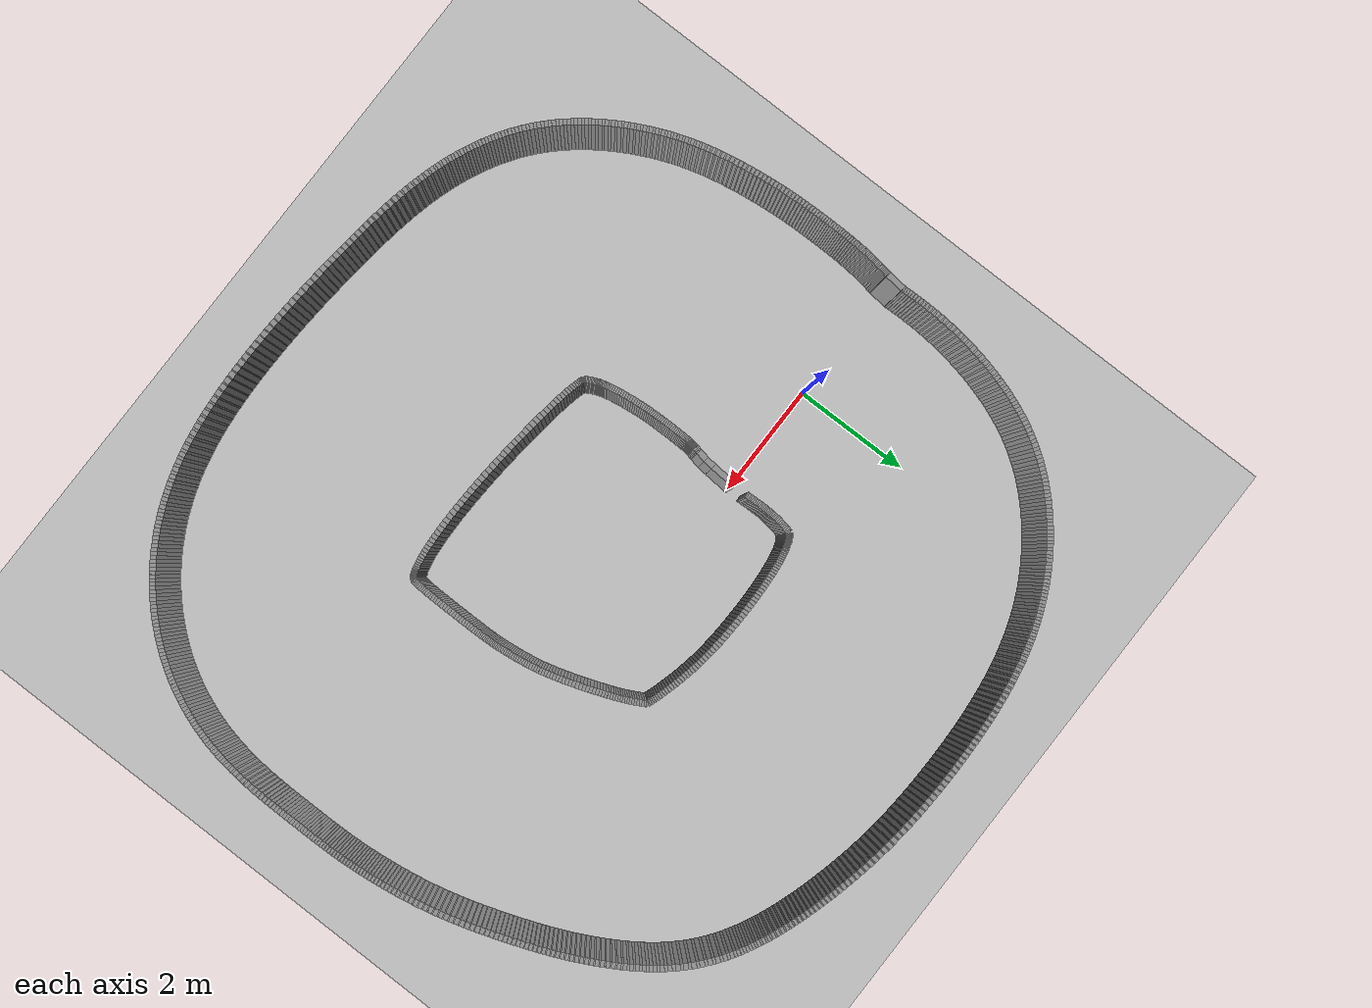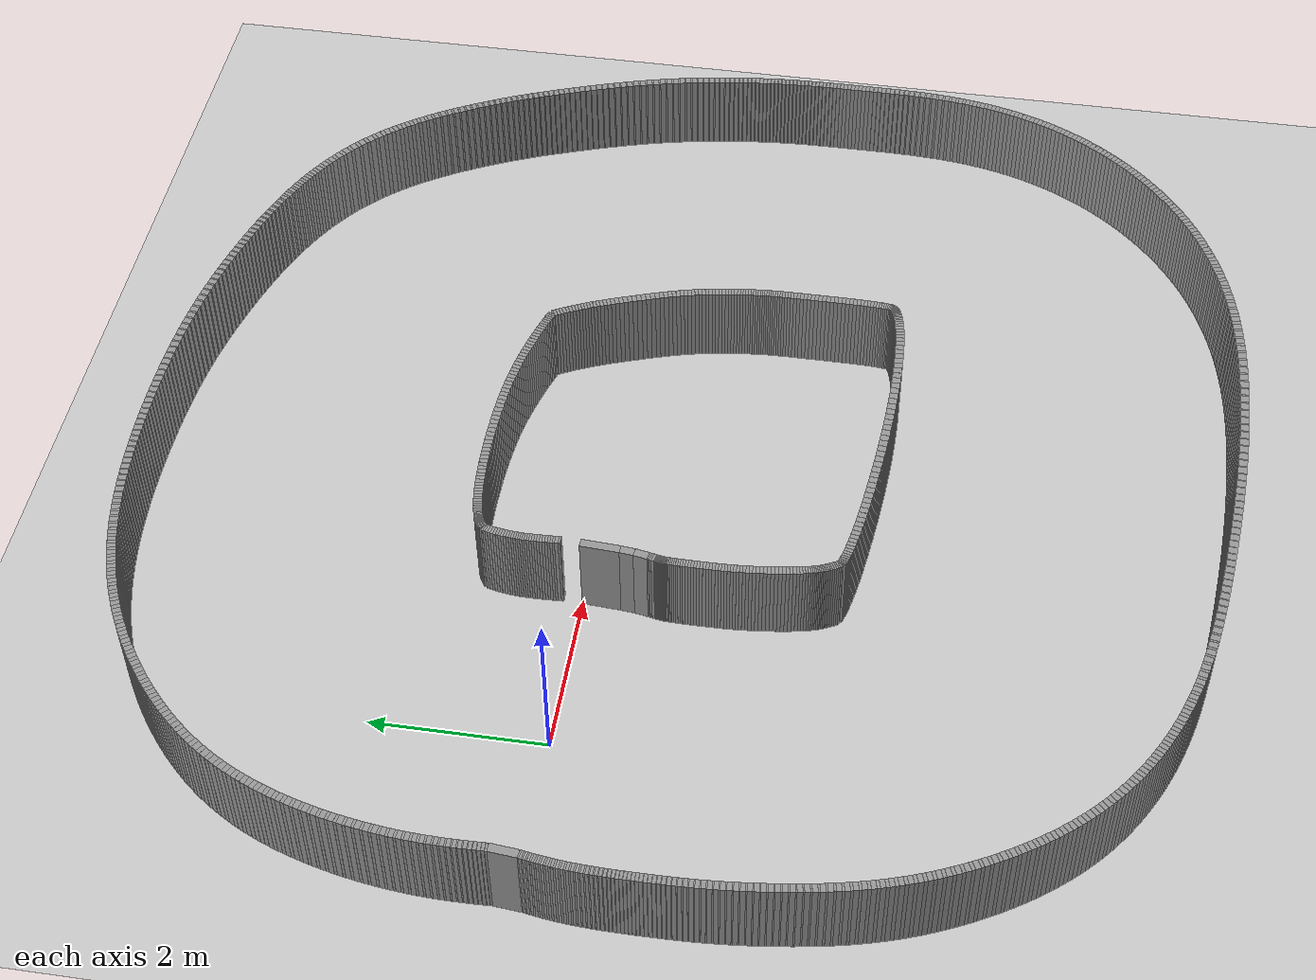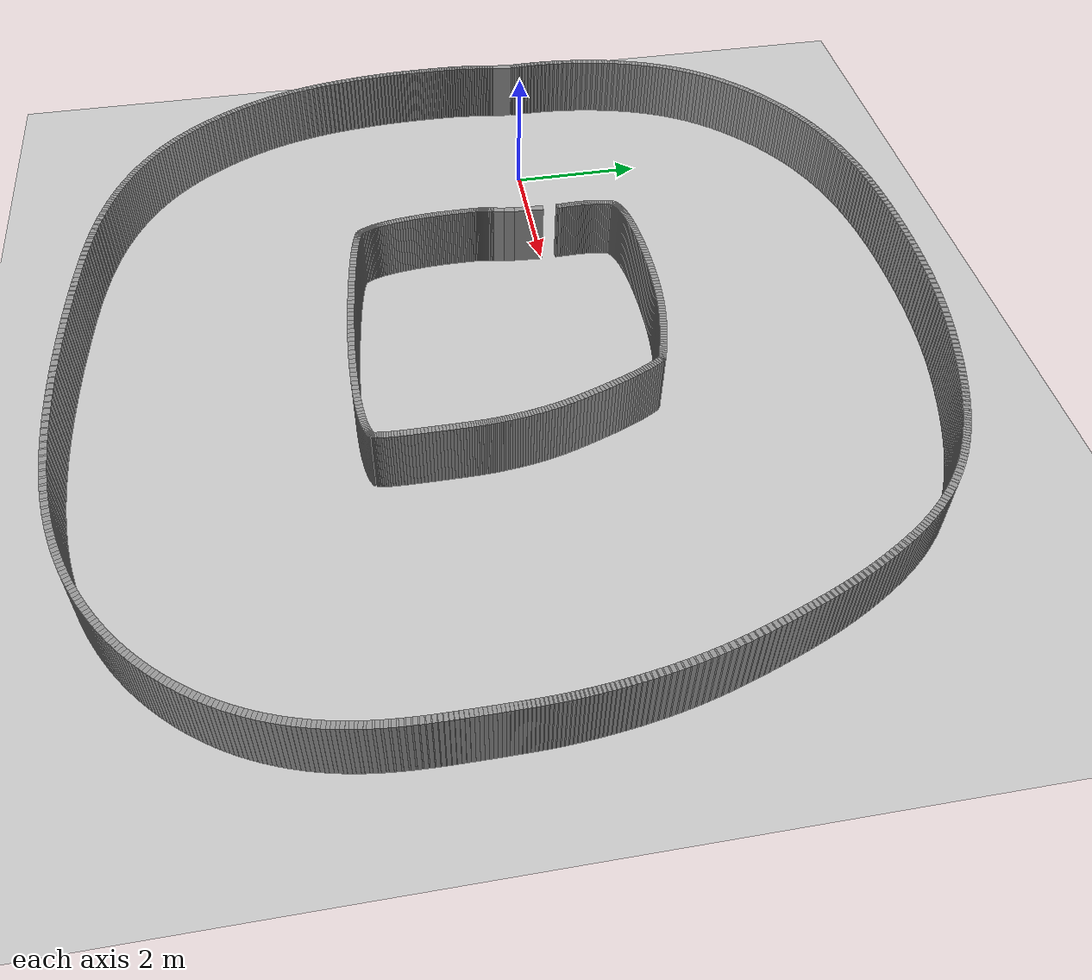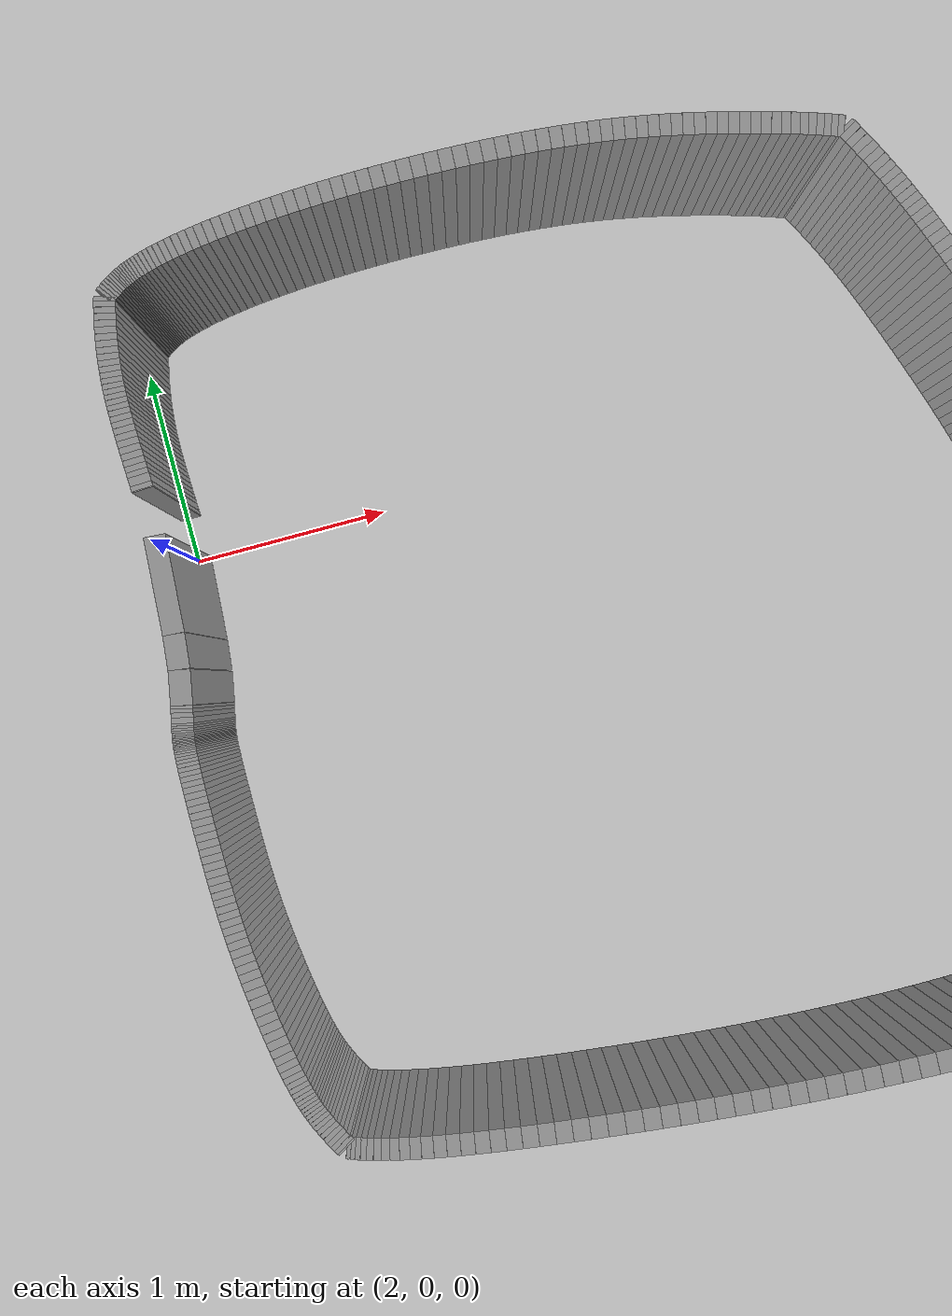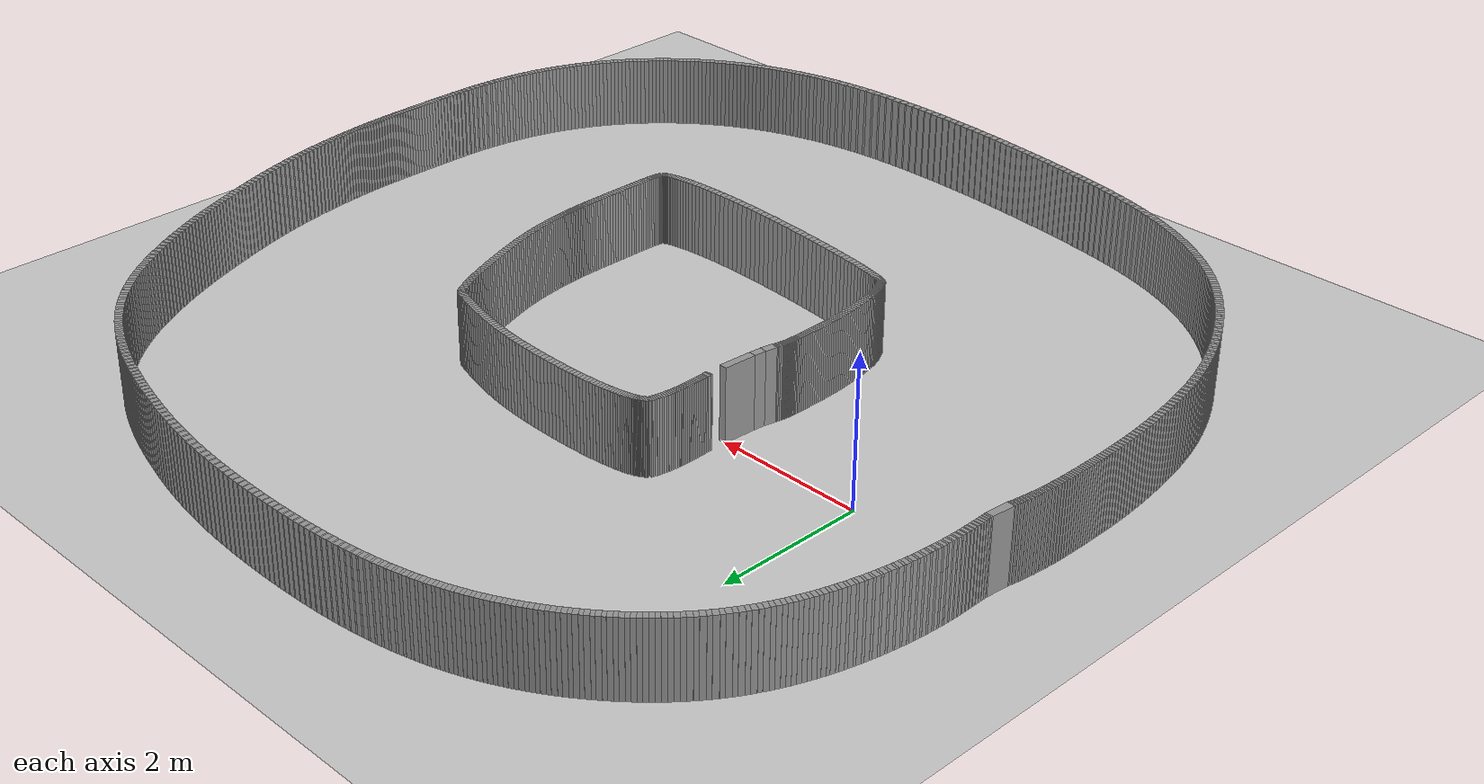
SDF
<?xml version="1.0"?>
        <sdf version="1.6">
        <world name="default">
            <include>
            <uri>model://ground_plane</uri>
            </include>
            <include>
            <uri>model://sun</uri>
            </include>

        <model name="wall_0_outward">
          <static>true</static>
          <link name="link">
            <collision name="collision">
              <geometry>
                <box>
                  <size>0.02499235140936947 0.1 1.0</size>
                </box>
              </geometry>
            </collision>
            <visual name="visual">
              <geometry>
                <box>
                  <size>0.02499235140936947 0.1 1.0</size>
                </box>
              </geometry>
              <material>
                <script>
                  <uri>file://media/materials/scripts/gazebo.material</uri>
                  <name>Gazebo/Gray</name>
                </script>
              </material>
            </visual>
          </link>
          <pose>-1.9832578888008565 0.2062286704109643 0.5 0 0 1.6105311360931815</pose>
        </model>

        <model name="wall_1_outward">
          <static>true</static>
          <link name="link">
            <collision name="collision">
              <geometry>
                <box>
                  <size>0.003562614089428086 0.1 1.0</size>
                </box>
              </geometry>
            </collision>
            <visual name="visual">
              <geometry>
                <box>
                  <size>0.003562614089428086 0.1 1.0</size>
                </box>
              </geometry>
              <material>
                <script>
                  <uri>file://media/materials/scripts/gazebo.material</uri>
                  <name>Gazebo/Gray</name>
                </script>
              </material>
            </visual>
          </link>
          <pose>-1.9838234672795898 0.22049494592302757 0.5 0 0 1.6096404824531443</pose>
        </model>

        <model name="wall_2_outward">
          <static>true</static>
          <link name="link">
            <collision name="collision">
              <geometry>
                <box>
                  <size>0.03404314978064565 0.1 1.0</size>
                </box>
              </geometry>
            </collision>
            <visual name="visual">
              <geometry>
                <box>
                  <size>0.03404314978064565 0.1 1.0</size>
                </box>
              </geometry>
              <material>
                <script>
                  <uri>file://media/materials/scripts/gazebo.material</uri>
                  <name>Gazebo/Gray</name>
                </script>
              </material>
            </visual>
          </link>
          <pose>-1.9845385165392937 0.2392842260999491 0.5 0 0 1.6087498288129647</pose>
        </model>

        <model name="wall_3_outward">
          <static>true</static>
          <link name="link">
            <collision name="collision">
              <geometry>
                <box>
                  <size>0.004864907696593289 0.1 1.0</size>
                </box>
              </geometry>
            </collision>
            <visual name="visual">
              <geometry>
                <box>
                  <size>0.004864907696593289 0.1 1.0</size>
                </box>
              </geometry>
              <material>
                <script>
                  <uri>file://media/materials/scripts/gazebo.material</uri>
                  <name>Gazebo/Gray</name>
                </script>
              </material>
            </visual>
          </link>
          <pose>-1.9852737314561468 0.2587243555219368 0.5 0 0 1.6075336015889483</pose>
        </model>

        <model name="wall_4_outward">
          <static>true</static>
          <link name="link">
            <collision name="collision">
              <geometry>
                <box>
                  <size>0.03597833039452776 0.1 1.0</size>
                </box>
              </geometry>
            </collision>
            <visual name="visual">
              <geometry>
                <box>
                  <size>0.03597833039452776 0.1 1.0</size>
                </box>
              </geometry>
              <material>
                <script>
                  <uri>file://media/materials/scripts/gazebo.material</uri>
                  <name>Gazebo/Gray</name>
                </script>
              </material>
            </visual>
          </link>
          <pose>-1.9860019327087488 0.27913298562419453 0.5 0 0 1.6063173743649837</pose>
        </model>

        <model name="wall_5_outward">
          <static>true</static>
          <link name="link">
            <collision name="collision">
              <geometry>
                <box>
                  <size>0.006405405531885531 0.1 1.0</size>
                </box>
              </geometry>
            </collision>
            <visual name="visual">
              <geometry>
                <box>
                  <size>0.006405405531885531 0.1 1.0</size>
                </box>
              </geometry>
              <material>
                <script>
                  <uri>file://media/materials/scripts/gazebo.material</uri>
                  <name>Gazebo/Gray</name>
                </script>
              </material>
            </visual>
          </link>
          <pose>-1.9867494062076563 0.3003116636612524 0.5 0 0 1.6047160222975967</pose>
        </model>

        <model name="wall_6_outward">
          <static>true</static>
          <link name="link">
            <collision name="collision">
              <geometry>
                <box>
                  <size>0.0376008471394773 0.1 1.0</size>
                </box>
              </geometry>
            </collision>
            <visual name="visual">
              <geometry>
                <box>
                  <size>0.0376008471394773 0.1 1.0</size>
                </box>
              </geometry>
              <material>
                <script>
                  <uri>file://media/materials/scripts/gazebo.material</uri>
                  <name>Gazebo/Gray</name>
                </script>
              </material>
            </visual>
          </link>
          <pose>-1.9874655128608278 0.32230313031087576 0.5 0 0 1.6031146702302423</pose>
        </model>

        <model name="wall_7_outward">
          <static>true</static>
          <link name="link">
            <collision name="collision">
              <geometry>
                <box>
                  <size>0.008167426659552243 0.1 1.0</size>
                </box>
              </geometry>
            </collision>
            <visual name="visual">
              <geometry>
                <box>
                  <size>0.008167426659552243 0.1 1.0</size>
                </box>
              </geometry>
              <material>
                <script>
                  <uri>file://media/materials/scripts/gazebo.material</uri>
                  <name>Gazebo/Gray</name>
                </script>
              </material>
            </visual>
          </link>
          <pose>-1.988196627239906 0.3451755782189848 0.5 0 0 1.6010728121465694</pose>
        </model>

        <model name="wall_8_outward">
          <static>true</static>
          <link name="link">
            <collision name="collision">
              <geometry>
                <box>
                  <size>0.03897445016088282 0.1 1.0</size>
                </box>
              </geometry>
            </collision>
            <visual name="visual">
              <geometry>
                <box>
                  <size>0.03897445016088282 0.1 1.0</size>
                </box>
              </geometry>
              <material>
                <script>
                  <uri>file://media/materials/scripts/gazebo.material</uri>
                  <name>Gazebo/Gray</name>
                </script>
              </material>
            </visual>
          </link>
          <pose>-1.9888703902729943 0.3687368780373082 0.5 0 0 1.5990309540628436</pose>
        </model>

        <model name="wall_9_outward">
          <static>true</static>
          <link name="link">
            <collision name="collision">
              <geometry>
                <box>
                  <size>0.010095114862784348 0.1 1.0</size>
                </box>
              </geometry>
            </collision>
            <visual name="visual">
              <geometry>
                <box>
                  <size>0.010095114862784348 0.1 1.0</size>
                </box>
              </geometry>
              <material>
                <script>
                  <uri>file://media/materials/scripts/gazebo.material</uri>
                  <name>Gazebo/Gray</name>
                </script>
              </material>
            </visual>
          </link>
          <pose>-1.9895502943814045 0.39326222526801957 0.5 0 0 1.5965071726679565</pose>
        </model>

        <model name="wall_10_outward">
          <static>true</static>
          <link name="link">
            <collision name="collision">
              <geometry>
                <box>
                  <size>0.040168850836637154 0.1 1.0</size>
                </box>
              </geometry>
            </collision>
            <visual name="visual">
              <geometry>
                <box>
                  <size>0.040168850836637154 0.1 1.0</size>
                </box>
              </geometry>
              <material>
                <script>
                  <uri>file://media/materials/scripts/gazebo.material</uri>
                  <name>Gazebo/Gray</name>
                </script>
              </material>
            </visual>
          </link>
          <pose>-1.9901457141934884 0.41838714101884367 0.5 0 0 1.5939833912730634</pose>
        </model>

        <model name="wall_11_outward">
          <static>true</static>
          <link name="link">
            <collision name="collision">
              <geometry>
                <box>
                  <size>0.012197037077132985 0.1 1.0</size>
                </box>
              </geometry>
            </collision>
            <visual name="visual">
              <geometry>
                <box>
                  <size>0.012197037077132985 0.1 1.0</size>
                </box>
              </geometry>
              <material>
                <script>
                  <uri>file://media/materials/scripts/gazebo.material</uri>
                  <name>Gazebo/Gray</name>
                </script>
              </material>
            </visual>
          </link>
          <pose>-1.9907341737812203 0.44456344959539373 0.5 0 0 1.5909341272784416</pose>
        </model>

        <model name="wall_12_outward">
          <static>true</static>
          <link name="link">
            <collision name="collision">
              <geometry>
                <box>
                  <size>0.04125735677064901 0.1 1.0</size>
                </box>
              </geometry>
            </collision>
            <visual name="visual">
              <geometry>
                <box>
                  <size>0.04125735677064901 0.1 1.0</size>
                </box>
              </geometry>
              <material>
                <script>
                  <uri>file://media/materials/scripts/gazebo.material</uri>
                  <name>Gazebo/Gray</name>
                </script>
              </material>
            </visual>
          </link>
          <pose>-1.9912094729971852 0.47128639809166156 0.5 0 0 1.5878848632838043</pose>
        </model>

        <model name="wall_13_outward">
          <static>true</static>
          <link name="link">
            <collision name="collision">
              <geometry>
                <box>
                  <size>0.014357418280432892 0.1 1.0</size>
                </box>
              </geometry>
            </collision>
            <visual name="visual">
              <geometry>
                <box>
                  <size>0.014357418280432892 0.1 1.0</size>
                </box>
              </geometry>
              <material>
                <script>
                  <uri>file://media/materials/scripts/gazebo.material</uri>
                  <name>Gazebo/Gray</name>
                </script>
              </material>
            </visual>
          </link>
          <pose>-1.9916588734661467 0.49909011964706607 0.5 0 0 1.5842955010064215</pose>
        </model>

        <model name="wall_14_outward">
          <static>true</static>
          <link name="link">
            <collision name="collision">
              <geometry>
                <box>
                  <size>0.04230556347329919 0.1 1.0</size>
                </box>
              </geometry>
            </collision>
            <visual name="visual">
              <geometry>
                <box>
                  <size>0.04230556347329919 0.1 1.0</size>
                </box>
              </geometry>
              <material>
                <script>
                  <uri>file://media/materials/scripts/gazebo.material</uri>
                  <name>Gazebo/Gray</name>
                </script>
              </material>
            </visual>
          </link>
          <pose>-1.9919653938262685 0.5274199178146918 0.5 0 0 1.580706138729061</pose>
        </model>

        <model name="wall_15_outward">
          <static>true</static>
          <link name="link">
            <collision name="collision">
              <geometry>
                <box>
                  <size>0.016498406599429822 0.1 1.0</size>
                </box>
              </geometry>
            </collision>
            <visual name="visual">
              <geometry>
                <box>
                  <size>0.016498406599429822 0.1 1.0</size>
                </box>
              </geometry>
              <material>
                <script>
                  <uri>file://media/materials/scripts/gazebo.material</uri>
                  <name>Gazebo/Gray</name>
                </script>
              </material>
            </visual>
          </link>
          <pose>-1.9922227334973337 0.556820726167788 0.5 0 0 1.5765815253842506</pose>
        </model>

        <model name="wall_16_outward">
          <static>true</static>
          <link name="link">
            <collision name="collision">
              <geometry>
                <box>
                  <size>0.04337548366498124 0.1 1.0</size>
                </box>
              </geometry>
            </collision>
            <visual name="visual">
              <geometry>
                <box>
                  <size>0.04337548366498124 0.1 1.0</size>
                </box>
              </geometry>
              <material>
                <script>
                  <uri>file://media/materials/scripts/gazebo.material</uri>
                  <name>Gazebo/Gray</name>
                </script>
              </material>
            </visual>
          </link>
          <pose>-1.9923064708379452 0.5867575033536172 0.5 0 0 1.5724569120394554</pose>
        </model>

        <model name="wall_17_outward">
          <static>true</static>
          <link name="link">
            <collision name="collision">
              <geometry>
                <box>
                  <size>0.018616051952543906 0.1 1.0</size>
                </box>
              </geometry>
            </collision>
            <visual name="visual">
              <geometry>
                <box>
                  <size>0.018616051952543906 0.1 1.0</size>
                </box>
              </geometry>
              <material>
                <script>
                  <uri>file://media/materials/scripts/gazebo.material</uri>
                  <name>Gazebo/Gray</name>
                </script>
              </material>
            </visual>
          </link>
          <pose>-1.992314622147501 0.6177531995567117 0.5 0 0 1.5678028822503105</pose>
        </model>

        <model name="wall_18_outward">
          <static>true</static>
          <link name="link">
            <collision name="collision">
              <geometry>
                <box>
                  <size>0.044514878685963065 0.1 1.0</size>
                </box>
              </geometry>
            </collision>
            <visual name="visual">
              <geometry>
                <box>
                  <size>0.044514878685963065 0.1 1.0</size>
                </box>
              </geometry>
              <material>
                <script>
                  <uri>file://media/materials/scripts/gazebo.material</uri>
                  <name>Gazebo/Gray</name>
                </script>
              </material>
            </visual>
          </link>
          <pose>-1.9921165475925389 0.6493179723253822 0.5 0 0 1.5631488524611383</pose>
        </model>

        <model name="wall_19_outward">
          <static>true</static>
          <link name="link">
            <collision name="collision">
              <geometry>
                <box>
                  <size>0.02053255308797264 0.1 1.0</size>
                </box>
              </geometry>
            </collision>
            <visual name="visual">
              <geometry>
                <box>
                  <size>0.02053255308797264 0.1 1.0</size>
                </box>
              </geometry>
              <material>
                <script>
                  <uri>file://media/materials/scripts/gazebo.material</uri>
                  <name>Gazebo/Gray</name>
                </script>
              </material>
            </visual>
          </link>
          <pose>-1.9918151300927371 0.6818401989058147 0.5 0 0 1.5580156916465986</pose>
        </model>

        <model name="wall_20_outward">
          <static>true</static>
          <link name="link">
            <collision name="collision">
              <geometry>
                <box>
                  <size>0.04575715215424599 0.1 1.0</size>
                </box>
              </geometry>
            </collision>
            <visual name="visual">
              <geometry>
                <box>
                  <size>0.04575715215424599 0.1 1.0</size>
                </box>
              </geometry>
              <material>
                <script>
                  <uri>file://media/materials/scripts/gazebo.material</uri>
                  <name>Gazebo/Gray</name>
                </script>
              </material>
            </visual>
          </link>
          <pose>-1.991274103905816 0.7149805422516373 0.5 0 0 1.5528825308320766</pose>
        </model>

        <model name="wall_21_outward">
          <static>true</static>
          <link name="link">
            <collision name="collision">
              <geometry>
                <box>
                  <size>0.02229397225560192 0.1 1.0</size>
                </box>
              </geometry>
            </collision>
            <visual name="visual">
              <geometry>
                <box>
                  <size>0.02229397225560192 0.1 1.0</size>
                </box>
              </geometry>
              <material>
                <script>
                  <uri>file://media/materials/scripts/gazebo.material</uri>
                  <name>Gazebo/Gray</name>
                </script>
              </material>
            </visual>
          </link>
          <pose>-1.9906024949461039 0.7489993591414924 0.5 0 0 1.547309008912097</pose>
        </model>

        <model name="wall_22_outward">
          <static>true</static>
          <link name="link">
            <collision name="collision">
              <geometry>
                <box>
                  <size>0.04712011720145803 0.1 1.0</size>
                </box>
              </geometry>
            </collision>
            <visual name="visual">
              <geometry>
                <box>
                  <size>0.04712011720145803 0.1 1.0</size>
                </box>
              </geometry>
              <material>
                <script>
                  <uri>file://media/materials/scripts/gazebo.material</uri>
                  <name>Gazebo/Gray</name>
                </script>
              </material>
            </visual>
          </link>
          <pose>-1.989656127489414 0.7836933814546628 0.5 0 0 1.541735486992129</pose>
        </model>

        <model name="wall_23_outward">
          <static>true</static>
          <link name="link">
            <collision name="collision">
              <geometry>
                <box>
                  <size>0.023861506493668753 0.1 1.0</size>
                </box>
              </geometry>
            </collision>
            <visual name="visual">
              <geometry>
                <box>
                  <size>0.023861506493668753 0.1 1.0</size>
                </box>
              </geometry>
              <material>
                <script>
                  <uri>file://media/materials/scripts/gazebo.material</uri>
                  <name>Gazebo/Gray</name>
                </script>
              </material>
            </visual>
          </link>
          <pose>-1.9885537446427641 0.8191669275814157 0.5 0 0 1.5357700749877792</pose>
        </model>

        <model name="wall_24_outward">
          <static>true</static>
          <link name="link">
            <collision name="collision">
              <geometry>
                <box>
                  <size>0.04860556392496431 0.1 1.0</size>
                </box>
              </geometry>
            </collision>
            <visual name="visual">
              <geometry>
                <box>
                  <size>0.04860556392496431 0.1 1.0</size>
                </box>
              </geometry>
              <material>
                <script>
                  <uri>file://media/materials/scripts/gazebo.material</uri>
                  <name>Gazebo/Gray</name>
                </script>
              </material>
            </visual>
          </link>
          <pose>-1.9871400080176391 0.8553727296624517 0.5 0 0 1.5298046629834243</pose>
        </model>

        <model name="wall_25_outward">
          <static>true</static>
          <link name="link">
            <collision name="collision">
              <geometry>
                <box>
                  <size>0.025216682645928676 0.1 1.0</size>
                </box>
              </geometry>
            </collision>
            <visual name="visual">
              <geometry>
                <box>
                  <size>0.025216682645928676 0.1 1.0</size>
                </box>
              </geometry>
              <material>
                <script>
                  <uri>file://media/materials/scripts/gazebo.material</uri>
                  <name>Gazebo/Gray</name>
                </script>
              </material>
            </visual>
          </link>
          <pose>-1.9855479752614955 0.8922493384537549 0.5 0 0 1.5235004505638725</pose>
        </model>

        <model name="wall_26_outward">
          <static>true</static>
          <link name="link">
            <collision name="collision">
              <geometry>
                <box>
                  <size>0.05019961485562541 0.1 1.0</size>
                </box>
              </geometry>
            </collision>
            <visual name="visual">
              <geometry>
                <box>
                  <size>0.05019961485562541 0.1 1.0</size>
                </box>
              </geometry>
              <material>
                <script>
                  <uri>file://media/materials/scripts/gazebo.material</uri>
                  <name>Gazebo/Gray</name>
                </script>
              </material>
            </visual>
          </link>
          <pose>-1.9836071672016429 0.9299073411749801 0.5 0 0 1.5171962381443287</pose>
        </model>

        <model name="wall_27_outward">
          <static>true</static>
          <link name="link">
            <collision name="collision">
              <geometry>
                <box>
                  <size>0.02635155146401303 0.1 1.0</size>
                </box>
              </geometry>
            </collision>
            <visual name="visual">
              <geometry>
                <box>
                  <size>0.02635155146401303 0.1 1.0</size>
                </box>
              </geometry>
              <material>
                <script>
                  <uri>file://media/materials/scripts/gazebo.material</uri>
                  <name>Gazebo/Gray</name>
                </script>
              </material>
            </visual>
          </link>
          <pose>-1.9814699142046015 0.968123019408103 0.5 0 0 1.5106083026247237</pose>
        </model>

        <model name="wall_28_outward">
          <static>true</static>
          <link name="link">
            <collision name="collision">
              <geometry>
                <box>
                  <size>0.05187417307537208 0.1 1.0</size>
                </box>
              </geometry>
            </collision>
            <visual name="visual">
              <geometry>
                <box>
                  <size>0.05187417307537208 0.1 1.0</size>
                </box>
              </geometry>
              <material>
                <script>
                  <uri>file://media/materials/scripts/gazebo.material</uri>
                  <name>Gazebo/Gray</name>
                </script>
              </material>
            </visual>
          </link>
          <pose>-1.9789466820323227 1.0071542179870743 0.5 0 0 1.5040203671050933</pose>
        </model>

        <model name="wall_29_outward">
          <static>true</static>
          <link name="link">
            <collision name="collision">
              <geometry>
                <box>
                  <size>0.027325228815458326 0.1 1.0</size>
                </box>
              </geometry>
            </collision>
            <visual name="visual">
              <geometry>
                <box>
                  <size>0.027325228815458326 0.1 1.0</size>
                </box>
              </geometry>
              <material>
                <script>
                  <uri>file://media/materials/scripts/gazebo.material</uri>
                  <name>Gazebo/Gray</name>
                </script>
              </material>
            </visual>
          </link>
          <pose>-1.9762112345015985 1.0466591177383084 0.5 0 0 1.497189006767617</pose>
        </model>

        <model name="wall_30_outward">
          <static>true</static>
          <link name="link">
            <collision name="collision">
              <geometry>
                <box>
                  <size>0.05359155179388415 0.1 1.0</size>
                </box>
              </geometry>
            </collision>
            <visual name="visual">
              <geometry>
                <box>
                  <size>0.05359155179388415 0.1 1.0</size>
                </box>
              </geometry>
              <material>
                <script>
                  <uri>file://media/materials/scripts/gazebo.material</uri>
                  <name>Gazebo/Gray</name>
                </script>
              </material>
            </visual>
          </link>
          <pose>-1.9730533807398332 1.0869938697612034 0.5 0 0 1.4903576464301445</pose>
        </model>

        <model name="wall_31_outward">
          <static>true</static>
          <link name="link">
            <collision name="collision">
              <geometry>
                <box>
                  <size>0.028176497649116766 0.1 1.0</size>
                </box>
              </geometry>
            </collision>
            <visual name="visual">
              <geometry>
                <box>
                  <size>0.028176497649116766 0.1 1.0</size>
                </box>
              </geometry>
              <material>
                <script>
                  <uri>file://media/materials/scripts/gazebo.material</uri>
                  <name>Gazebo/Gray</name>
                </script>
              </material>
            </visual>
          </link>
          <pose>-1.9696693786668225 1.1277373756910745 0.5 0 0 1.4833134637620153</pose>
        </model>

        <model name="wall_32_outward">
          <static>true</static>
          <link name="link">
            <collision name="collision">
              <geometry>
                <box>
                  <size>0.05530453154715493 0.1 1.0</size>
                </box>
              </geometry>
            </collision>
            <visual name="visual">
              <geometry>
                <box>
                  <size>0.05530453154715493 0.1 1.0</size>
                </box>
              </geometry>
              <material>
                <script>
                  <uri>file://media/materials/scripts/gazebo.material</uri>
                  <name>Gazebo/Gray</name>
                </script>
              </material>
            </visual>
          </link>
          <pose>-1.965828473745341 1.1693005646642527 0.5 0 0 1.476269281093899</pose>
        </model>

        <model name="wall_33_outward">
          <static>true</static>
          <link name="link">
            <collision name="collision">
              <geometry>
                <box>
                  <size>0.02890549046621725 0.1 1.0</size>
                </box>
              </geometry>
            </collision>
            <visual name="visual">
              <geometry>
                <box>
                  <size>0.02890549046621725 0.1 1.0</size>
                </box>
              </geometry>
              <material>
                <script>
                  <uri>file://media/materials/scripts/gazebo.material</uri>
                  <name>Gazebo/Gray</name>
                </script>
              </material>
            </visual>
          </link>
          <pose>-1.9617503969721624 1.2112073704535904 0.5 0 0 1.4690428455817852</pose>
        </model>

        <model name="wall_34_outward">
          <static>true</static>
          <link name="link">
            <collision name="collision">
              <geometry>
                <box>
                  <size>0.056962782045419456 0.1 1.0</size>
                </box>
              </geometry>
            </collision>
            <visual name="visual">
              <geometry>
                <box>
                  <size>0.056962782045419456 0.1 1.0</size>
                </box>
              </geometry>
              <material>
                <script>
                  <uri>file://media/materials/scripts/gazebo.material</uri>
                  <name>Gazebo/Gray</name>
                </script>
              </material>
            </visual>
          </link>
          <pose>-1.9571845569615682 1.25389778700131 0.5 0 0 1.4618164100696658</pose>
        </model>

        <model name="wall_35_outward">
          <static>true</static>
          <link name="link">
            <collision name="collision">
              <geometry>
                <box>
                  <size>0.02956355697005302 0.1 1.0</size>
                </box>
              </geometry>
            </collision>
            <visual name="visual">
              <geometry>
                <box>
                  <size>0.02956355697005302 0.1 1.0</size>
                </box>
              </geometry>
              <material>
                <script>
                  <uri>file://media/materials/scripts/gazebo.material</uri>
                  <name>Gazebo/Gray</name>
                </script>
              </material>
            </visual>
          </link>
          <pose>-1.9523705090394001 1.2968920166212237 0.5 0 0 1.454425453537305</pose>
        </model>

        <model name="wall_36_outward">
          <static>true</static>
          <link name="link">
            <collision name="collision">
              <geometry>
                <box>
                  <size>0.05851512762365332 0.1 1.0</size>
                </box>
              </geometry>
            </collision>
            <visual name="visual">
              <geometry>
                <box>
                  <size>0.05851512762365332 0.1 1.0</size>
                </box>
              </geometry>
              <material>
                <script>
                  <uri>file://media/materials/scripts/gazebo.material</uri>
                  <name>Gazebo/Gray</name>
                </script>
              </material>
            </visual>
          </link>
          <pose>-1.9470424874296541 1.340607600010691 0.5 0 0 1.4470344970049562</pose>
        </model>

        <model name="wall_37_outward">
          <static>true</static>
          <link name="link">
            <collision name="collision">
              <geometry>
                <box>
                  <size>0.030141295012214554 0.1 1.0</size>
                </box>
              </geometry>
            </collision>
            <visual name="visual">
              <geometry>
                <box>
                  <size>0.030141295012214554 0.1 1.0</size>
                </box>
              </geometry>
              <material>
                <script>
                  <uri>file://media/materials/scripts/gazebo.material</uri>
                  <name>Gazebo/Gray</name>
                </script>
              </material>
            </visual>
          </link>
          <pose>-1.9414577005743066 1.384582313626082 0.5 0 0 1.439499101939416</pose>
        </model>

        <model name="wall_38_outward">
          <static>true</static>
          <link name="link">
            <collision name="collision">
              <geometry>
                <box>
                  <size>0.059911481965376726 0.1 1.0</size>
                </box>
              </geometry>
            </collision>
            <visual name="visual">
              <geometry>
                <box>
                  <size>0.059911481965376726 0.1 1.0</size>
                </box>
              </geometry>
              <material>
                <script>
                  <uri>file://media/materials/scripts/gazebo.material</uri>
                  <name>Gazebo/Gray</name>
                </script>
              </material>
            </visual>
          </link>
          <pose>-1.9353391597354457 1.4291907599565337 0.5 0 0 1.4319637068738675</pose>
        </model>

        <model name="wall_39_outward">
          <static>true</static>
          <link name="link">
            <collision name="collision">
              <geometry>
                <box>
                  <size>0.030703685964613665 0.1 1.0</size>
                </box>
              </geometry>
            </collision>
            <visual name="visual">
              <geometry>
                <box>
                  <size>0.030703685964613665 0.1 1.0</size>
                </box>
              </geometry>
              <material>
                <script>
                  <uri>file://media/materials/scripts/gazebo.material</uri>
                  <name>Gazebo/Gray</name>
                </script>
              </material>
            </visual>
          </link>
          <pose>-1.9289525332044373 1.4740456489890659 0.5 0 0 1.424287710003456</pose>
        </model>

        <model name="wall_40_outward">
          <static>true</static>
          <link name="link">
            <collision name="collision">
              <geometry>
                <box>
                  <size>0.06110865213101824 0.1 1.0</size>
                </box>
              </geometry>
            </collision>
            <visual name="visual">
              <geometry>
                <box>
                  <size>0.06110865213101824 0.1 1.0</size>
                </box>
              </geometry>
              <material>
                <script>
                  <uri>file://media/materials/scripts/gazebo.material</uri>
                  <name>Gazebo/Gray</name>
                </script>
              </material>
            </visual>
          </link>
          <pose>-1.9220190302178766 1.5194248871422116 0.5 0 0 1.416611713133052</pose>
        </model>

        <model name="wall_41_outward">
          <static>true</static>
          <link name="link">
            <collision name="collision">
              <geometry>
                <box>
                  <size>0.031242492618105622 0.1 1.0</size>
                </box>
              </geometry>
            </collision>
            <visual name="visual">
              <geometry>
                <box>
                  <size>0.031242492618105622 0.1 1.0</size>
                </box>
              </geometry>
              <material>
                <script>
                  <uri>file://media/materials/scripts/gazebo.material</uri>
                  <name>Gazebo/Gray</name>
                </script>
              </material>
            </visual>
          </link>
          <pose>-1.9148071516139984 1.565033473754787 0.5 0 0 1.4088010105607598</pose>
        </model>

        <model name="wall_42_outward">
          <static>true</static>
          <link name="link">
            <collision name="collision">
              <geometry>
                <box>
                  <size>0.06206896437567824 0.1 1.0</size>
                </box>
              </geometry>
            </collision>
            <visual name="visual">
              <geometry>
                <box>
                  <size>0.06206896437567824 0.1 1.0</size>
                </box>
              </geometry>
              <material>
                <script>
                  <uri>file://media/materials/scripts/gazebo.material</uri>
                  <name>Gazebo/Gray</name>
                </script>
              </material>
            </visual>
          </link>
          <pose>-1.9070430832570011 1.611038328587831 0.5 0 0 1.4009903079884467</pose>
        </model>

        <model name="wall_43_outward">
          <static>true</static>
          <link name="link">
            <collision name="collision">
              <geometry>
                <box>
                  <size>0.03181751389419528 0.1 1.0</size>
                </box>
              </geometry>
            </collision>
            <visual name="visual">
              <geometry>
                <box>
                  <size>0.03181751389419528 0.1 1.0</size>
                </box>
              </geometry>
              <material>
                <script>
                  <uri>file://media/materials/scripts/gazebo.material</uri>
                  <name>Gazebo/Gray</name>
                </script>
              </material>
            </visual>
          </link>
          <pose>-1.8989854515694173 1.6572845287868891 0.5 0 0 1.3930358456307483</pose>
        </model>

        <model name="wall_44_outward">
          <static>true</static>
          <link name="link">
            <collision name="collision">
              <geometry>
                <box>
                  <size>0.06276551478844714 0.1 1.0</size>
                </box>
              </geometry>
            </collision>
            <visual name="visual">
              <geometry>
                <box>
                  <size>0.06276551478844714 0.1 1.0</size>
                </box>
              </geometry>
              <material>
                <script>
                  <uri>file://media/materials/scripts/gazebo.material</uri>
                  <name>Gazebo/Gray</name>
                </script>
              </material>
            </visual>
          </link>
          <pose>-1.8903775710575765 1.703785712986872 0.5 0 0 1.3850813832730642</pose>
        </model>

        <model name="wall_45_outward">
          <static>true</static>
          <link name="link">
            <collision name="collision">
              <geometry>
                <box>
                  <size>0.03247971047962401 0.1 1.0</size>
                </box>
              </geometry>
            </collision>
            <visual name="visual">
              <geometry>
                <box>
                  <size>0.03247971047962401 0.1 1.0</size>
                </box>
              </geometry>
              <material>
                <script>
                  <uri>file://media/materials/scripts/gazebo.material</uri>
                  <name>Gazebo/Gray</name>
                </script>
              </material>
            </visual>
          </link>
          <pose>-1.8814545922067465 1.7505645552021567 0.5 0 0 1.3769613664216742</pose>
        </model>

        <model name="wall_46_outward">
          <static>true</static>
          <link name="link">
            <collision name="collision">
              <geometry>
                <box>
                  <size>0.06318203907273635 0.1 1.0</size>
                </box>
              </geometry>
            </collision>
            <visual name="visual">
              <geometry>
                <box>
                  <size>0.06318203907273635 0.1 1.0</size>
                </box>
              </geometry>
              <material>
                <script>
                  <uri>file://media/materials/scripts/gazebo.material</uri>
                  <name>Gazebo/Gray</name>
                </script>
              </material>
            </visual>
          </link>
          <pose>-1.8719897320360075 1.7974492560894066 0.5 0 0 1.3688413495702862</pose>
        </model>

        <model name="wall_47_outward">
          <static>true</static>
          <link name="link">
            <collision name="collision">
              <geometry>
                <box>
                  <size>0.03326260273348168 0.1 1.0</size>
                </box>
              </geometry>
            </collision>
            <visual name="visual">
              <geometry>
                <box>
                  <size>0.03326260273348168 0.1 1.0</size>
                </box>
              </geometry>
              <material>
                <script>
                  <uri>file://media/materials/scripts/gazebo.material</uri>
                  <name>Gazebo/Gray</name>
                </script>
              </material>
            </visual>
          </link>
          <pose>-1.8621816858538134 1.8446632172801827 0.5 0 0 1.3605256030459898</pose>
        </model>

        <model name="wall_48_outward">
          <static>true</static>
          <link name="link">
            <collision name="collision">
              <geometry>
                <box>
                  <size>0.06331190520389895 0.1 1.0</size>
                </box>
              </geometry>
            </collision>
            <visual name="visual">
              <geometry>
                <box>
                  <size>0.06331190520389895 0.1 1.0</size>
                </box>
              </geometry>
              <material>
                <script>
                  <uri>file://media/materials/scripts/gazebo.material</uri>
                  <name>Gazebo/Gray</name>
                </script>
              </material>
            </visual>
          </link>
          <pose>-1.8518457313955587 1.8918309025588722 0.5 0 0 1.3522098565217038</pose>
        </model>

        <model name="wall_49_outward">
          <static>true</static>
          <link name="link">
            <collision name="collision">
              <geometry>
                <box>
                  <size>0.034242978003103164 0.1 1.0</size>
                </box>
              </geometry>
            </collision>
            <visual name="visual">
              <geometry>
                <box>
                  <size>0.034242978003103164 0.1 1.0</size>
                </box>
              </geometry>
              <material>
                <script>
                  <uri>file://media/materials/scripts/gazebo.material</uri>
                  <name>Gazebo/Gray</name>
                </script>
              </material>
            </visual>
          </link>
          <pose>-1.841125396906862 1.9394152856705875 0.5 0 0 1.3436490074532073</pose>
        </model>

        <model name="wall_50_outward">
          <static>true</static>
          <link name="link">
            <collision name="collision">
              <geometry>
                <box>
                  <size>0.06316349887364199 0.1 1.0</size>
                </box>
              </geometry>
            </collision>
            <visual name="visual">
              <geometry>
                <box>
                  <size>0.06316349887364199 0.1 1.0</size>
                </box>
              </geometry>
              <material>
                <script>
                  <uri>file://media/materials/scripts/gazebo.material</uri>
                  <name>Gazebo/Gray</name>
                </script>
              </material>
            </visual>
          </link>
          <pose>-1.8298943165576484 1.9868054601793745 0.5 0 0 1.335088158384695</pose>
        </model>

        <model name="wall_51_outward">
          <static>true</static>
          <link name="link">
            <collision name="collision">
              <geometry>
                <box>
                  <size>0.03551502997922691 0.1 1.0</size>
                </box>
              </geometry>
            </collision>
            <visual name="visual">
              <geometry>
                <box>
                  <size>0.03551502997922691 0.1 1.0</size>
                </box>
              </geometry>
              <material>
                <script>
                  <uri>file://media/materials/scripts/gazebo.material</uri>
                  <name>Gazebo/Gray</name>
                </script>
              </material>
            </visual>
          </link>
          <pose>-1.8182188960074326 2.0347429544611693 0.5 0 0 1.3262092842302167</pose>
        </model>

        <model name="wall_52_outward">
          <static>true</static>
          <link name="link">
            <collision name="collision">
              <geometry>
                <box>
                  <size>0.0627532570535955 0.1 1.0</size>
                </box>
              </geometry>
            </collision>
            <visual name="visual">
              <geometry>
                <box>
                  <size>0.0627532570535955 0.1 1.0</size>
                </box>
              </geometry>
              <material>
                <script>
                  <uri>file://media/materials/scripts/gazebo.material</uri>
                  <name>Gazebo/Gray</name>
                </script>
              </material>
            </visual>
          </link>
          <pose>-1.8060507895783742 2.082346077479201 0.5 0 0 1.317330410075743</pose>
        </model>

        <model name="wall_53_outward">
          <static>true</static>
          <link name="link">
            <collision name="collision">
              <geometry>
                <box>
                  <size>0.037159612835387726 0.1 1.0</size>
                </box>
              </geometry>
            </collision>
            <visual name="visual">
              <geometry>
                <box>
                  <size>0.037159612835387726 0.1 1.0</size>
                </box>
              </geometry>
              <material>
                <script>
                  <uri>file://media/materials/scripts/gazebo.material</uri>
                  <name>Gazebo/Gray</name>
                </script>
              </material>
            </visual>
          </link>
          <pose>-1.7933567934781605 2.1306623019021345 0.5 0 0 1.308040373238367</pose>
        </model>

        <model name="wall_54_outward">
          <static>true</static>
          <link name="link">
            <collision name="collision">
              <geometry>
                <box>
                  <size>0.062111140385945215 0.1 1.0</size>
                </box>
              </geometry>
            </collision>
            <visual name="visual">
              <geometry>
                <box>
                  <size>0.062111140385945215 0.1 1.0</size>
                </box>
              </geometry>
              <material>
                <script>
                  <uri>file://media/materials/scripts/gazebo.material</uri>
                  <name>Gazebo/Gray</name>
                </script>
              </material>
            </visual>
          </link>
          <pose>-1.7801861038155211 2.1785178527508213 0.5 0 0 1.2987503364009896</pose>
        </model>

        <model name="wall_55_outward">
          <static>true</static>
          <link name="link">
            <collision name="collision">
              <geometry>
                <box>
                  <size>0.03920906291768073 0.1 1.0</size>
                </box>
              </geometry>
            </collision>
            <visual name="visual">
              <geometry>
                <box>
                  <size>0.03920906291768073 0.1 1.0</size>
                </box>
              </geometry>
              <material>
                <script>
                  <uri>file://media/materials/scripts/gazebo.material</uri>
                  <name>Gazebo/Gray</name>
                </script>
              </material>
            </visual>
          </link>
          <pose>-1.7663887471592394 2.2272622919024005 0.5 0 0 1.2889479136906214</pose>
        </model>

        <model name="wall_56_outward">
          <static>true</static>
          <link name="link">
            <collision name="collision">
              <geometry>
                <box>
                  <size>0.06127646381022511 0.1 1.0</size>
                </box>
              </geometry>
            </collision>
            <visual name="visual">
              <geometry>
                <box>
                  <size>0.06127646381022511 0.1 1.0</size>
                </box>
              </geometry>
              <material>
                <script>
                  <uri>file://media/materials/scripts/gazebo.material</uri>
                  <name>Gazebo/Gray</name>
                </script>
              </material>
            </visual>
          </link>
          <pose>-1.752126582053303 2.2754376819124733 0.5 0 0 1.2791454909802618</pose>
        </model>

        <model name="wall_57_outward">
          <static>true</static>
          <link name="link">
            <collision name="collision">
              <geometry>
                <box>
                  <size>0.04179918478633313 0.1 1.0</size>
                </box>
              </geometry>
            </collision>
            <visual name="visual">
              <geometry>
                <box>
                  <size>0.04179918478633313 0.1 1.0</size>
                </box>
              </geometry>
              <material>
                <script>
                  <uri>file://media/materials/scripts/gazebo.material</uri>
                  <name>Gazebo/Gray</name>
                </script>
              </material>
            </visual>
          </link>
          <pose>-1.7370988731864154 2.324735200867993 0.5 0 0 1.2686955045911017</pose>
        </model>

        <model name="wall_58_outward">
          <static>true</static>
          <link name="link">
            <collision name="collision">
              <geometry>
                <box>
                  <size>0.06029681220757901 0.1 1.0</size>
                </box>
              </geometry>
            </collision>
            <visual name="visual">
              <geometry>
                <box>
                  <size>0.06029681220757901 0.1 1.0</size>
                </box>
              </geometry>
              <material>
                <script>
                  <uri>file://media/materials/scripts/gazebo.material</uri>
                  <name>Gazebo/Gray</name>
                </script>
              </material>
            </visual>
          </link>
          <pose>-1.721610450878877 2.3733761107940663 0.5 0 0 1.2582455182019454</pose>
        </model>

        <model name="wall_59_outward">
          <static>true</static>
          <link name="link">
            <collision name="collision">
              <geometry>
                <box>
                  <size>0.04490399578796643 0.1 1.0</size>
                </box>
              </geometry>
            </collision>
            <visual name="visual">
              <geometry>
                <box>
                  <size>0.04490399578796643 0.1 1.0</size>
                </box>
              </geometry>
              <material>
                <script>
                  <uri>file://media/materials/scripts/gazebo.material</uri>
                  <name>Gazebo/Gray</name>
                </script>
              </material>
            </visual>
          </link>
          <pose>-1.7051971176817826 2.4233493004802633 0.5 0 0 1.2470192834524751</pose>
        </model>

        <model name="wall_60_outward">
          <static>true</static>
          <link name="link">
            <collision name="collision">
              <geometry>
                <box>
                  <size>0.05922845943594854 0.1 1.0</size>
                </box>
              </geometry>
            </collision>
            <visual name="visual">
              <geometry>
                <box>
                  <size>0.05922845943594854 0.1 1.0</size>
                </box>
              </geometry>
              <material>
                <script>
                  <uri>file://media/materials/scripts/gazebo.material</uri>
                  <name>Gazebo/Gray</name>
                </script>
              </material>
            </visual>
          </link>
          <pose>-1.6883176858698055 2.47260265614514 0.5 0 0 1.2357930487030033</pose>
        </model>

        <model name="wall_61_outward">
          <static>true</static>
          <link name="link">
            <collision name="collision">
              <geometry>
                <box>
                  <size>0.048531635326042565 0.1 1.0</size>
                </box>
              </geometry>
            </collision>
            <visual name="visual">
              <geometry>
                <box>
                  <size>0.048531635326042565 0.1 1.0</size>
                </box>
              </geometry>
              <material>
                <script>
                  <uri>file://media/materials/scripts/gazebo.material</uri>
                  <name>Gazebo/Gray</name>
                </script>
              </material>
            </visual>
          </link>
          <pose>-1.6703259596412994 2.523388988006415 0.5 0 0 1.2236598421759592</pose>
        </model>

        <model name="wall_62_outward">
          <static>true</static>
          <link name="link">
            <collision name="collision">
              <geometry>
                <box>
                  <size>0.058131444615278374 0.1 1.0</size>
                </box>
              </geometry>
            </collision>
            <visual name="visual">
              <geometry>
                <box>
                  <size>0.058131444615278374 0.1 1.0</size>
                </box>
              </geometry>
              <material>
                <script>
                  <uri>file://media/materials/scripts/gazebo.material</uri>
                  <name>Gazebo/Gray</name>
                </script>
              </material>
            </visual>
          </link>
          <pose>-1.6518513347425898 2.5734173555664475 0.5 0 0 1.2115266356489098</pose>
        </model>

        <model name="wall_63_outward">
          <static>true</static>
          <link name="link">
            <collision name="collision">
              <geometry>
                <box>
                  <size>0.05257569714983823 0.1 1.0</size>
                </box>
              </geometry>
            </collision>
            <visual name="visual">
              <geometry>
                <box>
                  <size>0.05257569714983823 0.1 1.0</size>
                </box>
              </geometry>
              <material>
                <script>
                  <uri>file://media/materials/scripts/gazebo.material</uri>
                  <name>Gazebo/Gray</name>
                </script>
              </material>
            </visual>
          </link>
          <pose>-1.632066870419663 2.6251132042533154 0.5 0 0 1.1983823328686076</pose>
        </model>

        <model name="wall_64_outward">
          <static>true</static>
          <link name="link">
            <collision name="collision">
              <geometry>
                <box>
                  <size>0.05706681265305787 0.1 1.0</size>
                </box>
              </geometry>
            </collision>
            <visual name="visual">
              <geometry>
                <box>
                  <size>0.05706681265305787 0.1 1.0</size>
                </box>
              </geometry>
              <material>
                <script>
                  <uri>file://media/materials/scripts/gazebo.material</uri>
                  <name>Gazebo/Gray</name>
                </script>
              </material>
            </visual>
          </link>
          <pose>-1.6117708983937162 2.676037794744469 0.5 0 0 1.1852380300883172</pose>
        </model>

        <model name="wall_65_outward">
          <static>true</static>
          <link name="link">
            <collision name="collision">
              <geometry>
                <box>
                  <size>0.05687668737168199 0.1 1.0</size>
                </box>
              </geometry>
            </collision>
            <visual name="visual">
              <geometry>
                <box>
                  <size>0.05687668737168199 0.1 1.0</size>
                </box>
              </geometry>
              <material>
                <script>
                  <uri>file://media/materials/scripts/gazebo.material</uri>
                  <name>Gazebo/Gray</name>
                </script>
              </material>
            </visual>
          </link>
          <pose>-1.589971558549408 2.7286724317441533 0.5 0 0 1.1710183790516235</pose>
        </model>

        <model name="wall_66_outward">
          <static>true</static>
          <link name="link">
            <collision name="collision">
              <geometry>
                <box>
                  <size>0.056096900825243254 0.1 1.0</size>
                </box>
              </geometry>
            </collision>
            <visual name="visual">
              <geometry>
                <box>
                  <size>0.056096900825243254 0.1 1.0</size>
                </box>
              </geometry>
              <material>
                <script>
                  <uri>file://media/materials/scripts/gazebo.material</uri>
                  <name>Gazebo/Gray</name>
                </script>
              </material>
            </visual>
          </link>
          <pose>-1.56761984461702 2.780547257147354 0.5 0 0 1.1567987280149152</pose>
        </model>

        <model name="wall_67_outward">
          <static>true</static>
          <link name="link">
            <collision name="collision">
              <geometry>
                <box>
                  <size>0.06114696510490706 0.1 1.0</size>
                </box>
              </geometry>
            </collision>
            <visual name="visual">
              <geometry>
                <box>
                  <size>0.06114696510490706 0.1 1.0</size>
                </box>
              </geometry>
              <material>
                <script>
                  <uri>file://media/materials/scripts/gazebo.material</uri>
                  <name>Gazebo/Gray</name>
                </script>
              </material>
            </visual>
          </link>
          <pose>-1.5436114096255436 2.8340255300123283 0.5 0 0 1.141511391297089</pose>
        </model>

        <model name="wall_68_outward">
          <static>true</static>
          <link name="link">
            <collision name="collision">
              <geometry>
                <box>
                  <size>0.05527921187933009 0.1 1.0</size>
                </box>
              </geometry>
            </collision>
            <visual name="visual">
              <geometry>
                <box>
                  <size>0.05527921187933009 0.1 1.0</size>
                </box>
              </geometry>
              <material>
                <script>
                  <uri>file://media/materials/scripts/gazebo.material</uri>
                  <name>Gazebo/Gray</name>
                </script>
              </material>
            </visual>
          </link>
          <pose>-1.5189990782692024 2.886777774826888 0.5 0 0 1.12622405457927</pose>
        </model>

        <model name="wall_69_outward">
          <static>true</static>
          <link name="link">
            <collision name="collision">
              <geometry>
                <box>
                  <size>0.06513547587774239 0.1 1.0</size>
                </box>
              </geometry>
            </collision>
            <visual name="visual">
              <geometry>
                <box>
                  <size>0.06513547587774239 0.1 1.0</size>
                </box>
              </geometry>
              <material>
                <script>
                  <uri>file://media/materials/scripts/gazebo.material</uri>
                  <name>Gazebo/Gray</name>
                </script>
              </material>
            </visual>
          </link>
          <pose>-1.4926286784846798 2.940900668005831 0.5 0 0 1.1099394658735875</pose>
        </model>

        <model name="wall_70_outward">
          <static>true</static>
          <link name="link">
            <collision name="collision">
              <geometry>
                <box>
                  <size>0.0546627536988429 0.1 1.0</size>
                </box>
              </geometry>
            </collision>
            <visual name="visual">
              <geometry>
                <box>
                  <size>0.0546627536988429 0.1 1.0</size>
                </box>
              </geometry>
              <material>
                <script>
                  <uri>file://media/materials/scripts/gazebo.material</uri>
                  <name>Gazebo/Gray</name>
                </script>
              </material>
            </visual>
          </link>
          <pose>-1.4655935829752147 2.994349442726532 0.5 0 0 1.0936548771679133</pose>
        </model>

        <model name="wall_71_outward">
          <static>true</static>
          <link name="link">
            <collision name="collision">
              <geometry>
                <box>
                  <size>0.06843347329352682 0.1 1.0</size>
                </box>
              </geometry>
            </collision>
            <visual name="visual">
              <geometry>
                <box>
                  <size>0.06843347329352682 0.1 1.0</size>
                </box>
              </geometry>
              <material>
                <script>
                  <uri>file://media/materials/scripts/gazebo.material</uri>
                  <name>Gazebo/Gray</name>
                </script>
              </material>
            </visual>
          </link>
          <pose>-1.4368104072647148 3.0487500431290107 0.5 0 0 1.0765456741419932</pose>
        </model>

        <model name="wall_72_outward">
          <static>true</static>
          <link name="link">
            <collision name="collision">
              <geometry>
                <box>
                  <size>0.05428522615266177 0.1 1.0</size>
                </box>
              </geometry>
            </collision>
            <visual name="visual">
              <geometry>
                <box>
                  <size>0.05428522615266177 0.1 1.0</size>
                </box>
              </geometry>
              <material>
                <script>
                  <uri>file://media/materials/scripts/gazebo.material</uri>
                  <name>Gazebo/Gray</name>
                </script>
              </material>
            </visual>
          </link>
          <pose>-1.407296334612559 3.102542398141086 0.5 0 0 1.0594364711160722</pose>
        </model>

        <model name="wall_73_outward">
          <static>true</static>
          <link name="link">
            <collision name="collision">
              <geometry>
                <box>
                  <size>0.07073385974991644 0.1 1.0</size>
                </box>
              </geometry>
            </collision>
            <visual name="visual">
              <geometry>
                <box>
                  <size>0.07073385974991644 0.1 1.0</size>
                </box>
              </geometry>
              <material>
                <script>
                  <uri>file://media/materials/scripts/gazebo.material</uri>
                  <name>Gazebo/Gray</name>
                </script>
              </material>
            </visual>
          </link>
          <pose>-1.3761637384397991 3.156744835454118 0.5 0 0 1.0417520844311</pose>
        </model>

        <model name="wall_74_outward">
          <static>true</static>
          <link name="link">
            <collision name="collision">
              <geometry>
                <box>
                  <size>0.05417058609555801 0.1 1.0</size>
                </box>
              </geometry>
            </collision>
            <visual name="visual">
              <geometry>
                <box>
                  <size>0.05417058609555801 0.1 1.0</size>
                </box>
              </geometry>
              <material>
                <script>
                  <uri>file://media/materials/scripts/gazebo.material</uri>
                  <name>Gazebo/Gray</name>
                </script>
              </material>
            </visual>
          </link>
          <pose>-1.3442322268360458 3.2104138129347484 0.5 0 0 1.0240676977461278</pose>
        </model>

        <model name="wall_75_outward">
          <static>true</static>
          <link name="link">
            <collision name="collision">
              <geometry>
                <box>
                  <size>0.07178554663241363 0.1 1.0</size>
                </box>
              </geometry>
            </collision>
            <visual name="visual">
              <geometry>
                <box>
                  <size>0.07178554663241363 0.1 1.0</size>
                </box>
              </geometry>
              <material>
                <script>
                  <uri>file://media/materials/scripts/gazebo.material</uri>
                  <name>Gazebo/Gray</name>
                </script>
              </material>
            </visual>
          </link>
          <pose>-1.3109429695746762 3.2638717315287855 0.5 0 0 1.00612034760789</pose>
        </model>

        <model name="wall_76_outward">
          <static>true</static>
          <link name="link">
            <collision name="collision">
              <geometry>
                <box>
                  <size>0.05432564529804905 0.1 1.0</size>
                </box>
              </geometry>
            </collision>
            <visual name="visual">
              <geometry>
                <box>
                  <size>0.05432564529804905 0.1 1.0</size>
                </box>
              </geometry>
              <material>
                <script>
                  <uri>file://media/materials/scripts/gazebo.material</uri>
                  <name>Gazebo/Gray</name>
                </script>
              </material>
            </visual>
          </link>
          <pose>-1.2767898050830626 3.3168741419257857 0.5 0 0 0.9881729974696609</pose>
        </model>

        <model name="wall_77_outward">
          <static>true</static>
          <link name="link">
            <collision name="collision">
              <geometry>
                <box>
                  <size>0.07160525797664448 0.1 1.0</size>
                </box>
              </geometry>
            </collision>
            <visual name="visual">
              <geometry>
                <box>
                  <size>0.07160525797664448 0.1 1.0</size>
                </box>
              </geometry>
              <material>
                <script>
                  <uri>file://media/materials/scripts/gazebo.material</uri>
                  <name>Gazebo/Gray</name>
                </script>
              </material>
            </visual>
          </link>
          <pose>-1.2416131622804643 3.3690942552100642 0.5 0 0 0.9702707267371646</pose>
        </model>

        <model name="wall_78_outward">
          <static>true</static>
          <link name="link">
            <collision name="collision">
              <geometry>
                <box>
                  <size>0.05473971826964413 0.1 1.0</size>
                </box>
              </geometry>
            </collision>
            <visual name="visual">
              <geometry>
                <box>
                  <size>0.05473971826964413 0.1 1.0</size>
                </box>
              </geometry>
              <material>
                <script>
                  <uri>file://media/materials/scripts/gazebo.material</uri>
                  <name>Gazebo/Gray</name>
                </script>
              </material>
            </visual>
          </link>
          <pose>-1.2055141385157198 3.420933523084218 0.5 0 0 0.9523684560046604</pose>
        </model>

        <model name="wall_79_outward">
          <static>true</static>
          <link name="link">
            <collision name="collision">
              <geometry>
                <box>
                  <size>0.07015960992970768 0.1 1.0</size>
                </box>
              </geometry>
            </collision>
            <visual name="visual">
              <geometry>
                <box>
                  <size>0.07015960992970768 0.1 1.0</size>
                </box>
              </geometry>
              <material>
                <script>
                  <uri>file://media/materials/scripts/gazebo.material</uri>
                  <name>Gazebo/Gray</name>
                </script>
              </material>
            </visual>
          </link>
          <pose>-1.1688104292294295 3.4714558237645194 0.5 0 0 0.9348276540445286</pose>
        </model>

        <model name="wall_80_outward">
          <static>true</static>
          <link name="link">
            <collision name="collision">
              <geometry>
                <box>
                  <size>0.05538550978526477 0.1 1.0</size>
                </box>
              </geometry>
            </collision>
            <visual name="visual">
              <geometry>
                <box>
                  <size>0.05538550978526477 0.1 1.0</size>
                </box>
              </geometry>
              <material>
                <script>
                  <uri>file://media/materials/scripts/gazebo.material</uri>
                  <name>Gazebo/Gray</name>
                </script>
              </material>
            </visual>
          </link>
          <pose>-1.1311379860146915 3.521664213536539 0.5 0 0 0.9172868520843916</pose>
        </model>

        <model name="wall_81_outward">
          <static>true</static>
          <link name="link">
            <collision name="collision">
              <geometry>
                <box>
                  <size>0.0677507524285668 0.1 1.0</size>
                </box>
              </geometry>
            </collision>
            <visual name="visual">
              <geometry>
                <box>
                  <size>0.0677507524285668 0.1 1.0</size>
                </box>
              </geometry>
              <material>
                <script>
                  <uri>file://media/materials/scripts/gazebo.material</uri>
                  <name>Gazebo/Gray</name>
                </script>
              </material>
            </visual>
          </link>
          <pose>-1.0932534150571145 3.5701938426744126 0.5 0 0 0.9003483540104505</pose>
        </model>

        <model name="wall_82_outward">
          <static>true</static>
          <link name="link">
            <collision name="collision">
              <geometry>
                <box>
                  <size>0.05621940040499649 0.1 1.0</size>
                </box>
              </geometry>
            </collision>
            <visual name="visual">
              <geometry>
                <box>
                  <size>0.05621940040499649 0.1 1.0</size>
                </box>
              </geometry>
              <material>
                <script>
                  <uri>file://media/materials/scripts/gazebo.material</uri>
                  <name>Gazebo/Gray</name>
                </script>
              </material>
            </visual>
          </link>
          <pose>-1.0543692402209621 3.618462853916585 0.5 0 0 0.8834098559365133</pose>
        </model>

        <model name="wall_83_outward">
          <static>true</static>
          <link name="link">
            <collision name="collision">
              <geometry>
                <box>
                  <size>0.06469793516622273 0.1 1.0</size>
                </box>
              </geometry>
            </collision>
            <visual name="visual">
              <geometry>
                <box>
                  <size>0.06469793516622273 0.1 1.0</size>
                </box>
              </geometry>
              <material>
                <script>
                  <uri>file://media/materials/scripts/gazebo.material</uri>
                  <name>Gazebo/Gray</name>
                </script>
              </material>
            </visual>
          </link>
          <pose>-1.015605325106149 3.664856511770904 0.5 0 0 0.8672346668168872</pose>
        </model>

        <model name="wall_84_outward">
          <static>true</static>
          <link name="link">
            <collision name="collision">
              <geometry>
                <box>
                  <size>0.05718601595901142 0.1 1.0</size>
                </box>
              </geometry>
            </collision>
            <visual name="visual">
              <geometry>
                <box>
                  <size>0.05718601595901142 0.1 1.0</size>
                </box>
              </geometry>
              <material>
                <script>
                  <uri>file://media/materials/scripts/gazebo.material</uri>
                  <name>Gazebo/Gray</name>
                </script>
              </material>
            </visual>
          </link>
          <pose>-0.9758294245760906 3.7110253337804204 0.5 0 0 0.8510594776972562</pose>
        </model>

        <model name="wall_85_outward">
          <static>true</static>
          <link name="link">
            <collision name="collision">
              <geometry>
                <box>
                  <size>0.06127315137259163 0.1 1.0</size>
                </box>
              </geometry>
            </collision>
            <visual name="visual">
              <geometry>
                <box>
                  <size>0.06127315137259163 0.1 1.0</size>
                </box>
              </geometry>
              <material>
                <script>
                  <uri>file://media/materials/scripts/gazebo.material</uri>
                  <name>Gazebo/Gray</name>
                </script>
              </material>
            </visual>
          </link>
          <pose>-0.9364355299968261 3.7552526905588275 0.5 0 0 0.8357405907182818</pose>
        </model>

        <model name="wall_86_outward">
          <static>true</static>
          <link name="link">
            <collision name="collision">
              <geometry>
                <box>
                  <size>0.05822298617824019 0.1 1.0</size>
                </box>
              </geometry>
            </collision>
            <visual name="visual">
              <geometry>
                <box>
                  <size>0.05822298617824019 0.1 1.0</size>
                </box>
              </geometry>
              <material>
                <script>
                  <uri>file://media/materials/scripts/gazebo.material</uri>
                  <name>Gazebo/Gray</name>
                </script>
              </material>
            </visual>
          </link>
          <pose>-0.896038268820148 3.799271819591289 0.5 0 0 0.8204217037393075</pose>
        </model>

        <model name="wall_87_outward">
          <static>true</static>
          <link name="link">
            <collision name="collision">
              <geometry>
                <box>
                  <size>0.05787155949742976 0.1 1.0</size>
                </box>
              </geometry>
            </collision>
            <visual name="visual">
              <geometry>
                <box>
                  <size>0.05787155949742976 0.1 1.0</size>
                </box>
              </geometry>
              <material>
                <script>
                  <uri>file://media/materials/scripts/gazebo.material</uri>
                  <name>Gazebo/Gray</name>
                </script>
              </material>
            </visual>
          </link>
          <pose>-0.8561509474812807 3.841441846241131 0.5 0 0 0.8059533090813394</pose>
        </model>

        <model name="wall_88_outward">
          <static>true</static>
          <link name="link">
            <collision name="collision">
              <geometry>
                <box>
                  <size>0.05926475247304709 0.1 1.0</size>
                </box>
              </geometry>
            </collision>
            <visual name="visual">
              <geometry>
                <box>
                  <size>0.05926475247304709 0.1 1.0</size>
                </box>
              </geometry>
              <material>
                <script>
                  <uri>file://media/materials/scripts/gazebo.material</uri>
                  <name>Gazebo/Gray</name>
                </script>
              </material>
            </visual>
          </link>
          <pose>-0.8152897968975125 3.883399155267605 0.5 0 0 0.7914849144233705</pose>
        </model>

        <model name="wall_89_outward">
          <static>true</static>
          <link name="link">
            <collision name="collision">
              <geometry>
                <box>
                  <size>0.054712216489178005 0.1 1.0</size>
                </box>
              </geometry>
            </collision>
            <visual name="visual">
              <geometry>
                <box>
                  <size>0.054712216489178005 0.1 1.0</size>
                </box>
              </geometry>
              <material>
                <script>
                  <uri>file://media/materials/scripts/gazebo.material</uri>
                  <name>Gazebo/Gray</name>
                </script>
              </material>
            </visual>
          </link>
          <pose>-0.7749744844443324 3.9236758393258686 0.5 0 0 0.7778064337625529</pose>
        </model>

        <model name="wall_90_outward">
          <static>true</static>
          <link name="link">
            <collision name="collision">
              <geometry>
                <box>
                  <size>0.060247963004456055 0.1 1.0</size>
                </box>
              </geometry>
            </collision>
            <visual name="visual">
              <geometry>
                <box>
                  <size>0.060247963004456055 0.1 1.0</size>
                </box>
              </geometry>
              <material>
                <script>
                  <uri>file://media/materials/scripts/gazebo.material</uri>
                  <name>Gazebo/Gray</name>
                </script>
              </material>
            </visual>
          </link>
          <pose>-0.7337354084302015 3.9637151343259895 0.5 0 0 0.76412795310173</pose>
        </model>

        <model name="wall_91_outward">
          <static>true</static>
          <link name="link">
            <collision name="collision">
              <geometry>
                <box>
                  <size>0.05195940054164509 0.1 1.0</size>
                </box>
              </geometry>
            </collision>
            <visual name="visual">
              <geometry>
                <box>
                  <size>0.05195940054164509 0.1 1.0</size>
                </box>
              </geometry>
              <material>
                <script>
                  <uri>file://media/materials/scripts/gazebo.material</uri>
                  <name>Gazebo/Gray</name>
                </script>
              </material>
            </visual>
          </link>
          <pose>-0.6929974180147995 4.002288534290907 0.5 0 0 0.7511377376288968</pose>
        </model>

        <model name="wall_92_outward">
          <static>true</static>
          <link name="link">
            <collision name="collision">
              <geometry>
                <box>
                  <size>0.06111648779227445 0.1 1.0</size>
                </box>
              </geometry>
            </collision>
            <visual name="visual">
              <geometry>
                <box>
                  <size>0.06111648779227445 0.1 1.0</size>
                </box>
              </geometry>
              <material>
                <script>
                  <uri>file://media/materials/scripts/gazebo.material</uri>
                  <name>Gazebo/Gray</name>
                </script>
              </material>
            </visual>
          </link>
          <pose>-0.651404086751254 4.040582136376777 0.5 0 0 0.7381475221560797</pose>
        </model>

        <model name="wall_93_outward">
          <static>true</static>
          <link name="link">
            <collision name="collision">
              <geometry>
                <box>
                  <size>0.04975806113924808 0.1 1.0</size>
                </box>
              </geometry>
            </collision>
            <visual name="visual">
              <geometry>
                <box>
                  <size>0.04975806113924808 0.1 1.0</size>
                </box>
              </geometry>
              <material>
                <script>
                  <uri>file://media/materials/scripts/gazebo.material</uri>
                  <name>Gazebo/Gray</name>
                </script>
              </material>
            </visual>
          </link>
          <pose>-0.6101893929430054 4.077656693234671 0.5 0 0 0.7257076860306201</pose>
        </model>

        <model name="wall_94_outward">
          <static>true</static>
          <link name="link">
            <collision name="collision">
              <geometry>
                <box>
                  <size>0.06182487304968128 0.1 1.0</size>
                </box>
              </geometry>
            </collision>
            <visual name="visual">
              <geometry>
                <box>
                  <size>0.06182487304968128 0.1 1.0</size>
                </box>
              </geometry>
              <material>
                <script>
                  <uri>file://media/materials/scripts/gazebo.material</uri>
                  <name>Gazebo/Gray</name>
                </script>
              </material>
            </visual>
          </link>
          <pose>-0.5682022912505436 4.114394304481375 0.5 0 0 0.7132678499051859</pose>
        </model>

        <model name="wall_95_outward">
          <static>true</static>
          <link name="link">
            <collision name="collision">
              <geometry>
                <box>
                  <size>0.04813895789567052 0.1 1.0</size>
                </box>
              </geometry>
            </collision>
            <visual name="visual">
              <geometry>
                <box>
                  <size>0.04813895789567052 0.1 1.0</size>
                </box>
              </geometry>
              <material>
                <script>
                  <uri>file://media/materials/scripts/gazebo.material</uri>
                  <name>Gazebo/Gray</name>
                </script>
              </material>
            </visual>
          </link>
          <pose>-0.526435226519457 4.150149242112258 0.5 0 0 0.7012328199038356</pose>
        </model>

        <model name="wall_96_outward">
          <static>true</static>
          <link name="link">
            <collision name="collision">
              <geometry>
                <box>
                  <size>0.06234103101399052 0.1 1.0</size>
                </box>
              </geometry>
            </collision>
            <visual name="visual">
              <geometry>
                <box>
                  <size>0.06234103101399052 0.1 1.0</size>
                </box>
              </geometry>
              <material>
                <script>
                  <uri>file://media/materials/scripts/gazebo.material</uri>
                  <name>Gazebo/Gray</name>
                </script>
              </material>
            </visual>
          </link>
          <pose>-0.4839889587270936 4.185499810287904 0.5 0 0 0.689197789902488</pose>
        </model>

        <model name="wall_97_outward">
          <static>true</static>
          <link name="link">
            <collision name="collision">
              <geometry>
                <box>
                  <size>0.047108871432831836 0.1 1.0</size>
                </box>
              </geometry>
            </collision>
            <visual name="visual">
              <geometry>
                <box>
                  <size>0.047108871432831836 0.1 1.0</size>
                </box>
              </geometry>
              <material>
                <script>
                  <uri>file://media/materials/scripts/gazebo.material</uri>
                  <name>Gazebo/Gray</name>
                </script>
              </material>
            </visual>
          </link>
          <pose>-0.44157948056436447 4.220085278459619 0.5 0 0 0.6774202997716591</pose>
        </model>

        <model name="wall_98_outward">
          <static>true</static>
          <link name="link">
            <collision name="collision">
              <geometry>
                <box>
                  <size>0.06264963901497629 0.1 1.0</size>
                </box>
              </geometry>
            </collision>
            <visual name="visual">
              <geometry>
                <box>
                  <size>0.06264963901497629 0.1 1.0</size>
                </box>
              </geometry>
              <material>
                <script>
                  <uri>file://media/materials/scripts/gazebo.material</uri>
                  <name>Gazebo/Gray</name>
                </script>
              </material>
            </visual>
          </link>
          <pose>-0.39858845120819275 4.2541939533822095 0.5 0 0 0.6656428096408255</pose>
        </model>

        <model name="wall_99_outward">
          <static>true</static>
          <link name="link">
            <collision name="collision">
              <geometry>
                <box>
                  <size>0.04658781869734884 0.1 1.0</size>
                </box>
              </geometry>
            </collision>
            <visual name="visual">
              <geometry>
                <box>
                  <size>0.04658781869734884 0.1 1.0</size>
                </box>
              </geometry>
              <material>
                <script>
                  <uri>file://media/materials/scripts/gazebo.material</uri>
                  <name>Gazebo/Gray</name>
                </script>
              </material>
            </visual>
          </link>
          <pose>-0.3554634255976288 4.287710199035731 0.5 0 0 0.6539955916291489</pose>
        </model>

        <model name="wall_100_outward">
          <static>true</static>
          <link name="link">
            <collision name="collision">
              <geometry>
                <box>
                  <size>0.0627495937303206 0.1 1.0</size>
                </box>
              </geometry>
            </collision>
            <visual name="visual">
              <geometry>
                <box>
                  <size>0.0627495937303206 0.1 1.0</size>
                </box>
              </geometry>
              <material>
                <script>
                  <uri>file://media/materials/scripts/gazebo.material</uri>
                  <name>Gazebo/Gray</name>
                </script>
              </material>
            </visual>
          </link>
          <pose>-0.31185447520802567 4.3206772696038165 0.5 0 0 0.6423483736174976</pose>
        </model>

        <model name="wall_101_outward">
          <static>true</static>
          <link name="link">
            <collision name="collision">
              <geometry>
                <box>
                  <size>0.046490260365927634 0.1 1.0</size>
                </box>
              </geometry>
            </collision>
            <visual name="visual">
              <geometry>
                <box>
                  <size>0.046490260365927634 0.1 1.0</size>
                </box>
              </geometry>
              <material>
                <script>
                  <uri>file://media/materials/scripts/gazebo.material</uri>
                  <name>Gazebo/Gray</name>
                </script>
              </material>
            </visual>
          </link>
          <pose>-0.26796019079871225 4.353181572477684 0.5 0 0 0.6307255468396452</pose>
        </model>

        <model name="wall_102_outward">
          <static>true</static>
          <link name="link">
            <collision name="collision">
              <geometry>
                <box>
                  <size>0.06265464741328072 0.1 1.0</size>
                </box>
              </geometry>
            </collision>
            <visual name="visual">
              <geometry>
                <box>
                  <size>0.06265464741328072 0.1 1.0</size>
                </box>
              </geometry>
              <material>
                <script>
                  <uri>file://media/materials/scripts/gazebo.material</uri>
                  <name>Gazebo/Gray</name>
                </script>
              </material>
            </visual>
          </link>
          <pose>-0.22367447115828942 4.385069334815534 0.5 0 0 0.619102720061783</pose>
        </model>

        <model name="wall_103_outward">
          <static>true</static>
          <link name="link">
            <collision name="collision">
              <geometry>
                <box>
                  <size>0.04676311820269932 0.1 1.0</size>
                </box>
              </geometry>
            </collision>
            <visual name="visual">
              <geometry>
                <box>
                  <size>0.04676311820269932 0.1 1.0</size>
                </box>
              </geometry>
              <material>
                <script>
                  <uri>file://media/materials/scripts/gazebo.material</uri>
                  <name>Gazebo/Gray</name>
                </script>
              </material>
            </visual>
          </link>
          <pose>-0.17896226126117254 4.416593611640778 0.5 0 0 0.6074116741898198</pose>
        </model>

        <model name="wall_104_outward">
          <static>true</static>
          <link name="link">
            <collision name="collision">
              <geometry>
                <box>
                  <size>0.062392492676446615 0.1 1.0</size>
                </box>
              </geometry>
            </collision>
            <visual name="visual">
              <geometry>
                <box>
                  <size>0.062392492676446615 0.1 1.0</size>
                </box>
              </geometry>
              <material>
                <script>
                  <uri>file://media/materials/scripts/gazebo.material</uri>
                  <name>Gazebo/Gray</name>
                </script>
              </material>
            </visual>
          </link>
          <pose>-0.13394049037843248 4.447442879009953 0.5 0 0 0.595720628317866</pose>
        </model>

        <model name="wall_105_outward">
          <static>true</static>
          <link name="link">
            <collision name="collision">
              <geometry>
                <box>
                  <size>0.047226005568981 0.1 1.0</size>
                </box>
              </geometry>
            </collision>
            <visual name="visual">
              <geometry>
                <box>
                  <size>0.047226005568981 0.1 1.0</size>
                </box>
              </geometry>
              <material>
                <script>
                  <uri>file://media/materials/scripts/gazebo.material</uri>
                  <name>Gazebo/Gray</name>
                </script>
              </material>
            </visual>
          </link>
          <pose>-0.08841737669232674 4.477964956654513 0.5 0 0 0.5839138526168753</pose>
        </model>

        <model name="wall_106_outward">
          <static>true</static>
          <link name="link">
            <collision name="collision">
              <geometry>
                <box>
                  <size>0.06199836318927588 0.1 1.0</size>
                </box>
              </geometry>
            </collision>
            <visual name="visual">
              <geometry>
                <box>
                  <size>0.06199836318927588 0.1 1.0</size>
                </box>
              </geometry>
              <material>
                <script>
                  <uri>file://media/materials/scripts/gazebo.material</uri>
                  <name>Gazebo/Gray</name>
                </script>
              </material>
            </visual>
          </link>
          <pose>-0.042653844331084545 4.507765757837792 0.5 0 0 0.5721070769158756</pose>
        </model>

        <model name="wall_107_outward">
          <static>true</static>
          <link name="link">
            <collision name="collision">
              <geometry>
                <box>
                  <size>0.04782455684405977 0.1 1.0</size>
                </box>
              </geometry>
            </collision>
            <visual name="visual">
              <geometry>
                <box>
                  <size>0.04782455684405977 0.1 1.0</size>
                </box>
              </geometry>
              <material>
                <script>
                  <uri>file://media/materials/scripts/gazebo.material</uri>
                  <name>Gazebo/Gray</name>
                </script>
              </material>
            </visual>
          </link>
          <pose>0.0036669777770815815 4.537253787847863 0.5 0 0 0.5601506528329917</pose>
        </model>

        <model name="wall_108_outward">
          <static>true</static>
          <link name="link">
            <collision name="collision">
              <geometry>
                <box>
                  <size>0.06151546561476497 0.1 1.0</size>
                </box>
              </geometry>
            </collision>
            <visual name="visual">
              <geometry>
                <box>
                  <size>0.06151546561476497 0.1 1.0</size>
                </box>
              </geometry>
              <material>
                <script>
                  <uri>file://media/materials/scripts/gazebo.material</uri>
                  <name>Gazebo/Gray</name>
                </script>
              </material>
            </visual>
          </link>
          <pose>0.050175573572574184 4.565988009671409 0.5 0 0 0.5481942287500794</pose>
        </model>

        <model name="wall_109_outward">
          <static>true</static>
          <link name="link">
            <collision name="collision">
              <geometry>
                <box>
                  <size>0.048373865811101306 0.1 1.0</size>
                </box>
              </geometry>
            </collision>
            <visual name="visual">
              <geometry>
                <box>
                  <size>0.048373865811101306 0.1 1.0</size>
                </box>
              </geometry>
              <material>
                <script>
                  <uri>file://media/materials/scripts/gazebo.material</uri>
                  <name>Gazebo/Gray</name>
                </script>
              </material>
            </visual>
          </link>
          <pose>0.09721995967759989 4.594371688438731 0.5 0 0 0.5361004674957849</pose>
        </model>

        <model name="wall_110_outward">
          <static>true</static>
          <link name="link">
            <collision name="collision">
              <geometry>
                <box>
                  <size>0.060987364798984284 0.1 1.0</size>
                </box>
              </geometry>
            </collision>
            <visual name="visual">
              <geometry>
                <box>
                  <size>0.060987364798984284 0.1 1.0</size>
                </box>
              </geometry>
              <material>
                <script>
                  <uri>file://media/materials/scripts/gazebo.material</uri>
                  <name>Gazebo/Gray</name>
                </script>
              </material>
            </visual>
          </link>
          <pose>0.1444157180552914 4.62198368238039 0.5 0 0 0.5240067062414634</pose>
        </model>

        <model name="wall_111_outward">
          <static>true</static>
          <link name="link">
            <collision name="collision">
              <geometry>
                <box>
                  <size>0.04878139132830282 0.1 1.0</size>
                </box>
              </geometry>
            </collision>
            <visual name="visual">
              <geometry>
                <box>
                  <size>0.04878139132830282 0.1 1.0</size>
                </box>
              </geometry>
              <material>
                <script>
                  <uri>file://media/materials/scripts/gazebo.material</uri>
                  <name>Gazebo/Gray</name>
                </script>
              </material>
            </visual>
          </link>
          <pose>0.19208304638457374 4.6491868098499225 0.5 0 0 0.5118110560938953</pose>
        </model>

        <model name="wall_112_outward">
          <static>true</static>
          <link name="link">
            <collision name="collision">
              <geometry>
                <box>
                  <size>0.06045648645085862 0.1 1.0</size>
                </box>
              </geometry>
            </collision>
            <visual name="visual">
              <geometry>
                <box>
                  <size>0.06045648645085862 0.1 1.0</size>
                </box>
              </geometry>
              <material>
                <script>
                  <uri>file://media/materials/scripts/gazebo.material</uri>
                  <name>Gazebo/Gray</name>
                </script>
              </material>
            </visual>
          </link>
          <pose>0.23988164373176502 4.675614312924086 0.5 0 0 0.4996154059463494</pose>
        </model>

        <model name="wall_113_outward">
          <static>true</static>
          <link name="link">
            <collision name="collision">
              <geometry>
                <box>
                  <size>0.04896308650328001 0.1 1.0</size>
                </box>
              </geometry>
            </collision>
            <visual name="visual">
              <geometry>
                <box>
                  <size>0.04896308650328001 0.1 1.0</size>
                </box>
              </geometry>
              <material>
                <script>
                  <uri>file://media/materials/scripts/gazebo.material</uri>
                  <name>Gazebo/Gray</name>
                </script>
              </material>
            </visual>
          </link>
          <pose>0.2880460421191703 4.701561192815284 0.5 0 0 0.4873743286141975</pose>
        </model>

        <model name="wall_114_outward">
          <static>true</static>
          <link name="link">
            <collision name="collision">
              <geometry>
                <box>
                  <size>0.059961643426277314 0.1 1.0</size>
                </box>
              </geometry>
            </collision>
            <visual name="visual">
              <geometry>
                <box>
                  <size>0.059961643426277314 0.1 1.0</size>
                </box>
              </geometry>
              <material>
                <script>
                  <uri>file://media/materials/scripts/gazebo.material</uri>
                  <name>Gazebo/Gray</name>
                </script>
              </material>
            </visual>
          </link>
          <pose>0.33633698896839503 4.726741019449659 0.5 0 0 0.4751332512820582</pose>
        </model>

        <model name="wall_115_outward">
          <static>true</static>
          <link name="link">
            <collision name="collision">
              <geometry>
                <box>
                  <size>0.048845033326650154 0.1 1.0</size>
                </box>
              </geometry>
            </collision>
            <visual name="visual">
              <geometry>
                <box>
                  <size>0.048845033326650154 0.1 1.0</size>
                </box>
              </geometry>
              <material>
                <script>
                  <uri>file://media/materials/scripts/gazebo.material</uri>
                  <name>Gazebo/Gray</name>
                </script>
              </material>
            </visual>
          </link>
          <pose>0.38484897398281104 4.751362175991435 0.5 0 0 0.4629216894500837</pose>
        </model>

        <model name="wall_116_outward">
          <static>true</static>
          <link name="link">
            <collision name="collision">
              <geometry>
                <box>
                  <size>0.05953214187029429 0.1 1.0</size>
                </box>
              </geometry>
            </collision>
            <visual name="visual">
              <geometry>
                <box>
                  <size>0.05953214187029429 0.1 1.0</size>
                </box>
              </geometry>
              <material>
                <script>
                  <uri>file://media/materials/scripts/gazebo.material</uri>
                  <name>Gazebo/Gray</name>
                </script>
              </material>
            </visual>
          </link>
          <pose>0.4334946311452118 4.775234642563721 0.5 0 0 0.45071012761809126</pose>
        </model>

        <model name="wall_117_outward">
          <static>true</static>
          <link name="link">
            <collision name="collision">
              <geometry>
                <box>
                  <size>0.04839317007776997 0.1 1.0</size>
                </box>
              </geometry>
            </collision>
            <visual name="visual">
              <geometry>
                <box>
                  <size>0.04839317007776997 0.1 1.0</size>
                </box>
              </geometry>
              <material>
                <script>
                  <uri>file://media/materials/scripts/gazebo.material</uri>
                  <name>Gazebo/Gray</name>
                </script>
              </material>
            </visual>
          </link>
          <pose>0.48219439184551327 4.798476762163014 0.5 0 0 0.4386115399440335</pose>
        </model>

        <model name="wall_118_outward">
          <static>true</static>
          <link name="link">
            <collision name="collision">
              <geometry>
                <box>
                  <size>0.05919164802423706 0.1 1.0</size>
                </box>
              </geometry>
            </collision>
            <visual name="visual">
              <geometry>
                <box>
                  <size>0.05919164802423706 0.1 1.0</size>
                </box>
              </geometry>
              <material>
                <script>
                  <uri>file://media/materials/scripts/gazebo.material</uri>
                  <name>Gazebo/Gray</name>
                </script>
              </material>
            </visual>
          </link>
          <pose>0.5310450297962582 4.820996389652183 0.5 0 0 0.42651295226994784</pose>
        </model>

        <model name="wall_119_outward">
          <static>true</static>
          <link name="link">
            <collision name="collision">
              <geometry>
                <box>
                  <size>0.04762265644965786 0.1 1.0</size>
                </box>
              </geometry>
            </collision>
            <visual name="visual">
              <geometry>
                <box>
                  <size>0.04762265644965786 0.1 1.0</size>
                </box>
              </geometry>
              <material>
                <script>
                  <uri>file://media/materials/scripts/gazebo.material</uri>
                  <name>Gazebo/Gray</name>
                </script>
              </material>
            </visual>
          </link>
          <pose>0.5797833847505576 4.842832066262517 0.5 0 0 0.4146070068785347</pose>
        </model>

        <model name="wall_120_outward">
          <static>true</static>
          <link name="link">
            <collision name="collision">
              <geometry>
                <box>
                  <size>0.05895322775954115 0.1 1.0</size>
                </box>
              </geometry>
            </collision>
            <visual name="visual">
              <geometry>
                <box>
                  <size>0.05895322775954115 0.1 1.0</size>
                </box>
              </geometry>
              <material>
                <script>
                  <uri>file://media/materials/scripts/gazebo.material</uri>
                  <name>Gazebo/Gray</name>
                </script>
              </material>
            </visual>
          </link>
          <pose>0.6286959465770047 4.863976015238602 0.5 0 0 0.4027010614870918</pose>
        </model>

        <model name="wall_121_outward">
          <static>true</static>
          <link name="link">
            <collision name="collision">
              <geometry>
                <box>
                  <size>0.04657145449106034 0.1 1.0</size>
                </box>
              </geometry>
            </collision>
            <visual name="visual">
              <geometry>
                <box>
                  <size>0.04657145449106034 0.1 1.0</size>
                </box>
              </geometry>
              <material>
                <script>
                  <uri>file://media/materials/scripts/gazebo.material</uri>
                  <name>Gazebo/Gray</name>
                </script>
              </material>
            </visual>
          </link>
          <pose>0.6773424042749305 4.88440378427007 0.5 0 0 0.391057934804424</pose>
        </model>

        <model name="wall_122_outward">
          <static>true</static>
          <link name="link">
            <collision name="collision">
              <geometry>
                <box>
                  <size>0.05882232847072643 0.1 1.0</size>
                </box>
              </geometry>
            </collision>
            <visual name="visual">
              <geometry>
                <box>
                  <size>0.05882232847072643 0.1 1.0</size>
                </box>
              </geometry>
              <material>
                <script>
                  <uri>file://media/materials/scripts/gazebo.material</uri>
                  <name>Gazebo/Gray</name>
                </script>
              </material>
            </visual>
          </link>
          <pose>0.7261896938768626 4.904172745548577 0.5 0 0 0.3794148081217399</pose>
        </model>

        <model name="wall_123_outward">
          <static>true</static>
          <link name="link">
            <collision name="collision">
              <geometry>
                <box>
                  <size>0.0452449672787888 0.1 1.0</size>
                </box>
              </geometry>
            </collision>
            <visual name="visual">
              <geometry>
                <box>
                  <size>0.0452449672787888 0.1 1.0</size>
                </box>
              </geometry>
              <material>
                <script>
                  <uri>file://media/materials/scripts/gazebo.material</uri>
                  <name>Gazebo/Gray</name>
                </script>
              </material>
            </visual>
          </link>
          <pose>0.7746162194824742 4.923206583786676 0.5 0 0 0.36810332508687804</pose>
        </model>

        <model name="wall_124_outward">
          <static>true</static>
          <link name="link">
            <collision name="collision">
              <geometry>
                <box>
                  <size>0.05879685199204302 0.1 1.0</size>
                </box>
              </geometry>
            </collision>
            <visual name="visual">
              <geometry>
                <box>
                  <size>0.05879685199204302 0.1 1.0</size>
                </box>
              </geometry>
              <material>
                <script>
                  <uri>file://media/materials/scripts/gazebo.material</uri>
                  <name>Gazebo/Gray</name>
                </script>
              </material>
            </visual>
          </link>
          <pose>0.823270234207086 4.9416151903742245 0.5 0 0 0.35679184205200604</pose>
        </model>

        <model name="wall_125_outward">
          <static>true</static>
          <link name="link">
            <collision name="collision">
              <geometry>
                <box>
                  <size>0.043774570305771414 0.1 1.0</size>
                </box>
              </geometry>
            </collision>
            <visual name="visual">
              <geometry>
                <box>
                  <size>0.043774570305771414 0.1 1.0</size>
                </box>
              </geometry>
              <material>
                <script>
                  <uri>file://media/materials/scripts/gazebo.material</uri>
                  <name>Gazebo/Gray</name>
                </script>
              </material>
            </visual>
          </link>
          <pose>0.8714085131880618 4.959302847103714 0.5 0 0 0.3458479810226367</pose>
        </model>

        <model name="wall_126_outward">
          <static>true</static>
          <link name="link">
            <collision name="collision">
              <geometry>
                <box>
                  <size>0.05886785435195718 0.1 1.0</size>
                </box>
              </geometry>
            </collision>
            <visual name="visual">
              <geometry>
                <box>
                  <size>0.05886785435195718 0.1 1.0</size>
                </box>
              </geometry>
              <material>
                <script>
                  <uri>file://media/materials/scripts/gazebo.material</uri>
                  <name>Gazebo/Gray</name>
                </script>
              </material>
            </visual>
          </link>
          <pose>0.9197984476116005 4.976396820430873 0.5 0 0 0.33490411999326986</pose>
        </model>

        <model name="wall_127_outward">
          <static>true</static>
          <link name="link">
            <collision name="collision">
              <geometry>
                <box>
                  <size>0.042147625095521085 0.1 1.0</size>
                </box>
              </geometry>
            </collision>
            <visual name="visual">
              <geometry>
                <box>
                  <size>0.042147625095521085 0.1 1.0</size>
                </box>
              </geometry>
              <material>
                <script>
                  <uri>file://media/materials/scripts/gazebo.material</uri>
                  <name>Gazebo/Gray</name>
                </script>
              </material>
            </visual>
          </link>
          <pose>0.9675719487225262 4.992787534072441 0.5 0 0 0.3243670187305457</pose>
        </model>

        <model name="wall_128_outward">
          <static>true</static>
          <link name="link">
            <collision name="collision">
              <geometry>
                <box>
                  <size>0.059025569022138645 0.1 1.0</size>
                </box>
              </geometry>
            </collision>
            <visual name="visual">
              <geometry>
                <box>
                  <size>0.059025569022138645 0.1 1.0</size>
                </box>
              </geometry>
              <material>
                <script>
                  <uri>file://media/materials/scripts/gazebo.material</uri>
                  <name>Gazebo/Gray</name>
                </script>
              </material>
            </visual>
          </link>
          <pose>1.0156181459933904 5.008614652425592 0.5 0 0 0.3138299174678047</pose>
        </model>

        <model name="wall_129_outward">
          <static>true</static>
          <link name="link">
            <collision name="collision">
              <geometry>
                <box>
                  <size>0.04051001720465164 0.1 1.0</size>
                </box>
              </geometry>
            </collision>
            <visual name="visual">
              <geometry>
                <box>
                  <size>0.04051001720465164 0.1 1.0</size>
                </box>
              </geometry>
              <material>
                <script>
                  <uri>file://media/materials/scripts/gazebo.material</uri>
                  <name>Gazebo/Gray</name>
                </script>
              </material>
            </visual>
          </link>
          <pose>1.063017529637495 5.023782722430736 0.5 0 0 0.30370224003510615</pose>
        </model>

        <model name="wall_130_outward">
          <static>true</static>
          <link name="link">
            <collision name="collision">
              <geometry>
                <box>
                  <size>0.05925627961401525 0.1 1.0</size>
                </box>
              </geometry>
            </collision>
            <visual name="visual">
              <geometry>
                <box>
                  <size>0.05925627961401525 0.1 1.0</size>
                </box>
              </geometry>
              <material>
                <script>
                  <uri>file://media/materials/scripts/gazebo.material</uri>
                  <name>Gazebo/Gray</name>
                </script>
              </material>
            </visual>
          </link>
          <pose>1.1107061028129799 5.038413748717486 0.5 0 0 0.2935745626024684</pose>
        </model>

        <model name="wall_131_outward">
          <static>true</static>
          <link name="link">
            <collision name="collision">
              <geometry>
                <box>
                  <size>0.03879464730142519 0.1 1.0</size>
                </box>
              </geometry>
            </collision>
            <visual name="visual">
              <geometry>
                <box>
                  <size>0.03879464730142519 0.1 1.0</size>
                </box>
              </geometry>
              <material>
                <script>
                  <uri>file://media/materials/scripts/gazebo.material</uri>
                  <name>Gazebo/Gray</name>
                </script>
              </material>
            </visual>
          </link>
          <pose>1.1576876077202063 5.052420183074534 0.5 0 0 0.2838757487214525</pose>
        </model>

        <model name="wall_132_outward">
          <static>true</static>
          <link name="link">
            <collision name="collision">
              <geometry>
                <box>
                  <size>0.05954619953206322 0.1 1.0</size>
                </box>
              </geometry>
            </collision>
            <visual name="visual">
              <geometry>
                <box>
                  <size>0.05954619953206322 0.1 1.0</size>
                </box>
              </geometry>
              <material>
                <script>
                  <uri>file://media/materials/scripts/gazebo.material</uri>
                  <name>Gazebo/Gray</name>
                </script>
              </material>
            </visual>
          </link>
          <pose>1.2049696209902983 5.065914160809498 0.5 0 0 0.2741769348404339</pose>
        </model>

        <model name="wall_133_outward">
          <static>true</static>
          <link name="link">
            <collision name="collision">
              <geometry>
                <box>
                  <size>0.03710291891183191 0.1 1.0</size>
                </box>
              </geometry>
            </collision>
            <visual name="visual">
              <geometry>
                <box>
                  <size>0.03710291891183191 0.1 1.0</size>
                </box>
              </geometry>
              <material>
                <script>
                  <uri>file://media/materials/scripts/gazebo.material</uri>
                  <name>Gazebo/Gray</name>
                </script>
              </material>
            </visual>
          </link>
          <pose>1.25153500200694 5.078832395648469 0.5 0 0 0.26490107209464114</pose>
        </model>

        <model name="wall_134_outward">
          <static>true</static>
          <link name="link">
            <collision name="collision">
              <geometry>
                <box>
                  <size>0.05988438573667741 0.1 1.0</size>
                </box>
              </geometry>
            </collision>
            <visual name="visual">
              <geometry>
                <box>
                  <size>0.05988438573667741 0.1 1.0</size>
                </box>
              </geometry>
              <material>
                <script>
                  <uri>file://media/materials/scripts/gazebo.material</uri>
                  <name>Gazebo/Gray</name>
                </script>
              </material>
            </visual>
          </link>
          <pose>1.2984085902910325 5.0912603175905815 0.5 0 0 0.2556252093488861</pose>
        </model>

        <model name="wall_135_outward">
          <static>true</static>
          <link name="link">
            <collision name="collision">
              <geometry>
                <box>
                  <size>0.03538726925947709 0.1 1.0</size>
                </box>
              </geometry>
            </collision>
            <visual name="visual">
              <geometry>
                <box>
                  <size>0.03538726925947709 0.1 1.0</size>
                </box>
              </geometry>
              <material>
                <script>
                  <uri>file://media/materials/scripts/gazebo.material</uri>
                  <name>Gazebo/Gray</name>
                </script>
              </material>
            </visual>
          </link>
          <pose>1.344535419987682 5.103153432338603 0.5 0 0 0.24677827662886828</pose>
        </model>

        <model name="wall_136_outward">
          <static>true</static>
          <link name="link">
            <collision name="collision">
              <geometry>
                <box>
                  <size>0.06026037292160499 0.1 1.0</size>
                </box>
              </geometry>
            </collision>
            <visual name="visual">
              <geometry>
                <box>
                  <size>0.06026037292160499 0.1 1.0</size>
                </box>
              </geometry>
              <material>
                <script>
                  <uri>file://media/materials/scripts/gazebo.material</uri>
                  <name>Gazebo/Gray</name>
                </script>
              </material>
            </visual>
          </link>
          <pose>1.3909743638176582 5.114577119753884 0.5 0 0 0.23793134390880907</pose>
        </model>

        <model name="wall_137_outward">
          <static>true</static>
          <link name="link">
            <collision name="collision">
              <geometry>
                <box>
                  <size>0.033659648572413735 0.1 1.0</size>
                </box>
              </geometry>
            </collision>
            <visual name="visual">
              <geometry>
                <box>
                  <size>0.033659648572413735 0.1 1.0</size>
                </box>
              </geometry>
              <material>
                <script>
                  <uri>file://media/materials/scripts/gazebo.material</uri>
                  <name>Gazebo/Gray</name>
                </script>
              </material>
            </visual>
          </link>
          <pose>1.436644199421238 5.1255074819411846 0.5 0 0 0.22951633245152978</pose>
        </model>

        <model name="wall_138_outward">
          <static>true</static>
          <link name="link">
            <collision name="collision">
              <geometry>
                <box>
                  <size>0.0606666162380814 0.1 1.0</size>
                </box>
              </geometry>
            </collision>
            <visual name="visual">
              <geometry>
                <box>
                  <size>0.0606666162380814 0.1 1.0</size>
                </box>
              </geometry>
              <material>
                <script>
                  <uri>file://media/materials/scripts/gazebo.material</uri>
                  <name>Gazebo/Gray</name>
                </script>
              </material>
            </visual>
          </link>
          <pose>1.4826275773306308 5.135988601370437 0.5 0 0 0.22110132099422455</pose>
        </model>

        <model name="wall_139_outward">
          <static>true</static>
          <link name="link">
            <collision name="collision">
              <geometry>
                <box>
                  <size>0.0319424232112226 0.1 1.0</size>
                </box>
              </geometry>
            </collision>
            <visual name="visual">
              <geometry>
                <box>
                  <size>0.0319424232112226 0.1 1.0</size>
                </box>
              </geometry>
              <material>
                <script>
                  <uri>file://media/materials/scripts/gazebo.material</uri>
                  <name>Gazebo/Gray</name>
                </script>
              </material>
            </visual>
          </link>
          <pose>1.5278323569214356 5.146018833403613 0.5 0 0 0.21311563031542954</pose>
        </model>

        <model name="wall_140_outward">
          <static>true</static>
          <link name="link">
            <collision name="collision">
              <geometry>
                <box>
                  <size>0.061098177029552524 0.1 1.0</size>
                </box>
              </geometry>
            </collision>
            <visual name="visual">
              <geometry>
                <box>
                  <size>0.061098177029552524 0.1 1.0</size>
                </box>
              </geometry>
              <material>
                <script>
                  <uri>file://media/materials/scripts/gazebo.material</uri>
                  <name>Gazebo/Gray</name>
                </script>
              </material>
            </visual>
          </link>
          <pose>1.5733508591310152 5.155619519091482 0.5 0 0 0.20512993963664014</pose>
        </model>

        <model name="wall_141_outward">
          <static>true</static>
          <link name="link">
            <collision name="collision">
              <geometry>
                <box>
                  <size>0.030238337913072164 0.1 1.0</size>
                </box>
              </geometry>
            </collision>
            <visual name="visual">
              <geometry>
                <box>
                  <size>0.030238337913072164 0.1 1.0</size>
                </box>
              </geometry>
              <material>
                <script>
                  <uri>file://media/materials/scripts/gazebo.material</uri>
                  <name>Gazebo/Gray</name>
                </script>
              </material>
            </visual>
          </link>
          <pose>1.6180845180991499 5.164809899953543 0.5 0 0 0.1975702831548393</pose>
        </model>

        <model name="wall_142_outward">
          <static>true</static>
          <link name="link">
            <collision name="collision">
              <geometry>
                <box>
                  <size>0.0615530927524307 0.1 1.0</size>
                </box>
              </geometry>
            </collision>
            <visual name="visual">
              <geometry>
                <box>
                  <size>0.0615530927524307 0.1 1.0</size>
                </box>
              </geometry>
              <material>
                <script>
                  <uri>file://media/materials/scripts/gazebo.material</uri>
                  <name>Gazebo/Gray</name>
                </script>
              </material>
            </visual>
          </link>
          <pose>1.6631322018250836 5.173590348968443 0.5 0 0 0.19001062667307594</pose>
        </model>

        <model name="wall_143_outward">
          <static>true</static>
          <link name="link">
            <collision name="collision">
              <geometry>
                <box>
                  <size>0.028532402801629907 0.1 1.0</size>
                </box>
              </geometry>
            </collision>
            <visual name="visual">
              <geometry>
                <box>
                  <size>0.028532402801629907 0.1 1.0</size>
                </box>
              </geometry>
              <material>
                <script>
                  <uri>file://media/materials/scripts/gazebo.material</uri>
                  <name>Gazebo/Gray</name>
                </script>
              </material>
            </visual>
          </link>
          <pose>1.7073831438584124 5.181997543274074 0.5 0 0 0.18287746548124814</pose>
        </model>

        <model name="wall_144_outward">
          <static>true</static>
          <link name="link">
            <collision name="collision">
              <geometry>
                <box>
                  <size>0.06203019131444678 0.1 1.0</size>
                </box>
              </geometry>
            </collision>
            <visual name="visual">
              <geometry>
                <box>
                  <size>0.06203019131444678 0.1 1.0</size>
                </box>
              </geometry>
              <material>
                <script>
                  <uri>file://media/materials/scripts/gazebo.material</uri>
                  <name>Gazebo/Gray</name>
                </script>
              </material>
            </visual>
          </link>
          <pose>1.7519488088886959 5.190014703003735 0.5 0 0 0.17574430428942667</pose>
        </model>

        <model name="wall_145_outward">
          <static>true</static>
          <link name="link">
            <collision name="collision">
              <geometry>
                <box>
                  <size>0.026872211705928677 0.1 1.0</size>
                </box>
              </geometry>
            </collision>
            <visual name="visual">
              <geometry>
                <box>
                  <size>0.026872211705928677 0.1 1.0</size>
                </box>
              </geometry>
              <material>
                <script>
                  <uri>file://media/materials/scripts/gazebo.material</uri>
                  <name>Gazebo/Gray</name>
                </script>
              </material>
            </visual>
          </link>
          <pose>1.7957307975705448 5.1976976695498935 0.5 0 0 0.1690262008284723</pose>
        </model>

        <model name="wall_146_outward">
          <static>true</static>
          <link name="link">
            <collision name="collision">
              <geometry>
                <box>
                  <size>0.06252992379287395 0.1 1.0</size>
                </box>
              </geometry>
            </collision>
            <visual name="visual">
              <geometry>
                <box>
                  <size>0.06252992379287395 0.1 1.0</size>
                </box>
              </geometry>
              <material>
                <script>
                  <uri>file://media/materials/scripts/gazebo.material</uri>
                  <name>Gazebo/Gray</name>
                </script>
              </material>
            </visual>
          </link>
          <pose>1.8398294705206024 5.205010230157988 0.5 0 0 0.16230809736749488</pose>
        </model>

        <model name="wall_147_outward">
          <static>true</static>
          <link name="link">
            <collision name="collision">
              <geometry>
                <box>
                  <size>0.025281368365310496 0.1 1.0</size>
                </box>
              </geometry>
            </collision>
            <visual name="visual">
              <geometry>
                <box>
                  <size>0.025281368365310496 0.1 1.0</size>
                </box>
              </geometry>
              <material>
                <script>
                  <uri>file://media/materials/scripts/gazebo.material</uri>
                  <name>Gazebo/Gray</name>
                </script>
              </material>
            </visual>
          </link>
          <pose>1.883170723045893 5.212026340165581 0.5 0 0 0.15598771319593382</pose>
        </model>

        <model name="wall_148_outward">
          <static>true</static>
          <link name="link">
            <collision name="collision">
              <geometry>
                <box>
                  <size>0.0630532704960234 0.1 1.0</size>
                </box>
              </geometry>
            </collision>
            <visual name="visual">
              <geometry>
                <box>
                  <size>0.0630532704960234 0.1 1.0</size>
                </box>
              </geometry>
              <material>
                <script>
                  <uri>file://media/materials/scripts/gazebo.material</uri>
                  <name>Gazebo/Gray</name>
                </script>
              </material>
            </visual>
          </link>
          <pose>1.9268321218902538 5.218691055987509 0.5 0 0 0.1496673290243324</pose>
        </model>

        <model name="wall_149_outward">
          <static>true</static>
          <link name="link">
            <collision name="collision">
              <geometry>
                <box>
                  <size>0.023785309874644202 0.1 1.0</size>
                </box>
              </geometry>
            </collision>
            <visual name="visual">
              <geometry>
                <box>
                  <size>0.023785309874644202 0.1 1.0</size>
                </box>
              </geometry>
              <material>
                <script>
                  <uri>file://media/materials/scripts/gazebo.material</uri>
                  <name>Gazebo/Gray</name>
                </script>
              </material>
            </visual>
          </link>
          <pose>1.9697763531498493 5.225095312722985 0.5 0 0 0.14372096651260793</pose>
        </model>

        <model name="wall_150_outward">
          <static>true</static>
          <link name="link">
            <collision name="collision">
              <geometry>
                <box>
                  <size>0.06360075275686539 0.1 1.0</size>
                </box>
              </geometry>
            </collision>
            <visual name="visual">
              <geometry>
                <box>
                  <size>0.06360075275686539 0.1 1.0</size>
                </box>
              </geometry>
              <material>
                <script>
                  <uri>file://media/materials/scripts/gazebo.material</uri>
                  <name>Gazebo/Gray</name>
                </script>
              </material>
            </visual>
          </link>
          <pose>2.0130454323510447 5.231166095056553 0.5 0 0 0.13777460400088043</pose>
        </model>

        <model name="wall_151_outward">
          <static>true</static>
          <link name="link">
            <collision name="collision">
              <geometry>
                <box>
                  <size>0.02242338525385486 0.1 1.0</size>
                </box>
              </geometry>
            </collision>
            <visual name="visual">
              <geometry>
                <box>
                  <size>0.02242338525385486 0.1 1.0</size>
                </box>
              </geometry>
              <material>
                <script>
                  <uri>file://media/materials/scripts/gazebo.material</uri>
                  <name>Gazebo/Gray</name>
                </script>
              </material>
            </visual>
          </link>
          <pose>2.055658379954457 5.237011056327135 0.5 0 0 0.13216872832590157</pose>
        </model>

        <model name="wall_152_outward">
          <static>true</static>
          <link name="link">
            <collision name="collision">
              <geometry>
                <box>
                  <size>0.0641728887554186 0.1 1.0</size>
                </box>
              </geometry>
            </collision>
            <visual name="visual">
              <geometry>
                <box>
                  <size>0.0641728887554186 0.1 1.0</size>
                </box>
              </geometry>
              <material>
                <script>
                  <uri>file://media/materials/scripts/gazebo.material</uri>
                  <name>Gazebo/Gray</name>
                </script>
              </material>
            </visual>
          </link>
          <pose>2.098602093313448 5.24253870011133 0.5 0 0 0.12656285265092393</pose>
        </model>

        <model name="wall_153_outward">
          <static>true</static>
          <link name="link">
            <collision name="collision">
              <geometry>
                <box>
                  <size>0.02123787551669319 0.1 1.0</size>
                </box>
              </geometry>
            </collision>
            <visual name="visual">
              <geometry>
                <box>
                  <size>0.02123787551669319 0.1 1.0</size>
                </box>
              </geometry>
              <material>
                <script>
                  <uri>file://media/materials/scripts/gazebo.material</uri>
                  <name>Gazebo/Gray</name>
                </script>
              </material>
            </visual>
          </link>
          <pose>2.140972869249545 5.247873248332778 0.5 0 0 0.12125335882537115</pose>
        </model>

        <model name="wall_154_outward">
          <static>true</static>
          <link name="link">
            <collision name="collision">
              <geometry>
                <box>
                  <size>0.06476873711564796 0.1 1.0</size>
                </box>
              </geometry>
            </collision>
            <visual name="visual">
              <geometry>
                <box>
                  <size>0.06476873711564796 0.1 1.0</size>
                </box>
              </geometry>
              <material>
                <script>
                  <uri>file://media/materials/scripts/gazebo.material</uri>
                  <name>Gazebo/Gray</name>
                </script>
              </material>
            </visual>
          </link>
          <pose>2.1836807818766486 5.252904039397849 0.5 0 0 0.11594386499982155</pose>
        </model>

        <model name="wall_155_outward">
          <static>true</static>
          <link name="link">
            <collision name="collision">
              <geometry>
                <box>
                  <size>0.020182504089860945 0.1 1.0</size>
                </box>
              </geometry>
            </collision>
            <visual name="visual">
              <geometry>
                <box>
                  <size>0.020182504089860945 0.1 1.0</size>
                </box>
              </geometry>
              <material>
                <script>
                  <uri>file://media/materials/scripts/gazebo.material</uri>
                  <name>Gazebo/Gray</name>
                </script>
              </material>
            </visual>
          </link>
          <pose>2.2258769853785076 5.257767210771512 0.5 0 0 0.1108982175682198</pose>
        </model>

        <model name="wall_156_outward">
          <static>true</static>
          <link name="link">
            <collision name="collision">
              <geometry>
                <box>
                  <size>0.06538846888942072 0.1 1.0</size>
                </box>
              </geometry>
            </collision>
            <visual name="visual">
              <geometry>
                <box>
                  <size>0.06538846888942072 0.1 1.0</size>
                </box>
              </geometry>
              <material>
                <script>
                  <uri>file://media/materials/scripts/gazebo.material</uri>
                  <name>Gazebo/Gray</name>
                </script>
              </material>
            </visual>
          </link>
          <pose>2.268417487567723 5.2623383296967114 0.5 0 0 0.10585257013664288</pose>
        </model>

        <model name="wall_157_outward">
          <static>true</static>
          <link name="link">
            <collision name="collision">
              <geometry>
                <box>
                  <size>0.019306332068797425 0.1 1.0</size>
                </box>
              </geometry>
            </collision>
            <visual name="visual">
              <geometry>
                <box>
                  <size>0.019306332068797425 0.1 1.0</size>
                </box>
              </geometry>
              <material>
                <script>
                  <uri>file://media/materials/scripts/gazebo.material</uri>
                  <name>Gazebo/Gray</name>
                </script>
              </material>
            </visual>
          </link>
          <pose>2.3105326739656746 5.266766201612984 0.5 0 0 0.10102596837936093</pose>
        </model>

        <model name="wall_158_outward">
          <static>true</static>
          <link name="link">
            <collision name="collision">
              <geometry>
                <box>
                  <size>0.06602924519439453 0.1 1.0</size>
                </box>
              </geometry>
            </collision>
            <visual name="visual">
              <geometry>
                <box>
                  <size>0.06602924519439453 0.1 1.0</size>
                </box>
              </geometry>
              <material>
                <script>
                  <uri>file://media/materials/scripts/gazebo.material</uri>
                  <name>Gazebo/Gray</name>
                </script>
              </material>
            </visual>
          </link>
          <pose>2.3529985970495453 5.2709108534680045 0.5 0 0 0.09619936662197372</pose>
        </model>

        <model name="wall_159_outward">
          <static>true</static>
          <link name="link">
            <collision name="collision">
              <geometry>
                <box>
                  <size>0.018584842609670846 0.1 1.0</size>
                </box>
              </geometry>
            </collision>
            <visual name="visual">
              <geometry>
                <box>
                  <size>0.018584842609670846 0.1 1.0</size>
                </box>
              </geometry>
              <material>
                <script>
                  <uri>file://media/materials/scripts/gazebo.material</uri>
                  <name>Gazebo/Gray</name>
                </script>
              </material>
            </visual>
          </link>
          <pose>2.3951140775781203 5.274931505264844 0.5 0 0 0.09155313925289925</pose>
        </model>

        <model name="wall_160_outward">
          <static>true</static>
          <link name="link">
            <collision name="collision">
              <geometry>
                <box>
                  <size>0.06668904209504577 0.1 1.0</size>
                </box>
              </geometry>
            </collision>
            <visual name="visual">
              <geometry>
                <box>
                  <size>0.06668904209504577 0.1 1.0</size>
                </box>
              </geometry>
              <material>
                <script>
                  <uri>file://media/materials/scripts/gazebo.material</uri>
                  <name>Gazebo/Gray</name>
                </script>
              </material>
            </visual>
          </link>
          <pose>2.4375862594907565 5.278675290495947 0.5 0 0 0.08690691188381355</pose>
        </model>

        <model name="wall_161_outward">
          <static>true</static>
          <link name="link">
            <collision name="collision">
              <geometry>
                <box>
                  <size>0.01793977418900985 0.1 1.0</size>
                </box>
              </geometry>
            </collision>
            <visual name="visual">
              <geometry>
                <box>
                  <size>0.01793977418900985 0.1 1.0</size>
                </box>
              </geometry>
              <material>
                <script>
                  <uri>file://media/materials/scripts/gazebo.material</uri>
                  <name>Gazebo/Gray</name>
                </script>
              </material>
            </visual>
          </link>
          <pose>2.4797443737561817 5.282307992206722 0.5 0 0 0.08242195330084094</pose>
        </model>

        <model name="wall_162_outward">
          <static>true</static>
          <link name="link">
            <collision name="collision">
              <geometry>
                <box>
                  <size>0.06736704681834979 0.1 1.0</size>
                </box>
              </geometry>
            </collision>
            <visual name="visual">
              <geometry>
                <box>
                  <size>0.06736704681834979 0.1 1.0</size>
                </box>
              </geometry>
              <material>
                <script>
                  <uri>file://media/materials/scripts/gazebo.material</uri>
                  <name>Gazebo/Gray</name>
                </script>
              </material>
            </visual>
          </link>
          <pose>2.5222650855471502 5.285669006777564 0.5 0 0 0.07793699471791722</pose>
        </model>

        <model name="wall_163_outward">
          <static>true</static>
          <link name="link">
            <collision name="collision">
              <geometry>
                <box>
                  <size>0.017421640762746708 0.1 1.0</size>
                </box>
              </geometry>
            </collision>
            <visual name="visual">
              <geometry>
                <box>
                  <size>0.017421640762746708 0.1 1.0</size>
                </box>
              </geometry>
              <material>
                <script>
                  <uri>file://media/materials/scripts/gazebo.material</uri>
                  <name>Gazebo/Gray</name>
                </script>
              </material>
            </visual>
          </link>
          <pose>2.56453361066778 5.288931920144555 0.5 0 0 0.07358157075704026</pose>
        </model>

        <model name="wall_164_outward">
          <static>true</static>
          <link name="link">
            <collision name="collision">
              <geometry>
                <box>
                  <size>0.0680597701374139 0.1 1.0</size>
                </box>
              </geometry>
            </collision>
            <visual name="visual">
              <geometry>
                <box>
                  <size>0.0680597701374139 0.1 1.0</size>
                </box>
              </geometry>
              <material>
                <script>
                  <uri>file://media/materials/scripts/gazebo.material</uri>
                  <name>Gazebo/Gray</name>
                </script>
              </material>
            </visual>
          </link>
          <pose>2.6071692380264366 5.291926174468011 0.5 0 0 0.06922614679617549</pose>
        </model>

        <model name="wall_165_outward">
          <static>true</static>
          <link name="link">
            <collision name="collision">
              <geometry>
                <box>
                  <size>0.016882846905881554 0.1 1.0</size>
                </box>
              </geometry>
            </collision>
            <visual name="visual">
              <geometry>
                <box>
                  <size>0.016882846905881554 0.1 1.0</size>
                </box>
              </geometry>
              <material>
                <script>
                  <uri>file://media/materials/scripts/gazebo.material</uri>
                  <name>Gazebo/Gray</name>
                </script>
              </material>
            </visual>
          </link>
          <pose>2.649541209885253 5.294828403083274 0.5 0 0 0.065005422538012</pose>
        </model>

        <model name="wall_166_outward">
          <static>true</static>
          <link name="link">
            <collision name="collision">
              <geometry>
                <box>
                  <size>0.0687664869602489 0.1 1.0</size>
                </box>
              </geometry>
            </collision>
            <visual name="visual">
              <geometry>
                <box>
                  <size>0.0687664869602489 0.1 1.0</size>
                </box>
              </geometry>
              <material>
                <script>
                  <uri>file://media/materials/scripts/gazebo.material</uri>
                  <name>Gazebo/Gray</name>
                </script>
              </material>
            </visual>
          </link>
          <pose>2.6922845479182937 5.297465443314641 0.5 0 0 0.06078469827987437</pose>
        </model>

        <model name="wall_167_outward">
          <static>true</static>
          <link name="link">
            <collision name="collision">
              <geometry>
                <box>
                  <size>0.016376934774833585 0.1 1.0</size>
                </box>
              </geometry>
            </collision>
            <visual name="visual">
              <geometry>
                <box>
                  <size>0.016376934774833585 0.1 1.0</size>
                </box>
              </geometry>
              <material>
                <script>
                  <uri>file://media/materials/scripts/gazebo.material</uri>
                  <name>Gazebo/Gray</name>
                </script>
              </material>
            </visual>
          </link>
          <pose>2.7347796045332675 5.300018090954584 0.5 0 0 0.056690453147635066</pose>
        </model>

        <model name="wall_168_outward">
          <static>true</static>
          <link name="link">
            <collision name="collision">
              <geometry>
                <box>
                  <size>0.06948693209766212 0.1 1.0</size>
                </box>
              </geometry>
            </collision>
            <visual name="visual">
              <geometry>
                <box>
                  <size>0.06948693209766212 0.1 1.0</size>
                </box>
              </geometry>
              <material>
                <script>
                  <uri>file://media/materials/scripts/gazebo.material</uri>
                  <name>Gazebo/Gray</name>
                </script>
              </material>
            </visual>
          </link>
          <pose>2.777650338005245 5.302308582429854 0.5 0 0 0.05259620801541364</pose>
        </model>

        <model name="wall_169_outward">
          <static>true</static>
          <link name="link">
            <collision name="collision">
              <geometry>
                <box>
                  <size>0.015840079443446294 0.1 1.0</size>
                </box>
              </geometry>
            </collision>
            <visual name="visual">
              <geometry>
                <box>
                  <size>0.015840079443446294 0.1 1.0</size>
                </box>
              </geometry>
              <material>
                <script>
                  <uri>file://media/materials/scripts/gazebo.material</uri>
                  <name>Gazebo/Gray</name>
                </script>
              </material>
            </visual>
          </link>
          <pose>2.820256432874147 5.30452016319844 0.5 0 0 0.04863617780447872</pose>
        </model>

        <model name="wall_170_outward">
          <static>true</static>
          <link name="link">
            <collision name="collision">
              <geometry>
                <box>
                  <size>0.07022046838938732 0.1 1.0</size>
                </box>
              </geometry>
            </collision>
            <visual name="visual">
              <geometry>
                <box>
                  <size>0.07022046838938732 0.1 1.0</size>
                </box>
              </geometry>
              <material>
                <script>
                  <uri>file://media/materials/scripts/gazebo.material</uri>
                  <name>Gazebo/Gray</name>
                </script>
              </material>
            </visual>
          </link>
          <pose>2.8632423078463063 5.306473280062996 0.5 0 0 0.04467614759352086</pose>
        </model>

        <model name="wall_171_outward">
          <static>true</static>
          <link name="link">
            <collision name="collision">
              <geometry>
                <box>
                  <size>0.01527519059037652 0.1 1.0</size>
                </box>
              </geometry>
            </collision>
            <visual name="visual">
              <geometry>
                <box>
                  <size>0.01527519059037652 0.1 1.0</size>
                </box>
              </geometry>
              <material>
                <script>
                  <uri>file://media/materials/scripts/gazebo.material</uri>
                  <name>Gazebo/Gray</name>
                </script>
              </material>
            </visual>
          </link>
          <pose>2.9059487299673226 5.308353313334219 0.5 0 0 0.040857340664113076</pose>
        </model>

        <model name="wall_172_outward">
          <static>true</static>
          <link name="link">
            <collision name="collision">
              <geometry>
                <box>
                  <size>0.07096758608684636 0.1 1.0</size>
                </box>
              </geometry>
            </collision>
            <visual name="visual">
              <geometry>
                <box>
                  <size>0.07096758608684636 0.1 1.0</size>
                </box>
              </geometry>
              <material>
                <script>
                  <uri>file://media/materials/scripts/gazebo.material</uri>
                  <name>Gazebo/Gray</name>
                </script>
              </material>
            </visual>
          </link>
          <pose>2.949039407897395 5.309979245544401 0.5 0 0 0.03703853373476124</pose>
        </model>

        <model name="wall_173_outward">
          <static>true</static>
          <link name="link">
            <collision name="collision">
              <geometry>
                <box>
                  <size>0.014677599365543909 0.1 1.0</size>
                </box>
              </geometry>
            </collision>
            <visual name="visual">
              <geometry>
                <box>
                  <size>0.014677599365543909 0.1 1.0</size>
                </box>
              </geometry>
              <material>
                <script>
                  <uri>file://media/materials/scripts/gazebo.material</uri>
                  <name>Gazebo/Gray</name>
                </script>
              </material>
            </visual>
          </link>
          <pose>2.9918335786400467 5.311538056617698 0.5 0 0 0.03336912565889864</pose>
        </model>

        <model name="wall_174_outward">
          <static>true</static>
          <link name="link">
            <collision name="collision">
              <geometry>
                <box>
                  <size>0.07172820410647458 0.1 1.0</size>
                </box>
              </geometry>
            </collision>
            <visual name="visual">
              <geometry>
                <box>
                  <size>0.07172820410647458 0.1 1.0</size>
                </box>
              </geometry>
              <material>
                <script>
                  <uri>file://media/materials/scripts/gazebo.material</uri>
                  <name>Gazebo/Gray</name>
                </script>
              </material>
            </visual>
          </link>
          <pose>3.035016578664352 5.312847897620371 0.5 0 0 0.029699717583017263</pose>
        </model>

        <model name="wall_175_outward">
          <static>true</static>
          <link name="link">
            <collision name="collision">
              <geometry>
                <box>
                  <size>0.014114735006519835 0.1 1.0</size>
                </box>
              </geometry>
            </collision>
            <visual name="visual">
              <geometry>
                <box>
                  <size>0.014114735006519835 0.1 1.0</size>
                </box>
              </geometry>
              <material>
                <script>
                  <uri>file://media/materials/scripts/gazebo.material</uri>
                  <name>Gazebo/Gray</name>
                </script>
              </material>
            </visual>
          </link>
          <pose>3.0779198152640124 5.314097572207727 0.5 0 0 0.026171026508403163</pose>
        </model>

        <model name="wall_176_outward">
          <static>true</static>
          <link name="link">
            <collision name="collision">
              <geometry>
                <box>
                  <size>0.07250218317329267 0.1 1.0</size>
                </box>
              </geometry>
            </collision>
            <visual name="visual">
              <geometry>
                <box>
                  <size>0.07250218317329267 0.1 1.0</size>
                </box>
              </geometry>
              <material>
                <script>
                  <uri>file://media/materials/scripts/gazebo.material</uri>
                  <name>Gazebo/Gray</name>
                </script>
              </material>
            </visual>
          </link>
          <pose>3.121216565492906 5.315102988918972 0.5 0 0 0.022642335433745227</pose>
        </model>

        <model name="wall_177_outward">
          <static>true</static>
          <link name="link">
            <collision name="collision">
              <geometry>
                <box>
                  <size>0.013543988715048524 0.1 1.0</size>
                </box>
              </geometry>
            </collision>
            <visual name="visual">
              <geometry>
                <box>
                  <size>0.013543988715048524 0.1 1.0</size>
                </box>
              </geometry>
              <material>
                <script>
                  <uri>file://media/materials/scripts/gazebo.material</uri>
                  <name>Gazebo/Gray</name>
                </script>
              </material>
            </visual>
          </link>
          <pose>3.164229103803134 5.316054123872778 0.5 0 0 0.019256331784886598</pose>
        </model>

        <model name="wall_178_outward">
          <static>true</static>
          <link name="link">
            <collision name="collision">
              <geometry>
                <box>
                  <size>0.07328955224679069 0.1 1.0</size>
                </box>
              </geometry>
            </collision>
            <visual name="visual">
              <geometry>
                <box>
                  <size>0.07328955224679069 0.1 1.0</size>
                </box>
              </geometry>
              <material>
                <script>
                  <uri>file://media/materials/scripts/gazebo.material</uri>
                  <name>Gazebo/Gray</name>
                </script>
              </material>
            </visual>
          </link>
          <pose>3.2076400040598885 5.316766059793034 0.5 0 0 0.01587032813602774</pose>
        </model>

        <model name="wall_179_outward">
          <static>true</static>
          <link name="link">
            <collision name="collision">
              <geometry>
                <box>
                  <size>0.01309129061354823 0.1 1.0</size>
                </box>
              </geometry>
            </collision>
            <visual name="visual">
              <geometry>
                <box>
                  <size>0.01309129061354823 0.1 1.0</size>
                </box>
              </geometry>
              <material>
                <script>
                  <uri>file://media/materials/scripts/gazebo.material</uri>
                  <name>Gazebo/Gray</name>
                </script>
              </material>
            </visual>
          </link>
          <pose>3.2508252913959703 5.317430056585457 0.5 0 0 0.01259749963985914</pose>
        </model>

        <model name="wall_180_outward">
          <static>true</static>
          <link name="link">
            <collision name="collision">
              <geometry>
                <box>
                  <size>0.07408761208340107 0.1 1.0</size>
                </box>
              </geometry>
            </collision>
            <visual name="visual">
              <geometry>
                <box>
                  <size>0.07408761208340107 0.1 1.0</size>
                </box>
              </geometry>
              <material>
                <script>
                  <uri>file://media/materials/scripts/gazebo.material</uri>
                  <name>Gazebo/Gray</name>
                </script>
              </material>
            </visual>
          </link>
          <pose>3.294412612905798 5.3178579294724475 0.5 0 0 0.009324671143727812</pose>
        </model>

        <model name="wall_181_outward">
          <static>true</static>
          <link name="link">
            <collision name="collision">
              <geometry>
                <box>
                  <size>0.012719499001997947 0.1 1.0</size>
                </box>
              </geometry>
            </collision>
            <visual name="visual">
              <geometry>
                <box>
                  <size>0.012719499001997947 0.1 1.0</size>
                </box>
              </geometry>
              <material>
                <script>
                  <uri>file://media/materials/scripts/gazebo.material</uri>
                  <name>Gazebo/Gray</name>
                </script>
              </material>
            </visual>
          </link>
          <pose>3.337814437923323 5.318242424861804 0.5 0 0 0.006144791034263452</pose>
        </model>

        <model name="wall_182_outward">
          <static>true</static>
          <link name="link">
            <collision name="collision">
              <geometry>
                <box>
                  <size>0.07489355697404253 0.1 1.0</size>
                </box>
              </geometry>
            </collision>
            <visual name="visual">
              <geometry>
                <box>
                  <size>0.07489355697404253 0.1 1.0</size>
                </box>
              </geometry>
              <material>
                <script>
                  <uri>file://media/materials/scripts/gazebo.material</uri>
                  <name>Gazebo/Gray</name>
                </script>
              </material>
            </visual>
          </link>
          <pose>3.3816206812530405 5.318392530147557 0.5 0 0 0.002964910924802611</pose>
        </model>

        <model name="wall_183_outward">
          <static>true</static>
          <link name="link">
            <collision name="collision">
              <geometry>
                <box>
                  <size>0.0125098732633793 0.1 1.0</size>
                </box>
              </geometry>
            </collision>
            <visual name="visual">
              <geometry>
                <box>
                  <size>0.0125098732633793 0.1 1.0</size>
                </box>
              </geometry>
              <material>
                <script>
                  <uri>file://media/materials/scripts/gazebo.material</uri>
                  <name>Gazebo/Gray</name>
                </script>
              </material>
            </visual>
          </link>
          <pose>3.425322231697586 5.318502539529461 0.5 0 0 -0.00016256248938310082</pose>
        </model>

        <model name="wall_184_outward">
          <static>true</static>
          <link name="link">
            <collision name="collision">
              <geometry>
                <box>
                  <size>0.07569972960149485 0.1 1.0</size>
                </box>
              </geometry>
            </collision>
            <visual name="visual">
              <geometry>
                <box>
                  <size>0.07569972960149485 0.1 1.0</size>
                </box>
              </geometry>
              <material>
                <script>
                  <uri>file://media/materials/scripts/gazebo.material</uri>
                  <name>Gazebo/Gray</name>
                </script>
              </material>
            </visual>
          </link>
          <pose>3.469426828197728 5.318376995521909 0.5 0 0 -0.0032900359035816147</pose>
        </model>

        <model name="wall_185_outward">
          <static>true</static>
          <link name="link">
            <collision name="collision">
              <geometry>
                <box>
                  <size>0.012448342850277141 0.1 1.0</size>
                </box>
              </geometry>
            </collision>
            <visual name="visual">
              <geometry>
                <box>
                  <size>0.012448342850277141 0.1 1.0</size>
                </box>
              </geometry>
              <material>
                <script>
                  <uri>file://media/materials/scripts/gazebo.material</uri>
                  <name>Gazebo/Gray</name>
                </script>
              </material>
            </visual>
          </link>
          <pose>3.513500532018644 5.318212620670942 0.5 0 0 -0.006402126639611717</pose>
        </model>

        <model name="wall_186_outward">
          <static>true</static>
          <link name="link">
            <collision name="collision">
              <geometry>
                <box>
                  <size>0.07649853236690068 0.1 1.0</size>
                </box>
              </geometry>
            </collision>
            <visual name="visual">
              <geometry>
                <box>
                  <size>0.07649853236690068 0.1 1.0</size>
                </box>
              </geometry>
              <material>
                <script>
                  <uri>file://media/materials/scripts/gazebo.material</uri>
                  <name>Gazebo/Gray</name>
                </script>
              </material>
            </visual>
          </link>
          <pose>3.5579721109168263 5.317808866666742 0.5 0 0 -0.009514217375694484</pose>
        </model>

        <model name="wall_187_outward">
          <static>true</static>
          <link name="link">
            <collision name="collision">
              <geometry>
                <box>
                  <size>0.012575640494390429 0.1 1.0</size>
                </box>
              </geometry>
            </collision>
            <visual name="visual">
              <geometry>
                <box>
                  <size>0.012575640494390429 0.1 1.0</size>
                </box>
              </geometry>
              <material>
                <script>
                  <uri>file://media/materials/scripts/gazebo.material</uri>
                  <name>Gazebo/Gray</name>
                </script>
              </material>
            </visual>
          </link>
          <pose>3.602506962455668 5.317365370386543 0.5 0 0 -0.012658132678467271</pose>
        </model>

        <model name="wall_188_outward">
          <static>true</static>
          <link name="link">
            <collision name="collision">
              <geometry>
                <box>
                  <size>0.07727841924268956 0.1 1.0</size>
                </box>
              </geometry>
            </collision>
            <visual name="visual">
              <geometry>
                <box>
                  <size>0.07727841924268956 0.1 1.0</size>
                </box>
              </geometry>
              <material>
                <script>
                  <uri>file://media/materials/scripts/gazebo.material</uri>
                  <name>Gazebo/Gray</name>
                </script>
              </material>
            </visual>
          </link>
          <pose>3.647428664491355 5.31667522721508 0.5 0 0 -0.01580204798125065</pose>
        </model>

        <model name="wall_189_outward">
          <static>true</static>
          <link name="link">
            <collision name="collision">
              <geometry>
                <box>
                  <size>0.012891906259174314 0.1 1.0</size>
                </box>
              </geometry>
            </collision>
            <visual name="visual">
              <geometry>
                <box>
                  <size>0.012891906259174314 0.1 1.0</size>
                </box>
              </geometry>
              <material>
                <script>
                  <uri>file://media/materials/scripts/gazebo.material</uri>
                  <name>Gazebo/Gray</name>
                </script>
              </material>
            </visual>
          </link>
          <pose>3.6925078366192636 5.315942046926441 0.5 0 0 -0.01902503012592713</pose>
        </model>

        <model name="wall_190_outward">
          <static>true</static>
          <link name="link">
            <collision name="collision">
              <geometry>
                <box>
                  <size>0.07802620091828069 0.1 1.0</size>
                </box>
              </geometry>
            </collision>
            <visual name="visual">
              <geometry>
                <box>
                  <size>0.07802620091828069 0.1 1.0</size>
                </box>
              </geometry>
              <material>
                <script>
                  <uri>file://media/materials/scripts/gazebo.material</uri>
                  <name>Gazebo/Gray</name>
                </script>
              </material>
            </visual>
          </link>
          <pose>3.737956068843183 5.314951527535559 0.5 0 0 -0.02224801227053007</pose>
        </model>

        <model name="wall_191_outward">
          <static>true</static>
          <link name="link">
            <collision name="collision">
              <geometry>
                <box>
                  <size>0.013350150330681017 0.1 1.0</size>
                </box>
              </geometry>
            </collision>
            <visual name="visual">
              <geometry>
                <box>
                  <size>0.013350150330681017 0.1 1.0</size>
                </box>
              </geometry>
              <material>
                <script>
                  <uri>file://media/materials/scripts/gazebo.material</uri>
                  <name>Gazebo/Gray</name>
                </script>
              </material>
            </visual>
          </link>
          <pose>3.783632404927814 5.313912868322232 0.5 0 0 -0.025585556049465604</pose>
        </model>

        <model name="wall_192_outward">
          <static>true</static>
          <link name="link">
            <collision name="collision">
              <geometry>
                <box>
                  <size>0.07872340769245163 0.1 1.0</size>
                </box>
              </geometry>
            </collision>
            <visual name="visual">
              <geometry>
                <box>
                  <size>0.07872340769245163 0.1 1.0</size>
                </box>
              </geometry>
              <material>
                <script>
                  <uri>file://media/materials/scripts/gazebo.material</uri>
                  <name>Gazebo/Gray</name>
                </script>
              </material>
            </visual>
          </link>
          <pose>3.8296505364530296 5.312603797678052 0.5 0 0 -0.028923099828373364</pose>
        </model>

        <model name="wall_193_outward">
          <static>true</static>
          <link name="link">
            <collision name="collision">
              <geometry>
                <box>
                  <size>0.013996513063959892 0.1 1.0</size>
                </box>
              </geometry>
            </collision>
            <visual name="visual">
              <geometry>
                <box>
                  <size>0.013996513063959892 0.1 1.0</size>
                </box>
              </geometry>
              <material>
                <script>
                  <uri>file://media/materials/scripts/gazebo.material</uri>
                  <name>Gazebo/Gray</name>
                </script>
              </material>
            </visual>
          </link>
          <pose>3.8759903560807114 5.311238634542144 0.5 0 0 -0.03242223523492972</pose>
        </model>

        <model name="wall_194_outward">
          <static>true</static>
          <link name="link">
            <collision name="collision">
              <geometry>
                <box>
                  <size>0.07935333420184466 0.1 1.0</size>
                </box>
              </geometry>
            </collision>
            <visual name="visual">
              <geometry>
                <box>
                  <size>0.07935333420184466 0.1 1.0</size>
                </box>
              </geometry>
              <material>
                <script>
                  <uri>file://media/materials/scripts/gazebo.material</uri>
                  <name>Gazebo/Gray</name>
                </script>
              </material>
            </visual>
          </link>
          <pose>3.922636006208039 5.30958684139737 0.5 0 0 -0.03592137064143385</pose>
        </model>

        <model name="wall_195_outward">
          <static>true</static>
          <link name="link">
            <collision name="collision">
              <geometry>
                <box>
                  <size>0.01474797142907477 0.1 1.0</size>
                </box>
              </geometry>
            </collision>
            <visual name="visual">
              <geometry>
                <box>
                  <size>0.01474797142907477 0.1 1.0</size>
                </box>
              </geometry>
              <material>
                <script>
                  <uri>file://media/materials/scripts/gazebo.material</uri>
                  <name>Gazebo/Gray</name>
                </script>
              </material>
            </visual>
          </link>
          <pose>3.969655280000555 5.307869912415324 0.5 0 0 -0.03960837185220561</pose>
        </model>

        <model name="wall_196_outward">
          <static>true</static>
          <link name="link">
            <collision name="collision">
              <geometry>
                <box>
                  <size>0.07989656697596527 0.1 1.0</size>
                </box>
              </geometry>
            </collision>
            <visual name="visual">
              <geometry>
                <box>
                  <size>0.07989656697596527 0.1 1.0</size>
                </box>
              </geometry>
              <material>
                <script>
                  <uri>file://media/materials/scripts/gazebo.material</uri>
                  <name>Gazebo/Gray</name>
                </script>
              </material>
            </visual>
          </link>
          <pose>4.0169343302522975 5.3058488816669875 0.5 0 0 -0.043295373062969676</pose>
        </model>

        <model name="wall_197_outward">
          <static>true</static>
          <link name="link">
            <collision name="collision">
              <geometry>
                <box>
                  <size>0.015620475201341126 0.1 1.0</size>
                </box>
              </geometry>
            </collision>
            <visual name="visual">
              <geometry>
                <box>
                  <size>0.015620475201341126 0.1 1.0</size>
                </box>
              </geometry>
              <material>
                <script>
                  <uri>file://media/materials/scripts/gazebo.material</uri>
                  <name>Gazebo/Gray</name>
                </script>
              </material>
            </visual>
          </link>
          <pose>4.064646717323928 5.30375133585971 0.5 0 0 -0.04720050178886632</pose>
        </model>

        <model name="wall_198_outward">
          <static>true</static>
          <link name="link">
            <collision name="collision">
              <geometry>
                <box>
                  <size>0.08033421723224742 0.1 1.0</size>
                </box>
              </geometry>
            </collision>
            <visual name="visual">
              <geometry>
                <box>
                  <size>0.08033421723224742 0.1 1.0</size>
                </box>
              </geometry>
              <material>
                <script>
                  <uri>file://media/materials/scripts/gazebo.material</uri>
                  <name>Gazebo/Gray</name>
                </script>
              </material>
            </visual>
          </link>
          <pose>4.112562922471209 5.301330953630019 0.5 0 0 -0.05110563051473025</pose>
        </model>

        <model name="wall_199_outward">
          <static>true</static>
          <link name="link">
            <collision name="collision">
              <geometry>
                <box>
                  <size>0.016575133109164964 0.1 1.0</size>
                </box>
              </geometry>
            </collision>
            <visual name="visual">
              <geometry>
                <box>
                  <size>0.016575133109164964 0.1 1.0</size>
                </box>
              </geometry>
              <material>
                <script>
                  <uri>file://media/materials/scripts/gazebo.material</uri>
                  <name>Gazebo/Gray</name>
                </script>
              </material>
            </visual>
          </link>
          <pose>4.160952509444902 5.298821431285685 0.5 0 0 -0.05524942565085911</pose>
        </model>

        <model name="wall_200_outward">
          <static>true</static>
          <link name="link">
            <collision name="collision">
              <geometry>
                <box>
                  <size>0.08064974550953258 0.1 1.0</size>
                </box>
              </geometry>
            </collision>
            <visual name="visual">
              <geometry>
                <box>
                  <size>0.08064974550953258 0.1 1.0</size>
                </box>
              </geometry>
              <material>
                <script>
                  <uri>file://media/materials/scripts/gazebo.material</uri>
                  <name>Gazebo/Gray</name>
                </script>
              </material>
            </visual>
          </link>
          <pose>4.2094811998857065 5.2959701646833235 0.5 0 0 -0.059393220787052475</pose>
        </model>

        <model name="wall_201_outward">
          <static>true</static>
          <link name="link">
            <collision name="collision">
              <geometry>
                <box>
                  <size>0.017586016842672428 0.1 1.0</size>
                </box>
              </geometry>
            </collision>
            <visual name="visual">
              <geometry>
                <box>
                  <size>0.017586016842672428 0.1 1.0</size>
                </box>
              </geometry>
              <material>
                <script>
                  <uri>file://media/materials/scripts/gazebo.material</uri>
                  <name>Gazebo/Gray</name>
                </script>
              </material>
            </visual>
          </link>
          <pose>4.2585100939852465 5.293016025068051 0.5 0 0 -0.0637897391613486</pose>
        </model>

        <model name="wall_202_outward">
          <static>true</static>
          <link name="link">
            <collision name="collision">
              <geometry>
                <box>
                  <size>0.08082783653020911 0.1 1.0</size>
                </box>
              </geometry>
            </collision>
            <visual name="visual">
              <geometry>
                <box>
                  <size>0.08082783653020911 0.1 1.0</size>
                </box>
              </geometry>
              <material>
                <script>
                  <uri>file://media/materials/scripts/gazebo.material</uri>
                  <name>Gazebo/Gray</name>
                </script>
              </material>
            </visual>
          </link>
          <pose>4.3076052236382605 5.28970196269617 0.5 0 0 -0.06818625753567119</pose>
        </model>

        <model name="wall_203_outward">
          <static>true</static>
          <link name="link">
            <collision name="collision">
              <geometry>
                <box>
                  <size>0.018626294790823755 0.1 1.0</size>
                </box>
              </geometry>
            </collision>
            <visual name="visual">
              <geometry>
                <box>
                  <size>0.018626294790823755 0.1 1.0</size>
                </box>
              </geometry>
              <material>
                <script>
                  <uri>file://media/materials/scripts/gazebo.material</uri>
                  <name>Gazebo/Gray</name>
                </script>
              </material>
            </visual>
          </link>
          <pose>4.357213678918987 5.286270627314494 0.5 0 0 -0.0728428480621293</pose>
        </model>

        <model name="wall_204_outward">
          <static>true</static>
          <link name="link">
            <collision name="collision">
              <geometry>
                <box>
                  <size>0.080857879080663 0.1 1.0</size>
                </box>
              </geometry>
            </collision>
            <visual name="visual">
              <geometry>
                <box>
                  <size>0.080857879080663 0.1 1.0</size>
                </box>
              </geometry>
              <material>
                <script>
                  <uri>file://media/materials/scripts/gazebo.material</uri>
                  <name>Gazebo/Gray</name>
                </script>
              </material>
            </visual>
          </link>
          <pose>4.406809717978992 5.282462746291677 0.5 0 0 -0.07749943858862747</pose>
        </model>

        <model name="wall_205_outward">
          <static>true</static>
          <link name="link">
            <collision name="collision">
              <geometry>
                <box>
                  <size>0.019657807465292547 0.1 1.0</size>
                </box>
              </geometry>
            </collision>
            <visual name="visual">
              <geometry>
                <box>
                  <size>0.019657807465292547 0.1 1.0</size>
                </box>
              </geometry>
              <material>
                <script>
                  <uri>file://media/materials/scripts/gazebo.material</uri>
                  <name>Gazebo/Gray</name>
                </script>
              </material>
            </visual>
          </link>
          <pose>4.4569128502807605 5.278523539940501 0.5 0 0 -0.08241391023734282</pose>
        </model>

        <model name="wall_206_outward">
          <static>true</static>
          <link name="link">
            <collision name="collision">
              <geometry>
                <box>
                  <size>0.08073335329578757 0.1 1.0</size>
                </box>
              </geometry>
            </collision>
            <visual name="visual">
              <geometry>
                <box>
                  <size>0.08073335329578757 0.1 1.0</size>
                </box>
              </geometry>
              <material>
                <script>
                  <uri>file://media/materials/scripts/gazebo.material</uri>
                  <name>Gazebo/Gray</name>
                </script>
              </material>
            </visual>
          </link>
          <pose>4.50692124502179 5.274193740566446 0.5 0 0 -0.08732838188605083</pose>
        </model>

        <model name="wall_207_outward">
          <static>true</static>
          <link name="link">
            <collision name="collision">
              <geometry>
                <box>
                  <size>0.02063904623943258 0.1 1.0</size>
                </box>
              </geometry>
            </collision>
            <visual name="visual">
              <geometry>
                <box>
                  <size>0.02063904623943258 0.1 1.0</size>
                </box>
              </geometry>
              <material>
                <script>
                  <uri>file://media/materials/scripts/gazebo.material</uri>
                  <name>Gazebo/Gray</name>
                </script>
              </material>
            </visual>
          </link>
          <pose>4.5574095140158 5.269719989284523 0.5 0 0 -0.09248816634100386</pose>
        </model>

        <model name="wall_208_outward">
          <static>true</static>
          <link name="link">
            <collision name="collision">
              <geometry>
                <box>
                  <size>0.08045171913994867 0.1 1.0</size>
                </box>
              </geometry>
            </collision>
            <visual name="visual">
              <geometry>
                <box>
                  <size>0.08045171913994867 0.1 1.0</size>
                </box>
              </geometry>
              <material>
                <script>
                  <uri>file://media/materials/scripts/gazebo.material</uri>
                  <name>Gazebo/Gray</name>
                </script>
              </material>
            </visual>
          </link>
          <pose>4.607719164337246 5.264845182197952 0.5 0 0 -0.09764795079600505</pose>
        </model>

        <model name="wall_209_outward">
          <static>true</static>
          <link name="link">
            <collision name="collision">
              <geometry>
                <box>
                  <size>0.021530705416368836 0.1 1.0</size>
                </box>
              </geometry>
            </collision>
            <visual name="visual">
              <geometry>
                <box>
                  <size>0.021530705416368836 0.1 1.0</size>
                </box>
              </geometry>
              <material>
                <script>
                  <uri>file://media/materials/scripts/gazebo.material</uri>
                  <name>Gazebo/Gray</name>
                </script>
              </material>
            </visual>
          </link>
          <pose>4.658461661428316 5.259816248737436 0.5 0 0 -0.10303065314265207</pose>
        </model>

        <model name="wall_210_outward">
          <static>true</static>
          <link name="link">
            <collision name="collision">
              <geometry>
                <box>
                  <size>0.08001548251641247 0.1 1.0</size>
                </box>
              </geometry>
            </collision>
            <visual name="visual">
              <geometry>
                <box>
                  <size>0.08001548251641247 0.1 1.0</size>
                </box>
              </geometry>
              <material>
                <script>
                  <uri>file://media/materials/scripts/gazebo.material</uri>
                  <name>Gazebo/Gray</name>
                </script>
              </material>
            </visual>
          </link>
          <pose>4.708942782702353 5.2543801667788745 0.5 0 0 -0.10841335548932292</pose>
        </model>

        <model name="wall_211_outward">
          <static>true</static>
          <link name="link">
            <collision name="collision">
              <geometry>
                <box>
                  <size>0.02229293994967851 0.1 1.0</size>
                </box>
              </geometry>
            </collision>
            <visual name="visual">
              <geometry>
                <box>
                  <size>0.02229293994967851 0.1 1.0</size>
                </box>
              </geometry>
              <material>
                <script>
                  <uri>file://media/materials/scripts/gazebo.material</uri>
                  <name>Gazebo/Gray</name>
                </script>
              </material>
            </visual>
          </link>
          <pose>4.759789775133605 5.248783485978038 0.5 0 0 -0.11398661932879399</pose>
        </model>

        <model name="wall_212_outward">
          <static>true</static>
          <link name="link">
            <collision name="collision">
              <geometry>
                <box>
                  <size>0.07943056580692044 0.1 1.0</size>
                </box>
              </geometry>
            </collision>
            <visual name="visual">
              <geometry>
                <box>
                  <size>0.07943056580692044 0.1 1.0</size>
                </box>
              </geometry>
              <material>
                <script>
                  <uri>file://media/materials/scripts/gazebo.material</uri>
                  <name>Gazebo/Gray</name>
                </script>
              </material>
            </visual>
          </link>
          <pose>4.81029567523535 5.242778637067641 0.5 0 0 -0.11955988316829001</pose>
        </model>

        <model name="wall_213_outward">
          <static>true</static>
          <link name="link">
            <collision name="collision">
              <geometry>
                <box>
                  <size>0.022867113179968406 0.1 1.0</size>
                </box>
              </geometry>
            </collision>
            <visual name="visual">
              <geometry>
                <box>
                  <size>0.022867113179968406 0.1 1.0</size>
                </box>
              </geometry>
              <material>
                <script>
                  <uri>file://media/materials/scripts/gazebo.material</uri>
                  <name>Gazebo/Gray</name>
                </script>
              </material>
            </visual>
          </link>
          <pose>4.861071393075609 5.236612972549965 0.5 0 0 -0.12527669260263002</pose>
        </model>

        <model name="wall_214_outward">
          <static>true</static>
          <link name="link">
            <collision name="collision">
              <geometry>
                <box>
                  <size>0.07870846846684233 0.1 1.0</size>
                </box>
              </geometry>
            </collision>
            <visual name="visual">
              <geometry>
                <box>
                  <size>0.07870846846684233 0.1 1.0</size>
                </box>
              </geometry>
              <material>
                <script>
                  <uri>file://media/materials/scripts/gazebo.material</uri>
                  <name>Gazebo/Gray</name>
                </script>
              </material>
            </visual>
          </link>
          <pose>4.911432417662136 5.230043939604231 0.5 0 0 -0.1309935020369175</pose>
        </model>

        <model name="wall_215_outward">
          <static>true</static>
          <link name="link">
            <collision name="collision">
              <geometry>
                <box>
                  <size>0.023216986455440507 0.1 1.0</size>
                </box>
              </geometry>
            </collision>
            <visual name="visual">
              <geometry>
                <box>
                  <size>0.023216986455440507 0.1 1.0</size>
                </box>
              </geometry>
              <material>
                <script>
                  <uri>file://media/materials/scripts/gazebo.material</uri>
                  <name>Gazebo/Gray</name>
                </script>
              </material>
            </visual>
          </link>
          <pose>4.961949532893442 5.223320453296332 0.5 0 0 -0.13679778124145478</pose>
        </model>

        <model name="wall_216_outward">
          <static>true</static>
          <link name="link">
            <collision name="collision">
              <geometry>
                <box>
                  <size>0.07786050493273314 0.1 1.0</size>
                </box>
              </geometry>
            </collision>
            <visual name="visual">
              <geometry>
                <box>
                  <size>0.07786050493273314 0.1 1.0</size>
                </box>
              </geometry>
              <material>
                <script>
                  <uri>file://media/materials/scripts/gazebo.material</uri>
                  <name>Gazebo/Gray</name>
                </script>
              </material>
            </visual>
          </link>
          <pose>5.011984669543676 5.216204647531415 0.5 0 0 -0.14260206044592516</pose>
        </model>

        <model name="wall_217_outward">
          <static>true</static>
          <link name="link">
            <collision name="collision">
              <geometry>
                <box>
                  <size>0.02330758002541059 0.1 1.0</size>
                </box>
              </geometry>
            </collision>
            <visual name="visual">
              <geometry>
                <box>
                  <size>0.02330758002541059 0.1 1.0</size>
                </box>
              </geometry>
              <material>
                <script>
                  <uri>file://media/materials/scripts/gazebo.material</uri>
                  <name>Gazebo/Gray</name>
                </script>
              </material>
            </visual>
          </link>
          <pose>5.062045414466303 5.208948493773903 0.5 0 0 -0.1484289884259022</pose>
        </model>

        <model name="wall_218_outward">
          <static>true</static>
          <link name="link">
            <collision name="collision">
              <geometry>
                <box>
                  <size>0.0769013507049121 0.1 1.0</size>
                </box>
              </geometry>
            </collision>
            <visual name="visual">
              <geometry>
                <box>
                  <size>0.0769013507049121 0.1 1.0</size>
                </box>
              </geometry>
              <material>
                <script>
                  <uri>file://media/materials/scripts/gazebo.material</uri>
                  <name>Gazebo/Gray</name>
                </script>
              </material>
            </visual>
          </link>
          <pose>5.111565183698973 5.201317328039374 0.5 0 0 -0.15425591640592706</pose>
        </model>

        <model name="wall_219_outward">
          <static>true</static>
          <link name="link">
            <collision name="collision">
              <geometry>
                <box>
                  <size>0.023090253944920165 0.1 1.0</size>
                </box>
              </geometry>
            </collision>
            <visual name="visual">
              <geometry>
                <box>
                  <size>0.023090253944920165 0.1 1.0</size>
                </box>
              </geometry>
              <material>
                <script>
                  <uri>file://media/materials/scripts/gazebo.material</uri>
                  <name>Gazebo/Gray</name>
                </script>
              </material>
            </visual>
          </link>
          <pose>5.160956912579749 5.193569904228426 0.5 0 0 -0.16002851195201495</pose>
        </model>

        <model name="wall_220_outward">
          <static>true</static>
          <link name="link">
            <collision name="collision">
              <geometry>
                <box>
                  <size>0.07584521009051087 0.1 1.0</size>
                </box>
              </geometry>
            </collision>
            <visual name="visual">
              <geometry>
                <box>
                  <size>0.07584521009051087 0.1 1.0</size>
                </box>
              </geometry>
              <material>
                <script>
                  <uri>file://media/materials/scripts/gazebo.material</uri>
                  <name>Gazebo/Gray</name>
                </script>
              </material>
            </visual>
          </link>
          <pose>5.209757076165588 5.18547138858943 0.5 0 0 -0.1658011074980599</pose>
        </model>

        <model name="wall_221_outward">
          <static>true</static>
          <link name="link">
            <collision name="collision">
              <geometry>
                <box>
                  <size>0.022607672009602803 0.1 1.0</size>
                </box>
              </geometry>
            </collision>
            <visual name="visual">
              <geometry>
                <box>
                  <size>0.022607672009602803 0.1 1.0</size>
                </box>
              </geometry>
              <material>
                <script>
                  <uri>file://media/materials/scripts/gazebo.material</uri>
                  <name>Gazebo/Gray</name>
                </script>
              </material>
            </visual>
          </link>
          <pose>5.258297725838565 5.177283951009128 0.5 0 0 -0.17145305559187818</pose>
        </model>

        <model name="wall_222_outward">
          <static>true</static>
          <link name="link">
            <collision name="collision">
              <geometry>
                <box>
                  <size>0.07470604317660057 0.1 1.0</size>
                </box>
              </geometry>
            </collision>
            <visual name="visual">
              <geometry>
                <box>
                  <size>0.07470604317660057 0.1 1.0</size>
                </box>
              </geometry>
              <material>
                <script>
                  <uri>file://media/materials/scripts/gazebo.material</uri>
                  <name>Gazebo/Gray</name>
                </script>
              </material>
            </visual>
          </link>
          <pose>5.306204564181076 5.1687744772954005 0.5 0 0 -0.17710500368570034</pose>
        </model>

        <model name="wall_223_outward">
          <static>true</static>
          <link name="link">
            <collision name="collision">
              <geometry>
                <box>
                  <size>0.021820565196232343 0.1 1.0</size>
                </box>
              </geometry>
            </collision>
            <visual name="visual">
              <geometry>
                <box>
                  <size>0.021820565196232343 0.1 1.0</size>
                </box>
              </geometry>
              <material>
                <script>
                  <uri>file://media/materials/scripts/gazebo.material</uri>
                  <name>Gazebo/Gray</name>
                </script>
              </material>
            </visual>
          </link>
          <pose>5.353702281405562 5.160212861688851 0.5 0 0 -0.1825601720413023</pose>
        </model>

        <model name="wall_224_outward">
          <static>true</static>
          <link name="link">
            <collision name="collision">
              <geometry>
                <box>
                  <size>0.07349878759930578 0.1 1.0</size>
                </box>
              </geometry>
            </collision>
            <visual name="visual">
              <geometry>
                <box>
                  <size>0.07349878759930578 0.1 1.0</size>
                </box>
              </geometry>
              <material>
                <script>
                  <uri>file://media/materials/scripts/gazebo.material</uri>
                  <name>Gazebo/Gray</name>
                </script>
              </material>
            </visual>
          </link>
          <pose>5.400533021961488 5.151363310194651 0.5 0 0 -0.18801534039693013</pose>
        </model>

        <model name="wall_225_outward">
          <static>true</static>
          <link name="link">
            <collision name="collision">
              <geometry>
                <box>
                  <size>0.020822118473834996 0.1 1.0</size>
                </box>
              </geometry>
            </collision>
            <visual name="visual">
              <geometry>
                <box>
                  <size>0.020822118473834996 0.1 1.0</size>
                </box>
              </geometry>
              <material>
                <script>
                  <uri>file://media/materials/scripts/gazebo.material</uri>
                  <name>Gazebo/Gray</name>
                </script>
              </material>
            </visual>
          </link>
          <pose>5.446852103912725 5.142495356077863 0.5 0 0 -0.19322089352516272</pose>
        </model>

        <model name="wall_226_outward">
          <static>true</static>
          <link name="link">
            <collision name="collision">
              <geometry>
                <box>
                  <size>0.07223687454347649 0.1 1.0</size>
                </box>
              </geometry>
            </collision>
            <visual name="visual">
              <geometry>
                <box>
                  <size>0.07223687454347649 0.1 1.0</size>
                </box>
              </geometry>
              <material>
                <script>
                  <uri>file://media/materials/scripts/gazebo.material</uri>
                  <name>Gazebo/Gray</name>
                </script>
              </material>
            </visual>
          </link>
          <pose>5.492479142780951 5.133376300212386 0.5 0 0 -0.1984264466534343</pose>
        </model>

        <model name="wall_227_outward">
          <static>true</static>
          <link name="link">
            <collision name="collision">
              <geometry>
                <box>
                  <size>0.019647853960778755 0.1 1.0</size>
                </box>
              </geometry>
            </collision>
            <visual name="visual">
              <geometry>
                <box>
                  <size>0.019647853960778755 0.1 1.0</size>
                </box>
              </geometry>
              <material>
                <script>
                  <uri>file://media/materials/scripts/gazebo.material</uri>
                  <name>Gazebo/Gray</name>
                </script>
              </material>
            </visual>
          </link>
          <pose>5.537510396594177 5.1242725398884605 0.5 0 0 -0.20333842989600812</pose>
        </model>

        <model name="wall_228_outward">
          <static>true</static>
          <link name="link">
            <collision name="collision">
              <geometry>
                <box>
                  <size>0.07093219904109824 0.1 1.0</size>
                </box>
              </geometry>
            </collision>
            <visual name="visual">
              <geometry>
                <box>
                  <size>0.07093219904109824 0.1 1.0</size>
                </box>
              </geometry>
              <material>
                <script>
                  <uri>file://media/materials/scripts/gazebo.material</uri>
                  <name>Gazebo/Gray</name>
                </script>
              </material>
            </visual>
          </link>
          <pose>5.581831753602458 5.114956134628192 0.5 0 0 -0.20825041313853127</pose>
        </model>

        <model name="wall_229_outward">
          <static>true</static>
          <link name="link">
            <collision name="collision">
              <geometry>
                <box>
                  <size>0.01837265571247342 0.1 1.0</size>
                </box>
              </geometry>
            </collision>
            <visual name="visual">
              <geometry>
                <box>
                  <size>0.01837265571247342 0.1 1.0</size>
                </box>
              </geometry>
              <material>
                <script>
                  <uri>file://media/materials/scripts/gazebo.material</uri>
                  <name>Gazebo/Gray</name>
                </script>
              </material>
            </visual>
          </link>
          <pose>5.625510608304257 5.105683052669045 0.5 0 0 -0.21284359321724247</pose>
        </model>

        <model name="wall_230_outward">
          <static>true</static>
          <link name="link">
            <collision name="collision">
              <geometry>
                <box>
                  <size>0.06959847372770529 0.1 1.0</size>
                </box>
              </geometry>
            </collision>
            <visual name="visual">
              <geometry>
                <box>
                  <size>0.06959847372770529 0.1 1.0</size>
                </box>
              </geometry>
              <material>
                <script>
                  <uri>file://media/materials/scripts/gazebo.material</uri>
                  <name>Gazebo/Gray</name>
                </script>
              </material>
            </visual>
          </link>
          <pose>5.668469479825427 5.096235380095457 0.5 0 0 -0.21743677329597155</pose>
        </model>

        <model name="wall_231_outward">
          <static>true</static>
          <link name="link">
            <collision name="collision">
              <geometry>
                <box>
                  <size>0.01709620520276379 0.1 1.0</size>
                </box>
              </geometry>
            </collision>
            <visual name="visual">
              <geometry>
                <box>
                  <size>0.01709620520276379 0.1 1.0</size>
                </box>
              </geometry>
              <material>
                <script>
                  <uri>file://media/materials/scripts/gazebo.material</uri>
                  <name>Gazebo/Gray</name>
                </script>
              </material>
            </visual>
          </link>
          <pose>5.7107881882921925 5.086848510627764 0.5 0 0 -0.22171083760951044</pose>
        </model>

        <model name="wall_232_outward">
          <static>true</static>
          <link name="link">
            <collision name="collision">
              <geometry>
                <box>
                  <size>0.06824786157410459 0.1 1.0</size>
                </box>
              </geometry>
            </collision>
            <visual name="visual">
              <geometry>
                <box>
                  <size>0.06824786157410459 0.1 1.0</size>
                </box>
              </geometry>
              <material>
                <script>
                  <uri>file://media/materials/scripts/gazebo.material</uri>
                  <name>Gazebo/Gray</name>
                </script>
              </material>
            </visual>
          </link>
          <pose>5.752383348318519 5.077322768277504 0.5 0 0 -0.22598490192299256</pose>
        </model>

        <model name="wall_233_outward">
          <static>true</static>
          <link name="link">
            <collision name="collision">
              <geometry>
                <box>
                  <size>0.015906188266922524 0.1 1.0</size>
                </box>
              </geometry>
            </collision>
            <visual name="visual">
              <geometry>
                <box>
                  <size>0.015906188266922524 0.1 1.0</size>
                </box>
              </geometry>
              <material>
                <script>
                  <uri>file://media/materials/scripts/gazebo.material</uri>
                  <name>Gazebo/Gray</name>
                </script>
              </material>
            </visual>
          </link>
          <pose>5.7933833708743006 5.067863916069832 0.5 0 0 -0.22996145946992835</pose>
        </model>

        <model name="wall_234_outward">
          <static>true</static>
          <link name="link">
            <collision name="collision">
              <geometry>
                <box>
                  <size>0.06689387026733963 0.1 1.0</size>
                </box>
              </geometry>
            </collision>
            <visual name="visual">
              <geometry>
                <box>
                  <size>0.06689387026733963 0.1 1.0</size>
                </box>
              </geometry>
              <material>
                <script>
                  <uri>file://media/materials/scripts/gazebo.material</uri>
                  <name>Gazebo/Gray</name>
                </script>
              </material>
            </visual>
          </link>
          <pose>5.833662977589118 5.058297751746597 0.5 0 0 -0.23393801701689781</pose>
        </model>

        <model name="wall_235_outward">
          <static>true</static>
          <link name="link">
            <collision name="collision">
              <geometry>
                <box>
                  <size>0.014880014332928551 0.1 1.0</size>
                </box>
              </geometry>
            </collision>
            <visual name="visual">
              <geometry>
                <box>
                  <size>0.014880014332928551 0.1 1.0</size>
                </box>
              </geometry>
              <material>
                <script>
                  <uri>file://media/materials/scripts/gazebo.material</uri>
                  <name>Gazebo/Gray</name>
                </script>
              </material>
            </visual>
          </link>
          <pose>5.873429737405212 5.04879283613717 0.5 0 0 -0.23765802918000886</pose>
        </model>

        <model name="wall_236_outward">
          <static>true</static>
          <link name="link">
            <collision name="collision">
              <geometry>
                <box>
                  <size>0.0655499487100588 0.1 1.0</size>
                </box>
              </geometry>
            </collision>
            <visual name="visual">
              <geometry>
                <box>
                  <size>0.0655499487100588 0.1 1.0</size>
                </box>
              </geometry>
              <material>
                <script>
                  <uri>file://media/materials/scripts/gazebo.material</uri>
                  <name>Gazebo/Gray</name>
                </script>
              </material>
            </visual>
          </link>
          <pose>5.912485431961837 5.039206695776402 0.5 0 0 -0.24137804134312826</pose>
        </model>

        <model name="wall_237_outward">
          <static>true</static>
          <link name="link">
            <collision name="collision">
              <geometry>
                <box>
                  <size>0.014128351470247985 0.1 1.0</size>
                </box>
              </geometry>
            </collision>
            <visual name="visual">
              <geometry>
                <box>
                  <size>0.014128351470247985 0.1 1.0</size>
                </box>
              </geometry>
              <material>
                <script>
                  <uri>file://media/materials/scripts/gazebo.material</uri>
                  <name>Gazebo/Gray</name>
                </script>
              </material>
            </visual>
          </link>
          <pose>5.951163617550609 5.029659290317641 0.5 0 0 -0.24491013655492808</pose>
        </model>

        <model name="wall_238_outward">
          <static>true</static>
          <link name="link">
            <collision name="collision">
              <geometry>
                <box>
                  <size>0.06422979339589341 0.1 1.0</size>
                </box>
              </geometry>
            </collision>
            <visual name="visual">
              <geometry>
                <box>
                  <size>0.06422979339589341 0.1 1.0</size>
                </box>
              </geometry>
              <material>
                <script>
                  <uri>file://media/materials/scripts/gazebo.material</uri>
                  <name>Gazebo/Gray</name>
                </script>
              </material>
            </visual>
          </link>
          <pose>5.989145853642354 5.02004957503115 0.5 0 0 -0.24844223176668598</pose>
        </model>

        <model name="wall_239_outward">
          <static>true</static>
          <link name="link">
            <collision name="collision">
              <geometry>
                <box>
                  <size>0.013696295683003469 0.1 1.0</size>
                </box>
              </geometry>
            </collision>
            <visual name="visual">
              <geometry>
                <box>
                  <size>0.013696295683003469 0.1 1.0</size>
                </box>
              </geometry>
              <material>
                <script>
                  <uri>file://media/materials/scripts/gazebo.material</uri>
                  <name>Gazebo/Gray</name>
                </script>
              </material>
            </visual>
          </link>
          <pose>6.0269067971726376 5.0104460649965095 0.5 0 0 -0.2518663123783123</pose>
        </model>

        <model name="wall_240_outward">
          <static>true</static>
          <link name="link">
            <collision name="collision">
              <geometry>
                <box>
                  <size>0.06294689489059106 0.1 1.0</size>
                </box>
              </geometry>
            </collision>
            <visual name="visual">
              <geometry>
                <box>
                  <size>0.06294689489059106 0.1 1.0</size>
                </box>
              </geometry>
              <material>
                <script>
                  <uri>file://media/materials/scripts/gazebo.material</uri>
                  <name>Gazebo/Gray</name>
                </script>
              </material>
            </visual>
          </link>
          <pose>6.063992272269855 5.000791549206463 0.5 0 0 -0.25529039298986783</pose>
        </model>

        <model name="wall_241_outward">
          <static>true</static>
          <link name="link">
            <collision name="collision">
              <geometry>
                <box>
                  <size>0.01359402446315659 0.1 1.0</size>
                </box>
              </geometry>
            </collision>
            <visual name="visual">
              <geometry>
                <box>
                  <size>0.01359402446315659 0.1 1.0</size>
                </box>
              </geometry>
              <material>
                <script>
                  <uri>file://media/materials/scripts/gazebo.material</uri>
                  <name>Gazebo/Gray</name>
                </script>
              </material>
            </visual>
          </link>
          <pose>6.101016515263151 4.991104906659097 0.5 0 0 -0.258688905647702</pose>
        </model>

        <model name="wall_242_outward">
          <static>true</static>
          <link name="link">
            <collision name="collision">
              <geometry>
                <box>
                  <size>0.061713577048614195 0.1 1.0</size>
                </box>
              </geometry>
            </collision>
            <visual name="visual">
              <geometry>
                <box>
                  <size>0.061713577048614195 0.1 1.0</size>
                </box>
              </geometry>
              <material>
                <script>
                  <uri>file://media/materials/scripts/gazebo.material</uri>
                  <name>Gazebo/Gray</name>
                </script>
              </material>
            </visual>
          </link>
          <pose>6.137390432508919 4.981371231445676 0.5 0 0 -0.26208741830557863</pose>
        </model>

        <model name="wall_243_outward">
          <static>true</static>
          <link name="link">
            <collision name="collision">
              <geometry>
                <box>
                  <size>0.013855394358039798 0.1 1.0</size>
                </box>
              </geometry>
            </collision>
            <visual name="visual">
              <geometry>
                <box>
                  <size>0.013855394358039798 0.1 1.0</size>
                </box>
              </geometry>
              <material>
                <script>
                  <uri>file://media/materials/scripts/gazebo.material</uri>
                  <name>Gazebo/Gray</name>
                </script>
              </material>
            </visual>
          </link>
          <pose>6.173878367252727 4.9715582088142085 0.5 0 0 -0.2655512738218497</pose>
        </model>

        <model name="wall_244_outward">
          <static>true</static>
          <link name="link">
            <collision name="collision">
              <geometry>
                <box>
                  <size>0.06054106900732577 0.1 1.0</size>
                </box>
              </geometry>
            </collision>
            <visual name="visual">
              <geometry>
                <box>
                  <size>0.06054106900732577 0.1 1.0</size>
                </box>
              </geometry>
              <material>
                <script>
                  <uri>file://media/materials/scripts/gazebo.material</uri>
                  <name>Gazebo/Gray</name>
                </script>
              </material>
            </visual>
          </link>
          <pose>6.209745032555206 4.9616947284803015 0.5 0 0 -0.2690151293380437</pose>
        </model>

        <model name="wall_245_outward">
          <static>true</static>
          <link name="link">
            <collision name="collision">
              <geometry>
                <box>
                  <size>0.014445622677760037 0.1 1.0</size>
                </box>
              </geometry>
            </collision>
            <visual name="visual">
              <geometry>
                <box>
                  <size>0.014445622677760037 0.1 1.0</size>
                </box>
              </geometry>
              <material>
                <script>
                  <uri>file://media/materials/scripts/gazebo.material</uri>
                  <name>Gazebo/Gray</name>
                </script>
              </material>
            </visual>
          </link>
          <pose>6.245882881708761 4.95170453381364 0.5 0 0 -0.27262654285770127</pose>
        </model>

        <model name="wall_246_outward">
          <static>true</static>
          <link name="link">
            <collision name="collision">
              <geometry>
                <box>
                  <size>0.05943900807390747 0.1 1.0</size>
                </box>
              </geometry>
            </collision>
            <visual name="visual">
              <geometry>
                <box>
                  <size>0.05943900807390747 0.1 1.0</size>
                </box>
              </geometry>
              <material>
                <script>
                  <uri>file://media/materials/scripts/gazebo.material</uri>
                  <name>Gazebo/Gray</name>
                </script>
              </material>
            </visual>
          </link>
          <pose>6.281431719918988 4.941654062800137 0.5 0 0 -0.27623795637730925</pose>
        </model>

        <model name="wall_247_outward">
          <static>true</static>
          <link name="link">
            <collision name="collision">
              <geometry>
                <box>
                  <size>0.01533863791968133 0.1 1.0</size>
                </box>
              </geometry>
            </collision>
            <visual name="visual">
              <geometry>
                <box>
                  <size>0.01533863791968133 0.1 1.0</size>
                </box>
              </geometry>
              <material>
                <script>
                  <uri>file://media/materials/scripts/gazebo.material</uri>
                  <name>Gazebo/Gray</name>
                </script>
              </material>
            </visual>
          </link>
          <pose>6.3173949936936395 4.9314284247816875 0.5 0 0 -0.2800726252551523</pose>
        </model>

        <model name="wall_248_outward">
          <static>true</static>
          <link name="link">
            <collision name="collision">
              <geometry>
                <box>
                  <size>0.05841386729722604 0.1 1.0</size>
                </box>
              </geometry>
            </collision>
            <visual name="visual">
              <geometry>
                <box>
                  <size>0.05841386729722604 0.1 1.0</size>
                </box>
              </geometry>
              <material>
                <script>
                  <uri>file://media/materials/scripts/gazebo.material</uri>
                  <name>Gazebo/Gray</name>
                </script>
              </material>
            </visual>
          </link>
          <pose>6.352803210945789 4.921127314955001 0.5 0 0 -0.28390729413300975</pose>
        </model>

        <model name="wall_249_outward">
          <static>true</static>
          <link name="link">
            <collision name="collision">
              <geometry>
                <box>
                  <size>0.016435371554517807 0.1 1.0</size>
                </box>
              </geometry>
            </collision>
            <visual name="visual">
              <geometry>
                <box>
                  <size>0.016435371554517807 0.1 1.0</size>
                </box>
              </geometry>
              <material>
                <script>
                  <uri>file://media/materials/scripts/gazebo.material</uri>
                  <name>Gazebo/Gray</name>
                </script>
              </material>
            </visual>
          </link>
          <pose>6.388720134801343 4.91061196104461 0.5 0 0 -0.28801614858302543</pose>
        </model>

        <model name="wall_250_outward">
          <static>true</static>
          <link name="link">
            <collision name="collision">
              <geometry>
                <box>
                  <size>0.05747007363317509 0.1 1.0</size>
                </box>
              </geometry>
            </collision>
            <visual name="visual">
              <geometry>
                <box>
                  <size>0.05747007363317509 0.1 1.0</size>
                </box>
              </geometry>
              <material>
                <script>
                  <uri>file://media/materials/scripts/gazebo.material</uri>
                  <name>Gazebo/Gray</name>
                </script>
              </material>
            </visual>
          </link>
          <pose>6.4241169782130445 4.900002380610423 0.5 0 0 -0.2921250030330737</pose>
        </model>

        <model name="wall_251_outward">
          <static>true</static>
          <link name="link">
            <collision name="collision">
              <geometry>
                <box>
                  <size>0.017690187185119152 0.1 1.0</size>
                </box>
              </geometry>
            </collision>
            <visual name="visual">
              <geometry>
                <box>
                  <size>0.017690187185119152 0.1 1.0</size>
                </box>
              </geometry>
              <material>
                <script>
                  <uri>file://media/materials/scripts/gazebo.material</uri>
                  <name>Gazebo/Gray</name>
                </script>
              </material>
            </visual>
          </link>
          <pose>6.460093642889304 4.889142324020282 0.5 0 0 -0.29654756424618517</pose>
        </model>

        <model name="wall_252_outward">
          <static>true</static>
          <link name="link">
            <collision name="collision">
              <geometry>
                <box>
                  <size>0.05660815359734118 0.1 1.0</size>
                </box>
              </geometry>
            </collision>
            <visual name="visual">
              <geometry>
                <box>
                  <size>0.05660815359734118 0.1 1.0</size>
                </box>
              </geometry>
              <material>
                <script>
                  <uri>file://media/materials/scripts/gazebo.material</uri>
                  <name>Gazebo/Gray</name>
                </script>
              </material>
            </visual>
          </link>
          <pose>6.495584447596642 4.878166954079391 0.5 0 0 -0.30097012545930024</pose>
        </model>

        <model name="wall_253_outward">
          <static>true</static>
          <link name="link">
            <collision name="collision">
              <geometry>
                <box>
                  <size>0.019019948128651896 0.1 1.0</size>
                </box>
              </geometry>
            </collision>
            <visual name="visual">
              <geometry>
                <box>
                  <size>0.019019948128651896 0.1 1.0</size>
                </box>
              </geometry>
              <material>
                <script>
                  <uri>file://media/materials/scripts/gazebo.material</uri>
                  <name>Gazebo/Gray</name>
                </script>
              </material>
            </visual>
          </link>
          <pose>6.5316852242697045 4.866913942024571 0.5 0 0 -0.3057251304099267</pose>
        </model>

        <model name="wall_254_outward">
          <static>true</static>
          <link name="link">
            <collision name="collision">
              <geometry>
                <box>
                  <size>0.05582379493271208 0.1 1.0</size>
                </box>
              </geometry>
            </collision>
            <visual name="visual">
              <geometry>
                <box>
                  <size>0.05582379493271208 0.1 1.0</size>
                </box>
              </geometry>
              <material>
                <script>
                  <uri>file://media/materials/scripts/gazebo.material</uri>
                  <name>Gazebo/Gray</name>
                </script>
              </material>
            </visual>
          </link>
          <pose>6.567331556504871 4.855524057679212 0.5 0 0 -0.31048013536058705</pose>
        </model>

        <model name="wall_255_outward">
          <static>true</static>
          <link name="link">
            <collision name="collision">
              <geometry>
                <box>
                  <size>0.02035855034976337 0.1 1.0</size>
                </box>
              </geometry>
            </collision>
            <visual name="visual">
              <geometry>
                <box>
                  <size>0.02035855034976337 0.1 1.0</size>
                </box>
              </geometry>
              <material>
                <script>
                  <uri>file://media/materials/scripts/gazebo.material</uri>
                  <name>Gazebo/Gray</name>
                </script>
              </material>
            </visual>
          </link>
          <pose>6.603585521596507 4.843837309276196 0.5 0 0 -0.3155697949223247</pose>
        </model>

        <model name="wall_256_outward">
          <static>true</static>
          <link name="link">
            <collision name="collision">
              <geometry>
                <box>
                  <size>0.05511061781414837 0.1 1.0</size>
                </box>
              </geometry>
            </collision>
            <visual name="visual">
              <geometry>
                <box>
                  <size>0.05511061781414837 0.1 1.0</size>
                </box>
              </geometry>
              <material>
                <script>
                  <uri>file://media/materials/scripts/gazebo.material</uri>
                  <name>Gazebo/Gray</name>
                </script>
              </material>
            </visual>
          </link>
          <pose>6.6394128943817154 4.831992862092257 0.5 0 0 -0.32065945448399713</pose>
        </model>

        <model name="wall_257_outward">
          <static>true</static>
          <link name="link">
            <collision name="collision">
              <geometry>
                <box>
                  <size>0.0216699952689935 0.1 1.0</size>
                </box>
              </geometry>
            </collision>
            <visual name="visual">
              <geometry>
                <box>
                  <size>0.0216699952689935 0.1 1.0</size>
                </box>
              </geometry>
              <material>
                <script>
                  <uri>file://media/materials/scripts/gazebo.material</uri>
                  <name>Gazebo/Gray</name>
                </script>
              </material>
            </visual>
          </link>
          <pose>6.675827709115305 4.819836870086885 0.5 0 0 -0.32607697980156597</pose>
        </model>

        <model name="wall_258_outward">
          <static>true</static>
          <link name="link">
            <collision name="collision">
              <geometry>
                <box>
                  <size>0.054457437306356805 0.1 1.0</size>
                </box>
              </geometry>
            </collision>
            <visual name="visual">
              <geometry>
                <box>
                  <size>0.054457437306356805 0.1 1.0</size>
                </box>
              </geometry>
              <material>
                <script>
                  <uri>file://media/materials/scripts/gazebo.material</uri>
                  <name>Gazebo/Gray</name>
                </script>
              </material>
            </visual>
          </link>
          <pose>6.7118380761140894 4.807504339630471 0.5 0 0 -0.33149450511911244</pose>
        </model>

        <model name="wall_259_outward">
          <static>true</static>
          <link name="link">
            <collision name="collision">
              <geometry>
                <box>
                  <size>0.022966501505290306 0.1 1.0</size>
                </box>
              </geometry>
            </collision>
            <visual name="visual">
              <geometry>
                <box>
                  <size>0.022966501505290306 0.1 1.0</size>
                </box>
              </geometry>
              <material>
                <script>
                  <uri>file://media/materials/scripts/gazebo.material</uri>
                  <name>Gazebo/Gray</name>
                </script>
              </material>
            </visual>
          </link>
          <pose>6.748420812747624 4.794842994998317 0.5 0 0 -0.33723616204257195</pose>
        </model>

        <model name="wall_260_outward">
          <static>true</static>
          <link name="link">
            <collision name="collision">
              <geometry>
                <box>
                  <size>0.05385167364594216 0.1 1.0</size>
                </box>
              </geometry>
            </collision>
            <visual name="visual">
              <geometry>
                <box>
                  <size>0.05385167364594216 0.1 1.0</size>
                </box>
              </geometry>
              <material>
                <script>
                  <uri>file://media/materials/scripts/gazebo.material</uri>
                  <name>Gazebo/Gray</name>
                </script>
              </material>
            </visual>
          </link>
          <pose>6.78461485046596 4.781988445262515 0.5 0 0 -0.34297781896601004</pose>
        </model>

        <model name="wall_261_outward">
          <static>true</static>
          <link name="link">
            <collision name="collision">
              <geometry>
                <box>
                  <size>0.0242876923570472 0.1 1.0</size>
                </box>
              </geometry>
            </collision>
            <visual name="visual">
              <geometry>
                <box>
                  <size>0.0242876923570472 0.1 1.0</size>
                </box>
              </geometry>
              <material>
                <script>
                  <uri>file://media/materials/scripts/gazebo.material</uri>
                  <name>Gazebo/Gray</name>
                </script>
              </material>
            </visual>
          </link>
          <pose>6.821384006552762 4.768780219223738 0.5 0 0 -0.34904977936607884</pose>
        </model>

        <model name="wall_262_outward">
          <static>true</static>
          <link name="link">
            <collision name="collision">
              <geometry>
                <box>
                  <size>0.05327833193427358 0.1 1.0</size>
                </box>
              </geometry>
            </collision>
            <visual name="visual">
              <geometry>
                <box>
                  <size>0.05327833193427358 0.1 1.0</size>
                </box>
              </geometry>
              <material>
                <script>
                  <uri>file://media/materials/scripts/gazebo.material</uri>
                  <name>Gazebo/Gray</name>
                </script>
              </material>
            </visual>
          </link>
          <pose>6.85777254894086 4.755364404418071 0.5 0 0 -0.3551217397661722</pose>
        </model>

        <model name="wall_263_outward">
          <static>true</static>
          <link name="link">
            <collision name="collision">
              <geometry>
                <box>
                  <size>0.025646458750927588 0.1 1.0</size>
                </box>
              </geometry>
            </collision>
            <visual name="visual">
              <geometry>
                <box>
                  <size>0.025646458750927588 0.1 1.0</size>
                </box>
              </geometry>
              <material>
                <script>
                  <uri>file://media/materials/scripts/gazebo.material</uri>
                  <name>Gazebo/Gray</name>
                </script>
              </material>
            </visual>
          </link>
          <pose>6.894743820663414 4.741566155598897 0.5 0 0 -0.36153339838367565</pose>
        </model>

        <model name="wall_264_outward">
          <static>true</static>
          <link name="link">
            <collision name="collision">
              <geometry>
                <box>
                  <size>0.05272192542570131 0.1 1.0</size>
                </box>
              </geometry>
            </collision>
            <visual name="visual">
              <geometry>
                <box>
                  <size>0.05272192542570131 0.1 1.0</size>
                </box>
              </geometry>
              <material>
                <script>
                  <uri>file://media/materials/scripts/gazebo.material</uri>
                  <name>Gazebo/Gray</name>
                </script>
              </material>
            </visual>
          </link>
          <pose>6.931334682684118 4.727548458572123 0.5 0 0 -0.3679450570011884</pose>
        </model>

        <model name="wall_265_outward">
          <static>true</static>
          <link name="link">
            <collision name="collision">
              <geometry>
                <box>
                  <size>0.02716607156942595 0.1 1.0</size>
                </box>
              </geometry>
            </collision>
            <visual name="visual">
              <geometry>
                <box>
                  <size>0.02716607156942595 0.1 1.0</size>
                </box>
              </geometry>
              <material>
                <script>
                  <uri>file://media/materials/scripts/gazebo.material</uri>
                  <name>Gazebo/Gray</name>
                </script>
              </material>
            </visual>
          </link>
          <pose>6.968571694172478 4.713094688278684 0.5 0 0 -0.3747366271040909</pose>
        </model>

        <model name="wall_266_outward">
          <static>true</static>
          <link name="link">
            <collision name="collision">
              <geometry>
                <box>
                  <size>0.052168803758587 0.1 1.0</size>
                </box>
              </geometry>
            </collision>
            <visual name="visual">
              <geometry>
                <box>
                  <size>0.052168803758587 0.1 1.0</size>
                </box>
              </geometry>
              <material>
                <script>
                  <uri>file://media/materials/scripts/gazebo.material</uri>
                  <name>Gazebo/Gray</name>
                </script>
              </material>
            </visual>
          </link>
          <pose>7.005420969977932 4.698410678573603 0.5 0 0 -0.3815281972070198</pose>
        </model>

        <model name="wall_267_outward">
          <static>true</static>
          <link name="link">
            <collision name="collision">
              <geometry>
                <box>
                  <size>0.028979749279506944 0.1 1.0</size>
                </box>
              </geometry>
            </collision>
            <visual name="visual">
              <geometry>
                <box>
                  <size>0.028979749279506944 0.1 1.0</size>
                </box>
              </geometry>
              <material>
                <script>
                  <uri>file://media/materials/scripts/gazebo.material</uri>
                  <name>Gazebo/Gray</name>
                </script>
              </material>
            </visual>
          </link>
          <pose>7.043038382142955 4.6832059958074606 0.5 0 0 -0.38877319790844295</pose>
        </model>

        <model name="wall_268_outward">
          <static>true</static>
          <link name="link">
            <collision name="collision">
              <geometry>
                <box>
                  <size>0.0516063647858459 0.1 1.0</size>
                </box>
              </geometry>
            </collision>
            <visual name="visual">
              <geometry>
                <box>
                  <size>0.0516063647858459 0.1 1.0</size>
                </box>
              </geometry>
              <material>
                <script>
                  <uri>file://media/materials/scripts/gazebo.material</uri>
                  <name>Gazebo/Gray</name>
                </script>
              </material>
            </visual>
          </link>
          <pose>7.080253073074809 4.667760038448318 0.5 0 0 -0.39601819860987963</pose>
        </model>

        <model name="wall_269_outward">
          <static>true</static>
          <link name="link">
            <collision name="collision">
              <geometry>
                <box>
                  <size>0.031169988583303544 0.1 1.0</size>
                </box>
              </geometry>
            </collision>
            <visual name="visual">
              <geometry>
                <box>
                  <size>0.031169988583303544 0.1 1.0</size>
                </box>
              </geometry>
              <material>
                <script>
                  <uri>file://media/materials/scripts/gazebo.material</uri>
                  <name>Gazebo/Gray</name>
                </script>
              </material>
            </visual>
          </link>
          <pose>7.118390697708541 4.651682776962022 0.5 0 0 -0.4038107746218307</pose>
        </model>

        <model name="wall_270_outward">
          <static>true</static>
          <link name="link">
            <collision name="collision">
              <geometry>
                <box>
                  <size>0.05102715981106958 0.1 1.0</size>
                </box>
              </geometry>
            </collision>
            <visual name="visual">
              <geometry>
                <box>
                  <size>0.05102715981106958 0.1 1.0</size>
                </box>
              </geometry>
              <material>
                <script>
                  <uri>file://media/materials/scripts/gazebo.material</uri>
                  <name>Gazebo/Gray</name>
                </script>
              </material>
            </visual>
          </link>
          <pose>7.156104895291941 4.635351581167314 0.5 0 0 -0.41160335063380704</pose>
        </model>

        <model name="wall_271_outward">
          <static>true</static>
          <link name="link">
            <collision name="collision">
              <geometry>
                <box>
                  <size>0.03389130507857987 0.1 1.0</size>
                </box>
              </geometry>
            </collision>
            <visual name="visual">
              <geometry>
                <box>
                  <size>0.03389130507857987 0.1 1.0</size>
                </box>
              </geometry>
              <material>
                <script>
                  <uri>file://media/materials/scripts/gazebo.material</uri>
                  <name>Gazebo/Gray</name>
                </script>
              </material>
            </visual>
          </link>
          <pose>7.194959955431102 4.6182331792746245 0.5 0 0 -0.4200762782823904</pose>
        </model>

        <model name="wall_272_outward">
          <static>true</static>
          <link name="link">
            <collision name="collision">
              <geometry>
                <box>
                  <size>0.050430776725085495 0.1 1.0</size>
                </box>
              </geometry>
            </collision>
            <visual name="visual">
              <geometry>
                <box>
                  <size>0.050430776725085495 0.1 1.0</size>
                </box>
              </geometry>
              <material>
                <script>
                  <uri>file://media/materials/scripts/gazebo.material</uri>
                  <name>Gazebo/Gray</name>
                </script>
              </material>
            </visual>
          </link>
          <pose>7.233367466608639 4.600843936053424 0.5 0 0 -0.4285492059309481</pose>
        </model>

        <model name="wall_273_outward">
          <static>true</static>
          <link name="link">
            <collision name="collision">
              <geometry>
                <box>
                  <size>0.03718043838161526 0.1 1.0</size>
                </box>
              </geometry>
            </collision>
            <visual name="visual">
              <geometry>
                <box>
                  <size>0.03718043838161526 0.1 1.0</size>
                </box>
              </geometry>
              <material>
                <script>
                  <uri>file://media/materials/scripts/gazebo.material</uri>
                  <name>Gazebo/Gray</name>
                </script>
              </material>
            </visual>
          </link>
          <pose>7.273139177934283 4.582483605716437 0.5 0 0 -0.4378444493796859</pose>
        </model>

        <model name="wall_274_outward">
          <static>true</static>
          <link name="link">
            <collision name="collision">
              <geometry>
                <box>
                  <size>0.049822076071874194 0.1 1.0</size>
                </box>
              </geometry>
            </collision>
            <visual name="visual">
              <geometry>
                <box>
                  <size>0.049822076071874194 0.1 1.0</size>
                </box>
              </geometry>
              <material>
                <script>
                  <uri>file://media/materials/scripts/gazebo.material</uri>
                  <name>Gazebo/Gray</name>
                </script>
              </material>
            </visual>
          </link>
          <pose>7.312437711802996 4.563830332447013 0.5 0 0 -0.44713969282840726</pose>
        </model>

        <model name="wall_275_outward">
          <static>true</static>
          <link name="link">
            <collision name="collision">
              <geometry>
                <box>
                  <size>0.04115001788878526 0.1 1.0</size>
                </box>
              </geometry>
            </collision>
            <visual name="visual">
              <geometry>
                <box>
                  <size>0.04115001788878526 0.1 1.0</size>
                </box>
              </geometry>
              <material>
                <script>
                  <uri>file://media/materials/scripts/gazebo.material</uri>
                  <name>Gazebo/Gray</name>
                </script>
              </material>
            </visual>
          </link>
          <pose>7.353359410760101 4.5439723169646555 0.5 0 0 -0.4574273787684024</pose>
        </model>

        <model name="wall_276_outward">
          <static>true</static>
          <link name="link">
            <collision name="collision">
              <geometry>
                <box>
                  <size>0.049214630315882156 0.1 1.0</size>
                </box>
              </geometry>
            </collision>
            <visual name="visual">
              <geometry>
                <box>
                  <size>0.049214630315882156 0.1 1.0</size>
                </box>
              </geometry>
              <material>
                <script>
                  <uri>file://media/materials/scripts/gazebo.material</uri>
                  <name>Gazebo/Gray</name>
                </script>
              </material>
            </visual>
          </link>
          <pose>7.393783645405412 4.523791383375178 0.5 0 0 -0.4677150647083914</pose>
        </model>

        <model name="wall_277_outward">
          <static>true</static>
          <link name="link">
            <collision name="collision">
              <geometry>
                <box>
                  <size>0.04576426751292394 0.1 1.0</size>
                </box>
              </geometry>
            </collision>
            <visual name="visual">
              <geometry>
                <box>
                  <size>0.04576426751292394 0.1 1.0</size>
                </box>
              </geometry>
              <material>
                <script>
                  <uri>file://media/materials/scripts/gazebo.material</uri>
                  <name>Gazebo/Gray</name>
                </script>
              </material>
            </visual>
          </link>
          <pose>7.436053397337286 4.5021478595647135 0.5 0 0 -0.4791563812034534</pose>
        </model>

        <model name="wall_278_outward">
          <static>true</static>
          <link name="link">
            <collision name="collision">
              <geometry>
                <box>
                  <size>0.04863039326916041 0.1 1.0</size>
                </box>
              </geometry>
            </collision>
            <visual name="visual">
              <geometry>
                <box>
                  <size>0.04863039326916041 0.1 1.0</size>
                </box>
              </geometry>
              <material>
                <script>
                  <uri>file://media/materials/scripts/gazebo.material</uri>
                  <name>Gazebo/Gray</name>
                </script>
              </material>
            </visual>
          </link>
          <pose>7.477805894122145 4.480142310801195 0.5 0 0 -0.4905976976985535</pose>
        </model>

        <model name="wall_279_outward">
          <static>true</static>
          <link name="link">
            <collision name="collision">
              <geometry>
                <box>
                  <size>0.05094955768476022 0.1 1.0</size>
                </box>
              </geometry>
            </collision>
            <visual name="visual">
              <geometry>
                <box>
                  <size>0.05094955768476022 0.1 1.0</size>
                </box>
              </geometry>
              <material>
                <script>
                  <uri>file://media/materials/scripts/gazebo.material</uri>
                  <name>Gazebo/Gray</name>
                </script>
              </material>
            </visual>
          </link>
          <pose>7.521568508480716 4.456398369629671 0.5 0 0 -0.5033354315662154</pose>
        </model>

        <model name="wall_280_outward">
          <static>true</static>
          <link name="link">
            <collision name="collision">
              <geometry>
                <box>
                  <size>0.048098016357616194 0.1 1.0</size>
                </box>
              </geometry>
            </collision>
            <visual name="visual">
              <geometry>
                <box>
                  <size>0.048098016357616194 0.1 1.0</size>
                </box>
              </geometry>
              <material>
                <script>
                  <uri>file://media/materials/scripts/gazebo.material</uri>
                  <name>Gazebo/Gray</name>
                </script>
              </material>
            </visual>
          </link>
          <pose>7.564800822516758 4.432243181696583 0.5 0 0 -0.5160731654338826</pose>
        </model>

        <model name="wall_281_outward">
          <static>true</static>
          <link name="link">
            <collision name="collision">
              <geometry>
                <box>
                  <size>0.0565333971682505 0.1 1.0</size>
                </box>
              </geometry>
            </collision>
            <visual name="visual">
              <geometry>
                <box>
                  <size>0.0565333971682505 0.1 1.0</size>
                </box>
              </geometry>
              <material>
                <script>
                  <uri>file://media/materials/scripts/gazebo.material</uri>
                  <name>Gazebo/Gray</name>
                </script>
              </material>
            </visual>
          </link>
          <pose>7.610103524752377 4.406080946525524 0.5 0 0 -0.5302069852946572</pose>
        </model>

        <model name="wall_282_outward">
          <static>true</static>
          <link name="link">
            <collision name="collision">
              <geometry>
                <box>
                  <size>0.04765147935493681 0.1 1.0</size>
                </box>
              </geometry>
            </collision>
            <visual name="visual">
              <geometry>
                <box>
                  <size>0.04765147935493681 0.1 1.0</size>
                </box>
              </geometry>
              <material>
                <script>
                  <uri>file://media/materials/scripts/gazebo.material</uri>
                  <name>Gazebo/Gray</name>
                </script>
              </material>
            </visual>
          </link>
          <pose>7.6548714518258745 4.379447878824308 0.5 0 0 -0.5443408051554759</pose>
        </model>

        <model name="wall_283_outward">
          <static>true</static>
          <link name="link">
            <collision name="collision">
              <geometry>
                <box>
                  <size>0.062195545859935635 0.1 1.0</size>
                </box>
              </geometry>
            </collision>
            <visual name="visual">
              <geometry>
                <box>
                  <size>0.062195545859935635 0.1 1.0</size>
                </box>
              </geometry>
              <material>
                <script>
                  <uri>file://media/materials/scripts/gazebo.material</uri>
                  <name>Gazebo/Gray</name>
                </script>
              </material>
            </visual>
          </link>
          <pose>7.701603188491934 4.35059379970133 0.5 0 0 -0.559890318225484</pose>
        </model>

        <model name="wall_284_outward">
          <static>true</static>
          <link name="link">
            <collision name="collision">
              <geometry>
                <box>
                  <size>0.04732970117595756 0.1 1.0</size>
                </box>
              </geometry>
            </collision>
            <visual name="visual">
              <geometry>
                <box>
                  <size>0.04732970117595756 0.1 1.0</size>
                </box>
              </geometry>
              <material>
                <script>
                  <uri>file://media/materials/scripts/gazebo.material</uri>
                  <name>Gazebo/Gray</name>
                </script>
              </material>
            </visual>
          </link>
          <pose>7.747806445194113 4.321199479312671 0.5 0 0 -0.5754398312955041</pose>
        </model>

        <model name="wall_285_outward">
          <static>true</static>
          <link name="link">
            <collision name="collision">
              <geometry>
                <box>
                  <size>0.06756052662925728 0.1 1.0</size>
                </box>
              </geometry>
            </collision>
            <visual name="visual">
              <geometry>
                <box>
                  <size>0.06756052662925728 0.1 1.0</size>
                </box>
              </geometry>
              <material>
                <script>
                  <uri>file://media/materials/scripts/gazebo.material</uri>
                  <name>Gazebo/Gray</name>
                </script>
              </material>
            </visual>
          </link>
          <pose>7.795685657463692 4.289461582785081 0.5 0 0 -0.5923307661156758</pose>
        </model>

        <model name="wall_286_outward">
          <static>true</static>
          <link name="link">
            <collision name="collision">
              <geometry>
                <box>
                  <size>0.04717076383167026 0.1 1.0</size>
                </box>
              </geometry>
            </collision>
            <visual name="visual">
              <geometry>
                <box>
                  <size>0.04717076383167026 0.1 1.0</size>
                </box>
              </geometry>
              <material>
                <script>
                  <uri>file://media/materials/scripts/gazebo.material</uri>
                  <name>Gazebo/Gray</name>
                </script>
              </material>
            </visual>
          </link>
          <pose>7.84305339324159 4.257105940956764 0.5 0 0 -0.6092217009358157</pose>
        </model>

        <model name="wall_287_outward">
          <static>true</static>
          <link name="link">
            <collision name="collision">
              <geometry>
                <box>
                  <size>0.0721833816383372 0.1 1.0</size>
                </box>
              </geometry>
            </collision>
            <visual name="visual">
              <geometry>
                <box>
                  <size>0.0721833816383372 0.1 1.0</size>
                </box>
              </geometry>
              <material>
                <script>
                  <uri>file://media/materials/scripts/gazebo.material</uri>
                  <name>Gazebo/Gray</name>
                </script>
              </material>
            </visual>
          </link>
          <pose>7.891616664854949 4.222426200032272 0.5 0 0 -0.6272685259348761</pose>
        </model>

        <model name="wall_288_outward">
          <static>true</static>
          <link name="link">
            <collision name="collision">
              <geometry>
                <box>
                  <size>0.04720942778171306 0.1 1.0</size>
                </box>
              </geometry>
            </collision>
            <visual name="visual">
              <geometry>
                <box>
                  <size>0.04720942778171306 0.1 1.0</size>
                </box>
              </geometry>
              <material>
                <script>
                  <uri>file://media/materials/scripts/gazebo.material</uri>
                  <name>Gazebo/Gray</name>
                </script>
              </material>
            </visual>
          </link>
          <pose>7.9396957602056215 4.187045642256937 0.5 0 0 -0.6453153509338915</pose>
        </model>

        <model name="wall_289_outward">
          <static>true</static>
          <link name="link">
            <collision name="collision">
              <geometry>
                <box>
                  <size>0.07552915220336574 0.1 1.0</size>
                </box>
              </geometry>
            </collision>
            <visual name="visual">
              <geometry>
                <box>
                  <size>0.07552915220336574 0.1 1.0</size>
                </box>
              </geometry>
              <material>
                <script>
                  <uri>file://media/materials/scripts/gazebo.material</uri>
                  <name>Gazebo/Gray</name>
                </script>
              </material>
            </visual>
          </link>
          <pose>7.988290045979889 4.149569419293267 0.5 0 0 -0.6641987612158292</pose>
        </model>

        <model name="wall_290_outward">
          <static>true</static>
          <link name="link">
            <collision name="collision">
              <geometry>
                <box>
                  <size>0.04747261744502205 0.1 1.0</size>
                </box>
              </geometry>
            </collision>
            <visual name="visual">
              <geometry>
                <box>
                  <size>0.04747261744502205 0.1 1.0</size>
                </box>
              </geometry>
              <material>
                <script>
                  <uri>file://media/materials/scripts/gazebo.material</uri>
                  <name>Gazebo/Gray</name>
                </script>
              </material>
            </visual>
          </link>
          <pose>8.036436902912989 4.111308219979388 0.5 0 0 -0.6830821714977469</pose>
        </model>

        <model name="wall_291_outward">
          <static>true</static>
          <link name="link">
            <collision name="collision">
              <geometry>
                <box>
                  <size>0.07740905343114708 0.1 1.0</size>
                </box>
              </geometry>
            </collision>
            <visual name="visual">
              <geometry>
                <box>
                  <size>0.07740905343114708 0.1 1.0</size>
                </box>
              </geometry>
              <material>
                <script>
                  <uri>file://media/materials/scripts/gazebo.material</uri>
                  <name>Gazebo/Gray</name>
                </script>
              </material>
            </visual>
          </link>
          <pose>8.08438955577947 4.071320010246333 0.5 0 0 -0.7024356429954967</pose>
        </model>

        <model name="wall_292_outward">
          <static>true</static>
          <link name="link">
            <collision name="collision">
              <geometry>
                <box>
                  <size>0.04797645059830723 0.1 1.0</size>
                </box>
              </geometry>
            </collision>
            <visual name="visual">
              <geometry>
                <box>
                  <size>0.04797645059830723 0.1 1.0</size>
                </box>
              </geometry>
              <material>
                <script>
                  <uri>file://media/materials/scripts/gazebo.material</uri>
                  <name>Gazebo/Gray</name>
                </script>
              </material>
            </visual>
          </link>
          <pose>8.131937749340043 4.030464133107831 0.5 0 0 -0.721789114493231</pose>
        </model>

        <model name="wall_293_outward">
          <static>true</static>
          <link name="link">
            <collision name="collision">
              <geometry>
                <box>
                  <size>0.07739045548146799 0.1 1.0</size>
                </box>
              </geometry>
            </collision>
            <visual name="visual">
              <geometry>
                <box>
                  <size>0.07739045548146799 0.1 1.0</size>
                </box>
              </geometry>
              <material>
                <script>
                  <uri>file://media/materials/scripts/gazebo.material</uri>
                  <name>Gazebo/Gray</name>
                </script>
              </material>
            </visual>
          </link>
          <pose>8.178489406304067 3.9884902004596055 0.5 0 0 -0.7411379356328862</pose>
        </model>

        <model name="wall_294_outward">
          <static>true</static>
          <link name="link">
            <collision name="collision">
              <geometry>
                <box>
                  <size>0.04872167023151746 0.1 1.0</size>
                </box>
              </geometry>
            </collision>
            <visual name="visual">
              <geometry>
                <box>
                  <size>0.04872167023151746 0.1 1.0</size>
                </box>
              </geometry>
              <material>
                <script>
                  <uri>file://media/materials/scripts/gazebo.material</uri>
                  <name>Gazebo/Gray</name>
                </script>
              </material>
            </visual>
          </link>
          <pose>8.224684345524485 3.9455746816027473 0.5 0 0 -0.7604867567725592</pose>
        </model>

        <model name="wall_295_outward">
          <static>true</static>
          <link name="link">
            <collision name="collision">
              <geometry>
                <box>
                  <size>0.07561181066201893 0.1 1.0</size>
                </box>
              </geometry>
            </collision>
            <visual name="visual">
              <geometry>
                <box>
                  <size>0.07561181066201893 0.1 1.0</size>
                </box>
              </geometry>
              <material>
                <script>
                  <uri>file://media/materials/scripts/gazebo.material</uri>
                  <name>Gazebo/Gray</name>
                </script>
              </material>
            </visual>
          </link>
          <pose>8.26922670635141 3.9022116490398857 0.5 0 0 -0.779390835358028</pose>
        </model>

        <model name="wall_296_outward">
          <static>true</static>
          <link name="link">
            <collision name="collision">
              <geometry>
                <box>
                  <size>0.049692379155554516 0.1 1.0</size>
                </box>
              </geometry>
            </collision>
            <visual name="visual">
              <geometry>
                <box>
                  <size>0.049692379155554516 0.1 1.0</size>
                </box>
              </geometry>
              <material>
                <script>
                  <uri>file://media/materials/scripts/gazebo.material</uri>
                  <name>Gazebo/Gray</name>
                </script>
              </material>
            </visual>
          </link>
          <pose>8.313460500335086 3.857845887551974 0.5 0 0 -0.7982949139435327</pose>
        </model>

        <model name="wall_297_outward">
          <static>true</static>
          <link name="link">
            <collision name="collision">
              <geometry>
                <box>
                  <size>0.07221466362774695 0.1 1.0</size>
                </box>
              </geometry>
            </collision>
            <visual name="visual">
              <geometry>
                <box>
                  <size>0.07221466362774695 0.1 1.0</size>
                </box>
              </geometry>
              <material>
                <script>
                  <uri>file://media/materials/scripts/gazebo.material</uri>
                  <name>Gazebo/Gray</name>
                </script>
              </material>
            </visual>
          </link>
          <pose>8.355530766604613 3.813742236496583 0.5 0 0 -0.8163495607141498</pose>
        </model>

        <model name="wall_298_outward">
          <static>true</static>
          <link name="link">
            <collision name="collision">
              <geometry>
                <box>
                  <size>0.05085726344225865 0.1 1.0</size>
                </box>
              </geometry>
            </collision>
            <visual name="visual">
              <geometry>
                <box>
                  <size>0.05085726344225865 0.1 1.0</size>
                </box>
              </geometry>
              <material>
                <script>
                  <uri>file://media/materials/scripts/gazebo.material</uri>
                  <name>Gazebo/Gray</name>
                </script>
              </material>
            </visual>
          </link>
          <pose>8.397338518222835 3.7685926248917965 0.5 0 0 -0.8344042074847992</pose>
        </model>

        <model name="wall_299_outward">
          <static>true</static>
          <link name="link">
            <collision name="collision">
              <geometry>
                <box>
                  <size>0.0675582030334034 0.1 1.0</size>
                </box>
              </geometry>
            </collision>
            <visual name="visual">
              <geometry>
                <box>
                  <size>0.0675582030334034 0.1 1.0</size>
                </box>
              </geometry>
              <material>
                <script>
                  <uri>file://media/materials/scripts/gazebo.material</uri>
                  <name>Gazebo/Gray</name>
                </script>
              </material>
            </visual>
          </link>
          <pose>8.436677642269427 3.724346224431522 0.5 0 0 -0.8512945613231221</pose>
        </model>

        <model name="wall_300_outward">
          <static>true</static>
          <link name="link">
            <collision name="collision">
              <geometry>
                <box>
                  <size>0.05216880545344974 0.1 1.0</size>
                </box>
              </geometry>
            </collision>
            <visual name="visual">
              <geometry>
                <box>
                  <size>0.05216880545344974 0.1 1.0</size>
                </box>
              </geometry>
              <material>
                <script>
                  <uri>file://media/materials/scripts/gazebo.material</uri>
                  <name>Gazebo/Gray</name>
                </script>
              </material>
            </visual>
          </link>
          <pose>8.475794483534774 3.6790333067398953 0.5 0 0 -0.868184915161444</pose>
        </model>

        <model name="wall_301_outward">
          <static>true</static>
          <link name="link">
            <collision name="collision">
              <geometry>
                <box>
                  <size>0.0620654923602422 0.1 1.0</size>
                </box>
              </geometry>
            </collision>
            <visual name="visual">
              <geometry>
                <box>
                  <size>0.0620654923602422 0.1 1.0</size>
                </box>
              </geometry>
              <material>
                <script>
                  <uri>file://media/materials/scripts/gazebo.material</uri>
                  <name>Gazebo/Gray</name>
                </script>
              </material>
            </visual>
          </link>
          <pose>8.512334430234315 3.6351356291668164 0.5 0 0 -0.8837019109337177</pose>
        </model>

        <model name="wall_302_outward">
          <static>true</static>
          <link name="link">
            <collision name="collision">
              <geometry>
                <box>
                  <size>0.05356758185181445 0.1 1.0</size>
                </box>
              </geometry>
            </collision>
            <visual name="visual">
              <geometry>
                <box>
                  <size>0.05356758185181445 0.1 1.0</size>
                </box>
              </geometry>
              <material>
                <script>
                  <uri>file://media/materials/scripts/gazebo.material</uri>
                  <name>Gazebo/Gray</name>
                </script>
              </material>
            </visual>
          </link>
          <pose>8.548683755898235 3.5901769997073667 0.5 0 0 -0.8992189067059576</pose>
        </model>

        <model name="wall_303_outward">
          <static>true</static>
          <link name="link">
            <collision name="collision">
              <geometry>
                <box>
                  <size>0.05616279122282179 0.1 1.0</size>
                </box>
              </geometry>
            </collision>
            <visual name="visual">
              <geometry>
                <box>
                  <size>0.05616279122282179 0.1 1.0</size>
                </box>
              </geometry>
              <material>
                <script>
                  <uri>file://media/materials/scripts/gazebo.material</uri>
                  <name>Gazebo/Gray</name>
                </script>
              </material>
            </visual>
          </link>
          <pose>8.582511678826704 3.546983110767514 0.5 0 0 -0.9132600658859212</pose>
        </model>

        <model name="wall_304_outward">
          <static>true</static>
          <link name="link">
            <collision name="collision">
              <geometry>
                <box>
                  <size>0.05498789261907417 0.1 1.0</size>
                </box>
              </geometry>
            </collision>
            <visual name="visual">
              <geometry>
                <box>
                  <size>0.05498789261907417 0.1 1.0</size>
                </box>
              </geometry>
              <material>
                <script>
                  <uri>file://media/materials/scripts/gazebo.material</uri>
                  <name>Gazebo/Gray</name>
                </script>
              </material>
            </visual>
          </link>
          <pose>8.616170383367303 3.502761418982904 0.5 0 0 -0.9273012250658659</pose>
        </model>

        <model name="wall_305_outward">
          <static>true</static>
          <link name="link">
            <collision name="collision">
              <geometry>
                <box>
                  <size>0.05023539870455018 0.1 1.0</size>
                </box>
              </geometry>
            </collision>
            <visual name="visual">
              <geometry>
                <box>
                  <size>0.05023539870455018 0.1 1.0</size>
                </box>
              </geometry>
              <material>
                <script>
                  <uri>file://media/materials/scripts/gazebo.material</uri>
                  <name>Gazebo/Gray</name>
                </script>
              </material>
            </visual>
          </link>
          <pose>8.647483568723475 3.46048422944133 0.5 0 0 -0.9398604049055904</pose>
        </model>

        <model name="wall_306_outward">
          <static>true</static>
          <link name="link">
            <collision name="collision">
              <geometry>
                <box>
                  <size>0.05636109527204031 0.1 1.0</size>
                </box>
              </geometry>
            </collision>
            <visual name="visual">
              <geometry>
                <box>
                  <size>0.05636109527204031 0.1 1.0</size>
                </box>
              </geometry>
              <material>
                <script>
                  <uri>file://media/materials/scripts/gazebo.material</uri>
                  <name>Gazebo/Gray</name>
                </script>
              </material>
            </visual>
          </link>
          <pose>8.678637155585644 3.4172402066071452 0.5 0 0 -0.9524195847453228</pose>
        </model>

        <model name="wall_307_outward">
          <static>true</static>
          <link name="link">
            <collision name="collision">
              <geometry>
                <box>
                  <size>0.04453944295091977 0.1 1.0</size>
                </box>
              </geometry>
            </collision>
            <visual name="visual">
              <geometry>
                <box>
                  <size>0.04453944295091977 0.1 1.0</size>
                </box>
              </geometry>
              <material>
                <script>
                  <uri>file://media/materials/scripts/gazebo.material</uri>
                  <name>Gazebo/Gray</name>
                </script>
              </material>
            </visual>
          </link>
          <pose>8.707680994001151 3.3759896636847384 0.5 0 0 -0.9635546755887132</pose>
        </model>

        <model name="wall_308_outward">
          <static>true</static>
          <link name="link">
            <collision name="collision">
              <geometry>
                <box>
                  <size>0.05762078335668553 0.1 1.0</size>
                </box>
              </geometry>
            </collision>
            <visual name="visual">
              <geometry>
                <box>
                  <size>0.05762078335668553 0.1 1.0</size>
                </box>
              </geometry>
              <material>
                <script>
                  <uri>file://media/materials/scripts/gazebo.material</uri>
                  <name>Gazebo/Gray</name>
                </script>
              </material>
            </visual>
          </link>
          <pose>8.736563063852138 3.3338598114457225 0.5 0 0 -0.9746897664321592</pose>
        </model>

        <model name="wall_309_outward">
          <static>true</static>
          <link name="link">
            <collision name="collision">
              <geometry>
                <box>
                  <size>0.03936391019920161 0.1 1.0</size>
                </box>
              </geometry>
            </collision>
            <visual name="visual">
              <geometry>
                <box>
                  <size>0.03936391019920161 0.1 1.0</size>
                </box>
              </geometry>
              <material>
                <script>
                  <uri>file://media/materials/scripts/gazebo.material</uri>
                  <name>Gazebo/Gray</name>
                </script>
              </material>
            </visual>
          </link>
          <pose>8.76362705164242 3.293623095075914 0.5 0 0 -0.9845309028301754</pose>
        </model>

        <model name="wall_310_outward">
          <static>true</static>
          <link name="link">
            <collision name="collision">
              <geometry>
                <box>
                  <size>0.05870847908754893 0.1 1.0</size>
                </box>
              </geometry>
            </collision>
            <visual name="visual">
              <geometry>
                <box>
                  <size>0.05870847908754893 0.1 1.0</size>
                </box>
              </geometry>
              <material>
                <script>
                  <uri>file://media/materials/scripts/gazebo.material</uri>
                  <name>Gazebo/Gray</name>
                </script>
              </material>
            </visual>
          </link>
          <pose>8.790515097035058 3.252616687689755 0.5 0 0 -0.9943720392282176</pose>
        </model>

        <model name="wall_311_outward">
          <static>true</static>
          <link name="link">
            <collision name="collision">
              <geometry>
                <box>
                  <size>0.03477562029848963 0.1 1.0</size>
                </box>
              </geometry>
            </collision>
            <visual name="visual">
              <geometry>
                <box>
                  <size>0.03477562029848963 0.1 1.0</size>
                </box>
              </geometry>
              <material>
                <script>
                  <uri>file://media/materials/scripts/gazebo.material</uri>
                  <name>Gazebo/Gray</name>
                </script>
              </material>
            </visual>
          </link>
          <pose>8.81586379259873 3.2133455244337417 0.5 0 0 -1.0030660538265521</pose>
        </model>

        <model name="wall_312_outward">
          <static>true</static>
          <link name="link">
            <collision name="collision">
              <geometry>
                <box>
                  <size>0.0595758454590209 0.1 1.0</size>
                </box>
              </geometry>
            </collision>
            <visual name="visual">
              <geometry>
                <box>
                  <size>0.0595758454590209 0.1 1.0</size>
                </box>
              </geometry>
              <material>
                <script>
                  <uri>file://media/materials/scripts/gazebo.material</uri>
                  <name>Gazebo/Gray</name>
                </script>
              </material>
            </visual>
          </link>
          <pose>8.84101216515159 3.1734322436694242 0.5 0 0 -1.011760068424911</pose>
        </model>

        <model name="wall_313_outward">
          <static>true</static>
          <link name="link">
            <collision name="collision">
              <geometry>
                <box>
                  <size>0.03084560427614737 0.1 1.0</size>
                </box>
              </geometry>
            </collision>
            <visual name="visual">
              <geometry>
                <box>
                  <size>0.03084560427614737 0.1 1.0</size>
                </box>
              </geometry>
              <material>
                <script>
                  <uri>file://media/materials/scripts/gazebo.material</uri>
                  <name>Gazebo/Gray</name>
                </script>
              </material>
            </visual>
          </link>
          <pose>8.864889481615432 3.1350414103651185 0.5 0 0 -1.0194715459233323</pose>
        </model>

        <model name="wall_314_outward">
          <static>true</static>
          <link name="link">
            <collision name="collision">
              <geometry>
                <box>
                  <size>0.060190793125698645 0.1 1.0</size>
                </box>
              </geometry>
            </collision>
            <visual name="visual">
              <geometry>
                <box>
                  <size>0.060190793125698645 0.1 1.0</size>
                </box>
              </geometry>
              <material>
                <script>
                  <uri>file://media/materials/scripts/gazebo.material</uri>
                  <name>Gazebo/Gray</name>
                </script>
              </material>
            </visual>
          </link>
          <pose>8.888534490731583 3.096146778921461 0.5 0 0 -1.0271830234217</pose>
        </model>

        <model name="wall_315_outward">
          <static>true</static>
          <link name="link">
            <collision name="collision">
              <geometry>
                <box>
                  <size>0.027577057920390217 0.1 1.0</size>
                </box>
              </geometry>
            </collision>
            <visual name="visual">
              <geometry>
                <box>
                  <size>0.027577057920390217 0.1 1.0</size>
                </box>
              </geometry>
              <material>
                <script>
                  <uri>file://media/materials/scripts/gazebo.material</uri>
                  <name>Gazebo/Gray</name>
                </script>
              </material>
            </visual>
          </link>
          <pose>8.911151124431381 3.0585400365044793 0.5 0 0 -1.0340773425180727</pose>
        </model>

        <model name="wall_316_outward">
          <static>true</static>
          <link name="link">
            <collision name="collision">
              <geometry>
                <box>
                  <size>0.060536118994963466 0.1 1.0</size>
                </box>
              </geometry>
            </collision>
            <visual name="visual">
              <geometry>
                <box>
                  <size>0.060536118994963466 0.1 1.0</size>
                </box>
              </geometry>
              <material>
                <script>
                  <uri>file://media/materials/scripts/gazebo.material</uri>
                  <name>Gazebo/Gray</name>
                </script>
              </material>
            </visual>
          </link>
          <pose>8.93349839634538 3.0205721212708836 0.5 0 0 -1.0409716616144071</pose>
        </model>

        <model name="wall_317_outward">
          <static>true</static>
          <link name="link">
            <collision name="collision">
              <geometry>
                <box>
                  <size>0.024992972010634523 0.1 1.0</size>
                </box>
              </geometry>
            </collision>
            <visual name="visual">
              <geometry>
                <box>
                  <size>0.024992972010634523 0.1 1.0</size>
                </box>
              </geometry>
              <material>
                <script>
                  <uri>file://media/materials/scripts/gazebo.material</uri>
                  <name>Gazebo/Gray</name>
                </script>
              </material>
            </visual>
          </link>
          <pose>8.955043331050266 2.9836315287795077 0.5 0 0 -1.0472199452735342</pose>
        </model>

        <model name="wall_318_outward">
          <static>true</static>
          <link name="link">
            <collision name="collision">
              <geometry>
                <box>
                  <size>0.06061205123044814 0.1 1.0</size>
                </box>
              </geometry>
            </collision>
            <visual name="visual">
              <geometry>
                <box>
                  <size>0.06061205123044814 0.1 1.0</size>
                </box>
              </geometry>
              <material>
                <script>
                  <uri>file://media/materials/scripts/gazebo.material</uri>
                  <name>Gazebo/Gray</name>
                </script>
              </material>
            </visual>
          </link>
          <pose>8.976279468785922 2.9464688234209526 0.5 0 0 -1.0534682289327477</pose>
        </model>

        <model name="wall_319_outward">
          <static>true</static>
          <link name="link">
            <collision name="collision">
              <geometry>
                <box>
                  <size>0.02301454917684403 0.1 1.0</size>
                </box>
              </geometry>
            </collision>
            <visual name="visual">
              <geometry>
                <box>
                  <size>0.02301454917684403 0.1 1.0</size>
                </box>
              </geometry>
              <material>
                <script>
                  <uri>file://media/materials/scripts/gazebo.material</uri>
                  <name>Gazebo/Gray</name>
                </script>
              </material>
            </visual>
          </link>
          <pose>8.99690100038205 2.9100944785656235 0.5 0 0 -1.0592218979724781</pose>
        </model>

        <model name="wall_320_outward">
          <static>true</static>
          <link name="link">
            <collision name="collision">
              <geometry>
                <box>
                  <size>0.060435112909367816 0.1 1.0</size>
                </box>
              </geometry>
            </collision>
            <visual name="visual">
              <geometry>
                <box>
                  <size>0.060435112909367816 0.1 1.0</size>
                </box>
              </geometry>
              <material>
                <script>
                  <uri>file://media/materials/scripts/gazebo.material</uri>
                  <name>Gazebo/Gray</name>
                </script>
              </material>
            </visual>
          </link>
          <pose>9.01717557411622 2.8736267987068853 0.5 0 0 -1.0649755670122396</pose>
        </model>

        <model name="wall_321_outward">
          <static>true</static>
          <link name="link">
            <collision name="collision">
              <geometry>
                <box>
                  <size>0.02159107303053125 0.1 1.0</size>
                </box>
              </geometry>
            </collision>
            <visual name="visual">
              <geometry>
                <box>
                  <size>0.02159107303053125 0.1 1.0</size>
                </box>
              </geometry>
              <material>
                <script>
                  <uri>file://media/materials/scripts/gazebo.material</uri>
                  <name>Gazebo/Gray</name>
                </script>
              </material>
            </visual>
          </link>
          <pose>9.036996415951574 2.8377213879827385 0.5 0 0 -1.0703733614817186</pose>
        </model>

        <model name="wall_322_outward">
          <static>true</static>
          <link name="link">
            <collision name="collision">
              <geometry>
                <box>
                  <size>0.060036297031444495 0.1 1.0</size>
                </box>
              </geometry>
            </collision>
            <visual name="visual">
              <geometry>
                <box>
                  <size>0.060036297031444495 0.1 1.0</size>
                </box>
              </geometry>
              <material>
                <script>
                  <uri>file://media/materials/scripts/gazebo.material</uri>
                  <name>Gazebo/Gray</name>
                </script>
              </material>
            </visual>
          </link>
          <pose>9.05643631410111 2.801834930873734 0.5 0 0 -1.0757711559511367</pose>
        </model>

        <model name="wall_323_outward">
          <static>true</static>
          <link name="link">
            <collision name="collision">
              <geometry>
                <box>
                  <size>0.02062314398982755 0.1 1.0</size>
                </box>
              </geometry>
            </collision>
            <visual name="visual">
              <geometry>
                <box>
                  <size>0.02062314398982755 0.1 1.0</size>
                </box>
              </geometry>
              <material>
                <script>
                  <uri>file://media/materials/scripts/gazebo.material</uri>
                  <name>Gazebo/Gray</name>
                </script>
              </material>
            </visual>
          </link>
          <pose>9.075548253754198 2.766321385696897 0.5 0 0 -1.0809269647908146</pose>
        </model>

        <model name="wall_324_outward">
          <static>true</static>
          <link name="link">
            <collision name="collision">
              <geometry>
                <box>
                  <size>0.059456959012732145 0.1 1.0</size>
                </box>
              </geometry>
            </collision>
            <visual name="visual">
              <geometry>
                <box>
                  <size>0.059456959012732145 0.1 1.0</size>
                </box>
              </geometry>
              <material>
                <script>
                  <uri>file://media/materials/scripts/gazebo.material</uri>
                  <name>Gazebo/Gray</name>
                </script>
              </material>
            </visual>
          </link>
          <pose>9.094252089393171 2.730918502934616 0.5 0 0 -1.0860827736305216</pose>
        </model>

        <model name="wall_325_outward">
          <static>true</static>
          <link name="link">
            <collision name="collision">
              <geometry>
                <box>
                  <size>0.02003975325977494 0.1 1.0</size>
                </box>
              </geometry>
            </collision>
            <visual name="visual">
              <geometry>
                <box>
                  <size>0.02003975325977494 0.1 1.0</size>
                </box>
              </geometry>
              <material>
                <script>
                  <uri>file://media/materials/scripts/gazebo.material</uri>
                  <name>Gazebo/Gray</name>
                </script>
              </material>
            </visual>
          </link>
          <pose>9.112728556753733 2.6957255420924833 0.5 0 0 -1.09109273290351</pose>
        </model>

        <model name="wall_326_outward">
          <static>true</static>
          <link name="link">
            <collision name="collision">
              <geometry>
                <box>
                  <size>0.0587482521059671 0.1 1.0</size>
                </box>
              </geometry>
            </collision>
            <visual name="visual">
              <geometry>
                <box>
                  <size>0.0587482521059671 0.1 1.0</size>
                </box>
              </geometry>
              <material>
                <script>
                  <uri>file://media/materials/scripts/gazebo.material</uri>
                  <name>Gazebo/Gray</name>
                </script>
              </material>
            </visual>
          </link>
          <pose>9.130778806216064 2.6607102803589004 0.5 0 0 -1.0961026921765182</pose>
        </model>

        <model name="wall_327_outward">
          <static>true</static>
          <link name="link">
            <collision name="collision">
              <geometry>
                <box>
                  <size>0.01978572759164311 0.1 1.0</size>
                </box>
              </geometry>
            </collision>
            <visual name="visual">
              <geometry>
                <box>
                  <size>0.01978572759164311 0.1 1.0</size>
                </box>
              </geometry>
              <material>
                <script>
                  <uri>file://media/materials/scripts/gazebo.material</uri>
                  <name>Gazebo/Gray</name>
                </script>
              </material>
            </visual>
          </link>
          <pose>9.148682832147152 2.6257626733281203 0.5 0 0 -1.1010491442454906</pose>
        </model>

        <model name="wall_328_outward">
          <static>true</static>
          <link name="link">
            <collision name="collision">
              <geometry>
                <box>
                  <size>0.057964770968524267 0.1 1.0</size>
                </box>
              </geometry>
            </collision>
            <visual name="visual">
              <geometry>
                <box>
                  <size>0.057964770968524267 0.1 1.0</size>
                </box>
              </geometry>
              <material>
                <script>
                  <uri>file://media/materials/scripts/gazebo.material</uri>
                  <name>Gazebo/Gray</name>
                </script>
              </material>
            </visual>
          </link>
          <pose>9.16615214458931 2.5910337068283624 0.5 0 0 -1.1059955963145276</pose>
        </model>

        <model name="wall_329_outward">
          <static>true</static>
          <link name="link">
            <collision name="collision">
              <geometry>
                <box>
                  <size>0.019632406574356772 0.1 1.0</size>
                </box>
              </geometry>
            </collision>
            <visual name="visual">
              <geometry>
                <box>
                  <size>0.019632406574356772 0.1 1.0</size>
                </box>
              </geometry>
              <material>
                <script>
                  <uri>file://media/materials/scripts/gazebo.material</uri>
                  <name>Gazebo/Gray</name>
                </script>
              </material>
            </visual>
          </link>
          <pose>9.183500284979266 2.556329734977216 0.5 0 0 -1.1109037176638947</pose>
        </model>

        <model name="wall_330_outward">
          <static>true</static>
          <link name="link">
            <collision name="collision">
              <geometry>
                <box>
                  <size>0.057162404542598064 0.1 1.0</size>
                </box>
              </geometry>
            </collision>
            <visual name="visual">
              <geometry>
                <box>
                  <size>0.057162404542598064 0.1 1.0</size>
                </box>
              </geometry>
              <material>
                <script>
                  <uri>file://media/materials/scripts/gazebo.material</uri>
                  <name>Gazebo/Gray</name>
                </script>
              </material>
            </visual>
          </link>
          <pose>9.200417188257777 2.5218598585844245 0.5 0 0 -1.115811839013312</pose>
        </model>

        <model name="wall_331_outward">
          <static>true</static>
          <link name="link">
            <collision name="collision">
              <geometry>
                <box>
                  <size>0.019618323884305778 0.1 1.0</size>
                </box>
              </geometry>
            </collision>
            <visual name="visual">
              <geometry>
                <box>
                  <size>0.019618323884305778 0.1 1.0</size>
                </box>
              </geometry>
              <material>
                <script>
                  <uri>file://media/materials/scripts/gazebo.material</uri>
                  <name>Gazebo/Gray</name>
                </script>
              </material>
            </visual>
          </link>
          <pose>9.217244504250147 2.4873539930407995 0.5 0 0 -1.120716439647798</pose>
        </model>

        <model name="wall_332_outward">
          <static>true</static>
          <link name="link">
            <collision name="collision">
              <geometry>
                <box>
                  <size>0.05639381606461555 0.1 1.0</size>
                </box>
              </geometry>
            </collision>
            <visual name="visual">
              <geometry>
                <box>
                  <size>0.05639381606461555 0.1 1.0</size>
                </box>
              </geometry>
              <material>
                <script>
                  <uri>file://media/materials/scripts/gazebo.material</uri>
                  <name>Gazebo/Gray</name>
                </script>
              </material>
            </visual>
          </link>
          <pose>9.23365389947697 2.4530730004960675 0.5 0 0 -1.1256210402823268</pose>
        </model>

        <model name="wall_333_outward">
          <static>true</static>
          <link name="link">
            <collision name="collision">
              <geometry>
                <box>
                  <size>0.019507273560800977 0.1 1.0</size>
                </box>
              </geometry>
            </collision>
            <visual name="visual">
              <geometry>
                <box>
                  <size>0.019507273560800977 0.1 1.0</size>
                </box>
              </geometry>
              <material>
                <script>
                  <uri>file://media/materials/scripts/gazebo.material</uri>
                  <name>Gazebo/Gray</name>
                </script>
              </material>
            </visual>
          </link>
          <pose>9.249953034084857 2.4188009197068836 0.5 0 0 -1.1304978780039412</pose>
        </model>

        <model name="wall_334_outward">
          <static>true</static>
          <link name="link">
            <collision name="collision">
              <geometry>
                <box>
                  <size>0.05570742660754721 0.1 1.0</size>
                </box>
              </geometry>
            </collision>
            <visual name="visual">
              <geometry>
                <box>
                  <size>0.05570742660754721 0.1 1.0</size>
                </box>
              </geometry>
              <material>
                <script>
                  <uri>file://media/materials/scripts/gazebo.material</uri>
                  <name>Gazebo/Gray</name>
                </script>
              </material>
            </visual>
          </link>
          <pose>9.265858619657088 2.384722793781652 0.5 0 0 -1.135374715725497</pose>
        </model>

        <model name="wall_335_outward">
          <static>true</static>
          <link name="link">
            <collision name="collision">
              <geometry>
                <box>
                  <size>0.0192724332210846 0.1 1.0</size>
                </box>
              </geometry>
            </collision>
            <visual name="visual">
              <geometry>
                <box>
                  <size>0.0192724332210846 0.1 1.0</size>
                </box>
              </geometry>
              <material>
                <script>
                  <uri>file://media/materials/scripts/gazebo.material</uri>
                  <name>Gazebo/Gray</name>
                </script>
              </material>
            </visual>
          </link>
          <pose>9.281629455415702 2.3507114816394563 0.5 0 0 -1.1401928426723122</pose>
        </model>

        <model name="wall_336_outward">
          <static>true</static>
          <link name="link">
            <collision name="collision">
              <geometry>
                <box>
                  <size>0.0551423300203607 0.1 1.0</size>
                </box>
              </geometry>
            </collision>
            <visual name="visual">
              <geometry>
                <box>
                  <size>0.0551423300203607 0.1 1.0</size>
                </box>
              </geometry>
              <material>
                <script>
                  <uri>file://media/materials/scripts/gazebo.material</uri>
                  <name>Gazebo/Gray</name>
                </script>
              </material>
            </visual>
          </link>
          <pose>9.297039685664386 2.3168454531870837 0.5 0 0 -1.1450109696192394</pose>
        </model>

        <model name="wall_337_outward">
          <static>true</static>
          <link name="link">
            <collision name="collision">
              <geometry>
                <box>
                  <size>0.01884949953504658 0.1 1.0</size>
                </box>
              </geometry>
            </collision>
            <visual name="visual">
              <geometry>
                <box>
                  <size>0.01884949953504658 0.1 1.0</size>
                </box>
              </geometry>
              <material>
                <script>
                  <uri>file://media/materials/scripts/gazebo.material</uri>
                  <name>Gazebo/Gray</name>
                </script>
              </material>
            </visual>
          </link>
          <pose>9.312279844947039 2.2831344833869753 0.5 0 0 -1.1497233619440064</pose>
        </model>

        <model name="wall_338_outward">
          <static>true</static>
          <link name="link">
            <collision name="collision">
              <geometry>
                <box>
                  <size>0.0547309298148179 0.1 1.0</size>
                </box>
              </geometry>
            </collision>
            <visual name="visual">
              <geometry>
                <box>
                  <size>0.0547309298148179 0.1 1.0</size>
                </box>
              </geometry>
              <material>
                <script>
                  <uri>file://media/materials/scripts/gazebo.material</uri>
                  <name>Gazebo/Gray</name>
                </script>
              </material>
            </visual>
          </link>
          <pose>9.327199658431214 2.2495054284781366 0.5 0 0 -1.1544357542688448</pose>
        </model>

        <model name="wall_339_outward">
          <static>true</static>
          <link name="link">
            <collision name="collision">
              <geometry>
                <box>
                  <size>0.01820185268744743 0.1 1.0</size>
                </box>
              </geometry>
            </collision>
            <visual name="visual">
              <geometry>
                <box>
                  <size>0.01820185268744743 0.1 1.0</size>
                </box>
              </geometry>
              <material>
                <script>
                  <uri>file://media/materials/scripts/gazebo.material</uri>
                  <name>Gazebo/Gray</name>
                </script>
              </material>
            </visual>
          </link>
          <pose>9.341910016749624 2.216137811062921 0.5 0 0 -1.1589862331450662</pose>
        </model>

        <model name="wall_340_outward">
          <static>true</static>
          <link name="link">
            <collision name="collision">
              <geometry>
                <box>
                  <size>0.05449543746921942 0.1 1.0</size>
                </box>
              </geometry>
            </collision>
            <visual name="visual">
              <geometry>
                <box>
                  <size>0.05449543746921942 0.1 1.0</size>
                </box>
              </geometry>
              <material>
                <script>
                  <uri>file://media/materials/scripts/gazebo.material</uri>
                  <name>Gazebo/Gray</name>
                </script>
              </material>
            </visual>
          </link>
          <pose>9.356345506585964 2.1827786219638354 0.5 0 0 -1.1635367120212297</pose>
        </model>

        <model name="wall_341_outward">
          <static>true</static>
          <link name="link">
            <collision name="collision">
              <geometry>
                <box>
                  <size>0.017281719450450927 0.1 1.0</size>
                </box>
              </geometry>
            </collision>
            <visual name="visual">
              <geometry>
                <box>
                  <size>0.017281719450450927 0.1 1.0</size>
                </box>
              </geometry>
              <material>
                <script>
                  <uri>file://media/materials/scripts/gazebo.material</uri>
                  <name>Gazebo/Gray</name>
                </script>
              </material>
            </visual>
          </link>
          <pose>9.370526466882502 2.1498106673094144 0.5 0 0 -1.1678571553249053</pose>
        </model>

        <model name="wall_342_outward">
          <static>true</static>
          <link name="link">
            <collision name="collision">
              <geometry>
                <box>
                  <size>0.0544485148194539 0.1 1.0</size>
                </box>
              </geometry>
            </collision>
            <visual name="visual">
              <geometry>
                <box>
                  <size>0.0544485148194539 0.1 1.0</size>
                </box>
              </geometry>
              <material>
                <script>
                  <uri>file://media/materials/scripts/gazebo.material</uri>
                  <name>Gazebo/Gray</name>
                </script>
              </material>
            </visual>
          </link>
          <pose>9.384481733160754 2.1167720114779303 0.5 0 0 -1.1721775986285716</pose>
        </model>

        <model name="wall_343_outward">
          <static>true</static>
          <link name="link">
            <collision name="collision">
              <geometry>
                <box>
                  <size>0.016159056587496078 0.1 1.0</size>
                </box>
              </geometry>
            </collision>
            <visual name="visual">
              <geometry>
                <box>
                  <size>0.016159056587496078 0.1 1.0</size>
                </box>
              </geometry>
              <material>
                <script>
                  <uri>file://media/materials/scripts/gazebo.material</uri>
                  <name>Gazebo/Gray</name>
                </script>
              </material>
            </visual>
          </link>
          <pose>9.398154641047412 2.084223504826488 0.5 0 0 -1.1762173737634543</pose>
        </model>

        <model name="wall_344_outward">
          <static>true</static>
          <link name="link">
            <collision name="collision">
              <geometry>
                <box>
                  <size>0.0545958054055147 0.1 1.0</size>
                </box>
              </geometry>
            </collision>
            <visual name="visual">
              <geometry>
                <box>
                  <size>0.0545958054055147 0.1 1.0</size>
                </box>
              </geometry>
              <material>
                <script>
                  <uri>file://media/materials/scripts/gazebo.material</uri>
                  <name>Gazebo/Gray</name>
                </script>
              </material>
            </visual>
          </link>
          <pose>9.411652527575999 2.051522341486594 0.5 0 0 -1.1802571488984017</pose>
        </model>

        <model name="wall_345_outward">
          <static>true</static>
          <link name="link">
            <collision name="collision">
              <geometry>
                <box>
                  <size>0.01488746591163128 0.1 1.0</size>
                </box>
              </geometry>
            </collision>
            <visual name="visual">
              <geometry>
                <box>
                  <size>0.01488746591163128 0.1 1.0</size>
                </box>
              </geometry>
              <material>
                <script>
                  <uri>file://media/materials/scripts/gazebo.material</uri>
                  <name>Gazebo/Gray</name>
                </script>
              </material>
            </visual>
          </link>
          <pose>9.424852580218221 2.0193861151414847 0.5 0 0 -1.1839790239690657</pose>
        </model>

        <model name="wall_346_outward">
          <static>true</static>
          <link name="link">
            <collision name="collision">
              <geometry>
                <box>
                  <size>0.0549335372365379 0.1 1.0</size>
                </box>
              </geometry>
            </collision>
            <visual name="visual">
              <geometry>
                <box>
                  <size>0.0549335372365379 0.1 1.0</size>
                </box>
              </geometry>
              <material>
                <script>
                  <uri>file://media/materials/scripts/gazebo.material</uri>
                  <name>Gazebo/Gray</name>
                </script>
              </material>
            </visual>
          </link>
          <pose>9.43792756893922 1.9870166085354812 0.5 0 0 -1.1877008990397673</pose>
        </model>

        <model name="wall_347_outward">
          <static>true</static>
          <link name="link">
            <collision name="collision">
              <geometry>
                <box>
                  <size>0.01352219270756913 0.1 1.0</size>
                </box>
              </geometry>
            </collision>
            <visual name="visual">
              <geometry>
                <box>
                  <size>0.01352219270756913 0.1 1.0</size>
                </box>
              </geometry>
              <material>
                <script>
                  <uri>file://media/materials/scripts/gazebo.material</uri>
                  <name>Gazebo/Gray</name>
                </script>
              </material>
            </visual>
          </link>
          <pose>9.450700501758245 1.9552613443186937 0.5 0 0 -1.1910814536556322</pose>
        </model>

        <model name="wall_348_outward">
          <static>true</static>
          <link name="link">
            <collision name="collision">
              <geometry>
                <box>
                  <size>0.05545241096922365 0.1 1.0</size>
                </box>
              </geometry>
            </collision>
            <visual name="visual">
              <geometry>
                <box>
                  <size>0.05545241096922365 0.1 1.0</size>
                </box>
              </geometry>
              <material>
                <script>
                  <uri>file://media/materials/scripts/gazebo.material</uri>
                  <name>Gazebo/Gray</name>
                </script>
              </material>
            </visual>
          </link>
          <pose>9.463396303469972 1.9231959663437586 0.5 0 0 -1.1944620082713726</pose>
        </model>

        <model name="wall_349_outward">
          <static>true</static>
          <link name="link">
            <collision name="collision">
              <geometry>
                <box>
                  <size>0.012162323818003773 0.1 1.0</size>
                </box>
              </geometry>
            </collision>
            <visual name="visual">
              <geometry>
                <box>
                  <size>0.012162323818003773 0.1 1.0</size>
                </box>
              </geometry>
              <material>
                <script>
                  <uri>file://media/materials/scripts/gazebo.material</uri>
                  <name>Gazebo/Gray</name>
                </script>
              </material>
            </visual>
          </link>
          <pose>9.475803770789218 1.8917477345014766 0.5 0 0 -1.197502593910935</pose>
        </model>

        <model name="wall_350_outward">
          <static>true</static>
          <link name="link">
            <collision name="collision">
              <geometry>
                <box>
                  <size>0.056137121329034874 0.1 1.0</size>
                </box>
              </geometry>
            </collision>
            <visual name="visual">
              <geometry>
                <box>
                  <size>0.056137121329034874 0.1 1.0</size>
                </box>
              </geometry>
              <material>
                <script>
                  <uri>file://media/materials/scripts/gazebo.material</uri>
                  <name>Gazebo/Gray</name>
                </script>
              </material>
            </visual>
          </link>
          <pose>9.488178124072334 1.8599188583883839 0.5 0 0 -1.2005431795505899</pose>
        </model>

        <model name="wall_351_outward">
          <static>true</static>
          <link name="link">
            <collision name="collision">
              <geometry>
                <box>
                  <size>0.010824604079195293 0.1 1.0</size>
                </box>
              </geometry>
            </collision>
            <visual name="visual">
              <geometry>
                <box>
                  <size>0.010824604079195293 0.1 1.0</size>
                </box>
              </geometry>
              <material>
                <script>
                  <uri>file://media/materials/scripts/gazebo.material</uri>
                  <name>Gazebo/Gray</name>
                </script>
              </material>
            </visual>
          </link>
          <pose>9.500279561167591 1.8287015190539146 0.5 0 0 -1.2032493338733514</pose>
        </model>

        <model name="wall_352_outward">
          <static>true</static>
          <link name="link">
            <collision name="collision">
              <geometry>
                <box>
                  <size>0.05696659014981808 0.1 1.0</size>
                </box>
              </geometry>
            </collision>
            <visual name="visual">
              <geometry>
                <box>
                  <size>0.05696659014981808 0.1 1.0</size>
                </box>
              </geometry>
              <material>
                <script>
                  <uri>file://media/materials/scripts/gazebo.material</uri>
                  <name>Gazebo/Gray</name>
                </script>
              </material>
            </visual>
          </link>
          <pose>9.512387206424139 1.7970421554921758 0.5 0 0 -1.2059554881961672</pose>
        </model>

        <model name="wall_353_outward">
          <static>true</static>
          <link name="link">
            <collision name="collision">
              <geometry>
                <box>
                  <size>0.009685782918412175 0.1 1.0</size>
                </box>
              </geometry>
            </collision>
            <visual name="visual">
              <geometry>
                <box>
                  <size>0.009685782918412175 0.1 1.0</size>
                </box>
              </geometry>
              <material>
                <script>
                  <uri>file://media/materials/scripts/gazebo.material</uri>
                  <name>Gazebo/Gray</name>
                </script>
              </material>
            </visual>
          </link>
          <pose>9.524267050212085 1.7659053089647365 0.5 0 0 -1.208376936292259</pose>
        </model>

        <model name="wall_354_outward">
          <static>true</static>
          <link name="link">
            <collision name="collision">
              <geometry>
                <box>
                  <size>0.05791694749618283 0.1 1.0</size>
                </box>
              </geometry>
            </collision>
            <visual name="visual">
              <geometry>
                <box>
                  <size>0.05791694749618283 0.1 1.0</size>
                </box>
              </geometry>
              <material>
                <script>
                  <uri>file://media/materials/scripts/gazebo.material</uri>
                  <name>Gazebo/Gray</name>
                </script>
              </material>
            </visual>
          </link>
          <pose>9.536185305213749 1.7342748384451256 0.5 0 0 -1.2107983843880203</pose>
        </model>

        <model name="wall_355_outward">
          <static>true</static>
          <link name="link">
            <collision name="collision">
              <geometry>
                <box>
                  <size>0.00872866118314216 0.1 1.0</size>
                </box>
              </geometry>
            </collision>
            <visual name="visual">
              <geometry>
                <box>
                  <size>0.00872866118314216 0.1 1.0</size>
                </box>
              </geometry>
              <material>
                <script>
                  <uri>file://media/materials/scripts/gazebo.material</uri>
                  <name>Gazebo/Gray</name>
                </script>
              </material>
            </visual>
          </link>
          <pose>9.547915089534156 1.7030847623465861 0.5 0 0 -1.2129805514156782</pose>
        </model>

        <model name="wall_356_outward">
          <static>true</static>
          <link name="link">
            <collision name="collision">
              <geometry>
                <box>
                  <size>0.05895947732057909 0.1 1.0</size>
                </box>
              </geometry>
            </collision>
            <visual name="visual">
              <geometry>
                <box>
                  <size>0.05895947732057909 0.1 1.0</size>
                </box>
              </geometry>
              <material>
                <script>
                  <uri>file://media/materials/scripts/gazebo.material</uri>
                  <name>Gazebo/Gray</name>
                </script>
              </material>
            </visual>
          </link>
          <pose>9.55970799048509 1.6713617754438745 0.5 0 0 -1.2151627184432954</pose>
        </model>

        <model name="wall_357_outward">
          <static>true</static>
          <link name="link">
            <collision name="collision">
              <geometry>
                <box>
                  <size>0.008040833445502221 0.1 1.0</size>
                </box>
              </geometry>
            </collision>
            <visual name="visual">
              <geometry>
                <box>
                  <size>0.008040833445502221 0.1 1.0</size>
                </box>
              </geometry>
              <material>
                <script>
                  <uri>file://media/materials/scripts/gazebo.material</uri>
                  <name>Gazebo/Gray</name>
                </script>
              </material>
            </visual>
          </link>
          <pose>9.571364642866486 1.639955050256243 0.5 0 0 -1.2171729281585102</pose>
        </model>

        <model name="wall_358_outward">
          <static>true</static>
          <link name="link">
            <collision name="collision">
              <geometry>
                <box>
                  <size>0.06006452948803042 0.1 1.0</size>
                </box>
              </geometry>
            </collision>
            <visual name="visual">
              <geometry>
                <box>
                  <size>0.06006452948803042 0.1 1.0</size>
                </box>
              </geometry>
              <material>
                <script>
                  <uri>file://media/materials/scripts/gazebo.material</uri>
                  <name>Gazebo/Gray</name>
                </script>
              </material>
            </visual>
          </link>
          <pose>9.583100405023522 1.6079885597738917 0.5 0 0 -1.2191831378737743</pose>
        </model>

        <model name="wall_359_outward">
          <static>true</static>
          <link name="link">
            <collision name="collision">
              <geometry>
                <box>
                  <size>0.007626050230554511 0.1 1.0</size>
                </box>
              </geometry>
            </collision>
            <visual name="visual">
              <geometry>
                <box>
                  <size>0.007626050230554511 0.1 1.0</size>
                </box>
              </geometry>
              <material>
                <script>
                  <uri>file://media/materials/scripts/gazebo.material</uri>
                  <name>Gazebo/Gray</name>
                </script>
              </material>
            </visual>
          </link>
          <pose>9.594750327050564 1.5762114839771881 0.5 0 0 -1.221089651586386</pose>
        </model>

        <model name="wall_360_outward">
          <static>true</static>
          <link name="link">
            <collision name="collision">
              <geometry>
                <box>
                  <size>0.061197769607156366 0.1 1.0</size>
                </box>
              </geometry>
            </collision>
            <visual name="visual">
              <geometry>
                <box>
                  <size>0.061197769607156366 0.1 1.0</size>
                </box>
              </geometry>
              <material>
                <script>
                  <uri>file://media/materials/scripts/gazebo.material</uri>
                  <name>Gazebo/Gray</name>
                </script>
              </material>
            </visual>
          </link>
          <pose>9.606485787848996 1.5438624796644613 0.5 0 0 -1.2229961652989796</pose>
        </model>

        <model name="wall_361_outward">
          <static>true</static>
          <link name="link">
            <collision name="collision">
              <geometry>
                <box>
                  <size>0.00750493864559816 0.1 1.0</size>
                </box>
              </geometry>
            </collision>
            <visual name="visual">
              <geometry>
                <box>
                  <size>0.00750493864559816 0.1 1.0</size>
                </box>
              </geometry>
              <material>
                <script>
                  <uri>file://media/materials/scripts/gazebo.material</uri>
                  <name>Gazebo/Gray</name>
                </script>
              </material>
            </visual>
          </link>
          <pose>9.618187156223485 1.5115655277296538 0.5 0 0 -1.2248724010613041</pose>
        </model>

        <model name="wall_362_outward">
          <static>true</static>
          <link name="link">
            <collision name="collision">
              <geometry>
                <box>
                  <size>0.062325443852529264 0.1 1.0</size>
                </box>
              </geometry>
            </collision>
            <visual name="visual">
              <geometry>
                <box>
                  <size>0.062325443852529264 0.1 1.0</size>
                </box>
              </geometry>
              <material>
                <script>
                  <uri>file://media/materials/scripts/gazebo.material</uri>
                  <name>Gazebo/Gray</name>
                </script>
              </material>
            </visual>
          </link>
          <pose>9.629970687389939 1.4786988491393434 0.5 0 0 -1.2267486368233793</pose>
        </model>

        <model name="wall_363_outward">
          <static>true</static>
          <link name="link">
            <collision name="collision">
              <geometry>
                <box>
                  <size>0.007730977619918335 0.1 1.0</size>
                </box>
              </geometry>
            </collision>
            <visual name="visual">
              <geometry>
                <box>
                  <size>0.007730977619918335 0.1 1.0</size>
                </box>
              </geometry>
              <material>
                <script>
                  <uri>file://media/materials/scripts/gazebo.material</uri>
                  <name>Gazebo/Gray</name>
                </script>
              </material>
            </visual>
          </link>
          <pose>9.641778678761174 1.4457208801724346 0.5 0 0 -1.2286813824317024</pose>
        </model>

        <model name="wall_364_outward">
          <static>true</static>
          <link name="link">
            <collision name="collision">
              <geometry>
                <box>
                  <size>0.06341487864373915 0.1 1.0</size>
                </box>
              </geometry>
            </collision>
            <visual name="visual">
              <geometry>
                <box>
                  <size>0.06341487864373915 0.1 1.0</size>
                </box>
              </geometry>
              <material>
                <script>
                  <uri>file://media/materials/scripts/gazebo.material</uri>
                  <name>Gazebo/Gray</name>
                </script>
              </material>
            </visual>
          </link>
          <pose>9.653654941701273 1.4121889977825548 0.5 0 0 -1.2306141280399456</pose>
        </model>

        <model name="wall_365_outward">
          <static>true</static>
          <link name="link">
            <collision name="collision">
              <geometry>
                <box>
                  <size>0.008219961241809787 0.1 1.0</size>
                </box>
              </geometry>
            </collision>
            <visual name="visual">
              <geometry>
                <box>
                  <size>0.008219961241809787 0.1 1.0</size>
                </box>
              </geometry>
              <material>
                <script>
                  <uri>file://media/materials/scripts/gazebo.material</uri>
                  <name>Gazebo/Gray</name>
                </script>
              </material>
            </visual>
          </link>
          <pose>9.665597776180087 1.3784213249927175 0.5 0 0 -1.2326691197968294</pose>
        </model>

        <model name="wall_366_outward">
          <static>true</static>
          <link name="link">
            <collision name="collision">
              <geometry>
                <box>
                  <size>0.06443366127297623 0.1 1.0</size>
                </box>
              </geometry>
            </collision>
            <visual name="visual">
              <geometry>
                <box>
                  <size>0.06443366127297623 0.1 1.0</size>
                </box>
              </geometry>
              <material>
                <script>
                  <uri>file://media/materials/scripts/gazebo.material</uri>
                  <name>Gazebo/Gray</name>
                </script>
              </material>
            </visual>
          </link>
          <pose>9.677585660440117 1.3441295287736508 0.5 0 0 -1.2347241115535736</pose>
        </model>

        <model name="wall_367_outward">
          <static>true</static>
          <link name="link">
            <collision name="collision">
              <geometry>
                <box>
                  <size>0.008978671673354817 0.1 1.0</size>
                </box>
              </geometry>
            </collision>
            <visual name="visual">
              <geometry>
                <box>
                  <size>0.008978671673354817 0.1 1.0</size>
                </box>
              </geometry>
              <material>
                <script>
                  <uri>file://media/materials/scripts/gazebo.material</uri>
                  <name>Gazebo/Gray</name>
                </script>
              </material>
            </visual>
          </link>
          <pose>9.689681161390332 1.3094734934380263 0.5 0 0 -1.2369687813568935</pose>
        </model>

        <model name="wall_368_outward">
          <static>true</static>
          <link name="link">
            <collision name="collision">
              <geometry>
                <box>
                  <size>0.0653541927147452 0.1 1.0</size>
                </box>
              </geometry>
            </collision>
            <visual name="visual">
              <geometry>
                <box>
                  <size>0.0653541927147452 0.1 1.0</size>
                </box>
              </geometry>
              <material>
                <script>
                  <uri>file://media/materials/scripts/gazebo.material</uri>
                  <name>Gazebo/Gray</name>
                </script>
              </material>
            </visual>
          </link>
          <pose>9.701789849512714 1.2743348734474278 0.5 0 0 -1.2392134511602302</pose>
        </model>

        <model name="wall_369_outward">
          <static>true</static>
          <link name="link">
            <collision name="collision">
              <geometry>
                <box>
                  <size>0.010012991191626491 0.1 1.0</size>
                </box>
              </geometry>
            </collision>
            <visual name="visual">
              <geometry>
                <box>
                  <size>0.010012991191626491 0.1 1.0</size>
                </box>
              </geometry>
              <material>
                <script>
                  <uri>file://media/materials/scripts/gazebo.material</uri>
                  <name>Gazebo/Gray</name>
                </script>
              </material>
            </visual>
          </link>
          <pose>9.714045514460347 1.238699908117857 0.5 0 0 -1.2417167015724928</pose>
        </model>

        <model name="wall_370_outward">
          <static>true</static>
          <link name="link">
            <collision name="collision">
              <geometry>
                <box>
                  <size>0.06615063007660306 0.1 1.0</size>
                </box>
              </geometry>
            </collision>
            <visual name="visual">
              <geometry>
                <box>
                  <size>0.06615063007660306 0.1 1.0</size>
                </box>
              </geometry>
              <material>
                <script>
                  <uri>file://media/materials/scripts/gazebo.material</uri>
                  <name>Gazebo/Gray</name>
                </script>
              </material>
            </visual>
          </link>
          <pose>9.72627410973893 1.202634901240741 0.5 0 0 -1.244219951984691</pose>
        </model>

        <model name="wall_371_outward">
          <static>true</static>
          <link name="link">
            <collision name="collision">
              <geometry>
                <box>
                  <size>0.011228370497946028 0.1 1.0</size>
                </box>
              </geometry>
            </collision>
            <visual name="visual">
              <geometry>
                <box>
                  <size>0.011228370497946028 0.1 1.0</size>
                </box>
              </geometry>
              <material>
                <script>
                  <uri>file://media/materials/scripts/gazebo.material</uri>
                  <name>Gazebo/Gray</name>
                </script>
              </material>
            </visual>
          </link>
          <pose>9.73867085446103 1.1659852533629045 0.5 0 0 -1.2470270482957087</pose>
        </model>

        <model name="wall_372_outward">
          <static>true</static>
          <link name="link">
            <collision name="collision">
              <geometry>
                <box>
                  <size>0.06680445289519221 0.1 1.0</size>
                </box>
              </geometry>
            </collision>
            <visual name="visual">
              <geometry>
                <box>
                  <size>0.06680445289519221 0.1 1.0</size>
                </box>
              </geometry>
              <material>
                <script>
                  <uri>file://media/materials/scripts/gazebo.material</uri>
                  <name>Gazebo/Gray</name>
                </script>
              </material>
            </visual>
          </link>
          <pose>9.750994690114307 1.1289663125514702 0.5 0 0 -1.2498341446067953</pose>
        </model>

        <model name="wall_373_outward">
          <static>true</static>
          <link name="link">
            <collision name="collision">
              <geometry>
                <box>
                  <size>0.012600490278203706 0.1 1.0</size>
                </box>
              </geometry>
            </collision>
            <visual name="visual">
              <geometry>
                <box>
                  <size>0.012600490278203706 0.1 1.0</size>
                </box>
              </geometry>
              <material>
                <script>
                  <uri>file://media/materials/scripts/gazebo.material</uri>
                  <name>Gazebo/Gray</name>
                </script>
              </material>
            </visual>
          </link>
          <pose>9.763501173126208 1.0912851230202856 0.5 0 0 -1.2529842723862985</pose>
        </model>

        <model name="wall_374_outward">
          <static>true</static>
          <link name="link">
            <collision name="collision">
              <geometry>
                <box>
                  <size>0.06730036058711637 0.1 1.0</size>
                </box>
              </geometry>
            </collision>
            <visual name="visual">
              <geometry>
                <box>
                  <size>0.06730036058711637 0.1 1.0</size>
                </box>
              </geometry>
              <material>
                <script>
                  <uri>file://media/materials/scripts/gazebo.material</uri>
                  <name>Gazebo/Gray</name>
                </script>
              </material>
            </visual>
          </link>
          <pose>9.775884493053969 1.0533023930494838 0.5 0 0 -1.2561344001657744</pose>
        </model>

        <model name="wall_375_outward">
          <static>true</static>
          <link name="link">
            <collision name="collision">
              <geometry>
                <box>
                  <size>0.014037177138689027 0.1 1.0</size>
                </box>
              </geometry>
            </collision>
            <visual name="visual">
              <geometry>
                <box>
                  <size>0.014037177138689027 0.1 1.0</size>
                </box>
              </geometry>
              <material>
                <script>
                  <uri>file://media/materials/scripts/gazebo.material</uri>
                  <name>Gazebo/Gray</name>
                </script>
              </material>
            </visual>
          </link>
          <pose>9.788447839919375 1.0146228355571443 0.5 0 0 -1.2596437016533153</pose>
        </model>

        <model name="wall_376_outward">
          <static>true</static>
          <link name="link">
            <collision name="collision">
              <geometry>
                <box>
                  <size>0.06762984032936992 0.1 1.0</size>
                </box>
              </geometry>
            </collision>
            <visual name="visual">
              <geometry>
                <box>
                  <size>0.06762984032936992 0.1 1.0</size>
                </box>
              </geometry>
              <material>
                <script>
                  <uri>file://media/materials/scripts/gazebo.material</uri>
                  <name>Gazebo/Gray</name>
                </script>
              </material>
            </visual>
          </link>
          <pose>9.800836236359636 0.9757139657923826 0.5 0 0 -1.2631530031410225</pose>
        </model>

        <model name="wall_377_outward">
          <static>true</static>
          <link name="link">
            <collision name="collision">
              <geometry>
                <box>
                  <size>0.01550620877102754 0.1 1.0</size>
                </box>
              </geometry>
            </collision>
            <visual name="visual">
              <geometry>
                <box>
                  <size>0.01550620877102754 0.1 1.0</size>
                </box>
              </geometry>
              <material>
                <script>
                  <uri>file://media/materials/scripts/gazebo.material</uri>
                  <name>Gazebo/Gray</name>
                </script>
              </material>
            </visual>
          </link>
          <pose>9.813394931405 0.9360885206347724 0.5 0 0 -1.2670295650431065</pose>
        </model>

        <model name="wall_378_outward">
          <static>true</static>
          <link name="link">
            <collision name="collision">
              <geometry>
                <box>
                  <size>0.06778951938092423 0.1 1.0</size>
                </box>
              </geometry>
            </collision>
            <visual name="visual">
              <geometry>
                <box>
                  <size>0.06778951938092423 0.1 1.0</size>
                </box>
              </geometry>
              <material>
                <script>
                  <uri>file://media/materials/scripts/gazebo.material</uri>
                  <name>Gazebo/Gray</name>
                </script>
              </material>
            </visual>
          </link>
          <pose>9.82572704473486 0.8963083796875166 0.5 0 0 -1.2709061269451785</pose>
        </model>

        <model name="wall_379_outward">
          <static>true</static>
          <link name="link">
            <collision name="collision">
              <geometry>
                <box>
                  <size>0.016924516006018655 0.1 1.0</size>
                </box>
              </geometry>
            </collision>
            <visual name="visual">
              <geometry>
                <box>
                  <size>0.016924516006018655 0.1 1.0</size>
                </box>
              </geometry>
              <material>
                <script>
                  <uri>file://media/materials/scripts/gazebo.material</uri>
                  <name>Gazebo/Gray</name>
                </script>
              </material>
            </visual>
          </link>
          <pose>9.838205726925029 0.855831296000987 0.5 0 0 -1.2751372685713551</pose>
        </model>

        <model name="wall_380_outward">
          <static>true</static>
          <link name="link">
            <collision name="collision">
              <geometry>
                <box>
                  <size>0.06777948563504108 0.1 1.0</size>
                </box>
              </geometry>
            </collision>
            <visual name="visual">
              <geometry>
                <box>
                  <size>0.06777948563504108 0.1 1.0</size>
                </box>
              </geometry>
              <material>
                <script>
                  <uri>file://media/materials/scripts/gazebo.material</uri>
                  <name>Gazebo/Gray</name>
                </script>
              </material>
            </visual>
          </link>
          <pose>9.850408586761766 0.8152754449909085 0.5 0 0 -1.2793684101975868</pose>
        </model>

        <model name="wall_381_outward">
          <static>true</static>
          <link name="link">
            <collision name="collision">
              <geometry>
                <box>
                  <size>0.01820133226762513 0.1 1.0</size>
                </box>
              </geometry>
            </collision>
            <visual name="visual">
              <geometry>
                <box>
                  <size>0.01820133226762513 0.1 1.0</size>
                </box>
              </geometry>
              <material>
                <script>
                  <uri>file://media/materials/scripts/gazebo.material</uri>
                  <name>Gazebo/Gray</name>
                </script>
              </material>
            </visual>
          </link>
          <pose>9.862720908736062 0.7740859365769072 0.5 0 0 -1.2839187589674386</pose>
        </model>

        <model name="wall_382_outward">
          <static>true</static>
          <link name="link">
            <collision name="collision">
              <geometry>
                <box>
                  <size>0.06760352954791443 0.1 1.0</size>
                </box>
              </geometry>
            </collision>
            <visual name="visual">
              <geometry>
                <box>
                  <size>0.06760352954791443 0.1 1.0</size>
                </box>
              </geometry>
              <material>
                <script>
                  <uri>file://media/materials/scripts/gazebo.material</uri>
                  <name>Gazebo/Gray</name>
                </script>
              </material>
            </visual>
          </link>
          <pose>9.874712905997761 0.7328936531972203 0.5 0 0 -1.288469107737367</pose>
        </model>

        <model name="wall_383_outward">
          <static>true</static>
          <link name="link">
            <collision name="collision">
              <geometry>
                <box>
                  <size>0.01930399747526775 0.1 1.0</size>
                </box>
              </geometry>
            </collision>
            <visual name="visual">
              <geometry>
                <box>
                  <size>0.01930399747526775 0.1 1.0</size>
                </box>
              </geometry>
              <material>
                <script>
                  <uri>file://media/materials/scripts/gazebo.material</uri>
                  <name>Gazebo/Gray</name>
                </script>
              </material>
            </visual>
          </link>
          <pose>9.886773986775186 0.6911473683900671 0.5 0 0 -1.2932951258395073</pose>
        </model>

        <model name="wall_384_outward">
          <static>true</static>
          <link name="link">
            <collision name="collision">
              <geometry>
                <box>
                  <size>0.06726861556545626 0.1 1.0</size>
                </box>
              </geometry>
            </collision>
            <visual name="visual">
              <geometry>
                <box>
                  <size>0.06726861556545626 0.1 1.0</size>
                </box>
              </geometry>
              <material>
                <script>
                  <uri>file://media/materials/scripts/gazebo.material</uri>
                  <name>Gazebo/Gray</name>
                </script>
              </material>
            </visual>
          </link>
          <pose>9.898476196853656 0.6494729751671713 0.5 0 0 -1.2981211439416696</pose>
        </model>

        <model name="wall_385_outward">
          <static>true</static>
          <link name="link">
            <collision name="collision">
              <geometry>
                <box>
                  <size>0.020187158126776683 0.1 1.0</size>
                </box>
              </geometry>
            </collision>
            <visual name="visual">
              <geometry>
                <box>
                  <size>0.020187158126776683 0.1 1.0</size>
                </box>
              </geometry>
              <material>
                <script>
                  <uri>file://media/materials/scripts/gazebo.material</uri>
                  <name>Gazebo/Gray</name>
                </script>
              </material>
            </visual>
          </link>
          <pose>9.910203406328362 0.6073470686599498 0.5 0 0 -1.3031679548972952</pose>
        </model>

        <model name="wall_386_outward">
          <static>true</static>
          <link name="link">
            <collision name="collision">
              <geometry>
                <box>
                  <size>0.06678113001132327 0.1 1.0</size>
                </box>
              </geometry>
            </collision>
            <visual name="visual">
              <geometry>
                <box>
                  <size>0.06678113001132327 0.1 1.0</size>
                </box>
              </geometry>
              <material>
                <script>
                  <uri>file://media/materials/scripts/gazebo.material</uri>
                  <name>Gazebo/Gray</name>
                </script>
              </material>
            </visual>
          </link>
          <pose>9.92153994145281 0.5653667736092367 0.5 0 0 -1.3082147658529208</pose>
        </model>

        <model name="wall_387_outward">
          <static>true</static>
          <link name="link">
            <collision name="collision">
              <geometry>
                <box>
                  <size>0.020806349528600988 0.1 1.0</size>
                </box>
              </geometry>
            </collision>
            <visual name="visual">
              <geometry>
                <box>
                  <size>0.020806349528600988 0.1 1.0</size>
                </box>
              </geometry>
              <material>
                <script>
                  <uri>file://media/materials/scripts/gazebo.material</uri>
                  <name>Gazebo/Gray</name>
                </script>
              </material>
            </visual>
          </link>
          <pose>9.93285538426418 0.5230602374901547 0.5 0 0 -1.3134163766915676</pose>
        </model>

        <model name="wall_388_outward">
          <static>true</static>
          <link name="link">
            <collision name="collision">
              <geometry>
                <box>
                  <size>0.0661501846387857 0.1 1.0</size>
                </box>
              </geometry>
            </collision>
            <visual name="visual">
              <geometry>
                <box>
                  <size>0.0661501846387857 0.1 1.0</size>
                </box>
              </geometry>
              <material>
                <script>
                  <uri>file://media/materials/scripts/gazebo.material</uri>
                  <name>Gazebo/Gray</name>
                </script>
              </material>
            </visual>
          </link>
          <pose>9.943756186563618 0.4809707743431778 0.5 0 0 -1.3186179875300492</pose>
        </model>

        <model name="wall_389_outward">
          <static>true</static>
          <link name="link">
            <collision name="collision">
              <geometry>
                <box>
                  <size>0.021141537625596517 0.1 1.0</size>
                </box>
              </geometry>
            </collision>
            <visual name="visual">
              <geometry>
                <box>
                  <size>0.021141537625596517 0.1 1.0</size>
                </box>
              </geometry>
              <material>
                <script>
                  <uri>file://media/materials/scripts/gazebo.material</uri>
                  <name>Gazebo/Gray</name>
                </script>
              </material>
            </visual>
          </link>
          <pose>9.954592299248988 0.4386915821940718 0.5 0 0 -1.3239033965449751</pose>
        </model>

        <model name="wall_390_outward">
          <static>true</static>
          <link name="link">
            <collision name="collision">
              <geometry>
                <box>
                  <size>0.06538371986400028 0.1 1.0</size>
                </box>
              </geometry>
            </collision>
            <visual name="visual">
              <geometry>
                <box>
                  <size>0.06538371986400028 0.1 1.0</size>
                </box>
              </geometry>
              <material>
                <script>
                  <uri>file://media/materials/scripts/gazebo.material</uri>
                  <name>Gazebo/Gray</name>
                </script>
              </material>
            </visual>
          </link>
          <pose>9.964997691154998 0.3966990446272436 0.5 0 0 -1.329188805559738</pose>
        </model>

        <model name="wall_391_outward">
          <static>true</static>
          <link name="link">
            <collision name="collision">
              <geometry>
                <box>
                  <size>0.021191313764563614 0.1 1.0</size>
                </box>
              </geometry>
            </collision>
            <visual name="visual">
              <geometry>
                <box>
                  <size>0.021191313764563614 0.1 1.0</size>
                </box>
              </geometry>
              <material>
                <script>
                  <uri>file://media/materials/scripts/gazebo.material</uri>
                  <name>Gazebo/Gray</name>
                </script>
              </material>
            </visual>
          </link>
          <pose>9.975300286291112 0.3546555442595535 0.5 0 0 -1.3344866587835131</pose>
        </model>

        <model name="wall_392_outward">
          <static>true</static>
          <link name="link">
            <collision name="collision">
              <geometry>
                <box>
                  <size>0.06449062980923927 0.1 1.0</size>
                </box>
              </geometry>
            </collision>
            <visual name="visual">
              <geometry>
                <box>
                  <size>0.06449062980923927 0.1 1.0</size>
                </box>
              </geometry>
              <material>
                <script>
                  <uri>file://media/materials/scripts/gazebo.material</uri>
                  <name>Gazebo/Gray</name>
                </script>
              </material>
            </visual>
          </link>
          <pose>9.98516387432132 0.31296563054682913 0.5 0 0 -1.3397845120073384</pose>
        </model>

        <model name="wall_393_outward">
          <static>true</static>
          <link name="link">
            <collision name="collision">
              <geometry>
                <box>
                  <size>0.02100386026287018 0.1 1.0</size>
                </box>
              </geometry>
            </collision>
            <visual name="visual">
              <geometry>
                <box>
                  <size>0.02100386026287018 0.1 1.0</size>
                </box>
              </geometry>
              <material>
                <script>
                  <uri>file://media/materials/scripts/gazebo.material</uri>
                  <name>Gazebo/Gray</name>
                </script>
              </material>
            </visual>
          </link>
          <pose>9.994897680195956 0.2713414711660062 0.5 0 0 -1.3450355012038853</pose>
        </model>

        <model name="wall_394_outward">
          <static>true</static>
          <link name="link">
            <collision name="collision">
              <geometry>
                <box>
                  <size>0.0634804287747851 0.1 1.0</size>
                </box>
              </geometry>
            </collision>
            <visual name="visual">
              <geometry>
                <box>
                  <size>0.0634804287747851 0.1 1.0</size>
                </box>
              </geometry>
              <material>
                <script>
                  <uri>file://media/materials/scripts/gazebo.material</uri>
                  <name>Gazebo/Gray</name>
                </script>
              </material>
            </visual>
          </link>
          <pose>10.004190962085417 0.23013437839878728 0.5 0 0 -1.350286490400352</pose>
        </model>

        <model name="wall_395_outward">
          <static>true</static>
          <link name="link">
            <collision name="collision">
              <geometry>
                <box>
                  <size>0.020565626386248845 0.1 1.0</size>
                </box>
              </geometry>
            </collision>
            <visual name="visual">
              <geometry>
                <box>
                  <size>0.020565626386248845 0.1 1.0</size>
                </box>
              </geometry>
              <material>
                <script>
                  <uri>file://media/materials/scripts/gazebo.material</uri>
                  <name>Gazebo/Gray</name>
                </script>
              </material>
            </visual>
          </link>
          <pose>10.013330921132034 0.18911746276526603 0.5 0 0 -1.3554279196485495</pose>
        </model>

        <model name="wall_396_outward">
          <static>true</static>
          <link name="link">
            <collision name="collision">
              <geometry>
                <box>
                  <size>0.06236197029041892 0.1 1.0</size>
                </box>
              </geometry>
            </collision>
            <visual name="visual">
              <geometry>
                <box>
                  <size>0.06236197029041892 0.1 1.0</size>
                </box>
              </geometry>
              <material>
                <script>
                  <uri>file://media/materials/scripts/gazebo.material</uri>
                  <name>Gazebo/Gray</name>
                </script>
              </material>
            </visual>
          </link>
          <pose>10.022035340559508 0.14857771462211888 0.5 0 0 -1.3605693488967685</pose>
        </model>

        <model name="wall_397_outward">
          <static>true</static>
          <link name="link">
            <collision name="collision">
              <geometry>
                <box>
                  <size>0.019933269371030814 0.1 1.0</size>
                </box>
              </geometry>
            </collision>
            <visual name="visual">
              <geometry>
                <box>
                  <size>0.019933269371030814 0.1 1.0</size>
                </box>
              </geometry>
              <material>
                <script>
                  <uri>file://media/materials/scripts/gazebo.material</uri>
                  <name>Gazebo/Gray</name>
                </script>
              </material>
            </visual>
          </link>
          <pose>10.030573504224158 0.10832577477516836 0.5 0 0 -1.36555268686521</pose>
        </model>

        <model name="wall_398_outward">
          <static>true</static>
          <link name="link">
            <collision name="collision">
              <geometry>
                <box>
                  <size>0.06114658493690783 0.1 1.0</size>
                </box>
              </geometry>
            </collision>
            <visual name="visual">
              <geometry>
                <box>
                  <size>0.06114658493690783 0.1 1.0</size>
                </box>
              </geometry>
              <material>
                <script>
                  <uri>file://media/materials/scripts/gazebo.material</uri>
                  <name>Gazebo/Gray</name>
                </script>
              </material>
            </visual>
          </link>
          <pose>10.038686536106361 0.06860604617326355 0.5 0 0 -1.370536024833735</pose>
        </model>

        <model name="wall_399_outward">
          <static>true</static>
          <link name="link">
            <collision name="collision">
              <geometry>
                <box>
                  <size>0.01918659729865957 0.1 1.0</size>
                </box>
              </geometry>
            </collision>
            <visual name="visual">
              <geometry>
                <box>
                  <size>0.01918659729865957 0.1 1.0</size>
                </box>
              </geometry>
              <material>
                <script>
                  <uri>file://media/materials/scripts/gazebo.material</uri>
                  <name>Gazebo/Gray</name>
                </script>
              </material>
            </visual>
          </link>
          <pose>10.0466315346316 0.029233145692770857 0.5 0 0 -1.3753326925520384</pose>
        </model>

        <model name="wall_400_outward">
          <static>true</static>
          <link name="link">
            <collision name="collision">
              <geometry>
                <box>
                  <size>0.05984606902844167 0.1 1.0</size>
                </box>
              </geometry>
            </collision>
            <visual name="visual">
              <geometry>
                <box>
                  <size>0.05984606902844167 0.1 1.0</size>
                </box>
              </geometry>
              <material>
                <script>
                  <uri>file://media/materials/scripts/gazebo.material</uri>
                  <name>Gazebo/Gray</name>
                </script>
              </material>
            </visual>
          </link>
          <pose>10.054165586638948 -0.009558245650663433 0.5 0 0 -1.3801293602703</pose>
        </model>

        <model name="wall_401_outward">
          <static>true</static>
          <link name="link">
            <collision name="collision">
              <geometry>
                <box>
                  <size>0.018289415067074946 0.1 1.0</size>
                </box>
              </geometry>
            </collision>
            <visual name="visual">
              <geometry>
                <box>
                  <size>0.018289415067074946 0.1 1.0</size>
                </box>
              </geometry>
              <material>
                <script>
                  <uri>file://media/materials/scripts/gazebo.material</uri>
                  <name>Gazebo/Gray</name>
                </script>
              </material>
            </visual>
          </link>
          <pose>10.061528390327078 -0.047925834443187654 0.5 0 0 -1.3847017299691708</pose>
        </model>

        <model name="wall_402_outward">
          <static>true</static>
          <link name="link">
            <collision name="collision">
              <geometry>
                <box>
                  <size>0.05847254540541961 0.1 1.0</size>
                </box>
              </geometry>
            </collision>
            <visual name="visual">
              <geometry>
                <box>
                  <size>0.05847254540541961 0.1 1.0</size>
                </box>
              </geometry>
              <material>
                <script>
                  <uri>file://media/materials/scripts/gazebo.material</uri>
                  <name>Gazebo/Gray</name>
                </script>
              </material>
            </visual>
          </link>
          <pose>10.068498302104476 -0.08566857393306032 0.5 0 0 -1.389274099667985</pose>
        </model>

        <model name="wall_403_outward">
          <static>true</static>
          <link name="link">
            <collision name="collision">
              <geometry>
                <box>
                  <size>0.017375664238890105 0.1 1.0</size>
                </box>
              </geometry>
            </collision>
            <visual name="visual">
              <geometry>
                <box>
                  <size>0.017375664238890105 0.1 1.0</size>
                </box>
              </geometry>
              <material>
                <script>
                  <uri>file://media/materials/scripts/gazebo.material</uri>
                  <name>Gazebo/Gray</name>
                </script>
              </material>
            </visual>
          </link>
          <pose>10.075307492980366 -0.12297631915141954 0.5 0 0 -1.393618029389123</pose>
        </model>

        <model name="wall_404_outward">
          <static>true</static>
          <link name="link">
            <collision name="collision">
              <geometry>
                <box>
                  <size>0.05704011917131678 0.1 1.0</size>
                </box>
              </geometry>
            </collision>
            <visual name="visual">
              <geometry>
                <box>
                  <size>0.05704011917131678 0.1 1.0</size>
                </box>
              </geometry>
              <material>
                <script>
                  <uri>file://media/materials/scripts/gazebo.material</uri>
                  <name>Gazebo/Gray</name>
                </script>
              </material>
            </visual>
          </link>
          <pose>10.08174348953245 -0.15962329007719245 0.5 0 0 -1.3979619591103247</pose>
        </model>

        <model name="wall_405_outward">
          <static>true</static>
          <link name="link">
            <collision name="collision">
              <geometry>
                <box>
                  <size>0.016406116898297452 0.1 1.0</size>
                </box>
              </geometry>
            </collision>
            <visual name="visual">
              <geometry>
                <box>
                  <size>0.016406116898297452 0.1 1.0</size>
                </box>
              </geometry>
              <material>
                <script>
                  <uri>file://media/materials/scripts/gazebo.material</uri>
                  <name>Gazebo/Gray</name>
                </script>
              </material>
            </visual>
          </link>
          <pose>10.088025798515048 -0.19580499894184433 0.5 0 0 -1.4020634998346782</pose>
        </model>

        <model name="wall_406_outward">
          <static>true</static>
          <link name="link">
            <collision name="collision">
              <geometry>
                <box>
                  <size>0.05556135067396677 0.1 1.0</size>
                </box>
              </geometry>
            </collision>
            <visual name="visual">
              <geometry>
                <box>
                  <size>0.05556135067396677 0.1 1.0</size>
                </box>
              </geometry>
              <material>
                <script>
                  <uri>file://media/materials/scripts/gazebo.material</uri>
                  <name>Gazebo/Gray</name>
                </script>
              </material>
            </visual>
          </link>
          <pose>10.093956301620612 -0.23129660916820233 0.5 0 0 -1.40616504055903</pose>
        </model>

        <model name="wall_407_outward">
          <static>true</static>
          <link name="link">
            <collision name="collision">
              <geometry>
                <box>
                  <size>0.015480412930420804 0.1 1.0</size>
                </box>
              </geometry>
            </collision>
            <visual name="visual">
              <geometry>
                <box>
                  <size>0.015480412930420804 0.1 1.0</size>
                </box>
              </geometry>
              <material>
                <script>
                  <uri>file://media/materials/scripts/gazebo.material</uri>
                  <name>Gazebo/Gray</name>
                </script>
              </material>
            </visual>
          </link>
          <pose>10.099748209833919 -0.2663420599801817 0.5 0 0 -1.410035153452588</pose>
        </model>

        <model name="wall_408_outward">
          <static>true</static>
          <link name="link">
            <collision name="collision">
              <geometry>
                <box>
                  <size>0.05405234113677654 0.1 1.0</size>
                </box>
              </geometry>
            </collision>
            <visual name="visual">
              <geometry>
                <box>
                  <size>0.05405234113677654 0.1 1.0</size>
                </box>
              </geometry>
              <material>
                <script>
                  <uri>file://media/materials/scripts/gazebo.material</uri>
                  <name>Gazebo/Gray</name>
                </script>
              </material>
            </visual>
          </link>
          <pose>10.105209972495075 -0.30067669245974676 0.5 0 0 -1.4139052663461178</pose>
        </model>

        <model name="wall_409_outward">
          <static>true</static>
          <link name="link">
            <collision name="collision">
              <geometry>
                <box>
                  <size>0.014568164671066716 0.1 1.0</size>
                </box>
              </geometry>
            </collision>
            <visual name="visual">
              <geometry>
                <box>
                  <size>0.014568164671066716 0.1 1.0</size>
                </box>
              </geometry>
              <material>
                <script>
                  <uri>file://media/materials/scripts/gazebo.material</uri>
                  <name>Gazebo/Gray</name>
                </script>
              </material>
            </visual>
          </link>
          <pose>10.110544677510072 -0.33456963811915685 0.5 0 0 -1.417547315565488</pose>
        </model>

        <model name="wall_410_outward">
          <static>true</static>
          <link name="link">
            <collision name="collision">
              <geometry>
                <box>
                  <size>0.05252701804898577 0.1 1.0</size>
                </box>
              </geometry>
            </collision>
            <visual name="visual">
              <geometry>
                <box>
                  <size>0.05252701804898577 0.1 1.0</size>
                </box>
              </geometry>
              <material>
                <script>
                  <uri>file://media/materials/scripts/gazebo.material</uri>
                  <name>Gazebo/Gray</name>
                </script>
              </material>
            </visual>
          </link>
          <pose>10.115571154497893 -0.36773849214783977 0.5 0 0 -1.4211893647849885</pose>
        </model>

        <model name="wall_411_outward">
          <static>true</static>
          <link name="link">
            <collision name="collision">
              <geometry>
                <box>
                  <size>0.013707110111743503 0.1 1.0</size>
                </box>
              </geometry>
            </collision>
            <visual name="visual">
              <geometry>
                <box>
                  <size>0.013707110111743503 0.1 1.0</size>
                </box>
              </geometry>
              <material>
                <script>
                  <uri>file://media/materials/scripts/gazebo.material</uri>
                  <name>Gazebo/Gray</name>
                </script>
              </material>
            </visual>
          </link>
          <pose>10.120484006953681 -0.40048909062112586 0.5 0 0 -1.4246161490197198</pose>
        </model>

        <model name="wall_412_outward">
          <static>true</static>
          <link name="link">
            <collision name="collision">
              <geometry>
                <box>
                  <size>0.051000068948404066 0.1 1.0</size>
                </box>
              </geometry>
            </collision>
            <visual name="visual">
              <geometry>
                <box>
                  <size>0.051000068948404066 0.1 1.0</size>
                </box>
              </geometry>
              <material>
                <script>
                  <uri>file://media/materials/scripts/gazebo.material</uri>
                  <name>Gazebo/Gray</name>
                </script>
              </material>
            </visual>
          </link>
          <pose>10.125110161954467 -0.4325101991769137 0.5 0 0 -1.428042933254257</pose>
        </model>

        <model name="wall_413_outward">
          <static>true</static>
          <link name="link">
            <collision name="collision">
              <geometry>
                <box>
                  <size>0.012912710478121422 0.1 1.0</size>
                </box>
              </geometry>
            </collision>
            <visual name="visual">
              <geometry>
                <box>
                  <size>0.012912710478121422 0.1 1.0</size>
                </box>
              </geometry>
              <material>
                <script>
                  <uri>file://media/materials/scripts/gazebo.material</uri>
                  <name>Gazebo/Gray</name>
                </script>
              </material>
            </visual>
          </link>
          <pose>10.129635931690782 -0.4641444612370388 0.5 0 0 -1.4312711164806586</pose>
        </model>

        <model name="wall_414_outward">
          <static>true</static>
          <link name="link">
            <collision name="collision">
              <geometry>
                <box>
                  <size>0.049486988402966094 0.1 1.0</size>
                </box>
              </geometry>
            </collision>
            <visual name="visual">
              <geometry>
                <box>
                  <size>0.049486988402966094 0.1 1.0</size>
                </box>
              </geometry>
              <material>
                <script>
                  <uri>file://media/materials/scripts/gazebo.material</uri>
                  <name>Gazebo/Gray</name>
                </script>
              </material>
            </visual>
          </link>
          <pose>10.133895868838461 -0.4950520958246515 0.5 0 0 -1.4344992997071242</pose>
        </model>

        <model name="wall_415_outward">
          <static>true</static>
          <link name="link">
            <collision name="collision">
              <geometry>
                <box>
                  <size>0.012181041512240726 0.1 1.0</size>
                </box>
              </geometry>
            </collision>
            <visual name="visual">
              <geometry>
                <box>
                  <size>0.012181041512240726 0.1 1.0</size>
                </box>
              </geometry>
              <material>
                <script>
                  <uri>file://media/materials/scripts/gazebo.material</uri>
                  <name>Gazebo/Gray</name>
                </script>
              </material>
            </visual>
          </link>
          <pose>10.138067074622512 -0.5256026461170658 0.5 0 0 -1.4375445647919958</pose>
        </model>

        <model name="wall_416_outward">
          <static>true</static>
          <link name="link">
            <collision name="collision">
              <geometry>
                <box>
                  <size>0.04800331364225579 0.1 1.0</size>
                </box>
              </geometry>
            </collision>
            <visual name="visual">
              <geometry>
                <box>
                  <size>0.04800331364225579 0.1 1.0</size>
                </box>
              </geometry>
              <material>
                <script>
                  <uri>file://media/materials/scripts/gazebo.material</uri>
                  <name>Gazebo/Gray</name>
                </script>
              </material>
            </visual>
          </link>
          <pose>10.141992596241607 -0.5554376603740604 0.5 0 0 -1.4405898298768036</pose>
        </model>

        <model name="wall_417_outward">
          <static>true</static>
          <link name="link">
            <collision name="collision">
              <geometry>
                <box>
                  <size>0.011554241920305956 0.1 1.0</size>
                </box>
              </geometry>
            </collision>
            <visual name="visual">
              <geometry>
                <box>
                  <size>0.011554241920305956 0.1 1.0</size>
                </box>
              </geometry>
              <material>
                <script>
                  <uri>file://media/materials/scripts/gazebo.material</uri>
                  <name>Gazebo/Gray</name>
                </script>
              </material>
            </visual>
          </link>
          <pose>10.145842490389096 -0.5849665066814411 0.5 0 0 -1.4434783943737215</pose>
        </model>

        <model name="wall_418_outward">
          <static>true</static>
          <link name="link">
            <collision name="collision">
              <geometry>
                <box>
                  <size>0.04656420439979564 0.1 1.0</size>
                </box>
              </geometry>
            </collision>
            <visual name="visual">
              <geometry>
                <box>
                  <size>0.04656420439979564 0.1 1.0</size>
                </box>
              </geometry>
              <material>
                <script>
                  <uri>file://media/materials/scripts/gazebo.material</uri>
                  <name>Gazebo/Gray</name>
                </script>
              </material>
            </visual>
          </link>
          <pose>10.149465543509091 -0.6137989678057534 0.5 0 0 -1.446366958870826</pose>
        </model>

        <model name="wall_419_outward">
          <static>true</static>
          <link name="link">
            <collision name="collision">
              <geometry>
                <box>
                  <size>0.010986739006908742 0.1 1.0</size>
                </box>
              </geometry>
            </collision>
            <visual name="visual">
              <geometry>
                <box>
                  <size>0.010986739006908742 0.1 1.0</size>
                </box>
              </geometry>
              <material>
                <script>
                  <uri>file://media/materials/scripts/gazebo.material</uri>
                  <name>Gazebo/Gray</name>
                </script>
              </material>
            </visual>
          </link>
          <pose>10.153021850626203 -0.6423538182964412 0.5 0 0 -1.4491136470762893</pose>
        </model>

        <model name="wall_420_outward">
          <static>true</static>
          <link name="link">
            <collision name="collision">
              <geometry>
                <box>
                  <size>0.045185807111506215 0.1 1.0</size>
                </box>
              </geometry>
            </collision>
            <visual name="visual">
              <geometry>
                <box>
                  <size>0.045185807111506215 0.1 1.0</size>
                </box>
              </geometry>
              <material>
                <script>
                  <uri>file://media/materials/scripts/gazebo.material</uri>
                  <name>Gazebo/Gray</name>
                </script>
              </material>
            </visual>
          </link>
          <pose>10.156369428846695 -0.6702398635177208 0.5 0 0 -1.451860335281554</pose>
        </model>

        <model name="wall_421_outward">
          <static>true</static>
          <link name="link">
            <collision name="collision">
              <geometry>
                <box>
                  <size>0.010552439424653453 0.1 1.0</size>
                </box>
              </geometry>
            </collision>
            <visual name="visual">
              <geometry>
                <box>
                  <size>0.010552439424653453 0.1 1.0</size>
                </box>
              </geometry>
              <material>
                <script>
                  <uri>file://media/materials/scripts/gazebo.material</uri>
                  <name>Gazebo/Gray</name>
                </script>
              </material>
            </visual>
          </link>
          <pose>10.159662438394545 -0.6979137373019413 0.5 0 0 -1.4544984481977317</pose>
        </model>

        <model name="wall_422_outward">
          <static>true</static>
          <link name="link">
            <collision name="collision">
              <geometry>
                <box>
                  <size>0.04388280160493129 0.1 1.0</size>
                </box>
              </geometry>
            </collision>
            <visual name="visual">
              <geometry>
                <box>
                  <size>0.04388280160493129 0.1 1.0</size>
                </box>
              </geometry>
              <material>
                <script>
                  <uri>file://media/materials/scripts/gazebo.material</uri>
                  <name>Gazebo/Gray</name>
                </script>
              </material>
            </visual>
          </link>
          <pose>10.162763157729827 -0.7249541441108331 0.5 0 0 -1.457136561113984</pose>
        </model>

        <model name="wall_423_outward">
          <static>true</static>
          <link name="link">
            <collision name="collision">
              <geometry>
                <box>
                  <size>0.010176031379441685 0.1 1.0</size>
                </box>
              </geometry>
            </collision>
            <visual name="visual">
              <geometry>
                <box>
                  <size>0.010176031379441685 0.1 1.0</size>
                </box>
              </geometry>
              <material>
                <script>
                  <uri>file://media/materials/scripts/gazebo.material</uri>
                  <name>Gazebo/Gray</name>
                </script>
              </material>
            </visual>
          </link>
          <pose>10.165815842213394 -0.7518106098282543 0.5 0 0 -1.4596805717030075</pose>
        </model>

        <model name="wall_424_outward">
          <static>true</static>
          <link name="link">
            <collision name="collision">
              <geometry>
                <box>
                  <size>0.04267014572625291 0.1 1.0</size>
                </box>
              </geometry>
            </collision>
            <visual name="visual">
              <geometry>
                <box>
                  <size>0.04267014572625291 0.1 1.0</size>
                </box>
              </geometry>
              <material>
                <script>
                  <uri>file://media/materials/scripts/gazebo.material</uri>
                  <name>Gazebo/Gray</name>
                </script>
              </material>
            </visual>
          </link>
          <pose>10.168691876152778 -0.7780766969920552 0.5 0 0 -1.4622245822919733</pose>
        </model>

        <model name="wall_425_outward">
          <static>true</static>
          <link name="link">
            <collision name="collision">
              <geometry>
                <box>
                  <size>0.00992715568581547 0.1 1.0</size>
                </box>
              </geometry>
            </collision>
            <visual name="visual">
              <geometry>
                <box>
                  <size>0.00992715568581547 0.1 1.0</size>
                </box>
              </geometry>
              <material>
                <script>
                  <uri>file://media/materials/scripts/gazebo.material</uri>
                  <name>Gazebo/Gray</name>
                </script>
              </material>
            </visual>
          </link>
          <pose>10.171529312557679 -0.8042218175951099 0.5 0 0 -1.4647063737610515</pose>
        </model>

        <model name="wall_426_outward">
          <static>true</static>
          <link name="link">
            <collision name="collision">
              <geometry>
                <box>
                  <size>0.0415618293962378 0.1 1.0</size>
                </box>
              </geometry>
            </collision>
            <visual name="visual">
              <geometry>
                <box>
                  <size>0.0415618293962378 0.1 1.0</size>
                </box>
              </geometry>
              <material>
                <script>
                  <uri>file://media/materials/scripts/gazebo.material</uri>
                  <name>Gazebo/Gray</name>
                </script>
              </material>
            </visual>
          </link>
          <pose>10.174204133414094 -0.829826965403021 0.5 0 0 -1.467188165230236</pose>
        </model>

        <model name="wall_427_outward">
          <static>true</static>
          <link name="link">
            <collision name="collision">
              <geometry>
                <box>
                  <size>0.009837026426008777 0.1 1.0</size>
                </box>
              </geometry>
            </collision>
            <visual name="visual">
              <geometry>
                <box>
                  <size>0.009837026426008777 0.1 1.0</size>
                </box>
              </geometry>
              <material>
                <script>
                  <uri>file://media/materials/scripts/gazebo.material</uri>
                  <name>Gazebo/Gray</name>
                </script>
              </material>
            </visual>
          </link>
          <pose>10.176850010083148 -0.8553898156635593 0.5 0 0 -1.4696474243156445</pose>
        </model>

        <model name="wall_428_outward">
          <static>true</static>
          <link name="link">
            <collision name="collision">
              <geometry>
                <box>
                  <size>0.040569489250352066 0.1 1.0</size>
                </box>
              </geometry>
            </collision>
            <visual name="visual">
              <geometry>
                <box>
                  <size>0.040569489250352066 0.1 1.0</size>
                </box>
              </geometry>
              <material>
                <script>
                  <uri>file://media/materials/scripts/gazebo.material</uri>
                  <name>Gazebo/Gray</name>
                </script>
              </material>
            </visual>
          </link>
          <pose>10.179345310569952 -0.8804692310819743 0.5 0 0 -1.4721066834010688</pose>
        </model>

        <model name="wall_429_outward">
          <static>true</static>
          <link name="link">
            <collision name="collision">
              <geometry>
                <box>
                  <size>0.009873023505226817 0.1 1.0</size>
                </box>
              </geometry>
            </collision>
            <visual name="visual">
              <geometry>
                <box>
                  <size>0.009873023505226817 0.1 1.0</size>
                </box>
              </geometry>
              <material>
                <script>
                  <uri>file://media/materials/scripts/gazebo.material</uri>
                  <name>Gazebo/Gray</name>
                </script>
              </material>
            </visual>
          </link>
          <pose>10.181818222113442 -0.9055689496404522 0.5 0 0 -1.4745749417835337</pose>
        </model>

        <model name="wall_430_outward">
          <static>true</static>
          <link name="link">
            <collision name="collision">
              <geometry>
                <box>
                  <size>0.03970233068282648 0.1 1.0</size>
                </box>
              </geometry>
            </collision>
            <visual name="visual">
              <geometry>
                <box>
                  <size>0.03970233068282648 0.1 1.0</size>
                </box>
              </geometry>
              <material>
                <script>
                  <uri>file://media/materials/scripts/gazebo.material</uri>
                  <name>Gazebo/Gray</name>
                </script>
              </material>
            </visual>
          </link>
          <pose>10.184150871085272 -0.9302466133765974 0.5 0 0 -1.477043200166137</pose>
        </model>

        <model name="wall_431_outward">
          <static>true</static>
          <link name="link">
            <collision name="collision">
              <geometry>
                <box>
                  <size>0.010007956521354344 0.1 1.0</size>
                </box>
              </geometry>
            </collision>
            <visual name="visual">
              <geometry>
                <box>
                  <size>0.010007956521354344 0.1 1.0</size>
                </box>
              </geometry>
              <material>
                <script>
                  <uri>file://media/materials/scripts/gazebo.material</uri>
                  <name>Gazebo/Gray</name>
                </script>
              </material>
            </visual>
          </link>
          <pose>10.186465239951655 -0.9549937594423368 0.5 0 0 -1.4795451919069667</pose>
        </model>

        <model name="wall_432_outward">
          <static>true</static>
          <link name="link">
            <collision name="collision">
              <geometry>
                <box>
                  <size>0.038966517390383926 0.1 1.0</size>
                </box>
              </geometry>
            </collision>
            <visual name="visual">
              <geometry>
                <box>
                  <size>0.038966517390383926 0.1 1.0</size>
                </box>
              </geometry>
              <material>
                <script>
                  <uri>file://media/materials/scripts/gazebo.material</uri>
                  <name>Gazebo/Gray</name>
                </script>
              </material>
            </visual>
          </link>
          <pose>10.188648078746471 -0.9793834986418747 0.5 0 0 -1.4820471836476041</pose>
        </model>

        <model name="wall_433_outward">
          <static>true</static>
          <link name="link">
            <collision name="collision">
              <geometry>
                <box>
                  <size>0.010283247363122095 0.1 1.0</size>
                </box>
              </geometry>
            </collision>
            <visual name="visual">
              <geometry>
                <box>
                  <size>0.010283247363122095 0.1 1.0</size>
                </box>
              </geometry>
              <material>
                <script>
                  <uri>file://media/materials/scripts/gazebo.material</uri>
                  <name>Gazebo/Gray</name>
                </script>
              </material>
            </visual>
          </link>
          <pose>10.190817480555708 -1.003912621451101 0.5 0 0 -1.4846179983201915</pose>
        </model>

        <model name="wall_434_outward">
          <static>true</static>
          <link name="link">
            <collision name="collision">
              <geometry>
                <box>
                  <size>0.03836517775578271 0.1 1.0</size>
                </box>
              </geometry>
            </collision>
            <visual name="visual">
              <geometry>
                <box>
                  <size>0.03836517775578271 0.1 1.0</size>
                </box>
              </geometry>
              <material>
                <script>
                  <uri>file://media/materials/scripts/gazebo.material</uri>
                  <name>Gazebo/Gray</name>
                </script>
              </material>
            </visual>
          </link>
          <pose>10.192861969558543 -1.028150746987186 0.5 0 0 -1.4871888129927435</pose>
        </model>

        <model name="wall_435_outward">
          <static>true</static>
          <link name="link">
            <collision name="collision">
              <geometry>
                <box>
                  <size>0.010640363585990922 0.1 1.0</size>
                </box>
              </geometry>
            </collision>
            <visual name="visual">
              <geometry>
                <box>
                  <size>0.010640363585990922 0.1 1.0</size>
                </box>
              </geometry>
              <material>
                <script>
                  <uri>file://media/materials/scripts/gazebo.material</uri>
                  <name>Gazebo/Gray</name>
                </script>
              </material>
            </visual>
          </link>
          <pose>10.19489409511391 -1.0525690907911234 0.5 0 0 -1.4898489070264267</pose>
        </model>

        <model name="wall_436_outward">
          <static>true</static>
          <link name="link">
            <collision name="collision">
              <geometry>
                <box>
                  <size>0.03789650581154676 0.1 1.0</size>
                </box>
              </geometry>
            </collision>
            <visual name="visual">
              <geometry>
                <box>
                  <size>0.03789650581154676 0.1 1.0</size>
                </box>
              </geometry>
              <material>
                <script>
                  <uri>file://media/materials/scripts/gazebo.material</uri>
                  <name>Gazebo/Gray</name>
                </script>
              </material>
            </visual>
          </link>
          <pose>10.196806173180468 -1.0767620684265373 0.5 0 0 -1.4925090010601008</pose>
        </model>

        <model name="wall_437_outward">
          <static>true</static>
          <link name="link">
            <collision name="collision">
              <geometry>
                <box>
                  <size>0.011047826671488865 0.1 1.0</size>
                </box>
              </geometry>
            </collision>
            <visual name="visual">
              <geometry>
                <box>
                  <size>0.011047826671488865 0.1 1.0</size>
                </box>
              </geometry>
              <material>
                <script>
                  <uri>file://media/materials/scripts/gazebo.material</uri>
                  <name>Gazebo/Gray</name>
                </script>
              </material>
            </visual>
          </link>
          <pose>10.198704865481698 -1.1011604513574302 0.5 0 0 -1.4952709612395514</pose>
        </model>

        <model name="wall_438_outward">
          <static>true</static>
          <link name="link">
            <collision name="collision">
              <geometry>
                <box>
                  <size>0.03755785765400024 0.1 1.0</size>
                </box>
              </geometry>
            </collision>
            <visual name="visual">
              <geometry>
                <box>
                  <size>0.03755785765400024 0.1 1.0</size>
                </box>
              </geometry>
              <material>
                <script>
                  <uri>file://media/materials/scripts/gazebo.material</uri>
                  <name>Gazebo/Gray</name>
                </script>
              </material>
            </visual>
          </link>
          <pose>10.200486877925421 -1.1253978558702395 0.5 0 0 -1.4980329214189771</pose>
        </model>

        <model name="wall_439_outward">
          <static>true</static>
          <link name="link">
            <collision name="collision">
              <geometry>
                <box>
                  <size>0.011444863622709397 0.1 1.0</size>
                </box>
              </geometry>
            </collision>
            <visual name="visual">
              <geometry>
                <box>
                  <size>0.011444863622709397 0.1 1.0</size>
                </box>
              </geometry>
              <material>
                <script>
                  <uri>file://media/materials/scripts/gazebo.material</uri>
                  <name>Gazebo/Gray</name>
                </script>
              </material>
            </visual>
          </link>
          <pose>10.202251776108643 -1.1498355506836848 0.5 0 0 -1.50089414122854</pose>
        </model>

        <model name="wall_440_outward">
          <static>true</static>
          <link name="link">
            <collision name="collision">
              <geometry>
                <box>
                  <size>0.03734177833056534 0.1 1.0</size>
                </box>
              </geometry>
            </collision>
            <visual name="visual">
              <geometry>
                <box>
                  <size>0.03734177833056534 0.1 1.0</size>
                </box>
              </geometry>
              <material>
                <script>
                  <uri>file://media/materials/scripts/gazebo.material</uri>
                  <name>Gazebo/Gray</name>
                </script>
              </material>
            </visual>
          </link>
          <pose>10.203902237930976 -1.1741729541886838 0.5 0 0 -1.5037553610381957</pose>
        </model>

        <model name="wall_441_outward">
          <static>true</static>
          <link name="link">
            <collision name="collision">
              <geometry>
                <box>
                  <size>0.01176774374360028 0.1 1.0</size>
                </box>
              </geometry>
            </collision>
            <visual name="visual">
              <geometry>
                <box>
                  <size>0.01176774374360028 0.1 1.0</size>
                </box>
              </geometry>
              <material>
                <script>
                  <uri>file://media/materials/scripts/gazebo.material</uri>
                  <name>Gazebo/Gray</name>
                </script>
              </material>
            </visual>
          </link>
          <pose>10.20552990718752 -1.1986736895157213 0.5 0 0 -1.5066973012178086</pose>
        </model>

        <model name="wall_442_outward">
          <static>true</static>
          <link name="link">
            <collision name="collision">
              <geometry>
                <box>
                  <size>0.03724069599607796 0.1 1.0</size>
                </box>
              </geometry>
            </collision>
            <visual name="visual">
              <geometry>
                <box>
                  <size>0.03724069599607796 0.1 1.0</size>
                </box>
              </geometry>
              <material>
                <script>
                  <uri>file://media/materials/scripts/gazebo.material</uri>
                  <name>Gazebo/Gray</name>
                </script>
              </material>
            </visual>
          </link>
          <pose>10.207044855907323 -1.2231310150760841 0.5 0 0 -1.5096392413975013</pose>
        </model>

        <model name="wall_443_outward">
          <static>true</static>
          <link name="link">
            <collision name="collision">
              <geometry>
                <box>
                  <size>0.012011477919110995 0.1 1.0</size>
                </box>
              </geometry>
            </collision>
            <visual name="visual">
              <geometry>
                <box>
                  <size>0.012011477919110995 0.1 1.0</size>
                </box>
              </geometry>
              <material>
                <script>
                  <uri>file://media/materials/scripts/gazebo.material</uri>
                  <name>Gazebo/Gray</name>
                </script>
              </material>
            </visual>
          </link>
          <pose>10.208531974571702 -1.2477121384949186 0.5 0 0 -1.512642115390247</pose>
        </model>

        <model name="wall_444_outward">
          <static>true</static>
          <link name="link">
            <collision name="collision">
              <geometry>
                <box>
                  <size>0.03724624450224491 0.1 1.0</size>
                </box>
              </geometry>
            </collision>
            <visual name="visual">
              <geometry>
                <box>
                  <size>0.03724624450224491 0.1 1.0</size>
                </box>
              </geometry>
              <material>
                <script>
                  <uri>file://media/materials/scripts/gazebo.material</uri>
                  <name>Gazebo/Gray</name>
                </script>
              </material>
            </visual>
          </link>
          <pose>10.209907606257449 -1.2723025316080978 0.5 0 0 -1.5156449893829436</pose>
        </model>

        <model name="wall_445_outward">
          <static>true</static>
          <link name="link">
            <collision name="collision">
              <geometry>
                <box>
                  <size>0.012053729576341491 0.1 1.0</size>
                </box>
              </geometry>
            </collision>
            <visual name="visual">
              <geometry>
                <box>
                  <size>0.012053729576341491 0.1 1.0</size>
                </box>
              </geometry>
              <material>
                <script>
                  <uri>file://media/materials/scripts/gazebo.material</uri>
                  <name>Gazebo/Gray</name>
                </script>
              </material>
            </visual>
          </link>
          <pose>10.211248261488908 -1.296916013388779 0.5 0 0 -1.5186584263377252</pose>
        </model>

        <model name="wall_446_outward">
          <static>true</static>
          <link name="link">
            <collision name="collision">
              <geometry>
                <box>
                  <size>0.037349229340165276 0.1 1.0</size>
                </box>
              </geometry>
            </collision>
            <visual name="visual">
              <geometry>
                <box>
                  <size>0.037349229340165276 0.1 1.0</size>
                </box>
              </geometry>
              <material>
                <script>
                  <uri>file://media/materials/scripts/gazebo.material</uri>
                  <name>Gazebo/Gray</name>
                </script>
              </material>
            </visual>
          </link>
          <pose>10.212479358719358 -1.3215867747268046 0.5 0 0 -1.5216718632926327</pose>
        </model>

        <model name="wall_447_outward">
          <static>true</static>
          <link name="link">
            <collision name="collision">
              <geometry>
                <box>
                  <size>0.011939399232365483 0.1 1.0</size>
                </box>
              </geometry>
            </collision>
            <visual name="visual">
              <geometry>
                <box>
                  <size>0.011939399232365483 0.1 1.0</size>
                </box>
              </geometry>
              <material>
                <script>
                  <uri>file://media/materials/scripts/gazebo.material</uri>
                  <name>Gazebo/Gray</name>
                </script>
              </material>
            </visual>
          </link>
          <pose>10.213671712107487 -1.3462022074227273 0.5 0 0 -1.5246567175327987</pose>
        </model>

        <model name="wall_448_outward">
          <static>true</static>
          <link name="link">
            <collision name="collision">
              <geometry>
                <box>
                  <size>0.03754241336318813 0.1 1.0</size>
                </box>
              </geometry>
            </collision>
            <visual name="visual">
              <geometry>
                <box>
                  <size>0.03754241336318813 0.1 1.0</size>
                </box>
              </geometry>
              <material>
                <script>
                  <uri>file://media/materials/scripts/gazebo.material</uri>
                  <name>Gazebo/Gray</name>
                </script>
              </material>
            </visual>
          </link>
          <pose>10.214756869410241 -1.3709192841045637 0.5 0 0 -1.527641571773139</pose>
        </model>

        <model name="wall_449_outward">
          <static>true</static>
          <link name="link">
            <collision name="collision">
              <geometry>
                <box>
                  <size>0.011591471049819972 0.1 1.0</size>
                </box>
              </geometry>
            </collision>
            <visual name="visual">
              <geometry>
                <box>
                  <size>0.011591471049819972 0.1 1.0</size>
                </box>
              </geometry>
              <material>
                <script>
                  <uri>file://media/materials/scripts/gazebo.material</uri>
                  <name>Gazebo/Gray</name>
                </script>
              </material>
            </visual>
          </link>
          <pose>10.215799940057083 -1.3954640542073316 0.5 0 0 -1.530539443591488</pose>
        </model>

        <model name="wall_450_outward">
          <static>true</static>
          <link name="link">
            <collision name="collision">
              <geometry>
                <box>
                  <size>0.03781951222594938 0.1 1.0</size>
                </box>
              </geometry>
            </collision>
            <visual name="visual">
              <geometry>
                <box>
                  <size>0.03781951222594938 0.1 1.0</size>
                </box>
              </geometry>
              <material>
                <script>
                  <uri>file://media/materials/scripts/gazebo.material</uri>
                  <name>Gazebo/Gray</name>
                </script>
              </material>
            </visual>
          </link>
          <pose>10.216739480764275 -1.4201516555484939 0.5 0 0 -1.5334373154098275</pose>
        </model>

        <model name="wall_451_outward">
          <static>true</static>
          <link name="link">
            <collision name="collision">
              <geometry>
                <box>
                  <size>0.011036451604866762 0.1 1.0</size>
                </box>
              </geometry>
            </collision>
            <visual name="visual">
              <geometry>
                <box>
                  <size>0.011036451604866762 0.1 1.0</size>
                </box>
              </geometry>
              <material>
                <script>
                  <uri>file://media/materials/scripts/gazebo.material</uri>
                  <name>Gazebo/Gray</name>
                </script>
              </material>
            </visual>
          </link>
          <pose>10.217636658178298 -1.4445631401156602 0.5 0 0 -1.5361964318117476</pose>
        </model>

        <model name="wall_452_outward">
          <static>true</static>
          <link name="link">
            <collision name="collision">
              <geometry>
                <box>
                  <size>0.038175895245052646 0.1 1.0</size>
                </box>
              </geometry>
            </collision>
            <visual name="visual">
              <geometry>
                <box>
                  <size>0.038175895245052646 0.1 1.0</size>
                </box>
              </geometry>
              <material>
                <script>
                  <uri>file://media/materials/scripts/gazebo.material</uri>
                  <name>Gazebo/Gray</name>
                </script>
              </material>
            </visual>
          </link>
          <pose>10.218435222540158 -1.4691563355916308 0.5 0 0 -1.5389555482137214</pose>
        </model>

        <model name="wall_453_outward">
          <static>true</static>
          <link name="link">
            <collision name="collision">
              <geometry>
                <box>
                  <size>0.010277246191836325 0.1 1.0</size>
                </box>
              </geometry>
            </collision>
            <visual name="visual">
              <geometry>
                <box>
                  <size>0.010277246191836325 0.1 1.0</size>
                </box>
              </geometry>
              <material>
                <script>
                  <uri>file://media/materials/scripts/gazebo.material</uri>
                  <name>Gazebo/Gray</name>
                </script>
              </material>
            </visual>
          </link>
          <pose>10.219193288505094 -1.4933710298343397 0.5 0 0 -1.5415248625886087</pose>
        </model>

        <model name="wall_454_outward">
          <static>true</static>
          <link name="link">
            <collision name="collision">
              <geometry>
                <box>
                  <size>0.038607292276248074 0.1 1.0</size>
                </box>
              </geometry>
            </collision>
            <visual name="visual">
              <geometry>
                <box>
                  <size>0.038607292276248074 0.1 1.0</size>
                </box>
              </geometry>
              <material>
                <script>
                  <uri>file://media/materials/scripts/gazebo.material</uri>
                  <name>Gazebo/Gray</name>
                </script>
              </material>
            </visual>
          </link>
          <pose>10.219859069649047 -1.5178042164042518 0.5 0 0 -1.5440941769632621</pose>
        </model>

        <model name="wall_455_outward">
          <static>true</static>
          <link name="link">
            <collision name="collision">
              <geometry>
                <box>
                  <size>0.00938313225432359 0.1 1.0</size>
                </box>
              </geometry>
            </collision>
            <visual name="visual">
              <geometry>
                <box>
                  <size>0.00938313225432359 0.1 1.0</size>
                </box>
              </geometry>
              <material>
                <script>
                  <uri>file://media/materials/scripts/gazebo.material</uri>
                  <name>Gazebo/Gray</name>
                </script>
              </material>
            </visual>
          </link>
          <pose>10.220488715447278 -1.5417911557562411 0.5 0 0 -1.5464399621782812</pose>
        </model>

        <model name="wall_456_outward">
          <static>true</static>
          <link name="link">
            <collision name="collision">
              <geometry>
                <box>
                  <size>0.03911100765697236 0.1 1.0</size>
                </box>
              </geometry>
            </collision>
            <visual name="visual">
              <geometry>
                <box>
                  <size>0.03911100765697236 0.1 1.0</size>
                </box>
              </geometry>
              <material>
                <script>
                  <uri>file://media/materials/scripts/gazebo.material</uri>
                  <name>Gazebo/Gray</name>
                </script>
              </material>
            </visual>
          </link>
          <pose>10.221033366860773 -1.5660320973926742 0.5 0 0 -1.5487857473931927</pose>
        </model>

        <model name="wall_457_outward">
          <static>true</static>
          <link name="link">
            <collision name="collision">
              <geometry>
                <box>
                  <size>0.008387143192890138 0.1 1.0</size>
                </box>
              </geometry>
            </collision>
            <visual name="visual">
              <geometry>
                <box>
                  <size>0.008387143192890138 0.1 1.0</size>
                </box>
              </geometry>
              <material>
                <script>
                  <uri>file://media/materials/scripts/gazebo.material</uri>
                  <name>Gazebo/Gray</name>
                </script>
              </material>
            </visual>
          </link>
          <pose>10.221547264470246 -1.5897756045523006 0.5 0 0 -1.550882534727871</pose>
        </model>

        <model name="wall_458_outward">
          <static>true</static>
          <link name="link">
            <collision name="collision">
              <geometry>
                <box>
                  <size>0.03968278660839817 0.1 1.0</size>
                </box>
              </geometry>
            </collision>
            <visual name="visual">
              <geometry>
                <box>
                  <size>0.03968278660839817 0.1 1.0</size>
                </box>
              </geometry>
              <material>
                <script>
                  <uri>file://media/materials/scripts/gazebo.material</uri>
                  <name>Gazebo/Gray</name>
                </script>
              </material>
            </visual>
          </link>
          <pose>10.221984264358813 -1.6138065887821398 0.5 0 0 -1.5529793220624908</pose>
        </model>

        <model name="wall_459_outward">
          <static>true</static>
          <link name="link">
            <collision name="collision">
              <geometry>
                <box>
                  <size>0.007295739725011902 0.1 1.0</size>
                </box>
              </geometry>
            </collision>
            <visual name="visual">
              <geometry>
                <box>
                  <size>0.007295739725011902 0.1 1.0</size>
                </box>
              </geometry>
              <material>
                <script>
                  <uri>file://media/materials/scripts/gazebo.material</uri>
                  <name>Gazebo/Gray</name>
                </script>
              </material>
            </visual>
          </link>
          <pose>10.222396098000551 -1.6372922362371418 0.5 0 0 -1.554803258005004</pose>
        </model>

        <model name="wall_460_outward">
          <static>true</static>
          <link name="link">
            <collision name="collision">
              <geometry>
                <box>
                  <size>0.04031791815811947 0.1 1.0</size>
                </box>
              </geometry>
            </collision>
            <visual name="visual">
              <geometry>
                <box>
                  <size>0.04031791815811947 0.1 1.0</size>
                </box>
              </geometry>
              <material>
                <script>
                  <uri>file://media/materials/scripts/gazebo.material</uri>
                  <name>Gazebo/Gray</name>
                </script>
              </material>
            </visual>
          </link>
          <pose>10.222740061558985 -1.6610965750997104 0.5 0 0 -1.5566271939475849</pose>
        </model>

        <model name="wall_461_outward">
          <static>true</static>
          <link name="link">
            <collision name="collision">
              <geometry>
                <box>
                  <size>0.006215764477734683 0.1 1.0</size>
                </box>
              </geometry>
            </collision>
            <visual name="visual">
              <geometry>
                <box>
                  <size>0.006215764477734683 0.1 1.0</size>
                </box>
              </geometry>
              <material>
                <script>
                  <uri>file://media/materials/scripts/gazebo.material</uri>
                  <name>Gazebo/Gray</name>
                </script>
              </material>
            </visual>
          </link>
          <pose>10.223064892459252 -1.684361145555936 0.5 0 0 -1.5581811356926123</pose>
        </model>

        <model name="wall_462_outward">
          <static>true</static>
          <link name="link">
            <collision name="collision">
              <geometry>
                <box>
                  <size>0.041008139792125295 0.1 1.0</size>
                </box>
              </geometry>
            </collision>
            <visual name="visual">
              <geometry>
                <box>
                  <size>0.041008139792125295 0.1 1.0</size>
                </box>
              </geometry>
              <material>
                <script>
                  <uri>file://media/materials/scripts/gazebo.material</uri>
                  <name>Gazebo/Gray</name>
                </script>
              </material>
            </visual>
          </link>
          <pose>10.223330893952825 -1.7079715960588495 0.5 0 0 -1.5597350774371945</pose>
        </model>

        <model name="wall_463_outward">
          <static>true</static>
          <link name="link">
            <collision name="collision">
              <geometry>
                <box>
                  <size>0.005172292526792086 0.1 1.0</size>
                </box>
              </geometry>
            </collision>
            <visual name="visual">
              <geometry>
                <box>
                  <size>0.005172292526792086 0.1 1.0</size>
                </box>
              </geometry>
              <material>
                <script>
                  <uri>file://media/materials/scripts/gazebo.material</uri>
                  <name>Gazebo/Gray</name>
                </script>
              </material>
            </visual>
          </link>
          <pose>10.22358295148771 -1.7310604345014224 0.5 0 0 -1.5610281509294688</pose>
        </model>

        <model name="wall_464_outward">
          <static>true</static>
          <link name="link">
            <collision name="collision">
              <geometry>
                <box>
                  <size>0.04174400456791671 0.1 1.0</size>
                </box>
              </geometry>
            </collision>
            <visual name="visual">
              <geometry>
                <box>
                  <size>0.04174400456791671 0.1 1.0</size>
                </box>
              </geometry>
              <material>
                <script>
                  <uri>file://media/materials/scripts/gazebo.material</uri>
                  <name>Gazebo/Gray</name>
                </script>
              </material>
            </visual>
          </link>
          <pose>10.223785103255977 -1.7545177100823364 0.5 0 0 -1.5623212244213236</pose>
        </model>

        <model name="wall_465_outward">
          <static>true</static>
          <link name="link">
            <collision name="collision">
              <geometry>
                <box>
                  <size>0.004238774840771875 0.1 1.0</size>
                </box>
              </geometry>
            </collision>
            <visual name="visual">
              <geometry>
                <box>
                  <size>0.004238774840771875 0.1 1.0</size>
                </box>
              </geometry>
              <material>
                <script>
                  <uri>file://media/materials/scripts/gazebo.material</uri>
                  <name>Gazebo/Gray</name>
                </script>
              </material>
            </visual>
          </link>
          <pose>10.22397770947385 -1.7775082919302836 0.5 0 0 -1.5633809183298129</pose>
        </model>

        <model name="wall_466_outward">
          <static>true</static>
          <link name="link">
            <collision name="collision">
              <geometry>
                <box>
                  <size>0.04251159002583642 0.1 1.0</size>
                </box>
              </geometry>
            </collision>
            <visual name="visual">
              <geometry>
                <box>
                  <size>0.04251159002583642 0.1 1.0</size>
                </box>
              </geometry>
              <material>
                <script>
                  <uri>file://media/materials/scripts/gazebo.material</uri>
                  <name>Gazebo/Gray</name>
                </script>
              </material>
            </visual>
          </link>
          <pose>10.224128520309474 -1.8008829867795 0.5 0 0 -1.564440612238371</pose>
        </model>

        <model name="wall_467_outward">
          <static>true</static>
          <link name="link">
            <collision name="collision">
              <geometry>
                <box>
                  <size>0.003348781686091801 0.1 1.0</size>
                </box>
              </geometry>
            </collision>
            <visual name="visual">
              <geometry>
                <box>
                  <size>0.003348781686091801 0.1 1.0</size>
                </box>
              </geometry>
              <material>
                <script>
                  <uri>file://media/materials/scripts/gazebo.material</uri>
                  <name>Gazebo/Gray</name>
                </script>
              </material>
            </visual>
          </link>
          <pose>10.22427285527656 -1.8238127178259183 0.5 0 0 -1.565277807757937</pose>
        </model>

        <model name="wall_468_outward">
          <static>true</static>
          <link name="link">
            <collision name="collision">
              <geometry>
                <box>
                  <size>0.04329575768152345 0.1 1.0</size>
                </box>
              </geometry>
            </collision>
            <visual name="visual">
              <geometry>
                <box>
                  <size>0.04329575768152345 0.1 1.0</size>
                </box>
              </geometry>
              <material>
                <script>
                  <uri>file://media/materials/scripts/gazebo.material</uri>
                  <name>Gazebo/Gray</name>
                </script>
              </material>
            </visual>
          </link>
          <pose>10.224383435741588 -1.8471347248098726 0.5 0 0 -1.5661150032770126</pose>
        </model>

        <model name="wall_469_outward">
          <static>true</static>
          <link name="link">
            <collision name="collision">
              <geometry>
                <box>
                  <size>0.002627161558870315 0.1 1.0</size>
                </box>
              </geometry>
            </collision>
            <visual name="visual">
              <geometry>
                <box>
                  <size>0.002627161558870315 0.1 1.0</size>
                </box>
              </geometry>
              <material>
                <script>
                  <uri>file://media/materials/scripts/gazebo.material</uri>
                  <name>Gazebo/Gray</name>
                </script>
              </material>
            </visual>
          </link>
          <pose>10.224490062630807 -1.8700959365882126 0.5 0 0 -1.5667717937134578</pose>
        </model>

        <model name="wall_470_outward">
          <static>true</static>
          <link name="link">
            <collision name="collision">
              <geometry>
                <box>
                  <size>0.04407969489634317 0.1 1.0</size>
                </box>
              </geometry>
            </collision>
            <visual name="visual">
              <geometry>
                <box>
                  <size>0.04407969489634317 0.1 1.0</size>
                </box>
              </geometry>
              <material>
                <script>
                  <uri>file://media/materials/scripts/gazebo.material</uri>
                  <name>Gazebo/Gray</name>
                </script>
              </material>
            </visual>
          </link>
          <pose>10.22456957355965 -1.893449229193441 0.5 0 0 -1.5674285841508886</pose>
        </model>

        <model name="wall_471_outward">
          <static>true</static>
          <link name="link">
            <collision name="collision">
              <geometry>
                <box>
                  <size>0.0020243878247005226 0.1 1.0</size>
                </box>
              </geometry>
            </collision>
            <visual name="visual">
              <geometry>
                <box>
                  <size>0.0020243878247005226 0.1 1.0</size>
                </box>
              </geometry>
              <material>
                <script>
                  <uri>file://media/materials/scripts/gazebo.material</uri>
                  <name>Gazebo/Gray</name>
                </script>
              </material>
            </visual>
          </link>
          <pose>10.224646694489833 -1.9165011414250834 0.5 0 0 -1.5679346811290436</pose>
        </model>

        <model name="wall_472_outward">
          <static>true</static>
          <link name="link">
            <collision name="collision">
              <geometry>
                <box>
                  <size>0.044844862980769326 0.1 1.0</size>
                </box>
              </geometry>
            </collision>
            <visual name="visual">
              <geometry>
                <box>
                  <size>0.044844862980769326 0.1 1.0</size>
                </box>
              </geometry>
              <material>
                <script>
                  <uri>file://media/materials/scripts/gazebo.material</uri>
                  <name>Gazebo/Gray</name>
                </script>
              </material>
            </visual>
          </link>
          <pose>10.224702408106447 -1.9399357004767546 0.5 0 0 -1.5684407781064484</pose>
        </model>

        <model name="wall_473_outward">
          <static>true</static>
          <link name="link">
            <collision name="collision">
              <geometry>
                <box>
                  <size>0.04713773069509924 0.1 1.0</size>
                </box>
              </geometry>
            </collision>
            <visual name="visual">
              <geometry>
                <box>
                  <size>0.04713773069509924 0.1 1.0</size>
                </box>
              </geometry>
              <material>
                <script>
                  <uri>file://media/materials/scripts/gazebo.material</uri>
                  <name>Gazebo/Gray</name>
                </script>
              </material>
            </visual>
          </link>
          <pose>10.224792642894194 -1.98592690540604 0.5 0 0 -1.5692087355949056</pose>
        </model>

        <model name="wall_474_outward">
          <static>true</static>
          <link name="link">
            <collision name="collision">
              <geometry>
                <box>
                  <size>0.04746449826702457 0.1 1.0</size>
                </box>
              </geometry>
            </collision>
            <visual name="visual">
              <geometry>
                <box>
                  <size>0.04746449826702457 0.1 1.0</size>
                </box>
              </geometry>
              <material>
                <script>
                  <uri>file://media/materials/scripts/gazebo.material</uri>
                  <name>Gazebo/Gray</name>
                </script>
              </material>
            </visual>
          </link>
          <pose>10.224853301384439 -2.0332279788053347 0.5 0 0 -1.569817035437909</pose>
        </model>

        <model name="wall_475_outward">
          <static>true</static>
          <link name="link">
            <collision name="collision">
              <geometry>
                <box>
                  <size>0.047863029690683054 0.1 1.0</size>
                </box>
              </geometry>
            </collision>
            <visual name="visual">
              <geometry>
                <box>
                  <size>0.047863029690683054 0.1 1.0</size>
                </box>
              </geometry>
              <material>
                <script>
                  <uri>file://media/materials/scripts/gazebo.material</uri>
                  <name>Gazebo/Gray</name>
                </script>
              </material>
            </visual>
          </link>
          <pose>10.22488818740097 -2.0808917285711144 0.5 0 0 -1.5703097201458032</pose>
        </model>

        <model name="wall_476_outward">
          <static>true</static>
          <link name="link">
            <collision name="collision">
              <geometry>
                <box>
                  <size>0.04833263071428017 0.1 1.0</size>
                </box>
              </geometry>
            </collision>
            <visual name="visual">
              <geometry>
                <box>
                  <size>0.04833263071428017 0.1 1.0</size>
                </box>
              </geometry>
              <material>
                <script>
                  <uri>file://media/materials/scripts/gazebo.material</uri>
                  <name>Gazebo/Gray</name>
                </script>
              </material>
            </visual>
          </link>
          <pose>10.224900852636182 -2.128989555918746 0.5 0 0 -1.5707541192258119</pose>
        </model>

        <model name="wall_477_outward">
          <static>true</static>
          <link name="link">
            <collision name="collision">
              <geometry>
                <box>
                  <size>0.04883749587435158 0.1 1.0</size>
                </box>
              </geometry>
            </collision>
            <visual name="visual">
              <geometry>
                <box>
                  <size>0.04883749587435158 0.1 1.0</size>
                </box>
              </geometry>
              <material>
                <script>
                  <uri>file://media/materials/scripts/gazebo.material</uri>
                  <name>Gazebo/Gray</name>
                </script>
              </material>
            </visual>
          </link>
          <pose>10.224892040101896 -2.177574617211935 0.5 0 0 -1.5711989901911512</pose>
        </model>

        <model name="wall_478_outward">
          <static>true</static>
          <link name="link">
            <collision name="collision">
              <geometry>
                <box>
                  <size>0.049409664145815255 0.1 1.0</size>
                </box>
              </geometry>
            </collision>
            <visual name="visual">
              <geometry>
                <box>
                  <size>0.049409664145815255 0.1 1.0</size>
                </box>
              </geometry>
              <material>
                <script>
                  <uri>file://media/materials/scripts/gazebo.material</uri>
                  <name>Gazebo/Gray</name>
                </script>
              </material>
            </visual>
          </link>
          <pose>10.224859787293234 -2.2266981850689267 0.5 0 0 -1.5717038527380638</pose>
        </model>

        <model name="wall_479_outward">
          <static>true</static>
          <link name="link">
            <collision name="collision">
              <geometry>
                <box>
                  <size>0.05007674980151808 0.1 1.0</size>
                </box>
              </geometry>
            </collision>
            <visual name="visual">
              <geometry>
                <box>
                  <size>0.05007674980151808 0.1 1.0</size>
                </box>
              </geometry>
              <material>
                <script>
                  <uri>file://media/materials/scripts/gazebo.material</uri>
                  <name>Gazebo/Gray</name>
                </script>
              </material>
            </visual>
          </link>
          <pose>10.22479880697582 -2.276441352177122 0.5 0 0 -1.5723363652302316</pose>
        </model>

        <model name="wall_480_outward">
          <static>true</static>
          <link name="link">
            <collision name="collision">
              <geometry>
                <box>
                  <size>0.050862873098046234 0.1 1.0</size>
                </box>
              </geometry>
            </collision>
            <visual name="visual">
              <geometry>
                <box>
                  <size>0.050862873098046234 0.1 1.0</size>
                </box>
              </geometry>
              <material>
                <script>
                  <uri>file://media/materials/scripts/gazebo.material</uri>
                  <name>Gazebo/Gray</name>
                </script>
              </material>
            </visual>
          </link>
          <pose>10.224699958742967 -2.3269110624747293 0.5 0 0 -1.5731669457232835</pose>
        </model>

        <model name="wall_481_outward">
          <static>true</static>
          <link name="link">
            <collision name="collision">
              <geometry>
                <box>
                  <size>0.0022359848305291926 0.1 1.0</size>
                </box>
              </geometry>
            </collision>
            <visual name="visual">
              <geometry>
                <box>
                  <size>0.0022359848305291926 0.1 1.0</size>
                </box>
              </geometry>
              <material>
                <script>
                  <uri>file://media/materials/scripts/gazebo.material</uri>
                  <name>Gazebo/Gray</name>
                </script>
              </material>
            </visual>
          </link>
          <pose>10.224636379899845 -2.353460415136021 0.5 0 0 -1.5737396915588135</pose>
        </model>

        <model name="wall_482_outward">
          <static>true</static>
          <link name="link">
            <collision name="collision">
              <geometry>
                <box>
                  <size>0.04956770907240943 0.1 1.0</size>
                </box>
              </geometry>
            </collision>
            <visual name="visual">
              <geometry>
                <box>
                  <size>0.04956770907240943 0.1 1.0</size>
                </box>
              </geometry>
              <material>
                <script>
                  <uri>file://media/materials/scripts/gazebo.material</uri>
                  <name>Gazebo/Gray</name>
                </script>
              </material>
            </visual>
          </link>
          <pose>10.224546287416999 -2.3793621052388643 0.5 0 0 -1.5742986877956604</pose>
        </model>

        <model name="wall_483_outward">
          <static>true</static>
          <link name="link">
            <collision name="collision">
              <geometry>
                <box>
                  <size>0.002980876495720222 0.1 1.0</size>
                </box>
              </geometry>
            </collision>
            <visual name="visual">
              <geometry>
                <box>
                  <size>0.002980876495720222 0.1 1.0</size>
                </box>
              </geometry>
              <material>
                <script>
                  <uri>file://media/materials/scripts/gazebo.material</uri>
                  <name>Gazebo/Gray</name>
                </script>
              </material>
            </visual>
          </link>
          <pose>10.224453154851936 -2.4056362325719283 0.5 0 0 -1.5750439069887936</pose>
        </model>

        <model name="wall_484_outward">
          <static>true</static>
          <link name="link">
            <collision name="collision">
              <geometry>
                <box>
                  <size>0.04995510465335653 0.1 1.0</size>
                </box>
              </geometry>
            </collision>
            <visual name="visual">
              <geometry>
                <box>
                  <size>0.04995510465335653 0.1 1.0</size>
                </box>
              </geometry>
              <material>
                <script>
                  <uri>file://media/materials/scripts/gazebo.material</uri>
                  <name>Gazebo/Gray</name>
                </script>
              </material>
            </visual>
          </link>
          <pose>10.224322116725176 -2.432103898381153 0.5 0 0 -1.5757891261814734</pose>
        </model>

        <model name="wall_485_outward">
          <static>true</static>
          <link name="link">
            <collision name="collision">
              <geometry>
                <box>
                  <size>0.003906443457769996 0.1 1.0</size>
                </box>
              </geometry>
            </collision>
            <visual name="visual">
              <geometry>
                <box>
                  <size>0.003906443457769996 0.1 1.0</size>
                </box>
              </geometry>
              <material>
                <script>
                  <uri>file://media/materials/scripts/gazebo.material</uri>
                  <name>Gazebo/Gray</name>
                </script>
              </material>
            </visual>
          </link>
          <pose>10.224185749822494 -2.459034326316268 0.5 0 0 -1.576765737201056</pose>
        </model>

        <model name="wall_486_outward">
          <static>true</static>
          <link name="link">
            <collision name="collision">
              <geometry>
                <box>
                  <size>0.050367171268273635 0.1 1.0</size>
                </box>
              </geometry>
            </collision>
            <visual name="visual">
              <geometry>
                <box>
                  <size>0.050367171268273635 0.1 1.0</size>
                </box>
              </geometry>
              <material>
                <script>
                  <uri>file://media/materials/scripts/gazebo.material</uri>
                  <name>Gazebo/Gray</name>
                </script>
              </material>
            </visual>
          </link>
          <pose>10.22399916599084 -2.4861704913625022 0.5 0 0 -1.5777423482208455</pose>
        </model>

        <model name="wall_487_outward">
          <static>true</static>
          <link name="link">
            <collision name="collision">
              <geometry>
                <box>
                  <size>0.0050886686239555055 0.1 1.0</size>
                </box>
              </geometry>
            </collision>
            <visual name="visual">
              <geometry>
                <box>
                  <size>0.0050886686239555055 0.1 1.0</size>
                </box>
              </geometry>
              <material>
                <script>
                  <uri>file://media/materials/scripts/gazebo.material</uri>
                  <name>Gazebo/Gray</name>
                </script>
              </material>
            </visual>
          </link>
          <pose>10.223803332087357 -2.513897717872199 0.5 0 0 -1.5790145157202125</pose>
        </model>

        <model name="wall_488_outward">
          <static>true</static>
          <link name="link">
            <collision name="collision">
              <geometry>
                <box>
                  <size>0.05081364450698658 0.1 1.0</size>
                </box>
              </geometry>
            </collision>
            <visual name="visual">
              <geometry>
                <box>
                  <size>0.05081364450698658 0.1 1.0</size>
                </box>
              </geometry>
              <material>
                <script>
                  <uri>file://media/materials/scripts/gazebo.material</uri>
                  <name>Gazebo/Gray</name>
                </script>
              </material>
            </visual>
          </link>
          <pose>10.223541306323336 -2.5418476443698994 0.5 0 0 -1.5802866832191194</pose>
        </model>

        <model name="wall_489_outward">
          <static>true</static>
          <link name="link">
            <collision name="collision">
              <geometry>
                <box>
                  <size>0.00646469992118338 0.1 1.0</size>
                </box>
              </geometry>
            </collision>
            <visual name="visual">
              <geometry>
                <box>
                  <size>0.00646469992118338 0.1 1.0</size>
                </box>
              </geometry>
              <material>
                <script>
                  <uri>file://media/materials/scripts/gazebo.material</uri>
                  <name>Gazebo/Gray</name>
                </script>
              </material>
            </visual>
          </link>
          <pose>10.223264290683463 -2.570485473074851 0.5 0 0 -1.581902858902812</pose>
        </model>

        <model name="wall_490_outward">
          <static>true</static>
          <link name="link">
            <collision name="collision">
              <geometry>
                <box>
                  <size>0.05129950681968474 0.1 1.0</size>
                </box>
              </geometry>
            </collision>
            <visual name="visual">
              <geometry>
                <box>
                  <size>0.05129950681968474 0.1 1.0</size>
                </box>
              </geometry>
              <material>
                <script>
                  <uri>file://media/materials/scripts/gazebo.material</uri>
                  <name>Gazebo/Gray</name>
                </script>
              </material>
            </visual>
          </link>
          <pose>10.222902065709084 -2.5993653011838997 0.5 0 0 -1.5835190345868742</pose>
        </model>

        <model name="wall_491_outward">
          <static>true</static>
          <link name="link">
            <collision name="collision">
              <geometry>
                <box>
                  <size>0.008045869892990932 0.1 1.0</size>
                </box>
              </geometry>
            </collision>
            <visual name="visual">
              <geometry>
                <box>
                  <size>0.008045869892990932 0.1 1.0</size>
                </box>
              </geometry>
              <material>
                <script>
                  <uri>file://media/materials/scripts/gazebo.material</uri>
                  <name>Gazebo/Gray</name>
                </script>
              </material>
            </visual>
          </link>
          <pose>10.222516467705903 -2.6290354769665933 0.5 0 0 -1.5855305034166103</pose>
        </model>

        <model name="wall_492_outward">
          <static>true</static>
          <link name="link">
            <collision name="collision">
              <geometry>
                <box>
                  <size>0.051821986685660036 0.1 1.0</size>
                </box>
              </geometry>
            </collision>
            <visual name="visual">
              <geometry>
                <box>
                  <size>0.051821986685660036 0.1 1.0</size>
                </box>
              </geometry>
              <material>
                <script>
                  <uri>file://media/materials/scripts/gazebo.material</uri>
                  <name>Gazebo/Gray</name>
                </script>
              </material>
            </visual>
          </link>
          <pose>10.222023319187084 -2.658965335730383 0.5 0 0 -1.5875419722461745</pose>
        </model>

        <model name="wall_493_outward">
          <static>true</static>
          <link name="link">
            <collision name="collision">
              <geometry>
                <box>
                  <size>0.009855858724145626 0.1 1.0</size>
                </box>
              </geometry>
            </collision>
            <visual name="visual">
              <geometry>
                <box>
                  <size>0.009855858724145626 0.1 1.0</size>
                </box>
              </geometry>
              <material>
                <script>
                  <uri>file://media/materials/scripts/gazebo.material</uri>
                  <name>Gazebo/Gray</name>
                </script>
              </material>
            </visual>
          </link>
          <pose>10.221494785365374 -2.689799716385594 0.5 0 0 -1.5900059394203894</pose>
        </model>

        <model name="wall_494_outward">
          <static>true</static>
          <link name="link">
            <collision name="collision">
              <geometry>
                <box>
                  <size>0.05237271749687289 0.1 1.0</size>
                </box>
              </geometry>
            </collision>
            <visual name="visual">
              <geometry>
                <box>
                  <size>0.05237271749687289 0.1 1.0</size>
                </box>
              </geometry>
              <material>
                <script>
                  <uri>file://media/materials/scripts/gazebo.material</uri>
                  <name>Gazebo/Gray</name>
                </script>
              </material>
            </visual>
          </link>
          <pose>10.220832619870134 -2.7209069450958863 0.5 0 0 -1.5924699065946044</pose>
        </model>

        <model name="wall_495_outward">
          <static>true</static>
          <link name="link">
            <collision name="collision">
              <geometry>
                <box>
                  <size>0.011879285617780466 0.1 1.0</size>
                </box>
              </geometry>
            </collision>
            <visual name="visual">
              <geometry>
                <box>
                  <size>0.011879285617780466 0.1 1.0</size>
                </box>
              </geometry>
              <material>
                <script>
                  <uri>file://media/materials/scripts/gazebo.material</uri>
                  <name>Gazebo/Gray</name>
                </script>
              </material>
            </visual>
          </link>
          <pose>10.22011875395533 -2.753024992977058 0.5 0 0 -1.5954397323646625</pose>
        </model>

        <model name="wall_496_outward">
          <static>true</static>
          <link name="link">
            <collision name="collision">
              <geometry>
                <box>
                  <size>0.052937429646786556 0.1 1.0</size>
                </box>
              </geometry>
            </collision>
            <visual name="visual">
              <geometry>
                <box>
                  <size>0.052937429646786556 0.1 1.0</size>
                </box>
              </geometry>
              <material>
                <script>
                  <uri>file://media/materials/scripts/gazebo.material</uri>
                  <name>Gazebo/Gray</name>
                </script>
              </material>
            </visual>
          </link>
          <pose>10.219241601876675 -2.7854214567044675 0.5 0 0 -1.5984095581346451</pose>
        </model>

        <model name="wall_497_outward">
          <static>true</static>
          <link name="link">
            <collision name="collision">
              <geometry>
                <box>
                  <size>0.014056043616743988 0.1 1.0</size>
                </box>
              </geometry>
            </collision>
            <visual name="visual">
              <geometry>
                <box>
                  <size>0.014056043616743988 0.1 1.0</size>
                </box>
              </geometry>
              <material>
                <script>
                  <uri>file://media/materials/scripts/gazebo.material</uri>
                  <name>Gazebo/Gray</name>
                </script>
              </material>
            </visual>
          </link>
          <pose>10.218292080346743 -2.81890469843486 0.5 0 0 -1.601923576270875</pose>
        </model>

        <model name="wall_498_outward">
          <static>true</static>
          <link name="link">
            <collision name="collision">
              <geometry>
                <box>
                  <size>0.05349664631554506 0.1 1.0</size>
                </box>
              </geometry>
            </collision>
            <visual name="visual">
              <geometry>
                <box>
                  <size>0.05349664631554506 0.1 1.0</size>
                </box>
              </geometry>
              <material>
                <script>
                  <uri>file://media/materials/scripts/gazebo.material</uri>
                  <name>Gazebo/Gray</name>
                </script>
              </material>
            </visual>
          </link>
          <pose>10.217146942173713 -2.8526615913088333 0.5 0 0 -1.6054375944070856</pose>
        </model>

        <model name="wall_499_outward">
          <static>true</static>
          <link name="link">
            <collision name="collision">
              <geometry>
                <box>
                  <size>0.01641504770628999 0.1 1.0</size>
                </box>
              </geometry>
            </collision>
            <visual name="visual">
              <geometry>
                <box>
                  <size>0.01641504770628999 0.1 1.0</size>
                </box>
              </geometry>
              <material>
                <script>
                  <uri>file://media/materials/scripts/gazebo.material</uri>
                  <name>Gazebo/Gray</name>
                </script>
              </material>
            </visual>
          </link>
          <pose>10.215902610371778 -2.887595230990393 0.5 0 0 -1.6095413678521702</pose>
        </model>

        <model name="wall_500_outward">
          <static>true</static>
          <link name="link">
            <collision name="collision">
              <geometry>
                <box>
                  <size>0.054029703543328575 0.1 1.0</size>
                </box>
              </geometry>
            </collision>
            <visual name="visual">
              <geometry>
                <box>
                  <size>0.054029703543328575 0.1 1.0</size>
                </box>
              </geometry>
              <material>
                <script>
                  <uri>file://media/materials/scripts/gazebo.material</uri>
                  <name>Gazebo/Gray</name>
                </script>
              </material>
            </visual>
          </link>
          <pose>10.214427488890575 -2.9227866507857687 0.5 0 0 -1.613645141297368</pose>
        </model>

        <model name="wall_501_outward">
          <static>true</static>
          <link name="link">
            <collision name="collision">
              <geometry>
                <box>
                  <size>0.018880972426613796 0.1 1.0</size>
                </box>
              </geometry>
            </collision>
            <visual name="visual">
              <geometry>
                <box>
                  <size>0.018880972426613796 0.1 1.0</size>
                </box>
              </geometry>
              <material>
                <script>
                  <uri>file://media/materials/scripts/gazebo.material</uri>
                  <name>Gazebo/Gray</name>
                </script>
              </material>
            </visual>
          </link>
          <pose>10.212821382846668 -2.9592065136166825 0.5 0 0 -1.618365401932584</pose>
        </model>

        <model name="wall_502_outward">
          <static>true</static>
          <link name="link">
            <collision name="collision">
              <geometry>
                <box>
                  <size>0.05451556657374807 0.1 1.0</size>
                </box>
              </geometry>
            </collision>
            <visual name="visual">
              <geometry>
                <box>
                  <size>0.05451556657374807 0.1 1.0</size>
                </box>
              </geometry>
              <material>
                <script>
                  <uri>file://media/materials/scripts/gazebo.material</uri>
                  <name>Gazebo/Gray</name>
                </script>
              </material>
            </visual>
          </link>
          <pose>10.210947835019741 -2.9958568488047526 0.5 0 0 -1.6230856625677919</pose>
        </model>

        <model name="wall_503_outward">
          <static>true</static>
          <link name="link">
            <collision name="collision">
              <geometry>
                <box>
                  <size>0.021465157247011427 0.1 1.0</size>
                </box>
              </geometry>
            </collision>
            <visual name="visual">
              <geometry>
                <box>
                  <size>0.021465157247011427 0.1 1.0</size>
                </box>
              </geometry>
              <material>
                <script>
                  <uri>file://media/materials/scripts/gazebo.material</uri>
                  <name>Gazebo/Gray</name>
                </script>
              </material>
            </visual>
          </link>
          <pose>10.208904742014509 -3.0337921218961545 0.5 0 0 -1.6284519776354722</pose>
        </model>

        <model name="wall_504_outward">
          <static>true</static>
          <link name="link">
            <collision name="collision">
              <geometry>
                <box>
                  <size>0.054934177539646155 0.1 1.0</size>
                </box>
              </geometry>
            </collision>
            <visual name="visual">
              <geometry>
                <box>
                  <size>0.054934177539646155 0.1 1.0</size>
                </box>
              </geometry>
              <material>
                <script>
                  <uri>file://media/materials/scripts/gazebo.material</uri>
                  <name>Gazebo/Gray</name>
                </script>
              </material>
            </visual>
          </link>
          <pose>10.206556406696869 -3.0719194273474013 0.5 0 0 -1.6338182927030853</pose>
        </model>

        <model name="wall_505_outward">
          <static>true</static>
          <link name="link">
            <collision name="collision">
              <geometry>
                <box>
                  <size>0.02416382435726411 0.1 1.0</size>
                </box>
              </geometry>
            </collision>
            <visual name="visual">
              <geometry>
                <box>
                  <size>0.02416382435726411 0.1 1.0</size>
                </box>
              </geometry>
              <material>
                <script>
                  <uri>file://media/materials/scripts/gazebo.material</uri>
                  <name>Gazebo/Gray</name>
                </script>
              </material>
            </visual>
          </link>
          <pose>10.203992772966973 -3.1113850978418522 0.5 0 0 -1.6398592855352194</pose>
        </model>

        <model name="wall_506_outward">
          <static>true</static>
          <link name="link">
            <collision name="collision">
              <geometry>
                <box>
                  <size>0.05527079873616427 0.1 1.0</size>
                </box>
              </geometry>
            </collision>
            <visual name="visual">
              <geometry>
                <box>
                  <size>0.05527079873616427 0.1 1.0</size>
                </box>
              </geometry>
              <material>
                <script>
                  <uri>file://media/materials/scripts/gazebo.material</uri>
                  <name>Gazebo/Gray</name>
                </script>
              </material>
            </visual>
          </link>
          <pose>10.201085446480485 -3.150995703800944 0.5 0 0 -1.6459002783674306</pose>
        </model>

        <model name="wall_507_outward">
          <static>true</static>
          <link name="link">
            <collision name="collision">
              <geometry>
                <box>
                  <size>0.026887933569008527 0.1 1.0</size>
                </box>
              </geometry>
            </collision>
            <visual name="visual">
              <geometry>
                <box>
                  <size>0.026887933569008527 0.1 1.0</size>
                </box>
              </geometry>
              <material>
                <script>
                  <uri>file://media/materials/scripts/gazebo.material</uri>
                  <name>Gazebo/Gray</name>
                </script>
              </material>
            </visual>
          </link>
          <pose>10.197913030776308 -3.1919521845375796 0.5 0 0 -1.6526223123829276</pose>
        </model>

        <model name="wall_508_outward">
          <static>true</static>
          <link name="link">
            <collision name="collision">
              <geometry>
                <box>
                  <size>0.05551601900319563 0.1 1.0</size>
                </box>
              </geometry>
            </collision>
            <visual name="visual">
              <geometry>
                <box>
                  <size>0.05551601900319563 0.1 1.0</size>
                </box>
              </geometry>
              <material>
                <script>
                  <uri>file://media/materials/scripts/gazebo.material</uri>
                  <name>Gazebo/Gray</name>
                </script>
              </material>
            </visual>
          </link>
          <pose>10.194359486070763 -3.2330004281986193 0.5 0 0 -1.659344346398403</pose>
        </model>

        <model name="wall_509_outward">
          <static>true</static>
          <link name="link">
            <collision name="collision">
              <geometry>
                <box>
                  <size>0.029658096209920826 0.1 1.0</size>
                </box>
              </geometry>
            </collision>
            <visual name="visual">
              <geometry>
                <box>
                  <size>0.029658096209920826 0.1 1.0</size>
                </box>
              </geometry>
              <material>
                <script>
                  <uri>file://media/materials/scripts/gazebo.material</uri>
                  <name>Gazebo/Gray</name>
                </script>
              </material>
            </visual>
          </link>
          <pose>10.19048392891742 -3.2754105084022593 0.5 0 0 -1.6667589383883534</pose>
        </model>

        <model name="wall_510_outward">
          <static>true</static>
          <link name="link">
            <collision name="collision">
              <geometry>
                <box>
                  <size>0.055665710359898056 0.1 1.0</size>
                </box>
              </geometry>
            </collision>
            <visual name="visual">
              <geometry>
                <box>
                  <size>0.055665710359898056 0.1 1.0</size>
                </box>
              </geometry>
              <material>
                <script>
                  <uri>file://media/materials/scripts/gazebo.material</uri>
                  <name>Gazebo/Gray</name>
                </script>
              </material>
            </visual>
          </link>
          <pose>10.186190917179067 -3.3178555947095316 0.5 0 0 -1.6741735303782905</pose>
        </model>

        <model name="wall_511_outward">
          <static>true</static>
          <link name="link">
            <collision name="collision">
              <geometry>
                <box>
                  <size>0.03243474608291261 0.1 1.0</size>
                </box>
              </geometry>
            </collision>
            <visual name="visual">
              <geometry>
                <box>
                  <size>0.03243474608291261 0.1 1.0</size>
                </box>
              </geometry>
              <material>
                <script>
                  <uri>file://media/materials/scripts/gazebo.material</uri>
                  <name>Gazebo/Gray</name>
                </script>
              </material>
            </visual>
          </link>
          <pose>10.181514489844137 -3.361656553088691 0.5 0 0 -1.6822823057604235</pose>
        </model>

        <model name="wall_512_outward">
          <static>true</static>
          <link name="link">
            <collision name="collision">
              <geometry>
                <box>
                  <size>0.055723122416963776 0.1 1.0</size>
                </box>
              </geometry>
            </collision>
            <visual name="visual">
              <geometry>
                <box>
                  <size>0.055723122416963776 0.1 1.0</size>
                </box>
              </geometry>
              <material>
                <script>
                  <uri>file://media/materials/scripts/gazebo.material</uri>
                  <name>Gazebo/Gray</name>
                </script>
              </material>
            </visual>
          </link>
          <pose>10.17638606400007 -3.405435794557179 0.5 0 0 -1.6903910811425393</pose>
        </model>

        <model name="wall_513_outward">
          <static>true</static>
          <link name="link">
            <collision name="collision">
              <geometry>
                <box>
                  <size>0.03517502913729756 0.1 1.0</size>
                </box>
              </geometry>
            </collision>
            <visual name="visual">
              <geometry>
                <box>
                  <size>0.03517502913729756 0.1 1.0</size>
                </box>
              </geometry>
              <material>
                <script>
                  <uri>file://media/materials/scripts/gazebo.material</uri>
                  <name>Gazebo/Gray</name>
                </script>
              </material>
            </visual>
          </link>
          <pose>10.170810066384345 -3.450541102957221 0.5 0 0 -1.6991849517679</pose>
        </model>

        <model name="wall_514_outward">
          <static>true</static>
          <link name="link">
            <collision name="collision">
              <geometry>
                <box>
                  <size>0.055696696315166494 0.1 1.0</size>
                </box>
              </geometry>
            </collision>
            <visual name="visual">
              <geometry>
                <box>
                  <size>0.055696696315166494 0.1 1.0</size>
                </box>
              </geometry>
              <material>
                <script>
                  <uri>file://media/materials/scripts/gazebo.material</uri>
                  <name>Gazebo/Gray</name>
                </script>
              </material>
            </visual>
          </link>
          <pose>10.164749893150073 -3.495570582704342 0.5 0 0 -1.7079788223933168</pose>
        </model>

        <model name="wall_515_outward">
          <static>true</static>
          <link name="link">
            <collision name="collision">
              <geometry>
                <box>
                  <size>0.037876962975831534 0.1 1.0</size>
                </box>
              </geometry>
            </collision>
            <visual name="visual">
              <geometry>
                <box>
                  <size>0.037876962975831534 0.1 1.0</size>
                </box>
              </geometry>
              <material>
                <script>
                  <uri>file://media/materials/scripts/gazebo.material</uri>
                  <name>Gazebo/Gray</name>
                </script>
              </material>
            </visual>
          </link>
          <pose>10.158174139176705 -3.5418924954054516 0.5 0 0 -1.717448204655291</pose>
        </model>

        <model name="wall_516_outward">
          <static>true</static>
          <link name="link">
            <collision name="collision">
              <geometry>
                <box>
                  <size>0.055601988441618753 0.1 1.0</size>
                </box>
              </geometry>
            </collision>
            <visual name="visual">
              <geometry>
                <box>
                  <size>0.055601988441618753 0.1 1.0</size>
                </box>
              </geometry>
              <material>
                <script>
                  <uri>file://media/materials/scripts/gazebo.material</uri>
                  <name>Gazebo/Gray</name>
                </script>
              </material>
            </visual>
          </link>
          <pose>10.151084003974976 -3.588090562043505 0.5 0 0 -1.7269175869172755</pose>
        </model>

        <model name="wall_517_outward">
          <static>true</static>
          <link name="link">
            <collision name="collision">
              <geometry>
                <box>
                  <size>0.04047739348557297 0.1 1.0</size>
                </box>
              </geometry>
            </collision>
            <visual name="visual">
              <geometry>
                <box>
                  <size>0.04047739348557297 0.1 1.0</size>
                </box>
              </geometry>
              <material>
                <script>
                  <uri>file://media/materials/scripts/gazebo.material</uri>
                  <name>Gazebo/Gray</name>
                </script>
              </material>
            </visual>
          </link>
          <pose>10.143412266705255 -3.6355131171942157 0.5 0 0 -1.7370371080022287</pose>
        </model>

        <model name="wall_518_outward">
          <static>true</static>
          <link name="link">
            <collision name="collision">
              <geometry>
                <box>
                  <size>0.055454371000564356 0.1 1.0</size>
                </box>
              </geometry>
            </collision>
            <visual name="visual">
              <geometry>
                <box>
                  <size>0.055454371000564356 0.1 1.0</size>
                </box>
              </geometry>
              <material>
                <script>
                  <uri>file://media/materials/scripts/gazebo.material</uri>
                  <name>Gazebo/Gray</name>
                </script>
              </material>
            </visual>
          </link>
          <pose>10.135198579989513 -3.682769902365677 0.5 0 0 -1.7471566290871572</pose>
        </model>

        <model name="wall_519_outward">
          <static>true</static>
          <link name="link">
            <collision name="collision">
              <geometry>
                <box>
                  <size>0.04297648535518742 0.1 1.0</size>
                </box>
              </geometry>
            </collision>
            <visual name="visual">
              <geometry>
                <box>
                  <size>0.04297648535518742 0.1 1.0</size>
                </box>
              </geometry>
              <material>
                <script>
                  <uri>file://media/materials/scripts/gazebo.material</uri>
                  <name>Gazebo/Gray</name>
                </script>
              </material>
            </visual>
          </link>
          <pose>10.126336782491684 -3.7311802125900475 0.5 0 0 -1.7579009571466717</pose>
        </model>

        <model name="wall_520_outward">
          <static>true</static>
          <link name="link">
            <collision name="collision">
              <geometry>
                <box>
                  <size>0.05527455048617462 0.1 1.0</size>
                </box>
              </geometry>
            </collision>
            <visual name="visual">
              <geometry>
                <box>
                  <size>0.05527455048617462 0.1 1.0</size>
                </box>
              </geometry>
              <material>
                <script>
                  <uri>file://media/materials/scripts/gazebo.material</uri>
                  <name>Gazebo/Gray</name>
                </script>
              </material>
            </visual>
          </link>
          <pose>10.116907248011547 -3.779391537335115 0.5 0 0 -1.7686452852062364</pose>
        </model>

        <model name="wall_521_outward">
          <static>true</static>
          <link name="link">
            <collision name="collision">
              <geometry>
                <box>
                  <size>0.045340806498346306 0.1 1.0</size>
                </box>
              </geometry>
            </collision>
            <visual name="visual">
              <geometry>
                <box>
                  <size>0.045340806498346306 0.1 1.0</size>
                </box>
              </geometry>
              <material>
                <script>
                  <uri>file://media/materials/scripts/gazebo.material</uri>
                  <name>Gazebo/Gray</name>
                </script>
              </material>
            </visual>
          </link>
          <pose>10.106767060889704 -3.8286658573675743 0.5 0 0 -1.779980729582098</pose>
        </model>

        <model name="wall_522_outward">
          <static>true</static>
          <link name="link">
            <collision name="collision">
              <geometry>
                <box>
                  <size>0.05508164568797529 0.1 1.0</size>
                </box>
              </geometry>
            </collision>
            <visual name="visual">
              <geometry>
                <box>
                  <size>0.05508164568797529 0.1 1.0</size>
                </box>
              </geometry>
              <material>
                <script>
                  <uri>file://media/materials/scripts/gazebo.material</uri>
                  <name>Gazebo/Gray</name>
                </script>
              </material>
            </visual>
          </link>
          <pose>10.096035081662045 -3.8777159503628207 0.5 0 0 -1.791316173958029</pose>
        </model>

        <model name="wall_523_outward">
          <static>true</static>
          <link name="link">
            <collision name="collision">
              <geometry>
                <box>
                  <size>0.04750928040422077 0.1 1.0</size>
                </box>
              </geometry>
            </collision>
            <visual name="visual">
              <geometry>
                <box>
                  <size>0.04750928040422077 0.1 1.0</size>
                </box>
              </geometry>
              <material>
                <script>
                  <uri>file://media/materials/scripts/gazebo.material</uri>
                  <name>Gazebo/Gray</name>
                </script>
              </material>
            </visual>
          </link>
          <pose>10.08453992794665 -3.927705886102861 0.5 0 0 -1.8031937733338654</pose>
        </model>

        <model name="wall_524_outward">
          <static>true</static>
          <link name="link">
            <collision name="collision">
              <geometry>
                <box>
                  <size>0.05489461279334247 0.1 1.0</size>
                </box>
              </geometry>
            </collision>
            <visual name="visual">
              <geometry>
                <box>
                  <size>0.05489461279334247 0.1 1.0</size>
                </box>
              </geometry>
              <material>
                <script>
                  <uri>file://media/materials/scripts/gazebo.material</uri>
                  <name>Gazebo/Gray</name>
                </script>
              </material>
            </visual>
          </link>
          <pose>10.072430756560195 -3.977454406908517 0.5 0 0 -1.8150713727096794</pose>
        </model>

        <model name="wall_525_outward">
          <static>true</static>
          <link name="link">
            <collision name="collision">
              <geometry>
                <box>
                  <size>0.049496896780268286 0.1 1.0</size>
                </box>
              </geometry>
            </collision>
            <visual name="visual">
              <geometry>
                <box>
                  <size>0.049496896780268286 0.1 1.0</size>
                </box>
              </geometry>
              <material>
                <script>
                  <uri>file://media/materials/scripts/gazebo.material</uri>
                  <name>Gazebo/Gray</name>
                </script>
              </material>
            </visual>
          </link>
          <pose>10.05951036584947 -4.028024717423799 0.5 0 0 -1.827445912719646</pose>
        </model>

        <model name="wall_526_outward">
          <static>true</static>
          <link name="link">
            <collision name="collision">
              <geometry>
                <box>
                  <size>0.05473016714266876 0.1 1.0</size>
                </box>
              </geometry>
            </collision>
            <visual name="visual">
              <geometry>
                <box>
                  <size>0.05473016714266876 0.1 1.0</size>
                </box>
              </geometry>
              <material>
                <script>
                  <uri>file://media/materials/scripts/gazebo.material</uri>
                  <name>Gazebo/Gray</name>
                </script>
              </material>
            </visual>
          </link>
          <pose>10.045954800124676 -4.078343333729715 0.5 0 0 -1.8398204527296171</pose>
        </model>

        <model name="wall_527_outward">
          <static>true</static>
          <link name="link">
            <collision name="collision">
              <geometry>
                <box>
                  <size>0.05128243671680484 0.1 1.0</size>
                </box>
              </geometry>
            </collision>
            <visual name="visual">
              <geometry>
                <box>
                  <size>0.05128243671680484 0.1 1.0</size>
                </box>
              </geometry>
              <material>
                <script>
                  <uri>file://media/materials/scripts/gazebo.material</uri>
                  <name>Gazebo/Gray</name>
                </script>
              </material>
            </visual>
          </link>
          <pose>10.03154986169515 -4.129353631274317 0.5 0 0 -1.8526414131511573</pose>
        </model>

        <model name="wall_528_outward">
          <static>true</static>
          <link name="link">
            <collision name="collision">
              <geometry>
                <box>
                  <size>0.05460191090464128 0.1 1.0</size>
                </box>
              </geometry>
            </collision>
            <visual name="visual">
              <geometry>
                <box>
                  <size>0.05460191090464128 0.1 1.0</size>
                </box>
              </geometry>
              <material>
                <script>
                  <uri>file://media/materials/scripts/gazebo.material</uri>
                  <name>Gazebo/Gray</name>
                </script>
              </material>
            </visual>
          </link>
          <pose>10.016489558611289 -4.1801074091789525 0.5 0 0 -1.8654623735726945</pose>
        </model>

        <model name="wall_529_outward">
          <static>true</static>
          <link name="link">
            <collision name="collision">
              <geometry>
                <box>
                  <size>0.05286049613451886 0.1 1.0</size>
                </box>
              </geometry>
            </collision>
            <visual name="visual">
              <geometry>
                <box>
                  <size>0.05286049613451886 0.1 1.0</size>
                </box>
              </geometry>
              <material>
                <script>
                  <uri>file://media/materials/scripts/gazebo.material</uri>
                  <name>Gazebo/Gray</name>
                </script>
              </material>
            </visual>
          </link>
          <pose>10.000551371492154 -4.231419107676569 0.5 0 0 -1.8786778822836623</pose>
        </model>

        <model name="wall_530_outward">
          <static>true</static>
          <link name="link">
            <collision name="collision">
              <geometry>
                <box>
                  <size>0.05452002000183561 0.1 1.0</size>
                </box>
              </geometry>
            </collision>
            <visual name="visual">
              <geometry>
                <box>
                  <size>0.05452002000183561 0.1 1.0</size>
                </box>
              </geometry>
              <material>
                <script>
                  <uri>file://media/materials/scripts/gazebo.material</uri>
                  <name>Gazebo/Gray</name>
                </script>
              </material>
            </visual>
          </link>
          <pose>9.983938465991475 -4.282473288219872 0.5 0 0 -1.8918933909946523</pose>
        </model>

        <model name="wall_531_outward">
          <static>true</static>
          <link name="link">
            <collision name="collision">
              <geometry>
                <box>
                  <size>0.05424265256249421 0.1 1.0</size>
                </box>
              </geometry>
            </collision>
            <visual name="visual">
              <geometry>
                <box>
                  <size>0.05424265256249421 0.1 1.0</size>
                </box>
              </geometry>
              <material>
                <script>
                  <uri>file://media/materials/scripts/gazebo.material</uri>
                  <name>Gazebo/Gray</name>
                </script>
              </material>
            </visual>
          </link>
          <pose>9.966427096555424 -4.333956739094191 0.5 0 0 -1.9054544697849898</pose>
        </model>

        <model name="wall_532_outward">
          <static>true</static>
          <link name="link">
            <collision name="collision">
              <geometry>
                <box>
                  <size>0.054491712413298705 0.1 1.0</size>
                </box>
              </geometry>
            </collision>
            <visual name="visual">
              <geometry>
                <box>
                  <size>0.054491712413298705 0.1 1.0</size>
                </box>
              </geometry>
              <material>
                <script>
                  <uri>file://media/materials/scripts/gazebo.material</uri>
                  <name>Gazebo/Gray</name>
                </script>
              </material>
            </visual>
          </link>
          <pose>9.948222245054424 -4.385184056237614 0.5 0 0 -1.9190155485752707</pose>
        </model>

        <model name="wall_533_outward">
          <static>true</static>
          <link name="link">
            <collision name="collision">
              <geometry>
                <box>
                  <size>0.055374739986079086 0.1 1.0</size>
                </box>
              </geometry>
            </collision>
            <visual name="visual">
              <geometry>
                <box>
                  <size>0.055374739986079086 0.1 1.0</size>
                </box>
              </geometry>
              <material>
                <script>
                  <uri>file://media/materials/scripts/gazebo.material</uri>
                  <name>Gazebo/Gray</name>
                </script>
              </material>
            </visual>
          </link>
          <pose>9.929118299939713 -4.436687008020684 0.5 0 0 -1.9328596757948417</pose>
        </model>

        <model name="wall_534_outward">
          <static>true</static>
          <link name="link">
            <collision name="collision">
              <geometry>
                <box>
                  <size>0.054520546661288055 0.1 1.0</size>
                </box>
              </geometry>
            </collision>
            <visual name="visual">
              <geometry>
                <box>
                  <size>0.054520546661288055 0.1 1.0</size>
                </box>
              </geometry>
              <material>
                <script>
                  <uri>file://media/materials/scripts/gazebo.material</uri>
                  <name>Gazebo/Gray</name>
                </script>
              </material>
            </visual>
          </link>
          <pose>9.909303603042918 -4.487936170334031 0.5 0 0 -1.9467038030143529</pose>
        </model>

        <model name="wall_535_outward">
          <static>true</static>
          <link name="link">
            <collision name="collision">
              <geometry>
                <box>
                  <size>0.05635254612016665 0.1 1.0</size>
                </box>
              </geometry>
            </collision>
            <visual name="visual">
              <geometry>
                <box>
                  <size>0.05635254612016665 0.1 1.0</size>
                </box>
              </geometry>
              <material>
                <script>
                  <uri>file://media/materials/scripts/gazebo.material</uri>
                  <name>Gazebo/Gray</name>
                </script>
              </material>
            </visual>
          </link>
          <pose>9.888583708546333 -4.5393535233631725 0.5 0 0 -1.960792405611227</pose>
        </model>

        <model name="wall_536_outward">
          <static>true</static>
          <link name="link">
            <collision name="collision">
              <geometry>
                <box>
                  <size>0.05460875804562967 0.1 1.0</size>
                </box>
              </geometry>
            </collision>
            <visual name="visual">
              <geometry>
                <box>
                  <size>0.05460875804562967 0.1 1.0</size>
                </box>
              </geometry>
              <material>
                <script>
                  <uri>file://media/materials/scripts/gazebo.material</uri>
                  <name>Gazebo/Gray</name>
                </script>
              </material>
            </visual>
          </link>
          <pose>9.867136055459973 -4.590519412691004 0.5 0 0 -1.9748810082080988</pose>
        </model>

        <model name="wall_537_outward">
          <static>true</static>
          <link name="link">
            <collision name="collision">
              <geometry>
                <box>
                  <size>0.057084450772499434 0.1 1.0</size>
                </box>
              </geometry>
            </collision>
            <visual name="visual">
              <geometry>
                <box>
                  <size>0.057084450772499434 0.1 1.0</size>
                </box>
              </geometry>
              <material>
                <script>
                  <uri>file://media/materials/scripts/gazebo.material</uri>
                  <name>Gazebo/Gray</name>
                </script>
              </material>
            </visual>
          </link>
          <pose>9.844805055727154 -4.641705455176782 0.5 0 0 -1.9891526053658424</pose>
        </model>

        <model name="wall_538_outward">
          <static>true</static>
          <link name="link">
            <collision name="collision">
              <geometry>
                <box>
                  <size>0.05475348034628358 0.1 1.0</size>
                </box>
              </geometry>
            </collision>
            <visual name="visual">
              <geometry>
                <box>
                  <size>0.05475348034628358 0.1 1.0</size>
                </box>
              </geometry>
              <material>
                <script>
                  <uri>file://media/materials/scripts/gazebo.material</uri>
                  <name>Gazebo/Gray</name>
                </script>
              </material>
            </visual>
          </link>
          <pose>9.821731601083467 -4.692640583033484 0.5 0 0 -2.003424202523561</pose>
        </model>

        <model name="wall_539_outward">
          <static>true</static>
          <link name="link">
            <collision name="collision">
              <geometry>
                <box>
                  <size>0.05763560335712059 0.1 1.0</size>
                </box>
              </geometry>
            </collision>
            <visual name="visual">
              <geometry>
                <box>
                  <size>0.05763560335712059 0.1 1.0</size>
                </box>
              </geometry>
              <material>
                <script>
                  <uri>file://media/materials/scripts/gazebo.material</uri>
                  <name>Gazebo/Gray</name>
                </script>
              </material>
            </visual>
          </link>
          <pose>9.797795867366155 -4.743480954594464 0.5 0 0 -2.017833601996865</pose>
        </model>

        <model name="wall_540_outward">
          <static>true</static>
          <link name="link">
            <collision name="collision">
              <geometry>
                <box>
                  <size>0.054952361894302096 0.1 1.0</size>
                </box>
              </geometry>
            </collision>
            <visual name="visual">
              <geometry>
                <box>
                  <size>0.054952361894302096 0.1 1.0</size>
                </box>
              </geometry>
              <material>
                <script>
                  <uri>file://media/materials/scripts/gazebo.material</uri>
                  <name>Gazebo/Gray</name>
                </script>
              </material>
            </visual>
          </link>
          <pose>9.773104448218046 -4.794069311955107 0.5 0 0 -2.0322430014701265</pose>
        </model>

        <model name="wall_541_outward">
          <static>true</static>
          <link name="link">
            <collision name="collision">
              <geometry>
                <box>
                  <size>0.05796822305819037 0.1 1.0</size>
                </box>
              </geometry>
            </collision>
            <visual name="visual">
              <geometry>
                <box>
                  <size>0.05796822305819037 0.1 1.0</size>
                </box>
              </geometry>
              <material>
                <script>
                  <uri>file://media/materials/scripts/gazebo.material</uri>
                  <name>Gazebo/Gray</name>
                </script>
              </material>
            </visual>
          </link>
          <pose>9.747591093300763 -4.844434638169152 0.5 0 0 -2.0467355645521224</pose>
        </model>

        <model name="wall_542_outward">
          <static>true</static>
          <link name="link">
            <collision name="collision">
              <geometry>
                <box>
                  <size>0.05520078256641861 0.1 1.0</size>
                </box>
              </geometry>
            </collision>
            <visual name="visual">
              <geometry>
                <box>
                  <size>0.05520078256641861 0.1 1.0</size>
                </box>
              </geometry>
              <material>
                <script>
                  <uri>file://media/materials/scripts/gazebo.material</uri>
                  <name>Gazebo/Gray</name>
                </script>
              </material>
            </visual>
          </link>
          <pose>9.721311368420348 -4.894544657126117 0.5 0 0 -2.0612281276341</pose>
        </model>

        <model name="wall_543_outward">
          <static>true</static>
          <link name="link">
            <collision name="collision">
              <geometry>
                <box>
                  <size>0.05812875154147817 0.1 1.0</size>
                </box>
              </geometry>
            </collision>
            <visual name="visual">
              <geometry>
                <box>
                  <size>0.05812875154147817 0.1 1.0</size>
                </box>
              </geometry>
              <material>
                <script>
                  <uri>file://media/materials/scripts/gazebo.material</uri>
                  <name>Gazebo/Gray</name>
                </script>
              </material>
            </visual>
          </link>
          <pose>9.694250737187888 -4.944328677091806 0.5 0 0 -2.0757608270635113</pose>
        </model>

        <model name="wall_544_outward">
          <static>true</static>
          <link name="link">
            <collision name="collision">
              <geometry>
                <box>
                  <size>0.0554911620704699 0.1 1.0</size>
                </box>
              </geometry>
            </collision>
            <visual name="visual">
              <geometry>
                <box>
                  <size>0.0554911620704699 0.1 1.0</size>
                </box>
              </geometry>
              <material>
                <script>
                  <uri>file://media/materials/scripts/gazebo.material</uri>
                  <name>Gazebo/Gray</name>
                </script>
              </material>
            </visual>
          </link>
          <pose>9.666415959048406 -4.993850652096583 0.5 0 0 -2.090293526492957</pose>
        </model>

        <model name="wall_545_outward">
          <static>true</static>
          <link name="link">
            <collision name="collision">
              <geometry>
                <box>
                  <size>0.058100701282349745 0.1 1.0</size>
                </box>
              </geometry>
            </collision>
            <visual name="visual">
              <geometry>
                <box>
                  <size>0.058100701282349745 0.1 1.0</size>
                </box>
              </geometry>
              <material>
                <script>
                  <uri>file://media/materials/scripts/gazebo.material</uri>
                  <name>Gazebo/Gray</name>
                </script>
              </material>
            </visual>
          </link>
          <pose>9.63785520442418 -5.042941293637291 0.5 0 0 -2.104819212617324</pose>
        </model>

        <model name="wall_546_outward">
          <static>true</static>
          <link name="link">
            <collision name="collision">
              <geometry>
                <box>
                  <size>0.05581630153309989 0.1 1.0</size>
                </box>
              </geometry>
            </collision>
            <visual name="visual">
              <geometry>
                <box>
                  <size>0.05581630153309989 0.1 1.0</size>
                </box>
              </geometry>
              <material>
                <script>
                  <uri>file://media/materials/scripts/gazebo.material</uri>
                  <name>Gazebo/Gray</name>
                </script>
              </material>
            </visual>
          </link>
          <pose>9.60851588398356 -5.0917603892745085 0.5 0 0 -2.1193448987417596</pose>
        </model>

        <model name="wall_547_outward">
          <static>true</static>
          <link name="link">
            <collision name="collision">
              <geometry>
                <box>
                  <size>0.05791622715186232 0.1 1.0</size>
                </box>
              </geometry>
            </collision>
            <visual name="visual">
              <geometry>
                <box>
                  <size>0.05791622715186232 0.1 1.0</size>
                </box>
              </geometry>
              <material>
                <script>
                  <uri>file://media/materials/scripts/gazebo.material</uri>
                  <name>Gazebo/Gray</name>
                </script>
              </material>
            </visual>
          </link>
          <pose>9.578506823656696 -5.140062137513878 0.5 0 0 -2.1338244614831114</pose>
        </model>

        <model name="wall_548_outward">
          <static>true</static>
          <link name="link">
            <collision name="collision">
              <geometry>
                <box>
                  <size>0.056166615318627565 0.1 1.0</size>
                </box>
              </geometry>
            </collision>
            <visual name="visual">
              <geometry>
                <box>
                  <size>0.056166615318627565 0.1 1.0</size>
                </box>
              </geometry>
              <material>
                <script>
                  <uri>file://media/materials/scripts/gazebo.material</uri>
                  <name>Gazebo/Gray</name>
                </script>
              </material>
            </visual>
          </link>
          <pose>9.547718717727822 -5.188079277899901 0.5 0 0 -2.1483040242245446</pose>
        </model>

        <model name="wall_549_outward">
          <static>true</static>
          <link name="link">
            <collision name="collision">
              <geometry>
                <box>
                  <size>0.057655239686076894 0.1 1.0</size>
                </box>
              </geometry>
            </collision>
            <visual name="visual">
              <geometry>
                <box>
                  <size>0.057655239686076894 0.1 1.0</size>
                </box>
              </geometry>
              <material>
                <script>
                  <uri>file://media/materials/scripts/gazebo.material</uri>
                  <name>Gazebo/Gray</name>
                </script>
              </material>
            </visual>
          </link>
          <pose>9.516302412186075 -5.235531371752025 0.5 0 0 -2.1627183332898867</pose>
        </model>

        <model name="wall_550_outward">
          <static>true</static>
          <link name="link">
            <collision name="collision">
              <geometry>
                <box>
                  <size>0.05653370005505878 0.1 1.0</size>
                </box>
              </geometry>
            </collision>
            <visual name="visual">
              <geometry>
                <box>
                  <size>0.05653370005505878 0.1 1.0</size>
                </box>
              </geometry>
              <material>
                <script>
                  <uri>file://media/materials/scripts/gazebo.material</uri>
                  <name>Gazebo/Gray</name>
                </script>
              </material>
            </visual>
          </link>
          <pose>9.48410967127656 -5.282682581904853 0.5 0 0 -2.177132642355254</pose>
        </model>

        <model name="wall_551_outward">
          <static>true</static>
          <link name="link">
            <collision name="collision">
              <geometry>
                <box>
                  <size>0.05724671176290875 0.1 1.0</size>
                </box>
              </geometry>
            </collision>
            <visual name="visual">
              <geometry>
                <box>
                  <size>0.05724671176290875 0.1 1.0</size>
                </box>
              </geometry>
              <material>
                <script>
                  <uri>file://media/materials/scripts/gazebo.material</uri>
                  <name>Gazebo/Gray</name>
                </script>
              </material>
            </visual>
          </link>
          <pose>9.451355224925676 -5.329195763289739 0.5 0 0 -2.1914448089038654</pose>
        </model>

        <model name="wall_552_outward">
          <static>true</static>
          <link name="link">
            <collision name="collision">
              <geometry>
                <box>
                  <size>0.056907371011607005 0.1 1.0</size>
                </box>
              </geometry>
            </collision>
            <visual name="visual">
              <geometry>
                <box>
                  <size>0.056907371011607005 0.1 1.0</size>
                </box>
              </geometry>
              <material>
                <script>
                  <uri>file://media/materials/scripts/gazebo.material</uri>
                  <name>Gazebo/Gray</name>
                </script>
              </material>
            </visual>
          </link>
          <pose>9.417831760250193 -5.375388827099988 0.5 0 0 -2.2057569754524216</pose>
        </model>

        <model name="wall_553_outward">
          <static>true</static>
          <link name="link">
            <collision name="collision">
              <geometry>
                <box>
                  <size>0.05681532569416865 0.1 1.0</size>
                </box>
              </geometry>
            </collision>
            <visual name="visual">
              <geometry>
                <box>
                  <size>0.05681532569416865 0.1 1.0</size>
                </box>
              </geometry>
              <material>
                <script>
                  <uri>file://media/materials/scripts/gazebo.material</uri>
                  <name>Gazebo/Gray</name>
                </script>
              </material>
            </visual>
          </link>
          <pose>9.383781534250877 -5.420925976369079 0.5 0 0 -2.2199612845204224</pose>
        </model>

        <model name="wall_554_outward">
          <static>true</static>
          <link name="link">
            <collision name="collision">
              <geometry>
                <box>
                  <size>0.057280478821118114 0.1 1.0</size>
                </box>
              </geometry>
            </collision>
            <visual name="visual">
              <geometry>
                <box>
                  <size>0.057280478821118114 0.1 1.0</size>
                </box>
              </geometry>
              <material>
                <script>
                  <uri>file://media/materials/scripts/gazebo.material</uri>
                  <name>Gazebo/Gray</name>
                </script>
              </material>
            </visual>
          </link>
          <pose>9.348972548065513 -5.466121479255564 0.5 0 0 -2.2341655935883464</pose>
        </model>

        <model name="wall_555_outward">
          <static>true</static>
          <link name="link">
            <collision name="collision">
              <geometry>
                <box>
                  <size>0.0564128251925866 0.1 1.0</size>
                </box>
              </geometry>
            </collision>
            <visual name="visual">
              <geometry>
                <box>
                  <size>0.0564128251925866 0.1 1.0</size>
                </box>
              </geometry>
              <material>
                <script>
                  <uri>file://media/materials/scripts/gazebo.material</uri>
                  <name>Gazebo/Gray</name>
                </script>
              </material>
            </visual>
          </link>
          <pose>9.31365608880277 -5.510665040654887 0.5 0 0 -2.2482692674506497</pose>
        </model>

        <model name="wall_556_outward">
          <static>true</static>
          <link name="link">
            <collision name="collision">
              <geometry>
                <box>
                  <size>0.05764479598468797 0.1 1.0</size>
                </box>
              </geometry>
            </collision>
            <visual name="visual">
              <geometry>
                <box>
                  <size>0.05764479598468797 0.1 1.0</size>
                </box>
              </geometry>
              <material>
                <script>
                  <uri>file://media/materials/scripts/gazebo.material</uri>
                  <name>Gazebo/Gray</name>
                </script>
              </material>
            </visual>
          </link>
          <pose>9.277594022722244 -5.554842533994294 0.5 0 0 -2.2623729413129303</pose>
        </model>

        <model name="wall_557_outward">
          <static>true</static>
          <link name="link">
            <collision name="collision">
              <geometry>
                <box>
                  <size>0.05605520706078222 0.1 1.0</size>
                </box>
              </geometry>
            </collision>
            <visual name="visual">
              <geometry>
                <box>
                  <size>0.05605520706078222 0.1 1.0</size>
                </box>
              </geometry>
              <material>
                <script>
                  <uri>file://media/materials/scripts/gazebo.material</uri>
                  <name>Gazebo/Gray</name>
                </script>
              </material>
            </visual>
          </link>
          <pose>9.241037025738432 -5.59837815149625 0.5 0 0 -2.27638720180592</pose>
        </model>

        <model name="wall_558_outward">
          <static>true</static>
          <link name="link">
            <collision name="collision">
              <geometry>
                <box>
                  <size>0.057995976656773064 0.1 1.0</size>
                </box>
              </geometry>
            </collision>
            <visual name="visual">
              <geometry>
                <box>
                  <size>0.057995976656773064 0.1 1.0</size>
                </box>
              </geometry>
              <material>
                <script>
                  <uri>file://media/materials/scripts/gazebo.material</uri>
                  <name>Gazebo/Gray</name>
                </script>
              </material>
            </visual>
          </link>
          <pose>9.203749361608473 -5.6415219646176125 0.5 0 0 -2.290401462298895</pose>
        </model>

        <model name="wall_559_outward">
          <static>true</static>
          <link name="link">
            <collision name="collision">
              <geometry>
                <box>
                  <size>0.055800642579368356 0.1 1.0</size>
                </box>
              </geometry>
            </collision>
            <visual name="visual">
              <geometry>
                <box>
                  <size>0.055800642579368356 0.1 1.0</size>
                </box>
              </geometry>
              <material>
                <script>
                  <uri>file://media/materials/scripts/gazebo.material</uri>
                  <name>Gazebo/Gray</name>
                </script>
              </material>
            </visual>
          </link>
          <pose>9.165957456994661 -5.684054682941202 0.5 0 0 -2.304352075449814</pose>
        </model>

        <model name="wall_560_outward">
          <static>true</static>
          <link name="link">
            <collision name="collision">
              <geometry>
                <box>
                  <size>0.05833195692220817 0.1 1.0</size>
                </box>
              </geometry>
            </collision>
            <visual name="visual">
              <geometry>
                <box>
                  <size>0.05833195692220817 0.1 1.0</size>
                </box>
              </geometry>
              <material>
                <script>
                  <uri>file://media/materials/scripts/gazebo.material</uri>
                  <name>Gazebo/Gray</name>
                </script>
              </material>
            </visual>
          </link>
          <pose>9.127450387182902 -5.726168929634397 0.5 0 0 -2.3183026886007236</pose>
        </model>

        <model name="wall_561_outward">
          <static>true</static>
          <link name="link">
            <collision name="collision">
              <geometry>
                <box>
                  <size>0.055669263678000305 0.1 1.0</size>
                </box>
              </geometry>
            </collision>
            <visual name="visual">
              <geometry>
                <box>
                  <size>0.055669263678000305 0.1 1.0</size>
                </box>
              </geometry>
              <material>
                <script>
                  <uri>file://media/materials/scripts/gazebo.material</uri>
                  <name>Gazebo/Gray</name>
                </script>
              </material>
            </visual>
          </link>
          <pose>9.08841841496438 -5.767707074370203 0.5 0 0 -2.332220453837444</pose>
        </model>

        <model name="wall_562_outward">
          <static>true</static>
          <link name="link">
            <collision name="collision">
              <geometry>
                <box>
                  <size>0.058655054406743366 0.1 1.0</size>
                </box>
              </geometry>
            </collision>
            <visual name="visual">
              <geometry>
                <box>
                  <size>0.058655054406743366 0.1 1.0</size>
                </box>
              </geometry>
              <material>
                <script>
                  <uri>file://media/materials/scripts/gazebo.material</uri>
                  <name>Gazebo/Gray</name>
                </script>
              </material>
            </visual>
          </link>
          <pose>9.048685722660924 -5.808800473675619 0.5 0 0 -2.346138219074174</pose>
        </model>

        <model name="wall_563_outward">
          <static>true</static>
          <link name="link">
            <collision name="collision">
              <geometry>
                <box>
                  <size>0.055692181426585746 0.1 1.0</size>
                </box>
              </geometry>
            </collision>
            <visual name="visual">
              <geometry>
                <box>
                  <size>0.055692181426585746 0.1 1.0</size>
                </box>
              </geometry>
              <material>
                <script>
                  <uri>file://media/materials/scripts/gazebo.material</uri>
                  <name>Gazebo/Gray</name>
                </script>
              </material>
            </visual>
          </link>
          <pose>9.008391459824036 -5.849359525076139 0.5 0 0 -2.3600617143032103</pose>
        </model>

        <model name="wall_564_outward">
          <static>true</static>
          <link name="link">
            <collision name="collision">
              <geometry>
                <box>
                  <size>0.05896973538747424 0.1 1.0</size>
                </box>
              </geometry>
            </collision>
            <visual name="visual">
              <geometry>
                <box>
                  <size>0.05896973538747424 0.1 1.0</size>
                </box>
              </geometry>
              <material>
                <script>
                  <uri>file://media/materials/scripts/gazebo.material</uri>
                  <name>Gazebo/Gray</name>
                </script>
              </material>
            </visual>
          </link>
          <pose>8.967408752640157 -5.889448143620331 0.5 0 0 -2.3739852095322593</pose>
        </model>

        <model name="wall_565_outward">
          <static>true</static>
          <link name="link">
            <collision name="collision">
              <geometry>
                <box>
                  <size>0.055825668379136516 0.1 1.0</size>
                </box>
              </geometry>
            </collision>
            <visual name="visual">
              <geometry>
                <box>
                  <size>0.055825668379136516 0.1 1.0</size>
                </box>
              </geometry>
              <material>
                <script>
                  <uri>file://media/materials/scripts/gazebo.material</uri>
                  <name>Gazebo/Gray</name>
                </script>
              </material>
            </visual>
          </link>
          <pose>8.92583828725397 -5.929023796170892 0.5 0 0 -2.387942079742249</pose>
        </model>

        <model name="wall_566_outward">
          <static>true</static>
          <link name="link">
            <collision name="collision">
              <geometry>
                <box>
                  <size>0.05928485897774624 0.1 1.0</size>
                </box>
              </geometry>
            </collision>
            <visual name="visual">
              <geometry>
                <box>
                  <size>0.05928485897774624 0.1 1.0</size>
                </box>
              </geometry>
              <material>
                <script>
                  <uri>file://media/materials/scripts/gazebo.material</uri>
                  <name>Gazebo/Gray</name>
                </script>
              </material>
            </visual>
          </link>
          <pose>8.88358824738258 -5.968105522553086 0.5 0 0 -2.401898949952244</pose>
        </model>

        <model name="wall_567_outward">
          <static>true</static>
          <link name="link">
            <collision name="collision">
              <geometry>
                <box>
                  <size>0.05612605154947506 0.1 1.0</size>
                </box>
              </geometry>
            </collision>
            <visual name="visual">
              <geometry>
                <box>
                  <size>0.05612605154947506 0.1 1.0</size>
                </box>
              </geometry>
              <material>
                <script>
                  <uri>file://media/materials/scripts/gazebo.material</uri>
                  <name>Gazebo/Gray</name>
                </script>
              </material>
            </visual>
          </link>
          <pose>8.840699284673583 -6.006709831356817 0.5 0 0 -2.415930923308953</pose>
        </model>

        <model name="wall_568_outward">
          <static>true</static>
          <link name="link">
            <collision name="collision">
              <geometry>
                <box>
                  <size>0.05961282423848981 0.1 1.0</size>
                </box>
              </geometry>
            </collision>
            <visual name="visual">
              <geometry>
                <box>
                  <size>0.05961282423848981 0.1 1.0</size>
                </box>
              </geometry>
              <material>
                <script>
                  <uri>file://media/materials/scripts/gazebo.material</uri>
                  <name>Gazebo/Gray</name>
                </script>
              </material>
            </visual>
          </link>
          <pose>8.79713409288565 -6.0447989533453965 0.5 0 0 -2.429962896665705</pose>
        </model>

        <model name="wall_569_outward">
          <static>true</static>
          <link name="link">
            <collision name="collision">
              <geometry>
                <box>
                  <size>0.05647526304979657 0.1 1.0</size>
                </box>
              </geometry>
            </collision>
            <visual name="visual">
              <geometry>
                <box>
                  <size>0.05647526304979657 0.1 1.0</size>
                </box>
              </geometry>
              <material>
                <script>
                  <uri>file://media/materials/scripts/gazebo.material</uri>
                  <name>Gazebo/Gray</name>
                </script>
              </material>
            </visual>
          </link>
          <pose>8.75291918820303 -6.082401950836314 0.5 0 0 -2.444082181546576</pose>
        </model>

        <model name="wall_570_outward">
          <static>true</static>
          <link name="link">
            <collision name="collision">
              <geometry>
                <box>
                  <size>0.05996553304084571 0.1 1.0</size>
                </box>
              </geometry>
            </collision>
            <visual name="visual">
              <geometry>
                <box>
                  <size>0.05996553304084571 0.1 1.0</size>
                </box>
              </geometry>
              <material>
                <script>
                  <uri>file://media/materials/scripts/gazebo.material</uri>
                  <name>Gazebo/Gray</name>
                </script>
              </material>
            </visual>
          </link>
          <pose>8.708026922414017 -6.11947121629953 0.5 0 0 -2.458201466427504</pose>
        </model>

        <model name="wall_571_outward">
          <static>true</static>
          <link name="link">
            <collision name="collision">
              <geometry>
                <box>
                  <size>0.05686228780324371 0.1 1.0</size>
                </box>
              </geometry>
            </collision>
            <visual name="visual">
              <geometry>
                <box>
                  <size>0.05686228780324371 0.1 1.0</size>
                </box>
              </geometry>
              <material>
                <script>
                  <uri>file://media/materials/scripts/gazebo.material</uri>
                  <name>Gazebo/Gray</name>
                </script>
              </material>
            </visual>
          </link>
          <pose>8.662477706723283 -6.156040077479182 0.5 0 0 -2.47241751720822</pose>
        </model>

        <model name="wall_572_outward">
          <static>true</static>
          <link name="link">
            <collision name="collision">
              <geometry>
                <box>
                  <size>0.060359374248224386 0.1 1.0</size>
                </box>
              </geometry>
            </collision>
            <visual name="visual">
              <geometry>
                <box>
                  <size>0.060359374248224386 0.1 1.0</size>
                </box>
              </geometry>
              <material>
                <script>
                  <uri>file://media/materials/scripts/gazebo.material</uri>
                  <name>Gazebo/Gray</name>
                </script>
              </material>
            </visual>
          </link>
          <pose>8.616243513976709 -6.192060287505927 0.5 0 0 -2.4866335679889207</pose>
        </model>

        <model name="wall_573_outward">
          <static>true</static>
          <link name="link">
            <collision name="collision">
              <geometry>
                <box>
                  <size>0.057260968676020145 0.1 1.0</size>
                </box>
              </geometry>
            </collision>
            <visual name="visual">
              <geometry>
                <box>
                  <size>0.057260968676020145 0.1 1.0</size>
                </box>
              </geometry>
              <material>
                <script>
                  <uri>file://media/materials/scripts/gazebo.material</uri>
                  <name>Gazebo/Gray</name>
                </script>
              </material>
            </visual>
          </link>
          <pose>8.5693554382615 -6.227556309054165 0.5 0 0 -2.50094929913095</pose>
        </model>

        <model name="wall_574_outward">
          <static>true</static>
          <link name="link">
            <collision name="collision">
              <geometry>
                <box>
                  <size>0.06080832952674273 0.1 1.0</size>
                </box>
              </geometry>
            </collision>
            <visual name="visual">
              <geometry>
                <box>
                  <size>0.06080832952674273 0.1 1.0</size>
                </box>
              </geometry>
              <material>
                <script>
                  <uri>file://media/materials/scripts/gazebo.material</uri>
                  <name>Gazebo/Gray</name>
                </script>
              </material>
            </visual>
          </link>
          <pose>8.521769036085168 -6.262491187441695 0.5 0 0 -2.5152650302729778</pose>
        </model>

        <model name="wall_575_outward">
          <static>true</static>
          <link name="link">
            <collision name="collision">
              <geometry>
                <box>
                  <size>0.05753723109077043 0.1 1.0</size>
                </box>
              </geometry>
            </collision>
            <visual name="visual">
              <geometry>
                <box>
                  <size>0.05753723109077043 0.1 1.0</size>
                </box>
              </geometry>
              <material>
                <script>
                  <uri>file://media/materials/scripts/gazebo.material</uri>
                  <name>Gazebo/Gray</name>
                </script>
              </material>
            </visual>
          </link>
          <pose>8.473587943731289 -6.296839684933538 0.5 0 0 -2.529649834130659</pose>
        </model>

        <model name="wall_576_outward">
          <static>true</static>
          <link name="link">
            <collision name="collision">
              <geometry>
                <box>
                  <size>0.06132617296720113 0.1 1.0</size>
                </box>
              </geometry>
            </collision>
            <visual name="visual">
              <geometry>
                <box>
                  <size>0.06132617296720113 0.1 1.0</size>
                </box>
              </geometry>
              <material>
                <script>
                  <uri>file://media/materials/scripts/gazebo.material</uri>
                  <name>Gazebo/Gray</name>
                </script>
              </material>
            </visual>
          </link>
          <pose>8.424690326765589 -6.330617898781035 0.5 0 0 -2.54403463798835</pose>
        </model>

        <model name="wall_577_outward">
          <static>true</static>
          <link name="link">
            <collision name="collision">
              <geometry>
                <box>
                  <size>0.05768584895082665 0.1 1.0</size>
                </box>
              </geometry>
            </collision>
            <visual name="visual">
              <geometry>
                <box>
                  <size>0.05768584895082665 0.1 1.0</size>
                </box>
              </geometry>
              <material>
                <script>
                  <uri>file://media/materials/scripts/gazebo.material</uri>
                  <name>Gazebo/Gray</name>
                </script>
              </material>
            </visual>
          </link>
          <pose>8.37526444508944 -6.363751923774279 0.5 0 0 -2.5584566001653677</pose>
        </model>

        <model name="wall_578_outward">
          <static>true</static>
          <link name="link">
            <collision name="collision">
              <geometry>
                <box>
                  <size>0.061923042280634805 0.1 1.0</size>
                </box>
              </geometry>
            </collision>
            <visual name="visual">
              <geometry>
                <box>
                  <size>0.061923042280634805 0.1 1.0</size>
                </box>
              </geometry>
              <material>
                <script>
                  <uri>file://media/materials/scripts/gazebo.material</uri>
                  <name>Gazebo/Gray</name>
                </script>
              </material>
            </visual>
          </link>
          <pose>8.32510010696371 -6.396308415553327 0.5 0 0 -2.572878562342391</pose>
        </model>

        <model name="wall_579_outward">
          <static>true</static>
          <link name="link">
            <collision name="collision">
              <geometry>
                <box>
                  <size>0.05765663932106339 0.1 1.0</size>
                </box>
              </geometry>
            </collision>
            <visual name="visual">
              <geometry>
                <box>
                  <size>0.05765663932106339 0.1 1.0</size>
                </box>
              </geometry>
              <material>
                <script>
                  <uri>file://media/materials/scripts/gazebo.material</uri>
                  <name>Gazebo/Gray</name>
                </script>
              </material>
            </visual>
          </link>
          <pose>8.274500271130659 -6.42815643307128 0.5 0 0 -2.5872932213528776</pose>
        </model>

        <model name="wall_580_outward">
          <static>true</static>
          <link name="link">
            <collision name="collision">
              <geometry>
                <box>
                  <size>0.06260789108635947 0.1 1.0</size>
                </box>
              </geometry>
            </collision>
            <visual name="visual">
              <geometry>
                <box>
                  <size>0.06260789108635947 0.1 1.0</size>
                </box>
              </geometry>
              <material>
                <script>
                  <uri>file://media/materials/scripts/gazebo.material</uri>
                  <name>Gazebo/Gray</name>
                </script>
              </material>
            </visual>
          </link>
          <pose>8.223136913133917 -6.459421545671427 0.5 0 0 -2.6017078803633384</pose>
        </model>

        <model name="wall_581_outward">
          <static>true</static>
          <link name="link">
            <collision name="collision">
              <geometry>
                <box>
                  <size>0.057452018811851684 0.1 1.0</size>
                </box>
              </geometry>
            </collision>
            <visual name="visual">
              <geometry>
                <box>
                  <size>0.057452018811851684 0.1 1.0</size>
                </box>
              </geometry>
              <material>
                <script>
                  <uri>file://media/materials/scripts/gazebo.material</uri>
                  <name>Gazebo/Gray</name>
                </script>
              </material>
            </visual>
          </link>
          <pose>8.171435597867683 -6.489923741860638 0.5 0 0 -2.616071378950307</pose>
        </model>

        <model name="wall_582_outward">
          <static>true</static>
          <link name="link">
            <collision name="collision">
              <geometry>
                <box>
                  <size>0.0633858612823831 0.1 1.0</size>
                </box>
              </geometry>
            </collision>
            <visual name="visual">
              <geometry>
                <box>
                  <size>0.0633858612823831 0.1 1.0</size>
                </box>
              </geometry>
              <material>
                <script>
                  <uri>file://media/materials/scripts/gazebo.material</uri>
                  <name>Gazebo/Gray</name>
                </script>
              </material>
            </visual>
          </link>
          <pose>8.118943903020106 -6.519838328012061 0.5 0 0 -2.630434877537312</pose>
        </model>

        <model name="wall_583_outward">
          <static>true</static>
          <link name="link">
            <collision name="collision">
              <geometry>
                <box>
                  <size>0.057058855791011186 0.1 1.0</size>
                </box>
              </geometry>
            </collision>
            <visual name="visual">
              <geometry>
                <box>
                  <size>0.057058855791011186 0.1 1.0</size>
                </box>
              </geometry>
              <material>
                <script>
                  <uri>file://media/materials/scripts/gazebo.material</uri>
                  <name>Gazebo/Gray</name>
                </script>
              </material>
            </visual>
          </link>
          <pose>8.066222693278949 -6.548941979280219 0.5 0 0 -2.644700075298286</pose>
        </model>

        <model name="wall_584_outward">
          <static>true</static>
          <link name="link">
            <collision name="collision">
              <geometry>
                <box>
                  <size>0.06425707454622633 0.1 1.0</size>
                </box>
              </geometry>
            </collision>
            <visual name="visual">
              <geometry>
                <box>
                  <size>0.06425707454622633 0.1 1.0</size>
                </box>
              </geometry>
              <material>
                <script>
                  <uri>file://media/materials/scripts/gazebo.material</uri>
                  <name>Gazebo/Gray</name>
                </script>
              </material>
            </visual>
          </link>
          <pose>8.012684612767533 -6.577452962262458 0.5 0 0 -2.6589652730592346</pose>
        </model>

        <model name="wall_585_outward">
          <static>true</static>
          <link name="link">
            <collision name="collision">
              <geometry>
                <box>
                  <size>0.0564718829327714 0.1 1.0</size>
                </box>
              </geometry>
            </collision>
            <visual name="visual">
              <geometry>
                <box>
                  <size>0.0564718829327714 0.1 1.0</size>
                </box>
              </geometry>
              <material>
                <script>
                  <uri>file://media/materials/scripts/gazebo.material</uri>
                  <name>Gazebo/Gray</name>
                </script>
              </material>
            </visual>
          </link>
          <pose>7.959032533043568 -6.6051141952318915 0.5 0 0 -2.673083712826653</pose>
        </model>

        <model name="wall_586_outward">
          <static>true</static>
          <link name="link">
            <collision name="collision">
              <geometry>
                <box>
                  <size>0.06521942870258114 0.1 1.0</size>
                </box>
              </geometry>
            </collision>
            <visual name="visual">
              <geometry>
                <box>
                  <size>0.06521942870258114 0.1 1.0</size>
                </box>
              </geometry>
              <material>
                <script>
                  <uri>file://media/materials/scripts/gazebo.material</uri>
                  <name>Gazebo/Gray</name>
                </script>
              </material>
            </visual>
          </link>
          <pose>7.904538459189368 -6.632177199741857 0.5 0 0 -2.6872021525940837</pose>
        </model>

        <model name="wall_587_outward">
          <static>true</static>
          <link name="link">
            <collision name="collision">
              <geometry>
                <box>
                  <size>0.055778791864727 0.1 1.0</size>
                </box>
              </geometry>
            </collision>
            <visual name="visual">
              <geometry>
                <box>
                  <size>0.055778791864727 0.1 1.0</size>
                </box>
              </geometry>
              <material>
                <script>
                  <uri>file://media/materials/scripts/gazebo.material</uri>
                  <name>Gazebo/Gray</name>
                </script>
              </material>
            </visual>
          </link>
          <pose>7.850010010074758 -6.658380514875088 0.5 0 0 -2.7011473025349186</pose>
        </model>

        <model name="wall_588_outward">
          <static>true</static>
          <link name="link">
            <collision name="collision">
              <geometry>
                <box>
                  <size>0.06627042730125723 0.1 1.0</size>
                </box>
              </geometry>
            </collision>
            <visual name="visual">
              <geometry>
                <box>
                  <size>0.06627042730125723 0.1 1.0</size>
                </box>
              </geometry>
              <material>
                <script>
                  <uri>file://media/materials/scripts/gazebo.material</uri>
                  <name>Gazebo/Gray</name>
                </script>
              </material>
            </visual>
          </link>
          <pose>7.794615392788011 -6.683978554684339 0.5 0 0 -2.7150924524757714</pose>
        </model>

        <model name="wall_589_outward">
          <static>true</static>
          <link name="link">
            <collision name="collision">
              <geometry>
                <box>
                  <size>0.0549587612287154 0.1 1.0</size>
                </box>
              </geometry>
            </collision>
            <visual name="visual">
              <geometry>
                <box>
                  <size>0.0549587612287154 0.1 1.0</size>
                </box>
              </geometry>
              <material>
                <script>
                  <uri>file://media/materials/scripts/gazebo.material</uri>
                  <name>Gazebo/Gray</name>
                </script>
              </material>
            </visual>
          </link>
          <pose>7.739276876362817 -6.708709218639398 0.5 0 0 -2.7288325751140525</pose>
        </model>

        <model name="wall_590_outward">
          <static>true</static>
          <link name="link">
            <collision name="collision">
              <geometry>
                <box>
                  <size>0.06740500039941652 0.1 1.0</size>
                </box>
              </geometry>
            </collision>
            <visual name="visual">
              <geometry>
                <box>
                  <size>0.06740500039941652 0.1 1.0</size>
                </box>
              </geometry>
              <material>
                <script>
                  <uri>file://media/materials/scripts/gazebo.material</uri>
                  <name>Gazebo/Gray</name>
                </script>
              </material>
            </visual>
          </link>
          <pose>7.6830503868938065 -6.73282621639766 0.5 0 0 -2.742572697752328</pose>
        </model>

        <model name="wall_591_outward">
          <static>true</static>
          <link name="link">
            <collision name="collision">
              <geometry>
                <box>
                  <size>0.05404270987663561 0.1 1.0</size>
                </box>
              </geometry>
            </collision>
            <visual name="visual">
              <geometry>
                <box>
                  <size>0.05404270987663561 0.1 1.0</size>
                </box>
              </geometry>
              <material>
                <script>
                  <uri>file://media/materials/scripts/gazebo.material</uri>
                  <name>Gazebo/Gray</name>
                </script>
              </material>
            </visual>
          </link>
          <pose>7.626957298886769 -6.756081018432481 0.5 0 0 -2.7560837862915024</pose>
        </model>

        <model name="wall_592_outward">
          <static>true</static>
          <link name="link">
            <collision name="collision">
              <geometry>
                <box>
                  <size>0.06861879387193687 0.1 1.0</size>
                </box>
              </geometry>
            </collision>
            <visual name="visual">
              <geometry>
                <box>
                  <size>0.06861879387193687 0.1 1.0</size>
                </box>
              </geometry>
              <material>
                <script>
                  <uri>file://media/materials/scripts/gazebo.material</uri>
                  <name>Gazebo/Gray</name>
                </script>
              </material>
            </visual>
          </link>
          <pose>7.569956377666458 -6.7787125643121975 0.5 0 0 -2.769594874830688</pose>
        </model>

        <model name="wall_593_outward">
          <static>true</static>
          <link name="link">
            <collision name="collision">
              <geometry>
                <box>
                  <size>0.053095581468589254 0.1 1.0</size>
                </box>
              </geometry>
            </collision>
            <visual name="visual">
              <geometry>
                <box>
                  <size>0.053095581468589254 0.1 1.0</size>
                </box>
              </geometry>
              <material>
                <script>
                  <uri>file://media/materials/scripts/gazebo.material</uri>
                  <name>Gazebo/Gray</name>
                </script>
              </material>
            </visual>
          </link>
          <pose>7.513135727767718 -6.800503629975518 0.5 0 0 -2.78286916003062</pose>
        </model>

        <model name="wall_594_outward">
          <static>true</static>
          <link name="link">
            <collision name="collision">
              <geometry>
                <box>
                  <size>0.06990703469355782 0.1 1.0</size>
                </box>
              </geometry>
            </collision>
            <visual name="visual">
              <geometry>
                <box>
                  <size>0.06990703469355782 0.1 1.0</size>
                </box>
              </geometry>
              <material>
                <script>
                  <uri>file://media/materials/scripts/gazebo.material</uri>
                  <name>Gazebo/Gray</name>
                </script>
              </material>
            </visual>
          </link>
          <pose>7.455389233297448 -6.821659947365793 0.5 0 0 -2.7961434452305447</pose>
        </model>

        <model name="wall_595_outward">
          <static>true</static>
          <link name="link">
            <collision name="collision">
              <geometry>
                <box>
                  <size>0.05207975315291838 0.1 1.0</size>
                </box>
              </geometry>
            </collision>
            <visual name="visual">
              <geometry>
                <box>
                  <size>0.05207975315291838 0.1 1.0</size>
                </box>
              </geometry>
              <material>
                <script>
                  <uri>file://media/materials/scripts/gazebo.material</uri>
                  <name>Gazebo/Gray</name>
                </script>
              </material>
            </visual>
          </link>
          <pose>7.397886391584759 -6.8419937369090995 0.5 0 0 -2.8091637514008707</pose>
        </model>

        <model name="wall_596_outward">
          <static>true</static>
          <link name="link">
            <collision name="collision">
              <geometry>
                <box>
                  <size>0.07126877278915704 0.1 1.0</size>
                </box>
              </geometry>
            </collision>
            <visual name="visual">
              <geometry>
                <box>
                  <size>0.07126877278915704 0.1 1.0</size>
                </box>
              </geometry>
              <material>
                <script>
                  <uri>file://media/materials/scripts/gazebo.material</uri>
                  <name>Gazebo/Gray</name>
                </script>
              </material>
            </visual>
          </link>
          <pose>7.339440088517989 -6.861680967926851 0.5 0 0 -2.822184057571207</pose>
        </model>

        <model name="wall_597_outward">
          <static>true</static>
          <link name="link">
            <collision name="collision">
              <geometry>
                <box>
                  <size>0.05097392776973177 0.1 1.0</size>
                </box>
              </geometry>
            </collision>
            <visual name="visual">
              <geometry>
                <box>
                  <size>0.05097392776973177 0.1 1.0</size>
                </box>
              </geometry>
              <material>
                <script>
                  <uri>file://media/materials/scripts/gazebo.material</uri>
                  <name>Gazebo/Gray</name>
                </script>
              </material>
            </visual>
          </link>
          <pose>7.281310155753585 -6.880564370174609 0.5 0 0 -2.8349278844546415</pose>
        </model>

        <model name="wall_598_outward">
          <static>true</static>
          <link name="link">
            <collision name="collision">
              <geometry>
                <box>
                  <size>0.0727027337422325 0.1 1.0</size>
                </box>
              </geometry>
            </collision>
            <visual name="visual">
              <geometry>
                <box>
                  <size>0.0727027337422325 0.1 1.0</size>
                </box>
              </geometry>
              <material>
                <script>
                  <uri>file://media/materials/scripts/gazebo.material</uri>
                  <name>Gazebo/Gray</name>
                </script>
              </material>
            </visual>
          </link>
          <pose>7.222219818233321 -6.8987896465345075 0.5 0 0 -2.8476717113380645</pose>
        </model>

        <model name="wall_599_outward">
          <static>true</static>
          <link name="link">
            <collision name="collision">
              <geometry>
                <box>
                  <size>0.04977485892525982 0.1 1.0</size>
                </box>
              </geometry>
            </collision>
            <visual name="visual">
              <geometry>
                <box>
                  <size>0.04977485892525982 0.1 1.0</size>
                </box>
              </geometry>
              <material>
                <script>
                  <uri>file://media/materials/scripts/gazebo.material</uri>
                  <name>Gazebo/Gray</name>
                </script>
              </material>
            </visual>
          </link>
          <pose>7.163519352941114 -6.916233999703327 0.5 0 0 -2.8601157472350756</pose>
        </model>

        <model name="wall_600_outward">
          <static>true</static>
          <link name="link">
            <collision name="collision">
              <geometry>
                <box>
                  <size>0.07421030422105866 0.1 1.0</size>
                </box>
              </geometry>
            </collision>
            <visual name="visual">
              <geometry>
                <box>
                  <size>0.07421030422105866 0.1 1.0</size>
                </box>
              </geometry>
              <material>
                <script>
                  <uri>file://media/materials/scripts/gazebo.material</uri>
                  <name>Gazebo/Gray</name>
                </script>
              </material>
            </visual>
          </link>
          <pose>7.103840916660541 -6.933009619358495 0.5 0 0 -2.8725597831320875</pose>
        </model>

        <model name="wall_601_outward">
          <static>true</static>
          <link name="link">
            <collision name="collision">
              <geometry>
                <box>
                  <size>0.04841986126981714 0.1 1.0</size>
                </box>
              </geometry>
            </collision>
            <visual name="visual">
              <geometry>
                <box>
                  <size>0.04841986126981714 0.1 1.0</size>
                </box>
              </geometry>
              <material>
                <script>
                  <uri>file://media/materials/scripts/gazebo.material</uri>
                  <name>Gazebo/Gray</name>
                </script>
              </material>
            </visual>
          </link>
          <pose>7.044655249749008 -6.949024130574921 0.5 0 0 -2.884665044092835</pose>
        </model>

        <model name="wall_602_outward">
          <static>true</static>
          <link name="link">
            <collision name="collision">
              <geometry>
                <box>
                  <size>0.07579215083388645 0.1 1.0</size>
                </box>
              </geometry>
            </collision>
            <visual name="visual">
              <geometry>
                <box>
                  <size>0.07579215083388645 0.1 1.0</size>
                </box>
              </geometry>
              <material>
                <script>
                  <uri>file://media/materials/scripts/gazebo.material</uri>
                  <name>Gazebo/Gray</name>
                </script>
              </material>
            </visual>
          </link>
          <pose>6.984473973996927 -6.964361522656267 0.5 0 0 -2.8967703050535896</pose>
        </model>

        <model name="wall_603_outward">
          <static>true</static>
          <link name="link">
            <collision name="collision">
              <geometry>
                <box>
                  <size>0.04691995874928324 0.1 1.0</size>
                </box>
              </geometry>
            </collision>
            <visual name="visual">
              <geometry>
                <box>
                  <size>0.04691995874928324 0.1 1.0</size>
                </box>
              </geometry>
              <material>
                <script>
                  <uri>file://media/materials/scripts/gazebo.material</uri>
                  <name>Gazebo/Gray</name>
                </script>
              </material>
            </visual>
          </link>
          <pose>6.924882397583599 -6.978965876473526 0.5 0 0 -2.9085005637509878</pose>
        </model>

        <model name="wall_604_outward">
          <static>true</static>
          <link name="link">
            <collision name="collision">
              <geometry>
                <box>
                  <size>0.07744970908711989 0.1 1.0</size>
                </box>
              </geometry>
            </collision>
            <visual name="visual">
              <geometry>
                <box>
                  <size>0.07744970908711989 0.1 1.0</size>
                </box>
              </geometry>
              <material>
                <script>
                  <uri>file://media/materials/scripts/gazebo.material</uri>
                  <name>Gazebo/Gray</name>
                </script>
              </material>
            </visual>
          </link>
          <pose>6.864276907760781 -6.9928871970898445 0.5 0 0 -2.920230822448364</pose>
        </model>

        <model name="wall_605_outward">
          <static>true</static>
          <link name="link">
            <collision name="collision">
              <geometry>
                <box>
                  <size>0.045177178706683675 0.1 1.0</size>
                </box>
              </geometry>
            </collision>
            <visual name="visual">
              <geometry>
                <box>
                  <size>0.045177178706683675 0.1 1.0</size>
                </box>
              </geometry>
              <material>
                <script>
                  <uri>file://media/materials/scripts/gazebo.material</uri>
                  <name>Gazebo/Gray</name>
                </script>
              </material>
            </visual>
          </link>
          <pose>6.804404942967606 -7.006099867068913 0.5 0 0 -2.931525357257578</pose>
        </model>

        <model name="wall_606_outward">
          <static>true</static>
          <link name="link">
            <collision name="collision">
              <geometry>
                <box>
                  <size>0.07918091173613957 0.1 1.0</size>
                </box>
              </geometry>
            </collision>
            <visual name="visual">
              <geometry>
                <box>
                  <size>0.07918091173613957 0.1 1.0</size>
                </box>
              </geometry>
              <material>
                <script>
                  <uri>file://media/materials/scripts/gazebo.material</uri>
                  <name>Gazebo/Gray</name>
                </script>
              </material>
            </visual>
          </link>
          <pose>6.743502015087227 -7.018627953900948 0.5 0 0 -2.942819892066797</pose>
        </model>

        <model name="wall_607_outward">
          <static>true</static>
          <link name="link">
            <collision name="collision">
              <geometry>
                <box>
                  <size>0.04321322068265127 0.1 1.0</size>
                </box>
              </geometry>
            </collision>
            <visual name="visual">
              <geometry>
                <box>
                  <size>0.04321322068265127 0.1 1.0</size>
                </box>
              </geometry>
              <material>
                <script>
                  <uri>file://media/materials/scripts/gazebo.material</uri>
                  <name>Gazebo/Gray</name>
                </script>
              </material>
            </visual>
          </link>
          <pose>6.683465083177946 -7.0304832430115205 0.5 0 0 -2.9536234073933123</pose>
        </model>

        <model name="wall_608_outward">
          <static>true</static>
          <link name="link">
            <collision name="collision">
              <geometry>
                <box>
                  <size>0.08097906192641398 0.1 1.0</size>
                </box>
              </geometry>
            </collision>
            <visual name="visual">
              <geometry>
                <box>
                  <size>0.08097906192641398 0.1 1.0</size>
                </box>
              </geometry>
              <material>
                <script>
                  <uri>file://media/materials/scripts/gazebo.material</uri>
                  <name>Gazebo/Gray</name>
                </script>
              </material>
            </visual>
          </link>
          <pose>6.622383302626609 -7.041656637421045 0.5 0 0 -2.9644269227198308</pose>
        </model>

        <model name="wall_609_outward">
          <static>true</static>
          <link name="link">
            <collision name="collision">
              <geometry>
                <box>
                  <size>0.041040984313733576 0.1 1.0</size>
                </box>
              </geometry>
            </collision>
            <visual name="visual">
              <geometry>
                <box>
                  <size>0.041040984313733576 0.1 1.0</size>
                </box>
              </geometry>
              <material>
                <script>
                  <uri>file://media/materials/scripts/gazebo.material</uri>
                  <name>Gazebo/Gray</name>
                </script>
              </material>
            </visual>
          </link>
          <pose>6.562292216391684 -7.052201627062857 0.5 0 0 -2.974687348827343</pose>
        </model>

        <model name="wall_610_outward">
          <static>true</static>
          <link name="link">
            <collision name="collision">
              <geometry>
                <box>
                  <size>0.08283197364068758 0.1 1.0</size>
                </box>
              </geometry>
            </collision>
            <visual name="visual">
              <geometry>
                <box>
                  <size>0.08283197364068758 0.1 1.0</size>
                </box>
              </geometry>
              <material>
                <script>
                  <uri>file://media/materials/scripts/gazebo.material</uri>
                  <name>Gazebo/Gray</name>
                </script>
              </material>
            </visual>
          </link>
          <pose>6.501147984754352 -7.062071829415188 0.5 0 0 -2.9849477749348514</pose>
        </model>

        <model name="wall_611_outward">
          <static>true</static>
          <link name="link">
            <collision name="collision">
              <geometry>
                <box>
                  <size>0.03866749161413029 0.1 1.0</size>
                </box>
              </geometry>
            </collision>
            <visual name="visual">
              <geometry>
                <box>
                  <size>0.03866749161413029 0.1 1.0</size>
                </box>
              </geometry>
              <material>
                <script>
                  <uri>file://media/materials/scripts/gazebo.material</uri>
                  <name>Gazebo/Gray</name>
                </script>
              </material>
            </visual>
          </link>
          <pose>6.441113791654345 -7.071364344940091 0.5 0 0 -2.9946147984037395</pose>
        </model>

        <model name="wall_612_outward">
          <static>true</static>
          <link name="link">
            <collision name="collision">
              <geometry>
                <box>
                  <size>0.08472186456942572 0.1 1.0</size>
                </box>
              </geometry>
            </collision>
            <visual name="visual">
              <geometry>
                <box>
                  <size>0.08472186456942572 0.1 1.0</size>
                </box>
              </geometry>
              <material>
                <script>
                  <uri>file://media/materials/scripts/gazebo.material</uri>
                  <name>Gazebo/Gray</name>
                </script>
              </material>
            </visual>
          </link>
          <pose>6.380026281486312 -7.079994111488824 0.5 0 0 -3.0042818218726173</pose>
        </model>

        <model name="wall_613_outward">
          <static>true</static>
          <link name="link">
            <collision name="collision">
              <geometry>
                <box>
                  <size>0.03615880704034693 0.1 1.0</size>
                </box>
              </geometry>
            </collision>
            <visual name="visual">
              <geometry>
                <box>
                  <size>0.03615880704034693 0.1 1.0</size>
                </box>
              </geometry>
              <material>
                <script>
                  <uri>file://media/materials/scripts/gazebo.material</uri>
                  <name>Gazebo/Gray</name>
                </script>
              </material>
            </visual>
          </link>
          <pose>6.320133191215676 -7.088105174646982 0.5 0 0 -3.0133216467522566</pose>
        </model>

        <model name="wall_614_outward">
          <static>true</static>
          <link name="link">
            <collision name="collision">
              <geometry>
                <box>
                  <size>0.08662164908750382 0.1 1.0</size>
                </box>
              </geometry>
            </collision>
            <visual name="visual">
              <geometry>
                <box>
                  <size>0.08662164908750382 0.1 1.0</size>
                </box>
              </geometry>
              <material>
                <script>
                  <uri>file://media/materials/scripts/gazebo.material</uri>
                  <name>Gazebo/Gray</name>
                </script>
              </material>
            </visual>
          </link>
          <pose>6.259198984047567 -7.095569657929078 0.5 0 0 -3.022361471631895</pose>
        </model>

        <model name="wall_615_outward">
          <static>true</static>
          <link name="link">
            <collision name="collision">
              <geometry>
                <box>
                  <size>0.03359078083096853 0.1 1.0</size>
                </box>
              </geometry>
            </collision>
            <visual name="visual">
              <geometry>
                <box>
                  <size>0.03359078083096853 0.1 1.0</size>
                </box>
              </geometry>
              <material>
                <script>
                  <uri>file://media/materials/scripts/gazebo.material</uri>
                  <name>Gazebo/Gray</name>
                </script>
              </material>
            </visual>
          </link>
          <pose>6.1995033115802185 -7.102579113381811 0.5 0 0 -3.0307592655454667</pose>
        </model>

        <model name="wall_616_outward">
          <static>true</static>
          <link name="link">
            <collision name="collision">
              <geometry>
                <box>
                  <size>0.08849886817367057 0.1 1.0</size>
                </box>
              </geometry>
            </collision>
            <visual name="visual">
              <geometry>
                <box>
                  <size>0.08849886817367057 0.1 1.0</size>
                </box>
              </geometry>
              <material>
                <script>
                  <uri>file://media/materials/scripts/gazebo.material</uri>
                  <name>Gazebo/Gray</name>
                </script>
              </material>
            </visual>
          </link>
          <pose>6.138793491997008 -7.1089615888655615 0.5 0 0 -3.039157059459063</pose>
        </model>

        <model name="wall_617_outward">
          <static>true</static>
          <link name="link">
            <collision name="collision">
              <geometry>
                <box>
                  <size>0.031006895213621127 0.1 1.0</size>
                </box>
              </geometry>
            </collision>
            <visual name="visual">
              <geometry>
                <box>
                  <size>0.031006895213621127 0.1 1.0</size>
                </box>
              </geometry>
              <material>
                <script>
                  <uri>file://media/materials/scripts/gazebo.material</uri>
                  <name>Gazebo/Gray</name>
                </script>
              </material>
            </visual>
          </link>
          <pose>6.079342005616445 -7.1149521159610964 0.5 0 0 -3.0469088608970756</pose>
        </model>

        <model name="wall_618_outward">
          <static>true</static>
          <link name="link">
            <collision name="collision">
              <geometry>
                <box>
                  <size>0.09031620159547896 0.1 1.0</size>
                </box>
              </geometry>
            </collision>
            <visual name="visual">
              <geometry>
                <box>
                  <size>0.09031620159547896 0.1 1.0</size>
                </box>
              </geometry>
              <material>
                <script>
                  <uri>file://media/materials/scripts/gazebo.material</uri>
                  <name>Gazebo/Gray</name>
                </script>
              </material>
            </visual>
          </link>
          <pose>6.018920425988029 -7.120338589814447 0.5 0 0 -3.054660662335089</pose>
        </model>

        <model name="wall_619_outward">
          <static>true</static>
          <link name="link">
            <collision name="collision">
              <geometry>
                <box>
                  <size>0.02852899562708041 0.1 1.0</size>
                </box>
              </geometry>
            </collision>
            <visual name="visual">
              <geometry>
                <box>
                  <size>0.02852899562708041 0.1 1.0</size>
                </box>
              </geometry>
              <material>
                <script>
                  <uri>file://media/materials/scripts/gazebo.material</uri>
                  <name>Gazebo/Gray</name>
                </script>
              </material>
            </visual>
          </link>
          <pose>5.959713747679501 -7.125396425451646 0.5 0 0 -3.0617929717116064</pose>
        </model>

        <model name="wall_620_outward">
          <static>true</static>
          <link name="link">
            <collision name="collision">
              <geometry>
                <box>
                  <size>0.09203153227418259 0.1 1.0</size>
                </box>
              </geometry>
            </collision>
            <visual name="visual">
              <geometry>
                <box>
                  <size>0.09203153227418259 0.1 1.0</size>
                </box>
              </geometry>
              <material>
                <script>
                  <uri>file://media/materials/scripts/gazebo.material</uri>
                  <name>Gazebo/Gray</name>
                </script>
              </material>
            </visual>
          </link>
          <pose>5.899600318471309 -7.129874422815136 0.5 0 0 -3.068925281088127</pose>
        </model>

        <model name="wall_621_outward">
          <static>true</static>
          <link name="link">
            <collision name="collision">
              <geometry>
                <box>
                  <size>0.026174369833819537 0.1 1.0</size>
                </box>
              </geometry>
            </collision>
            <visual name="visual">
              <geometry>
                <box>
                  <size>0.026174369833819537 0.1 1.0</size>
                </box>
              </geometry>
              <material>
                <script>
                  <uri>file://media/materials/scripts/gazebo.material</uri>
                  <name>Gazebo/Gray</name>
                </script>
              </material>
            </visual>
          </link>
          <pose>5.840647408613172 -7.134080068567046 0.5 0 0 -3.0754689202453984</pose>
        </model>

        <model name="wall_622_outward">
          <static>true</static>
          <link name="link">
            <collision name="collision">
              <geometry>
                <box>
                  <size>0.09360728423955691 0.1 1.0</size>
                </box>
              </geometry>
            </collision>
            <visual name="visual">
              <geometry>
                <box>
                  <size>0.09360728423955691 0.1 1.0</size>
                </box>
              </geometry>
              <material>
                <script>
                  <uri>file://media/materials/scripts/gazebo.material</uri>
                  <name>Gazebo/Gray</name>
                </script>
              </material>
            </visual>
          </link>
          <pose>5.780868228941232 -7.137731727507622 0.5 0 0 -3.082012559402664</pose>
        </model>

        <model name="wall_623_outward">
          <static>true</static>
          <link name="link">
            <collision name="collision">
              <geometry>
                <box>
                  <size>0.02402663630371048 0.1 1.0</size>
                </box>
              </geometry>
            </collision>
            <visual name="visual">
              <geometry>
                <box>
                  <size>0.02402663630371048 0.1 1.0</size>
                </box>
              </geometry>
              <material>
                <script>
                  <uri>file://media/materials/scripts/gazebo.material</uri>
                  <name>Gazebo/Gray</name>
                </script>
              </material>
            </visual>
          </link>
          <pose>5.722151551237232 -7.141161929870149 0.5 0 0 -3.088019254599149</pose>
        </model>

        <model name="wall_624_outward">
          <static>true</static>
          <link name="link">
            <collision name="collision">
              <geometry>
                <box>
                  <size>0.09500541168517114 0.1 1.0</size>
                </box>
              </geometry>
            </collision>
            <visual name="visual">
              <geometry>
                <box>
                  <size>0.09500541168517114 0.1 1.0</size>
                </box>
              </geometry>
              <material>
                <script>
                  <uri>file://media/materials/scripts/gazebo.material</uri>
                  <name>Gazebo/Gray</name>
                </script>
              </material>
            </visual>
          </link>
          <pose>5.6627064923595185 -7.144063911499246 0.5 0 0 -3.094025949795685</pose>
        </model>

        <model name="wall_625_outward">
          <static>true</static>
          <link name="link">
            <collision name="collision">
              <geometry>
                <box>
                  <size>0.022085663145297404 0.1 1.0</size>
                </box>
              </geometry>
            </collision>
            <visual name="visual">
              <geometry>
                <box>
                  <size>0.022085663145297404 0.1 1.0</size>
                </box>
              </geometry>
              <material>
                <script>
                  <uri>file://media/materials/scripts/gazebo.material</uri>
                  <name>Gazebo/Gray</name>
                </script>
              </material>
            </visual>
          </link>
          <pose>5.604224443759633 -7.146786768599914 0.5 0 0 -3.0995473936367888</pose>
        </model>

        <model name="wall_626_outward">
          <static>true</static>
          <link name="link">
            <collision name="collision">
              <geometry>
                <box>
                  <size>0.09619620018702894 0.1 1.0</size>
                </box>
              </geometry>
            </collision>
            <visual name="visual">
              <geometry>
                <box>
                  <size>0.09619620018702894 0.1 1.0</size>
                </box>
              </geometry>
              <material>
                <script>
                  <uri>file://media/materials/scripts/gazebo.material</uri>
                  <name>Gazebo/Gray</name>
                </script>
              </material>
            </visual>
          </link>
          <pose>5.5451253490414025 -7.149007266151511 0.5 0 0 -3.10506883747779</pose>
        </model>

        <model name="wall_627_outward">
          <static>true</static>
          <link name="link">
            <collision name="collision">
              <geometry>
                <box>
                  <size>0.02039786319269992 0.1 1.0</size>
                </box>
              </geometry>
            </collision>
            <visual name="visual">
              <geometry>
                <box>
                  <size>0.02039786319269992 0.1 1.0</size>
                </box>
              </geometry>
              <material>
                <script>
                  <uri>file://media/materials/scripts/gazebo.material</uri>
                  <name>Gazebo/Gray</name>
                </script>
              </material>
            </visual>
          </link>
          <pose>5.486865430206006 -7.151084043594163 0.5 0 0 -3.110168325377729</pose>
        </model>

        <model name="wall_628_outward">
          <static>true</static>
          <link name="link">
            <collision name="collision">
              <geometry>
                <box>
                  <size>0.09715945075471649 0.1 1.0</size>
                </box>
              </geometry>
            </collision>
            <visual name="visual">
              <geometry>
                <box>
                  <size>0.09715945075471649 0.1 1.0</size>
                </box>
              </geometry>
              <material>
                <script>
                  <uri>file://media/materials/scripts/gazebo.material</uri>
                  <name>Gazebo/Gray</name>
                </script>
              </material>
            </visual>
          </link>
          <pose>5.4281086403164505 -7.152683191234309 0.5 0 0 -3.115267813277764</pose>
        </model>

        <model name="wall_629_outward">
          <static>true</static>
          <link name="link">
            <collision name="collision">
              <geometry>
                <box>
                  <size>0.018963465211720636 0.1 1.0</size>
                </box>
              </geometry>
            </collision>
            <visual name="visual">
              <geometry>
                <box>
                  <size>0.018963465211720636 0.1 1.0</size>
                </box>
              </geometry>
              <material>
                <script>
                  <uri>file://media/materials/scripts/gazebo.material</uri>
                  <name>Gazebo/Gray</name>
                </script>
              </material>
            </visual>
          </link>
          <pose>5.370066222696632 -7.154166534457298 0.5 0 0 -3.120008697340025</pose>
        </model>

        <model name="wall_630_outward">
          <static>true</static>
          <link name="link">
            <collision name="collision">
              <geometry>
                <box>
                  <size>0.09788377882166659 0.1 1.0</size>
                </box>
              </geometry>
            </collision>
            <visual name="visual">
              <geometry>
                <box>
                  <size>0.09788377882166659 0.1 1.0</size>
                </box>
              </geometry>
              <material>
                <script>
                  <uri>file://media/materials/scripts/gazebo.material</uri>
                  <name>Gazebo/Gray</name>
                </script>
              </material>
            </visual>
          </link>
          <pose>5.3116517511838435 -7.155195464670436 0.5 0 0 -3.124749581402259</pose>
        </model>

        <model name="wall_631_outward">
          <static>true</static>
          <link name="link">
            <collision name="collision">
              <geometry>
                <box>
                  <size>0.017705980044105868 0.1 1.0</size>
                </box>
              </geometry>
            </collision>
            <visual name="visual">
              <geometry>
                <box>
                  <size>0.017705980044105868 0.1 1.0</size>
                </box>
              </geometry>
              <material>
                <script>
                  <uri>file://media/materials/scripts/gazebo.material</uri>
                  <name>Gazebo/Gray</name>
                </script>
              </material>
            </visual>
          </link>
          <pose>5.253864496155176 -7.156129678353066 0.5 0 0 -3.1291760908688047</pose>
        </model>

        <model name="wall_632_outward">
          <static>true</static>
          <link name="link">
            <collision name="collision">
              <geometry>
                <box>
                  <size>0.09837152458688993 0.1 1.0</size>
                </box>
              </geometry>
            </collision>
            <visual name="visual">
              <geometry>
                <box>
                  <size>0.09837152458688993 0.1 1.0</size>
                </box>
              </geometry>
              <material>
                <script>
                  <uri>file://media/materials/scripts/gazebo.material</uri>
                  <name>Gazebo/Gray</name>
                </script>
              </material>
            </visual>
          </link>
          <pose>5.195827996292772 -7.15663259191301 0.5 0 0 -3.1336026003352724</pose>
        </model>

        <model name="wall_633_outward">
          <static>true</static>
          <link name="link">
            <collision name="collision">
              <geometry>
                <box>
                  <size>0.016660097984225134 0.1 1.0</size>
                </box>
              </geometry>
            </collision>
            <visual name="visual">
              <geometry>
                <box>
                  <size>0.016660097984225134 0.1 1.0</size>
                </box>
              </geometry>
              <material>
                <script>
                  <uri>file://media/materials/scripts/gazebo.material</uri>
                  <name>Gazebo/Gray</name>
                </script>
              </material>
            </visual>
          </link>
          <pose>5.138313815969153 -7.15705744709051 0.5 0 0 -3.1377676368734497</pose>
        </model>

        <model name="wall_634_outward">
          <static>true</static>
          <link name="link">
            <collision name="collision">
              <geometry>
                <box>
                  <size>0.09863455235709448 0.1 1.0</size>
                </box>
              </geometry>
            </collision>
            <visual name="visual">
              <geometry>
                <box>
                  <size>0.09863455235709448 0.1 1.0</size>
                </box>
              </geometry>
              <material>
                <script>
                  <uri>file://media/materials/scripts/gazebo.material</uri>
                  <name>Gazebo/Gray</name>
                </script>
              </material>
            </visual>
          </link>
          <pose>5.080666554586734 -7.157072540738317 0.5 0 0 3.1412526337678583</pose>
        </model>

        <model name="wall_635_outward">
          <static>true</static>
          <link name="link">
            <collision name="collision">
              <geometry>
                <box>
                  <size>0.01577620641408521 0.1 1.0</size>
                </box>
              </geometry>
            </collision>
            <visual name="visual">
              <geometry>
                <box>
                  <size>0.01577620641408521 0.1 1.0</size>
                </box>
              </geometry>
              <material>
                <script>
                  <uri>file://media/materials/scripts/gazebo.material</uri>
                  <name>Gazebo/Gray</name>
                </script>
              </material>
            </visual>
          </link>
          <pose>5.023461250438485 -7.157021978712336 0.5 0 0 3.1373085719389526</pose>
        </model>

        <model name="wall_636_outward">
          <static>true</static>
          <link name="link">
            <collision name="collision">
              <geometry>
                <box>
                  <size>0.09869404076234123 0.1 1.0</size>
                </box>
              </geometry>
            </collision>
            <visual name="visual">
              <geometry>
                <box>
                  <size>0.09869404076234123 0.1 1.0</size>
                </box>
              </geometry>
              <material>
                <script>
                  <uri>file://media/materials/scripts/gazebo.material</uri>
                  <name>Gazebo/Gray</name>
                </script>
              </material>
            </visual>
          </link>
          <pose>4.966227869681822 -7.156582155755067 0.5 0 0 3.1333645101100513</pose>
        </model>

        <model name="wall_637_outward">
          <static>true</static>
          <link name="link">
            <collision name="collision">
              <geometry>
                <box>
                  <size>0.014995840343432574 0.1 1.0</size>
                </box>
              </geometry>
            </collision>
            <visual name="visual">
              <geometry>
                <box>
                  <size>0.014995840343432574 0.1 1.0</size>
                </box>
              </geometry>
              <material>
                <script>
                  <uri>file://media/materials/scripts/gazebo.material</uri>
                  <name>Gazebo/Gray</name>
                </script>
              </material>
            </visual>
          </link>
          <pose>4.909385137360482 -7.156086324687422 0.5 0 0 3.1296155412423543</pose>
        </model>

        <model name="wall_638_outward">
          <static>true</static>
          <link name="link">
            <collision name="collision">
              <geometry>
                <box>
                  <size>0.09857794679557734 0.1 1.0</size>
                </box>
              </geometry>
            </collision>
            <visual name="visual">
              <geometry>
                <box>
                  <size>0.09857794679557734 0.1 1.0</size>
                </box>
              </geometry>
              <material>
                <script>
                  <uri>file://media/materials/scripts/gazebo.material</uri>
                  <name>Gazebo/Gray</name>
                </script>
              </material>
            </visual>
          </link>
          <pose>4.8526048762707354 -7.155221432952356 0.5 0 0 3.1258665723747185</pose>
        </model>

        <model name="wall_639_outward">
          <static>true</static>
          <link name="link">
            <collision name="collision">
              <geometry>
                <box>
                  <size>0.014318399857780335 0.1 1.0</size>
                </box>
              </geometry>
            </collision>
            <visual name="visual">
              <geometry>
                <box>
                  <size>0.014318399857780335 0.1 1.0</size>
                </box>
              </geometry>
              <material>
                <script>
                  <uri>file://media/materials/scripts/gazebo.material</uri>
                  <name>Gazebo/Gray</name>
                </script>
              </material>
            </visual>
          </link>
          <pose>4.796164131747254 -7.154308137801858 0.5 0 0 3.122286964765696</pose>
        </model>

        <model name="wall_640_outward">
          <static>true</static>
          <link name="link">
            <collision name="collision">
              <geometry>
                <box>
                  <size>0.0983176949674708 0.1 1.0</size>
                </box>
              </geometry>
            </collision>
            <visual name="visual">
              <geometry>
                <box>
                  <size>0.0983176949674708 0.1 1.0</size>
                </box>
              </geometry>
              <material>
                <script>
                  <uri>file://media/materials/scripts/gazebo.material</uri>
                  <name>Gazebo/Gray</name>
                </script>
              </material>
            </visual>
          </link>
          <pose>4.739860291031262 -7.153045016503603 0.5 0 0 3.1187073571566293</pose>
        </model>

        <model name="wall_641_outward">
          <static>true</static>
          <link name="link">
            <collision name="collision">
              <geometry>
                <box>
                  <size>0.013669290022458588 0.1 1.0</size>
                </box>
              </geometry>
            </collision>
            <visual name="visual">
              <geometry>
                <box>
                  <size>0.013669290022458588 0.1 1.0</size>
                </box>
              </geometry>
              <material>
                <script>
                  <uri>file://media/materials/scripts/gazebo.material</uri>
                  <name>Gazebo/Gray</name>
                </script>
              </material>
            </visual>
          </link>
          <pose>4.683882035186505 -7.151740351524725 0.5 0 0 3.1152900279996714</pose>
        </model>

        <model name="wall_642_outward">
          <static>true</static>
          <link name="link">
            <collision name="collision">
              <geometry>
                <box>
                  <size>0.09794402322084232 0.1 1.0</size>
                </box>
              </geometry>
            </collision>
            <visual name="visual">
              <geometry>
                <box>
                  <size>0.09794402322084232 0.1 1.0</size>
                </box>
              </geometry>
              <material>
                <script>
                  <uri>file://media/materials/scripts/gazebo.material</uri>
                  <name>Gazebo/Gray</name>
                </script>
              </material>
            </visual>
          </link>
          <pose>4.6280993689306005 -7.150105371425072 0.5 0 0 3.1118726988427263</pose>
        </model>

        <model name="wall_643_outward">
          <static>true</static>
          <link name="link">
            <collision name="collision">
              <geometry>
                <box>
                  <size>0.01307807762528599 0.1 1.0</size>
                </box>
              </geometry>
            </collision>
            <visual name="visual">
              <geometry>
                <box>
                  <size>0.01307807762528599 0.1 1.0</size>
                </box>
              </geometry>
              <material>
                <script>
                  <uri>file://media/materials/scripts/gazebo.material</uri>
                  <name>Gazebo/Gray</name>
                </script>
              </material>
            </visual>
          </link>
          <pose>4.572613502724005 -7.148434459342698 0.5 0 0 3.1086031736113133</pose>
        </model>

        <model name="wall_644_outward">
          <static>true</static>
          <link name="link">
            <collision name="collision">
              <geometry>
                <box>
                  <size>0.09748605995292195 0.1 1.0</size>
                </box>
              </geometry>
            </collision>
            <visual name="visual">
              <geometry>
                <box>
                  <size>0.09748605995292195 0.1 1.0</size>
                </box>
              </geometry>
              <material>
                <script>
                  <uri>file://media/materials/scripts/gazebo.material</uri>
                  <name>Gazebo/Gray</name>
                </script>
              </material>
            </visual>
          </link>
          <pose>4.517367029946304 -7.146451792440995 0.5 0 0 3.1053336483799048</pose>
        </model>

        <model name="wall_645_outward">
          <static>true</static>
          <link name="link">
            <collision name="collision">
              <geometry>
                <box>
                  <size>0.012495511738905786 0.1 1.0</size>
                </box>
              </geometry>
            </collision>
            <visual name="visual">
              <geometry>
                <box>
                  <size>0.012495511738905786 0.1 1.0</size>
                </box>
              </geometry>
              <material>
                <script>
                  <uri>file://media/materials/scripts/gazebo.material</uri>
                  <name>Gazebo/Gray</name>
                </script>
              </material>
            </visual>
          </link>
          <pose>4.462413126743181 -7.144438814832902 0.5 0 0 3.102209765364347</pose>
        </model>

        <model name="wall_646_outward">
          <static>true</static>
          <link name="link">
            <collision name="collision">
              <geometry>
                <box>
                  <size>0.09696810999644395 0.1 1.0</size>
                </box>
              </geometry>
            </collision>
            <visual name="visual">
              <geometry>
                <box>
                  <size>0.09696810999644395 0.1 1.0</size>
                </box>
              </geometry>
              <material>
                <script>
                  <uri>file://media/materials/scripts/gazebo.material</uri>
                  <name>Gazebo/Gray</name>
                </script>
              </material>
            </visual>
          </link>
          <pose>4.407729954942328 -7.142132543686486 0.5 0 0 3.099085882348835</pose>
        </model>

        <model name="wall_647_outward">
          <static>true</static>
          <link name="link">
            <collision name="collision">
              <geometry>
                <box>
                  <size>0.01194633707090099 0.1 1.0</size>
                </box>
              </geometry>
            </collision>
            <visual name="visual">
              <geometry>
                <box>
                  <size>0.01194633707090099 0.1 1.0</size>
                </box>
              </geometry>
              <material>
                <script>
                  <uri>file://media/materials/scripts/gazebo.material</uri>
                  <name>Gazebo/Gray</name>
                </script>
              </material>
            </visual>
          </link>
          <pose>4.353322706035473 -7.139800617828621 0.5 0 0 3.0960992936412213</pose>
        </model>

        <model name="wall_648_outward">
          <static>true</static>
          <link name="link">
            <collision name="collision">
              <geometry>
                <box>
                  <size>0.09640871263027649 0.1 1.0</size>
                </box>
              </geometry>
            </collision>
            <visual name="visual">
              <geometry>
                <box>
                  <size>0.09640871263027649 0.1 1.0</size>
                </box>
              </geometry>
              <material>
                <script>
                  <uri>file://media/materials/scripts/gazebo.material</uri>
                  <name>Gazebo/Gray</name>
                </script>
              </material>
            </visual>
          </link>
          <pose>4.299207997676434 -7.137192942642365 0.5 0 0 3.093112704933551</pose>
        </model>

        <model name="wall_649_outward">
          <static>true</static>
          <link name="link">
            <collision name="collision">
              <geometry>
                <box>
                  <size>0.011422104961910415 0.1 1.0</size>
                </box>
              </geometry>
            </collision>
            <visual name="visual">
              <geometry>
                <box>
                  <size>0.011422104961910415 0.1 1.0</size>
                </box>
              </geometry>
              <material>
                <script>
                  <uri>file://media/materials/scripts/gazebo.material</uri>
                  <name>Gazebo/Gray</name>
                </script>
              </material>
            </visual>
          </link>
          <pose>4.24535674887173 -7.134563862378443 0.5 0 0 3.0902571748123555</pose>
        </model>

        <model name="wall_650_outward">
          <static>true</static>
          <link name="link">
            <collision name="collision">
              <geometry>
                <box>
                  <size>0.09581864623385208 0.1 1.0</size>
                </box>
              </geometry>
            </collision>
            <visual name="visual">
              <geometry>
                <box>
                  <size>0.09581864623385208 0.1 1.0</size>
                </box>
              </geometry>
              <material>
                <script>
                  <uri>file://media/materials/scripts/gazebo.material</uri>
                  <name>Gazebo/Gray</name>
                </script>
              </material>
            </visual>
          </link>
          <pose>4.191814226492393 -7.1316758274988645 0.5 0 0 3.0874016446912185</pose>
        </model>

        <model name="wall_651_outward">
          <static>true</static>
          <link name="link">
            <collision name="collision">
              <geometry>
                <box>
                  <size>0.010906183000362845 0.1 1.0</size>
                </box>
              </geometry>
            </collision>
            <visual name="visual">
              <geometry>
                <box>
                  <size>0.010906183000362845 0.1 1.0</size>
                </box>
              </geometry>
              <material>
                <script>
                  <uri>file://media/materials/scripts/gazebo.material</uri>
                  <name>Gazebo/Gray</name>
                </script>
              </material>
            </visual>
          </link>
          <pose>4.138530972044601 -7.128770634382884 0.5 0 0 3.084675095562932</pose>
        </model>

        <model name="wall_652_outward">
          <static>true</static>
          <link name="link">
            <collision name="collision">
              <geometry>
                <box>
                  <size>0.09520684241940942 0.1 1.0</size>
                </box>
              </geometry>
            </collision>
            <visual name="visual">
              <geometry>
                <box>
                  <size>0.09520684241940942 0.1 1.0</size>
                </box>
              </geometry>
              <material>
                <script>
                  <uri>file://media/materials/scripts/gazebo.material</uri>
                  <name>Gazebo/Gray</name>
                </script>
              </material>
            </visual>
          </link>
          <pose>4.0855679374624145 -7.125622844840597 0.5 0 0 3.081948546434587</pose>
        </model>

        <model name="wall_653_outward">
          <static>true</static>
          <link name="link">
            <collision name="collision">
              <geometry>
                <box>
                  <size>0.010442473071604817 0.1 1.0</size>
                </box>
              </geometry>
            </collision>
            <visual name="visual">
              <geometry>
                <box>
                  <size>0.010442473071604817 0.1 1.0</size>
                </box>
              </geometry>
              <material>
                <script>
                  <uri>file://media/materials/scripts/gazebo.material</uri>
                  <name>Gazebo/Gray</name>
                </script>
              </material>
            </visual>
          </link>
          <pose>4.032838041866901 -7.122460427652382 0.5 0 0 3.0793379252012874</pose>
        </model>

        <model name="wall_654_outward">
          <static>true</static>
          <link name="link">
            <collision name="collision">
              <geometry>
                <box>
                  <size>0.09457384258236233 0.1 1.0</size>
                </box>
              </geometry>
            </collision>
            <visual name="visual">
              <geometry>
                <box>
                  <size>0.09457384258236233 0.1 1.0</size>
                </box>
              </geometry>
              <material>
                <script>
                  <uri>file://media/materials/scripts/gazebo.material</uri>
                  <name>Gazebo/Gray</name>
                </script>
              </material>
            </visual>
          </link>
          <pose>3.9804394439247313 -7.119070458714933 0.5 0 0 3.0767273039680267</pose>
        </model>

        <model name="wall_655_outward">
          <static>true</static>
          <link name="link">
            <collision name="collision">
              <geometry>
                <box>
                  <size>0.01002110656295349 0.1 1.0</size>
                </box>
              </geometry>
            </collision>
            <visual name="visual">
              <geometry>
                <box>
                  <size>0.01002110656295349 0.1 1.0</size>
                </box>
              </geometry>
              <material>
                <script>
                  <uri>file://media/materials/scripts/gazebo.material</uri>
                  <name>Gazebo/Gray</name>
                </script>
              </material>
            </visual>
          </link>
          <pose>3.928252781311886 -7.1156680176918385 0.5 0 0 3.0742220247066396</pose>
        </model>

        <model name="wall_656_outward">
          <static>true</static>
          <link name="link">
            <collision name="collision">
              <geometry>
                <box>
                  <size>0.09392158900422469 0.1 1.0</size>
                </box>
              </geometry>
            </collision>
            <visual name="visual">
              <geometry>
                <box>
                  <size>0.09392158900422469 0.1 1.0</size>
                </box>
              </geometry>
              <material>
                <script>
                  <uri>file://media/materials/scripts/gazebo.material</uri>
                  <name>Gazebo/Gray</name>
                </script>
              </material>
            </visual>
          </link>
          <pose>3.876407399927721 -7.112051950389624 0.5 0 0 3.0717167454451535</pose>
        </model>

        <model name="wall_657_outward">
          <static>true</static>
          <link name="link">
            <collision name="collision">
              <geometry>
                <box>
                  <size>0.009635117961015629 0.1 1.0</size>
                </box>
              </geometry>
            </collision>
            <visual name="visual">
              <geometry>
                <box>
                  <size>0.009635117961015629 0.1 1.0</size>
                </box>
              </geometry>
              <material>
                <script>
                  <uri>file://media/materials/scripts/gazebo.material</uri>
                  <name>Gazebo/Gray</name>
                </script>
              </material>
            </visual>
          </link>
          <pose>3.824756226768604 -7.108425259338109 0.5 0 0 3.0693079636255254</pose>
        </model>

        <model name="wall_658_outward">
          <static>true</static>
          <link name="link">
            <collision name="collision">
              <geometry>
                <box>
                  <size>0.09324955963267284 0.1 1.0</size>
                </box>
              </geometry>
            </collision>
            <visual name="visual">
              <geometry>
                <box>
                  <size>0.09324955963267284 0.1 1.0</size>
                </box>
              </geometry>
              <material>
                <script>
                  <uri>file://media/materials/scripts/gazebo.material</uri>
                  <name>Gazebo/Gray</name>
                </script>
              </material>
            </visual>
          </link>
          <pose>3.77345647058897 -7.104597997455654 0.5 0 0 3.066899181805878</pose>
        </model>

        <model name="wall_659_outward">
          <static>true</static>
          <link name="link">
            <collision name="collision">
              <geometry>
                <box>
                  <size>0.0092740077601503 0.1 1.0</size>
                </box>
              </geometry>
            </collision>
            <visual name="visual">
              <geometry>
                <box>
                  <size>0.0092740077601503 0.1 1.0</size>
                </box>
              </geometry>
              <material>
                <script>
                  <uri>file://media/materials/scripts/gazebo.material</uri>
                  <name>Gazebo/Gray</name>
                </script>
              </material>
            </visual>
          </link>
          <pose>3.7223384328117346 -7.100761916203569 0.5 0 0 3.0645806777886158</pose>
        </model>

        <model name="wall_660_outward">
          <static>true</static>
          <link name="link">
            <collision name="collision">
              <geometry>
                <box>
                  <size>0.09255938303456822 0.1 1.0</size>
                </box>
              </geometry>
            </collision>
            <visual name="visual">
              <geometry>
                <box>
                  <size>0.09255938303456822 0.1 1.0</size>
                </box>
              </geometry>
              <material>
                <script>
                  <uri>file://media/materials/scripts/gazebo.material</uri>
                  <name>Gazebo/Gray</name>
                </script>
              </material>
            </visual>
          </link>
          <pose>3.671581031507449 -7.096737623786938 0.5 0 0 3.0622621737714617</pose>
        </model>

        <model name="wall_661_outward">
          <static>true</static>
          <link name="link">
            <collision name="collision">
              <geometry>
                <box>
                  <size>0.008964394861757652 0.1 1.0</size>
                </box>
              </geometry>
            </collision>
            <visual name="visual">
              <geometry>
                <box>
                  <size>0.008964394861757652 0.1 1.0</size>
                </box>
              </geometry>
              <material>
                <script>
                  <uri>file://media/materials/scripts/gazebo.material</uri>
                  <name>Gazebo/Gray</name>
                </script>
              </material>
            </visual>
          </link>
          <pose>3.6209795966036777 -7.092704868721475 0.5 0 0 3.060021073180088</pose>
        </model>

        <model name="wall_662_outward">
          <static>true</static>
          <link name="link">
            <collision name="collision">
              <geometry>
                <box>
                  <size>0.0918546644588078 0.1 1.0</size>
                </box>
              </geometry>
            </collision>
            <visual name="visual">
              <geometry>
                <box>
                  <size>0.0918546644588078 0.1 1.0</size>
                </box>
              </geometry>
              <material>
                <script>
                  <uri>file://media/materials/scripts/gazebo.material</uri>
                  <name>Gazebo/Gray</name>
                </script>
              </material>
            </visual>
          </link>
          <pose>3.5707461861454326 -7.088494866299903 0.5 0 0 3.057779972588584</pose>
        </model>

        <model name="wall_663_outward">
          <static>true</static>
          <link name="link">
            <collision name="collision">
              <geometry>
                <box>
                  <size>0.00863821326469259 0.1 1.0</size>
                </box>
              </geometry>
            </collision>
            <visual name="visual">
              <geometry>
                <box>
                  <size>0.00863821326469259 0.1 1.0</size>
                </box>
              </geometry>
              <material>
                <script>
                  <uri>file://media/materials/scripts/gazebo.material</uri>
                  <name>Gazebo/Gray</name>
                </script>
              </material>
            </visual>
          </link>
          <pose>3.5206769145711228 -7.084279212472166 0.5 0 0 3.055620417593754</pose>
        </model>

        <model name="wall_664_outward">
          <static>true</static>
          <link name="link">
            <collision name="collision">
              <geometry>
                <box>
                  <size>0.09114164450806461 0.1 1.0</size>
                </box>
              </geometry>
            </collision>
            <visual name="visual">
              <geometry>
                <box>
                  <size>0.09114164450806461 0.1 1.0</size>
                </box>
              </geometry>
              <material>
                <script>
                  <uri>file://media/materials/scripts/gazebo.material</uri>
                  <name>Gazebo/Gray</name>
                </script>
              </material>
            </visual>
          </link>
          <pose>3.470979802209799 -7.079897305432452 0.5 0 0 3.0534608625990822</pose>
        </model>

        <model name="wall_665_outward">
          <static>true</static>
          <link name="link">
            <collision name="collision">
              <geometry>
                <box>
                  <size>0.008350675729254823 0.1 1.0</size>
                </box>
              </geometry>
            </collision>
            <visual name="visual">
              <geometry>
                <box>
                  <size>0.008350675729254823 0.1 1.0</size>
                </box>
              </geometry>
              <material>
                <script>
                  <uri>file://media/materials/scripts/gazebo.material</uri>
                  <name>Gazebo/Gray</name>
                </script>
              </material>
            </visual>
          </link>
          <pose>3.4214274878652002 -7.075510078476449 0.5 0 0 3.0513731921503187</pose>
        </model>

        <model name="wall_666_outward">
          <static>true</static>
          <link name="link">
            <collision name="collision">
              <geometry>
                <box>
                  <size>0.09043049631183414 0.1 1.0</size>
                </box>
              </geometry>
            </collision>
            <visual name="visual">
              <geometry>
                <box>
                  <size>0.09043049631183414 0.1 1.0</size>
                </box>
              </geometry>
              <material>
                <script>
                  <uri>file://media/materials/scripts/gazebo.material</uri>
                  <name>Gazebo/Gray</name>
                </script>
              </material>
            </visual>
          </link>
          <pose>3.3722463769421203 -7.070966127220861 0.5 0 0 3.0492855217015102</pose>
        </model>

        <model name="wall_667_outward">
          <static>true</static>
          <link name="link">
            <collision name="collision">
              <geometry>
                <box>
                  <size>0.00808149350482575 0.1 1.0</size>
                </box>
              </geometry>
            </collision>
            <visual name="visual">
              <geometry>
                <box>
                  <size>0.00808149350482575 0.1 1.0</size>
                </box>
              </geometry>
              <material>
                <script>
                  <uri>file://media/materials/scripts/gazebo.material</uri>
                  <name>Gazebo/Gray</name>
                </script>
              </material>
            </visual>
          </link>
          <pose>3.3232008392735195 -7.066417773295749 0.5 0 0 3.047265146950805</pose>
        </model>

        <model name="wall_668_outward">
          <static>true</static>
          <link name="link">
            <collision name="collision">
              <geometry>
                <box>
                  <size>0.08973105101015012 0.1 1.0</size>
                </box>
              </geometry>
            </collision>
            <visual name="visual">
              <geometry>
                <box>
                  <size>0.08973105101015012 0.1 1.0</size>
                </box>
              </geometry>
              <material>
                <script>
                  <uri>file://media/materials/scripts/gazebo.material</uri>
                  <name>Gazebo/Gray</name>
                </script>
              </material>
            </visual>
          </link>
          <pose>3.2745206106957854 -7.061721171148216 0.5 0 0 3.0452447722000997</pose>
        </model>

        <model name="wall_669_outward">
          <static>true</static>
          <link name="link">
            <collision name="collision">
              <geometry>
                <box>
                  <size>0.007814410871649536 0.1 1.0</size>
                </box>
              </geometry>
            </collision>
            <visual name="visual">
              <geometry>
                <box>
                  <size>0.007814410871649536 0.1 1.0</size>
                </box>
              </geometry>
              <material>
                <script>
                  <uri>file://media/materials/scripts/gazebo.material</uri>
                  <name>Gazebo/Gray</name>
                </script>
              </material>
            </visual>
          </link>
          <pose>3.225974822948856 -7.057021691770269 0.5 0 0 3.0432911682394943</pose>
        </model>

        <model name="wall_670_outward">
          <static>true</static>
          <link name="link">
            <collision name="collision">
              <geometry>
                <box>
                  <size>0.08905357893375238 0.1 1.0</size>
                </box>
              </geometry>
            </collision>
            <visual name="visual">
              <geometry>
                <box>
                  <size>0.08905357893375238 0.1 1.0</size>
                </box>
              </geometry>
              <material>
                <script>
                  <uri>file://media/materials/scripts/gazebo.material</uri>
                  <name>Gazebo/Gray</name>
                </script>
              </material>
            </visual>
          </link>
          <pose>3.1777832747289194 -7.052181663008795 0.5 0 0 3.0413375642789204</pose>
        </model>

        <model name="wall_671_outward">
          <static>true</static>
          <link name="link">
            <collision name="collision">
              <geometry>
                <box>
                  <size>0.0075883823760114774 0.1 1.0</size>
                </box>
              </geometry>
            </collision>
            <visual name="visual">
              <geometry>
                <box>
                  <size>0.0075883823760114774 0.1 1.0</size>
                </box>
              </geometry>
              <material>
                <script>
                  <uri>file://media/materials/scripts/gazebo.material</uri>
                  <name>Gazebo/Gray</name>
                </script>
              </material>
            </visual>
          </link>
          <pose>3.1297056570500126 -7.047338188868451 0.5 0 0 3.039440467546942</pose>
        </model>

        <model name="wall_672_outward">
          <static>true</static>
          <link name="link">
            <collision name="collision">
              <geometry>
                <box>
                  <size>0.08840876499954922 0.1 1.0</size>
                </box>
              </geometry>
            </collision>
            <visual name="visual">
              <geometry>
                <box>
                  <size>0.08840876499954922 0.1 1.0</size>
                </box>
              </geometry>
              <material>
                <script>
                  <uri>file://media/materials/scripts/gazebo.material</uri>
                  <name>Gazebo/Gray</name>
                </script>
              </material>
            </visual>
          </link>
          <pose>3.081965930595816 -7.0423601379928495 0.5 0 0 3.0375433708150466</pose>
        </model>

        <model name="wall_673_outward">
          <static>true</static>
          <link name="link">
            <collision name="collision">
              <geometry>
                <box>
                  <size>0.007422838619146693 0.1 1.0</size>
                </box>
              </geometry>
            </collision>
            <visual name="visual">
              <geometry>
                <box>
                  <size>0.007422838619146693 0.1 1.0</size>
                </box>
              </geometry>
              <material>
                <script>
                  <uri>file://media/materials/scripts/gazebo.material</uri>
                  <name>Gazebo/Gray</name>
                </script>
              </material>
            </visual>
          </link>
          <pose>3.034309990852888 -7.0373766748114175 0.5 0 0 3.0356876600951974</pose>
        </model>

        <model name="wall_674_outward">
          <static>true</static>
          <link name="link">
            <collision name="collision">
              <geometry>
                <box>
                  <size>0.08780325307423642 0.1 1.0</size>
                </box>
              </geometry>
            </collision>
            <visual name="visual">
              <geometry>
                <box>
                  <size>0.08780325307423642 0.1 1.0</size>
                </box>
              </geometry>
              <material>
                <script>
                  <uri>file://media/materials/scripts/gazebo.material</uri>
                  <name>Gazebo/Gray</name>
                </script>
              </material>
            </visual>
          </link>
          <pose>2.9869723933341588 -7.032262631904586 0.5 0 0 3.0338319493753367</pose>
        </model>

        <model name="wall_675_outward">
          <static>true</static>
          <link name="link">
            <collision name="collision">
              <geometry>
                <box>
                  <size>0.0073814233192602205 0.1 1.0</size>
                </box>
              </geometry>
            </collision>
            <visual name="visual">
              <geometry>
                <box>
                  <size>0.0073814233192602205 0.1 1.0</size>
                </box>
              </geometry>
              <material>
                <script>
                  <uri>file://media/materials/scripts/gazebo.material</uri>
                  <name>Gazebo/Gray</name>
                </script>
              </material>
            </visual>
          </link>
          <pose>2.9396568564936594 -7.027137197604203 0.5 0 0 3.031986592498095</pose>
        </model>

        <model name="wall_676_outward">
          <static>true</static>
          <link name="link">
            <collision name="collision">
              <geometry>
                <box>
                  <size>0.08724009224771391 0.1 1.0</size>
                </box>
              </geometry>
            </collision>
            <visual name="visual">
              <geometry>
                <box>
                  <size>0.08724009224771391 0.1 1.0</size>
                </box>
              </geometry>
              <material>
                <script>
                  <uri>file://media/materials/scripts/gazebo.material</uri>
                  <name>Gazebo/Gray</name>
                </script>
              </material>
            </visual>
          </link>
          <pose>2.8926388768024 -7.021882024954554 0.5 0 0 3.030141235621006</pose>
        </model>

        <model name="wall_677_outward">
          <static>true</static>
          <link name="link">
            <collision name="collision">
              <geometry>
                <box>
                  <size>0.007449028712975078 0.1 1.0</size>
                </box>
              </geometry>
            </collision>
            <visual name="visual">
              <geometry>
                <box>
                  <size>0.007449028712975078 0.1 1.0</size>
                </box>
              </geometry>
              <material>
                <script>
                  <uri>file://media/materials/scripts/gazebo.material</uri>
                  <name>Gazebo/Gray</name>
                </script>
              </material>
            </visual>
          </link>
          <pose>2.845588833226106 -7.016609431368691 0.5 0 0 3.028278977366409</pose>
        </model>

        <model name="wall_678_outward">
          <static>true</static>
          <link name="link">
            <collision name="collision">
              <geometry>
                <box>
                  <size>0.08671592079062432 0.1 1.0</size>
                </box>
              </geometry>
            </collision>
            <visual name="visual">
              <geometry>
                <box>
                  <size>0.08671592079062432 0.1 1.0</size>
                </box>
              </geometry>
              <material>
                <script>
                  <uri>file://media/materials/scripts/gazebo.material</uri>
                  <name>Gazebo/Gray</name>
                </script>
              </material>
            </visual>
          </link>
          <pose>2.798817508915022 -7.01120553546829 0.5 0 0 3.026416719111745</pose>
        </model>

        <model name="wall_679_outward">
          <static>true</static>
          <link name="link">
            <collision name="collision">
              <geometry>
                <box>
                  <size>0.007728097455072583 0.1 1.0</size>
                </box>
              </geometry>
            </collision>
            <visual name="visual">
              <geometry>
                <box>
                  <size>0.007728097455072583 0.1 1.0</size>
                </box>
              </geometry>
              <material>
                <script>
                  <uri>file://media/materials/scripts/gazebo.material</uri>
                  <name>Gazebo/Gray</name>
                </script>
              </material>
            </visual>
          </link>
          <pose>2.7519092304894404 -7.005771298136658 0.5 0 0 3.0244846935459777</pose>
        </model>

        <model name="wall_680_outward">
          <static>true</static>
          <link name="link">
            <collision name="collision">
              <geometry>
                <box>
                  <size>0.08622376809790168 0.1 1.0</size>
                </box>
              </geometry>
            </collision>
            <visual name="visual">
              <geometry>
                <box>
                  <size>0.08622376809790168 0.1 1.0</size>
                </box>
              </geometry>
              <material>
                <script>
                  <uri>file://media/materials/scripts/gazebo.material</uri>
                  <name>Gazebo/Gray</name>
                </script>
              </material>
            </visual>
          </link>
          <pose>2.7052648620867563 -7.000199894838117 0.5 0 0 3.0225526679803045</pose>
        </model>

        <model name="wall_681_outward">
          <static>true</static>
          <link name="link">
            <collision name="collision">
              <geometry>
                <box>
                  <size>0.008186937953801808 0.1 1.0</size>
                </box>
              </geometry>
            </collision>
            <visual name="visual">
              <geometry>
                <box>
                  <size>0.008186937953801808 0.1 1.0</size>
                </box>
              </geometry>
              <material>
                <script>
                  <uri>file://media/materials/scripts/gazebo.material</uri>
                  <name>Gazebo/Gray</name>
                </script>
              </material>
            </visual>
          </link>
          <pose>2.6583945799509863 -6.99458551441607 0.5 0 0 3.0205059320628345</pose>
        </model>

        <model name="wall_682_outward">
          <static>true</static>
          <link name="link">
            <collision name="collision">
              <geometry>
                <box>
                  <size>0.0857474702592192 0.1 1.0</size>
                </box>
              </geometry>
            </collision>
            <visual name="visual">
              <geometry>
                <box>
                  <size>0.0857474702592192 0.1 1.0</size>
                </box>
              </geometry>
              <material>
                <script>
                  <uri>file://media/materials/scripts/gazebo.material</uri>
                  <name>Gazebo/Gray</name>
                </script>
              </material>
            </visual>
          </link>
          <pose>2.611781960485784 -6.988825199062417 0.5 0 0 3.0184591961453906</pose>
        </model>

        <model name="wall_683_outward">
          <static>true</static>
          <link name="link">
            <collision name="collision">
              <geometry>
                <box>
                  <size>0.008891362308807455 0.1 1.0</size>
                </box>
              </geometry>
            </collision>
            <visual name="visual">
              <geometry>
                <box>
                  <size>0.008891362308807455 0.1 1.0</size>
                </box>
              </geometry>
              <material>
                <script>
                  <uri>file://media/materials/scripts/gazebo.material</uri>
                  <name>Gazebo/Gray</name>
                </script>
              </material>
            </visual>
          </link>
          <pose>2.5648220407303084 -6.983003502381481 0.5 0 0 3.0162363537376726</pose>
        </model>

        <model name="wall_684_outward">
          <static>true</static>
          <link name="link">
            <collision name="collision">
              <geometry>
                <box>
                  <size>0.08527006249945727 0.1 1.0</size>
                </box>
              </geometry>
            </collision>
            <visual name="visual">
              <geometry>
                <box>
                  <size>0.08527006249945727 0.1 1.0</size>
                </box>
              </geometry>
              <material>
                <script>
                  <uri>file://media/materials/scripts/gazebo.material</uri>
                  <name>Gazebo/Gray</name>
                </script>
              </material>
            </visual>
          </link>
          <pose>2.5181227156169883 -6.977023069461514 0.5 0 0 3.0140135113299453</pose>
        </model>

        <model name="wall_685_outward">
          <static>true</static>
          <link name="link">
            <collision name="collision">
              <geometry>
                <box>
                  <size>0.009847370159780173 0.1 1.0</size>
                </box>
              </geometry>
            </collision>
            <visual name="visual">
              <geometry>
                <box>
                  <size>0.009847370159780173 0.1 1.0</size>
                </box>
              </geometry>
              <material>
                <script>
                  <uri>file://media/materials/scripts/gazebo.material</uri>
                  <name>Gazebo/Gray</name>
                </script>
              </material>
            </visual>
          </link>
          <pose>2.470952074873609 -6.970959994456716 0.5 0 0 3.0115516663033213</pose>
        </model>

        <model name="wall_686_outward">
          <static>true</static>
          <link name="link">
            <collision name="collision">
              <geometry>
                <box>
                  <size>0.08476732597819724 0.1 1.0</size>
                </box>
              </geometry>
            </collision>
            <visual name="visual">
              <geometry>
                <box>
                  <size>0.08476732597819724 0.1 1.0</size>
                </box>
              </geometry>
              <material>
                <script>
                  <uri>file://media/materials/scripts/gazebo.material</uri>
                  <name>Gazebo/Gray</name>
                </script>
              </material>
            </visual>
          </link>
          <pose>2.4240578205020262 -6.964721980070039 0.5 0 0 3.009089821276571</pose>
        </model>

        <model name="wall_687_outward">
          <static>true</static>
          <link name="link">
            <collision name="collision">
              <geometry>
                <box>
                  <size>0.011056584605757895 0.1 1.0</size>
                </box>
              </geometry>
            </collision>
            <visual name="visual">
              <geometry>
                <box>
                  <size>0.011056584605757895 0.1 1.0</size>
                </box>
              </geometry>
              <material>
                <script>
                  <uri>file://media/materials/scripts/gazebo.material</uri>
                  <name>Gazebo/Gray</name>
                </script>
              </material>
            </visual>
          </link>
          <pose>2.3765678851091323 -6.9583769264032185 0.5 0 0 3.0063256716052096</pose>
        </model>

        <model name="wall_688_outward">
          <static>true</static>
          <link name="link">
            <collision name="collision">
              <geometry>
                <box>
                  <size>0.08421311848578238 0.1 1.0</size>
                </box>
              </geometry>
            </collision>
            <visual name="visual">
              <geometry>
                <box>
                  <size>0.08421311848578238 0.1 1.0</size>
                </box>
              </geometry>
              <material>
                <script>
                  <uri>file://media/materials/scripts/gazebo.material</uri>
                  <name>Gazebo/Gray</name>
                </script>
              </material>
            </visual>
          </link>
          <pose>2.3293840156231367 -6.951837831391194 0.5 0 0 3.0035615219338445</pose>
        </model>

        <model name="wall_689_outward">
          <static>true</static>
          <link name="link">
            <collision name="collision">
              <geometry>
                <box>
                  <size>0.012506841971058903 0.1 1.0</size>
                </box>
              </geometry>
            </collision>
            <visual name="visual">
              <geometry>
                <box>
                  <size>0.012506841971058903 0.1 1.0</size>
                </box>
              </geometry>
              <material>
                <script>
                  <uri>file://media/materials/scripts/gazebo.material</uri>
                  <name>Gazebo/Gray</name>
                </script>
              </material>
            </visual>
          </link>
          <pose>2.281486716517284 -6.945164462538162 0.5 0 0 3.000434806346381</pose>
        </model>

        <model name="wall_690_outward">
          <static>true</static>
          <link name="link">
            <collision name="collision">
              <geometry>
                <box>
                  <size>0.08358217471317969 0.1 1.0</size>
                </box>
              </geometry>
            </collision>
            <visual name="visual">
              <geometry>
                <box>
                  <size>0.08358217471317969 0.1 1.0</size>
                </box>
              </geometry>
              <material>
                <script>
                  <uri>file://media/materials/scripts/gazebo.material</uri>
                  <name>Gazebo/Gray</name>
                </script>
              </material>
            </visual>
          </link>
          <pose>2.2339386562066554 -6.9382757625439515 0.5 0 0 2.997308090759042</pose>
        </model>

        <model name="wall_691_outward">
          <static>true</static>
          <link name="link">
            <collision name="collision">
              <geometry>
                <box>
                  <size>0.014186319855319296 0.1 1.0</size>
                </box>
              </geometry>
            </collision>
            <visual name="visual">
              <geometry>
                <box>
                  <size>0.014186319855319296 0.1 1.0</size>
                </box>
              </geometry>
              <material>
                <script>
                  <uri>file://media/materials/scripts/gazebo.material</uri>
                  <name>Gazebo/Gray</name>
                </script>
              </material>
            </visual>
          </link>
          <pose>2.1855660250273328 -6.931222078630584 0.5 0 0 2.9937615033601856</pose>
        </model>

        <model name="wall_692_outward">
          <static>true</static>
          <link name="link">
            <collision name="collision">
              <geometry>
                <box>
                  <size>0.08284945290775893 0.1 1.0</size>
                </box>
              </geometry>
            </collision>
            <visual name="visual">
              <geometry>
                <box>
                  <size>0.08284945290775893 0.1 1.0</size>
                </box>
              </geometry>
              <material>
                <script>
                  <uri>file://media/materials/scripts/gazebo.material</uri>
                  <name>Gazebo/Gray</name>
                </script>
              </material>
            </visual>
          </link>
          <pose>2.137599227416716 -6.923930444382112 0.5 0 0 2.990214915961378</pose>
        </model>

        <model name="wall_693_outward">
          <static>true</static>
          <link name="link">
            <collision name="collision">
              <geometry>
                <box>
                  <size>0.01607227541756918 0.1 1.0</size>
                </box>
              </geometry>
            </collision>
            <visual name="visual">
              <geometry>
                <box>
                  <size>0.01607227541756918 0.1 1.0</size>
                </box>
              </geometry>
              <material>
                <script>
                  <uri>file://media/materials/scripts/gazebo.material</uri>
                  <name>Gazebo/Gray</name>
                </script>
              </material>
            </visual>
          </link>
          <pose>2.088708918613996 -6.916439822623894 0.5 0 0 2.986196836295065</pose>
        </model>

        <model name="wall_694_outward">
          <static>true</static>
          <link name="link">
            <collision name="collision">
              <geometry>
                <box>
                  <size>0.08199376012825221 0.1 1.0</size>
                </box>
              </geometry>
            </collision>
            <visual name="visual">
              <geometry>
                <box>
                  <size>0.08199376012825221 0.1 1.0</size>
                </box>
              </geometry>
              <material>
                <script>
                  <uri>file://media/materials/scripts/gazebo.material</uri>
                  <name>Gazebo/Gray</name>
                </script>
              </material>
            </visual>
          </link>
          <pose>2.040292553833828 -6.908688233474896 0.5 0 0 2.982178756628704</pose>
        </model>

        <model name="wall_695_outward">
          <static>true</static>
          <link name="link">
            <collision name="collision">
              <geometry>
                <box>
                  <size>0.018139371977615438 0.1 1.0</size>
                </box>
              </geometry>
            </collision>
            <visual name="visual">
              <geometry>
                <box>
                  <size>0.018139371977615438 0.1 1.0</size>
                </box>
              </geometry>
              <material>
                <script>
                  <uri>file://media/materials/scripts/gazebo.material</uri>
                  <name>Gazebo/Gray</name>
                </script>
              </material>
            </visual>
          </link>
          <pose>1.9908674282424101 -6.900700095395209 0.5 0 0 2.9776438980911553</pose>
        </model>

        <model name="wall_696_outward">
          <static>true</static>
          <link name="link">
            <collision name="collision">
              <geometry>
                <box>
                  <size>0.08099918997314125 0.1 1.0</size>
                </box>
              </geometry>
            </collision>
            <visual name="visual">
              <geometry>
                <box>
                  <size>0.08099918997314125 0.1 1.0</size>
                </box>
              </geometry>
              <material>
                <script>
                  <uri>file://media/materials/scripts/gazebo.material</uri>
                  <name>Gazebo/Gray</name>
                </script>
              </material>
            </visual>
          </link>
          <pose>1.9419932344050583 -6.892428503088279 0.5 0 0 2.973109039553561</pose>
        </model>

        <model name="wall_697_outward">
          <static>true</static>
          <link name="link">
            <collision name="collision">
              <geometry>
                <box>
                  <size>0.020367163637435945 0.1 1.0</size>
                </box>
              </geometry>
            </collision>
            <visual name="visual">
              <geometry>
                <box>
                  <size>0.020367163637435945 0.1 1.0</size>
                </box>
              </geometry>
              <material>
                <script>
                  <uri>file://media/materials/scripts/gazebo.material</uri>
                  <name>Gazebo/Gray</name>
                </script>
              </material>
            </visual>
          </link>
          <pose>1.8920365474844054 -6.883878465071046 0.5 0 0 2.968017226642029</pose>
        </model>

        <model name="wall_698_outward">
          <static>true</static>
          <link name="link">
            <collision name="collision">
              <geometry>
                <box>
                  <size>0.07985759599289416 0.1 1.0</size>
                </box>
              </geometry>
            </collision>
            <visual name="visual">
              <geometry>
                <box>
                  <size>0.07985759599289416 0.1 1.0</size>
                </box>
              </geometry>
              <material>
                <script>
                  <uri>file://media/materials/scripts/gazebo.material</uri>
                  <name>Gazebo/Gray</name>
                </script>
              </material>
            </visual>
          </link>
          <pose>1.842712800223481 -6.875023634485855 0.5 0 0 2.9629254137305043</pose>
        </model>

        <model name="wall_699_outward">
          <static>true</static>
          <link name="link">
            <collision name="collision">
              <geometry>
                <box>
                  <size>0.02271219170996822 0.1 1.0</size>
                </box>
              </geometry>
            </collision>
            <visual name="visual">
              <geometry>
                <box>
                  <size>0.02271219170996822 0.1 1.0</size>
                </box>
              </geometry>
              <material>
                <script>
                  <uri>file://media/materials/scripts/gazebo.material</uri>
                  <name>Gazebo/Gray</name>
                </script>
              </material>
            </visual>
          </link>
          <pose>1.7922559284322248 -6.86584595463639 0.5 0 0 2.9572473352922977</pose>
        </model>

        <model name="wall_700_outward">
          <static>true</static>
          <link name="link">
            <collision name="collision">
              <geometry>
                <box>
                  <size>0.07856784290625185 0.1 1.0</size>
                </box>
              </geometry>
            </collision>
            <visual name="visual">
              <geometry>
                <box>
                  <size>0.07856784290625185 0.1 1.0</size>
                </box>
              </geometry>
              <material>
                <script>
                  <uri>file://media/materials/scripts/gazebo.material</uri>
                  <name>Gazebo/Gray</name>
                </script>
              </material>
            </visual>
          </link>
          <pose>1.742515441323595 -6.85634432781284 0.5 0 0 2.9515692568541145</pose>
        </model>

        <model name="wall_701_outward">
          <static>true</static>
          <link name="link">
            <collision name="collision">
              <geometry>
                <box>
                  <size>0.02513546983631733 0.1 1.0</size>
                </box>
              </geometry>
            </collision>
            <visual name="visual">
              <geometry>
                <box>
                  <size>0.02513546983631733 0.1 1.0</size>
                </box>
              </geometry>
              <material>
                <script>
                  <uri>file://media/materials/scripts/gazebo.material</uri>
                  <name>Gazebo/Gray</name>
                </script>
              </material>
            </visual>
          </link>
          <pose>1.691612284719226 -6.846472984396366 0.5 0 0 2.9452853480391328</pose>
        </model>

        <model name="wall_702_outward">
          <static>true</static>
          <link name="link">
            <collision name="collision">
              <geometry>
                <box>
                  <size>0.07713554896072333 0.1 1.0</size>
                </box>
              </geometry>
            </collision>
            <visual name="visual">
              <geometry>
                <box>
                  <size>0.07713554896072333 0.1 1.0</size>
                </box>
              </geometry>
              <material>
                <script>
                  <uri>file://media/materials/scripts/gazebo.material</uri>
                  <name>Gazebo/Gray</name>
                </script>
              </material>
            </visual>
          </link>
          <pose>1.641506926377209 -6.836261508158653 0.5 0 0 2.9390014392241484</pose>
        </model>

        <model name="wall_703_outward">
          <static>true</static>
          <link name="link">
            <collision name="collision">
              <geometry>
                <box>
                  <size>0.02764324217999111 0.1 1.0</size>
                </box>
              </geometry>
            </collision>
            <visual name="visual">
              <geometry>
                <box>
                  <size>0.02764324217999111 0.1 1.0</size>
                </box>
              </geometry>
              <material>
                <script>
                  <uri>file://media/materials/scripts/gazebo.material</uri>
                  <name>Gazebo/Gray</name>
                </script>
              </material>
            </visual>
          </link>
          <pose>1.5902085153183427 -6.825626832246925 0.5 0 0 2.9320905736687157</pose>
        </model>

        <model name="wall_704_outward">
          <static>true</static>
          <link name="link">
            <collision name="collision">
              <geometry>
                <box>
                  <size>0.07557600168136634 0.1 1.0</size>
                </box>
              </geometry>
            </collision>
            <visual name="visual">
              <geometry>
                <box>
                  <size>0.07557600168136634 0.1 1.0</size>
                </box>
              </geometry>
              <material>
                <script>
                  <uri>file://media/materials/scripts/gazebo.material</uri>
                  <name>Gazebo/Gray</name>
                </script>
              </material>
            </visual>
          </link>
          <pose>1.5397825528128013 -6.814638181890981 0.5 0 0 2.9251797081132915</pose>
        </model>

        <model name="wall_705_outward">
          <static>true</static>
          <link name="link">
            <collision name="collision">
              <geometry>
                <box>
                  <size>0.030144198435219222 0.1 1.0</size>
                </box>
              </geometry>
            </collision>
            <visual name="visual">
              <geometry>
                <box>
                  <size>0.030144198435219222 0.1 1.0</size>
                </box>
              </geometry>
              <material>
                <script>
                  <uri>file://media/materials/scripts/gazebo.material</uri>
                  <name>Gazebo/Gray</name>
                </script>
              </material>
            </visual>
          </link>
          <pose>1.4881802766442167 -6.803176815203775 0.5 0 0 2.9176435871713746</pose>
        </model>

        <model name="wall_706_outward">
          <static>true</static>
          <link name="link">
            <collision name="collision">
              <geometry>
                <box>
                  <size>0.07391020946208124 0.1 1.0</size>
                </box>
              </geometry>
            </collision>
            <visual name="visual">
              <geometry>
                <box>
                  <size>0.07391020946208124 0.1 1.0</size>
                </box>
              </geometry>
              <material>
                <script>
                  <uri>file://media/materials/scripts/gazebo.material</uri>
                  <name>Gazebo/Gray</name>
                </script>
              </material>
            </visual>
          </link>
          <pose>1.4375151659886518 -6.791351212476338 0.5 0 0 2.910107466229483</pose>
        </model>

        <model name="wall_707_outward">
          <static>true</static>
          <link name="link">
            <collision name="collision">
              <geometry>
                <box>
                  <size>0.03261973655045599 0.1 1.0</size>
                </box>
              </geometry>
            </collision>
            <visual name="visual">
              <geometry>
                <box>
                  <size>0.03261973655045599 0.1 1.0</size>
                </box>
              </geometry>
              <material>
                <script>
                  <uri>file://media/materials/scripts/gazebo.material</uri>
                  <name>Gazebo/Gray</name>
                </script>
              </material>
            </visual>
          </link>
          <pose>1.3857019864149125 -6.779001650231635 0.5 0 0 2.901952441701305</pose>
        </model>

        <model name="wall_708_outward">
          <static>true</static>
          <link name="link">
            <collision name="collision">
              <geometry>
                <box>
                  <size>0.07216457222702731 0.1 1.0</size>
                </box>
              </geometry>
            </collision>
            <visual name="visual">
              <geometry>
                <box>
                  <size>0.07216457222702731 0.1 1.0</size>
                </box>
              </geometry>
              <material>
                <script>
                  <uri>file://media/materials/scripts/gazebo.material</uri>
                  <name>Gazebo/Gray</name>
                </script>
              </material>
            </visual>
          </link>
          <pose>1.3348780262209312 -6.766280652855862 0.5 0 0 2.8937974171731176</pose>
        </model>

        <model name="wall_709_outward">
          <static>true</static>
          <link name="link">
            <collision name="collision">
              <geometry>
                <box>
                  <size>0.03500077099886874 0.1 1.0</size>
                </box>
              </geometry>
            </collision>
            <visual name="visual">
              <geometry>
                <box>
                  <size>0.03500077099886874 0.1 1.0</size>
                </box>
              </geometry>
              <material>
                <script>
                  <uri>file://media/materials/scripts/gazebo.material</uri>
                  <name>Gazebo/Gray</name>
                </script>
              </material>
            </visual>
          </link>
          <pose>1.2829702164217602 -6.752990294309602 0.5 0 0 2.885047112758527</pose>
        </model>

        <model name="wall_710_outward">
          <static>true</static>
          <link name="link">
            <collision name="collision">
              <geometry>
                <box>
                  <size>0.0703672879394116 0.1 1.0</size>
                </box>
              </geometry>
            </collision>
            <visual name="visual">
              <geometry>
                <box>
                  <size>0.0703672879394116 0.1 1.0</size>
                </box>
              </geometry>
              <material>
                <script>
                  <uri>file://media/materials/scripts/gazebo.material</uri>
                  <name>Gazebo/Gray</name>
                </script>
              </material>
            </visual>
          </link>
          <pose>1.232089835287498 -6.7393247671652095 0.5 0 0 2.8762968083439504</pose>
        </model>

        <model name="wall_711_outward">
          <static>true</static>
          <link name="link">
            <collision name="collision">
              <geometry>
                <box>
                  <size>0.03725128857432373 0.1 1.0</size>
                </box>
              </geometry>
            </collision>
            <visual name="visual">
              <geometry>
                <box>
                  <size>0.03725128857432373 0.1 1.0</size>
                </box>
              </geometry>
              <material>
                <script>
                  <uri>file://media/materials/scripts/gazebo.material</uri>
                  <name>Gazebo/Gray</name>
                </script>
              </material>
            </visual>
          </link>
          <pose>1.180209325426832 -6.725049075825633 0.5 0 0 2.8669838515803256</pose>
        </model>

        <model name="wall_712_outward">
          <static>true</static>
          <link name="link">
            <collision name="collision">
              <geometry>
                <box>
                  <size>0.06854987802838716 0.1 1.0</size>
                </box>
              </geometry>
            </collision>
            <visual name="visual">
              <geometry>
                <box>
                  <size>0.06854987802838716 0.1 1.0</size>
                </box>
              </geometry>
              <material>
                <script>
                  <uri>file://media/materials/scripts/gazebo.material</uri>
                  <name>Gazebo/Gray</name>
                </script>
              </material>
            </visual>
          </link>
          <pose>1.1293788427032245 -6.7103971690706565 0.5 0 0 2.8576708948167515</pose>
        </model>

        <model name="wall_713_outward">
          <static>true</static>
          <link name="link">
            <collision name="collision">
              <geometry>
                <box>
                  <size>0.03929303305784504 0.1 1.0</size>
                </box>
              </geometry>
            </collision>
            <visual name="visual">
              <geometry>
                <box>
                  <size>0.03929303305784504 0.1 1.0</size>
                </box>
              </geometry>
              <material>
                <script>
                  <uri>file://media/materials/scripts/gazebo.material</uri>
                  <name>Gazebo/Gray</name>
                </script>
              </material>
            </visual>
          </link>
          <pose>1.0776711446736766 -6.695107553256211 0.5 0 0 2.8478474785605985</pose>
        </model>

        <model name="wall_714_outward">
          <static>true</static>
          <link name="link">
            <collision name="collision">
              <geometry>
                <box>
                  <size>0.06674051853724301 0.1 1.0</size>
                </box>
              </geometry>
            </collision>
            <visual name="visual">
              <geometry>
                <box>
                  <size>0.06674051853724301 0.1 1.0</size>
                </box>
              </geometry>
              <material>
                <script>
                  <uri>file://media/materials/scripts/gazebo.material</uri>
                  <name>Gazebo/Gray</name>
                </script>
              </material>
            </visual>
          </link>
          <pose>1.0270217313350458 -6.67944383150979 0.5 0 0 2.8380240623044117</pose>
        </model>

        <model name="wall_715_outward">
          <static>true</static>
          <link name="link">
            <collision name="collision">
              <geometry>
                <box>
                  <size>0.04112356711142242 0.1 1.0</size>
                </box>
              </geometry>
            </collision>
            <visual name="visual">
              <geometry>
                <box>
                  <size>0.04112356711142242 0.1 1.0</size>
                </box>
              </geometry>
              <material>
                <script>
                  <uri>file://media/materials/scripts/gazebo.material</uri>
                  <name>Gazebo/Gray</name>
                </script>
              </material>
            </visual>
          </link>
          <pose>0.9756199154035672 -6.663120656689804 0.5 0 0 2.8277429894084727</pose>
        </model>

        <model name="wall_716_outward">
          <static>true</static>
          <link name="link">
            <collision name="collision">
              <geometry>
                <box>
                  <size>0.06496616691059841 0.1 1.0</size>
                </box>
              </geometry>
            </collision>
            <visual name="visual">
              <geometry>
                <box>
                  <size>0.06496616691059841 0.1 1.0</size>
                </box>
              </geometry>
              <material>
                <script>
                  <uri>file://media/materials/scripts/gazebo.material</uri>
                  <name>Gazebo/Gray</name>
                </script>
              </material>
            </visual>
          </link>
          <pose>0.9252709088030471 -6.646427398985857 0.5 0 0 2.8174619165125705</pose>
        </model>

        <model name="wall_717_outward">
          <static>true</static>
          <link name="link">
            <collision name="collision">
              <geometry>
                <box>
                  <size>0.04269432952041096 0.1 1.0</size>
                </box>
              </geometry>
            </collision>
            <visual name="visual">
              <geometry>
                <box>
                  <size>0.04269432952041096 0.1 1.0</size>
                </box>
              </geometry>
              <material>
                <script>
                  <uri>file://media/materials/scripts/gazebo.material</uri>
                  <name>Gazebo/Gray</name>
                </script>
              </material>
            </visual>
          </link>
          <pose>0.8743174326739994 -6.629067678575147 0.5 0 0 2.806788131456797</pose>
        </model>

        <model name="wall_718_outward">
          <static>true</static>
          <link name="link">
            <collision name="collision">
              <geometry>
                <box>
                  <size>0.06324919415047064 0.1 1.0</size>
                </box>
              </geometry>
            </collision>
            <visual name="visual">
              <geometry>
                <box>
                  <size>0.06324919415047064 0.1 1.0</size>
                </box>
              </geometry>
              <material>
                <script>
                  <uri>file://media/materials/scripts/gazebo.material</uri>
                  <name>Gazebo/Gray</name>
                </script>
              </material>
            </visual>
          </link>
          <pose>0.8243995657109804 -6.6113437626103915 0.5 0 0 2.796114346401009</pose>
        </model>

        <model name="wall_719_outward">
          <static>true</static>
          <link name="link">
            <collision name="collision">
              <geometry>
                <box>
                  <size>0.0440323565682845 0.1 1.0</size>
                </box>
              </geometry>
            </collision>
            <visual name="visual">
              <geometry>
                <box>
                  <size>0.0440323565682845 0.1 1.0</size>
                </box>
              </geometry>
              <material>
                <script>
                  <uri>file://media/materials/scripts/gazebo.material</uri>
                  <name>Gazebo/Gray</name>
                </script>
              </material>
            </visual>
          </link>
          <pose>0.7740115598208195 -6.59295090338525 0.5 0 0 2.7851060349237273</pose>
        </model>

        <model name="wall_720_outward">
          <static>true</static>
          <link name="link">
            <collision name="collision">
              <geometry>
                <box>
                  <size>0.06160806850910846 0.1 1.0</size>
                </box>
              </geometry>
            </collision>
            <visual name="visual">
              <geometry>
                <box>
                  <size>0.06160806850910846 0.1 1.0</size>
                </box>
              </geometry>
              <material>
                <script>
                  <uri>file://media/materials/scripts/gazebo.material</uri>
                  <name>Gazebo/Gray</name>
                </script>
              </material>
            </visual>
          </link>
          <pose>0.7246323090192842 -6.574200376484741 0.5 0 0 2.7740977234464457</pose>
        </model>

        <model name="wall_721_outward">
          <static>true</static>
          <link name="link">
            <collision name="collision">
              <geometry>
                <box>
                  <size>0.04518292235060655 0.1 1.0</size>
                </box>
              </geometry>
            </collision>
            <visual name="visual">
              <geometry>
                <box>
                  <size>0.04518292235060655 0.1 1.0</size>
                </box>
              </geometry>
              <material>
                <script>
                  <uri>file://media/materials/scripts/gazebo.material</uri>
                  <name>Gazebo/Gray</name>
                </script>
              </material>
            </visual>
          </link>
          <pose>0.6748950436302436 -6.5547788789211845 0.5 0 0 2.7628017526346347</pose>
        </model>

        <model name="wall_722_outward">
          <static>true</static>
          <link name="link">
            <collision name="collision">
              <geometry>
                <box>
                  <size>0.06005543510250208 0.1 1.0</size>
                </box>
              </geometry>
            </collision>
            <visual name="visual">
              <geometry>
                <box>
                  <size>0.06005543510250208 0.1 1.0</size>
                </box>
              </geometry>
              <material>
                <script>
                  <uri>file://media/materials/scripts/gazebo.material</uri>
                  <name>Gazebo/Gray</name>
                </script>
              </material>
            </visual>
          </link>
          <pose>0.6261331199389683 -6.535006013438468 0.5 0 0 2.7515057818228583</pose>
        </model>

        <model name="wall_723_outward">
          <static>true</static>
          <link name="link">
            <collision name="collision">
              <geometry>
                <box>
                  <size>0.04620412795349031 0.1 1.0</size>
                </box>
              </geometry>
            </collision>
            <visual name="visual">
              <geometry>
                <box>
                  <size>0.04620412795349031 0.1 1.0</size>
                </box>
              </geometry>
              <material>
                <script>
                  <uri>file://media/materials/scripts/gazebo.material</uri>
                  <name>Gazebo/Gray</name>
                </script>
              </material>
            </visual>
          </link>
          <pose>0.5770975598079866 -6.51455619762968 0.5 0 0 2.739954492950395</pose>
        </model>

        <model name="wall_724_outward">
          <static>true</static>
          <link name="link">
            <collision name="collision">
              <geometry>
                <box>
                  <size>0.05860146408621475 0.1 1.0</size>
                </box>
              </geometry>
            </collision>
            <visual name="visual">
              <geometry>
                <box>
                  <size>0.05860146408621475 0.1 1.0</size>
                </box>
              </geometry>
              <material>
                <script>
                  <uri>file://media/materials/scripts/gazebo.material</uri>
                  <name>Gazebo/Gray</name>
                </script>
              </material>
            </visual>
          </link>
          <pose>0.5289989922937205 -6.493759791365955 0.5 0 0 2.7284032040779445</pose>
        </model>

        <model name="wall_725_outward">
          <static>true</static>
          <link name="link">
            <collision name="collision">
              <geometry>
                <box>
                  <size>0.04723876537779911 0.1 1.0</size>
                </box>
              </geometry>
            </collision>
            <visual name="visual">
              <geometry>
                <box>
                  <size>0.04723876537779911 0.1 1.0</size>
                </box>
              </geometry>
              <material>
                <script>
                  <uri>file://media/materials/scripts/gazebo.material</uri>
                  <name>Gazebo/Gray</name>
                </script>
              </material>
            </visual>
          </link>
          <pose>0.48064589057842005 -6.47225584817214 0.5 0 0 2.7165932382023175</pose>
        </model>

        <model name="wall_726_outward">
          <static>true</static>
          <link name="link">
            <collision name="collision">
              <geometry>
                <box>
                  <size>0.0572533047789722 0.1 1.0</size>
                </box>
              </geometry>
            </collision>
            <visual name="visual">
              <geometry>
                <box>
                  <size>0.0572533047789722 0.1 1.0</size>
                </box>
              </geometry>
              <material>
                <script>
                  <uri>file://media/materials/scripts/gazebo.material</uri>
                  <name>Gazebo/Gray</name>
                </script>
              </material>
            </visual>
          </link>
          <pose>0.43318892902333306 -6.450406576397007 0.5 0 0 2.70478327232672</pose>
        </model>

        <model name="wall_727_outward">
          <static>true</static>
          <link name="link">
            <collision name="collision">
              <geometry>
                <box>
                  <size>0.04835434361956984 0.1 1.0</size>
                </box>
              </geometry>
            </collision>
            <visual name="visual">
              <geometry>
                <box>
                  <size>0.04835434361956984 0.1 1.0</size>
                </box>
              </geometry>
              <material>
                <script>
                  <uri>file://media/materials/scripts/gazebo.material</uri>
                  <name>Gazebo/Gray</name>
                </script>
              </material>
            </visual>
          </link>
          <pose>0.3854683084141214 -6.427803809440595 0.5 0 0 2.6926943919770867</pose>
        </model>

        <model name="wall_728_outward">
          <static>true</static>
          <link name="link">
            <collision name="collision">
              <geometry>
                <box>
                  <size>0.05601759936598868 0.1 1.0</size>
                </box>
              </geometry>
            </collision>
            <visual name="visual">
              <geometry>
                <box>
                  <size>0.05601759936598868 0.1 1.0</size>
                </box>
              </geometry>
              <material>
                <script>
                  <uri>file://media/materials/scripts/gazebo.material</uri>
                  <name>Gazebo/Gray</name>
                </script>
              </material>
            </visual>
          </link>
          <pose>0.33860140307688735 -6.404852342317108 0.5 0 0 2.6806055116274368</pose>
        </model>

        <model name="wall_729_outward">
          <static>true</static>
          <link name="link">
            <collision name="collision">
              <geometry>
                <box>
                  <size>0.049650856536721626 0.1 1.0</size>
                </box>
              </geometry>
            </collision>
            <visual name="visual">
              <geometry>
                <box>
                  <size>0.049650856536721626 0.1 1.0</size>
                </box>
              </geometry>
              <material>
                <script>
                  <uri>file://media/materials/scripts/gazebo.material</uri>
                  <name>Gazebo/Gray</name>
                </script>
              </material>
            </visual>
          </link>
          <pose>0.29142112674409465 -6.381074831284977 0.5 0 0 2.6681924787220144</pose>
        </model>

        <model name="wall_730_outward">
          <static>true</static>
          <link name="link">
            <collision name="collision">
              <geometry>
                <box>
                  <size>0.054901301484321804 0.1 1.0</size>
                </box>
              </geometry>
            </collision>
            <visual name="visual">
              <geometry>
                <box>
                  <size>0.054901301484321804 0.1 1.0</size>
                </box>
              </geometry>
              <material>
                <script>
                  <uri>file://media/materials/scripts/gazebo.material</uri>
                  <name>Gazebo/Gray</name>
                </script>
              </material>
            </visual>
          </link>
          <pose>0.24505143071108226 -6.356939075153824 0.5 0 0 2.6557794458166226</pose>
        </model>

        <model name="wall_731_outward">
          <static>true</static>
          <link name="link">
            <collision name="collision">
              <geometry>
                <box>
                  <size>0.05130494823950032 0.1 1.0</size>
                </box>
              </geometry>
            </collision>
            <visual name="visual">
              <geometry>
                <box>
                  <size>0.05130494823950032 0.1 1.0</size>
                </box>
              </geometry>
              <material>
                <script>
                  <uri>file://media/materials/scripts/gazebo.material</uri>
                  <name>Gazebo/Gray</name>
                </script>
              </material>
            </visual>
          </link>
          <pose>0.1982480713770745 -6.331853789136903 0.5 0 0 2.642952857051605</pose>
        </model>

        <model name="wall_732_outward">
          <static>true</static>
          <link name="link">
            <collision name="collision">
              <geometry>
                <box>
                  <size>0.05391367955725406 0.1 1.0</size>
                </box>
              </geometry>
            </collision>
            <visual name="visual">
              <geometry>
                <box>
                  <size>0.05391367955725406 0.1 1.0</size>
                </box>
              </geometry>
              <material>
                <script>
                  <uri>file://media/materials/scripts/gazebo.material</uri>
                  <name>Gazebo/Gray</name>
                </script>
              </material>
            </visual>
          </link>
          <pose>0.15221208849590484 -6.306391769922719 0.5 0 0 2.6301262682866193</pose>
        </model>

        <model name="wall_733_outward">
          <static>true</static>
          <link name="link">
            <collision name="collision">
              <geometry>
                <box>
                  <size>0.053222258546932494 0.1 1.0</size>
                </box>
              </geometry>
            </collision>
            <visual name="visual">
              <geometry>
                <box>
                  <size>0.053222258546932494 0.1 1.0</size>
                </box>
              </geometry>
              <material>
                <script>
                  <uri>file://media/materials/scripts/gazebo.material</uri>
                  <name>Gazebo/Gray</name>
                </script>
              </material>
            </visual>
          </link>
          <pose>0.10567469400035961 -6.279864968047628 0.5 0 0 2.616820311020066</pose>
        </model>

        <model name="wall_734_outward">
          <static>true</static>
          <link name="link">
            <collision name="collision">
              <geometry>
                <box>
                  <size>0.05306623942888938 0.1 1.0</size>
                </box>
              </geometry>
            </collision>
            <visual name="visual">
              <geometry>
                <box>
                  <size>0.05306623942888938 0.1 1.0</size>
                </box>
              </geometry>
              <material>
                <script>
                  <uri>file://media/materials/scripts/gazebo.material</uri>
                  <name>Gazebo/Gray</name>
                </script>
              </material>
            </visual>
          </link>
          <pose>0.059860550652428124 -6.252934493453157 0.5 0 0 2.603514353753518</pose>
        </model>

        <model name="wall_735_outward">
          <static>true</static>
          <link name="link">
            <collision name="collision">
              <geometry>
                <box>
                  <size>0.05546188030541592 0.1 1.0</size>
                </box>
              </geometry>
            </collision>
            <visual name="visual">
              <geometry>
                <box>
                  <size>0.05546188030541592 0.1 1.0</size>
                </box>
              </geometry>
              <material>
                <script>
                  <uri>file://media/materials/scripts/gazebo.material</uri>
                  <name>Gazebo/Gray</name>
                </script>
              </material>
            </visual>
          </link>
          <pose>0.013463609228585804 -6.224796075645107 0.5 0 0 2.589648439363046</pose>
        </model>

        <model name="wall_736_outward">
          <static>true</static>
          <link name="link">
            <collision name="collision">
              <geometry>
                <box>
                  <size>0.05237329680010514 0.1 1.0</size>
                </box>
              </geometry>
            </collision>
            <visual name="visual">
              <geometry>
                <box>
                  <size>0.05237329680010514 0.1 1.0</size>
                </box>
              </geometry>
              <material>
                <script>
                  <uri>file://media/materials/scripts/gazebo.material</uri>
                  <name>Gazebo/Gray</name>
                </script>
              </material>
            </visual>
          </link>
          <pose>-0.03225505084193914 -6.196216872351512 0.5 0 0 2.575782524972564</pose>
        </model>

        <model name="wall_737_outward">
          <static>true</static>
          <link name="link">
            <collision name="collision">
              <geometry>
                <box>
                  <size>0.05789521654920802 0.1 1.0</size>
                </box>
              </geometry>
            </collision>
            <visual name="visual">
              <geometry>
                <box>
                  <size>0.05789521654920802 0.1 1.0</size>
                </box>
              </geometry>
              <material>
                <script>
                  <uri>file://media/materials/scripts/gazebo.material</uri>
                  <name>Gazebo/Gray</name>
                </script>
              </material>
            </visual>
          </link>
          <pose>-0.0785697095248098 -6.16630734478754 0.5 0 0 2.5613082154323163</pose>
        </model>

        <model name="wall_738_outward">
          <static>true</static>
          <link name="link">
            <collision name="collision">
              <geometry>
                <box>
                  <size>0.05185228093163447 0.1 1.0</size>
                </box>
              </geometry>
            </collision>
            <visual name="visual">
              <geometry>
                <box>
                  <size>0.05185228093163447 0.1 1.0</size>
                </box>
              </geometry>
              <material>
                <script>
                  <uri>file://media/materials/scripts/gazebo.material</uri>
                  <name>Gazebo/Gray</name>
                </script>
              </material>
            </visual>
          </link>
          <pose>-0.12425298886931235 -6.135909827488023 0.5 0 0 2.5468339058920697</pose>
        </model>

        <model name="wall_739_outward">
          <static>true</static>
          <link name="link">
            <collision name="collision">
              <geometry>
                <box>
                  <size>0.06031104612930049 0.1 1.0</size>
                </box>
              </geometry>
            </collision>
            <visual name="visual">
              <geometry>
                <box>
                  <size>0.06031104612930049 0.1 1.0</size>
                </box>
              </geometry>
              <material>
                <script>
                  <uri>file://media/materials/scripts/gazebo.material</uri>
                  <name>Gazebo/Gray</name>
                </script>
              </material>
            </visual>
          </link>
          <pose>-0.17044691722020178 -6.104112088252402 0.5 0 0 2.5317555730076955</pose>
        </model>

        <model name="wall_740_outward">
          <static>true</static>
          <link name="link">
            <collision name="collision">
              <geometry>
                <box>
                  <size>0.0515204627503991 0.1 1.0</size>
                </box>
              </geometry>
            </collision>
            <visual name="visual">
              <geometry>
                <box>
                  <size>0.0515204627503991 0.1 1.0</size>
                </box>
              </geometry>
              <material>
                <script>
                  <uri>file://media/materials/scripts/gazebo.material</uri>
                  <name>Gazebo/Gray</name>
                </script>
              </material>
            </visual>
          </link>
          <pose>-0.21605851848045066 -6.071770523430164 0.5 0 0 2.5166772401233097</pose>
        </model>

        <model name="wall_741_outward">
          <static>true</static>
          <link name="link">
            <collision name="collision">
              <geometry>
                <box>
                  <size>0.06255543044236545 0.1 1.0</size>
                </box>
              </geometry>
            </collision>
            <visual name="visual">
              <geometry>
                <box>
                  <size>0.06255543044236545 0.1 1.0</size>
                </box>
              </geometry>
              <material>
                <script>
                  <uri>file://media/materials/scripts/gazebo.material</uri>
                  <name>Gazebo/Gray</name>
                </script>
              </material>
            </visual>
          </link>
          <pose>-0.2620277446551098 -6.038007221955942 0.5 0 0 2.5010377449665664</pose>
        </model>

        <model name="wall_742_outward">
          <static>true</static>
          <link name="link">
            <collision name="collision">
              <geometry>
                <box>
                  <size>0.051393479669186774 0.1 1.0</size>
                </box>
              </geometry>
            </collision>
            <visual name="visual">
              <geometry>
                <box>
                  <size>0.051393479669186774 0.1 1.0</size>
                </box>
              </geometry>
              <material>
                <script>
                  <uri>file://media/materials/scripts/gazebo.material</uri>
                  <name>Gazebo/Gray</name>
                </script>
              </material>
            </visual>
          </link>
          <pose>-0.30746513366573824 -6.003636658618609 0.5 0 0 2.4853982498098253</pose>
        </model>

        <model name="wall_743_outward">
          <static>true</static>
          <link name="link">
            <collision name="collision">
              <geometry>
                <box>
                  <size>0.06424086581494011 0.1 1.0</size>
                </box>
              </geometry>
            </collision>
            <visual name="visual">
              <geometry>
                <box>
                  <size>0.06424086581494011 0.1 1.0</size>
                </box>
              </geometry>
              <material>
                <script>
                  <uri>file://media/materials/scripts/gazebo.material</uri>
                  <name>Gazebo/Gray</name>
                </script>
              </material>
            </visual>
          </link>
          <pose>-0.3529568109781095 -5.967955853525968 0.5 0 0 2.469337342872518</pose>
        </model>

        <model name="wall_744_outward">
          <static>true</static>
          <link name="link">
            <collision name="collision">
              <geometry>
                <box>
                  <size>0.05148291908223694 0.1 1.0</size>
                </box>
              </geometry>
            </collision>
            <visual name="visual">
              <geometry>
                <box>
                  <size>0.05148291908223694 0.1 1.0</size>
                </box>
              </geometry>
              <material>
                <script>
                  <uri>file://media/materials/scripts/gazebo.material</uri>
                  <name>Gazebo/Gray</name>
                </script>
              </material>
            </visual>
          </link>
          <pose>-0.397969012401546 -5.931600839523841 0.5 0 0 2.4532764359352277</pose>
        </model>

        <model name="wall_745_outward">
          <static>true</static>
          <link name="link">
            <collision name="collision">
              <geometry>
                <box>
                  <size>0.06529164681002568 0.1 1.0</size>
                </box>
              </geometry>
            </collision>
            <visual name="visual">
              <geometry>
                <box>
                  <size>0.06529164681002568 0.1 1.0</size>
                </box>
              </geometry>
              <material>
                <script>
                  <uri>file://media/materials/scripts/gazebo.material</uri>
                  <name>Gazebo/Gray</name>
                </script>
              </material>
            </visual>
          </link>
          <pose>-0.4427206254850963 -5.89410225261282 0.5 0 0 2.436952799306651</pose>
        </model>

        <model name="wall_746_outward">
          <static>true</static>
          <link name="link">
            <collision name="collision">
              <geometry>
                <box>
                  <size>0.05179310163244237 0.1 1.0</size>
                </box>
              </geometry>
            </collision>
            <visual name="visual">
              <geometry>
                <box>
                  <size>0.05179310163244237 0.1 1.0</size>
                </box>
              </geometry>
              <material>
                <script>
                  <uri>file://media/materials/scripts/gazebo.material</uri>
                  <name>Gazebo/Gray</name>
                </script>
              </material>
            </visual>
          </link>
          <pose>-0.4870443930597302 -5.855861071375365 0.5 0 0 2.420629162678071</pose>
        </model>

        <model name="wall_747_outward">
          <static>true</static>
          <link name="link">
            <collision name="collision">
              <geometry>
                <box>
                  <size>0.06544864458879751 0.1 1.0</size>
                </box>
              </geometry>
            </collision>
            <visual name="visual">
              <geometry>
                <box>
                  <size>0.06544864458879751 0.1 1.0</size>
                </box>
              </geometry>
              <material>
                <script>
                  <uri>file://media/materials/scripts/gazebo.material</uri>
                  <name>Gazebo/Gray</name>
                </script>
              </material>
            </visual>
          </link>
          <pose>-0.5307218986254588 -5.816765606448853 0.5 0 0 2.4042662713624026</pose>
        </model>

        <model name="wall_748_outward">
          <static>true</static>
          <link name="link">
            <collision name="collision">
              <geometry>
                <box>
                  <size>0.05231868234116504 0.1 1.0</size>
                </box>
              </geometry>
            </collision>
            <visual name="visual">
              <geometry>
                <box>
                  <size>0.05231868234116504 0.1 1.0</size>
                </box>
              </geometry>
              <material>
                <script>
                  <uri>file://media/materials/scripts/gazebo.material</uri>
                  <name>Gazebo/Gray</name>
                </script>
              </material>
            </visual>
          </link>
          <pose>-0.574021274715336 -5.776862966726072 0.5 0 0 2.387903380046741</pose>
        </model>

        <model name="wall_749_outward">
          <static>true</static>
          <link name="link">
            <collision name="collision">
              <geometry>
                <box>
                  <size>0.06465104368779742 0.1 1.0</size>
                </box>
              </geometry>
            </collision>
            <visual name="visual">
              <geometry>
                <box>
                  <size>0.06465104368779742 0.1 1.0</size>
                </box>
              </geometry>
              <material>
                <script>
                  <uri>file://media/materials/scripts/gazebo.material</uri>
                  <name>Gazebo/Gray</name>
                </script>
              </material>
            </visual>
          </link>
          <pose>-0.6163060097088691 -5.736461735680603 0.5 0 0 2.3717399153293415</pose>
        </model>

        <model name="wall_750_outward">
          <static>true</static>
          <link name="link">
            <collision name="collision">
              <geometry>
                <box>
                  <size>0.05304166227271946 0.1 1.0</size>
                </box>
              </geometry>
            </collision>
            <visual name="visual">
              <geometry>
                <box>
                  <size>0.05304166227271946 0.1 1.0</size>
                </box>
              </geometry>
              <material>
                <script>
                  <uri>file://media/materials/scripts/gazebo.material</uri>
                  <name>Gazebo/Gray</name>
                </script>
              </material>
            </visual>
          </link>
          <pose>-0.6582576261363663 -5.695197572451271 0.5 0 0 2.355576450611941</pose>
        </model>

        <model name="wall_751_outward">
          <static>true</static>
          <link name="link">
            <collision name="collision">
              <geometry>
                <box>
                  <size>0.06298078367692148 0.1 1.0</size>
                </box>
              </geometry>
            </collision>
            <visual name="visual">
              <geometry>
                <box>
                  <size>0.06298078367692148 0.1 1.0</size>
                </box>
              </geometry>
              <material>
                <script>
                  <uri>file://media/materials/scripts/gazebo.material</uri>
                  <name>Gazebo/Gray</name>
                </script>
              </material>
            </visual>
          </link>
          <pose>-0.698898820807312 -5.653804478455453 0.5 0 0 2.3398306040517403</pose>
        </model>

        <model name="wall_752_outward">
          <static>true</static>
          <link name="link">
            <collision name="collision">
              <geometry>
                <box>
                  <size>0.0539335234549237 0.1 1.0</size>
                </box>
              </geometry>
            </collision>
            <visual name="visual">
              <geometry>
                <box>
                  <size>0.0539335234549237 0.1 1.0</size>
                </box>
              </geometry>
              <material>
                <script>
                  <uri>file://media/materials/scripts/gazebo.material</uri>
                  <name>Gazebo/Gray</name>
                </script>
              </material>
            </visual>
          </link>
          <pose>-0.7392449251194381 -5.6115053043247105 0.5 0 0 2.3240847574915278</pose>
        </model>

        <model name="wall_753_outward">
          <static>true</static>
          <link name="link">
            <collision name="collision">
              <geometry>
                <box>
                  <size>0.06057386379185654 0.1 1.0</size>
                </box>
              </geometry>
            </collision>
            <visual name="visual">
              <geometry>
                <box>
                  <size>0.06057386379185654 0.1 1.0</size>
                </box>
              </geometry>
              <material>
                <script>
                  <uri>file://media/materials/scripts/gazebo.material</uri>
                  <name>Gazebo/Gray</name>
                </script>
              </material>
            </visual>
          </link>
          <pose>-0.7780718749410973 -5.569430774123209 0.5 0 0 2.3089407126890427</pose>
        </model>

        <model name="wall_754_outward">
          <static>true</static>
          <link name="link">
            <collision name="collision">
              <geometry>
                <box>
                  <size>0.05495282129501835 0.1 1.0</size>
                </box>
              </geometry>
            </collision>
            <visual name="visual">
              <geometry>
                <box>
                  <size>0.05495282129501835 0.1 1.0</size>
                </box>
              </geometry>
              <material>
                <script>
                  <uri>file://media/materials/scripts/gazebo.material</uri>
                  <name>Gazebo/Gray</name>
                </script>
              </material>
            </visual>
          </link>
          <pose>-0.8166318694924081 -5.526424498853029 0.5 0 0 2.2937966678865647</pose>
        </model>

        <model name="wall_755_outward">
          <static>true</static>
          <link name="link">
            <collision name="collision">
              <geometry>
                <box>
                  <size>0.0576480623873736 0.1 1.0</size>
                </box>
              </geometry>
            </collision>
            <visual name="visual">
              <geometry>
                <box>
                  <size>0.0576480623873736 0.1 1.0</size>
                </box>
              </geometry>
              <material>
                <script>
                  <uri>file://media/materials/scripts/gazebo.material</uri>
                  <name>Gazebo/Gray</name>
                </script>
              </material>
            </visual>
          </link>
          <pose>-0.8535688791483479 -5.483936470406107 0.5 0 0 2.2793841533322743</pose>
        </model>

        <model name="wall_756_outward">
          <static>true</static>
          <link name="link">
            <collision name="collision">
              <geometry>
                <box>
                  <size>0.05604892219224297 0.1 1.0</size>
                </box>
              </geometry>
            </collision>
            <visual name="visual">
              <geometry>
                <box>
                  <size>0.05604892219224297 0.1 1.0</size>
                </box>
              </geometry>
              <material>
                <script>
                  <uri>file://media/materials/scripts/gazebo.material</uri>
                  <name>Gazebo/Gray</name>
                </script>
              </material>
            </visual>
          </link>
          <pose>-0.8902551685190833 -5.440511829260364 0.5 0 0 2.2649716387779684</pose>
        </model>

        <model name="wall_757_outward">
          <static>true</static>
          <link name="link">
            <collision name="collision">
              <geometry>
                <box>
                  <size>0.05444242834912558 0.1 1.0</size>
                </box>
              </geometry>
            </collision>
            <visual name="visual">
              <geometry>
                <box>
                  <size>0.05444242834912558 0.1 1.0</size>
                </box>
              </geometry>
              <material>
                <script>
                  <uri>file://media/materials/scripts/gazebo.material</uri>
                  <name>Gazebo/Gray</name>
                </script>
              </material>
            </visual>
          </link>
          <pose>-0.9253123191984012 -5.397815933707323 0.5 0 0 2.25136061143127</pose>
        </model>

        <model name="wall_758_outward">
          <static>true</static>
          <link name="link">
            <collision name="collision">
              <geometry>
                <box>
                  <size>0.05716431802985755 0.1 1.0</size>
                </box>
              </geometry>
            </collision>
            <visual name="visual">
              <geometry>
                <box>
                  <size>0.05716431802985755 0.1 1.0</size>
                </box>
              </geometry>
              <material>
                <script>
                  <uri>file://media/materials/scripts/gazebo.material</uri>
                  <name>Gazebo/Gray</name>
                </script>
              </material>
            </visual>
          </link>
          <pose>-0.9601215507824225 -5.354201833714993 0.5 0 0 2.237749584084586</pose>
        </model>

        <model name="wall_759_outward">
          <static>true</static>
          <link name="link">
            <collision name="collision">
              <geometry>
                <box>
                  <size>0.051204057302163576 0.1 1.0</size>
                </box>
              </geometry>
            </collision>
            <visual name="visual">
              <geometry>
                <box>
                  <size>0.051204057302163576 0.1 1.0</size>
                </box>
              </geometry>
              <material>
                <script>
                  <uri>file://media/materials/scripts/gazebo.material</uri>
                  <name>Gazebo/Gray</name>
                </script>
              </material>
            </visual>
          </link>
          <pose>-0.9933808187431313 -5.311427689982308 0.5 0 0 2.2249482201248343</pose>
        </model>

        <model name="wall_760_outward">
          <static>true</static>
          <link name="link">
            <collision name="collision">
              <geometry>
                <box>
                  <size>0.05824020742194042 0.1 1.0</size>
                </box>
              </geometry>
            </collision>
            <visual name="visual">
              <geometry>
                <box>
                  <size>0.05824020742194042 0.1 1.0</size>
                </box>
              </geometry>
              <material>
                <script>
                  <uri>file://media/materials/scripts/gazebo.material</uri>
                  <name>Gazebo/Gray</name>
                </script>
              </material>
            </visual>
          </link>
          <pose>-1.0263812276726496 -5.267777230556051 0.5 0 0 2.212146856165072</pose>
        </model>

        <model name="wall_761_outward">
          <static>true</static>
          <link name="link">
            <collision name="collision">
              <geometry>
                <box>
                  <size>0.048114000106241527 0.1 1.0</size>
                </box>
              </geometry>
            </collision>
            <visual name="visual">
              <geometry>
                <box>
                  <size>0.048114000106241527 0.1 1.0</size>
                </box>
              </geometry>
              <material>
                <script>
                  <uri>file://media/materials/scripts/gazebo.material</uri>
                  <name>Gazebo/Gray</name>
                </script>
              </material>
            </visual>
          </link>
          <pose>-1.057963017152202 -5.224995300065449 0.5 0 0 2.2001180660627444</pose>
        </model>

        <model name="wall_762_outward">
          <static>true</static>
          <link name="link">
            <collision name="collision">
              <geometry>
                <box>
                  <size>0.05921893527821314 0.1 1.0</size>
                </box>
              </geometry>
            </collision>
            <visual name="visual">
              <geometry>
                <box>
                  <size>0.05921893527821314 0.1 1.0</size>
                </box>
              </geometry>
              <material>
                <script>
                  <uri>file://media/materials/scripts/gazebo.material</uri>
                  <name>Gazebo/Gray</name>
                </script>
              </material>
            </visual>
          </link>
          <pose>-1.089261727787349 -5.181401981744257 0.5 0 0 2.188089275960419</pose>
        </model>

        <model name="wall_763_outward">
          <static>true</static>
          <link name="link">
            <collision name="collision">
              <geometry>
                <box>
                  <size>0.0453131062655306 0.1 1.0</size>
                </box>
              </geometry>
            </collision>
            <visual name="visual">
              <geometry>
                <box>
                  <size>0.0453131062655306 0.1 1.0</size>
                </box>
              </geometry>
              <material>
                <script>
                  <uri>file://media/materials/scripts/gazebo.material</uri>
                  <name>Gazebo/Gray</name>
                </script>
              </material>
            </visual>
          </link>
          <pose>-1.1193047251511583 -5.138634363806414 0.5 0 0 2.1767607570873735</pose>
        </model>

        <model name="wall_764_outward">
          <static>true</static>
          <link name="link">
            <collision name="collision">
              <geometry>
                <box>
                  <size>0.06004926150491536 0.1 1.0</size>
                </box>
              </geometry>
            </collision>
            <visual name="visual">
              <geometry>
                <box>
                  <size>0.06004926150491536 0.1 1.0</size>
                </box>
              </geometry>
              <material>
                <script>
                  <uri>file://media/materials/scripts/gazebo.material</uri>
                  <name>Gazebo/Gray</name>
                </script>
              </material>
            </visual>
          </link>
          <pose>-1.1490288938380178 -5.0951407593151 0.5 0 0 2.165432238214321</pose>
        </model>

        <model name="wall_765_outward">
          <static>true</static>
          <link name="link">
            <collision name="collision">
              <geometry>
                <box>
                  <size>0.042948068456546175 0.1 1.0</size>
                </box>
              </geometry>
            </collision>
            <visual name="visual">
              <geometry>
                <box>
                  <size>0.042948068456546175 0.1 1.0</size>
                </box>
              </geometry>
              <material>
                <script>
                  <uri>file://media/materials/scripts/gazebo.material</uri>
                  <name>Gazebo/Gray</name>
                </script>
              </material>
            </visual>
          </link>
          <pose>-1.1776871323838238 -5.0523535704958675 0.5 0 0 2.154695014789261</pose>
        </model>

        <model name="wall_766_outward">
          <static>true</static>
          <link name="link">
            <collision name="collision">
              <geometry>
                <box>
                  <size>0.06069008998831607 0.1 1.0</size>
                </box>
              </geometry>
            </collision>
            <visual name="visual">
              <geometry>
                <box>
                  <size>0.06069008998831607 0.1 1.0</size>
                </box>
              </geometry>
              <material>
                <script>
                  <uri>file://media/materials/scripts/gazebo.material</uri>
                  <name>Gazebo/Gray</name>
                </script>
              </material>
            </visual>
          </link>
          <pose>-1.2059812010861743 -5.00894173428396 0.5 0 0 2.143957791364211</pose>
        </model>

        <model name="wall_767_outward">
          <static>true</static>
          <link name="link">
            <collision name="collision">
              <geometry>
                <box>
                  <size>0.04099230686913413 0.1 1.0</size>
                </box>
              </geometry>
            </collision>
            <visual name="visual">
              <geometry>
                <box>
                  <size>0.04099230686913413 0.1 1.0</size>
                </box>
              </geometry>
              <material>
                <script>
                  <uri>file://media/materials/scripts/gazebo.material</uri>
                  <name>Gazebo/Gray</name>
                </script>
              </material>
            </visual>
          </link>
          <pose>-1.2333748622866136 -4.966112428170231 0.5 0 0 2.133709535257692</pose>
        </model>

        <model name="wall_768_outward">
          <static>true</static>
          <link name="link">
            <collision name="collision">
              <geometry>
                <box>
                  <size>0.06111350609637226 0.1 1.0</size>
                </box>
              </geometry>
            </collision>
            <visual name="visual">
              <geometry>
                <box>
                  <size>0.06111350609637226 0.1 1.0</size>
                </box>
              </geometry>
              <material>
                <script>
                  <uri>file://media/materials/scripts/gazebo.material</uri>
                  <name>Gazebo/Gray</name>
                </script>
              </material>
            </visual>
          </link>
          <pose>-1.2603536698711149 -4.922771022743017 0.5 0 0 2.123461279151168</pose>
        </model>

        <model name="wall_769_outward">
          <static>true</static>
          <link name="link">
            <collision name="collision">
              <geometry>
                <box>
                  <size>0.03953439359381688 0.1 1.0</size>
                </box>
              </geometry>
            </collision>
            <visual name="visual">
              <geometry>
                <box>
                  <size>0.03953439359381688 0.1 1.0</size>
                </box>
              </geometry>
              <material>
                <script>
                  <uri>file://media/materials/scripts/gazebo.material</uri>
                  <name>Gazebo/Gray</name>
                </script>
              </material>
            </visual>
          </link>
          <pose>-1.286604802362817 -4.879837132104786 0.5 0 0 2.113577519831583</pose>
        </model>

        <model name="wall_770_outward">
          <static>true</static>
          <link name="link">
            <collision name="collision">
              <geometry>
                <box>
                  <size>0.06130538960751249 0.1 1.0</size>
                </box>
              </geometry>
            </collision>
            <visual name="visual">
              <geometry>
                <box>
                  <size>0.06130538960751249 0.1 1.0</size>
                </box>
              </geometry>
              <material>
                <script>
                  <uri>file://media/materials/scripts/gazebo.material</uri>
                  <name>Gazebo/Gray</name>
                </script>
              </material>
            </visual>
          </link>
          <pose>-1.3123874675972904 -4.836508614341244 0.5 0 0 2.103693760511973</pose>
        </model>

        <model name="wall_771_outward">
          <static>true</static>
          <link name="link">
            <collision name="collision">
              <geometry>
                <box>
                  <size>0.03848639785054274 0.1 1.0</size>
                </box>
              </geometry>
            </collision>
            <visual name="visual">
              <geometry>
                <box>
                  <size>0.03848639785054274 0.1 1.0</size>
                </box>
              </geometry>
              <material>
                <script>
                  <uri>file://media/materials/scripts/gazebo.material</uri>
                  <name>Gazebo/Gray</name>
                </script>
              </material>
            </visual>
          </link>
          <pose>-1.3375762057807274 -4.793438055110296 0.5 0 0 2.0940720125896077</pose>
        </model>

        <model name="wall_772_outward">
          <static>true</static>
          <link name="link">
            <collision name="collision">
              <geometry>
                <box>
                  <size>0.06126731124344714 0.1 1.0</size>
                </box>
              </geometry>
            </collision>
            <visual name="visual">
              <geometry>
                <box>
                  <size>0.06126731124344714 0.1 1.0</size>
                </box>
              </geometry>
              <material>
                <script>
                  <uri>file://media/materials/scripts/gazebo.material</uri>
                  <name>Gazebo/Gray</name>
                </script>
              </material>
            </visual>
          </link>
          <pose>-1.3622446633570686 -4.750089315256106 0.5 0 0 2.0844502646672467</pose>
        </model>

        <model name="wall_773_outward">
          <static>true</static>
          <link name="link">
            <collision name="collision">
              <geometry>
                <box>
                  <size>0.037914325560802785 0.1 1.0</size>
                </box>
              </geometry>
            </collision>
            <visual name="visual">
              <geometry>
                <box>
                  <size>0.037914325560802785 0.1 1.0</size>
                </box>
              </geometry>
              <material>
                <script>
                  <uri>file://media/materials/scripts/gazebo.material</uri>
                  <name>Gazebo/Gray</name>
                </script>
              </material>
            </visual>
          </link>
          <pose>-1.3864548357078907 -4.706810398347324 0.5 0 0 2.074971541339808</pose>
        </model>

        <model name="wall_774_outward">
          <static>true</static>
          <link name="link">
            <collision name="collision">
              <geometry>
                <box>
                  <size>0.06101604166596347 0.1 1.0</size>
                </box>
              </geometry>
            </collision>
            <visual name="visual">
              <geometry>
                <box>
                  <size>0.06101604166596347 0.1 1.0</size>
                </box>
              </geometry>
              <material>
                <script>
                  <uri>file://media/materials/scripts/gazebo.material</uri>
                  <name>Gazebo/Gray</name>
                </script>
              </material>
            </visual>
          </link>
          <pose>-1.4100968919369838 -4.663361513374168 0.5 0 0 2.065492818012369</pose>
        </model>

        <model name="wall_775_outward">
          <static>true</static>
          <link name="link">
            <collision name="collision">
              <geometry>
                <box>
                  <size>0.03766605164326061 0.1 1.0</size>
                </box>
              </geometry>
            </collision>
            <visual name="visual">
              <geometry>
                <box>
                  <size>0.03766605164326061 0.1 1.0</size>
                </box>
              </geometry>
              <material>
                <script>
                  <uri>file://media/materials/scripts/gazebo.material</uri>
                  <name>Gazebo/Gray</name>
                </script>
              </material>
            </visual>
          </link>
          <pose>-1.4333657949121767 -4.6198523638573725 0.5 0 0 2.0560761659345177</pose>
        </model>

        <model name="wall_776_outward">
          <static>true</static>
          <link name="link">
            <collision name="collision">
              <geometry>
                <box>
                  <size>0.06057858908620021 0.1 1.0</size>
                </box>
              </geometry>
            </collision>
            <visual name="visual">
              <geometry>
                <box>
                  <size>0.06057858908620021 0.1 1.0</size>
                </box>
              </geometry>
              <material>
                <script>
                  <uri>file://media/materials/scripts/gazebo.material</uri>
                  <name>Gazebo/Gray</name>
                </script>
              </material>
            </visual>
          </link>
          <pose>-1.4560262756877709 -4.576269633485438 0.5 0 0 2.046659513856659</pose>
        </model>

        <model name="wall_777_outward">
          <static>true</static>
          <link name="link">
            <collision name="collision">
              <geometry>
                <box>
                  <size>0.037773318018203675 0.1 1.0</size>
                </box>
              </geometry>
            </collision>
            <visual name="visual">
              <geometry>
                <box>
                  <size>0.037773318018203675 0.1 1.0</size>
                </box>
              </geometry>
              <material>
                <script>
                  <uri>file://media/materials/scripts/gazebo.material</uri>
                  <name>Gazebo/Gray</name>
                </script>
              </material>
            </visual>
          </link>
          <pose>-1.4783951469817127 -4.5324762893672474 0.5 0 0 2.037216043992672</pose>
        </model>

        <model name="wall_778_outward">
          <static>true</static>
          <link name="link">
            <collision name="collision">
              <geometry>
                <box>
                  <size>0.05999398925780259 0.1 1.0</size>
                </box>
              </geometry>
            </collision>
            <visual name="visual">
              <geometry>
                <box>
                  <size>0.05999398925780259 0.1 1.0</size>
                </box>
              </geometry>
              <material>
                <script>
                  <uri>file://media/materials/scripts/gazebo.material</uri>
                  <name>Gazebo/Gray</name>
                </script>
              </material>
            </visual>
          </link>
          <pose>-1.5001240867909618 -4.488688000472464 0.5 0 0 2.0277725741286865</pose>
        </model>

        <model name="wall_779_outward">
          <static>true</static>
          <link name="link">
            <collision name="collision">
              <geometry>
                <box>
                  <size>0.03805483669676691 0.1 1.0</size>
                </box>
              </geometry>
            </collision>
            <visual name="visual">
              <geometry>
                <box>
                  <size>0.03805483669676691 0.1 1.0</size>
                </box>
              </geometry>
              <material>
                <script>
                  <uri>file://media/materials/scripts/gazebo.material</uri>
                  <name>Gazebo/Gray</name>
                </script>
              </material>
            </visual>
          </link>
          <pose>-1.5215926272495361 -4.444614843371733 0.5 0 0 2.018258721433311</pose>
        </model>

        <model name="wall_780_outward">
          <static>true</static>
          <link name="link">
            <collision name="collision">
              <geometry>
                <box>
                  <size>0.05930606820642953 0.1 1.0</size>
                </box>
              </geometry>
            </collision>
            <visual name="visual">
              <geometry>
                <box>
                  <size>0.05930606820642953 0.1 1.0</size>
                </box>
              </geometry>
              <material>
                <script>
                  <uri>file://media/materials/scripts/gazebo.material</uri>
                  <name>Gazebo/Gray</name>
                </script>
              </material>
            </visual>
          </link>
          <pose>-1.5424007277063456 -4.400606226748074 0.5 0 0 2.0087448687379017</pose>
        </model>

        <model name="wall_781_outward">
          <static>true</static>
          <link name="link">
            <collision name="collision">
              <geometry>
                <box>
                  <size>0.0384734765368716 0.1 1.0</size>
                </box>
              </geometry>
            </collision>
            <visual name="visual">
              <geometry>
                <box>
                  <size>0.0384734765368716 0.1 1.0</size>
                </box>
              </geometry>
              <material>
                <script>
                  <uri>file://media/materials/scripts/gazebo.material</uri>
                  <name>Gazebo/Gray</name>
                </script>
              </material>
            </visual>
          </link>
          <pose>-1.5629660837704038 -4.3562528368065845 0.5 0 0 1.9991263512934483</pose>
        </model>

        <model name="wall_782_outward">
          <static>true</static>
          <link name="link">
            <collision name="collision">
              <geometry>
                <box>
                  <size>0.05856171926369399 0.1 1.0</size>
                </box>
              </geometry>
            </collision>
            <visual name="visual">
              <geometry>
                <box>
                  <size>0.05856171926369399 0.1 1.0</size>
                </box>
              </geometry>
              <material>
                <script>
                  <uri>file://media/materials/scripts/gazebo.material</uri>
                  <name>Gazebo/Gray</name>
                </script>
              </material>
            </visual>
          </link>
          <pose>-1.5828612242058244 -4.312002542093271 0.5 0 0 1.9895078338489787</pose>
        </model>

        <model name="wall_783_outward">
          <static>true</static>
          <link name="link">
            <collision name="collision">
              <geometry>
                <box>
                  <size>0.03892402021598145 0.1 1.0</size>
                </box>
              </geometry>
            </collision>
            <visual name="visual">
              <geometry>
                <box>
                  <size>0.03892402021598145 0.1 1.0</size>
                </box>
              </geometry>
              <material>
                <script>
                  <uri>file://media/materials/scripts/gazebo.material</uri>
                  <name>Gazebo/Gray</name>
                </script>
              </material>
            </visual>
          </link>
          <pose>-1.6025058766734075 -4.267394235503971 0.5 0 0 1.9797766752129813</pose>
        </model>

        <model name="wall_784_outward">
          <static>true</static>
          <link name="link">
            <collision name="collision">
              <geometry>
                <box>
                  <size>0.057808528657052424 0.1 1.0</size>
                </box>
              </geometry>
            </collision>
            <visual name="visual">
              <geometry>
                <box>
                  <size>0.057808528657052424 0.1 1.0</size>
                </box>
              </geometry>
              <material>
                <script>
                  <uri>file://media/materials/scripts/gazebo.material</uri>
                  <name>Gazebo/Gray</name>
                </script>
              </material>
            </visual>
          </link>
          <pose>-1.621481270654883 -4.222906285933053 0.5 0 0 1.9700455165769681</pose>
        </model>

        <model name="wall_785_outward">
          <static>true</static>
          <link name="link">
            <collision name="collision">
              <geometry>
                <box>
                  <size>0.03929317470182076 0.1 1.0</size>
                </box>
              </geometry>
            </collision>
            <visual name="visual">
              <geometry>
                <box>
                  <size>0.03929317470182076 0.1 1.0</size>
                </box>
              </geometry>
              <material>
                <script>
                  <uri>file://media/materials/scripts/gazebo.material</uri>
                  <name>Gazebo/Gray</name>
                </script>
              </material>
            </visual>
          </link>
          <pose>-1.6401760982593927 -4.178099658962347 0.5 0 0 1.960222064908094</pose>
        </model>

        <model name="wall_786_outward">
          <static>true</static>
          <link name="link">
            <collision name="collision">
              <geometry>
                <box>
                  <size>0.05708738942277208 0.1 1.0</size>
                </box>
              </geometry>
            </collision>
            <visual name="visual">
              <geometry>
                <box>
                  <size>0.05708738942277208 0.1 1.0</size>
                </box>
              </geometry>
              <material>
                <script>
                  <uri>file://media/materials/scripts/gazebo.material</uri>
                  <name>Gazebo/Gray</name>
                </script>
              </material>
            </visual>
          </link>
          <pose>-1.658211964251131 -4.133412337408848 0.5 0 0 1.9503986132392273</pose>
        </model>

        <model name="wall_787_outward">
          <static>true</static>
          <link name="link">
            <collision name="collision">
              <geometry>
                <box>
                  <size>0.03946300598867111 0.1 1.0</size>
                </box>
              </geometry>
            </collision>
            <visual name="visual">
              <geometry>
                <box>
                  <size>0.03946300598867111 0.1 1.0</size>
                </box>
              </geometry>
              <material>
                <script>
                  <uri>file://media/materials/scripts/gazebo.material</uri>
                  <name>Gazebo/Gray</name>
                </script>
              </material>
            </visual>
          </link>
          <pose>-1.6759192276805979 -4.088502508695262 0.5 0 0 1.9405327016910836</pose>
        </model>

        <model name="wall_788_outward">
          <static>true</static>
          <link name="link">
            <collision name="collision">
              <geometry>
                <box>
                  <size>0.056435542735473354 0.1 1.0</size>
                </box>
              </geometry>
            </collision>
            <visual name="visual">
              <geometry>
                <box>
                  <size>0.056435542735473354 0.1 1.0</size>
                </box>
              </geometry>
              <material>
                <script>
                  <uri>file://media/materials/scripts/gazebo.material</uri>
                  <name>Gazebo/Gray</name>
                </script>
              </material>
            </visual>
          </link>
          <pose>-1.692986566472467 -4.043694198482864 0.5 0 0 1.93066679014297</pose>
        </model>

        <model name="wall_789_outward">
          <static>true</static>
          <link name="link">
            <collision name="collision">
              <geometry>
                <box>
                  <size>0.039326642884188634 0.1 1.0</size>
                </box>
              </geometry>
            </collision>
            <visual name="visual">
              <geometry>
                <box>
                  <size>0.039326642884188634 0.1 1.0</size>
                </box>
              </geometry>
              <material>
                <script>
                  <uri>file://media/materials/scripts/gazebo.material</uri>
                  <name>Gazebo/Gray</name>
                </script>
              </material>
            </visual>
          </link>
          <pose>-1.70966676284853 -3.9988130614310107 0.5 0 0 1.9208349710244303</pose>
        </model>

        <model name="wall_790_outward">
          <static>true</static>
          <link name="link">
            <collision name="collision">
              <geometry>
                <box>
                  <size>0.05587932099892992 0.1 1.0</size>
                </box>
              </geometry>
            </collision>
            <visual name="visual">
              <geometry>
                <box>
                  <size>0.05587932099892992 0.1 1.0</size>
                </box>
              </geometry>
              <material>
                <script>
                  <uri>file://media/materials/scripts/gazebo.material</uri>
                  <name>Gazebo/Gray</name>
                </script>
              </material>
            </visual>
          </link>
          <pose>-1.7257329502182939 -3.9540038167677696 0.5 0 0 1.911003151905896</pose>
        </model>

        <model name="wall_791_outward">
          <static>true</static>
          <link name="link">
            <collision name="collision">
              <geometry>
                <box>
                  <size>0.03881583723258404 0.1 1.0</size>
                </box>
              </geometry>
            </collision>
            <visual name="visual">
              <geometry>
                <box>
                  <size>0.03881583723258404 0.1 1.0</size>
                </box>
              </geometry>
              <material>
                <script>
                  <uri>file://media/materials/scripts/gazebo.material</uri>
                  <name>Gazebo/Gray</name>
                </script>
              </material>
            </visual>
          </link>
          <pose>-1.7413541440848483 -3.9093079502130106 0.5 0 0 1.9012990402927805</pose>
        </model>

        <model name="wall_792_outward">
          <static>true</static>
          <link name="link">
            <collision name="collision">
              <geometry>
                <box>
                  <size>0.0554396740460356 0.1 1.0</size>
                </box>
              </geometry>
            </collision>
            <visual name="visual">
              <geometry>
                <box>
                  <size>0.0554396740460356 0.1 1.0</size>
                </box>
              </geometry>
              <material>
                <script>
                  <uri>file://media/materials/scripts/gazebo.material</uri>
                  <name>Gazebo/Gray</name>
                </script>
              </material>
            </visual>
          </link>
          <pose>-1.7563931185343207 -3.864644722187755 0.5 0 0 1.8915949286796752</pose>
        </model>

        <model name="wall_793_outward">
          <static>true</static>
          <link name="link">
            <collision name="collision">
              <geometry>
                <box>
                  <size>0.03791512913390675 0.1 1.0</size>
                </box>
              </geometry>
            </collision>
            <visual name="visual">
              <geometry>
                <box>
                  <size>0.03791512913390675 0.1 1.0</size>
                </box>
              </geometry>
              <material>
                <script>
                  <uri>file://media/materials/scripts/gazebo.material</uri>
                  <name>Gazebo/Gray</name>
                </script>
              </material>
            </visual>
          </link>
          <pose>-1.7709408519933634 -3.820292765584711 0.5 0 0 1.8821160044499345</pose>
        </model>

        <model name="wall_794_outward">
          <static>true</static>
          <link name="link">
            <collision name="collision">
              <geometry>
                <box>
                  <size>0.05512395388454847 0.1 1.0</size>
                </box>
              </geometry>
            </collision>
            <visual name="visual">
              <geometry>
                <box>
                  <size>0.05512395388454847 0.1 1.0</size>
                </box>
              </geometry>
              <material>
                <script>
                  <uri>file://media/materials/scripts/gazebo.material</uri>
                  <name>Gazebo/Gray</name>
                </script>
              </material>
            </visual>
          </link>
          <pose>-1.784941417213561 -3.7759305635569387 0.5 0 0 1.8726370802202073</pose>
        </model>

        <model name="wall_795_outward">
          <static>true</static>
          <link name="link">
            <collision name="collision">
              <geometry>
                <box>
                  <size>0.03658882193277956 0.1 1.0</size>
                </box>
              </geometry>
            </collision>
            <visual name="visual">
              <geometry>
                <box>
                  <size>0.03658882193277956 0.1 1.0</size>
                </box>
              </geometry>
              <material>
                <script>
                  <uri>file://media/materials/scripts/gazebo.material</uri>
                  <name>Gazebo/Gray</name>
                </script>
              </material>
            </visual>
          </link>
          <pose>-1.798413518833702 -3.732098285502304 0.5 0 0 1.8634897471723362</pose>
        </model>

        <model name="wall_796_outward">
          <static>true</static>
          <link name="link">
            <collision name="collision">
              <geometry>
                <box>
                  <size>0.05493317209533989 0.1 1.0</size>
                </box>
              </geometry>
            </collision>
            <visual name="visual">
              <geometry>
                <box>
                  <size>0.05493317209533989 0.1 1.0</size>
                </box>
              </geometry>
              <material>
                <script>
                  <uri>file://media/materials/scripts/gazebo.material</uri>
                  <name>Gazebo/Gray</name>
                </script>
              </material>
            </visual>
          </link>
          <pose>-1.8113761483847381 -3.6882121027296435 0.5 0 0 1.8543424141244718</pose>
        </model>

        <model name="wall_797_outward">
          <static>true</static>
          <link name="link">
            <collision name="collision">
              <geometry>
                <box>
                  <size>0.03490724045528243 0.1 1.0</size>
                </box>
              </geometry>
            </collision>
            <visual name="visual">
              <geometry>
                <box>
                  <size>0.03490724045528243 0.1 1.0</size>
                </box>
              </geometry>
              <material>
                <script>
                  <uri>file://media/materials/scripts/gazebo.material</uri>
                  <name>Gazebo/Gray</name>
                </script>
              </material>
            </visual>
          </link>
          <pose>-1.823796691847424 -3.6450436128081507 0.5 0 0 1.8456154932386095</pose>
        </model>

        <model name="wall_798_outward">
          <static>true</static>
          <link name="link">
            <collision name="collision">
              <geometry>
                <box>
                  <size>0.05485939192521911 0.1 1.0</size>
                </box>
              </geometry>
            </collision>
            <visual name="visual">
              <geometry>
                <box>
                  <size>0.05485939192521911 0.1 1.0</size>
                </box>
              </geometry>
              <material>
                <script>
                  <uri>file://media/materials/scripts/gazebo.material</uri>
                  <name>Gazebo/Gray</name>
                </script>
              </material>
            </visual>
          </link>
          <pose>-1.8357461327151792 -3.601780620835658 0.5 0 0 1.836888572352727</pose>
        </model>

        <model name="wall_799_outward">
          <static>true</static>
          <link name="link">
            <collision name="collision">
              <geometry>
                <box>
                  <size>0.03293923742553732 0.1 1.0</size>
                </box>
              </geometry>
            </collision>
            <visual name="visual">
              <geometry>
                <box>
                  <size>0.03293923742553732 0.1 1.0</size>
                </box>
              </geometry>
              <material>
                <script>
                  <uri>file://media/materials/scripts/gazebo.material</uri>
                  <name>Gazebo/Gray</name>
                </script>
              </material>
            </visual>
          </link>
          <pose>-1.8471590404441782 -3.5593911795671236 0.5 0 0 1.8286536699235676</pose>
        </model>

        <model name="wall_800_outward">
          <static>true</static>
          <link name="link">
            <collision name="collision">
              <geometry>
                <box>
                  <size>0.05488740676400576 0.1 1.0</size>
                </box>
              </geometry>
            </collision>
            <visual name="visual">
              <geometry>
                <box>
                  <size>0.05488740676400576 0.1 1.0</size>
                </box>
              </geometry>
              <material>
                <script>
                  <uri>file://media/materials/scripts/gazebo.material</uri>
                  <name>Gazebo/Gray</name>
                </script>
              </material>
            </visual>
          </link>
          <pose>-1.8581385876149465 -3.5168729628759094 0.5 0 0 1.82041876749441</pose>
        </model>

        <model name="wall_801_outward">
          <static>true</static>
          <link name="link">
            <collision name="collision">
              <geometry>
                <box>
                  <size>0.030715014425356717 0.1 1.0</size>
                </box>
              </geometry>
            </collision>
            <visual name="visual">
              <geometry>
                <box>
                  <size>0.030715014425356717 0.1 1.0</size>
                </box>
              </geometry>
              <material>
                <script>
                  <uri>file://media/materials/scripts/gazebo.material</uri>
                  <name>Gazebo/Gray</name>
                </script>
              </material>
            </visual>
          </link>
          <pose>-1.868597734879373 -3.475369649569073 0.5 0 0 1.812739938425353</pose>
        </model>

        <model name="wall_802_outward">
          <static>true</static>
          <link name="link">
            <collision name="collision">
              <geometry>
                <box>
                  <size>0.05499743746290806 0.1 1.0</size>
                </box>
              </geometry>
            </collision>
            <visual name="visual">
              <geometry>
                <box>
                  <size>0.05499743746290806 0.1 1.0</size>
                </box>
              </geometry>
              <material>
                <script>
                  <uri>file://media/materials/scripts/gazebo.material</uri>
                  <name>Gazebo/Gray</name>
                </script>
              </material>
            </visual>
          </link>
          <pose>-1.8786604614550262 -3.4337118443605212 0.5 0 0 1.8050611093562872</pose>
        </model>

        <model name="wall_803_outward">
          <static>true</static>
          <link name="link">
            <collision name="collision">
              <geometry>
                <box>
                  <size>0.028419756864577105 0.1 1.0</size>
                </box>
              </geometry>
            </collision>
            <visual name="visual">
              <geometry>
                <box>
                  <size>0.028419756864577105 0.1 1.0</size>
                </box>
              </geometry>
              <material>
                <script>
                  <uri>file://media/materials/scripts/gazebo.material</uri>
                  <name>Gazebo/Gray</name>
                </script>
              </material>
            </visual>
          </link>
          <pose>-1.8882439052006155 -3.393119419478576 0.5 0 0 1.7979561103623602</pose>
        </model>

        <model name="wall_804_outward">
          <static>true</static>
          <link name="link">
            <collision name="collision">
              <geometry>
                <box>
                  <size>0.055165003245637195 0.1 1.0</size>
                </box>
              </geometry>
            </collision>
            <visual name="visual">
              <geometry>
                <box>
                  <size>0.055165003245637195 0.1 1.0</size>
                </box>
              </geometry>
              <material>
                <script>
                  <uri>file://media/materials/scripts/gazebo.material</uri>
                  <name>Gazebo/Gray</name>
                </script>
              </material>
            </visual>
          </link>
          <pose>-1.897464922351045 -3.3523572300411058 0.5 0 0 1.7908511113684564</pose>
        </model>

        <model name="wall_805_outward">
          <static>true</static>
          <link name="link">
            <collision name="collision">
              <geometry>
                <box>
                  <size>0.026101114466182417 0.1 1.0</size>
                </box>
              </geometry>
            </collision>
            <visual name="visual">
              <geometry>
                <box>
                  <size>0.026101114466182417 0.1 1.0</size>
                </box>
              </geometry>
              <material>
                <script>
                  <uri>file://media/materials/scripts/gazebo.material</uri>
                  <name>Gazebo/Gray</name>
                </script>
              </material>
            </visual>
          </link>
          <pose>-1.906251266252485 -3.312685699877262 0.5 0 0 1.7843257864441062</pose>
        </model>

        <model name="wall_806_outward">
          <static>true</static>
          <link name="link">
            <collision name="collision">
              <geometry>
                <box>
                  <size>0.055365599347843346 0.1 1.0</size>
                </box>
              </geometry>
            </collision>
            <visual name="visual">
              <geometry>
                <box>
                  <size>0.055365599347843346 0.1 1.0</size>
                </box>
              </geometry>
              <material>
                <script>
                  <uri>file://media/materials/scripts/gazebo.material</uri>
                  <name>Gazebo/Gray</name>
                </script>
              </material>
            </visual>
          </link>
          <pose>-1.9147064324723306 -3.2728397321254095 0.5 0 0 1.7778004615197482</pose>
        </model>

        <model name="wall_807_outward">
          <static>true</static>
          <link name="link">
            <collision name="collision">
              <geometry>
                <box>
                  <size>0.023868733235289666 0.1 1.0</size>
                </box>
              </geometry>
            </collision>
            <visual name="visual">
              <geometry>
                <box>
                  <size>0.023868733235289666 0.1 1.0</size>
                </box>
              </geometry>
              <material>
                <script>
                  <uri>file://media/materials/scripts/gazebo.material</uri>
                  <name>Gazebo/Gray</name>
                </script>
              </material>
            </visual>
          </link>
          <pose>-1.922779168002299 -3.2340539223218454 0.5 0 0 1.7718332427978358</pose>
        </model>

        <model name="wall_808_outward">
          <static>true</static>
          <link name="link">
            <collision name="collision">
              <geometry>
                <box>
                  <size>0.05557156901594312 0.1 1.0</size>
                </box>
              </geometry>
            </collision>
            <visual name="visual">
              <geometry>
                <box>
                  <size>0.05557156901594312 0.1 1.0</size>
                </box>
              </geometry>
              <material>
                <script>
                  <uri>file://media/materials/scripts/gazebo.material</uri>
                  <name>Gazebo/Gray</name>
                </script>
              </material>
            </visual>
          </link>
          <pose>-1.930548142678702 -3.195101109455034 0.5 0 0 1.765866024075912</pose>
        </model>

        <model name="wall_809_outward">
          <static>true</static>
          <link name="link">
            <collision name="collision">
              <geometry>
                <box>
                  <size>0.021793878816943484 0.1 1.0</size>
                </box>
              </geometry>
            </collision>
            <visual name="visual">
              <geometry>
                <box>
                  <size>0.021793878816943484 0.1 1.0</size>
                </box>
              </geometry>
              <material>
                <script>
                  <uri>file://media/materials/scripts/gazebo.material</uri>
                  <name>Gazebo/Gray</name>
                </script>
              </material>
            </visual>
          </link>
          <pose>-1.937987928057562 -3.157140686185897 0.5 0 0 1.7604175274142606</pose>
        </model>

        <model name="wall_810_outward">
          <static>true</static>
          <link name="link">
            <collision name="collision">
              <geometry>
                <box>
                  <size>0.05575799635424003 0.1 1.0</size>
                </box>
              </geometry>
            </collision>
            <visual name="visual">
              <geometry>
                <box>
                  <size>0.05575799635424003 0.1 1.0</size>
                </box>
              </geometry>
              <material>
                <script>
                  <uri>file://media/materials/scripts/gazebo.material</uri>
                  <name>Gazebo/Gray</name>
                </script>
              </material>
            </visual>
          </link>
          <pose>-1.9451474310706933 -3.11903155560341 0.5 0 0 1.7549690307526227</pose>
        </model>

        <model name="wall_811_outward">
          <static>true</static>
          <link name="link">
            <collision name="collision">
              <geometry>
                <box>
                  <size>0.01992765536667884 0.1 1.0</size>
                </box>
              </geometry>
            </collision>
            <visual name="visual">
              <geometry>
                <box>
                  <size>0.01992765536667884 0.1 1.0</size>
                </box>
              </geometry>
              <material>
                <script>
                  <uri>file://media/materials/scripts/gazebo.material</uri>
                  <name>Gazebo/Gray</name>
                </script>
              </material>
            </visual>
          </link>
          <pose>-1.952028890240169 -3.081819755131357 0.5 0 0 1.7499870963026463</pose>
        </model>

        <model name="wall_812_outward">
          <static>true</static>
          <link name="link">
            <collision name="collision">
              <geometry>
                <box>
                  <size>0.055901612710562036 0.1 1.0</size>
                </box>
              </geometry>
            </collision>
            <visual name="visual">
              <geometry>
                <box>
                  <size>0.055901612710562036 0.1 1.0</size>
                </box>
              </geometry>
              <material>
                <script>
                  <uri>file://media/materials/scripts/gazebo.material</uri>
                  <name>Gazebo/Gray</name>
                </script>
              </material>
            </visual>
          </link>
          <pose>-1.958649462085041 -3.0444877234355143 0.5 0 0 1.7450051618526778</pose>
        </model>

        <model name="wall_813_outward">
          <static>true</static>
          <link name="link">
            <collision name="collision">
              <geometry>
                <box>
                  <size>0.018301767698452858 0.1 1.0</size>
                </box>
              </geometry>
            </collision>
            <visual name="visual">
              <geometry>
                <box>
                  <size>0.018301767698452858 0.1 1.0</size>
                </box>
              </geometry>
              <material>
                <script>
                  <uri>file://media/materials/scripts/gazebo.material</uri>
                  <name>Gazebo/Gray</name>
                </script>
              </material>
            </visual>
          </link>
          <pose>-1.9650390088183514 -3.0079404423603116 0.5 0 0 1.7404297039636867</pose>
        </model>

        <model name="wall_814_outward">
          <static>true</static>
          <link name="link">
            <collision name="collision">
              <geometry>
                <box>
                  <size>0.05598160832519404 0.1 1.0</size>
                </box>
              </geometry>
            </collision>
            <visual name="visual">
              <geometry>
                <box>
                  <size>0.05598160832519404 0.1 1.0</size>
                </box>
              </geometry>
              <material>
                <script>
                  <uri>file://media/materials/scripts/gazebo.material</uri>
                  <name>Gazebo/Gray</name>
                </script>
              </material>
            </visual>
          </link>
          <pose>-1.9711830241899315 -2.9713105269736393 0.5 0 0 1.7358542460746949</pose>
        </model>

        <model name="wall_815_outward">
          <static>true</static>
          <link name="link">
            <collision name="collision">
              <geometry>
                <box>
                  <size>0.016937672406390564 0.1 1.0</size>
                </box>
              </geometry>
            </collision>
            <visual name="visual">
              <geometry>
                <box>
                  <size>0.016937672406390564 0.1 1.0</size>
                </box>
              </geometry>
              <material>
                <script>
                  <uri>file://media/materials/scripts/gazebo.material</uri>
                  <name>Gazebo/Gray</name>
                </script>
              </material>
            </visual>
          </link>
          <pose>-1.9771383024511584 -2.935340598060077 0.5 0 0 1.7316198153189353</pose>
        </model>

        <model name="wall_816_outward">
          <static>true</static>
          <link name="link">
            <collision name="collision">
              <geometry>
                <box>
                  <size>0.05598149987889856 0.1 1.0</size>
                </box>
              </geometry>
            </collision>
            <visual name="visual">
              <geometry>
                <box>
                  <size>0.05598149987889856 0.1 1.0</size>
                </box>
              </geometry>
              <material>
                <script>
                  <uri>file://media/materials/scripts/gazebo.material</uri>
                  <name>Gazebo/Gray</name>
                </script>
              </material>
            </visual>
          </link>
          <pose>-1.9828595816666523 -2.8993327636979283 0.5 0 0 1.7273853845631737</pose>
        </model>

        <model name="wall_817_outward">
          <static>true</static>
          <link name="link">
            <collision name="collision">
              <geometry>
                <box>
                  <size>0.015840406032205375 0.1 1.0</size>
                </box>
              </geometry>
            </collision>
            <visual name="visual">
              <geometry>
                <box>
                  <size>0.015840406032205375 0.1 1.0</size>
                </box>
              </geometry>
              <material>
                <script>
                  <uri>file://media/materials/scripts/gazebo.material</uri>
                  <name>Gazebo/Gray</name>
                </script>
              </material>
            </visual>
          </link>
          <pose>-1.9884289008446383 -2.863856352529578 0.5 0 0 1.7234252727043915</pose>
        </model>

        <model name="wall_818_outward">
          <static>true</static>
          <link name="link">
            <collision name="collision">
              <geometry>
                <box>
                  <size>0.05588767962854641 0.1 1.0</size>
                </box>
              </geometry>
            </collision>
            <visual name="visual">
              <geometry>
                <box>
                  <size>0.05588767962854641 0.1 1.0</size>
                </box>
              </geometry>
              <material>
                <script>
                  <uri>file://media/materials/scripts/gazebo.material</uri>
                  <name>Gazebo/Gray</name>
                </script>
              </material>
            </visual>
          </link>
          <pose>-1.993772156408659 -2.8283926285674856 0.5 0 0 1.7194651608456204</pose>
        </model>

        <model name="wall_819_outward">
          <static>true</static>
          <link name="link">
            <collision name="collision">
              <geometry>
                <box>
                  <size>0.01498653764636429 0.1 1.0</size>
                </box>
              </geometry>
            </collision>
            <visual name="visual">
              <geometry>
                <box>
                  <size>0.01498653764636429 0.1 1.0</size>
                </box>
              </geometry>
              <material>
                <script>
                  <uri>file://media/materials/scripts/gazebo.material</uri>
                  <name>Gazebo/Gray</name>
                </script>
              </material>
            </visual>
          </link>
          <pose>-1.9989933914490945 -2.793342315673714 0.5 0 0 1.71571851766857</pose>
        </model>

        <model name="wall_820_outward">
          <static>true</static>
          <link name="link">
            <collision name="collision">
              <geometry>
                <box>
                  <size>0.05569254163071618 0.1 1.0</size>
                </box>
              </geometry>
            </collision>
            <visual name="visual">
              <geometry>
                <box>
                  <size>0.05569254163071618 0.1 1.0</size>
                </box>
              </geometry>
              <material>
                <script>
                  <uri>file://media/materials/scripts/gazebo.material</uri>
                  <name>Gazebo/Gray</name>
                </script>
              </material>
            </visual>
          </link>
          <pose>-2.003993702150703 -2.758358361841562 0.5 0 0 1.711971874491481</pose>
        </model>

        <model name="wall_821_outward">
          <static>true</static>
          <link name="link">
            <collision name="collision">
              <geometry>
                <box>
                  <size>0.014364639638313621 0.1 1.0</size>
                </box>
              </geometry>
            </collision>
            <visual name="visual">
              <geometry>
                <box>
                  <size>0.014364639638313621 0.1 1.0</size>
                </box>
              </geometry>
              <material>
                <script>
                  <uri>file://media/materials/scripts/gazebo.material</uri>
                  <name>Gazebo/Gray</name>
                </script>
              </material>
            </visual>
          </link>
          <pose>-2.0088969295286736 -2.723674677726181 0.5 0 0 1.7083807068630281</pose>
        </model>

        <model name="wall_822_outward">
          <static>true</static>
          <link name="link">
            <collision name="collision">
              <geometry>
                <box>
                  <size>0.0553910246657341 0.1 1.0</size>
                </box>
              </geometry>
            </collision>
            <visual name="visual">
              <geometry>
                <box>
                  <size>0.0553910246657341 0.1 1.0</size>
                </box>
              </geometry>
              <material>
                <script>
                  <uri>file://media/materials/scripts/gazebo.material</uri>
                  <name>Gazebo/Gray</name>
                </script>
              </material>
            </visual>
          </link>
          <pose>-2.0135819058336275 -2.6891129704867205 0.5 0 0 1.7047895392345283</pose>
        </model>

        <model name="wall_823_outward">
          <static>true</static>
          <link name="link">
            <collision name="collision">
              <geometry>
                <box>
                  <size>0.013958855004138309 0.1 1.0</size>
                </box>
              </geometry>
            </collision>
            <visual name="visual">
              <geometry>
                <box>
                  <size>0.013958855004138309 0.1 1.0</size>
                </box>
              </geometry>
              <material>
                <script>
                  <uri>file://media/materials/scripts/gazebo.material</uri>
                  <name>Gazebo/Gray</name>
                </script>
              </material>
            </visual>
          </link>
          <pose>-2.018190078189265 -2.6547456335797497 0.5 0 0 1.7012998184004398</pose>
        </model>

        <model name="wall_824_outward">
          <static>true</static>
          <link name="link">
            <collision name="collision">
              <geometry>
                <box>
                  <size>0.05498393052218721 0.1 1.0</size>
                </box>
              </geometry>
            </collision>
            <visual name="visual">
              <geometry>
                <box>
                  <size>0.05498393052218721 0.1 1.0</size>
                </box>
              </geometry>
              <material>
                <script>
                  <uri>file://media/materials/scripts/gazebo.material</uri>
                  <name>Gazebo/Gray</name>
                </script>
              </material>
            </visual>
          </link>
          <pose>-2.0225808116171207 -2.620555049462502 0.5 0 0 1.697810097566351</pose>
        </model>

        <model name="wall_825_outward">
          <static>true</static>
          <link name="link">
            <collision name="collision">
              <geometry>
                <box>
                  <size>0.013739665984322772 0.1 1.0</size>
                </box>
              </geometry>
            </collision>
            <visual name="visual">
              <geometry>
                <box>
                  <size>0.013739665984322772 0.1 1.0</size>
                </box>
              </geometry>
              <material>
                <script>
                  <uri>file://media/materials/scripts/gazebo.material</uri>
                  <name>Gazebo/Gray</name>
                </script>
              </material>
            </visual>
          </link>
          <pose>-2.026910095458298 -2.5864671006791182 0.5 0 0 1.6943751743156807</pose>
        </model>

        <model name="wall_826_outward">
          <static>true</static>
          <link name="link">
            <collision name="collision">
              <geometry>
                <box>
                  <size>0.05447580906649355 0.1 1.0</size>
                </box>
              </geometry>
            </collision>
            <visual name="visual">
              <geometry>
                <box>
                  <size>0.05447580906649355 0.1 1.0</size>
                </box>
              </geometry>
              <material>
                <script>
                  <uri>file://media/materials/scripts/gazebo.material</uri>
                  <name>Gazebo/Gray</name>
                </script>
              </material>
            </visual>
          </link>
          <pose>-2.0310215039317394 -2.552608100816479 0.5 0 0 1.6909402510649862</pose>
        </model>

        <model name="wall_827_outward">
          <static>true</static>
          <link name="link">
            <collision name="collision">
              <geometry>
                <box>
                  <size>0.013662488558460402 0.1 1.0</size>
                </box>
              </geometry>
            </collision>
            <visual name="visual">
              <geometry>
                <box>
                  <size>0.013662488558460402 0.1 1.0</size>
                </box>
              </geometry>
              <material>
                <script>
                  <uri>file://media/materials/scripts/gazebo.material</uri>
                  <name>Gazebo/Gray</name>
                </script>
              </material>
            </visual>
          </link>
          <pose>-2.0350816954824364 -2.5187817859919917 0.5 0 0 1.6875246222839455</pose>
        </model>

        <model name="wall_828_outward">
          <static>true</static>
          <link name="link">
            <collision name="collision">
              <geometry>
                <box>
                  <size>0.053873935459573336 0.1 1.0</size>
                </box>
              </geometry>
            </collision>
            <visual name="visual">
              <geometry>
                <box>
                  <size>0.053873935459573336 0.1 1.0</size>
                </box>
              </geometry>
              <material>
                <script>
                  <uri>file://media/materials/scripts/gazebo.material</uri>
                  <name>Gazebo/Gray</name>
                </script>
              </material>
            </visual>
          </link>
          <pose>-2.0389230574285158 -2.485232807857095 0.5 0 0 1.6841089935029319</pose>
        </model>

        <model name="wall_829_outward">
          <static>true</static>
          <link name="link">
            <collision name="collision">
              <geometry>
                <box>
                  <size>0.013717733022463196 0.1 1.0</size>
                </box>
              </geometry>
            </collision>
            <visual name="visual">
              <geometry>
                <box>
                  <size>0.013717733022463196 0.1 1.0</size>
                </box>
              </geometry>
              <material>
                <script>
                  <uri>file://media/materials/scripts/gazebo.material</uri>
                  <name>Gazebo/Gray</name>
                </script>
              </material>
            </visual>
          </link>
          <pose>-2.042720988082314 -2.4516510872064377 0.5 0 0 1.6806795535250518</pose>
        </model>

        <model name="wall_830_outward">
          <static>true</static>
          <link name="link">
            <collision name="collision">
              <geometry>
                <box>
                  <size>0.05318836920498471 0.1 1.0</size>
                </box>
              </geometry>
            </collision>
            <visual name="visual">
              <geometry>
                <box>
                  <size>0.05318836920498471 0.1 1.0</size>
                </box>
              </geometry>
              <material>
                <script>
                  <uri>file://media/materials/scripts/gazebo.material</uri>
                  <name>Gazebo/Gray</name>
                </script>
              </material>
            </visual>
          </link>
          <pose>-2.046298854276681 -2.4183899483650277 0.5 0 0 1.6772501135470932</pose>
        </model>

        <model name="wall_831_outward">
          <static>true</static>
          <link name="link">
            <collision name="collision">
              <geometry>
                <box>
                  <size>0.013857842791134776 0.1 1.0</size>
                </box>
              </geometry>
            </collision>
            <visual name="visual">
              <geometry>
                <box>
                  <size>0.013857842791134776 0.1 1.0</size>
                </box>
              </geometry>
              <material>
                <script>
                  <uri>file://media/materials/scripts/gazebo.material</uri>
                  <name>Gazebo/Gray</name>
                </script>
              </material>
            </visual>
          </link>
          <pose>-2.0498369059113566 -2.385054102572634 0.5 0 0 1.673785645918911</pose>
        </model>

        <model name="wall_832_outward">
          <static>true</static>
          <link name="link">
            <collision name="collision">
              <geometry>
                <box>
                  <size>0.052432609224809204 0.1 1.0</size>
                </box>
              </geometry>
            </collision>
            <visual name="visual">
              <geometry>
                <box>
                  <size>0.052432609224809204 0.1 1.0</size>
                </box>
              </geometry>
              <material>
                <script>
                  <uri>file://media/materials/scripts/gazebo.material</uri>
                  <name>Gazebo/Gray</name>
                </script>
              </material>
            </visual>
          </link>
          <pose>-2.0531541185260065 -2.3520753226176128 0.5 0 0 1.6703211782907352</pose>
        </model>

        <model name="wall_833_outward">
          <static>true</static>
          <link name="link">
            <collision name="collision">
              <geometry>
                <box>
                  <size>0.01404878281194037 0.1 1.0</size>
                </box>
              </geometry>
            </collision>
            <visual name="visual">
              <geometry>
                <box>
                  <size>0.01404878281194037 0.1 1.0</size>
                </box>
              </geometry>
              <material>
                <script>
                  <uri>file://media/materials/scripts/gazebo.material</uri>
                  <name>Gazebo/Gray</name>
                </script>
              </material>
            </visual>
          </link>
          <pose>-2.0564323817885892 -2.3189967103412457 0.5 0 0 1.6668089753669324</pose>
        </model>

        <model name="wall_834_outward">
          <static>true</static>
          <link name="link">
            <collision name="collision">
              <geometry>
                <box>
                  <size>0.051620085810784214 0.1 1.0</size>
                </box>
              </geometry>
            </collision>
            <visual name="visual">
              <geometry>
                <box>
                  <size>0.051620085810784214 0.1 1.0</size>
                </box>
              </geometry>
              <material>
                <script>
                  <uri>file://media/materials/scripts/gazebo.material</uri>
                  <name>Gazebo/Gray</name>
                </script>
              </material>
            </visual>
          </link>
          <pose>-2.0594898137962687 -2.2863049690350525 0.5 0 0 1.6632967724430991</pose>
        </model>

        <model name="wall_835_outward">
          <static>true</static>
          <link name="link">
            <collision name="collision">
              <geometry>
                <box>
                  <size>0.014204108194103305 0.1 1.0</size>
                </box>
              </geometry>
            </collision>
            <visual name="visual">
              <geometry>
                <box>
                  <size>0.014204108194103305 0.1 1.0</size>
                </box>
              </geometry>
              <material>
                <script>
                  <uri>file://media/materials/scripts/gazebo.material</uri>
                  <name>Gazebo/Gray</name>
                </script>
              </material>
            </visual>
          </link>
          <pose>-2.062504741927836 -2.2535312901749838 0.5 0 0 1.6597457379315792</pose>
        </model>

        <model name="wall_836_outward">
          <static>true</static>
          <link name="link">
            <collision name="collision">
              <geometry>
                <box>
                  <size>0.0507649620986128 0.1 1.0</size>
                </box>
              </geometry>
            </collision>
            <visual name="visual">
              <geometry>
                <box>
                  <size>0.0507649620986128 0.1 1.0</size>
                </box>
              </geometry>
              <material>
                <script>
                  <uri>file://media/materials/scripts/gazebo.material</uri>
                  <name>Gazebo/Gray</name>
                </script>
              </material>
            </visual>
          </link>
          <pose>-2.065300621688487 -2.2211673317197405 0.5 0 0 1.6561947034200635</pose>
        </model>

        <model name="wall_837_outward">
          <static>true</static>
          <link name="link">
            <collision name="collision">
              <geometry>
                <box>
                  <size>0.01436101219956566 0.1 1.0</size>
                </box>
              </geometry>
            </collision>
            <visual name="visual">
              <geometry>
                <box>
                  <size>0.01436101219956566 0.1 1.0</size>
                </box>
              </geometry>
              <material>
                <script>
                  <uri>file://media/materials/scripts/gazebo.material</uri>
                  <name>Gazebo/Gray</name>
                </script>
              </material>
            </visual>
          </link>
          <pose>-2.068052379287768 -2.1887208586775926 0.5 0 0 1.65260444265711</pose>
        </model>

        <model name="wall_838_outward">
          <static>true</static>
          <link name="link">
            <collision name="collision">
              <geometry>
                <box>
                  <size>0.04988134985242393 0.1 1.0</size>
                </box>
              </geometry>
            </collision>
            <visual name="visual">
              <geometry>
                <box>
                  <size>0.04988134985242393 0.1 1.0</size>
                </box>
              </geometry>
              <material>
                <script>
                  <uri>file://media/materials/scripts/gazebo.material</uri>
                  <name>Gazebo/Gray</name>
                </script>
              </material>
            </visual>
          </link>
          <pose>-2.070587965476383 -2.1566999473107202 0.5 0 0 1.649014181894171</pose>
        </model>

        <model name="wall_839_outward">
          <static>true</static>
          <link name="link">
            <collision name="collision">
              <geometry>
                <box>
                  <size>0.014413291470332847 0.1 1.0</size>
                </box>
              </geometry>
            </collision>
            <visual name="visual">
              <geometry>
                <box>
                  <size>0.014413291470332847 0.1 1.0</size>
                </box>
              </geometry>
              <material>
                <script>
                  <uri>file://media/materials/scripts/gazebo.material</uri>
                  <name>Gazebo/Gray</name>
                </script>
              </material>
            </visual>
          </link>
          <pose>-2.073074004638496 -2.1246489332664216 0.5 0 0 1.6454108512289936</pose>
        </model>

        <model name="wall_840_outward">
          <static>true</static>
          <link name="link">
            <collision name="collision">
              <geometry>
                <box>
                  <size>0.048981101194899984 0.1 1.0</size>
                </box>
              </geometry>
            </collision>
            <visual name="visual">
              <geometry>
                <box>
                  <size>0.048981101194899984 0.1 1.0</size>
                </box>
              </geometry>
              <material>
                <script>
                  <uri>file://media/materials/scripts/gazebo.material</uri>
                  <name>Gazebo/Gray</name>
                </script>
              </material>
            </visual>
          </link>
          <pose>-2.0753488682825054 -2.093033510461309 0.5 0 0 1.6418075205638085</pose>
        </model>

        <model name="wall_841_outward">
          <static>true</static>
          <link name="link">
            <collision name="collision">
              <geometry>
                <box>
                  <size>0.014344052613997356 0.1 1.0</size>
                </box>
              </geometry>
            </collision>
            <visual name="visual">
              <geometry>
                <box>
                  <size>0.014344052613997356 0.1 1.0</size>
                </box>
              </geometry>
              <material>
                <script>
                  <uri>file://media/materials/scripts/gazebo.material</uri>
                  <name>Gazebo/Gray</name>
                </script>
              </material>
            </visual>
          </link>
          <pose>-2.077569719083761 -2.0614489519047585 0.5 0 0 1.6382214997245168</pose>
        </model>

        <model name="wall_842_outward">
          <static>true</static>
          <link name="link">
            <collision name="collision">
              <geometry>
                <box>
                  <size>0.0480750109535802 0.1 1.0</size>
                </box>
              </geometry>
            </collision>
            <visual name="visual">
              <geometry>
                <box>
                  <size>0.0480750109535802 0.1 1.0</size>
                </box>
              </geometry>
              <material>
                <script>
                  <uri>file://media/materials/scripts/gazebo.material</uri>
                  <name>Gazebo/Gray</name>
                </script>
              </material>
            </visual>
          </link>
          <pose>-2.079586419744099 -2.0303046815543837 0.5 0 0 1.634635478885287</pose>
        </model>

        <model name="wall_843_outward">
          <static>true</static>
          <link name="link">
            <collision name="collision">
              <geometry>
                <box>
                  <size>0.014123345089744903 0.1 1.0</size>
                </box>
              </geometry>
            </collision>
            <visual name="visual">
              <geometry>
                <box>
                  <size>0.014123345089744903 0.1 1.0</size>
                </box>
              </geometry>
              <material>
                <script>
                  <uri>file://media/materials/scripts/gazebo.material</uri>
                  <name>Gazebo/Gray</name>
                </script>
              </material>
            </visual>
          </link>
          <pose>-2.0815455310221873 -1.9992673066583193 0.5 0 0 1.6311046352764293</pose>
        </model>

        <model name="wall_844_outward">
          <static>true</static>
          <link name="link">
            <collision name="collision">
              <geometry>
                <box>
                  <size>0.04717200251562406 0.1 1.0</size>
                </box>
              </geometry>
            </collision>
            <visual name="visual">
              <geometry>
                <box>
                  <size>0.04717200251562406 0.1 1.0</size>
                </box>
              </geometry>
              <material>
                <script>
                  <uri>file://media/materials/scripts/gazebo.material</uri>
                  <name>Gazebo/Gray</name>
                </script>
              </material>
            </visual>
          </link>
          <pose>-2.0833095844095 -1.968670477595046 0.5 0 0 1.6275737916675783</pose>
        </model>

        <model name="wall_845_outward">
          <static>true</static>
          <link name="link">
            <collision name="collision">
              <geometry>
                <box>
                  <size>0.013725528113957764 0.1 1.0</size>
                </box>
              </geometry>
            </collision>
            <visual name="visual">
              <geometry>
                <box>
                  <size>0.013725528113957764 0.1 1.0</size>
                </box>
              </geometry>
              <material>
                <script>
                  <uri>file://media/materials/scripts/gazebo.material</uri>
                  <name>Gazebo/Gray</name>
                </script>
              </material>
            </visual>
          </link>
          <pose>-2.08501394629916 -1.9382694816594468 0.5 0 0 1.6241424029053126</pose>
        </model>

        <model name="wall_846_outward">
          <static>true</static>
          <link name="link">
            <collision name="collision">
              <geometry>
                <box>
                  <size>0.04627622644518665 0.1 1.0</size>
                </box>
              </geometry>
            </collision>
            <visual name="visual">
              <geometry>
                <box>
                  <size>0.04627622644518665 0.1 1.0</size>
                </box>
              </geometry>
              <material>
                <script>
                  <uri>file://media/materials/scripts/gazebo.material</uri>
                  <name>Gazebo/Gray</name>
                </script>
              </material>
            </visual>
          </link>
          <pose>-2.086534326381692 -1.9083071851474593 0.5 0 0 1.6207110141430687</pose>
        </model>

        <model name="wall_847_outward">
          <static>true</static>
          <link name="link">
            <collision name="collision">
              <geometry>
                <box>
                  <size>0.013139259842641929 0.1 1.0</size>
                </box>
              </geometry>
            </collision>
            <visual name="visual">
              <geometry>
                <box>
                  <size>0.013139259842641929 0.1 1.0</size>
                </box>
              </geometry>
              <material>
                <script>
                  <uri>file://media/materials/scripts/gazebo.material</uri>
                  <name>Gazebo/Gray</name>
                </script>
              </material>
            </visual>
          </link>
          <pose>-2.087995008510993 -1.878635401071663 0.5 0 0 1.6174261932751604</pose>
        </model>

        <model name="wall_848_outward">
          <static>true</static>
          <link name="link">
            <collision name="collision">
              <geometry>
                <box>
                  <size>0.04539241115154092 0.1 1.0</size>
                </box>
              </geometry>
            </collision>
            <visual name="visual">
              <geometry>
                <box>
                  <size>0.04539241115154092 0.1 1.0</size>
                </box>
              </geometry>
              <material>
                <script>
                  <uri>file://media/materials/scripts/gazebo.material</uri>
                  <name>Gazebo/Gray</name>
                </script>
              </material>
            </visual>
          </link>
          <pose>-2.089284698519412 -1.8493980239976318 0.5 0 0 1.6141413724072866</pose>
        </model>

        <model name="wall_849_outward">
          <static>true</static>
          <link name="link">
            <collision name="collision">
              <geometry>
                <box>
                  <size>0.012429973896954676 0.1 1.0</size>
                </box>
              </geometry>
            </collision>
            <visual name="visual">
              <geometry>
                <box>
                  <size>0.012429973896954676 0.1 1.0</size>
                </box>
              </geometry>
              <material>
                <script>
                  <uri>file://media/materials/scripts/gazebo.material</uri>
                  <name>Gazebo/Gray</name>
                </script>
              </material>
            </visual>
          </link>
          <pose>-2.090518166919289 -1.820513179411554 0.5 0 0 1.6110338739317585</pose>
        </model>

        <model name="wall_850_outward">
          <static>true</static>
          <link name="link">
            <collision name="collision">
              <geometry>
                <box>
                  <size>0.044521685977948776 0.1 1.0</size>
                </box>
              </geometry>
            </collision>
            <visual name="visual">
              <geometry>
                <box>
                  <size>0.044521685977948776 0.1 1.0</size>
                </box>
              </geometry>
              <material>
                <script>
                  <uri>file://media/materials/scripts/gazebo.material</uri>
                  <name>Gazebo/Gray</name>
                </script>
              </material>
            </visual>
          </link>
          <pose>-2.0915945315519138 -1.7920577231014905 0.5 0 0 1.6079263754562467</pose>
        </model>

        <model name="wall_851_outward">
          <static>true</static>
          <link name="link">
            <collision name="collision">
              <geometry>
                <box>
                  <size>0.011510125060694662 0.1 1.0</size>
                </box>
              </geometry>
            </collision>
            <visual name="visual">
              <geometry>
                <box>
                  <size>0.011510125060694662 0.1 1.0</size>
                </box>
              </geometry>
              <material>
                <script>
                  <uri>file://media/materials/scripts/gazebo.material</uri>
                  <name>Gazebo/Gray</name>
                </script>
              </material>
            </visual>
          </link>
          <pose>-2.092617974643212 -1.7640605363587385 0.5 0 0 1.6050488402199776</pose>
        </model>

        <model name="wall_852_outward">
          <static>true</static>
          <link name="link">
            <collision name="collision">
              <geometry>
                <box>
                  <size>0.04366318828276564 0.1 1.0</size>
                </box>
              </geometry>
            </collision>
            <visual name="visual">
              <geometry>
                <box>
                  <size>0.04366318828276564 0.1 1.0</size>
                </box>
              </geometry>
              <material>
                <script>
                  <uri>file://media/materials/scripts/gazebo.material</uri>
                  <name>Gazebo/Gray</name>
                </script>
              </material>
            </visual>
          </link>
          <pose>-2.0934999148730555 -1.7364879998883298 0.5 0 0 1.6021713049837085</pose>
        </model>

        <model name="wall_853_outward">
          <static>true</static>
          <link name="link">
            <collision name="collision">
              <geometry>
                <box>
                  <size>0.010519857348723693 0.1 1.0</size>
                </box>
              </geometry>
            </collision>
            <visual name="visual">
              <geometry>
                <box>
                  <size>0.010519857348723693 0.1 1.0</size>
                </box>
              </geometry>
              <material>
                <script>
                  <uri>file://media/materials/scripts/gazebo.material</uri>
                  <name>Gazebo/Gray</name>
                </script>
              </material>
            </visual>
          </link>
          <pose>-2.0943359441755955 -1.7094093945103626 0.5 0 0 1.5995413376147636</pose>
        </model>

        <model name="wall_854_outward">
          <static>true</static>
          <link name="link">
            <collision name="collision">
              <geometry>
                <box>
                  <size>0.042817609184752685 0.1 1.0</size>
                </box>
              </geometry>
            </collision>
            <visual name="visual">
              <geometry>
                <box>
                  <size>0.042817609184752685 0.1 1.0</size>
                </box>
              </geometry>
              <material>
                <script>
                  <uri>file://media/materials/scripts/gazebo.material</uri>
                  <name>Gazebo/Gray</name>
                </script>
              </material>
            </visual>
          </link>
          <pose>-2.095046148376059 -1.6827501341087285 0.5 0 0 1.5969113702457518</pose>
        </model>

        <model name="wall_855_outward">
          <static>true</static>
          <link name="link">
            <collision name="collision">
              <geometry>
                <box>
                  <size>0.009422410297821713 0.1 1.0</size>
                </box>
              </geometry>
            </collision>
            <visual name="visual">
              <geometry>
                <box>
                  <size>0.009422410297821713 0.1 1.0</size>
                </box>
              </geometry>
              <material>
                <script>
                  <uri>file://media/materials/scripts/gazebo.material</uri>
                  <name>Gazebo/Gray</name>
                </script>
              </material>
            </visual>
          </link>
          <pose>-2.0957171017494467 -1.6566387540075258 0.5 0 0 1.594555765492782</pose>
        </model>

        <model name="wall_856_outward">
          <static>true</static>
          <link name="link">
            <collision name="collision">
              <geometry>
                <box>
                  <size>0.04198308222983669 0.1 1.0</size>
                </box>
              </geometry>
            </collision>
            <visual name="visual">
              <geometry>
                <box>
                  <size>0.04198308222983669 0.1 1.0</size>
                </box>
              </geometry>
              <material>
                <script>
                  <uri>file://media/materials/scripts/gazebo.material</uri>
                  <name>Gazebo/Gray</name>
                </script>
              </material>
            </visual>
          </link>
          <pose>-2.0962782919634346 -1.6309421456264892 0.5 0 0 1.5922001607398655</pose>
        </model>

        <model name="wall_857_outward">
          <static>true</static>
          <link name="link">
            <collision name="collision">
              <geometry>
                <box>
                  <size>0.008331792437866118 0.1 1.0</size>
                </box>
              </geometry>
            </collision>
            <visual name="visual">
              <geometry>
                <box>
                  <size>0.008331792437866118 0.1 1.0</size>
                </box>
              </geometry>
              <material>
                <script>
                  <uri>file://media/materials/scripts/gazebo.material</uri>
                  <name>Gazebo/Gray</name>
                </script>
              </material>
            </visual>
          </link>
          <pose>-2.0968080409100427 -1.6057902940077906 0.5 0 0 1.5901172111242066</pose>
        </model>

        <model name="wall_858_outward">
          <static>true</static>
          <link name="link">
            <collision name="collision">
              <geometry>
                <box>
                  <size>0.04116128882618245 0.1 1.0</size>
                </box>
              </geometry>
            </collision>
            <visual name="visual">
              <geometry>
                <box>
                  <size>0.04116128882618245 0.1 1.0</size>
                </box>
              </geometry>
              <material>
                <script>
                  <uri>file://media/materials/scripts/gazebo.material</uri>
                  <name>Gazebo/Gray</name>
                </script>
              </material>
            </visual>
          </link>
          <pose>-2.0972432749367673 -1.5810475885653787 0.5 0 0 1.5880342615085137</pose>
        </model>

        <model name="wall_859_outward">
          <static>true</static>
          <link name="link">
            <collision name="collision">
              <geometry>
                <box>
                  <size>0.007226873621864689 0.1 1.0</size>
                </box>
              </geometry>
            </collision>
            <visual name="visual">
              <geometry>
                <box>
                  <size>0.007226873621864689 0.1 1.0</size>
                </box>
              </geometry>
              <material>
                <script>
                  <uri>file://media/materials/scripts/gazebo.material</uri>
                  <name>Gazebo/Gray</name>
                </script>
              </material>
            </visual>
          </link>
          <pose>-2.097653782680703 -1.5568569952093656 0.5 0 0 1.5862275421200958</pose>
        </model>

        <model name="wall_860_outward">
          <static>true</static>
          <link name="link">
            <collision name="collision">
              <geometry>
                <box>
                  <size>0.04035325941731026 0.1 1.0</size>
                </box>
              </geometry>
            </collision>
            <visual name="visual">
              <geometry>
                <box>
                  <size>0.04035325941731026 0.1 1.0</size>
                </box>
              </geometry>
              <material>
                <script>
                  <uri>file://media/materials/scripts/gazebo.material</uri>
                  <name>Gazebo/Gray</name>
                </script>
              </material>
            </visual>
          </link>
          <pose>-2.0979844280941524 -1.5330692315349146 0.5 0 0 1.5844208227317316</pose>
        </model>

        <model name="wall_861_outward">
          <static>true</static>
          <link name="link">
            <collision name="collision">
              <geometry>
                <box>
                  <size>0.00621949198921111 0.1 1.0</size>
                </box>
              </geometry>
            </collision>
            <visual name="visual">
              <geometry>
                <box>
                  <size>0.00621949198921111 0.1 1.0</size>
                </box>
              </geometry>
              <material>
                <script>
                  <uri>file://media/materials/scripts/gazebo.material</uri>
                  <name>Gazebo/Gray</name>
                </script>
              </material>
            </visual>
          </link>
          <pose>-2.0982968485473865 -1.5097849549697844 0.5 0 0 1.5828659491079464</pose>
        </model>

        <model name="wall_862_outward">
          <static>true</static>
          <link name="link">
            <collision name="collision">
              <geometry>
                <box>
                  <size>0.039561779216406245 0.1 1.0</size>
                </box>
              </geometry>
            </collision>
            <visual name="visual">
              <geometry>
                <box>
                  <size>0.039561779216406245 0.1 1.0</size>
                </box>
              </geometry>
              <material>
                <script>
                  <uri>file://media/materials/scripts/gazebo.material</uri>
                  <name>Gazebo/Gray</name>
                </script>
              </material>
            </visual>
          </link>
          <pose>-2.0985423683462714 -1.4868956393484765 0.5 0 0 1.5813110754840791</pose>
        </model>

        <model name="wall_863_outward">
          <static>true</static>
          <link name="link">
            <collision name="collision">
              <geometry>
                <box>
                  <size>0.005306538240702167 0.1 1.0</size>
                </box>
              </geometry>
            </collision>
            <visual name="visual">
              <geometry>
                <box>
                  <size>0.005306538240702167 0.1 1.0</size>
                </box>
              </geometry>
              <material>
                <script>
                  <uri>file://media/materials/scripts/gazebo.material</uri>
                  <name>Gazebo/Gray</name>
                </script>
              </material>
            </visual>
          </link>
          <pose>-2.098774733792241 -1.464462686092436 0.5 0 0 1.579984440534772</pose>
        </model>

        <model name="wall_864_outward">
          <static>true</static>
          <link name="link">
            <collision name="collision">
              <geometry>
                <box>
                  <size>0.038792526202044986 0.1 1.0</size>
                </box>
              </geometry>
            </collision>
            <visual name="visual">
              <geometry>
                <box>
                  <size>0.038792526202044986 0.1 1.0</size>
                </box>
              </geometry>
              <material>
                <script>
                  <uri>file://media/materials/scripts/gazebo.material</uri>
                  <name>Gazebo/Gray</name>
                </script>
              </material>
            </visual>
          </link>
          <pose>-2.09895159372803 -1.4424138652357374 0.5 0 0 1.5786578055854652</pose>
        </model>

        <model name="wall_865_outward">
          <static>true</static>
          <link name="link">
            <collision name="collision">
              <geometry>
                <box>
                  <size>0.0045221377855214065 0.1 1.0</size>
                </box>
              </geometry>
            </collision>
            <visual name="visual">
              <geometry>
                <box>
                  <size>0.0045221377855214065 0.1 1.0</size>
                </box>
              </geometry>
              <material>
                <script>
                  <uri>file://media/materials/scripts/gazebo.material</uri>
                  <name>Gazebo/Gray</name>
                </script>
              </material>
            </visual>
          </link>
          <pose>-2.099119294481782 -1.4207571838303825 0.5 0 0 1.5775272708982484</pose>
        </model>

        <model name="wall_866_outward">
          <static>true</static>
          <link name="link">
            <collision name="collision">
              <geometry>
                <box>
                  <size>0.03805094335399687 0.1 1.0</size>
                </box>
              </geometry>
            </collision>
            <visual name="visual">
              <geometry>
                <box>
                  <size>0.03805094335399687 0.1 1.0</size>
                </box>
              </geometry>
              <material>
                <script>
                  <uri>file://media/materials/scripts/gazebo.material</uri>
                  <name>Gazebo/Gray</name>
                </script>
              </material>
            </visual>
          </link>
          <pose>-2.099241063368937 -1.399470992842219 0.5 0 0 1.57639673621105</pose>
        </model>

        <model name="wall_867_outward">
          <static>true</static>
          <link name="link">
            <collision name="collision">
              <geometry>
                <box>
                  <size>0.0039344128631080355 0.1 1.0</size>
                </box>
              </geometry>
            </collision>
            <visual name="visual">
              <geometry>
                <box>
                  <size>0.0039344128631080355 0.1 1.0</size>
                </box>
              </geometry>
              <material>
                <script>
                  <uri>file://media/materials/scripts/gazebo.material</uri>
                  <name>Gazebo/Gray</name>
                </script>
              </material>
            </visual>
          </link>
          <pose>-2.099356695420954 -1.3784786340612696 0.5 0 0 1.5754131328365997</pose>
        </model>

        <model name="wall_868_outward">
          <static>true</static>
          <link name="link">
            <collision name="collision">
              <geometry>
                <box>
                  <size>0.03734317423191866 0.1 1.0</size>
                </box>
              </geometry>
            </collision>
            <visual name="visual">
              <geometry>
                <box>
                  <size>0.03734317423191866 0.1 1.0</size>
                </box>
              </geometry>
              <material>
                <script>
                  <uri>file://media/materials/scripts/gazebo.material</uri>
                  <name>Gazebo/Gray</name>
                </script>
              </material>
            </visual>
          </link>
          <pose>-2.0994336151100974 -1.3578399847129694 0.5 0 0 1.5744295294623016</pose>
        </model>

        <model name="wall_869_outward">
          <static>true</static>
          <link name="link">
            <collision name="collision">
              <geometry>
                <box>
                  <size>0.0035310805671794187 0.1 1.0</size>
                </box>
              </geometry>
            </collision>
            <visual name="visual">
              <geometry>
                <box>
                  <size>0.0035310805671794187 0.1 1.0</size>
                </box>
              </geometry>
              <material>
                <script>
                  <uri>file://media/materials/scripts/gazebo.material</uri>
                  <name>Gazebo/Gray</name>
                </script>
              </material>
            </visual>
          </link>
          <pose>-2.099506308614064 -1.3374029872253133 0.5 0 0 1.5735467592058352</pose>
        </model>

        <model name="wall_870_outward">
          <static>true</static>
          <link name="link">
            <collision name="collision">
              <geometry>
                <box>
                  <size>0.036675540708356595 0.1 1.0</size>
                </box>
              </geometry>
            </collision>
            <visual name="visual">
              <geometry>
                <box>
                  <size>0.036675540708356595 0.1 1.0</size>
                </box>
              </geometry>
              <material>
                <script>
                  <uri>file://media/materials/scripts/gazebo.material</uri>
                  <name>Gazebo/Gray</name>
                </script>
              </material>
            </visual>
          </link>
          <pose>-2.099545413346937 -1.3172997152481367 0.5 0 0 1.5726639889493839</pose>
        </model>

        <model name="wall_871_outward">
          <static>true</static>
          <link name="link">
            <collision name="collision">
              <geometry>
                <box>
                  <size>0.00333070621689709 0.1 1.0</size>
                </box>
              </geometry>
            </collision>
            <visual name="visual">
              <geometry>
                <box>
                  <size>0.00333070621689709 0.1 1.0</size>
                </box>
              </geometry>
              <material>
                <script>
                  <uri>file://media/materials/scripts/gazebo.material</uri>
                  <name>Gazebo/Gray</name>
                </script>
              </material>
            </visual>
          </link>
          <pose>-2.0995813857027334 -1.2972966246600155 0.5 0 0 1.5718313122989054</pose>
        </model>

        <model name="wall_872_outward">
          <static>true</static>
          <link name="link">
            <collision name="collision">
              <geometry>
                <box>
                  <size>0.03605327263578769 0.1 1.0</size>
                </box>
              </geometry>
            </collision>
            <visual name="visual">
              <geometry>
                <box>
                  <size>0.03605327263578769 0.1 1.0</size>
                </box>
              </geometry>
              <material>
                <script>
                  <uri>file://media/materials/scripts/gazebo.material</uri>
                  <name>Gazebo/Gray</name>
                </script>
              </material>
            </visual>
          </link>
          <pose>-2.099586756266855 -1.277604636494537 0.5 0 0 1.570998635648508</pose>
        </model>

        <model name="wall_873_outward">
          <static>true</static>
          <link name="link">
            <collision name="collision">
              <geometry>
                <box>
                  <size>0.0033871966816214263 0.1 1.0</size>
                </box>
              </geometry>
            </collision>
            <visual name="visual">
              <geometry>
                <box>
                  <size>0.0033871966816214263 0.1 1.0</size>
                </box>
              </geometry>
              <material>
                <script>
                  <uri>file://media/materials/scripts/gazebo.material</uri>
                  <name>Gazebo/Gray</name>
                </script>
              </material>
            </visual>
          </link>
          <pose>-2.099589311707131 -1.2578844025564706 0.5 0 0 1.5701518363769078</pose>
        </model>

        <model name="wall_874_outward">
          <static>true</static>
          <link name="link">
            <collision name="collision">
              <geometry>
                <box>
                  <size>0.035479334229580876 0.1 1.0</size>
                </box>
              </geometry>
            </collision>
            <visual name="visual">
              <geometry>
                <box>
                  <size>0.035479334229580876 0.1 1.0</size>
                </box>
              </geometry>
              <material>
                <script>
                  <uri>file://media/materials/scripts/gazebo.material</uri>
                  <name>Gazebo/Gray</name>
                </script>
              </material>
            </visual>
          </link>
          <pose>-2.0995617652264444 -1.2384511571786203 0.5 0 0 1.569305037105285</pose>
        </model>

        <model name="wall_875_outward">
          <static>true</static>
          <link name="link">
            <collision name="collision">
              <geometry>
                <box>
                  <size>0.003642627856691789 0.1 1.0</size>
                </box>
              </geometry>
            </collision>
            <visual name="visual">
              <geometry>
                <box>
                  <size>0.003642627856691789 0.1 1.0</size>
                </box>
              </geometry>
              <material>
                <script>
                  <uri>file://media/materials/scripts/gazebo.material</uri>
                  <name>Gazebo/Gray</name>
                </script>
              </material>
            </visual>
          </link>
          <pose>-2.099530935558666 -1.2188902011153966 0.5 0 0 1.568394380015289</pose>
        </model>

        <model name="wall_876_outward">
          <static>true</static>
          <link name="link">
            <collision name="collision">
              <geometry>
                <box>
                  <size>0.03495435295727633 0.1 1.0</size>
                </box>
              </geometry>
            </collision>
            <visual name="visual">
              <geometry>
                <box>
                  <size>0.03495435295727633 0.1 1.0</size>
                </box>
              </geometry>
              <material>
                <script>
                  <uri>file://media/materials/scripts/gazebo.material</uri>
                  <name>Gazebo/Gray</name>
                </script>
              </material>
            </visual>
          </link>
          <pose>-2.099468666007197 -1.1995918118537579 0.5 0 0 1.5674837229251972</pose>
        </model>

        <model name="wall_877_outward">
          <static>true</static>
          <link name="link">
            <collision name="collision">
              <geometry>
                <box>
                  <size>0.004175096739093797 0.1 1.0</size>
                </box>
              </geometry>
            </collision>
            <visual name="visual">
              <geometry>
                <box>
                  <size>0.004175096739093797 0.1 1.0</size>
                </box>
              </geometry>
              <material>
                <script>
                  <uri>file://media/materials/scripts/gazebo.material</uri>
                  <name>Gazebo/Gray</name>
                </script>
              </material>
            </visual>
          </link>
          <pose>-2.0994016770291104 -1.1800272027057712 0.5 0 0 1.566439948550883</pose>
        </model>

        <model name="wall_878_outward">
          <static>true</static>
          <link name="link">
            <collision name="collision">
              <geometry>
                <box>
                  <size>0.03447729690037067 0.1 1.0</size>
                </box>
              </geometry>
            </collision>
            <visual name="visual">
              <geometry>
                <box>
                  <size>0.03447729690037067 0.1 1.0</size>
                </box>
              </geometry>
              <material>
                <script>
                  <uri>file://media/materials/scripts/gazebo.material</uri>
                  <name>Gazebo/Gray</name>
                </script>
              </material>
            </visual>
          </link>
          <pose>-2.099299492027459 -1.160701277047878 0.5 0 0 1.5653961741766025</pose>
        </model>

        <model name="wall_879_outward">
          <static>true</static>
          <link name="link">
            <collision name="collision">
              <geometry>
                <box>
                  <size>0.0048995128094392396 0.1 1.0</size>
                </box>
              </geometry>
            </collision>
            <visual name="visual">
              <geometry>
                <box>
                  <size>0.0048995128094392396 0.1 1.0</size>
                </box>
              </geometry>
              <material>
                <script>
                  <uri>file://media/materials/scripts/gazebo.material</uri>
                  <name>Gazebo/Gray</name>
                </script>
              </material>
            </visual>
          </link>
          <pose>-2.099190171553632 -1.141013177307042 0.5 0 0 1.56417129566794</pose>
        </model>

        <model name="wall_880_outward">
          <static>true</static>
          <link name="link">
            <collision name="collision">
              <geometry>
                <box>
                  <size>0.03404323507461325 0.1 1.0</size>
                </box>
              </geometry>
            </collision>
            <visual name="visual">
              <geometry>
                <box>
                  <size>0.03404323507461325 0.1 1.0</size>
                </box>
              </geometry>
              <material>
                <script>
                  <uri>file://media/materials/scripts/gazebo.material</uri>
                  <name>Gazebo/Gray</name>
                </script>
              </material>
            </visual>
          </link>
          <pose>-2.0990403251726795 -1.1215423815685401 0.5 0 0 1.5629464171593115</pose>
        </model>

        <model name="wall_881_outward">
          <static>true</static>
          <link name="link">
            <collision name="collision">
              <geometry>
                <box>
                  <size>0.005893661090893131 0.1 1.0</size>
                </box>
              </geometry>
            </collision>
            <visual name="visual">
              <geometry>
                <box>
                  <size>0.005893661090893131 0.1 1.0</size>
                </box>
              </geometry>
              <material>
                <script>
                  <uri>file://media/materials/scripts/gazebo.material</uri>
                  <name>Gazebo/Gray</name>
                </script>
              </material>
            </visual>
          </link>
          <pose>-2.098879234523271 -1.1015745860031396 0.5 0 0 1.5614730013535523</pose>
        </model>

        <model name="wall_882_outward">
          <static>true</static>
          <link name="link">
            <collision name="collision">
              <geometry>
                <box>
                  <size>0.033645964862417374 0.1 1.0</size>
                </box>
              </geometry>
            </collision>
            <visual name="visual">
              <geometry>
                <box>
                  <size>0.033645964862417374 0.1 1.0</size>
                </box>
              </geometry>
              <material>
                <script>
                  <uri>file://media/materials/scripts/gazebo.material</uri>
                  <name>Gazebo/Gray</name>
                </script>
              </material>
            </visual>
          </link>
          <pose>-2.0986701308015894 -1.081805881616114 0.5 0 0 1.5599995855476232</pose>
        </model>

        <model name="wall_883_outward">
          <static>true</static>
          <link name="link">
            <collision name="collision">
              <geometry>
                <box>
                  <size>0.007045052114216571 0.1 1.0</size>
                </box>
              </geometry>
            </collision>
            <visual name="visual">
              <geometry>
                <box>
                  <size>0.007045052114216571 0.1 1.0</size>
                </box>
              </geometry>
              <material>
                <script>
                  <uri>file://media/materials/scripts/gazebo.material</uri>
                  <name>Gazebo/Gray</name>
                </script>
              </material>
            </visual>
          </link>
          <pose>-2.0984442662042633 -1.0614616313963037 0.5 0 0 1.5582383216084918</pose>
        </model>

        <model name="wall_884_outward">
          <static>true</static>
          <link name="link">
            <collision name="collision">
              <geometry>
                <box>
                  <size>0.033277839123702954 0.1 1.0</size>
                </box>
              </geometry>
            </collision>
            <visual name="visual">
              <geometry>
                <box>
                  <size>0.033277839123702954 0.1 1.0</size>
                </box>
              </geometry>
              <material>
                <script>
                  <uri>file://media/materials/scripts/gazebo.material</uri>
                  <name>Gazebo/Gray</name>
                </script>
              </material>
            </visual>
          </link>
          <pose>-2.098161782441304 -1.0413021693361293 0.5 0 0 1.5564770576693385</pose>
        </model>

        <model name="wall_885_outward">
          <static>true</static>
          <link name="link">
            <collision name="collision">
              <geometry>
                <box>
                  <size>0.008396035761204157 0.1 1.0</size>
                </box>
              </geometry>
            </collision>
            <visual name="visual">
              <geometry>
                <box>
                  <size>0.008396035761204157 0.1 1.0</size>
                </box>
              </geometry>
              <material>
                <script>
                  <uri>file://media/materials/scripts/gazebo.material</uri>
                  <name>Gazebo/Gray</name>
                </script>
              </material>
            </visual>
          </link>
          <pose>-2.0978546122812896 -1.0204675034947188 0.5 0 0 1.55437804718776</pose>
        </model>

        <model name="wall_886_outward">
          <static>true</static>
          <link name="link">
            <collision name="collision">
              <geometry>
                <box>
                  <size>0.03292995648910742 0.1 1.0</size>
                </box>
              </geometry>
            </collision>
            <visual name="visual">
              <geometry>
                <box>
                  <size>0.03292995648910742 0.1 1.0</size>
                </box>
              </geometry>
              <material>
                <script>
                  <uri>file://media/materials/scripts/gazebo.material</uri>
                  <name>Gazebo/Gray</name>
                </script>
              </material>
            </visual>
          </link>
          <pose>-2.0974808217914376 -0.9998078959233054 0.5 0 0 1.5522790367061063</pose>
        </model>

        <model name="wall_887_outward">
          <static>true</static>
          <link name="link">
            <collision name="collision">
              <geometry>
                <box>
                  <size>0.009840904942848967 0.1 1.0</size>
                </box>
              </geometry>
            </collision>
            <visual name="visual">
              <geometry>
                <box>
                  <size>0.009840904942848967 0.1 1.0</size>
                </box>
              </geometry>
              <material>
                <script>
                  <uri>file://media/materials/scripts/gazebo.material</uri>
                  <name>Gazebo/Gray</name>
                </script>
              </material>
            </visual>
          </link>
          <pose>-2.097072741122383 -0.9784263705634699 0.5 0 0 1.5498188079885251</pose>
        </model>

        <model name="wall_888_outward">
          <static>true</static>
          <link name="link">
            <collision name="collision">
              <geometry>
                <box>
                  <size>0.03259216972021074 0.1 1.0</size>
                </box>
              </geometry>
            </collision>
            <visual name="visual">
              <geometry>
                <box>
                  <size>0.03259216972021074 0.1 1.0</size>
                </box>
              </geometry>
              <material>
                <script>
                  <uri>file://media/materials/scripts/gazebo.material</uri>
                  <name>Gazebo/Gray</name>
                </script>
              </material>
            </visual>
          </link>
          <pose>-2.0965876212534873 -0.9572153915733138 0.5 0 0 1.5473585792709872</pose>
        </model>

        <model name="wall_889_outward">
          <static>true</static>
          <link name="link">
            <collision name="collision">
              <geometry>
                <box>
                  <size>0.011432002993877529 0.1 1.0</size>
                </box>
              </geometry>
            </collision>
            <visual name="visual">
              <geometry>
                <box>
                  <size>0.011432002993877529 0.1 1.0</size>
                </box>
              </geometry>
              <material>
                <script>
                  <uri>file://media/materials/scripts/gazebo.material</uri>
                  <name>Gazebo/Gray</name>
                </script>
              </material>
            </visual>
          </link>
          <pose>-2.096055423461327 -0.9352097570574391 0.5 0 0 1.5445005746317058</pose>
        </model>

        <model name="wall_890_outward">
          <static>true</static>
          <link name="link">
            <collision name="collision">
              <geometry>
                <box>
                  <size>0.03225670446615653 0.1 1.0</size>
                </box>
              </geometry>
            </collision>
            <visual name="visual">
              <geometry>
                <box>
                  <size>0.03225670446615653 0.1 1.0</size>
                </box>
              </geometry>
              <material>
                <script>
                  <uri>file://media/materials/scripts/gazebo.material</uri>
                  <name>Gazebo/Gray</name>
                </script>
              </material>
            </visual>
          </link>
          <pose>-2.095434998769913 -0.9133742330183419 0.5 0 0 1.5416425699924658</pose>
        </model>

        <model name="wall_891_outward">
          <static>true</static>
          <link name="link">
            <collision name="collision">
              <geometry>
                <box>
                  <size>0.013027460742289299 0.1 1.0</size>
                </box>
              </geometry>
            </collision>
            <visual name="visual">
              <geometry>
                <box>
                  <size>0.013027460742289299 0.1 1.0</size>
                </box>
              </geometry>
              <material>
                <script>
                  <uri>file://media/materials/scripts/gazebo.material</uri>
                  <name>Gazebo/Gray</name>
                </script>
              </material>
            </visual>
          </link>
          <pose>-2.094753786184352 -0.890742424877528 0.5 0 0 1.5383856990492042</pose>
        </model>

        <model name="wall_892_outward">
          <static>true</static>
          <link name="link">
            <collision name="collision">
              <geometry>
                <box>
                  <size>0.03191694411812578 0.1 1.0</size>
                </box>
              </geometry>
            </collision>
            <visual name="visual">
              <geometry>
                <box>
                  <size>0.03191694411812578 0.1 1.0</size>
                </box>
              </geometry>
              <material>
                <script>
                  <uri>file://media/materials/scripts/gazebo.material</uri>
                  <name>Gazebo/Gray</name>
                </script>
              </material>
            </visual>
          </link>
          <pose>-2.093973630950264 -0.8682837931902396 0.5 0 0 1.535128828105886</pose>
        </model>

        <model name="wall_893_outward">
          <static>true</static>
          <link name="link">
            <collision name="collision">
              <geometry>
                <box>
                  <size>0.0146402028338717 0.1 1.0</size>
                </box>
              </geometry>
            </collision>
            <visual name="visual">
              <geometry>
                <box>
                  <size>0.0146402028338717 0.1 1.0</size>
                </box>
              </geometry>
              <material>
                <script>
                  <uri>file://media/materials/scripts/gazebo.material</uri>
                  <name>Gazebo/Gray</name>
                </script>
              </material>
            </visual>
          </link>
          <pose>-2.0931167453410633 -0.8450210296992156 0.5 0 0 1.531468769225733</pose>
        </model>

        <model name="wall_894_outward">
          <static>true</static>
          <link name="link">
            <collision name="collision">
              <geometry>
                <box>
                  <size>0.03156588317921509 0.1 1.0</size>
                </box>
              </geometry>
            </collision>
            <visual name="visual">
              <geometry>
                <box>
                  <size>0.03156588317921509 0.1 1.0</size>
                </box>
              </geometry>
              <material>
                <script>
                  <uri>file://media/materials/scripts/gazebo.material</uri>
                  <name>Gazebo/Gray</name>
                </script>
              </material>
            </visual>
          </link>
          <pose>-2.0921506757374173 -0.8219382274862095 0.5 0 0 1.527808710345547</pose>
        </model>

        <model name="wall_895_outward">
          <static>true</static>
          <link name="link">
            <collision name="collision">
              <geometry>
                <box>
                  <size>0.016220750488740096 0.1 1.0</size>
                </box>
              </geometry>
            </collision>
            <visual name="visual">
              <geometry>
                <box>
                  <size>0.016220750488740096 0.1 1.0</size>
                </box>
              </geometry>
              <material>
                <script>
                  <uri>file://media/materials/scripts/gazebo.material</uri>
                  <name>Gazebo/Gray</name>
                </script>
              </material>
            </visual>
          </link>
          <pose>-2.091091019465549 -0.7980684639157013 0.5 0 0 1.5237535116090077</pose>
        </model>

        <model name="wall_896_outward">
          <static>true</static>
          <link name="link">
            <collision name="collision">
              <geometry>
                <box>
                  <size>0.031199437089340636 0.1 1.0</size>
                </box>
              </geometry>
            </collision>
            <visual name="visual">
              <geometry>
                <box>
                  <size>0.031199437089340636 0.1 1.0</size>
                </box>
              </geometry>
              <material>
                <script>
                  <uri>file://media/materials/scripts/gazebo.material</uri>
                  <name>Gazebo/Gray</name>
                </script>
              </material>
            </visual>
          </link>
          <pose>-2.089912857488723 -0.7743877037658262 0.5 0 0 1.5196983128724357</pose>
        </model>

        <model name="wall_897_outward">
          <static>true</static>
          <link name="link">
            <collision name="collision">
              <geometry>
                <box>
                  <size>0.017630990267561084 0.1 1.0</size>
                </box>
              </geometry>
            </collision>
            <visual name="visual">
              <geometry>
                <box>
                  <size>0.017630990267561084 0.1 1.0</size>
                </box>
              </geometry>
              <material>
                <script>
                  <uri>file://media/materials/scripts/gazebo.material</uri>
                  <name>Gazebo/Gray</name>
                </script>
              </material>
            </visual>
          </link>
          <pose>-2.088627030004152 -0.7500064274482359 0.5 0 0 1.515290551032969</pose>
        </model>

        <model name="wall_898_outward">
          <static>true</static>
          <link name="link">
            <collision name="collision">
              <geometry>
                <box>
                  <size>0.030815339296765457 0.1 1.0</size>
                </box>
              </geometry>
            </collision>
            <visual name="visual">
              <geometry>
                <box>
                  <size>0.030815339296765457 0.1 1.0</size>
                </box>
              </geometry>
              <material>
                <script>
                  <uri>file://media/materials/scripts/gazebo.material</uri>
                  <name>Gazebo/Gray</name>
                </script>
              </material>
            </visual>
          </link>
          <pose>-2.0872153945092777 -0.7258244846309996 0.5 0 0 1.510882789193498</pose>
        </model>

        <model name="wall_899_outward">
          <static>true</static>
          <link name="link">
            <collision name="collision">
              <geometry>
                <box>
                  <size>0.01896083086820309 0.1 1.0</size>
                </box>
              </geometry>
            </collision>
            <visual name="visual">
              <geometry>
                <box>
                  <size>0.01896083086820309 0.1 1.0</size>
                </box>
              </geometry>
              <material>
                <script>
                  <uri>file://media/materials/scripts/gazebo.material</uri>
                  <name>Gazebo/Gray</name>
                </script>
              </material>
            </visual>
          </link>
          <pose>-2.085680301103604 -0.7009838528931491 0.5 0 0 1.5061425637245223</pose>
        </model>

        <model name="wall_900_outward">
          <static>true</static>
          <link name="link">
            <collision name="collision">
              <geometry>
                <box>
                  <size>0.030413788833832042 0.1 1.0</size>
                </box>
              </geometry>
            </collision>
            <visual name="visual">
              <geometry>
                <box>
                  <size>0.030413788833832042 0.1 1.0</size>
                </box>
              </geometry>
              <material>
                <script>
                  <uri>file://media/materials/scripts/gazebo.material</uri>
                  <name>Gazebo/Gray</name>
                </script>
              </material>
            </visual>
          </link>
          <pose>-2.084013363193719 -0.6763529506303216 0.5 0 0 1.5014023382555433</pose>
        </model>

        <model name="wall_901_outward">
          <static>true</static>
          <link name="link">
            <collision name="collision">
              <geometry>
                <box>
                  <size>0.020089768718393707 0.1 1.0</size>
                </box>
              </geometry>
            </collision>
            <visual name="visual">
              <geometry>
                <box>
                  <size>0.020089768718393707 0.1 1.0</size>
                </box>
              </geometry>
              <material>
                <script>
                  <uri>file://media/materials/scripts/gazebo.material</uri>
                  <name>Gazebo/Gray</name>
                </script>
              </material>
            </visual>
          </link>
          <pose>-2.082212127956002 -0.6511655722473546 0.5 0 0 1.496379874960596</pose>
        </model>

        <model name="wall_902_outward">
          <static>true</static>
          <link name="link">
            <collision name="collision">
              <geometry>
                <box>
                  <size>0.02999359780357638 0.1 1.0</size>
                </box>
              </geometry>
            </collision>
            <visual name="visual">
              <geometry>
                <box>
                  <size>0.02999359780357638 0.1 1.0</size>
                </box>
              </geometry>
              <material>
                <script>
                  <uri>file://media/materials/scripts/gazebo.material</uri>
                  <name>Gazebo/Gray</name>
                </script>
              </material>
            </visual>
          </link>
          <pose>-2.0802752361932684 -0.6261989835555009 0.5 0 0 1.4913574116656423</pose>
        </model>

        <model name="wall_903_outward">
          <static>true</static>
          <link name="link">
            <collision name="collision">
              <geometry>
                <box>
                  <size>0.02099426042596909 0.1 1.0</size>
                </box>
              </geometry>
            </collision>
            <visual name="visual">
              <geometry>
                <box>
                  <size>0.02099426042596909 0.1 1.0</size>
                </box>
              </geometry>
              <material>
                <script>
                  <uri>file://media/materials/scripts/gazebo.material</uri>
                  <name>Gazebo/Gray</name>
                </script>
              </material>
            </visual>
          </link>
          <pose>-2.078197245828754 -0.6007899685979204 0.5 0 0 1.4861088224614176</pose>
        </model>

        <model name="wall_904_outward">
          <static>true</static>
          <link name="link">
            <collision name="collision">
              <geometry>
                <box>
                  <size>0.02955576596896177 0.1 1.0</size>
                </box>
              </geometry>
            </collision>
            <visual name="visual">
              <geometry>
                <box>
                  <size>0.02955576596896177 0.1 1.0</size>
                </box>
              </geometry>
              <material>
                <script>
                  <uri>file://media/materials/scripts/gazebo.material</uri>
                  <name>Gazebo/Gray</name>
                </script>
              </material>
            </visual>
          </link>
          <pose>-2.0759820582056037 -0.5756123006639967 0.5 0 0 1.4808602332572192</pose>
        </model>

        <model name="wall_905_outward">
          <static>true</static>
          <link name="link">
            <collision name="collision">
              <geometry>
                <box>
                  <size>0.021611652569885637 0.1 1.0</size>
                </box>
              </geometry>
            </collision>
            <visual name="visual">
              <geometry>
                <box>
                  <size>0.021611652569885637 0.1 1.0</size>
                </box>
              </geometry>
              <material>
                <script>
                  <uri>file://media/materials/scripts/gazebo.material</uri>
                  <name>Gazebo/Gray</name>
                </script>
              </material>
            </visual>
          </link>
          <pose>-2.0736261270661682 -0.5501373893411015 0.5 0 0 1.4754572938278998</pose>
        </model>

        <model name="wall_906_outward">
          <static>true</static>
          <link name="link">
            <collision name="collision">
              <geometry>
                <box>
                  <size>0.02910154777775548 0.1 1.0</size>
                </box>
              </geometry>
            </collision>
            <visual name="visual">
              <geometry>
                <box>
                  <size>0.02910154777775548 0.1 1.0</size>
                </box>
              </geometry>
              <material>
                <script>
                  <uri>file://media/materials/scripts/gazebo.material</uri>
                  <name>Gazebo/Gray</name>
                </script>
              </material>
            </visual>
          </link>
          <pose>-2.071134074619396 -0.5249036370026634 0.5 0 0 1.4700543543985831</pose>
        </model>

        <model name="wall_907_outward">
          <static>true</static>
          <link name="link">
            <collision name="collision">
              <geometry>
                <box>
                  <size>0.021999830182338812 0.1 1.0</size>
                </box>
              </geometry>
            </collision>
            <visual name="visual">
              <geometry>
                <box>
                  <size>0.021999830182338812 0.1 1.0</size>
                </box>
              </geometry>
              <material>
                <script>
                  <uri>file://media/materials/scripts/gazebo.material</uri>
                  <name>Gazebo/Gray</name>
                </script>
              </material>
            </visual>
          </link>
          <pose>-2.068504223956975 -0.4994887446921703 0.5 0 0 1.4645543691241096</pose>
        </model>

        <model name="wall_908_outward">
          <static>true</static>
          <link name="link">
            <collision name="collision">
              <geometry>
                <box>
                  <size>0.028631056613163352 0.1 1.0</size>
                </box>
              </geometry>
            </collision>
            <visual name="visual">
              <geometry>
                <box>
                  <size>0.028631056613163352 0.1 1.0</size>
                </box>
              </geometry>
              <material>
                <script>
                  <uri>file://media/materials/scripts/gazebo.material</uri>
                  <name>Gazebo/Gray</name>
                </script>
              </material>
            </visual>
          </link>
          <pose>-2.065741450608062 -0.47432460364921963 0.5 0 0 1.4590543838496155</pose>
        </model>

        <model name="wall_909_outward">
          <static>true</static>
          <link name="link">
            <collision name="collision">
              <geometry>
                <box>
                  <size>0.0220749530632992 0.1 1.0</size>
                </box>
              </geometry>
            </collision>
            <visual name="visual">
              <geometry>
                <box>
                  <size>0.0220749530632992 0.1 1.0</size>
                </box>
              </geometry>
              <material>
                <script>
                  <uri>file://media/materials/scripts/gazebo.material</uri>
                  <name>Gazebo/Gray</name>
                </script>
              </material>
            </visual>
          </link>
          <pose>-2.0628538341831857 -0.449136675720778 0.5 0 0 1.4535356175698524</pose>
        </model>

        <model name="wall_910_outward">
          <static>true</static>
          <link name="link">
            <collision name="collision">
              <geometry>
                <box>
                  <size>0.02814453828865492 0.1 1.0</size>
                </box>
              </geometry>
            </collision>
            <visual name="visual">
              <geometry>
                <box>
                  <size>0.02814453828865492 0.1 1.0</size>
                </box>
              </geometry>
              <material>
                <script>
                  <uri>file://media/materials/scripts/gazebo.material</uri>
                  <name>Gazebo/Gray</name>
                </script>
              </material>
            </visual>
          </link>
          <pose>-2.0598390877609765 -0.4242086613330357 0.5 0 0 1.4480168512901017</pose>
        </model>

        <model name="wall_911_outward">
          <static>true</static>
          <link name="link">
            <collision name="collision">
              <geometry>
                <box>
                  <size>0.02185788672998376 0.1 1.0</size>
                </box>
              </geometry>
            </collision>
            <visual name="visual">
              <geometry>
                <box>
                  <size>0.02185788672998376 0.1 1.0</size>
                </box>
              </geometry>
              <material>
                <script>
                  <uri>file://media/materials/scripts/gazebo.material</uri>
                  <name>Gazebo/Gray</name>
                </script>
              </material>
            </visual>
          </link>
          <pose>-2.056717907205944 -0.3994031323837116 0.5 0 0 1.442552352411981</pose>
        </model>

        <model name="wall_912_outward">
          <static>true</static>
          <link name="link">
            <collision name="collision">
              <geometry>
                <box>
                  <size>0.027639891863017522 0.1 1.0</size>
                </box>
              </geometry>
            </collision>
            <visual name="visual">
              <geometry>
                <box>
                  <size>0.027639891863017522 0.1 1.0</size>
                </box>
              </geometry>
              <material>
                <script>
                  <uri>file://media/materials/scripts/gazebo.material</uri>
                  <name>Gazebo/Gray</name>
                </script>
              </material>
            </visual>
          </link>
          <pose>-2.053477831896723 -0.3748673437613276 0.5 0 0 1.4370878535338394</pose>
        </model>

        <model name="wall_913_outward">
          <static>true</static>
          <link name="link">
            <collision name="collision">
              <geometry>
                <box>
                  <size>0.021341569238155902 0.1 1.0</size>
                </box>
              </geometry>
            </collision>
            <visual name="visual">
              <geometry>
                <box>
                  <size>0.021341569238155902 0.1 1.0</size>
                </box>
              </geometry>
              <material>
                <script>
                  <uri>file://media/materials/scripts/gazebo.material</uri>
                  <name>Gazebo/Gray</name>
                </script>
              </material>
            </visual>
          </link>
          <pose>-2.050156557822598 -0.35060294961138094 0.5 0 0 1.4317524359107372</pose>
        </model>

        <model name="wall_914_outward">
          <static>true</static>
          <link name="link">
            <collision name="collision">
              <geometry>
                <box>
                  <size>0.027114491549010643 0.1 1.0</size>
                </box>
              </geometry>
            </collision>
            <visual name="visual">
              <geometry>
                <box>
                  <size>0.027114491549010643 0.1 1.0</size>
                </box>
              </geometry>
              <material>
                <script>
                  <uri>file://media/materials/scripts/gazebo.material</uri>
                  <name>Gazebo/Gray</name>
                </script>
              </material>
            </visual>
          </link>
          <pose>-2.04672703414938 -0.3266189610781262 0.5 0 0 1.4264170182876357</pose>
        </model>

        <model name="wall_915_outward">
          <static>true</static>
          <link name="link">
            <collision name="collision">
              <geometry>
                <box>
                  <size>0.020541687350909745 0.1 1.0</size>
                </box>
              </geometry>
            </collision>
            <visual name="visual">
              <geometry>
                <box>
                  <size>0.020541687350909745 0.1 1.0</size>
                </box>
              </geometry>
              <material>
                <script>
                  <uri>file://media/materials/scripts/gazebo.material</uri>
                  <name>Gazebo/Gray</name>
                </script>
              </material>
            </visual>
          </link>
          <pose>-2.043246514120616 -0.30304651625560536 0.5 0 0 1.421281573877258</pose>
        </model>

        <model name="wall_916_outward">
          <static>true</static>
          <link name="link">
            <collision name="collision">
              <geometry>
                <box>
                  <size>0.02656320972086501 0.1 1.0</size>
                </box>
              </geometry>
            </collision>
            <visual name="visual">
              <geometry>
                <box>
                  <size>0.02656320972086501 0.1 1.0</size>
                </box>
              </geometry>
              <material>
                <script>
                  <uri>file://media/materials/scripts/gazebo.material</uri>
                  <name>Gazebo/Gray</name>
                </script>
              </material>
            </visual>
          </link>
          <pose>-2.0396707614278764 -0.279767164307473 0.5 0 0 1.4161461294669109</pose>
        </model>

        <model name="wall_917_outward">
          <static>true</static>
          <link name="link">
            <collision name="collision">
              <geometry>
                <box>
                  <size>0.01943589322740127 0.1 1.0</size>
                </box>
              </geometry>
            </collision>
            <visual name="visual">
              <geometry>
                <box>
                  <size>0.01943589322740127 0.1 1.0</size>
                </box>
              </geometry>
              <material>
                <script>
                  <uri>file://media/materials/scripts/gazebo.material</uri>
                  <name>Gazebo/Gray</name>
                </script>
              </material>
            </visual>
          </link>
          <pose>-2.0360813994252505 -0.2570494883454543 0.5 0 0 1.4112871370400755</pose>
        </model>

        <model name="wall_918_outward">
          <static>true</static>
          <link name="link">
            <collision name="collision">
              <geometry>
                <box>
                  <size>0.025979118189053966 0.1 1.0</size>
                </box>
              </geometry>
            </collision>
            <visual name="visual">
              <geometry>
                <box>
                  <size>0.025979118189053966 0.1 1.0</size>
                </box>
              </geometry>
              <material>
                <script>
                  <uri>file://media/materials/scripts/gazebo.material</uri>
                  <name>Gazebo/Gray</name>
                </script>
              </material>
            </visual>
          </link>
          <pose>-2.0324123931665783 -0.23464042258493217 0.5 0 0 1.406428144613305</pose>
        </model>

        <model name="wall_919_outward">
          <static>true</static>
          <link name="link">
            <collision name="collision">
              <geometry>
                <box>
                  <size>0.018168080738129408 0.1 1.0</size>
                </box>
              </geometry>
            </collision>
            <visual name="visual">
              <geometry>
                <box>
                  <size>0.018168080738129408 0.1 1.0</size>
                </box>
              </geometry>
              <material>
                <script>
                  <uri>file://media/materials/scripts/gazebo.material</uri>
                  <name>Gazebo/Gray</name>
                </script>
              </material>
            </visual>
          </link>
          <pose>-2.0287598223424013 -0.2128711762646072 0.5 0 0 1.4018861088116767</pose>
        </model>

        <model name="wall_920_outward">
          <static>true</static>
          <link name="link">
            <collision name="collision">
              <geometry>
                <box>
                  <size>0.025350372340683852 0.1 1.0</size>
                </box>
              </geometry>
            </collision>
            <visual name="visual">
              <geometry>
                <box>
                  <size>0.025350372340683852 0.1 1.0</size>
                </box>
              </geometry>
              <material>
                <script>
                  <uri>file://media/materials/scripts/gazebo.material</uri>
                  <name>Gazebo/Gray</name>
                </script>
              </material>
            </visual>
          </link>
          <pose>-2.02504518879776 -0.19143142202537677 0.5 0 0 1.3973440730100508</pose>
        </model>

        <model name="wall_921_outward">
          <static>true</static>
          <link name="link">
            <collision name="collision">
              <geometry>
                <box>
                  <size>0.016674062064264694 0.1 1.0</size>
                </box>
              </geometry>
            </collision>
            <visual name="visual">
              <geometry>
                <box>
                  <size>0.016674062064264694 0.1 1.0</size>
                </box>
              </geometry>
              <material>
                <script>
                  <uri>file://media/materials/scripts/gazebo.material</uri>
                  <name>Gazebo/Gray</name>
                </script>
              </material>
            </visual>
          </link>
          <pose>-2.0213846009585748 -0.17074056577941363 0.5 0 0 1.3931755454215022</pose>
        </model>

        <model name="wall_922_outward">
          <static>true</static>
          <link name="link">
            <collision name="collision">
              <geometry>
                <box>
                  <size>0.024665033860288385 0.1 1.0</size>
                </box>
              </geometry>
            </collision>
            <visual name="visual">
              <geometry>
                <box>
                  <size>0.024665033860288385 0.1 1.0</size>
                </box>
              </geometry>
              <material>
                <script>
                  <uri>file://media/materials/scripts/gazebo.material</uri>
                  <name>Gazebo/Gray</name>
                </script>
              </material>
            </visual>
          </link>
          <pose>-2.017681953338266 -0.1504054034500283 0.5 0 0 1.3890070178329816</pose>
        </model>

        <model name="wall_923_outward">
          <static>true</static>
          <link name="link">
            <collision name="collision">
              <geometry>
                <box>
                  <size>0.015022074473507523 0.1 1.0</size>
                </box>
              </geometry>
            </collision>
            <visual name="visual">
              <geometry>
                <box>
                  <size>0.015022074473507523 0.1 1.0</size>
                </box>
              </geometry>
              <material>
                <script>
                  <uri>file://media/materials/scripts/gazebo.material</uri>
                  <name>Gazebo/Gray</name>
                </script>
              </material>
            </visual>
          </link>
          <pose>-2.0140667099576017 -0.13089398753978396 0.5 0 0 1.3852514903866096</pose>
        </model>

        <model name="wall_924_outward">
          <static>true</static>
          <link name="link">
            <collision name="collision">
              <geometry>
                <box>
                  <size>0.002263514535975152 0.1 1.0</size>
                </box>
              </geometry>
            </collision>
            <visual name="visual">
              <geometry>
                <box>
                  <size>0.002263514535975152 0.1 1.0</size>
                </box>
              </geometry>
              <material>
                <script>
                  <uri>file://media/materials/scripts/gazebo.material</uri>
                  <name>Gazebo/Gray</name>
                </script>
              </material>
            </visual>
          </link>
          <pose>-2.0124680936373194 -0.12240033091742711 0.5 0 0 1.3814959629401529</pose>
        </model>

        <model name="wall_925_outward">
          <static>true</static>
          <link name="link">
            <collision name="collision">
              <geometry>
                <box>
                  <size>0.31640875473763763 0.1 1.0</size>
                </box>
              </geometry>
            </collision>
            <visual name="visual">
              <geometry>
                <box>
                  <size>0.31640875473763763 0.1 1.0</size>
                </box>
              </geometry>
              <material>
                <script>
                  <uri>file://media/materials/scripts/gazebo.material</uri>
                  <name>Gazebo/Gray</name>
                </script>
              </material>
            </visual>
          </link>
          <pose>-1.9975083075612061 0.03622678350818651 0.5 0 0 1.4774470730359928</pose>
        </model>

        <model name="wall_0_inward">
          <static>true</static>
          <link name="link">
            <collision name="collision">
              <geometry>
                <box>
                  <size>0.004752488777631584 0.1 1.0</size>
                </box>
              </geometry>
            </collision>
            <visual name="visual">
              <geometry>
                <box>
                  <size>0.004752488777631584 0.1 1.0</size>
                </box>
              </geometry>
              <material>
                <script>
                  <uri>file://media/materials/scripts/gazebo.material</uri>
                  <name>Gazebo/Gray</name>
                </script>
              </material>
            </visual>
          </link>
          <pose>2.0192168269931265 0.23028894062897728 0.5 0 0 1.6136763923638089</pose>
        </model>

        <model name="wall_1_inward">
          <static>true</static>
          <link name="link">
            <collision name="collision">
              <geometry>
                <box>
                  <size>0.023342387828069237 0.1 1.0</size>
                </box>
              </geometry>
            </collision>
            <visual name="visual">
              <geometry>
                <box>
                  <size>0.023342387828069237 0.1 1.0</size>
                </box>
              </geometry>
              <material>
                <script>
                  <uri>file://media/materials/scripts/gazebo.material</uri>
                  <name>Gazebo/Gray</name>
                </script>
              </material>
            </visual>
          </link>
          <pose>2.0186158145275828 0.2443235160274392 0.5 0 0 1.613577079627767</pose>
        </model>

        <model name="wall_2_inward">
          <static>true</static>
          <link name="link">
            <collision name="collision">
              <geometry>
                <box>
                  <size>0.03983751512291781 0.1 1.0</size>
                </box>
              </geometry>
            </collision>
            <visual name="visual">
              <geometry>
                <box>
                  <size>0.03983751512291781 0.1 1.0</size>
                </box>
              </geometry>
              <material>
                <script>
                  <uri>file://media/materials/scripts/gazebo.material</uri>
                  <name>Gazebo/Gray</name>
                </script>
              </material>
            </visual>
          </link>
          <pose>2.0172711593536725 0.2758848359116663 0.5 0 0 1.613256761917696</pose>
        </model>

        <model name="wall_3_inward">
          <static>true</static>
          <link name="link">
            <collision name="collision">
              <geometry>
                <box>
                  <size>0.024427862933217706 0.1 1.0</size>
                </box>
              </geometry>
            </collision>
            <visual name="visual">
              <geometry>
                <box>
                  <size>0.024427862933217706 0.1 1.0</size>
                </box>
              </geometry>
              <material>
                <script>
                  <uri>file://media/materials/scripts/gazebo.material</uri>
                  <name>Gazebo/Gray</name>
                </script>
              </material>
            </visual>
          </link>
          <pose>2.0159151530311705 0.30798889870328605 0.5 0 0 1.6126051479106165</pose>
        </model>

        <model name="wall_4_inward">
          <static>true</static>
          <link name="link">
            <collision name="collision">
              <geometry>
                <box>
                  <size>0.026964489736908515 0.1 1.0</size>
                </box>
              </geometry>
            </collision>
            <visual name="visual">
              <geometry>
                <box>
                  <size>0.026964489736908515 0.1 1.0</size>
                </box>
              </geometry>
              <material>
                <script>
                  <uri>file://media/materials/scripts/gazebo.material</uri>
                  <name>Gazebo/Gray</name>
                </script>
              </material>
            </visual>
          </link>
          <pose>2.014852378140991 0.33366308560661406 0.5 0 0 1.611770818853796</pose>
        </model>

        <model name="wall_5_inward">
          <static>true</static>
          <link name="link">
            <collision name="collision">
              <geometry>
                <box>
                  <size>0.028721153649069468 0.1 1.0</size>
                </box>
              </geometry>
            </collision>
            <visual name="visual">
              <geometry>
                <box>
                  <size>0.028721153649069468 0.1 1.0</size>
                </box>
              </geometry>
              <material>
                <script>
                  <uri>file://media/materials/scripts/gazebo.material</uri>
                  <name>Gazebo/Gray</name>
                </script>
              </material>
            </visual>
          </link>
          <pose>2.0137296399317623 0.36148325600857956 0.5 0 0 1.6105311360931867</pose>
        </model>

        <model name="wall_6_inward">
          <static>true</static>
          <link name="link">
            <collision name="collision">
              <geometry>
                <box>
                  <size>0.02982938638237102 0.1 1.0</size>
                </box>
              </geometry>
            </collision>
            <visual name="visual">
              <geometry>
                <box>
                  <size>0.02982938638237102 0.1 1.0</size>
                </box>
              </geometry>
              <material>
                <script>
                  <uri>file://media/materials/scripts/gazebo.material</uri>
                  <name>Gazebo/Gray</name>
                </script>
              </material>
            </visual>
          </link>
          <pose>2.0125932463432052 0.39073645009895075 0.5 0 0 1.6087498288129731</pose>
        </model>

        <model name="wall_7_inward">
          <static>true</static>
          <link name="link">
            <collision name="collision">
              <geometry>
                <box>
                  <size>0.030343167874813035 0.1 1.0</size>
                </box>
              </geometry>
            </collision>
            <visual name="visual">
              <geometry>
                <box>
                  <size>0.030343167874813035 0.1 1.0</size>
                </box>
              </geometry>
              <material>
                <script>
                  <uri>file://media/materials/scripts/gazebo.material</uri>
                  <name>Gazebo/Gray</name>
                </script>
              </material>
            </visual>
          </link>
          <pose>2.011488520161061 0.4208024161180741 0.5 0 0 1.6063173743649763</pose>
        </model>

        <model name="wall_8_inward">
          <static>true</static>
          <link name="link">
            <collision name="collision">
              <geometry>
                <box>
                  <size>0.030314418424380436 0.1 1.0</size>
                </box>
              </geometry>
            </collision>
            <visual name="visual">
              <geometry>
                <box>
                  <size>0.030314418424380436 0.1 1.0</size>
                </box>
              </geometry>
              <material>
                <script>
                  <uri>file://media/materials/scripts/gazebo.material</uri>
                  <name>Gazebo/Gray</name>
                </script>
              </material>
            </visual>
          </link>
          <pose>2.010459952303529 0.4511137239637477 0.5 0 0 1.6031146702302448</pose>
        </model>

        <model name="wall_9_inward">
          <static>true</static>
          <link name="link">
            <collision name="collision">
              <geometry>
                <box>
                  <size>0.029843154811731352 0.1 1.0</size>
                </box>
              </geometry>
            </collision>
            <visual name="visual">
              <geometry>
                <box>
                  <size>0.029843154811731352 0.1 1.0</size>
                </box>
              </geometry>
              <material>
                <script>
                  <uri>file://media/materials/scripts/gazebo.material</uri>
                  <name>Gazebo/Gray</name>
                </script>
              </material>
            </visual>
          </link>
          <pose>2.0095489324784364 0.48117864830306917 0.5 0 0 1.599030954062844</pose>
        </model>

        <model name="wall_10_inward">
          <static>true</static>
          <link name="link">
            <collision name="collision">
              <geometry>
                <box>
                  <size>0.0290227304392933 0.1 1.0</size>
                </box>
              </geometry>
            </collision>
            <visual name="visual">
              <geometry>
                <box>
                  <size>0.0290227304392933 0.1 1.0</size>
                </box>
              </geometry>
              <material>
                <script>
                  <uri>file://media/materials/scripts/gazebo.material</uri>
                  <name>Gazebo/Gray</name>
                </script>
              </material>
            </visual>
          </link>
          <pose>2.0087912374655685 0.5106017428562545 0.5 0 0 1.5939833912730672</pose>
        </model>

        <model name="wall_11_inward">
          <static>true</static>
          <link name="link">
            <collision name="collision">
              <geometry>
                <box>
                  <size>0.027980054495972583 0.1 1.0</size>
                </box>
              </geometry>
            </collision>
            <visual name="visual">
              <geometry>
                <box>
                  <size>0.027980054495972583 0.1 1.0</size>
                </box>
              </geometry>
              <material>
                <script>
                  <uri>file://media/materials/scripts/gazebo.material</uri>
                  <name>Gazebo/Gray</name>
                </script>
              </material>
            </visual>
          </link>
          <pose>2.0082157341983695 0.5390971919330221 0.5 0 0 1.5878848632838005</pose>
        </model>

        <model name="wall_12_inward">
          <static>true</static>
          <link name="link">
            <collision name="collision">
              <geometry>
                <box>
                  <size>0.026877534619564606 0.1 1.0</size>
                </box>
              </geometry>
            </collision>
            <visual name="visual">
              <geometry>
                <box>
                  <size>0.026877534619564606 0.1 1.0</size>
                </box>
              </geometry>
              <material>
                <script>
                  <uri>file://media/materials/scripts/gazebo.material</uri>
                  <name>Gazebo/Gray</name>
                </script>
              </material>
            </visual>
          </link>
          <pose>2.0078435032655686 0.5665232840025991 0.5 0 0 1.5807061387290586</pose>
        </model>

        <model name="wall_13_inward">
          <static>true</static>
          <link name="link">
            <collision name="collision">
              <geometry>
                <box>
                  <size>0.02581808341216024 0.1 1.0</size>
                </box>
              </geometry>
            </collision>
            <visual name="visual">
              <geometry>
                <box>
                  <size>0.02581808341216024 0.1 1.0</size>
                </box>
              </geometry>
              <material>
                <script>
                  <uri>file://media/materials/scripts/gazebo.material</uri>
                  <name>Gazebo/Gray</name>
                </script>
              </material>
            </visual>
          </link>
          <pose>2.0076888932343033 0.5928704153523889 0.5 0 0 1.572456912039459</pose>
        </model>

        <model name="wall_14_inward">
          <static>true</static>
          <link name="link">
            <collision name="collision">
              <geometry>
                <box>
                  <size>0.02494034010264103 0.1 1.0</size>
                </box>
              </geometry>
            </collision>
            <visual name="visual">
              <geometry>
                <box>
                  <size>0.02494034010264103 0.1 1.0</size>
                </box>
              </geometry>
              <material>
                <script>
                  <uri>file://media/materials/scripts/gazebo.material</uri>
                  <name>Gazebo/Gray</name>
                </script>
              </material>
            </visual>
          </link>
          <pose>2.007762821055829 0.618249244661087 0.5 0 0 1.5631488524611368</pose>
        </model>

        <model name="wall_15_inward">
          <static>true</static>
          <link name="link">
            <collision name="collision">
              <geometry>
                <box>
                  <size>0.024343581088115216 0.1 1.0</size>
                </box>
              </geometry>
            </collision>
            <visual name="visual">
              <geometry>
                <box>
                  <size>0.024343581088115216 0.1 1.0</size>
                </box>
              </geometry>
              <material>
                <script>
                  <uri>file://media/materials/scripts/gazebo.material</uri>
                  <name>Gazebo/Gray</name>
                </script>
              </material>
            </visual>
          </link>
          <pose>2.0080762167423636 0.6428888876699473 0.5 0 0 1.5528825308320764</pose>
        </model>

        <model name="wall_16_inward">
          <static>true</static>
          <link name="link">
            <collision name="collision">
              <geometry>
                <box>
                  <size>0.024041992400886777 0.1 1.0</size>
                </box>
              </geometry>
            </collision>
            <visual name="visual">
              <geometry>
                <box>
                  <size>0.024041992400886777 0.1 1.0</size>
                </box>
              </geometry>
              <material>
                <script>
                  <uri>file://media/materials/scripts/gazebo.material</uri>
                  <name>Gazebo/Gray</name>
                </script>
              </material>
            </visual>
          </link>
          <pose>2.0086435391284465 0.6670746457748014 0.5 0 0 1.5417354869921274</pose>
        </model>

        <model name="wall_17_inward">
          <static>true</static>
          <link name="link">
            <collision name="collision">
              <geometry>
                <box>
                  <size>0.024066006515898745 0.1 1.0</size>
                </box>
              </geometry>
            </collision>
            <visual name="visual">
              <geometry>
                <box>
                  <size>0.024066006515898745 0.1 1.0</size>
                </box>
              </geometry>
              <material>
                <script>
                  <uri>file://media/materials/scripts/gazebo.material</uri>
                  <name>Gazebo/Gray</name>
                </script>
              </material>
            </visual>
          </link>
          <pose>2.009485944902835 0.6911134613185428 0.5 0 0 1.529804662983416</pose>
        </model>

        <model name="wall_18_inward">
          <static>true</static>
          <link name="link">
            <collision name="collision">
              <geometry>
                <box>
                  <size>0.024414961323806196 0.1 1.0</size>
                </box>
              </geometry>
            </collision>
            <visual name="visual">
              <geometry>
                <box>
                  <size>0.024414961323806196 0.1 1.0</size>
                </box>
              </geometry>
              <material>
                <script>
                  <uri>file://media/materials/scripts/gazebo.material</uri>
                  <name>Gazebo/Gray</name>
                </script>
              </material>
            </visual>
          </link>
          <pose>2.0106330683846227 0.715326305365062 0.5 0 0 1.5171962381443225</pose>
        </model>

        <model name="wall_19_inward">
          <static>true</static>
          <link name="link">
            <collision name="collision">
              <geometry>
                <box>
                  <size>0.025035178204173517 0.1 1.0</size>
                </box>
              </geometry>
            </collision>
            <visual name="visual">
              <geometry>
                <box>
                  <size>0.025035178204173517 0.1 1.0</size>
                </box>
              </geometry>
              <material>
                <script>
                  <uri>file://media/materials/scripts/gazebo.material</uri>
                  <name>Gazebo/Gray</name>
                </script>
              </material>
            </visual>
          </link>
          <pose>2.012122330133476 0.7400059456907732 0.5 0 0 1.5040203671051064</pose>
        </model>

        <model name="wall_20_inward">
          <static>true</static>
          <link name="link">
            <collision name="collision">
              <geometry>
                <box>
                  <size>0.025840020215233482 0.1 1.0</size>
                </box>
              </geometry>
            </collision>
            <visual name="visual">
              <geometry>
                <box>
                  <size>0.025840020215233482 0.1 1.0</size>
                </box>
              </geometry>
              <material>
                <script>
                  <uri>file://media/materials/scripts/gazebo.material</uri>
                  <name>Gazebo/Gray</name>
                </script>
              </material>
            </visual>
          </link>
          <pose>2.013995731281431 0.7653738709611354 0.5 0 0 1.4903576464301487</pose>
        </model>

        <model name="wall_21_inward">
          <static>true</static>
          <link name="link">
            <collision name="collision">
              <geometry>
                <box>
                  <size>0.02676281056988687 0.1 1.0</size>
                </box>
              </geometry>
            </collision>
            <visual name="visual">
              <geometry>
                <box>
                  <size>0.02676281056988687 0.1 1.0</size>
                </box>
              </geometry>
              <material>
                <script>
                  <uri>file://media/materials/scripts/gazebo.material</uri>
                  <name>Gazebo/Gray</name>
                </script>
              </material>
            </visual>
          </link>
          <pose>2.016296901283336 0.7915737708407318 0.5 0 0 1.4762692810938869</pose>
        </model>

        <model name="wall_22_inward">
          <static>true</static>
          <link name="link">
            <collision name="collision">
              <geometry>
                <box>
                  <size>0.027727477202340273 0.1 1.0</size>
                </box>
              </geometry>
            </collision>
            <visual name="visual">
              <geometry>
                <box>
                  <size>0.027727477202340273 0.1 1.0</size>
                </box>
              </geometry>
              <material>
                <script>
                  <uri>file://media/materials/scripts/gazebo.material</uri>
                  <name>Gazebo/Gray</name>
                </script>
              </material>
            </visual>
          </link>
          <pose>2.019067803286827 0.8186769296321728 0.5 0 0 1.4618164100696722</pose>
        </model>

        <model name="wall_23_inward">
          <static>true</static>
          <link name="link">
            <collision name="collision">
              <geometry>
                <box>
                  <size>0.02866187000461032 0.1 1.0</size>
                </box>
              </geometry>
            </collision>
            <visual name="visual">
              <geometry>
                <box>
                  <size>0.02866187000461032 0.1 1.0</size>
                </box>
              </geometry>
              <material>
                <script>
                  <uri>file://media/materials/scripts/gazebo.material</uri>
                  <name>Gazebo/Gray</name>
                </script>
              </material>
            </visual>
          </link>
          <pose>2.0223447819146765 0.8466797441127172 0.5 0 0 1.4470344970049571</pose>
        </model>

        <model name="wall_24_inward">
          <static>true</static>
          <link name="link">
            <collision name="collision">
              <geometry>
                <box>
                  <size>0.02948811131125022 0.1 1.0</size>
                </box>
              </geometry>
            </collision>
            <visual name="visual">
              <geometry>
                <box>
                  <size>0.02948811131125022 0.1 1.0</size>
                </box>
              </geometry>
              <material>
                <script>
                  <uri>file://media/materials/scripts/gazebo.material</uri>
                  <name>Gazebo/Gray</name>
                </script>
              </material>
            </visual>
          </link>
          <pose>2.0261542668942782 0.8755032573518212 0.5 0 0 1.4319637068738533</pose>
        </model>

        <model name="wall_25_inward">
          <static>true</static>
          <link name="link">
            <collision name="collision">
              <geometry>
                <box>
                  <size>0.030134634040723952 0.1 1.0</size>
                </box>
              </geometry>
            </collision>
            <visual name="visual">
              <geometry>
                <box>
                  <size>0.030134634040723952 0.1 1.0</size>
                </box>
              </geometry>
              <material>
                <script>
                  <uri>file://media/materials/scripts/gazebo.material</uri>
                  <name>Gazebo/Gray</name>
                </script>
              </material>
            </visual>
          </link>
          <pose>2.0305086081573593 0.9049940236370653 0.5 0 0 1.416611713133062</pose>
        </model>

        <model name="wall_26_inward">
          <static>true</static>
          <link name="link">
            <collision name="collision">
              <geometry>
                <box>
                  <size>0.03053798128975762 0.1 1.0</size>
                </box>
              </geometry>
            </collision>
            <visual name="visual">
              <geometry>
                <box>
                  <size>0.03053798128975762 0.1 1.0</size>
                </box>
              </geometry>
              <material>
                <script>
                  <uri>file://media/materials/scripts/gazebo.material</uri>
                  <name>Gazebo/Gray</name>
                </script>
              </material>
            </visual>
          </link>
          <pose>2.0354028873412062 0.9349319837104837 0.5 0 0 1.4009903079884392</pose>
        </model>

        <model name="wall_27_inward">
          <static>true</static>
          <link name="link">
            <collision name="collision">
              <geometry>
                <box>
                  <size>0.03061586388762394 0.1 1.0</size>
                </box>
              </geometry>
            </collision>
            <visual name="visual">
              <geometry>
                <box>
                  <size>0.03061586388762394 0.1 1.0</size>
                </box>
              </geometry>
              <material>
                <script>
                  <uri>file://media/materials/scripts/gazebo.material</uri>
                  <name>Gazebo/Gray</name>
                </script>
              </material>
            </visual>
          </link>
          <pose>2.04080980964906 0.965026073330829 0.5 0 0 1.385081383273069</pose>
        </model>

        <model name="wall_28_inward">
          <static>true</static>
          <link name="link">
            <collision name="collision">
              <geometry>
                <box>
                  <size>0.0303097720092783 0.1 1.0</size>
                </box>
              </geometry>
            </collision>
            <visual name="visual">
              <geometry>
                <box>
                  <size>0.0303097720092783 0.1 1.0</size>
                </box>
              </geometry>
              <material>
                <script>
                  <uri>file://media/materials/scripts/gazebo.material</uri>
                  <name>Gazebo/Gray</name>
                </script>
              </material>
            </visual>
          </link>
          <pose>2.046676249670041 0.9949176603655661 0.5 0 0 1.3688413495702825</pose>
        </model>

        <model name="wall_29_inward">
          <static>true</static>
          <link name="link">
            <collision name="collision">
              <geometry>
                <box>
                  <size>0.02955791235792056 0.1 1.0</size>
                </box>
              </geometry>
            </collision>
            <visual name="visual">
              <geometry>
                <box>
                  <size>0.02955791235792056 0.1 1.0</size>
                </box>
              </geometry>
              <material>
                <script>
                  <uri>file://media/materials/scripts/gazebo.material</uri>
                  <name>Gazebo/Gray</name>
                </script>
              </material>
            </visual>
          </link>
          <pose>2.052920907680636 1.024191833336301 0.5 0 0 1.3522098565217084</pose>
        </model>

        <model name="wall_30_inward">
          <static>true</static>
          <link name="link">
            <collision name="collision">
              <geometry>
                <box>
                  <size>0.028283167487776567 0.1 1.0</size>
                </box>
              </geometry>
            </collision>
            <visual name="visual">
              <geometry>
                <box>
                  <size>0.028283167487776567 0.1 1.0</size>
                </box>
              </geometry>
              <material>
                <script>
                  <uri>file://media/materials/scripts/gazebo.material</uri>
                  <name>Gazebo/Gray</name>
                </script>
              </material>
            </visual>
          </link>
          <pose>2.0594282306387903 1.0523696812064463 0.5 0 0 1.3350881583846912</pose>
        </model>

        <model name="wall_31_inward">
          <static>true</static>
          <link name="link">
            <collision name="collision">
              <geometry>
                <box>
                  <size>0.026414433879784847 0.1 1.0</size>
                </box>
              </geometry>
            </collision>
            <visual name="visual">
              <geometry>
                <box>
                  <size>0.026414433879784847 0.1 1.0</size>
                </box>
              </geometry>
              <material>
                <script>
                  <uri>file://media/materials/scripts/gazebo.material</uri>
                  <name>Gazebo/Gray</name>
                </script>
              </material>
            </visual>
          </link>
          <pose>2.0660425878792763 1.078905473690782 0.5 0 0 1.3173304100757355</pose>
        </model>

        <model name="wall_32_inward">
          <static>true</static>
          <link name="link">
            <collision name="collision">
              <geometry>
                <box>
                  <size>0.019414632581959114 0.1 1.0</size>
                </box>
              </geometry>
            </collision>
            <visual name="visual">
              <geometry>
                <box>
                  <size>0.019414632581959114 0.1 1.0</size>
                </box>
              </geometry>
              <material>
                <script>
                  <uri>file://media/materials/scripts/gazebo.material</uri>
                  <name>Gazebo/Gray</name>
                </script>
              </material>
            </visual>
          </link>
          <pose>2.071962820517917 1.1010410202298524 0.5 0 0 1.2987503364009885</pose>
        </model>

        <model name="wall_33_inward">
          <static>true</static>
          <link name="link">
            <collision name="collision">
              <geometry>
                <box>
                  <size>0.00434184248768998 0.1 1.0</size>
                </box>
              </geometry>
            </collision>
            <visual name="visual">
              <geometry>
                <box>
                  <size>0.00434184248768998 0.1 1.0</size>
                </box>
              </geometry>
              <material>
                <script>
                  <uri>file://media/materials/scripts/gazebo.material</uri>
                  <name>Gazebo/Gray</name>
                </script>
              </material>
            </visual>
          </link>
          <pose>2.0762786759465537 1.1117320166385367 0.5 0 0 0.6656428096408088</pose>
        </model>

        <model name="wall_34_inward">
          <static>true</static>
          <link name="link">
            <collision name="collision">
              <geometry>
                <box>
                  <size>0.01620740392853996 0.1 1.0</size>
                </box>
              </geometry>
            </collision>
            <visual name="visual">
              <geometry>
                <box>
                  <size>0.01620740392853996 0.1 1.0</size>
                </box>
              </geometry>
              <material>
                <script>
                  <uri>file://media/materials/scripts/gazebo.material</uri>
                  <name>Gazebo/Gray</name>
                </script>
              </material>
            </visual>
          </link>
          <pose>2.0844747109766297 1.1179274460873625 0.5 0 0 0.642348373617484</pose>
        </model>

        <model name="wall_35_inward">
          <static>true</static>
          <link name="link">
            <collision name="collision">
              <geometry>
                <box>
                  <size>0.016024789953852005 0.1 1.0</size>
                </box>
              </geometry>
            </collision>
            <visual name="visual">
              <geometry>
                <box>
                  <size>0.016024789953852005 0.1 1.0</size>
                </box>
              </geometry>
              <material>
                <script>
                  <uri>file://media/materials/scripts/gazebo.material</uri>
                  <name>Gazebo/Gray</name>
                </script>
              </material>
            </visual>
          </link>
          <pose>2.0974885633969143 1.1274318209614234 0.5 0 0 0.6191027200617825</pose>
        </model>

        <model name="wall_36_inward">
          <static>true</static>
          <link name="link">
            <collision name="collision">
              <geometry>
                <box>
                  <size>0.015394686876047848 0.1 1.0</size>
                </box>
              </geometry>
            </collision>
            <visual name="visual">
              <geometry>
                <box>
                  <size>0.015394686876047848 0.1 1.0</size>
                </box>
              </geometry>
              <material>
                <script>
                  <uri>file://media/materials/scripts/gazebo.material</uri>
                  <name>Gazebo/Gray</name>
                </script>
              </material>
            </visual>
          </link>
          <pose>2.110385286359999 1.1364004719628125 0.5 0 0 0.5957206283178764</pose>
        </model>

        <model name="wall_37_inward">
          <static>true</static>
          <link name="link">
            <collision name="collision">
              <geometry>
                <box>
                  <size>0.014469726756846457 0.1 1.0</size>
                </box>
              </geometry>
            </collision>
            <visual name="visual">
              <geometry>
                <box>
                  <size>0.014469726756846457 0.1 1.0</size>
                </box>
              </geometry>
              <material>
                <script>
                  <uri>file://media/materials/scripts/gazebo.material</uri>
                  <name>Gazebo/Gray</name>
                </script>
              </material>
            </visual>
          </link>
          <pose>2.1228395176630728 1.1446364826596567 0.5 0 0 0.5721070769158757</pose>
        </model>

        <model name="wall_38_inward">
          <static>true</static>
          <link name="link">
            <collision name="collision">
              <geometry>
                <box>
                  <size>0.013412776095773358 0.1 1.0</size>
                </box>
              </geometry>
            </collision>
            <visual name="visual">
              <geometry>
                <box>
                  <size>0.013412776095773358 0.1 1.0</size>
                </box>
              </geometry>
              <material>
                <script>
                  <uri>file://media/materials/scripts/gazebo.material</uri>
                  <name>Gazebo/Gray</name>
                </script>
              </material>
            </visual>
          </link>
          <pose>2.1346459970955864 1.1520484858478324 0.5 0 0 0.5481942287500865</pose>
        </model>

        <model name="wall_39_inward">
          <static>true</static>
          <link name="link">
            <collision name="collision">
              <geometry>
                <box>
                  <size>0.012406153368581552 0.1 1.0</size>
                </box>
              </geometry>
            </collision>
            <visual name="visual">
              <geometry>
                <box>
                  <size>0.012406153368581552 0.1 1.0</size>
                </box>
              </geometry>
              <material>
                <script>
                  <uri>file://media/materials/scripts/gazebo.material</uri>
                  <name>Gazebo/Gray</name>
                </script>
              </material>
            </visual>
          </link>
          <pose>2.145740434214863 1.1586472287748177 0.5 0 0 0.5240067062414621</pose>
        </model>

        <model name="wall_40_inward">
          <static>true</static>
          <link name="link">
            <collision name="collision">
              <geometry>
                <box>
                  <size>0.011580599240819856 0.1 1.0</size>
                </box>
              </geometry>
            </collision>
            <visual name="visual">
              <geometry>
                <box>
                  <size>0.011580599240819856 0.1 1.0</size>
                </box>
              </geometry>
              <material>
                <script>
                  <uri>file://media/materials/scripts/gazebo.material</uri>
                  <name>Gazebo/Gray</name>
                </script>
              </material>
            </visual>
          </link>
          <pose>2.1561937237846025 1.1645250212785694 0.5 0 0 0.4996154059463333</pose>
        </model>

        <model name="wall_41_inward">
          <static>true</static>
          <link name="link">
            <collision name="collision">
              <geometry>
                <box>
                  <size>0.011053928107542516 0.1 1.0</size>
                </box>
              </geometry>
            </collision>
            <visual name="visual">
              <geometry>
                <box>
                  <size>0.011053928107542516 0.1 1.0</size>
                </box>
              </geometry>
              <material>
                <script>
                  <uri>file://media/materials/scripts/gazebo.material</uri>
                  <name>Gazebo/Gray</name>
                </script>
              </material>
            </visual>
          </link>
          <pose>2.1661910090672936 1.1698274323633318 0.5 0 0 0.47513325128207967</pose>
        </model>

        <model name="wall_42_inward">
          <static>true</static>
          <link name="link">
            <collision name="collision">
              <geometry>
                <box>
                  <size>0.010909448079172782 0.1 1.0</size>
                </box>
              </geometry>
            </collision>
            <visual name="visual">
              <geometry>
                <box>
                  <size>0.010909448079172782 0.1 1.0</size>
                </box>
              </geometry>
              <material>
                <script>
                  <uri>file://media/materials/scripts/gazebo.material</uri>
                  <name>Gazebo/Gray</name>
                </script>
              </material>
            </visual>
          </link>
          <pose>2.1760157654674535 1.174731884724579 0.5 0 0 0.45071012761808826</pose>
        </model>

        <model name="wall_43_inward">
          <static>true</static>
          <link name="link">
            <collision name="collision">
              <geometry>
                <box>
                  <size>0.011180276009109102 0.1 1.0</size>
                </box>
              </geometry>
            </collision>
            <visual name="visual">
              <geometry>
                <box>
                  <size>0.011180276009109102 0.1 1.0</size>
                </box>
              </geometry>
              <material>
                <script>
                  <uri>file://media/materials/scripts/gazebo.material</uri>
                  <name>Gazebo/Gray</name>
                </script>
              </material>
            </visual>
          </link>
          <pose>2.1860151089919553 1.1794206216516416 0.5 0 0 0.4265129522699647</pose>
        </model>

        <model name="wall_44_inward">
          <static>true</static>
          <link name="link">
            <collision name="collision">
              <geometry>
                <box>
                  <size>0.011852906119657116 0.1 1.0</size>
                </box>
              </geometry>
            </collision>
            <visual name="visual">
              <geometry>
                <box>
                  <size>0.011852906119657116 0.1 1.0</size>
                </box>
              </geometry>
              <material>
                <script>
                  <uri>file://media/materials/scripts/gazebo.material</uri>
                  <name>Gazebo/Gray</name>
                </script>
              </material>
            </visual>
          </link>
          <pose>2.1965568193039604 1.1840558594655581 0.5 0 0 0.40270106148708346</pose>
        </model>

        <model name="wall_45_inward">
          <static>true</static>
          <link name="link">
            <collision name="collision">
              <geometry>
                <box>
                  <size>0.012911091815561486 0.1 1.0</size>
                </box>
              </geometry>
            </collision>
            <visual name="visual">
              <geometry>
                <box>
                  <size>0.012911091815561486 0.1 1.0</size>
                </box>
              </geometry>
              <material>
                <script>
                  <uri>file://media/materials/scripts/gazebo.material</uri>
                  <name>Gazebo/Gray</name>
                </script>
              </material>
            </visual>
          </link>
          <pose>2.2080056278477485 1.1887694500978003 0.5 0 0 0.3794148081217486</pose>
        </model>

        <model name="wall_46_inward">
          <static>true</static>
          <link name="link">
            <collision name="collision">
              <geometry>
                <box>
                  <size>0.014284325088535357 0.1 1.0</size>
                </box>
              </geometry>
            </collision>
            <visual name="visual">
              <geometry>
                <box>
                  <size>0.014284325088535357 0.1 1.0</size>
                </box>
              </geometry>
              <material>
                <script>
                  <uri>file://media/materials/scripts/gazebo.material</uri>
                  <name>Gazebo/Gray</name>
                </script>
              </material>
            </visual>
          </link>
          <pose>2.220694429799522 1.1936549781051229 0.5 0 0 0.356791842051994</pose>
        </model>

        <model name="wall_47_inward">
          <static>true</static>
          <link name="link">
            <collision name="collision">
              <geometry>
                <box>
                  <size>0.015904275914566033 0.1 1.0</size>
                </box>
              </geometry>
            </collision>
            <visual name="visual">
              <geometry>
                <box>
                  <size>0.015904275914566033 0.1 1.0</size>
                </box>
              </geometry>
              <material>
                <script>
                  <uri>file://media/materials/scripts/gazebo.material</uri>
                  <name>Gazebo/Gray</name>
                </script>
              </material>
            </visual>
          </link>
          <pose>2.234897126057822 1.1987632183671821 0.5 0 0 0.3349041199932808</pose>
        </model>

        <model name="wall_48_inward">
          <static>true</static>
          <link name="link">
            <collision name="collision">
              <geometry>
                <box>
                  <size>0.017694539078928304 0.1 1.0</size>
                </box>
              </geometry>
            </collision>
            <visual name="visual">
              <geometry>
                <box>
                  <size>0.017694539078928304 0.1 1.0</size>
                </box>
              </geometry>
              <material>
                <script>
                  <uri>file://media/materials/scripts/gazebo.material</uri>
                  <name>Gazebo/Gray</name>
                </script>
              </material>
            </visual>
          </link>
          <pose>2.250822611077594 1.2041081013601698 0.5 0 0 0.31382991746779765</pose>
        </model>

        <model name="wall_49_inward">
          <static>true</static>
          <link name="link">
            <collision name="collision">
              <geometry>
                <box>
                  <size>0.019601996180276266 0.1 1.0</size>
                </box>
              </geometry>
            </collision>
            <visual name="visual">
              <geometry>
                <box>
                  <size>0.019601996180276266 0.1 1.0</size>
                </box>
              </geometry>
              <material>
                <script>
                  <uri>file://media/materials/scripts/gazebo.material</uri>
                  <name>Gazebo/Gray</name>
                </script>
              </material>
            </visual>
          </link>
          <pose>2.2686194326740123 1.2096754572577209 0.5 0 0 0.29357456260246323</pose>
        </model>

        <model name="wall_50_inward">
          <static>true</static>
          <link name="link">
            <collision name="collision">
              <geometry>
                <box>
                  <size>0.021595705938246702 0.1 1.0</size>
                </box>
              </geometry>
            </collision>
            <visual name="visual">
              <geometry>
                <box>
                  <size>0.021595705938246702 0.1 1.0</size>
                </box>
              </geometry>
              <material>
                <script>
                  <uri>file://media/materials/scripts/gazebo.material</uri>
                  <name>Gazebo/Gray</name>
                </script>
              </material>
            </visual>
          </link>
          <pose>2.288395636543533 1.2154351973891924 0.5 0 0 0.27417693484043487</pose>
        </model>

        <model name="wall_51_inward">
          <static>true</static>
          <link name="link">
            <collision name="collision">
              <geometry>
                <box>
                  <size>0.023637801076274136 0.1 1.0</size>
                </box>
              </geometry>
            </collision>
            <visual name="visual">
              <geometry>
                <box>
                  <size>0.023637801076274136 0.1 1.0</size>
                </box>
              </geometry>
              <material>
                <script>
                  <uri>file://media/materials/scripts/gazebo.material</uri>
                  <name>Gazebo/Gray</name>
                </script>
              </material>
            </visual>
          </link>
          <pose>2.3102250222273475 1.221347180054436 0.5 0 0 0.2556252093488778</pose>
        </model>

        <model name="wall_52_inward">
          <static>true</static>
          <link name="link">
            <collision name="collision">
              <geometry>
                <box>
                  <size>0.02573562566059335 0.1 1.0</size>
                </box>
              </geometry>
            </collision>
            <visual name="visual">
              <geometry>
                <box>
                  <size>0.02573562566059335 0.1 1.0</size>
                </box>
              </geometry>
              <material>
                <script>
                  <uri>file://media/materials/scripts/gazebo.material</uri>
                  <name>Gazebo/Gray</name>
                </script>
              </material>
            </visual>
          </link>
          <pose>2.334165168256865 1.2273684434663472 0.5 0 0 0.23793134390882767</pose>
        </model>

        <model name="wall_53_inward">
          <static>true</static>
          <link name="link">
            <collision name="collision">
              <geometry>
                <box>
                  <size>0.02786447518277288 0.1 1.0</size>
                </box>
              </geometry>
            </collision>
            <visual name="visual">
              <geometry>
                <box>
                  <size>0.02786447518277288 0.1 1.0</size>
                </box>
              </geometry>
              <material>
                <script>
                  <uri>file://media/materials/scripts/gazebo.material</uri>
                  <name>Gazebo/Gray</name>
                </script>
              </material>
            </visual>
          </link>
          <pose>2.360263542587016 1.2334566928744128 0.5 0 0 0.2211013209942195</pose>
        </model>

        <model name="wall_54_inward">
          <static>true</static>
          <link name="link">
            <collision name="collision">
              <geometry>
                <box>
                  <size>0.03000685517327661 0.1 1.0</size>
                </box>
              </geometry>
            </collision>
            <visual name="visual">
              <geometry>
                <box>
                  <size>0.03000685517327661 0.1 1.0</size>
                </box>
              </geometry>
              <material>
                <script>
                  <uri>file://media/materials/scripts/gazebo.material</uri>
                  <name>Gazebo/Gray</name>
                </script>
              </material>
            </visual>
          </link>
          <pose>2.38854549458277 1.239568205860544 0.5 0 0 0.2051299396366354</pose>
        </model>

        <model name="wall_55_inward">
          <static>true</static>
          <link name="link">
            <collision name="collision">
              <geometry>
                <box>
                  <size>0.032166927412550395 0.1 1.0</size>
                </box>
              </geometry>
            </collision>
            <visual name="visual">
              <geometry>
                <box>
                  <size>0.032166927412550395 0.1 1.0</size>
                </box>
              </geometry>
              <material>
                <script>
                  <uri>file://media/materials/scripts/gazebo.material</uri>
                  <name>Gazebo/Gray</name>
                </script>
              </material>
            </visual>
          </link>
          <pose>2.4190283653760476 1.2456619927166637 0.5 0 0 0.19001062667307636</pose>
        </model>

        <model name="wall_56_inward">
          <static>true</static>
          <link name="link">
            <collision name="collision">
              <geometry>
                <box>
                  <size>0.034327217895600566 0.1 1.0</size>
                </box>
              </geometry>
            </collision>
            <visual name="visual">
              <geometry>
                <box>
                  <size>0.034327217895600566 0.1 1.0</size>
                </box>
              </geometry>
              <material>
                <script>
                  <uri>file://media/materials/scripts/gazebo.material</uri>
                  <name>Gazebo/Gray</name>
                </script>
              </material>
            </visual>
          </link>
          <pose>2.4517215949020157 1.2517005687269118 0.5 0 0 0.17574430428942867</pose>
        </model>

        <model name="wall_57_inward">
          <static>true</static>
          <link name="link">
            <collision name="collision">
              <geometry>
                <box>
                  <size>0.036452578061710886 0.1 1.0</size>
                </box>
              </geometry>
            </collision>
            <visual name="visual">
              <geometry>
                <box>
                  <size>0.036452578061710886 0.1 1.0</size>
                </box>
              </geometry>
              <material>
                <script>
                  <uri>file://media/materials/scripts/gazebo.material</uri>
                  <name>Gazebo/Gray</name>
                </script>
              </material>
            </visual>
          </link>
          <pose>2.4866075669097363 1.2576467743529203 0.5 0 0 0.16230809736749532</pose>
        </model>

        <model name="wall_58_inward">
          <static>true</static>
          <link name="link">
            <collision name="collision">
              <geometry>
                <box>
                  <size>0.03851946863091659 0.1 1.0</size>
                </box>
              </geometry>
            </collision>
            <visual name="visual">
              <geometry>
                <box>
                  <size>0.03851946863091659 0.1 1.0</size>
                </box>
              </geometry>
              <material>
                <script>
                  <uri>file://media/materials/scripts/gazebo.material</uri>
                  <name>Gazebo/Gray</name>
                </script>
              </material>
            </visual>
          </link>
          <pose>2.523638731266228 1.263463880349188 0.5 0 0 0.14966732902434082</pose>
        </model>

        <model name="wall_59_inward">
          <static>true</static>
          <link name="link">
            <collision name="collision">
              <geometry>
                <box>
                  <size>0.04049601876120592 0.1 1.0</size>
                </box>
              </geometry>
            </collision>
            <visual name="visual">
              <geometry>
                <box>
                  <size>0.04049601876120592 0.1 1.0</size>
                </box>
              </geometry>
              <material>
                <script>
                  <uri>file://media/materials/scripts/gazebo.material</uri>
                  <name>Gazebo/Gray</name>
                </script>
              </material>
            </visual>
          </link>
          <pose>2.5627392968633296 1.2691165280702217 0.5 0 0 0.13777460400087937</pose>
        </model>

        <model name="wall_60_inward">
          <static>true</static>
          <link name="link">
            <collision name="collision">
              <geometry>
                <box>
                  <size>0.04234193251986517 0.1 1.0</size>
                </box>
              </geometry>
            </collision>
            <visual name="visual">
              <geometry>
                <box>
                  <size>0.04234193251986517 0.1 1.0</size>
                </box>
              </geometry>
              <material>
                <script>
                  <uri>file://media/materials/scripts/gazebo.material</uri>
                  <name>Gazebo/Gray</name>
                </script>
              </material>
            </visual>
          </link>
          <pose>2.6037970703400584 1.274569682712818 0.5 0 0 0.12656285265092168</pose>
        </model>

        <model name="wall_61_inward">
          <static>true</static>
          <link name="link">
            <collision name="collision">
              <geometry>
                <box>
                  <size>0.04405826917708966 0.1 1.0</size>
                </box>
              </geometry>
            </collision>
            <visual name="visual">
              <geometry>
                <box>
                  <size>0.04405826917708966 0.1 1.0</size>
                </box>
              </geometry>
              <material>
                <script>
                  <uri>file://media/materials/scripts/gazebo.material</uri>
                  <name>Gazebo/Gray</name>
                </script>
              </material>
            </visual>
          </link>
          <pose>2.646679934680831 1.2797904172972596 0.5 0 0 0.11594386499982481</pose>
        </model>

        <model name="wall_62_inward">
          <static>true</static>
          <link name="link">
            <collision name="collision">
              <geometry>
                <box>
                  <size>0.04564380991280086 0.1 1.0</size>
                </box>
              </geometry>
            </collision>
            <visual name="visual">
              <geometry>
                <box>
                  <size>0.04564380991280086 0.1 1.0</size>
                </box>
              </geometry>
              <material>
                <script>
                  <uri>file://media/materials/scripts/gazebo.material</uri>
                  <name>Gazebo/Gray</name>
                </script>
              </material>
            </visual>
          </link>
          <pose>2.6912553336992966 1.2847500900894295 0.5 0 0 0.10585257013664313</pose>
        </model>

        <model name="wall_63_inward">
          <static>true</static>
          <link name="link">
            <collision name="collision">
              <geometry>
                <box>
                  <size>0.0470834451129657 0.1 1.0</size>
                </box>
              </geometry>
            </collision>
            <visual name="visual">
              <geometry>
                <box>
                  <size>0.0470834451129657 0.1 1.0</size>
                </box>
              </geometry>
              <material>
                <script>
                  <uri>file://media/materials/scripts/gazebo.material</uri>
                  <name>Gazebo/Gray</name>
                </script>
              </material>
            </visual>
          </link>
          <pose>2.7373823761785174 1.2894225459529731 0.5 0 0 0.0961993666219787</pose>
        </model>

        <model name="wall_64_inward">
          <static>true</static>
          <link name="link">
            <collision name="collision">
              <geometry>
                <box>
                  <size>0.0484265431803217 0.1 1.0</size>
                </box>
              </geometry>
            </collision>
            <visual name="visual">
              <geometry>
                <box>
                  <size>0.0484265431803217 0.1 1.0</size>
                </box>
              </geometry>
              <material>
                <script>
                  <uri>file://media/materials/scripts/gazebo.material</uri>
                  <name>Gazebo/Gray</name>
                </script>
              </material>
            </visual>
          </link>
          <pose>2.784937141412642 1.2937854060905072 0.5 0 0 0.08690691188381337</pose>
        </model>

        <model name="wall_65_inward">
          <static>true</static>
          <link name="link">
            <collision name="collision">
              <geometry>
                <box>
                  <size>0.04968616650616507 0.1 1.0</size>
                </box>
              </geometry>
            </collision>
            <visual name="visual">
              <geometry>
                <box>
                  <size>0.04968616650616507 0.1 1.0</size>
                </box>
              </geometry>
              <material>
                <script>
                  <uri>file://media/materials/scripts/gazebo.material</uri>
                  <name>Gazebo/Gray</name>
                </script>
              </material>
            </visual>
          </link>
          <pose>2.8338267022217756 1.2978212945655034 0.5 0 0 0.07793699471791274</pose>
        </model>

        <model name="wall_66_inward">
          <static>true</static>
          <link name="link">
            <collision name="collision">
              <geometry>
                <box>
                  <size>0.05090736849102881 0.1 1.0</size>
                </box>
              </geometry>
            </collision>
            <visual name="visual">
              <geometry>
                <box>
                  <size>0.05090736849102881 0.1 1.0</size>
                </box>
              </geometry>
              <material>
                <script>
                  <uri>file://media/materials/scripts/gazebo.material</uri>
                  <name>Gazebo/Gray</name>
                </script>
              </material>
            </visual>
          </link>
          <pose>2.8839870913090127 1.3015161837216085 0.5 0 0 0.06922614679617412</pose>
        </model>

        <model name="wall_67_inward">
          <static>true</static>
          <link name="link">
            <collision name="collision">
              <geometry>
                <box>
                  <size>0.05213645229797598 0.1 1.0</size>
                </box>
              </geometry>
            </collision>
            <visual name="visual">
              <geometry>
                <box>
                  <size>0.05213645229797598 0.1 1.0</size>
                </box>
              </geometry>
              <material>
                <script>
                  <uri>file://media/materials/scripts/gazebo.material</uri>
                  <name>Gazebo/Gray</name>
                </script>
              </material>
            </visual>
          </link>
          <pose>2.9353998923792353 1.304860410847097 0.5 0 0 0.06078469827987227</pose>
        </model>

        <model name="wall_68_inward">
          <static>true</static>
          <link name="link">
            <collision name="collision">
              <geometry>
                <box>
                  <size>0.053378294256231903 0.1 1.0</size>
                </box>
              </geometry>
            </collision>
            <visual name="visual">
              <geometry>
                <box>
                  <size>0.053378294256231903 0.1 1.0</size>
                </box>
              </geometry>
              <material>
                <script>
                  <uri>file://media/materials/scripts/gazebo.material</uri>
                  <name>Gazebo/Gray</name>
                </script>
              </material>
            </visual>
          </link>
          <pose>2.9880722149082297 1.307847085339807 0.5 0 0 0.05259620801541348</pose>
        </model>

        <model name="wall_69_inward">
          <static>true</static>
          <link name="link">
            <collision name="collision">
              <geometry>
                <box>
                  <size>0.05466271558068055 0.1 1.0</size>
                </box>
              </geometry>
            </collision>
            <visual name="visual">
              <geometry>
                <box>
                  <size>0.05466271558068055 0.1 1.0</size>
                </box>
              </geometry>
              <material>
                <script>
                  <uri>file://media/materials/scripts/gazebo.material</uri>
                  <name>Gazebo/Gray</name>
                </script>
              </material>
            </visual>
          </link>
          <pose>3.0420285408401346 1.3104708397688847 0.5 0 0 0.04467614759352127</pose>
        </model>

        <model name="wall_70_inward">
          <static>true</static>
          <link name="link">
            <collision name="collision">
              <geometry>
                <box>
                  <size>0.055991086010855604 0.1 1.0</size>
                </box>
              </geometry>
            </collision>
            <visual name="visual">
              <geometry>
                <box>
                  <size>0.055991086010855604 0.1 1.0</size>
                </box>
              </geometry>
              <material>
                <script>
                  <uri>file://media/materials/scripts/gazebo.material</uri>
                  <name>Gazebo/Gray</name>
                </script>
              </material>
            </visual>
          </link>
          <pose>3.097308969359707 1.312728170184684 0.5 0 0 0.03703853373476347</pose>
        </model>

        <model name="wall_71_inward">
          <static>true</static>
          <link name="link">
            <collision name="collision">
              <geometry>
                <box>
                  <size>0.05733194357513421 0.1 1.0</size>
                </box>
              </geometry>
            </collision>
            <visual name="visual">
              <geometry>
                <box>
                  <size>0.05733194357513421 0.1 1.0</size>
                </box>
              </geometry>
              <material>
                <script>
                  <uri>file://media/materials/scripts/gazebo.material</uri>
                  <name>Gazebo/Gray</name>
                </script>
              </material>
            </visual>
          </link>
          <pose>3.153938641649537 1.314616093092633 0.5 0 0 0.02969971758301592</pose>
        </model>

        <model name="wall_72_inward">
          <static>true</static>
          <link name="link">
            <collision name="collision">
              <geometry>
                <box>
                  <size>0.058672738553575146 0.1 1.0</size>
                </box>
              </geometry>
            </collision>
            <visual name="visual">
              <geometry>
                <box>
                  <size>0.058672738553575146 0.1 1.0</size>
                </box>
              </geometry>
              <material>
                <script>
                  <uri>file://media/materials/scripts/gazebo.material</uri>
                  <name>Gazebo/Gray</name>
                </script>
              </material>
            </visual>
          </link>
          <pose>3.2119208212046204 1.3161315263606341 0.5 0 0 0.022642335433745886</pose>
        </model>

        <model name="wall_73_inward">
          <static>true</static>
          <link name="link">
            <collision name="collision">
              <geometry>
                <box>
                  <size>0.05997183870505888 0.1 1.0</size>
                </box>
              </geometry>
            </collision>
            <visual name="visual">
              <geometry>
                <box>
                  <size>0.05997183870505888 0.1 1.0</size>
                </box>
              </geometry>
              <material>
                <script>
                  <uri>file://media/materials/scripts/gazebo.material</uri>
                  <name>Gazebo/Gray</name>
                </script>
              </material>
            </visual>
          </link>
          <pose>3.2712318139812178 1.317271579921881 0.5 0 0 0.015870328136028358</pose>
        </model>

        <model name="wall_74_inward">
          <static>true</static>
          <link name="link">
            <collision name="collision">
              <geometry>
                <box>
                  <size>0.0611821500650959 0.1 1.0</size>
                </box>
              </geometry>
            </collision>
            <visual name="visual">
              <geometry>
                <box>
                  <size>0.0611821500650959 0.1 1.0</size>
                </box>
              </geometry>
              <material>
                <script>
                  <uri>file://media/materials/scripts/gazebo.material</uri>
                  <name>Gazebo/Gray</name>
                </script>
              </material>
            </visual>
          </link>
          <pose>3.3318037022794744 1.3180326939058946 0.5 0 0 0.009324671143728628</pose>
        </model>

        <model name="wall_75_inward">
          <static>true</static>
          <link name="link">
            <collision name="collision">
              <geometry>
                <box>
                  <size>0.0622788080972876 0.1 1.0</size>
                </box>
              </geometry>
            </collision>
            <visual name="visual">
              <geometry>
                <box>
                  <size>0.0622788080972876 0.1 1.0</size>
                </box>
              </geometry>
              <material>
                <script>
                  <uri>file://media/materials/scripts/gazebo.material</uri>
                  <name>Gazebo/Gray</name>
                </script>
              </material>
            </visual>
          </link>
          <pose>3.393532714562657 1.3184102669107636 0.5 0 0 0.0029649109247994066</pose>
        </model>

        <model name="wall_76_inward">
          <static>true</static>
          <link name="link">
            <collision name="collision">
              <geometry>
                <box>
                  <size>0.06322056081351446 0.1 1.0</size>
                </box>
              </geometry>
            </collision>
            <visual name="visual">
              <geometry>
                <box>
                  <size>0.06322056081351446 0.1 1.0</size>
                </box>
              </geometry>
              <material>
                <script>
                  <uri>file://media/materials/scripts/gazebo.material</uri>
                  <name>Gazebo/Gray</name>
                </script>
              </material>
            </visual>
          </link>
          <pose>3.456282091069631 1.318398593564911 0.5 0 0 -0.003290035903578654</pose>
        </model>

        <model name="wall_77_inward">
          <static>true</static>
          <link name="link">
            <collision name="collision">
              <geometry>
                <box>
                  <size>0.06398647947835197 0.1 1.0</size>
                </box>
              </geometry>
            </collision>
            <visual name="visual">
              <geometry>
                <box>
                  <size>0.06398647947835197 0.1 1.0</size>
                </box>
              </geometry>
              <material>
                <script>
                  <uri>file://media/materials/scripts/gazebo.material</uri>
                  <name>Gazebo/Gray</name>
                </script>
              </material>
            </visual>
          </link>
          <pose>3.5198839921271436 1.3179902087498752 0.5 0 0 -0.00951421737569584</pose>
        </model>

        <model name="wall_78_inward">
          <static>true</static>
          <link name="link">
            <collision name="collision">
              <geometry>
                <box>
                  <size>0.06454458131156633 0.1 1.0</size>
                </box>
              </geometry>
            </collision>
            <visual name="visual">
              <geometry>
                <box>
                  <size>0.06454458131156633 0.1 1.0</size>
                </box>
              </geometry>
              <material>
                <script>
                  <uri>file://media/materials/scripts/gazebo.material</uri>
                  <name>Gazebo/Gray</name>
                </script>
              </material>
            </visual>
          </link>
          <pose>3.584144045325866 1.3171758756425889 0.5 0 0 -0.015802047981250567</pose>
        </model>

        <model name="wall_79_inward">
          <static>true</static>
          <link name="link">
            <collision name="collision">
              <geometry>
                <box>
                  <size>0.06490510196648415 0.1 1.0</size>
                </box>
              </geometry>
            </collision>
            <visual name="visual">
              <geometry>
                <box>
                  <size>0.06490510196648415 0.1 1.0</size>
                </box>
              </geometry>
              <material>
                <script>
                  <uri>file://media/materials/scripts/gazebo.material</uri>
                  <name>Gazebo/Gray</name>
                </script>
              </material>
            </visual>
          </link>
          <pose>3.6488568265230605 1.315943983388808 0.5 0 0 -0.022248012270531678</pose>
        </model>

        <model name="wall_80_inward">
          <static>true</static>
          <link name="link">
            <collision name="collision">
              <geometry>
                <box>
                  <size>0.06504999597412617 0.1 1.0</size>
                </box>
              </geometry>
            </collision>
            <visual name="visual">
              <geometry>
                <box>
                  <size>0.06504999597412617 0.1 1.0</size>
                </box>
              </geometry>
              <material>
                <script>
                  <uri>file://media/materials/scripts/gazebo.material</uri>
                  <name>Gazebo/Gray</name>
                </script>
              </material>
            </visual>
          </link>
          <pose>3.7138127408640456 1.3142814455876715 0.5 0 0 -0.028923099828382506</pose>
        </model>

        <model name="wall_81_inward">
          <static>true</static>
          <link name="link">
            <collision name="collision">
              <geometry>
                <box>
                  <size>0.06498099899081257 0.1 1.0</size>
                </box>
              </geometry>
            </collision>
            <visual name="visual">
              <geometry>
                <box>
                  <size>0.06498099899081257 0.1 1.0</size>
                </box>
              </geometry>
              <material>
                <script>
                  <uri>file://media/materials/scripts/gazebo.material</uri>
                  <name>Gazebo/Gray</name>
                </script>
              </material>
            </visual>
          </link>
          <pose>3.7787936752504745 1.312174000681619 0.5 0 0 -0.03592137064143529</pose>
        </model>

        <model name="wall_82_inward">
          <static>true</static>
          <link name="link">
            <collision name="collision">
              <geometry>
                <box>
                  <size>0.06471223398595681 0.1 1.0</size>
                </box>
              </geometry>
            </collision>
            <visual name="visual">
              <geometry>
                <box>
                  <size>0.06471223398595681 0.1 1.0</size>
                </box>
              </geometry>
              <material>
                <script>
                  <uri>file://media/materials/scripts/gazebo.material</uri>
                  <name>Gazebo/Gray</name>
                </script>
              </material>
            </visual>
          </link>
          <pose>3.8435890111569018 1.3096067158406095 0.5 0 0 -0.04329537306296156</pose>
        </model>

        <model name="wall_83_inward">
          <static>true</static>
          <link name="link">
            <collision name="collision">
              <geometry>
                <box>
                  <size>0.06423628236987404 0.1 1.0</size>
                </box>
              </geometry>
            </collision>
            <visual name="visual">
              <geometry>
                <box>
                  <size>0.06423628236987404 0.1 1.0</size>
                </box>
              </geometry>
              <material>
                <script>
                  <uri>file://media/materials/scripts/gazebo.material</uri>
                  <name>Gazebo/Gray</name>
                </script>
              </material>
            </visual>
          </link>
          <pose>3.90799101475437 1.3065655798519056 0.5 0 0 -0.05110563051473093</pose>
        </model>

        <model name="wall_84_inward">
          <static>true</static>
          <link name="link">
            <collision name="collision">
              <geometry>
                <box>
                  <size>0.06356901439767663 0.1 1.0</size>
                </box>
              </geometry>
            </collision>
            <visual name="visual">
              <geometry>
                <box>
                  <size>0.06356901439767663 0.1 1.0</size>
                </box>
              </geometry>
              <material>
                <script>
                  <uri>file://media/materials/scripts/gazebo.material</uri>
                  <name>Gazebo/Gray</name>
                </script>
              </material>
            </visual>
          </link>
          <pose>3.9717956851032876 1.3030382018352242 0.5 0 0 -0.0593932207870481</pose>
        </model>

        <model name="wall_85_inward">
          <static>true</static>
          <link name="link">
            <collision name="collision">
              <geometry>
                <box>
                  <size>0.06272149475786218 0.1 1.0</size>
                </box>
              </geometry>
            </collision>
            <visual name="visual">
              <geometry>
                <box>
                  <size>0.06272149475786218 0.1 1.0</size>
                </box>
              </geometry>
              <material>
                <script>
                  <uri>file://media/materials/scripts/gazebo.material</uri>
                  <name>Gazebo/Gray</name>
                </script>
              </material>
            </visual>
          </link>
          <pose>4.034812019815556 1.2990148118926346 0.5 0 0 -0.06818625753567076</pose>
        </model>

        <model name="wall_86_inward">
          <static>true</static>
          <link name="link">
            <collision name="collision">
              <geometry>
                <box>
                  <size>0.061715608284078266 0.1 1.0</size>
                </box>
              </geometry>
            </collision>
            <visual name="visual">
              <geometry>
                <box>
                  <size>0.061715608284078266 0.1 1.0</size>
                </box>
              </geometry>
              <material>
                <script>
                  <uri>file://media/materials/scripts/gazebo.material</uri>
                  <name>Gazebo/Gray</name>
                </script>
              </material>
            </visual>
          </link>
          <pose>4.09686507365875 1.2944890272254497 0.5 0 0 -0.07749943858862776</pose>
        </model>

        <model name="wall_87_inward">
          <static>true</static>
          <link name="link">
            <collision name="collision">
              <geometry>
                <box>
                  <size>0.060584670376433475 0.1 1.0</size>
                </box>
              </geometry>
            </collision>
            <visual name="visual">
              <geometry>
                <box>
                  <size>0.060584670376433475 0.1 1.0</size>
                </box>
              </geometry>
              <material>
                <script>
                  <uri>file://media/materials/scripts/gazebo.material</uri>
                  <name>Gazebo/Gray</name>
                </script>
              </material>
            </visual>
          </link>
          <pose>4.157807155846089 1.2894579384183973 0.5 0 0 -0.0873283818860518</pose>
        </model>

        <model name="wall_88_inward">
          <static>true</static>
          <link name="link">
            <collision name="collision">
              <geometry>
                <box>
                  <size>0.05936654998350407 0.1 1.0</size>
                </box>
              </geometry>
            </collision>
            <visual name="visual">
              <geometry>
                <box>
                  <size>0.05936654998350407 0.1 1.0</size>
                </box>
              </geometry>
              <material>
                <script>
                  <uri>file://media/materials/scripts/gazebo.material</uri>
                  <name>Gazebo/Gray</name>
                </script>
              </material>
            </visual>
          </link>
          <pose>4.217525926595092 1.2839220120129953 0.5 0 0 -0.09764795079599933</pose>
        </model>

        <model name="wall_89_inward">
          <static>true</static>
          <link name="link">
            <collision name="collision">
              <geometry>
                <box>
                  <size>0.05810333076261286 0.1 1.0</size>
                </box>
              </geometry>
            </collision>
            <visual name="visual">
              <geometry>
                <box>
                  <size>0.05810333076261286 0.1 1.0</size>
                </box>
              </geometry>
              <material>
                <script>
                  <uri>file://media/materials/scripts/gazebo.material</uri>
                  <name>Gazebo/Gray</name>
                </script>
              </material>
            </visual>
          </link>
          <pose>4.275948900977456 1.2778846827245207 0.5 0 0 -0.10841335548932107</pose>
        </model>

        <model name="wall_90_inward">
          <static>true</static>
          <link name="link">
            <collision name="collision">
              <geometry>
                <box>
                  <size>0.056850179290354665 0.1 1.0</size>
                </box>
              </geometry>
            </collision>
            <visual name="visual">
              <geometry>
                <box>
                  <size>0.056850179290354665 0.1 1.0</size>
                </box>
              </geometry>
              <material>
                <script>
                  <uri>file://media/materials/scripts/gazebo.material</uri>
                  <name>Gazebo/Gray</name>
                </script>
              </material>
            </visual>
          </link>
          <pose>4.333052174168271 1.271350850830569 0.5 0 0 -0.11955988316829037</pose>
        </model>

        <model name="wall_91_inward">
          <static>true</static>
          <link name="link">
            <collision name="collision">
              <geometry>
                <box>
                  <size>0.05566603626549448 0.1 1.0</size>
                </box>
              </geometry>
            </collision>
            <visual name="visual">
              <geometry>
                <box>
                  <size>0.05566603626549448 0.1 1.0</size>
                </box>
              </geometry>
              <material>
                <script>
                  <uri>file://media/materials/scripts/gazebo.material</uri>
                  <name>Gazebo/Gray</name>
                </script>
              </material>
            </visual>
          </link>
          <pose>4.388868905436205 1.264324914844463 0.5 0 0 -0.13099350203692284</pose>
        </model>

        <model name="wall_92_inward">
          <static>true</static>
          <link name="link">
            <collision name="collision">
              <geometry>
                <box>
                  <size>0.054597828302606975 0.1 1.0</size>
                </box>
              </geometry>
            </collision>
            <visual name="visual">
              <geometry>
                <box>
                  <size>0.054597828302606975 0.1 1.0</size>
                </box>
              </geometry>
              <material>
                <script>
                  <uri>file://media/materials/scripts/gazebo.material</uri>
                  <name>Gazebo/Gray</name>
                </script>
              </material>
            </visual>
          </link>
          <pose>4.443485285065224 1.2568096873941195 0.5 0 0 -0.14260206044592766</pose>
        </model>

        <model name="wall_93_inward">
          <static>true</static>
          <link name="link">
            <collision name="collision">
              <geometry>
                <box>
                  <size>0.0537020435149088 0.1 1.0</size>
                </box>
              </geometry>
            </collision>
            <visual name="visual">
              <geometry>
                <box>
                  <size>0.0537020435149088 0.1 1.0</size>
                </box>
              </geometry>
              <material>
                <script>
                  <uri>file://media/materials/scripts/gazebo.material</uri>
                  <name>Gazebo/Gray</name>
                </script>
              </material>
            </visual>
          </link>
          <pose>4.497039298998141 1.2488044640521014 0.5 0 0 -0.1542559164059173</pose>
        </model>

        <model name="wall_94_inward">
          <static>true</static>
          <link name="link">
            <collision name="collision">
              <geometry>
                <box>
                  <size>0.05299587420199561 0.1 1.0</size>
                </box>
              </geometry>
            </collision>
            <visual name="visual">
              <geometry>
                <box>
                  <size>0.05299587420199561 0.1 1.0</size>
                </box>
              </geometry>
              <material>
                <script>
                  <uri>file://media/materials/scripts/gazebo.material</uri>
                  <name>Gazebo/Gray</name>
                </script>
              </material>
            </visual>
          </link>
          <pose>4.549706051635418 1.2403056557496261 0.5 0 0 -0.1658011074980739</pose>
        </model>

        <model name="wall_95_inward">
          <static>true</static>
          <link name="link">
            <collision name="collision">
              <geometry>
                <box>
                  <size>0.052491581682687916 0.1 1.0</size>
                </box>
              </geometry>
            </collision>
            <visual name="visual">
              <geometry>
                <box>
                  <size>0.052491581682687916 0.1 1.0</size>
                </box>
              </geometry>
              <material>
                <script>
                  <uri>file://media/materials/scripts/gazebo.material</uri>
                  <name>Gazebo/Gray</name>
                </script>
              </material>
            </visual>
          </link>
          <pose>4.601675858571324 1.2313083705591783 0.5 0 0 -0.17710500368569437</pose>
        </model>

        <model name="wall_96_inward">
          <static>true</static>
          <link name="link">
            <collision name="collision">
              <geometry>
                <box>
                  <size>0.0521771423636001 0.1 1.0</size>
                </box>
              </geometry>
            </collision>
            <visual name="visual">
              <geometry>
                <box>
                  <size>0.0521771423636001 0.1 1.0</size>
                </box>
              </geometry>
              <material>
                <script>
                  <uri>file://media/materials/scripts/gazebo.material</uri>
                  <name>Gazebo/Gray</name>
                </script>
              </material>
            </visual>
          </link>
          <pose>4.653139924519058 1.2218081674072754 0.5 0 0 -0.18801534039692988</pose>
        </model>

        <model name="wall_97_inward">
          <static>true</static>
          <link name="link">
            <collision name="collision">
              <geometry>
                <box>
                  <size>0.052001628751243596 0.1 1.0</size>
                </box>
              </geometry>
            </collision>
            <visual name="visual">
              <geometry>
                <box>
                  <size>0.052001628751243596 0.1 1.0</size>
                </box>
              </geometry>
              <material>
                <script>
                  <uri>file://media/materials/scripts/gazebo.material</uri>
                  <name>Gazebo/Gray</name>
                </script>
              </material>
            </visual>
          </link>
          <pose>4.704259365886303 1.2118065036258399 0.5 0 0 -0.19842644665343223</pose>
        </model>

        <model name="wall_98_inward">
          <static>true</static>
          <link name="link">
            <collision name="collision">
              <geometry>
                <box>
                  <size>0.05192172878528866 0.1 1.0</size>
                </box>
              </geometry>
            </collision>
            <visual name="visual">
              <geometry>
                <box>
                  <size>0.05192172878528866 0.1 1.0</size>
                </box>
              </geometry>
              <material>
                <script>
                  <uri>file://media/materials/scripts/gazebo.material</uri>
                  <name>Gazebo/Gray</name>
                </script>
              </material>
            </visual>
          </link>
          <pose>4.755149949288046 1.2013136757344938 0.5 0 0 -0.20825041313853612</pose>
        </model>

        <model name="wall_99_inward">
          <static>true</static>
          <link name="link">
            <collision name="collision">
              <geometry>
                <box>
                  <size>0.05186386828851805 0.1 1.0</size>
                </box>
              </geometry>
            </collision>
            <visual name="visual">
              <geometry>
                <box>
                  <size>0.05186386828851805 0.1 1.0</size>
                </box>
              </geometry>
              <material>
                <script>
                  <uri>file://media/materials/scripts/gazebo.material</uri>
                  <name>Gazebo/Gray</name>
                </script>
              </material>
            </visual>
          </link>
          <pose>4.8058712376187644 1.1903520773864722 0.5 0 0 -0.21743677329597122</pose>
        </model>

        <model name="wall_100_inward">
          <static>true</static>
          <link name="link">
            <collision name="collision">
              <geometry>
                <box>
                  <size>0.051746523880247045 0.1 1.0</size>
                </box>
              </geometry>
            </collision>
            <visual name="visual">
              <geometry>
                <box>
                  <size>0.051746523880247045 0.1 1.0</size>
                </box>
              </geometry>
              <material>
                <script>
                  <uri>file://media/materials/scripts/gazebo.material</uri>
                  <name>Gazebo/Gray</name>
                </script>
              </material>
            </visual>
          </link>
          <pose>4.856407974155774 1.1789605201780262 0.5 0 0 -0.2259849019229948</pose>
        </model>

        <model name="wall_101_inward">
          <static>true</static>
          <link name="link">
            <collision name="collision">
              <geometry>
                <box>
                  <size>0.05150065460635097 0.1 1.0</size>
                </box>
              </geometry>
            </collision>
            <visual name="visual">
              <geometry>
                <box>
                  <size>0.05150065460635097 0.1 1.0</size>
                </box>
              </geometry>
              <material>
                <script>
                  <uri>file://media/materials/scripts/gazebo.material</uri>
                  <name>Gazebo/Gray</name>
                </script>
              </material>
            </visual>
          </link>
          <pose>4.906672295751244 1.1671940083849215 0.5 0 0 -0.23393801701689315</pose>
        </model>

        <model name="wall_102_inward">
          <static>true</static>
          <link name="link">
            <collision name="collision">
              <geometry>
                <box>
                  <size>0.05104567026343156 0.1 1.0</size>
                </box>
              </geometry>
            </collision>
            <visual name="visual">
              <geometry>
                <box>
                  <size>0.05104567026343156 0.1 1.0</size>
                </box>
              </geometry>
              <material>
                <script>
                  <uri>file://media/materials/scripts/gazebo.material</uri>
                  <name>Gazebo/Gray</name>
                </script>
              </material>
            </visual>
          </link>
          <pose>4.956504126733909 1.1551238208407475 0.5 0 0 -0.24137804134312832</pose>
        </model>

        <model name="wall_103_inward">
          <static>true</static>
          <link name="link">
            <collision name="collision">
              <geometry>
                <box>
                  <size>0.05031738560861635 0.1 1.0</size>
                </box>
              </geometry>
            </collision>
            <visual name="visual">
              <geometry>
                <box>
                  <size>0.05031738560861635 0.1 1.0</size>
                </box>
              </geometry>
              <material>
                <script>
                  <uri>file://media/materials/scripts/gazebo.material</uri>
                  <name>Gazebo/Gray</name>
                </script>
              </material>
            </visual>
          </link>
          <pose>5.005673278325599 1.142836438606062 0.5 0 0 -0.2484422317666924</pose>
        </model>

        <model name="wall_104_inward">
          <static>true</static>
          <link name="link">
            <collision name="collision">
              <geometry>
                <box>
                  <size>0.04930165541977519 0.1 1.0</size>
                </box>
              </geometry>
            </collision>
            <visual name="visual">
              <geometry>
                <box>
                  <size>0.04930165541977519 0.1 1.0</size>
                </box>
              </geometry>
              <material>
                <script>
                  <uri>file://media/materials/scripts/gazebo.material</uri>
                  <name>Gazebo/Gray</name>
                </script>
              </material>
            </visual>
          </link>
          <pose>5.053911409324757 1.1304250741855484 0.5 0 0 -0.2552903929898682</pose>
        </model>

        <model name="wall_105_inward">
          <static>true</static>
          <link name="link">
            <collision name="collision">
              <geometry>
                <box>
                  <size>0.047988786824995154 0.1 1.0</size>
                </box>
              </geometry>
            </collision>
            <visual name="visual">
              <geometry>
                <box>
                  <size>0.047988786824995154 0.1 1.0</size>
                </box>
              </geometry>
              <material>
                <script>
                  <uri>file://media/materials/scripts/gazebo.material</uri>
                  <name>Gazebo/Gray</name>
                </script>
              </material>
            </visual>
          </link>
          <pose>5.1009383184148565 1.1179832080315464 0.5 0 0 -0.26208741830558485</pose>
        </model>

        <model name="wall_106_inward">
          <static>true</static>
          <link name="link">
            <collision name="collision">
              <geometry>
                <box>
                  <size>0.046390471827633055 0.1 1.0</size>
                </box>
              </geometry>
            </collision>
            <visual name="visual">
              <geometry>
                <box>
                  <size>0.046390471827633055 0.1 1.0</size>
                </box>
              </geometry>
              <material>
                <script>
                  <uri>file://media/materials/scripts/gazebo.material</uri>
                  <name>Gazebo/Gray</name>
                </script>
              </material>
            </visual>
          </link>
          <pose>5.146474308768206 1.1056014477476666 0.5 0 0 -0.26901512933805277</pose>
        </model>

        <model name="wall_107_inward">
          <static>true</static>
          <link name="link">
            <collision name="collision">
              <geometry>
                <box>
                  <size>0.044546774286040855 0.1 1.0</size>
                </box>
              </geometry>
            </collision>
            <visual name="visual">
              <geometry>
                <box>
                  <size>0.044546774286040855 0.1 1.0</size>
                </box>
              </geometry>
              <material>
                <script>
                  <uri>file://media/materials/scripts/gazebo.material</uri>
                  <name>Gazebo/Gray</name>
                </script>
              </material>
            </visual>
          </link>
          <pose>5.190264249632749 1.0933617659971167 0.5 0 0 -0.27623795637730514</pose>
        </model>

        <model name="wall_108_inward">
          <static>true</static>
          <link name="link">
            <collision name="collision">
              <geometry>
                <box>
                  <size>0.042526736803538946 0.1 1.0</size>
                </box>
              </geometry>
            </collision>
            <visual name="visual">
              <geometry>
                <box>
                  <size>0.042526736803538946 0.1 1.0</size>
                </box>
              </geometry>
              <material>
                <script>
                  <uri>file://media/materials/scripts/gazebo.material</uri>
                  <name>Gazebo/Gray</name>
                </script>
              </material>
            </visual>
          </link>
          <pose>5.232105374398047 1.081330909631236 0.5 0 0 -0.28390729413300947</pose>
        </model>

        <model name="wall_109_inward">
          <static>true</static>
          <link name="link">
            <collision name="collision">
              <geometry>
                <box>
                  <size>0.04040713839305599 0.1 1.0</size>
                </box>
              </geometry>
            </collision>
            <visual name="visual">
              <geometry>
                <box>
                  <size>0.04040713839305599 0.1 1.0</size>
                </box>
              </geometry>
              <material>
                <script>
                  <uri>file://media/materials/scripts/gazebo.material</uri>
                  <name>Gazebo/Gray</name>
                </script>
              </material>
            </visual>
          </link>
          <pose>5.2718651601174935 1.0695564736550704 0.5 0 0 -0.29212500303307126</pose>
        </model>

        <model name="wall_110_inward">
          <static>true</static>
          <link name="link">
            <collision name="collision">
              <geometry>
                <box>
                  <size>0.038252891927327136 0.1 1.0</size>
                </box>
              </geometry>
            </collision>
            <visual name="visual">
              <geometry>
                <box>
                  <size>0.038252891927327136 0.1 1.0</size>
                </box>
              </geometry>
              <material>
                <script>
                  <uri>file://media/materials/scripts/gazebo.material</uri>
                  <name>Gazebo/Gray</name>
                </script>
              </material>
            </visual>
          </link>
          <pose>5.309479485921971 1.0580681162985903 0.5 0 0 -0.3009701254592994</pose>
        </model>

        <model name="wall_111_inward">
          <static>true</static>
          <link name="link">
            <collision name="collision">
              <geometry>
                <box>
                  <size>0.03613430633529303 0.1 1.0</size>
                </box>
              </geometry>
            </collision>
            <visual name="visual">
              <geometry>
                <box>
                  <size>0.03613430633529303 0.1 1.0</size>
                </box>
              </geometry>
              <material>
                <script>
                  <uri>file://media/materials/scripts/gazebo.material</uri>
                  <name>Gazebo/Gray</name>
                </script>
              </material>
            </visual>
          </link>
          <pose>5.344949493872875 1.046878339716633 0.5 0 0 -0.31048013536058383</pose>
        </model>

        <model name="wall_112_inward">
          <static>true</static>
          <link name="link">
            <collision name="collision">
              <geometry>
                <box>
                  <size>0.03409605415487248 0.1 1.0</size>
                </box>
              </geometry>
            </collision>
            <visual name="visual">
              <geometry>
                <box>
                  <size>0.03409605415487248 0.1 1.0</size>
                </box>
              </geometry>
              <material>
                <script>
                  <uri>file://media/materials/scripts/gazebo.material</uri>
                  <name>Gazebo/Gray</name>
                </script>
              </material>
            </visual>
          </link>
          <pose>5.3783318531871736 1.0359851282959232 0.5 0 0 -0.32065945448400957</pose>
        </model>

        <model name="wall_113_inward">
          <static>true</static>
          <link name="link">
            <collision name="collision">
              <geometry>
                <box>
                  <size>0.03213884063135571 0.1 1.0</size>
                </box>
              </geometry>
            </collision>
            <visual name="visual">
              <geometry>
                <box>
                  <size>0.03213884063135571 0.1 1.0</size>
                </box>
              </geometry>
              <material>
                <script>
                  <uri>file://media/materials/scripts/gazebo.material</uri>
                  <name>Gazebo/Gray</name>
                </script>
              </material>
            </visual>
          </link>
          <pose>5.409705457213908 1.0253818207445482 0.5 0 0 -0.3314945051191159</pose>
        </model>

        <model name="wall_114_inward">
          <static>true</static>
          <link name="link">
            <collision name="collision">
              <geometry>
                <box>
                  <size>0.030224163562767456 0.1 1.0</size>
                </box>
              </geometry>
            </collision>
            <visual name="visual">
              <geometry>
                <box>
                  <size>0.030224163562767456 0.1 1.0</size>
                </box>
              </geometry>
              <material>
                <script>
                  <uri>file://media/materials/scripts/gazebo.material</uri>
                  <name>Gazebo/Gray</name>
                </script>
              </material>
            </visual>
          </link>
          <pose>5.439131925324589 1.0150698362053694 0.5 0 0 -0.3429778189660146</pose>
        </model>

        <model name="wall_115_inward">
          <static>true</static>
          <link name="link">
            <collision name="collision">
              <geometry>
                <box>
                  <size>0.028310768931018124 0.1 1.0</size>
                </box>
              </geometry>
            </collision>
            <visual name="visual">
              <geometry>
                <box>
                  <size>0.028310768931018124 0.1 1.0</size>
                </box>
              </geometry>
              <material>
                <script>
                  <uri>file://media/materials/scripts/gazebo.material</uri>
                  <name>Gazebo/Gray</name>
                </script>
              </material>
            </visual>
          </link>
          <pose>5.466635987968397 1.0050658584180885 0.5 0 0 -0.3551217397661598</pose>
        </model>

        <model name="wall_116_inward">
          <static>true</static>
          <link name="link">
            <collision name="collision">
              <geometry>
                <box>
                  <size>0.001887040369157009 0.1 1.0</size>
                </box>
              </geometry>
            </collision>
            <visual name="visual">
              <geometry>
                <box>
                  <size>0.001887040369157009 0.1 1.0</size>
                </box>
              </geometry>
              <material>
                <script>
                  <uri>file://media/materials/scripts/gazebo.material</uri>
                  <name>Gazebo/Gray</name>
                </script>
              </material>
            </visual>
          </link>
          <pose>5.480788504359248 0.9998045843081051 0.5 0 0 -0.3679450570012401</pose>
        </model>

        <model name="wall_117_inward">
          <static>true</static>
          <link name="link">
            <collision name="collision">
              <geometry>
                <box>
                  <size>0.01825956146845203 0.1 1.0</size>
                </box>
              </geometry>
            </collision>
            <visual name="visual">
              <geometry>
                <box>
                  <size>0.01825956146845203 0.1 1.0</size>
                </box>
              </geometry>
              <material>
                <script>
                  <uri>file://media/materials/scripts/gazebo.material</uri>
                  <name>Gazebo/Gray</name>
                </script>
              </material>
            </visual>
          </link>
          <pose>5.4862829006334 0.9915871527486566 0.5 0 0 -1.0409716616144096</pose>
        </model>

        <model name="wall_118_inward">
          <static>true</static>
          <link name="link">
            <collision name="collision">
              <geometry>
                <box>
                  <size>0.036607856219662775 0.1 1.0</size>
                </box>
              </geometry>
            </collision>
            <visual name="visual">
              <geometry>
                <box>
                  <size>0.036607856219662775 0.1 1.0</size>
                </box>
              </geometry>
              <material>
                <script>
                  <uri>file://media/materials/scripts/gazebo.material</uri>
                  <name>Gazebo/Gray</name>
                </script>
              </material>
            </visual>
          </link>
          <pose>5.499949312046419 0.9678003605387167 0.5 0 0 -1.0534682289327368</pose>
        </model>

        <model name="wall_119_inward">
          <static>true</static>
          <link name="link">
            <collision name="collision">
              <geometry>
                <box>
                  <size>0.038131954058354185 0.1 1.0</size>
                </box>
              </geometry>
            </collision>
            <visual name="visual">
              <geometry>
                <box>
                  <size>0.038131954058354185 0.1 1.0</size>
                </box>
              </geometry>
              <material>
                <script>
                  <uri>file://media/materials/scripts/gazebo.material</uri>
                  <name>Gazebo/Gray</name>
                </script>
              </material>
            </visual>
          </link>
          <pose>5.518239649805 0.9352131369156267 0.5 0 0 -1.0649755670122487</pose>
        </model>

        <model name="wall_120_inward">
          <static>true</static>
          <link name="link">
            <collision name="collision">
              <geometry>
                <box>
                  <size>0.03892889419437502 0.1 1.0</size>
                </box>
              </geometry>
            </collision>
            <visual name="visual">
              <geometry>
                <box>
                  <size>0.03892889419437502 0.1 1.0</size>
                </box>
              </geometry>
              <material>
                <script>
                  <uri>file://media/materials/scripts/gazebo.material</uri>
                  <name>Gazebo/Gray</name>
                </script>
              </material>
            </visual>
          </link>
          <pose>5.536724263055888 0.9014067853530071 0.5 0 0 -1.075771155951137</pose>
        </model>

        <model name="wall_121_inward">
          <static>true</static>
          <link name="link">
            <collision name="collision">
              <geometry>
                <box>
                  <size>0.03912524758426257 0.1 1.0</size>
                </box>
              </geometry>
            </collision>
            <visual name="visual">
              <geometry>
                <box>
                  <size>0.03912524758426257 0.1 1.0</size>
                </box>
              </geometry>
              <material>
                <script>
                  <uri>file://media/materials/scripts/gazebo.material</uri>
                  <name>Gazebo/Gray</name>
                </script>
              </material>
            </visual>
          </link>
          <pose>5.555086223587727 0.8669697387270799 0.5 0 0 -1.0860827736305174</pose>
        </model>

        <model name="wall_122_inward">
          <static>true</static>
          <link name="link">
            <collision name="collision">
              <geometry>
                <box>
                  <size>0.03883526490349312 0.1 1.0</size>
                </box>
              </geometry>
            </collision>
            <visual name="visual">
              <geometry>
                <box>
                  <size>0.03883526490349312 0.1 1.0</size>
                </box>
              </geometry>
              <material>
                <script>
                  <uri>file://media/materials/scripts/gazebo.material</uri>
                  <name>Gazebo/Gray</name>
                </script>
              </material>
            </visual>
          </link>
          <pose>5.573076663699789 0.8323898847037892 0.5 0 0 -1.0961026921764945</pose>
        </model>

        <model name="wall_123_inward">
          <static>true</static>
          <link name="link">
            <collision name="collision">
              <geometry>
                <box>
                  <size>0.038255464622336206 0.1 1.0</size>
                </box>
              </geometry>
            </collision>
            <visual name="visual">
              <geometry>
                <box>
                  <size>0.038255464622336206 0.1 1.0</size>
                </box>
              </geometry>
              <material>
                <script>
                  <uri>file://media/materials/scripts/gazebo.material</uri>
                  <name>Gazebo/Gray</name>
                </script>
              </material>
            </visual>
          </link>
          <pose>5.590525707122511 0.7980207171493109 0.5 0 0 -1.105995596314533</pose>
        </model>

        <model name="wall_124_inward">
          <static>true</static>
          <link name="link">
            <collision name="collision">
              <geometry>
                <box>
                  <size>0.03753680309631263 0.1 1.0</size>
                </box>
              </geometry>
            </collision>
            <visual name="visual">
              <geometry>
                <box>
                  <size>0.03753680309631263 0.1 1.0</size>
                </box>
              </geometry>
              <material>
                <script>
                  <uri>file://media/materials/scripts/gazebo.material</uri>
                  <name>Gazebo/Gray</name>
                </script>
              </material>
            </visual>
          </link>
          <pose>5.60734735504394 0.7640631770364417 0.5 0 0 -1.1158118390132998</pose>
        </model>

        <model name="wall_125_inward">
          <static>true</static>
          <link name="link">
            <collision name="collision">
              <geometry>
                <box>
                  <size>0.03683078337138176 0.1 1.0</size>
                </box>
              </geometry>
            </collision>
            <visual name="visual">
              <geometry>
                <box>
                  <size>0.03683078337138176 0.1 1.0</size>
                </box>
              </geometry>
              <material>
                <script>
                  <uri>file://media/materials/scripts/gazebo.material</uri>
                  <name>Gazebo/Gray</name>
                </script>
              </material>
            </visual>
          </link>
          <pose>5.623525062642527 0.7305835862391278 0.5 0 0 -1.125621040282319</pose>
        </model>

        <model name="wall_126_inward">
          <static>true</static>
          <link name="link">
            <collision name="collision">
              <geometry>
                <box>
                  <size>0.03631734537719221 0.1 1.0</size>
                </box>
              </geometry>
            </collision>
            <visual name="visual">
              <geometry>
                <box>
                  <size>0.03631734537719221 0.1 1.0</size>
                </box>
              </geometry>
              <material>
                <script>
                  <uri>file://media/materials/scripts/gazebo.material</uri>
                  <name>Gazebo/Gray</name>
                </script>
              </material>
            </visual>
          </link>
          <pose>5.639114222360295 0.6974987185256589 0.5 0 0 -1.1353747157254972</pose>
        </model>

        <model name="wall_127_inward">
          <static>true</static>
          <link name="link">
            <collision name="collision">
              <geometry>
                <box>
                  <size>0.036081147144893425 0.1 1.0</size>
                </box>
              </geometry>
            </collision>
            <visual name="visual">
              <geometry>
                <box>
                  <size>0.036081147144893425 0.1 1.0</size>
                </box>
              </geometry>
              <material>
                <script>
                  <uri>file://media/materials/scripts/gazebo.material</uri>
                  <name>Gazebo/Gray</name>
                </script>
              </material>
            </visual>
          </link>
          <pose>5.654224827097681 0.6646045756556155 0.5 0 0 -1.1450109696192214</pose>
        </model>

        <model name="wall_128_inward">
          <static>true</static>
          <link name="link">
            <collision name="collision">
              <geometry>
                <box>
                  <size>0.03620505483005201 0.1 1.0</size>
                </box>
              </geometry>
            </collision>
            <visual name="visual">
              <geometry>
                <box>
                  <size>0.03620505483005201 0.1 1.0</size>
                </box>
              </geometry>
              <material>
                <script>
                  <uri>file://media/materials/scripts/gazebo.material</uri>
                  <name>Gazebo/Gray</name>
                </script>
              </material>
            </visual>
          </link>
          <pose>5.668997525204414 0.6316187888547091 0.5 0 0 -1.1544357542688535</pose>
        </model>

        <model name="wall_129_inward">
          <static>true</static>
          <link name="link">
            <collision name="collision">
              <geometry>
                <box>
                  <size>0.03675347652684037 0.1 1.0</size>
                </box>
              </geometry>
            </collision>
            <visual name="visual">
              <geometry>
                <box>
                  <size>0.03675347652684037 0.1 1.0</size>
                </box>
              </geometry>
              <material>
                <script>
                  <uri>file://media/materials/scripts/gazebo.material</uri>
                  <name>Gazebo/Gray</name>
                </script>
              </material>
            </visual>
          </link>
          <pose>5.683597740584934 0.5981891166808779 0.5 0 0 -1.1635367120212377</pose>
        </model>

        <model name="wall_130_inward">
          <static>true</static>
          <link name="link">
            <collision name="collision">
              <geometry>
                <box>
                  <size>0.03772798022517873 0.1 1.0</size>
                </box>
              </geometry>
            </collision>
            <visual name="visual">
              <geometry>
                <box>
                  <size>0.03772798022517873 0.1 1.0</size>
                </box>
              </geometry>
              <material>
                <script>
                  <uri>file://media/materials/scripts/gazebo.material</uri>
                  <name>Gazebo/Gray</name>
                </script>
              </material>
            </visual>
          </link>
          <pose>5.698198644145358 0.5639304012624886 0.5 0 0 -1.1721775986285934</pose>
        </model>

        <model name="wall_131_inward">
          <static>true</static>
          <link name="link">
            <collision name="collision">
              <geometry>
                <box>
                  <size>0.03907242667052989 0.1 1.0</size>
                </box>
              </geometry>
            </collision>
            <visual name="visual">
              <geometry>
                <box>
                  <size>0.03907242667052989 0.1 1.0</size>
                </box>
              </geometry>
              <material>
                <script>
                  <uri>file://media/materials/scripts/gazebo.material</uri>
                  <name>Gazebo/Gray</name>
                </script>
              </material>
            </visual>
          </link>
          <pose>5.712957804894042 0.5284801721859058 0.5 0 0 -1.180257148898366</pose>
        </model>

        <model name="wall_132_inward">
          <static>true</static>
          <link name="link">
            <collision name="collision">
              <geometry>
                <box>
                  <size>0.04072861773645571 0.1 1.0</size>
                </box>
              </geometry>
            </collision>
            <visual name="visual">
              <geometry>
                <box>
                  <size>0.04072861773645571 0.1 1.0</size>
                </box>
              </geometry>
              <material>
                <script>
                  <uri>file://media/materials/scripts/gazebo.material</uri>
                  <name>Gazebo/Gray</name>
                </script>
              </material>
            </visual>
          </link>
          <pose>5.72800703058049 0.49152681734108417 0.5 0 0 -1.1877008990397615</pose>
        </model>

        <model name="wall_133_inward">
          <static>true</static>
          <link name="link">
            <collision name="collision">
              <geometry>
                <box>
                  <size>0.04261008596207297 0.1 1.0</size>
                </box>
              </geometry>
            </collision>
            <visual name="visual">
              <geometry>
                <box>
                  <size>0.04261008596207297 0.1 1.0</size>
                </box>
              </geometry>
              <material>
                <script>
                  <uri>file://media/materials/scripts/gazebo.material</uri>
                  <name>Gazebo/Gray</name>
                </script>
              </material>
            </visual>
          </link>
          <pose>5.743448970061706 0.45282460092275956 0.5 0 0 -1.194462008271367</pose>
        </model>

        <model name="wall_134_inward">
          <static>true</static>
          <link name="link">
            <collision name="collision">
              <geometry>
                <box>
                  <size>0.044643609451790016 0.1 1.0</size>
                </box>
              </geometry>
            </collision>
            <visual name="visual">
              <geometry>
                <box>
                  <size>0.044643609451790016 0.1 1.0</size>
                </box>
              </geometry>
              <material>
                <script>
                  <uri>file://media/materials/scripts/gazebo.material</uri>
                  <name>Gazebo/Gray</name>
                </script>
              </material>
            </visual>
          </link>
          <pose>5.759356044390989 0.41220134107810474 0.5 0 0 -1.200543179550631</pose>
        </model>

        <model name="wall_135_inward">
          <static>true</static>
          <link name="link">
            <collision name="collision">
              <geometry>
                <box>
                  <size>0.04671136263502805 0.1 1.0</size>
                </box>
              </geometry>
            </collision>
            <visual name="visual">
              <geometry>
                <box>
                  <size>0.04671136263502805 0.1 1.0</size>
                </box>
              </geometry>
              <material>
                <script>
                  <uri>file://media/materials/scripts/gazebo.material</uri>
                  <name>Gazebo/Gray</name>
                </script>
              </material>
            </visual>
          </link>
          <pose>5.775766542918769 0.36957373268087057 0.5 0 0 -1.2059554881961563</pose>
        </model>

        <model name="wall_136_inward">
          <static>true</static>
          <link name="link">
            <collision name="collision">
              <geometry>
                <box>
                  <size>0.04870970085630695 0.1 1.0</size>
                </box>
              </geometry>
            </collision>
            <visual name="visual">
              <geometry>
                <box>
                  <size>0.04870970085630695 0.1 1.0</size>
                </box>
              </geometry>
              <material>
                <script>
                  <uri>file://media/materials/scripts/gazebo.material</uri>
                  <name>Gazebo/Gray</name>
                </script>
              </material>
            </visual>
          </link>
          <pose>5.79267940370287 0.3249616643744162 0.5 0 0 -1.210798384388021</pose>
        </model>

        <model name="wall_137_inward">
          <static>true</static>
          <link name="link">
            <collision name="collision">
              <geometry>
                <box>
                  <size>0.05057471149182475 0.1 1.0</size>
                </box>
              </geometry>
            </collision>
            <visual name="visual">
              <geometry>
                <box>
                  <size>0.05057471149182475 0.1 1.0</size>
                </box>
              </geometry>
              <material>
                <script>
                  <uri>file://media/materials/scripts/gazebo.material</uri>
                  <name>Gazebo/Gray</name>
                </script>
              </material>
            </visual>
          </link>
          <pose>5.810063605752557 0.2784629931867608 0.5 0 0 -1.2151627184433218</pose>
        </model>

        <model name="wall_138_inward">
          <static>true</static>
          <link name="link">
            <collision name="collision">
              <geometry>
                <box>
                  <size>0.05223107259715003 0.1 1.0</size>
                </box>
              </geometry>
            </collision>
            <visual name="visual">
              <geometry>
                <box>
                  <size>0.05223107259715003 0.1 1.0</size>
                </box>
              </geometry>
              <material>
                <script>
                  <uri>file://media/materials/scripts/gazebo.material</uri>
                  <name>Gazebo/Gray</name>
                </script>
              </material>
            </visual>
          </link>
          <pose>5.827862792018243 0.23024022258623217 0.5 0 0 -1.2191831378737663</pose>
        </model>

        <model name="wall_139_inward">
          <static>true</static>
          <link name="link">
            <collision name="collision">
              <geometry>
                <box>
                  <size>0.05363226163465903 0.1 1.0</size>
                </box>
              </geometry>
            </collision>
            <visual name="visual">
              <geometry>
                <box>
                  <size>0.05363226163465903 0.1 1.0</size>
                </box>
              </geometry>
              <material>
                <script>
                  <uri>file://media/materials/scripts/gazebo.material</uri>
                  <name>Gazebo/Gray</name>
                </script>
              </material>
            </visual>
          </link>
          <pose>5.845997071169343 0.18051196983884177 0.5 0 0 -1.2229961652989847</pose>
        </model>

        <model name="wall_140_inward">
          <static>true</static>
          <link name="link">
            <collision name="collision">
              <geometry>
                <box>
                  <size>0.05470747189498792 0.1 1.0</size>
                </box>
              </geometry>
            </collision>
            <visual name="visual">
              <geometry>
                <box>
                  <size>0.05470747189498792 0.1 1.0</size>
                </box>
              </geometry>
              <material>
                <script>
                  <uri>file://media/materials/scripts/gazebo.material</uri>
                  <name>Gazebo/Gray</name>
                </script>
              </material>
            </visual>
          </link>
          <pose>5.864363250862459 0.12955073378568518 0.5 0 0 -1.226748636823403</pose>
        </model>

        <model name="wall_141_inward">
          <static>true</static>
          <link name="link">
            <collision name="collision">
              <geometry>
                <box>
                  <size>0.0554393933147144 0.1 1.0</size>
                </box>
              </geometry>
            </collision>
            <visual name="visual">
              <geometry>
                <box>
                  <size>0.0554393933147144 0.1 1.0</size>
                </box>
              </geometry>
              <material>
                <script>
                  <uri>file://media/materials/scripts/gazebo.material</uri>
                  <name>Gazebo/Gray</name>
                </script>
              </material>
            </visual>
          </link>
          <pose>5.882838597238362 0.07766881761456217 0.5 0 0 -1.2306141280399445</pose>
        </model>

        <model name="wall_142_inward">
          <static>true</static>
          <link name="link">
            <collision name="collision">
              <geometry>
                <box>
                  <size>0.05583432482734489 0.1 1.0</size>
                </box>
              </geometry>
            </collision>
            <visual name="visual">
              <geometry>
                <box>
                  <size>0.05583432482734489 0.1 1.0</size>
                </box>
              </geometry>
              <material>
                <script>
                  <uri>file://media/materials/scripts/gazebo.material</uri>
                  <name>Gazebo/Gray</name>
                </script>
              </material>
            </visual>
          </link>
          <pose>5.901294085755163 0.025182229242117382 0.5 0 0 -1.2347241115535914</pose>
        </model>

        <model name="wall_143_inward">
          <static>true</static>
          <link name="link">
            <collision name="collision">
              <geometry>
                <box>
                  <size>0.055858334286409884 0.1 1.0</size>
                </box>
              </geometry>
            </collision>
            <visual name="visual">
              <geometry>
                <box>
                  <size>0.055858334286409884 0.1 1.0</size>
                </box>
              </geometry>
              <material>
                <script>
                  <uri>file://media/materials/scripts/gazebo.material</uri>
                  <name>Gazebo/Gray</name>
                </script>
              </material>
            </visual>
          </link>
          <pose>5.919592715578244 -0.027580986707356116 0.5 0 0 -1.239213451160207</pose>
        </model>

        <model name="wall_144_inward">
          <static>true</static>
          <link name="link">
            <collision name="collision">
              <geometry>
                <box>
                  <size>0.05552991142641187 0.1 1.0</size>
                </box>
              </geometry>
            </collision>
            <visual name="visual">
              <geometry>
                <box>
                  <size>0.05552991142641187 0.1 1.0</size>
                </box>
              </geometry>
              <material>
                <script>
                  <uri>file://media/materials/scripts/gazebo.material</uri>
                  <name>Gazebo/Gray</name>
                </script>
              </material>
            </visual>
          </link>
          <pose>5.937591839162007 -0.08028627519206367 0.5 0 0 -1.244219951984714</pose>
        </model>

        <model name="wall_145_inward">
          <static>true</static>
          <link name="link">
            <collision name="collision">
              <geometry>
                <box>
                  <size>0.05488996912795646 0.1 1.0</size>
                </box>
              </geometry>
            </collision>
            <visual name="visual">
              <geometry>
                <box>
                  <size>0.05488996912795646 0.1 1.0</size>
                </box>
              </geometry>
              <material>
                <script>
                  <uri>file://media/materials/scripts/gazebo.material</uri>
                  <name>Gazebo/Gray</name>
                </script>
              </material>
            </visual>
          </link>
          <pose>5.955157236114106 -0.1326271800133671 0.5 0 0 -1.249834144606788</pose>
        </model>

        <model name="wall_146_inward">
          <static>true</static>
          <link name="link">
            <collision name="collision">
              <geometry>
                <box>
                  <size>0.05398145240096698 0.1 1.0</size>
                </box>
              </geometry>
            </collision>
            <visual name="visual">
              <geometry>
                <box>
                  <size>0.05398145240096698 0.1 1.0</size>
                </box>
              </geometry>
              <material>
                <script>
                  <uri>file://media/materials/scripts/gazebo.material</uri>
                  <name>Gazebo/Gray</name>
                </script>
              </material>
            </visual>
          </link>
          <pose>5.972169068244799 -0.18433612286597467 0.5 0 0 -1.2561344001657693</pose>
        </model>

        <model name="wall_147_inward">
          <static>true</static>
          <link name="link">
            <collision name="collision">
              <geometry>
                <box>
                  <size>0.05285804590043703 0.1 1.0</size>
                </box>
              </geometry>
            </collision>
            <visual name="visual">
              <geometry>
                <box>
                  <size>0.05285804590043703 0.1 1.0</size>
                </box>
              </geometry>
              <material>
                <script>
                  <uri>file://media/materials/scripts/gazebo.material</uri>
                  <name>Gazebo/Gray</name>
                </script>
              </material>
            </visual>
          </link>
          <pose>5.988525627047558 -0.2351898094971578 0.5 0 0 -1.2631530031410192</pose>
        </model>

        <model name="wall_148_inward">
          <static>true</static>
          <link name="link">
            <collision name="collision">
              <geometry>
                <box>
                  <size>0.051574022987799596 0.1 1.0</size>
                </box>
              </geometry>
            </collision>
            <visual name="visual">
              <geometry>
                <box>
                  <size>0.051574022987799596 0.1 1.0</size>
                </box>
              </geometry>
              <material>
                <script>
                  <uri>file://media/materials/scripts/gazebo.material</uri>
                  <name>Gazebo/Gray</name>
                </script>
              </material>
            </visual>
          </link>
          <pose>6.004146568614296 -0.28501409545000655 0.5 0 0 -1.2709061269451702</pose>
        </model>

        <model name="wall_149_inward">
          <static>true</static>
          <link name="link">
            <collision name="collision">
              <geometry>
                <box>
                  <size>0.05021639153105326 0.1 1.0</size>
                </box>
              </geometry>
            </collision>
            <visual name="visual">
              <geometry>
                <box>
                  <size>0.05021639153105326 0.1 1.0</size>
                </box>
              </geometry>
              <material>
                <script>
                  <uri>file://media/materials/scripts/gazebo.material</uri>
                  <name>Gazebo/Gray</name>
                </script>
              </material>
            </visual>
          </link>
          <pose>6.018978539045621 -0.33369970328470944 0.5 0 0 -1.2793684101975722</pose>
        </model>

        <model name="wall_150_inward">
          <static>true</static>
          <link name="link">
            <collision name="collision">
              <geometry>
                <box>
                  <size>0.04885065805709655 0.1 1.0</size>
                </box>
              </geometry>
            </collision>
            <visual name="visual">
              <geometry>
                <box>
                  <size>0.04885065805709655 0.1 1.0</size>
                </box>
              </geometry>
              <material>
                <script>
                  <uri>file://media/materials/scripts/gazebo.material</uri>
                  <name>Gazebo/Gray</name>
                </script>
              </material>
            </visual>
          </link>
          <pose>6.032997320192369 -0.3812075243341807 0.5 0 0 -1.2884691077373578</pose>
        </model>

        <model name="wall_151_inward">
          <static>true</static>
          <link name="link">
            <collision name="collision">
              <geometry>
                <box>
                  <size>0.04752279681903948 0.1 1.0</size>
                </box>
              </geometry>
            </collision>
            <visual name="visual">
              <geometry>
                <box>
                  <size>0.04752279681903948 0.1 1.0</size>
                </box>
              </geometry>
              <material>
                <script>
                  <uri>file://media/materials/scripts/gazebo.material</uri>
                  <name>Gazebo/Gray</name>
                </script>
              </material>
            </visual>
          </link>
          <pose>6.046201161197814 -0.42754935441315567 0.5 0 0 -1.298121143941668</pose>
        </model>

        <model name="wall_152_inward">
          <static>true</static>
          <link name="link">
            <collision name="collision">
              <geometry>
                <box>
                  <size>0.04628410689933112 0.1 1.0</size>
                </box>
              </geometry>
            </collision>
            <visual name="visual">
              <geometry>
                <box>
                  <size>0.04628410689933112 0.1 1.0</size>
                </box>
              </geometry>
              <material>
                <script>
                  <uri>file://media/materials/scripts/gazebo.material</uri>
                  <name>Gazebo/Gray</name>
                </script>
              </material>
            </visual>
          </link>
          <pose>6.05860740017906 -0.4727816770145573 0.5 0 0 -1.3082147658529366</pose>
        </model>

        <model name="wall_153_inward">
          <static>true</static>
          <link name="link">
            <collision name="collision">
              <geometry>
                <box>
                  <size>0.04517595267028868 0.1 1.0</size>
                </box>
              </geometry>
            </collision>
            <visual name="visual">
              <geometry>
                <box>
                  <size>0.04517595267028868 0.1 1.0</size>
                </box>
              </geometry>
              <material>
                <script>
                  <uri>file://media/materials/scripts/gazebo.material</uri>
                  <name>Gazebo/Gray</name>
                </script>
              </material>
            </visual>
          </link>
          <pose>6.070250502947856 -0.5170040379737029 0.5 0 0 -1.31861798753009</pose>
        </model>

        <model name="wall_154_inward">
          <static>true</static>
          <link name="link">
            <collision name="collision">
              <geometry>
                <box>
                  <size>0.04421699781977446 0.1 1.0</size>
                </box>
              </geometry>
            </collision>
            <visual name="visual">
              <geometry>
                <box>
                  <size>0.04421699781977446 0.1 1.0</size>
                </box>
              </geometry>
              <material>
                <script>
                  <uri>file://media/materials/scripts/gazebo.material</uri>
                  <name>Gazebo/Gray</name>
                </script>
              </material>
            </visual>
          </link>
          <pose>6.081176281750951 -0.5603439324691911 0.5 0 0 -1.3291888055597185</pose>
        </model>

        <model name="wall_155_inward">
          <static>true</static>
          <link name="link">
            <collision name="collision">
              <geometry>
                <box>
                  <size>0.04339274931242982 0.1 1.0</size>
                </box>
              </geometry>
            </collision>
            <visual name="visual">
              <geometry>
                <box>
                  <size>0.04339274931242982 0.1 1.0</size>
                </box>
              </geometry>
              <material>
                <script>
                  <uri>file://media/materials/scripts/gazebo.material</uri>
                  <name>Gazebo/Gray</name>
                </script>
              </material>
            </visual>
          </link>
          <pose>6.091433702286606 -0.6029302967194043 0.5 0 0 -1.3397845120073388</pose>
        </model>

        <model name="wall_156_inward">
          <static>true</static>
          <link name="link">
            <collision name="collision">
              <geometry>
                <box>
                  <size>0.04269540475340384 0.1 1.0</size>
                </box>
              </geometry>
            </collision>
            <visual name="visual">
              <geometry>
                <box>
                  <size>0.04269540475340384 0.1 1.0</size>
                </box>
              </geometry>
              <material>
                <script>
                  <uri>file://media/materials/scripts/gazebo.material</uri>
                  <name>Gazebo/Gray</name>
                </script>
              </material>
            </visual>
          </link>
          <pose>6.101070682078282 -0.6448811024934417 0.5 0 0 -1.350286490400366</pose>
        </model>

        <model name="wall_157_inward">
          <static>true</static>
          <link name="link">
            <collision name="collision">
              <geometry>
                <box>
                  <size>0.042112262745404645 0.1 1.0</size>
                </box>
              </geometry>
            </collision>
            <visual name="visual">
              <geometry>
                <box>
                  <size>0.042112262745404645 0.1 1.0</size>
                </box>
              </geometry>
              <material>
                <script>
                  <uri>file://media/materials/scripts/gazebo.material</uri>
                  <name>Gazebo/Gray</name>
                </script>
              </material>
            </visual>
          </link>
          <pose>6.110134037227171 -0.6863044435181151 0.5 0 0 -1.3605693488967647</pose>
        </model>

        <model name="wall_158_inward">
          <static>true</static>
          <link name="link">
            <collision name="collision">
              <geometry>
                <box>
                  <size>0.04158641748444286 0.1 1.0</size>
                </box>
              </geometry>
            </collision>
            <visual name="visual">
              <geometry>
                <box>
                  <size>0.04158641748444286 0.1 1.0</size>
                </box>
              </geometry>
              <material>
                <script>
                  <uri>file://media/materials/scripts/gazebo.material</uri>
                  <name>Gazebo/Gray</name>
                </script>
              </material>
            </visual>
          </link>
          <pose>6.1186643477802685 -0.7272746470707514 0.5 0 0 -1.3705360248337446</pose>
        </model>

        <model name="wall_159_inward">
          <static>true</static>
          <link name="link">
            <collision name="collision">
              <geometry>
                <box>
                  <size>0.041107856890081555 0.1 1.0</size>
                </box>
              </geometry>
            </collision>
            <visual name="visual">
              <geometry>
                <box>
                  <size>0.041107856890081555 0.1 1.0</size>
                </box>
              </geometry>
              <material>
                <script>
                  <uri>file://media/materials/scripts/gazebo.material</uri>
                  <name>Gazebo/Gray</name>
                </script>
              </material>
            </visual>
          </link>
          <pose>6.126695878560626 -0.7678337512810293 0.5 0 0 -1.3801293602702878</pose>
        </model>

        <model name="wall_160_inward">
          <static>true</static>
          <link name="link">
            <collision name="collision">
              <geometry>
                <box>
                  <size>0.04063982819012417 0.1 1.0</size>
                </box>
              </geometry>
            </collision>
            <visual name="visual">
              <geometry>
                <box>
                  <size>0.04063982819012417 0.1 1.0</size>
                </box>
              </geometry>
              <material>
                <script>
                  <uri>file://media/materials/scripts/gazebo.material</uri>
                  <name>Gazebo/Gray</name>
                </script>
              </material>
            </visual>
          </link>
          <pose>6.134259425103179 -0.8080012610506015 0.5 0 0 -1.3892740996679847</pose>
        </model>

        <model name="wall_161_inward">
          <static>true</static>
          <link name="link">
            <collision name="collision">
              <geometry>
                <box>
                  <size>0.04014907763462481 0.1 1.0</size>
                </box>
              </geometry>
            </collision>
            <visual name="visual">
              <geometry>
                <box>
                  <size>0.04014907763462481 0.1 1.0</size>
                </box>
              </geometry>
              <material>
                <script>
                  <uri>file://media/materials/scripts/gazebo.material</uri>
                  <name>Gazebo/Gray</name>
                </script>
              </material>
            </visual>
          </link>
          <pose>6.141380040547864 -0.8477627735112037 0.5 0 0 -1.3979619591103378</pose>
        </model>

        <model name="wall_162_inward">
          <static>true</static>
          <link name="link">
            <collision name="collision">
              <geometry>
                <box>
                  <size>0.03961795879472024 0.1 1.0</size>
                </box>
              </geometry>
            </collision>
            <visual name="visual">
              <geometry>
                <box>
                  <size>0.03961795879472024 0.1 1.0</size>
                </box>
              </geometry>
              <material>
                <script>
                  <uri>file://media/materials/scripts/gazebo.material</uri>
                  <name>Gazebo/Gray</name>
                </script>
              </material>
            </visual>
          </link>
          <pose>6.14807882905576 -0.887079366692189 0.5 0 0 -1.406165040559021</pose>
        </model>

        <model name="wall_163_inward">
          <static>true</static>
          <link name="link">
            <collision name="collision">
              <geometry>
                <box>
                  <size>0.0390279460599 0.1 1.0</size>
                </box>
              </geometry>
            </collision>
            <visual name="visual">
              <geometry>
                <box>
                  <size>0.0390279460599 0.1 1.0</size>
                </box>
              </geometry>
              <material>
                <script>
                  <uri>file://media/materials/scripts/gazebo.material</uri>
                  <name>Gazebo/Gray</name>
                </script>
              </material>
            </visual>
          </link>
          <pose>6.154374318618597 -0.9258948048596662 0.5 0 0 -1.413905266346106</pose>
        </model>

        <model name="wall_164_inward">
          <static>true</static>
          <link name="link">
            <collision name="collision">
              <geometry>
                <box>
                  <size>0.038389292107119714 0.1 1.0</size>
                </box>
              </geometry>
            </collision>
            <visual name="visual">
              <geometry>
                <box>
                  <size>0.038389292107119714 0.1 1.0</size>
                </box>
              </geometry>
              <material>
                <script>
                  <uri>file://media/materials/scripts/gazebo.material</uri>
                  <name>Gazebo/Gray</name>
                </script>
              </material>
            </visual>
          </link>
          <pose>6.160284294333815 -0.9641493406017916 0.5 0 0 -1.4211893647850045</pose>
        </model>

        <model name="wall_165_inward">
          <static>true</static>
          <link name="link">
            <collision name="collision">
              <geometry>
                <box>
                  <size>0.03769008477148525 0.1 1.0</size>
                </box>
              </geometry>
            </collision>
            <visual name="visual">
              <geometry>
                <box>
                  <size>0.03769008477148525 0.1 1.0</size>
                </box>
              </geometry>
              <material>
                <script>
                  <uri>file://media/materials/scripts/gazebo.material</uri>
                  <name>Gazebo/Gray</name>
                </script>
              </material>
            </visual>
          </link>
          <pose>6.165826312685071 -1.0017829285059618 0.5 0 0 -1.428042933254244</pose>
        </model>

        <model name="wall_166_inward">
          <static>true</static>
          <link name="link">
            <collision name="collision">
              <geometry>
                <box>
                  <size>0.03694005052563634 0.1 1.0</size>
                </box>
              </geometry>
            </collision>
            <visual name="visual">
              <geometry>
                <box>
                  <size>0.03694005052563634 0.1 1.0</size>
                </box>
              </geometry>
              <material>
                <script>
                  <uri>file://media/materials/scripts/gazebo.material</uri>
                  <name>Gazebo/Gray</name>
                </script>
              </material>
            </visual>
          </link>
          <pose>6.171017001210594 -1.0387350125768513 0.5 0 0 -1.4344992997071242</pose>
        </model>

        <model name="wall_167_inward">
          <static>true</static>
          <link name="link">
            <collision name="collision">
              <geometry>
                <box>
                  <size>0.036135619583452974 0.1 1.0</size>
                </box>
              </geometry>
            </collision>
            <visual name="visual">
              <geometry>
                <box>
                  <size>0.036135619583452974 0.1 1.0</size>
                </box>
              </geometry>
              <material>
                <script>
                  <uri>file://media/materials/scripts/gazebo.material</uri>
                  <name>Gazebo/Gray</name>
                </script>
              </material>
            </visual>
          </link>
          <pose>6.17587252815796 -1.0749486131937773 0.5 0 0 -1.4405898298768083</pose>
        </model>

        <model name="wall_168_inward">
          <static>true</static>
          <link name="link">
            <collision name="collision">
              <geometry>
                <box>
                  <size>0.03529366911256523 0.1 1.0</size>
                </box>
              </geometry>
            </collision>
            <visual name="visual">
              <geometry>
                <box>
                  <size>0.03529366911256523 0.1 1.0</size>
                </box>
              </geometry>
              <material>
                <script>
                  <uri>file://media/materials/scripts/gazebo.material</uri>
                  <name>Gazebo/Gray</name>
                </script>
              </material>
            </visual>
          </link>
          <pose>6.180408555358495 -1.1103738815318873 0.5 0 0 -1.4463669588708319</pose>
        </model>

        <model name="wall_169_inward">
          <static>true</static>
          <link name="link">
            <collision name="collision">
              <geometry>
                <box>
                  <size>0.03441617881373105 0.1 1.0</size>
                </box>
              </geometry>
            </collision>
            <visual name="visual">
              <geometry>
                <box>
                  <size>0.03441617881373105 0.1 1.0</size>
                </box>
              </geometry>
              <material>
                <script>
                  <uri>file://media/materials/scripts/gazebo.material</uri>
                  <name>Gazebo/Gray</name>
                </script>
              </material>
            </visual>
          </link>
          <pose>6.1846405174336745 -1.144970804193298 0.5 0 0 -1.4518603352815578</pose>
        </model>

        <model name="wall_170_inward">
          <static>true</static>
          <link name="link">
            <collision name="collision">
              <geometry>
                <box>
                  <size>0.03351853137748542 0.1 1.0</size>
                </box>
              </geometry>
            </collision>
            <visual name="visual">
              <geometry>
                <box>
                  <size>0.03351853137748542 0.1 1.0</size>
                </box>
              </geometry>
              <material>
                <script>
                  <uri>file://media/materials/scripts/gazebo.material</uri>
                  <name>Gazebo/Gray</name>
                </script>
              </material>
            </visual>
          </link>
          <pose>6.188583112290847 -1.1787084557046634 0.5 0 0 -1.4571365611139853</pose>
        </model>

        <model name="wall_171_inward">
          <static>true</static>
          <link name="link">
            <collision name="collision">
              <geometry>
                <box>
                  <size>0.032618520442882784 0.1 1.0</size>
                </box>
              </geometry>
            </collision>
            <visual name="visual">
              <geometry>
                <box>
                  <size>0.032618520442882784 0.1 1.0</size>
                </box>
              </geometry>
              <material>
                <script>
                  <uri>file://media/materials/scripts/gazebo.material</uri>
                  <name>Gazebo/Gray</name>
                </script>
              </material>
            </visual>
          </link>
          <pose>6.192251115878644 -1.2115728145083888 0.5 0 0 -1.4622245822919695</pose>
        </model>

        <model name="wall_172_inward">
          <static>true</static>
          <link name="link">
            <collision name="collision">
              <geometry>
                <box>
                  <size>0.03167970818063254 0.1 1.0</size>
                </box>
              </geometry>
            </collision>
            <visual name="visual">
              <geometry>
                <box>
                  <size>0.03167970818063254 0.1 1.0</size>
                </box>
              </geometry>
              <material>
                <script>
                  <uri>file://media/materials/scripts/gazebo.material</uri>
                  <name>Gazebo/Gray</name>
                </script>
              </material>
            </visual>
          </link>
          <pose>6.195656567493241 -1.2435409562384376 0.5 0 0 -1.4671881652302363</pose>
        </model>

        <model name="wall_173_inward">
          <static>true</static>
          <link name="link">
            <collision name="collision">
              <geometry>
                <box>
                  <size>0.030714434373882882 0.1 1.0</size>
                </box>
              </geometry>
            </collision>
            <visual name="visual">
              <geometry>
                <box>
                  <size>0.030714434373882882 0.1 1.0</size>
                </box>
              </geometry>
              <material>
                <script>
                  <uri>file://media/materials/scripts/gazebo.material</uri>
                  <name>Gazebo/Gray</name>
                </script>
              </material>
            </visual>
          </link>
          <pose>6.198807910310039 -1.2745783596403597 0.5 0 0 -1.472106683401073</pose>
        </model>

        <model name="wall_174_inward">
          <static>true</static>
          <link name="link">
            <collision name="collision">
              <geometry>
                <box>
                  <size>0.029761809969721362 0.1 1.0</size>
                </box>
              </geometry>
            </collision>
            <visual name="visual">
              <geometry>
                <box>
                  <size>0.029761809969721362 0.1 1.0</size>
                </box>
              </geometry>
              <material>
                <script>
                  <uri>file://media/materials/scripts/gazebo.material</uri>
                  <name>Gazebo/Gray</name>
                </script>
              </material>
            </visual>
          </link>
          <pose>6.201714138045457 -1.3046764044898609 0.5 0 0 -1.4770432001661258</pose>
        </model>

        <model name="wall_175_inward">
          <static>true</static>
          <link name="link">
            <collision name="collision">
              <geometry>
                <box>
                  <size>0.028820882794825458 0.1 1.0</size>
                </box>
              </geometry>
            </collision>
            <visual name="visual">
              <geometry>
                <box>
                  <size>0.028820882794825458 0.1 1.0</size>
                </box>
              </geometry>
              <material>
                <script>
                  <uri>file://media/materials/scripts/gazebo.material</uri>
                  <name>Gazebo/Gray</name>
                </script>
              </material>
            </visual>
          </link>
          <pose>6.204384462638851 -1.333845685761562 0.5 0 0 -1.4820471836476088</pose>
        </model>

        <model name="wall_176_inward">
          <static>true</static>
          <link name="link">
            <collision name="collision">
              <geometry>
                <box>
                  <size>0.027903336467644035 0.1 1.0</size>
                </box>
              </geometry>
            </collision>
            <visual name="visual">
              <geometry>
                <box>
                  <size>0.027903336467644035 0.1 1.0</size>
                </box>
              </geometry>
              <material>
                <script>
                  <uri>file://media/materials/scripts/gazebo.material</uri>
                  <name>Gazebo/Gray</name>
                </script>
              </material>
            </visual>
          </link>
          <pose>6.206826804546964 -1.362102347166072 0.5 0 0 -1.4871888129927506</pose>
        </model>

        <model name="wall_177_inward">
          <static>true</static>
          <link name="link">
            <collision name="collision">
              <geometry>
                <box>
                  <size>0.0270523707900877 0.1 1.0</size>
                </box>
              </geometry>
            </collision>
            <visual name="visual">
              <geometry>
                <box>
                  <size>0.0270523707900877 0.1 1.0</size>
                </box>
              </geometry>
              <material>
                <script>
                  <uri>file://media/materials/scripts/gazebo.material</uri>
                  <name>Gazebo/Gray</name>
                </script>
              </material>
            </visual>
          </link>
          <pose>6.209049757877562 -1.3894900374145709 0.5 0 0 -1.4925090010600963</pose>
        </model>

        <model name="wall_178_inward">
          <static>true</static>
          <link name="link">
            <collision name="collision">
              <geometry>
                <box>
                  <size>0.02631146801369019 0.1 1.0</size>
                </box>
              </geometry>
            </collision>
            <visual name="visual">
              <geometry>
                <box>
                  <size>0.02631146801369019 0.1 1.0</size>
                </box>
              </geometry>
              <material>
                <script>
                  <uri>file://media/materials/scripts/gazebo.material</uri>
                  <name>Gazebo/Gray</name>
                </script>
              </material>
            </visual>
          </link>
          <pose>6.211064016941197 -1.4160957163871084 0.5 0 0 -1.4980329214189838</pose>
        </model>

        <model name="wall_179_inward">
          <static>true</static>
          <link name="link">
            <collision name="collision">
              <geometry>
                <box>
                  <size>0.025735425761342325 0.1 1.0</size>
                </box>
              </geometry>
            </collision>
            <visual name="visual">
              <geometry>
                <box>
                  <size>0.025735425761342325 0.1 1.0</size>
                </box>
              </geometry>
              <material>
                <script>
                  <uri>file://media/materials/scripts/gazebo.material</uri>
                  <name>Gazebo/Gray</name>
                </script>
              </material>
            </visual>
          </link>
          <pose>6.212882446308522 -1.4420554459528132 0.5 0 0 -1.5037553610382002</pose>
        </model>

        <model name="wall_180_inward">
          <static>true</static>
          <link name="link">
            <collision name="collision">
              <geometry>
                <box>
                  <size>0.025351032624236908 0.1 1.0</size>
                </box>
              </geometry>
            </collision>
            <visual name="visual">
              <geometry>
                <box>
                  <size>0.025351032624236908 0.1 1.0</size>
                </box>
              </geometry>
              <material>
                <script>
                  <uri>file://media/materials/scripts/gazebo.material</uri>
                  <name>Gazebo/Gray</name>
                </script>
              </material>
            </visual>
          </link>
          <pose>6.214519178639419 -1.4675460720374944 0.5 0 0 -1.5096392413974757</pose>
        </model>

        <model name="wall_181_inward">
          <static>true</static>
          <link name="link">
            <collision name="collision">
              <geometry>
                <box>
                  <size>0.02521358631246591 0.1 1.0</size>
                </box>
              </geometry>
            </collision>
            <visual name="visual">
              <geometry>
                <box>
                  <size>0.02521358631246591 0.1 1.0</size>
                </box>
              </geometry>
              <material>
                <script>
                  <uri>file://media/materials/scripts/gazebo.material</uri>
                  <name>Gazebo/Gray</name>
                </script>
              </material>
            </visual>
          </link>
          <pose>6.21598882221954 -1.4927855164861492 0.5 0 0 -1.515644989382938</pose>
        </model>

        <model name="wall_182_inward">
          <static>true</static>
          <link name="link">
            <collision name="collision">
              <geometry>
                <box>
                  <size>0.02535261097809255 0.1 1.0</size>
                </box>
              </geometry>
            </collision>
            <visual name="visual">
              <geometry>
                <box>
                  <size>0.02535261097809255 0.1 1.0</size>
                </box>
              </geometry>
              <material>
                <script>
                  <uri>file://media/materials/scripts/gazebo.material</uri>
                  <name>Gazebo/Gray</name>
                </script>
              </material>
            </visual>
          </link>
          <pose>6.217306217585259 -1.5180341549019412 0.5 0 0 -1.5216718632926012</pose>
        </model>

        <model name="wall_183_inward">
          <static>true</static>
          <link name="link">
            <collision name="collision">
              <geometry>
                <box>
                  <size>0.025776927293348663 0.1 1.0</size>
                </box>
              </geometry>
            </collision>
            <visual name="visual">
              <geometry>
                <box>
                  <size>0.025776927293348663 0.1 1.0</size>
                </box>
              </geometry>
              <material>
                <script>
                  <uri>file://media/materials/scripts/gazebo.material</uri>
                  <name>Gazebo/Gray</name>
                </script>
              </material>
            </visual>
          </link>
          <pose>6.218484709733382 -1.543571632358864 0.5 0 0 -1.5276415717731542</pose>
        </model>

        <model name="wall_184_inward">
          <static>true</static>
          <link name="link">
            <collision name="collision">
              <geometry>
                <box>
                  <size>0.026505505559030643 0.1 1.0</size>
                </box>
              </geometry>
            </collision>
            <visual name="visual">
              <geometry>
                <box>
                  <size>0.026505505559030643 0.1 1.0</size>
                </box>
              </geometry>
              <material>
                <script>
                  <uri>file://media/materials/scripts/gazebo.material</uri>
                  <name>Gazebo/Gray</name>
                </script>
              </material>
            </visual>
          </link>
          <pose>6.219535730182532 -1.5696916020130258 0.5 0 0 -1.533437315409795</pose>
        </model>

        <model name="wall_185_inward">
          <static>true</static>
          <link name="link">
            <collision name="collision">
              <geometry>
                <box>
                  <size>0.027519008381139753 0.1 1.0</size>
                </box>
              </geometry>
            </collision>
            <visual name="visual">
              <geometry>
                <box>
                  <size>0.027519008381139753 0.1 1.0</size>
                </box>
              </geometry>
              <material>
                <script>
                  <uri>file://media/materials/scripts/gazebo.material</uri>
                  <name>Gazebo/Gray</name>
                </script>
              </material>
            </visual>
          </link>
          <pose>6.220468764063071 -1.5966876373080385 0.5 0 0 -1.5389555482137254</pose>
        </model>

        <model name="wall_186_inward">
          <static>true</static>
          <link name="link">
            <collision name="collision">
              <geometry>
                <box>
                  <size>0.028777073183986222 0.1 1.0</size>
                </box>
              </geometry>
            </collision>
            <visual name="visual">
              <geometry>
                <box>
                  <size>0.028777073183986222 0.1 1.0</size>
                </box>
              </geometry>
              <material>
                <script>
                  <uri>file://media/materials/scripts/gazebo.material</uri>
                  <name>Gazebo/Gray</name>
                </script>
              </material>
            </visual>
          </link>
          <pose>6.221290962568936 -1.624823574502067 0.5 0 0 -1.5440941769633163</pose>
        </model>

        <model name="wall_187_inward">
          <static>true</static>
          <link name="link">
            <collision name="collision">
              <geometry>
                <box>
                  <size>0.03022584780638957 0.1 1.0</size>
                </box>
              </geometry>
            </collision>
            <visual name="visual">
              <geometry>
                <box>
                  <size>0.03022584780638957 0.1 1.0</size>
                </box>
              </geometry>
              <material>
                <script>
                  <uri>file://media/materials/scripts/gazebo.material</uri>
                  <name>Gazebo/Gray</name>
                </script>
              </material>
            </visual>
          </link>
          <pose>6.2220077391269495 -1.6543162450560405 0.5 0 0 -1.5487857473932016</pose>
        </model>

        <model name="wall_188_inward">
          <static>true</static>
          <link name="link">
            <collision name="collision">
              <geometry>
                <box>
                  <size>0.03184132986319126 0.1 1.0</size>
                </box>
              </geometry>
            </collision>
            <visual name="visual">
              <geometry>
                <box>
                  <size>0.03184132986319126 0.1 1.0</size>
                </box>
              </geometry>
              <material>
                <script>
                  <uri>file://media/materials/scripts/gazebo.material</uri>
                  <name>Gazebo/Gray</name>
                </script>
              </material>
            </visual>
          </link>
          <pose>6.222624000035021 -1.6853436462865816 0.5 0 0 -1.5529793220624835</pose>
        </model>

        <model name="wall_189_inward">
          <static>true</static>
          <link name="link">
            <collision name="collision">
              <geometry>
                <box>
                  <size>0.033562156236800554 0.1 1.0</size>
                </box>
              </geometry>
            </collision>
            <visual name="visual">
              <geometry>
                <box>
                  <size>0.033562156236800554 0.1 1.0</size>
                </box>
              </geometry>
              <material>
                <script>
                  <uri>file://media/materials/scripts/gazebo.material</uri>
                  <name>Gazebo/Gray</name>
                </script>
              </material>
            </visual>
          </link>
          <pose>6.223145408959185 -1.718041177937717 0.5 0 0 -1.5566271939475904</pose>
        </model>

        <model name="wall_190_inward">
          <static>true</static>
          <link name="link">
            <collision name="collision">
              <geometry>
                <box>
                  <size>0.035314105375348424 0.1 1.0</size>
                </box>
              </geometry>
            </collision>
            <visual name="visual">
              <geometry>
                <box>
                  <size>0.035314105375348424 0.1 1.0</size>
                </box>
              </geometry>
              <material>
                <script>
                  <uri>file://media/materials/scripts/gazebo.material</uri>
                  <name>Gazebo/Gray</name>
                </script>
              </material>
            </visual>
          </link>
          <pose>6.223578479408387 -1.7524765440809489 0.5 0 0 -1.5597350774372214</pose>
        </model>

        <model name="wall_191_inward">
          <static>true</static>
          <link name="link">
            <collision name="collision">
              <geometry>
                <box>
                  <size>0.037038467531977814 0.1 1.0</size>
                </box>
              </geometry>
            </collision>
            <visual name="visual">
              <geometry>
                <box>
                  <size>0.037038467531977814 0.1 1.0</size>
                </box>
              </geometry>
              <material>
                <script>
                  <uri>file://media/materials/scripts/gazebo.material</uri>
                  <name>Gazebo/Gray</name>
                </script>
              </material>
            </visual>
          </link>
          <pose>6.223930735011534 -1.7886510852746467 0.5 0 0 -1.5623212244213323</pose>
        </model>

        <model name="wall_192_inward">
          <static>true</static>
          <link name="link">
            <collision name="collision">
              <geometry>
                <box>
                  <size>0.038717809985661246 0.1 1.0</size>
                </box>
              </geometry>
            </collision>
            <visual name="visual">
              <geometry>
                <box>
                  <size>0.038717809985661246 0.1 1.0</size>
                </box>
              </geometry>
              <material>
                <script>
                  <uri>file://media/materials/scripts/gazebo.material</uri>
                  <name>Gazebo/Gray</name>
                </script>
              </material>
            </visual>
          </link>
          <pose>6.224210724380571 -1.8265281679424015 0.5 0 0 -1.5644406122383732</pose>
        </model>

        <model name="wall_193_inward">
          <static>true</static>
          <link name="link">
            <collision name="collision">
              <geometry>
                <box>
                  <size>0.04030778518933972 0.1 1.0</size>
                </box>
              </geometry>
            </collision>
            <visual name="visual">
              <geometry>
                <box>
                  <size>0.04030778518933972 0.1 1.0</size>
                </box>
              </geometry>
              <material>
                <script>
                  <uri>file://media/materials/scripts/gazebo.material</uri>
                  <name>Gazebo/Gray</name>
                </script>
              </material>
            </visual>
          </link>
          <pose>6.224428109773248 -1.8660403536949364 0.5 0 0 -1.5661150032770246</pose>
        </model>

        <model name="wall_194_inward">
          <static>true</static>
          <link name="link">
            <collision name="collision">
              <geometry>
                <box>
                  <size>0.041753919791112586 0.1 1.0</size>
                </box>
              </geometry>
            </collision>
            <visual name="visual">
              <geometry>
                <box>
                  <size>0.041753919791112586 0.1 1.0</size>
                </box>
              </geometry>
              <material>
                <script>
                  <uri>file://media/materials/scripts/gazebo.material</uri>
                  <name>Gazebo/Gray</name>
                </script>
              </material>
            </visual>
          </link>
          <pose>6.224592764415245 -1.907070866961508 0.5 0 0 -1.5674285841508717</pose>
        </model>

        <model name="wall_195_inward">
          <static>true</static>
          <link name="link">
            <collision name="collision">
              <geometry>
                <box>
                  <size>0.043051774951455866 0.1 1.0</size>
                </box>
              </geometry>
            </collision>
            <visual name="visual">
              <geometry>
                <box>
                  <size>0.043051774951455866 0.1 1.0</size>
                </box>
              </geometry>
              <material>
                <script>
                  <uri>file://media/materials/scripts/gazebo.material</uri>
                  <name>Gazebo/Gray</name>
                </script>
              </material>
            </visual>
          </link>
          <pose>6.224713777739582 -1.9494735362235496 0.5 0 0 -1.5684407781064578</pose>
        </model>

        <model name="wall_196_inward">
          <static>true</static>
          <link name="link">
            <collision name="collision">
              <geometry>
                <box>
                  <size>0.04419202428713797 0.1 1.0</size>
                </box>
              </geometry>
            </collision>
            <visual name="visual">
              <geometry>
                <box>
                  <size>0.04419202428713797 0.1 1.0</size>
                </box>
              </geometry>
              <material>
                <script>
                  <uri>file://media/materials/scripts/gazebo.material</uri>
                  <name>Gazebo/Gray</name>
                </script>
              </material>
            </visual>
          </link>
          <pose>6.224799276544599 -1.9930953487295606 0.5 0 0 -1.5692216720540566</pose>
        </model>

        <model name="wall_197_inward">
          <static>true</static>
          <link name="link">
            <collision name="collision">
              <geometry>
                <box>
                  <size>0.045165383663609254 0.1 1.0</size>
                </box>
              </geometry>
            </collision>
            <visual name="visual">
              <geometry>
                <box>
                  <size>0.045165383663609254 0.1 1.0</size>
                </box>
              </geometry>
              <material>
                <script>
                  <uri>file://media/materials/scripts/gazebo.material</uri>
                  <name>Gazebo/Gray</name>
                </script>
              </material>
            </visual>
          </link>
          <pose>6.224856012139684 -2.03777401465123 0.5 0 0 -1.5698246967162448</pose>
        </model>

        <model name="wall_198_inward">
          <static>true</static>
          <link name="link">
            <collision name="collision">
              <geometry>
                <box>
                  <size>0.045949457239205196 0.1 1.0</size>
                </box>
              </geometry>
            </collision>
            <visual name="visual">
              <geometry>
                <box>
                  <size>0.045949457239205196 0.1 1.0</size>
                </box>
              </geometry>
              <material>
                <script>
                  <uri>file://media/materials/scripts/gazebo.material</uri>
                  <name>Gazebo/Gray</name>
                </script>
              </material>
            </visual>
          </link>
          <pose>6.224889018544648 -2.0833314217786283 0.5 0 0 -1.5703147373760848</pose>
        </model>

        <model name="wall_199_inward">
          <static>true</static>
          <link name="link">
            <collision name="collision">
              <geometry>
                <box>
                  <size>0.046557424798986835 0.1 1.0</size>
                </box>
              </geometry>
            </collision>
            <visual name="visual">
              <geometry>
                <box>
                  <size>0.046557424798986835 0.1 1.0</size>
                </box>
              </geometry>
              <material>
                <script>
                  <uri>file://media/materials/scripts/gazebo.material</uri>
                  <name>Gazebo/Gray</name>
                </script>
              </material>
            </visual>
          </link>
          <pose>6.224900970755456 -2.129584860116548 0.5 0 0 -1.5707581878712968</pose>
        </model>

        <model name="wall_200_inward">
          <static>true</static>
          <link name="link">
            <collision name="collision">
              <geometry>
                <box>
                  <size>0.04699694039696765 0.1 1.0</size>
                </box>
              </geometry>
            </collision>
            <visual name="visual">
              <geometry>
                <box>
                  <size>0.04699694039696765 0.1 1.0</size>
                </box>
              </geometry>
              <material>
                <script>
                  <uri>file://media/materials/scripts/gazebo.material</uri>
                  <name>Gazebo/Gray</name>
                </script>
              </material>
            </visual>
          </link>
          <pose>6.224892301388279 -2.176362040754066 0.5 0 0 -1.5712030423127037</pose>
        </model>

        <model name="wall_201_inward">
          <static>true</static>
          <link name="link">
            <collision name="collision">
              <geometry>
                <box>
                  <size>0.04725629479943798 0.1 1.0</size>
                </box>
              </geometry>
            </collision>
            <visual name="visual">
              <geometry>
                <box>
                  <size>0.04725629479943798 0.1 1.0</size>
                </box>
              </geometry>
              <material>
                <script>
                  <uri>file://media/materials/scripts/gazebo.material</uri>
                  <name>Gazebo/Gray</name>
                </script>
              </material>
            </visual>
          </link>
          <pose>6.224861178607376 -2.2234886465671995 0.5 0 0 -1.5717090344787417</pose>
        </model>

        <model name="wall_202_inward">
          <static>true</static>
          <link name="link">
            <collision name="collision">
              <geometry>
                <box>
                  <size>0.047334303256769655 0.1 1.0</size>
                </box>
              </geometry>
            </collision>
            <visual name="visual">
              <geometry>
                <box>
                  <size>0.047334303256769655 0.1 1.0</size>
                </box>
              </geometry>
              <material>
                <script>
                  <uri>file://media/materials/scripts/gazebo.material</uri>
                  <name>Gazebo/Gray</name>
                </script>
              </material>
            </visual>
          </link>
          <pose>6.224802973903067 -2.2707839073932403 0.5 0 0 -1.5723444273363545</pose>
        </model>

        <model name="wall_203_inward">
          <static>true</static>
          <link name="link">
            <collision name="collision">
              <geometry>
                <box>
                  <size>0.04723607669184102 0.1 1.0</size>
                </box>
              </geometry>
            </collision>
            <visual name="visual">
              <geometry>
                <box>
                  <size>0.04723607669184102 0.1 1.0</size>
                </box>
              </geometry>
              <material>
                <script>
                  <uri>file://media/materials/scripts/gazebo.material</uri>
                  <name>Gazebo/Gray</name>
                </script>
              </material>
            </visual>
          </link>
          <pose>6.224710020733504 -2.3180690018702617 0.5 0 0 -1.5731806953221747</pose>
        </model>

        <model name="wall_204_inward">
          <static>true</static>
          <link name="link">
            <collision name="collision">
              <geometry>
                <box>
                  <size>0.04695927782081471 0.1 1.0</size>
                </box>
              </geometry>
            </collision>
            <visual name="visual">
              <geometry>
                <box>
                  <size>0.04695927782081471 0.1 1.0</size>
                </box>
              </geometry>
              <material>
                <script>
                  <uri>file://media/materials/scripts/gazebo.material</uri>
                  <name>Gazebo/Gray</name>
                </script>
              </material>
            </visual>
          </link>
          <pose>6.224571472676045 -2.3651664679830984 0.5 0 0 -1.5742986877956473</pose>
        </model>

        <model name="wall_205_inward">
          <static>true</static>
          <link name="link">
            <collision name="collision">
              <geometry>
                <box>
                  <size>0.04651144333122635 0.1 1.0</size>
                </box>
              </geometry>
            </collision>
            <visual name="visual">
              <geometry>
                <box>
                  <size>0.04651144333122635 0.1 1.0</size>
                </box>
              </geometry>
              <material>
                <script>
                  <uri>file://media/materials/scripts/gazebo.material</uri>
                  <name>Gazebo/Gray</name>
                </script>
              </material>
            </visual>
          </link>
          <pose>6.224373128002071 -2.4119013946931442 0.5 0 0 -1.5757891261814816</pose>
        </model>

        <model name="wall_206_inward">
          <static>true</static>
          <link name="link">
            <collision name="collision">
              <geometry>
                <box>
                  <size>0.04586961223737825 0.1 1.0</size>
                </box>
              </geometry>
            </collision>
            <visual name="visual">
              <geometry>
                <box>
                  <size>0.04586961223737825 0.1 1.0</size>
                </box>
              </geometry>
              <material>
                <script>
                  <uri>file://media/materials/scripts/gazebo.material</uri>
                  <name>Gazebo/Gray</name>
                </script>
              </material>
            </visual>
          </link>
          <pose>6.224097712957914 -2.458091079350181 0.5 0 0 -1.5777423482208357</pose>
        </model>

        <model name="wall_207_inward">
          <static>true</static>
          <link name="link">
            <collision name="collision">
              <geometry>
                <box>
                  <size>0.04503695395410372 0.1 1.0</size>
                </box>
              </geometry>
            </collision>
            <visual name="visual">
              <geometry>
                <box>
                  <size>0.04503695395410372 0.1 1.0</size>
                </box>
              </geometry>
              <material>
                <script>
                  <uri>file://media/materials/scripts/gazebo.material</uri>
                  <name>Gazebo/Gray</name>
                </script>
              </material>
            </visual>
          </link>
          <pose>6.223724703419569 -2.5035427951011986 0.5 0 0 -1.5802866832191245</pose>
        </model>

        <model name="wall_208_inward">
          <static>true</static>
          <link name="link">
            <collision name="collision">
              <geometry>
                <box>
                  <size>0.04404420955245194 0.1 1.0</size>
                </box>
              </geometry>
            </collision>
            <visual name="visual">
              <geometry>
                <box>
                  <size>0.04404420955245194 0.1 1.0</size>
                </box>
              </geometry>
              <material>
                <script>
                  <uri>file://media/materials/scripts/gazebo.material</uri>
                  <name>Gazebo/Gray</name>
                </script>
              </material>
            </visual>
          </link>
          <pose>6.2232308250095105 -2.5480805804725666 0.5 0 0 -1.5835190345868775</pose>
        </model>

        <model name="wall_209_inward">
          <static>true</static>
          <link name="link">
            <collision name="collision">
              <geometry>
                <box>
                  <size>0.04287109927961723 0.1 1.0</size>
                </box>
              </geometry>
            </collision>
            <visual name="visual">
              <geometry>
                <box>
                  <size>0.04287109927961723 0.1 1.0</size>
                </box>
              </geometry>
              <material>
                <script>
                  <uri>file://media/materials/scripts/gazebo.material</uri>
                  <name>Gazebo/Gray</name>
                </script>
              </material>
            </visual>
          </link>
          <pose>6.222591716425569 -2.591533447211204 0.5 0 0 -1.5875419722461719</pose>
        </model>

        <model name="wall_210_inward">
          <static>true</static>
          <link name="link">
            <collision name="collision">
              <geometry>
                <box>
                  <size>0.041505104173367446 0.1 1.0</size>
                </box>
              </geometry>
            </collision>
            <visual name="visual">
              <geometry>
                <box>
                  <size>0.041505104173367446 0.1 1.0</size>
                </box>
              </geometry>
              <material>
                <script>
                  <uri>file://media/materials/scripts/gazebo.material</uri>
                  <name>Gazebo/Gray</name>
                </script>
              </material>
            </visual>
          </link>
          <pose>6.221783034206256 -2.6337136695622556 0.5 0 0 -1.5924699065946089</pose>
        </model>

        <model name="wall_211_inward">
          <static>true</static>
          <link name="link">
            <collision name="collision">
              <geometry>
                <box>
                  <size>0.03996969544358084 0.1 1.0</size>
                </box>
              </geometry>
            </collision>
            <visual name="visual">
              <geometry>
                <box>
                  <size>0.03996969544358084 0.1 1.0</size>
                </box>
              </geometry>
              <material>
                <script>
                  <uri>file://media/materials/scripts/gazebo.material</uri>
                  <name>Gazebo/Gray</name>
                </script>
              </material>
            </visual>
          </link>
          <pose>6.220781511228958 -2.674438576722877 0.5 0 0 -1.5984095581346407</pose>
        </model>

        <model name="wall_212_inward">
          <static>true</static>
          <link name="link">
            <collision name="collision">
              <geometry>
                <box>
                  <size>0.03826098814976795 0.1 1.0</size>
                </box>
              </geometry>
            </collision>
            <visual name="visual">
              <geometry>
                <box>
                  <size>0.03826098814976795 0.1 1.0</size>
                </box>
              </geometry>
              <material>
                <script>
                  <uri>file://media/materials/scripts/gazebo.material</uri>
                  <name>Gazebo/Gray</name>
                </script>
              </material>
            </visual>
          </link>
          <pose>6.219567163102524 -2.7135348225596774 0.5 0 0 -1.6054375944070975</pose>
        </model>

        <model name="wall_213_inward">
          <static>true</static>
          <link name="link">
            <collision name="collision">
              <geometry>
                <box>
                  <size>0.036381519193182554 0.1 1.0</size>
                </box>
              </geometry>
            </collision>
            <visual name="visual">
              <geometry>
                <box>
                  <size>0.036381519193182554 0.1 1.0</size>
                </box>
              </geometry>
              <material>
                <script>
                  <uri>file://media/materials/scripts/gazebo.material</uri>
                  <name>Gazebo/Gray</name>
                </script>
              </material>
            </visual>
          </link>
          <pose>6.218125377082274 -2.750827902163306 0.5 0 0 -1.613645141297363</pose>
        </model>

        <model name="wall_214_inward">
          <static>true</static>
          <link name="link">
            <collision name="collision">
              <geometry>
                <box>
                  <size>0.03434224202824186 0.1 1.0</size>
                </box>
              </geometry>
            </collision>
            <visual name="visual">
              <geometry>
                <box>
                  <size>0.03434224202824186 0.1 1.0</size>
                </box>
              </geometry>
              <material>
                <script>
                  <uri>file://media/materials/scripts/gazebo.material</uri>
                  <name>Gazebo/Gray</name>
                </script>
              </material>
            </visual>
          </link>
          <pose>6.21644870567768 -2.7861496169477826 0.5 0 0 -1.623085662567796</pose>
        </model>

        <model name="wall_215_inward">
          <static>true</static>
          <link name="link">
            <collision name="collision">
              <geometry>
                <box>
                  <size>0.032119311741112835 0.1 1.0</size>
                </box>
              </geometry>
            </collision>
            <visual name="visual">
              <geometry>
                <box>
                  <size>0.032119311741112835 0.1 1.0</size>
                </box>
              </geometry>
              <material>
                <script>
                  <uri>file://media/materials/scripts/gazebo.material</uri>
                  <name>Gazebo/Gray</name>
                </script>
              </material>
            </visual>
          </link>
          <pose>6.214539807024044 -2.8193250426981016 0.5 0 0 -1.6338182927030787</pose>
        </model>

        <model name="wall_216_inward">
          <static>true</static>
          <link name="link">
            <collision name="collision">
              <geometry>
                <box>
                  <size>0.029744395570051194 0.1 1.0</size>
                </box>
              </geometry>
            </collision>
            <visual name="visual">
              <geometry>
                <box>
                  <size>0.029744395570051194 0.1 1.0</size>
                </box>
              </geometry>
              <material>
                <script>
                  <uri>file://media/materials/scripts/gazebo.material</uri>
                  <name>Gazebo/Gray</name>
                </script>
              </material>
            </visual>
          </link>
          <pose>6.212412454721868 -2.8501830899193585 0.5 0 0 -1.6459002783674295</pose>
        </model>

        <model name="wall_217_inward">
          <static>true</static>
          <link name="link">
            <collision name="collision">
              <geometry>
                <box>
                  <size>0.027242292738697313 0.1 1.0</size>
                </box>
              </geometry>
            </collision>
            <visual name="visual">
              <geometry>
                <box>
                  <size>0.027242292738697313 0.1 1.0</size>
                </box>
              </geometry>
              <material>
                <script>
                  <uri>file://media/materials/scripts/gazebo.material</uri>
                  <name>Gazebo/Gray</name>
                </script>
              </material>
            </visual>
          </link>
          <pose>6.210091993660688 -2.8785811445685514 0.5 0 0 -1.6593443463984123</pose>
        </model>

        <model name="wall_218_inward">
          <static>true</static>
          <link name="link">
            <collision name="collision">
              <geometry>
                <box>
                  <size>0.024618348403085074 0.1 1.0</size>
                </box>
              </geometry>
            </collision>
            <visual name="visual">
              <geometry>
                <box>
                  <size>0.024618348403085074 0.1 1.0</size>
                </box>
              </geometry>
              <material>
                <script>
                  <uri>file://media/materials/scripts/gazebo.material</uri>
                  <name>Gazebo/Gray</name>
                </script>
              </material>
            </visual>
          </link>
          <pose>6.207617220924776 -2.904392385436734 0.5 0 0 -1.6741735303782834</pose>
        </model>

        <model name="wall_219_inward">
          <static>true</static>
          <link name="link">
            <collision name="collision">
              <geometry>
                <box>
                  <size>0.02191702156577735 0.1 1.0</size>
                </box>
              </geometry>
            </collision>
            <visual name="visual">
              <geometry>
                <box>
                  <size>0.02191702156577735 0.1 1.0</size>
                </box>
              </geometry>
              <material>
                <script>
                  <uri>file://media/materials/scripts/gazebo.material</uri>
                  <name>Gazebo/Gray</name>
                </script>
              </material>
            </visual>
          </link>
          <pose>6.205039539733223 -2.9275160799437105 0.5 0 0 -1.6903910811425156</pose>
        </model>

        <model name="wall_220_inward">
          <static>true</static>
          <link name="link">
            <collision name="collision">
              <geometry>
                <box>
                  <size>0.019169171065463547 0.1 1.0</size>
                </box>
              </geometry>
            </collision>
            <visual name="visual">
              <geometry>
                <box>
                  <size>0.019169171065463547 0.1 1.0</size>
                </box>
              </geometry>
              <material>
                <script>
                  <uri>file://media/materials/scripts/gazebo.material</uri>
                  <name>Gazebo/Gray</name>
                </script>
              </material>
            </visual>
          </link>
          <pose>6.202421364033324 -2.947890855363979 0.5 0 0 -1.7079788223933252</pose>
        </model>

        <model name="wall_221_inward">
          <static>true</static>
          <link name="link">
            <collision name="collision">
              <geometry>
                <box>
                  <size>0.016422924766813788 0.1 1.0</size>
                </box>
              </geometry>
            </collision>
            <visual name="visual">
              <geometry>
                <box>
                  <size>0.016422924766813788 0.1 1.0</size>
                </box>
              </geometry>
              <material>
                <script>
                  <uri>file://media/materials/scripts/gazebo.material</uri>
                  <name>Gazebo/Gray</name>
                </script>
              </material>
            </visual>
          </link>
          <pose>6.199833864402896 -2.965496988921157 0.5 0 0 -1.7269175869172753</pose>
        </model>

        <model name="wall_222_inward">
          <static>true</static>
          <link name="link">
            <collision name="collision">
              <geometry>
                <box>
                  <size>0.013725154899781974 0.1 1.0</size>
                </box>
              </geometry>
            </collision>
            <visual name="visual">
              <geometry>
                <box>
                  <size>0.013725154899781974 0.1 1.0</size>
                </box>
              </geometry>
              <material>
                <script>
                  <uri>file://media/materials/scripts/gazebo.material</uri>
                  <name>Gazebo/Gray</name>
                </script>
              </material>
            </visual>
          </link>
          <pose>6.197353059948433 -2.9803647124922223 0.5 0 0 -1.7471566290871936</pose>
        </model>

        <model name="wall_223_inward">
          <static>true</static>
          <link name="link">
            <collision name="collision">
              <geometry>
                <box>
                  <size>0.011113207627965338 0.1 1.0</size>
                </box>
              </geometry>
            </collision>
            <visual name="visual">
              <geometry>
                <box>
                  <size>0.011113207627965338 0.1 1.0</size>
                </box>
              </geometry>
              <material>
                <script>
                  <uri>file://media/materials/scripts/gazebo.material</uri>
                  <name>Gazebo/Gray</name>
                </script>
              </material>
            </visual>
          </link>
          <pose>6.1950568278941365 -2.992569046725828 0.5 0 0 -1.7686452852061632</pose>
        </model>

        <model name="wall_224_inward">
          <static>true</static>
          <link name="link">
            <collision name="collision">
              <geometry>
                <box>
                  <size>0.008653469953060688 0.1 1.0</size>
                </box>
              </geometry>
            </collision>
            <visual name="visual">
              <geometry>
                <box>
                  <size>0.008653469953060688 0.1 1.0</size>
                </box>
              </geometry>
              <material>
                <script>
                  <uri>file://media/materials/scripts/gazebo.material</uri>
                  <name>Gazebo/Gray</name>
                </script>
              </material>
            </visual>
          </link>
          <pose>6.193018201265881 -3.002239208607879 0.5 0 0 -1.791316173957997</pose>
        </model>

        <model name="wall_225_inward">
          <static>true</static>
          <link name="link">
            <collision name="collision">
              <geometry>
                <box>
                  <size>0.0032931274266845226 0.1 1.0</size>
                </box>
              </geometry>
            </collision>
            <visual name="visual">
              <geometry>
                <box>
                  <size>0.0032931274266845226 0.1 1.0</size>
                </box>
              </geometry>
              <material>
                <script>
                  <uri>file://media/materials/scripts/gazebo.material</uri>
                  <name>Gazebo/Gray</name>
                </script>
              </material>
            </visual>
          </link>
          <pose>6.1916735583205345 -3.0080588488457476 0.5 0 0 -1.8150713727096726</pose>
        </model>

        <model name="wall_226_inward">
          <static>true</static>
          <link name="link">
            <collision name="collision">
              <geometry>
                <box>
                  <size>0.000502493841828454 0.1 1.0</size>
                </box>
              </geometry>
            </collision>
            <visual name="visual">
              <geometry>
                <box>
                  <size>0.000502493841828454 0.1 1.0</size>
                </box>
              </geometry>
              <material>
                <script>
                  <uri>file://media/materials/scripts/gazebo.material</uri>
                  <name>Gazebo/Gray</name>
                </script>
              </material>
            </visual>
          </link>
          <pose>6.19109946915157 -3.0098359668469774 0.5 0 0 -2.3461382190747897</pose>
        </model>

        <model name="wall_227_inward">
          <static>true</static>
          <link name="link">
            <collision name="collision">
              <geometry>
                <box>
                  <size>0.0032053922430402516 0.1 1.0</size>
                </box>
              </geometry>
            </collision>
            <visual name="visual">
              <geometry>
                <box>
                  <size>0.0032053922430402516 0.1 1.0</size>
                </box>
              </geometry>
              <material>
                <script>
                  <uri>file://media/materials/scripts/gazebo.material</uri>
                  <name>Gazebo/Gray</name>
                </script>
              </material>
            </visual>
          </link>
          <pose>6.189770347575511 -3.0111283400154143 0.5 0 0 -2.3739852095323126</pose>
        </model>

        <model name="wall_228_inward">
          <static>true</static>
          <link name="link">
            <collision name="collision">
              <geometry>
                <box>
                  <size>0.0033035171840029155 0.1 1.0</size>
                </box>
              </geometry>
            </collision>
            <visual name="visual">
              <geometry>
                <box>
                  <size>0.0033035171840029155 0.1 1.0</size>
                </box>
              </geometry>
              <material>
                <script>
                  <uri>file://media/materials/scripts/gazebo.material</uri>
                  <name>Gazebo/Gray</name>
                </script>
              </material>
            </visual>
          </link>
          <pose>6.187396975996469 -3.013354664402091 0.5 0 0 -2.401898949952272</pose>
        </model>

        <model name="wall_229_inward">
          <static>true</static>
          <link name="link">
            <collision name="collision">
              <geometry>
                <box>
                  <size>0.0033065890804431725 0.1 1.0</size>
                </box>
              </geometry>
            </collision>
            <visual name="visual">
              <geometry>
                <box>
                  <size>0.0033065890804431725 0.1 1.0</size>
                </box>
              </geometry>
              <material>
                <script>
                  <uri>file://media/materials/scripts/gazebo.material</uri>
                  <name>Gazebo/Gray</name>
                </script>
              </material>
            </visual>
          </link>
          <pose>6.1849248255866165 -3.0155477667543322 0.5 0 0 -2.429962896665577</pose>
        </model>

        <model name="wall_230_inward">
          <static>true</static>
          <link name="link">
            <collision name="collision">
              <geometry>
                <box>
                  <size>0.0032910695816038412 0.1 1.0</size>
                </box>
              </geometry>
            </collision>
            <visual name="visual">
              <geometry>
                <box>
                  <size>0.0032910695816038412 0.1 1.0</size>
                </box>
              </geometry>
              <material>
                <script>
                  <uri>file://media/materials/scripts/gazebo.material</uri>
                  <name>Gazebo/Gray</name>
                </script>
              </material>
            </visual>
          </link>
          <pose>6.182396781300842 -3.0176665158601166 0.5 0 0 -2.4582014664275174</pose>
        </model>

        <model name="wall_231_inward">
          <static>true</static>
          <link name="link">
            <collision name="collision">
              <geometry>
                <box>
                  <size>0.003291938836477876 0.1 1.0</size>
                </box>
              </geometry>
            </collision>
            <visual name="visual">
              <geometry>
                <box>
                  <size>0.003291938836477876 0.1 1.0</size>
                </box>
              </geometry>
              <material>
                <script>
                  <uri>file://media/materials/scripts/gazebo.material</uri>
                  <name>Gazebo/Gray</name>
                </script>
              </material>
            </visual>
          </link>
          <pose>6.17981540089555 -3.0197081538788915 0.5 0 0 -2.486633567988913</pose>
        </model>

        <model name="wall_232_inward">
          <static>true</static>
          <link name="link">
            <collision name="collision">
              <geometry>
                <box>
                  <size>0.0034033189300525335 0.1 1.0</size>
                </box>
              </geometry>
            </collision>
            <visual name="visual">
              <geometry>
                <box>
                  <size>0.0034033189300525335 0.1 1.0</size>
                </box>
              </geometry>
              <material>
                <script>
                  <uri>file://media/materials/scripts/gazebo.material</uri>
                  <name>Gazebo/Gray</name>
                </script>
              </material>
            </visual>
          </link>
          <pose>6.177131367214331 -3.021708225488684 0.5 0 0 -2.51526503027296</pose>
        </model>

        <model name="wall_233_inward">
          <static>true</static>
          <link name="link">
            <collision name="collision">
              <geometry>
                <box>
                  <size>0.003708656428601898 0.1 1.0</size>
                </box>
              </geometry>
            </collision>
            <visual name="visual">
              <geometry>
                <box>
                  <size>0.003708656428601898 0.1 1.0</size>
                </box>
              </geometry>
              <material>
                <script>
                  <uri>file://media/materials/scripts/gazebo.material</uri>
                  <name>Gazebo/Gray</name>
                </script>
              </material>
            </visual>
          </link>
          <pose>6.174219711803826 -3.0237489850538903 0.5 0 0 -2.544034637988338</pose>
        </model>

        <model name="wall_234_inward">
          <static>true</static>
          <link name="link">
            <collision name="collision">
              <geometry>
                <box>
                  <size>0.004245803053652441 0.1 1.0</size>
                </box>
              </geometry>
            </collision>
            <visual name="visual">
              <geometry>
                <box>
                  <size>0.004245803053652441 0.1 1.0</size>
                </box>
              </geometry>
              <material>
                <script>
                  <uri>file://media/materials/scripts/gazebo.material</uri>
                  <name>Gazebo/Gray</name>
                </script>
              </material>
            </visual>
          </link>
          <pose>6.1708979719094526 -3.0259355635707688 0.5 0 0 -2.5728785623424373</pose>
        </model>

        <model name="wall_235_inward">
          <static>true</static>
          <link name="link">
            <collision name="collision">
              <geometry>
                <box>
                  <size>0.005047603264368933 0.1 1.0</size>
                </box>
              </geometry>
            </collision>
            <visual name="visual">
              <geometry>
                <box>
                  <size>0.005047603264368933 0.1 1.0</size>
                </box>
              </geometry>
              <material>
                <script>
                  <uri>file://media/materials/scripts/gazebo.material</uri>
                  <name>Gazebo/Gray</name>
                </script>
              </material>
            </visual>
          </link>
          <pose>6.16694439133202 -3.028376177871051 0.5 0 0 -2.601707880363367</pose>
        </model>

        <model name="wall_236_inward">
          <static>true</static>
          <link name="link">
            <collision name="collision">
              <geometry>
                <box>
                  <size>0.006124557436920943 0.1 1.0</size>
                </box>
              </geometry>
            </collision>
            <visual name="visual">
              <geometry>
                <box>
                  <size>0.006124557436920943 0.1 1.0</size>
                </box>
              </geometry>
              <material>
                <script>
                  <uri>file://media/materials/scripts/gazebo.material</uri>
                  <name>Gazebo/Gray</name>
                </script>
              </material>
            </visual>
          </link>
          <pose>6.162108700918914 -3.0311715337359715 0.5 0 0 -2.63043487753726</pose>
        </model>

        <model name="wall_237_inward">
          <static>true</static>
          <link name="link">
            <collision name="collision">
              <geometry>
                <box>
                  <size>0.007485987754167633 0.1 1.0</size>
                </box>
              </geometry>
            </collision>
            <visual name="visual">
              <geometry>
                <box>
                  <size>0.007485987754167633 0.1 1.0</size>
                </box>
              </geometry>
              <material>
                <script>
                  <uri>file://media/materials/scripts/gazebo.material</uri>
                  <name>Gazebo/Gray</name>
                </script>
              </material>
            </visual>
          </link>
          <pose>6.156122382726837 -3.0344067153821133 0.5 0 0 -2.6589652730592883</pose>
        </model>

        <model name="wall_238_inward">
          <static>true</static>
          <link name="link">
            <collision name="collision">
              <geometry>
                <box>
                  <size>0.009088564923939668 0.1 1.0</size>
                </box>
              </geometry>
            </collision>
            <visual name="visual">
              <geometry>
                <box>
                  <size>0.009088564923939668 0.1 1.0</size>
                </box>
              </geometry>
              <material>
                <script>
                  <uri>file://media/materials/scripts/gazebo.material</uri>
                  <name>Gazebo/Gray</name>
                </script>
              </material>
            </visual>
          </link>
          <pose>6.148723750603851 -3.0381384215487306 0.5 0 0 -2.6872021525940806</pose>
        </model>

        <model name="wall_239_inward">
          <static>true</static>
          <link name="link">
            <collision name="collision">
              <geometry>
                <box>
                  <size>0.010896344614812167 0.1 1.0</size>
                </box>
              </geometry>
            </collision>
            <visual name="visual">
              <geometry>
                <box>
                  <size>0.010896344614812167 0.1 1.0</size>
                </box>
              </geometry>
              <material>
                <script>
                  <uri>file://media/materials/scripts/gazebo.material</uri>
                  <name>Gazebo/Gray</name>
                </script>
              </material>
            </visual>
          </link>
          <pose>6.139680461963161 -3.0423868124941107 0.5 0 0 -2.7150924524757425</pose>
        </model>

        <model name="wall_240_inward">
          <static>true</static>
          <link name="link">
            <collision name="collision">
              <geometry>
                <box>
                  <size>0.012899204157988411 0.1 1.0</size>
                </box>
              </geometry>
            </collision>
            <visual name="visual">
              <geometry>
                <box>
                  <size>0.012899204157988411 0.1 1.0</size>
                </box>
              </geometry>
              <material>
                <script>
                  <uri>file://media/materials/scripts/gazebo.material</uri>
                  <name>Gazebo/Gray</name>
                </script>
              </material>
            </visual>
          </link>
          <pose>6.128777406074317 -3.0471464210857295 0.5 0 0 -2.742572697752336</pose>
        </model>

        <model name="wall_241_inward">
          <static>true</static>
          <link name="link">
            <collision name="collision">
              <geometry>
                <box>
                  <size>0.015044842523793052 0.1 1.0</size>
                </box>
              </geometry>
            </collision>
            <visual name="visual">
              <geometry>
                <box>
                  <size>0.015044842523793052 0.1 1.0</size>
                </box>
              </geometry>
              <material>
                <script>
                  <uri>file://media/materials/scripts/gazebo.material</uri>
                  <name>Gazebo/Gray</name>
                </script>
              </material>
            </visual>
          </link>
          <pose>6.115826559902662 -3.052386420617019 0.5 0 0 -2.769594874830665</pose>
        </model>

        <model name="wall_242_inward">
          <static>true</static>
          <link name="link">
            <collision name="collision">
              <geometry>
                <box>
                  <size>0.017314820857571786 0.1 1.0</size>
                </box>
              </geometry>
            </collision>
            <visual name="visual">
              <geometry>
                <box>
                  <size>0.017314820857571786 0.1 1.0</size>
                </box>
              </geometry>
              <material>
                <script>
                  <uri>file://media/materials/scripts/gazebo.material</uri>
                  <name>Gazebo/Gray</name>
                </script>
              </material>
            </visual>
          </link>
          <pose>6.100672688876738 -3.058052216902845 0.5 0 0 -2.7961434452305602</pose>
        </model>

        <model name="wall_243_inward">
          <static>true</static>
          <link name="link">
            <collision name="collision">
              <geometry>
                <box>
                  <size>0.019737655176161436 0.1 1.0</size>
                </box>
              </geometry>
            </collision>
            <visual name="visual">
              <geometry>
                <box>
                  <size>0.019737655176161436 0.1 1.0</size>
                </box>
              </geometry>
              <material>
                <script>
                  <uri>file://media/materials/scripts/gazebo.material</uri>
                  <name>Gazebo/Gray</name>
                </script>
              </material>
            </visual>
          </link>
          <pose>6.083157053501942 -3.0640826463034267 0.5 0 0 -2.822184057571198</pose>
        </model>

        <model name="wall_244_inward">
          <static>true</static>
          <link name="link">
            <collision name="collision">
              <geometry>
                <box>
                  <size>0.022324343564199527 0.1 1.0</size>
                </box>
              </geometry>
            </collision>
            <visual name="visual">
              <geometry>
                <box>
                  <size>0.022324343564199527 0.1 1.0</size>
                </box>
              </geometry>
              <material>
                <script>
                  <uri>file://media/materials/scripts/gazebo.material</uri>
                  <name>Gazebo/Gray</name>
                </script>
              </material>
            </visual>
          </link>
          <pose>6.063103892993345 -3.0704152706723162 0.5 0 0 -2.847671711338075</pose>
        </model>

        <model name="wall_245_inward">
          <static>true</static>
          <link name="link">
            <collision name="collision">
              <geometry>
                <box>
                  <size>0.0251092431020416 0.1 1.0</size>
                </box>
              </geometry>
            </collision>
            <visual name="visual">
              <geometry>
                <box>
                  <size>0.0251092431020416 0.1 1.0</size>
                </box>
              </geometry>
              <material>
                <script>
                  <uri>file://media/materials/scripts/gazebo.material</uri>
                  <name>Gazebo/Gray</name>
                </script>
              </material>
            </visual>
          </link>
          <pose>6.040317395639242 -3.0769860412358834 0.5 0 0 -2.8725597831320875</pose>
        </model>

        <model name="wall_246_inward">
          <static>true</static>
          <link name="link">
            <collision name="collision">
              <geometry>
                <box>
                  <size>0.028118852759567926 0.1 1.0</size>
                </box>
              </geometry>
            </collision>
            <visual name="visual">
              <geometry>
                <box>
                  <size>0.028118852759567926 0.1 1.0</size>
                </box>
              </geometry>
              <material>
                <script>
                  <uri>file://media/materials/scripts/gazebo.material</uri>
                  <name>Gazebo/Gray</name>
                </script>
              </material>
            </visual>
          </link>
          <pose>6.0145742038831305 -3.083730829508584 0.5 0 0 -2.896770305053588</pose>
        </model>

        <model name="wall_247_inward">
          <static>true</static>
          <link name="link">
            <collision name="collision">
              <geometry>
                <box>
                  <size>0.03139808538164619 0.1 1.0</size>
                </box>
              </geometry>
            </collision>
            <visual name="visual">
              <geometry>
                <box>
                  <size>0.03139808538164619 0.1 1.0</size>
                </box>
              </geometry>
              <material>
                <script>
                  <uri>file://media/materials/scripts/gazebo.material</uri>
                  <name>Gazebo/Gray</name>
                </script>
              </material>
            </visual>
          </link>
          <pose>5.98561804808676 -3.090585466287626 0.5 0 0 -2.9202308224483633</pose>
        </model>

        <model name="wall_248_inward">
          <static>true</static>
          <link name="link">
            <collision name="collision">
              <geometry>
                <box>
                  <size>0.03498301021182114 0.1 1.0</size>
                </box>
              </geometry>
            </collision>
            <visual name="visual">
              <geometry>
                <box>
                  <size>0.03498301021182114 0.1 1.0</size>
                </box>
              </geometry>
              <material>
                <script>
                  <uri>file://media/materials/scripts/gazebo.material</uri>
                  <name>Gazebo/Gray</name>
                </script>
              </material>
            </visual>
          </link>
          <pose>5.953154980876427 -3.09748630806957 0.5 0 0 -2.942819892066798</pose>
        </model>

        <model name="wall_249_inward">
          <static>true</static>
          <link name="link">
            <collision name="collision">
              <geometry>
                <box>
                  <size>0.03884961824035159 0.1 1.0</size>
                </box>
              </geometry>
            </collision>
            <visual name="visual">
              <geometry>
                <box>
                  <size>0.03884961824035159 0.1 1.0</size>
                </box>
              </geometry>
              <material>
                <script>
                  <uri>file://media/materials/scripts/gazebo.material</uri>
                  <name>Gazebo/Gray</name>
                </script>
              </material>
            </visual>
          </link>
          <pose>5.916887133890445 -3.104363728465713 0.5 0 0 -2.9644269227198303</pose>
        </model>

        <model name="wall_250_inward">
          <static>true</static>
          <link name="link">
            <collision name="collision">
              <geometry>
                <box>
                  <size>0.042975752050731016 0.1 1.0</size>
                </box>
              </geometry>
            </collision>
            <visual name="visual">
              <geometry>
                <box>
                  <size>0.042975752050731016 0.1 1.0</size>
                </box>
              </geometry>
              <material>
                <script>
                  <uri>file://media/materials/scripts/gazebo.material</uri>
                  <name>Gazebo/Gray</name>
                </script>
              </material>
            </visual>
          </link>
          <pose>5.876541594219324 -3.111139381359484 0.5 0 0 -2.9849477749348505</pose>
        </model>

        <model name="wall_251_inward">
          <static>true</static>
          <link name="link">
            <collision name="collision">
              <geometry>
                <box>
                  <size>0.04730707308934614 0.1 1.0</size>
                </box>
              </geometry>
            </collision>
            <visual name="visual">
              <geometry>
                <box>
                  <size>0.04730707308934614 0.1 1.0</size>
                </box>
              </geometry>
              <material>
                <script>
                  <uri>file://media/materials/scripts/gazebo.material</uri>
                  <name>Gazebo/Gray</name>
                </script>
              </material>
            </visual>
          </link>
          <pose>5.831885908550374 -3.1177292888142234 0.5 0 0 -3.0042818218726164</pose>
        </model>

        <model name="wall_252_inward">
          <static>true</static>
          <link name="link">
            <collision name="collision">
              <geometry>
                <box>
                  <size>0.051745524168843635 0.1 1.0</size>
                </box>
              </geometry>
            </collision>
            <visual name="visual">
              <geometry>
                <box>
                  <size>0.051745524168843635 0.1 1.0</size>
                </box>
              </geometry>
              <material>
                <script>
                  <uri>file://media/materials/scripts/gazebo.material</uri>
                  <name>Gazebo/Gray</name>
                </script>
              </material>
            </visual>
          </link>
          <pose>5.782765931603491 -3.124044515265962 0.5 0 0 -3.0223614716318954</pose>
        </model>

        <model name="wall_253_inward">
          <static>true</static>
          <link name="link">
            <collision name="collision">
              <geometry>
                <box>
                  <size>0.05619897208774738 0.1 1.0</size>
                </box>
              </geometry>
            </collision>
            <visual name="visual">
              <geometry>
                <box>
                  <size>0.05619897208774738 0.1 1.0</size>
                </box>
              </geometry>
              <material>
                <script>
                  <uri>file://media/materials/scripts/gazebo.material</uri>
                  <name>Gazebo/Gray</name>
                </script>
              </material>
            </visual>
          </link>
          <pose>5.729124666074725 -3.129995407754168 0.5 0 0 -3.0391570594590673</pose>
        </model>

        <model name="wall_254_inward">
          <static>true</static>
          <link name="link">
            <collision name="collision">
              <geometry>
                <box>
                  <size>0.060547427535051206 0.1 1.0</size>
                </box>
              </geometry>
            </collision>
            <visual name="visual">
              <geometry>
                <box>
                  <size>0.060547427535051206 0.1 1.0</size>
                </box>
              </geometry>
              <material>
                <script>
                  <uri>file://media/materials/scripts/gazebo.material</uri>
                  <name>Gazebo/Gray</name>
                </script>
              </material>
            </visual>
          </link>
          <pose>5.671013081862191 -3.135497204800954 0.5 0 0 -3.05466066233509</pose>
        </model>

        <model name="wall_255_inward">
          <static>true</static>
          <link name="link">
            <collision name="collision">
              <geometry>
                <box>
                  <size>0.0646792065232304 0.1 1.0</size>
                </box>
              </geometry>
            </collision>
            <visual name="visual">
              <geometry>
                <box>
                  <size>0.0646792065232304 0.1 1.0</size>
                </box>
              </geometry>
              <material>
                <script>
                  <uri>file://media/materials/scripts/gazebo.material</uri>
                  <name>Gazebo/Gray</name>
                </script>
              </material>
            </visual>
          </link>
          <pose>5.60859943245982 -3.1404736118028374 0.5 0 0 -3.068925281088125</pose>
        </model>

        <model name="wall_256_inward">
          <static>true</static>
          <link name="link">
            <collision name="collision">
              <geometry>
                <box>
                  <size>0.06850628424844785 0.1 1.0</size>
                </box>
              </geometry>
            </collision>
            <visual name="visual">
              <geometry>
                <box>
                  <size>0.06850628424844785 0.1 1.0</size>
                </box>
              </geometry>
              <material>
                <script>
                  <uri>file://media/materials/scripts/gazebo.material</uri>
                  <name>Gazebo/Gray</name>
                </script>
              </material>
            </visual>
          </link>
          <pose>5.5421528126128425 -3.1448611763453753 0.5 0 0 -3.0820125594026644</pose>
        </model>

        <model name="wall_257_inward">
          <static>true</static>
          <link name="link">
            <collision name="collision">
              <geometry>
                <box>
                  <size>0.07194887690495147 0.1 1.0</size>
                </box>
              </geometry>
            </collision>
            <visual name="visual">
              <geometry>
                <box>
                  <size>0.07194887690495147 0.1 1.0</size>
                </box>
              </geometry>
              <material>
                <script>
                  <uri>file://media/materials/scripts/gazebo.material</uri>
                  <name>Gazebo/Gray</name>
                </script>
              </material>
            </visual>
          </link>
          <pose>5.472026699796903 -3.1486113148347807 0.5 0 0 -3.094025949795681</pose>
        </model>

        <model name="wall_258_inward">
          <static>true</static>
          <link name="link">
            <collision name="collision">
              <geometry>
                <box>
                  <size>0.07495413607613965 0.1 1.0</size>
                </box>
              </geometry>
            </collision>
            <visual name="visual">
              <geometry>
                <box>
                  <size>0.07495413607613965 0.1 1.0</size>
                </box>
              </geometry>
              <material>
                <script>
                  <uri>file://media/materials/scripts/gazebo.material</uri>
                  <name>Gazebo/Gray</name>
                </script>
              </material>
            </visual>
          </link>
          <pose>5.398640877581576 -3.1516903563133636 0.5 0 0 -3.105068837477795</pose>
        </model>

        <model name="wall_259_inward">
          <static>true</static>
          <link name="link">
            <collision name="collision">
              <geometry>
                <box>
                  <size>0.07747854738405796 0.1 1.0</size>
                </box>
              </geometry>
            </collision>
            <visual name="visual">
              <geometry>
                <box>
                  <size>0.07747854738405796 0.1 1.0</size>
                </box>
              </geometry>
              <material>
                <script>
                  <uri>file://media/materials/scripts/gazebo.material</uri>
                  <name>Gazebo/Gray</name>
                </script>
              </material>
            </visual>
          </link>
          <pose>5.322462952403009 -3.15407854495728 0.5 0 0 -3.115267813277762</pose>
        </model>

        <model name="wall_260_inward">
          <static>true</static>
          <link name="link">
            <collision name="collision">
              <geometry>
                <box>
                  <size>0.07954886290374173 0.1 1.0</size>
                </box>
              </geometry>
            </collision>
            <visual name="visual">
              <geometry>
                <box>
                  <size>0.07954886290374173 0.1 1.0</size>
                </box>
              </geometry>
              <material>
                <script>
                  <uri>file://media/materials/scripts/gazebo.material</uri>
                  <name>Gazebo/Gray</name>
                </script>
              </material>
            </visual>
          </link>
          <pose>5.243968311240955 -3.1557681243136892 0.5 0 0 -3.124749581402262</pose>
        </model>

        <model name="wall_261_inward">
          <static>true</static>
          <link name="link">
            <collision name="collision">
              <geometry>
                <box>
                  <size>0.08118832658585196 0.1 1.0</size>
                </box>
              </geometry>
            </collision>
            <visual name="visual">
              <geometry>
                <box>
                  <size>0.08118832658585196 0.1 1.0</size>
                </box>
              </geometry>
              <material>
                <script>
                  <uri>file://media/materials/scripts/gazebo.material</uri>
                  <name>Gazebo/Gray</name>
                </script>
              </material>
            </visual>
          </link>
          <pose>5.163606653926832 -3.156762362334712 0.5 0 0 -3.1336026003352715</pose>
        </model>

        <model name="wall_262_inward">
          <static>true</static>
          <link name="link">
            <collision name="collision">
              <geometry>
                <box>
                  <size>0.08241626655200378 0.1 1.0</size>
                </box>
              </geometry>
            </collision>
            <visual name="visual">
              <geometry>
                <box>
                  <size>0.08241626655200378 0.1 1.0</size>
                </box>
              </geometry>
              <material>
                <script>
                  <uri>file://media/materials/scripts/gazebo.material</uri>
                  <name>Gazebo/Gray</name>
                </script>
              </material>
            </visual>
          </link>
          <pose>5.081805655518114 -3.1570726968282568 0.5 0 0 3.1412526337678592</pose>
        </model>

        <model name="wall_263_inward">
          <static>true</static>
          <link name="link">
            <collision name="collision">
              <geometry>
                <box>
                  <size>0.08330790333998739 0.1 1.0</size>
                </box>
              </geometry>
            </collision>
            <visual name="visual">
              <geometry>
                <box>
                  <size>0.08330790333998739 0.1 1.0</size>
                </box>
              </geometry>
              <material>
                <script>
                  <uri>file://media/materials/scripts/gazebo.material</uri>
                  <name>Gazebo/Gray</name>
                </script>
              </material>
            </visual>
          </link>
          <pose>4.998944982981376 -3.15671595442286 0.5 0 0 3.133364510110054</pose>
        </model>

        <model name="wall_264_inward">
          <static>true</static>
          <link name="link">
            <collision name="collision">
              <geometry>
                <box>
                  <size>0.08392072813602158 0.1 1.0</size>
                </box>
              </geometry>
            </collision>
            <visual name="visual">
              <geometry>
                <box>
                  <size>0.08392072813602158 0.1 1.0</size>
                </box>
              </geometry>
              <material>
                <script>
                  <uri>file://media/materials/scripts/gazebo.material</uri>
                  <name>Gazebo/Gray</name>
                </script>
              </material>
            </visual>
          </link>
          <pose>4.915337265764656 -3.155713378704635 0.5 0 0 3.125866572374716</pose>
        </model>

        <model name="wall_265_inward">
          <static>true</static>
          <link name="link">
            <collision name="collision">
              <geometry>
                <box>
                  <size>0.08432376425147534 0.1 1.0</size>
                </box>
              </geometry>
            </collision>
            <visual name="visual">
              <geometry>
                <box>
                  <size>0.08432376425147534 0.1 1.0</size>
                </box>
              </geometry>
              <material>
                <script>
                  <uri>file://media/materials/scripts/gazebo.material</uri>
                  <name>Gazebo/Gray</name>
                </script>
              </material>
            </visual>
          </link>
          <pose>4.831231248447635 -3.1540887308615906 0.5 0 0 3.1187073571566297</pose>
        </model>

        <model name="wall_266_inward">
          <static>true</static>
          <link name="link">
            <collision name="collision">
              <geometry>
                <box>
                  <size>0.08457026453815242 0.1 1.0</size>
                </box>
              </geometry>
            </collision>
            <visual name="visual">
              <geometry>
                <box>
                  <size>0.08457026453815242 0.1 1.0</size>
                </box>
              </geometry>
              <material>
                <script>
                  <uri>file://media/materials/scripts/gazebo.material</uri>
                  <name>Gazebo/Gray</name>
                </script>
              </material>
            </visual>
          </link>
          <pose>4.746813947775996 -3.151867400691458 0.5 0 0 3.1118726988427285</pose>
        </model>

        <model name="wall_267_inward">
          <static>true</static>
          <link name="link">
            <collision name="collision">
              <geometry>
                <box>
                  <size>0.08469919983527867 0.1 1.0</size>
                </box>
              </geometry>
            </collision>
            <visual name="visual">
              <geometry>
                <box>
                  <size>0.08469919983527867 0.1 1.0</size>
                </box>
              </geometry>
              <material>
                <script>
                  <uri>file://media/materials/scripts/gazebo.material</uri>
                  <name>Gazebo/Gray</name>
                </script>
              </material>
            </visual>
          </link>
          <pose>4.662225724716826 -3.1490756555530153 0.5 0 0 3.105333648379901</pose>
        </model>

        <model name="wall_268_inward">
          <static>true</static>
          <link name="link">
            <collision name="collision">
              <geometry>
                <box>
                  <size>0.08474712846692757 0.1 1.0</size>
                </box>
              </geometry>
            </collision>
            <visual name="visual">
              <geometry>
                <box>
                  <size>0.08474712846692757 0.1 1.0</size>
                </box>
              </geometry>
              <material>
                <script>
                  <uri>file://media/materials/scripts/gazebo.material</uri>
                  <name>Gazebo/Gray</name>
                </script>
              </material>
            </visual>
          </link>
          <pose>4.577568671409475 -3.1457398165838466 0.5 0 0 3.099085882348836</pose>
        </model>

        <model name="wall_269_inward">
          <static>true</static>
          <link name="link">
            <collision name="collision">
              <geometry>
                <box>
                  <size>0.08472444169022582 0.1 1.0</size>
                </box>
              </geometry>
            </collision>
            <visual name="visual">
              <geometry>
                <box>
                  <size>0.08472444169022582 0.1 1.0</size>
                </box>
              </geometry>
              <material>
                <script>
                  <uri>file://media/materials/scripts/gazebo.material</uri>
                  <name>Gazebo/Gray</name>
                </script>
              </material>
            </visual>
          </link>
          <pose>4.492920933716857 -3.1418862816228073 0.5 0 0 3.093112704933554</pose>
        </model>

        <model name="wall_270_inward">
          <static>true</static>
          <link name="link">
            <collision name="collision">
              <geometry>
                <box>
                  <size>0.08465445869901317 0.1 1.0</size>
                </box>
              </geometry>
            </collision>
            <visual name="visual">
              <geometry>
                <box>
                  <size>0.08465445869901317 0.1 1.0</size>
                </box>
              </geometry>
              <material>
                <script>
                  <uri>file://media/materials/scripts/gazebo.material</uri>
                  <name>Gazebo/Gray</name>
                </script>
              </material>
            </visual>
          </link>
          <pose>4.408343391099222 -3.1375407349524167 0.5 0 0 3.0874016446912167</pose>
        </model>

        <model name="wall_271_inward">
          <static>true</static>
          <link name="link">
            <collision name="collision">
              <geometry>
                <box>
                  <size>0.08453247632181905 0.1 1.0</size>
                </box>
              </geometry>
            </collision>
            <visual name="visual">
              <geometry>
                <box>
                  <size>0.08453247632181905 0.1 1.0</size>
                </box>
              </geometry>
              <material>
                <script>
                  <uri>file://media/materials/scripts/gazebo.material</uri>
                  <name>Gazebo/Gray</name>
                </script>
              </material>
            </visual>
          </link>
          <pose>4.3238872159225155 -3.1327286645556094 0.5 0 0 3.0819485464345866</pose>
        </model>

        <model name="wall_272_inward">
          <static>true</static>
          <link name="link">
            <collision name="collision">
              <geometry>
                <box>
                  <size>0.08434201924842034 0.1 1.0</size>
                </box>
              </geometry>
            </collision>
            <visual name="visual">
              <geometry>
                <box>
                  <size>0.08434201924842034 0.1 1.0</size>
                </box>
              </geometry>
              <material>
                <script>
                  <uri>file://media/materials/scripts/gazebo.material</uri>
                  <name>Gazebo/Gray</name>
                </script>
              </material>
            </visual>
          </link>
          <pose>4.239613811668835 -3.127475707465564 0.5 0 0 3.07672730396803</pose>
        </model>

        <model name="wall_273_inward">
          <static>true</static>
          <link name="link">
            <collision name="collision">
              <geometry>
                <box>
                  <size>0.0840934470417544 0.1 1.0</size>
                </box>
              </geometry>
            </collision>
            <visual name="visual">
              <geometry>
                <box>
                  <size>0.0840934470417544 0.1 1.0</size>
                </box>
              </geometry>
              <material>
                <script>
                  <uri>file://media/materials/scripts/gazebo.material</uri>
                  <name>Gazebo/Gray</name>
                </script>
              </material>
            </visual>
          </link>
          <pose>4.155587372769773 -3.121806525346725 0.5 0 0 3.071716745445149</pose>
        </model>

        <model name="wall_274_inward">
          <static>true</static>
          <link name="link">
            <collision name="collision">
              <geometry>
                <box>
                  <size>0.08379497033286752 0.1 1.0</size>
                </box>
              </geometry>
            </collision>
            <visual name="visual">
              <geometry>
                <box>
                  <size>0.08379497033286752 0.1 1.0</size>
                </box>
              </geometry>
              <material>
                <script>
                  <uri>file://media/materials/scripts/gazebo.material</uri>
                  <name>Gazebo/Gray</name>
                </script>
              </material>
            </visual>
          </link>
          <pose>4.071862592992854 -3.1157443031893353 0.5 0 0 3.066899181805883</pose>
        </model>

        <model name="wall_275_inward">
          <static>true</static>
          <link name="link">
            <collision name="collision">
              <geometry>
                <box>
                  <size>0.08344015800440929 0.1 1.0</size>
                </box>
              </geometry>
            </collision>
            <visual name="visual">
              <geometry>
                <box>
                  <size>0.08344015800440929 0.1 1.0</size>
                </box>
              </geometry>
              <material>
                <script>
                  <uri>file://media/materials/scripts/gazebo.material</uri>
                  <name>Gazebo/Gray</name>
                </script>
              </material>
            </visual>
          </link>
          <pose>3.988493060108791 -3.109311540193772 0.5 0 0 3.062262173771458</pose>
        </model>

        <model name="wall_276_inward">
          <static>true</static>
          <link name="link">
            <collision name="collision">
              <geometry>
                <box>
                  <size>0.08305333906817627 0.1 1.0</size>
                </box>
              </geometry>
            </collision>
            <visual name="visual">
              <geometry>
                <box>
                  <size>0.08305333906817627 0.1 1.0</size>
                </box>
              </geometry>
              <material>
                <script>
                  <uri>file://media/materials/scripts/gazebo.material</uri>
                  <name>Gazebo/Gray</name>
                </script>
              </material>
            </visual>
          </link>
          <pose>3.905523289792421 -3.102528948542516 0.5 0 0 3.0577799725885826</pose>
        </model>

        <model name="wall_277_inward">
          <static>true</static>
          <link name="link">
            <collision name="collision">
              <geometry>
                <box>
                  <size>0.08264718084066477 0.1 1.0</size>
                </box>
              </geometry>
            </collision>
            <visual name="visual">
              <geometry>
                <box>
                  <size>0.08264718084066477 0.1 1.0</size>
                </box>
              </geometry>
              <material>
                <script>
                  <uri>file://media/materials/scripts/gazebo.material</uri>
                  <name>Gazebo/Gray</name>
                </script>
              </material>
            </visual>
          </link>
          <pose>3.8229791785894234 -3.0954153511257454 0.5 0 0 3.0534608625990862</pose>
        </model>

        <model name="wall_278_inward">
          <static>true</static>
          <link name="link">
            <collision name="collision">
              <geometry>
                <box>
                  <size>0.08221439434898599 0.1 1.0</size>
                </box>
              </geometry>
            </collision>
            <visual name="visual">
              <geometry>
                <box>
                  <size>0.08221439434898599 0.1 1.0</size>
                </box>
              </geometry>
              <material>
                <script>
                  <uri>file://media/materials/scripts/gazebo.material</uri>
                  <name>Gazebo/Gray</name>
                </script>
              </material>
            </visual>
          </link>
          <pose>3.740883776513268 -3.0879890406477823 0.5 0 0 3.049285521701511</pose>
        </model>

        <model name="wall_279_inward">
          <static>true</static>
          <link name="link">
            <collision name="collision">
              <geometry>
                <box>
                  <size>0.08178308311886952 0.1 1.0</size>
                </box>
              </geometry>
            </collision>
            <visual name="visual">
              <geometry>
                <box>
                  <size>0.08178308311886952 0.1 1.0</size>
                </box>
              </geometry>
              <material>
                <script>
                  <uri>file://media/materials/scripts/gazebo.material</uri>
                  <name>Gazebo/Gray</name>
                </script>
              </material>
            </visual>
          </link>
          <pose>3.6592496921522284 -3.0802662187043164 0.5 0 0 3.0452447722000975</pose>
        </model>

        <model name="wall_280_inward">
          <static>true</static>
          <link name="link">
            <collision name="collision">
              <geometry>
                <box>
                  <size>0.08135216802629139 0.1 1.0</size>
                </box>
              </geometry>
            </collision>
            <visual name="visual">
              <geometry>
                <box>
                  <size>0.08135216802629139 0.1 1.0</size>
                </box>
              </geometry>
              <material>
                <script>
                  <uri>file://media/materials/scripts/gazebo.material</uri>
                  <name>Gazebo/Gray</name>
                </script>
              </material>
            </visual>
          </link>
          <pose>3.5780759643246345 -3.072261341463485 0.5 0 0 3.041337564278921</pose>
        </model>

        <model name="wall_281_inward">
          <static>true</static>
          <link name="link">
            <collision name="collision">
              <geometry>
                <box>
                  <size>0.0809031412836882 0.1 1.0</size>
                </box>
              </geometry>
            </collision>
            <visual name="visual">
              <geometry>
                <box>
                  <size>0.0809031412836882 0.1 1.0</size>
                </box>
              </geometry>
              <material>
                <script>
                  <uri>file://media/materials/scripts/gazebo.material</uri>
                  <name>Gazebo/Gray</name>
                </script>
              </material>
            </visual>
          </link>
          <pose>3.4973713298479243 -3.0639888184721333 0.5 0 0 3.0375433708150417</pose>
        </model>

        <model name="wall_282_inward">
          <static>true</static>
          <link name="link">
            <collision name="collision">
              <geometry>
                <box>
                  <size>0.08040110943067541 0.1 1.0</size>
                </box>
              </geometry>
            </collision>
            <visual name="visual">
              <geometry>
                <box>
                  <size>0.08040110943067541 0.1 1.0</size>
                </box>
              </geometry>
              <material>
                <script>
                  <uri>file://media/materials/scripts/gazebo.material</uri>
                  <name>Gazebo/Gray</name>
                </script>
              </material>
            </visual>
          </link>
          <pose>3.417171162544959 -3.0554637912443345 0.5 0 0 3.033831949375331</pose>
        </model>

        <model name="wall_283_inward">
          <static>true</static>
          <link name="link">
            <collision name="collision">
              <geometry>
                <box>
                  <size>0.0798248534891024 0.1 1.0</size>
                </box>
              </geometry>
            </collision>
            <visual name="visual">
              <geometry>
                <box>
                  <size>0.0798248534891024 0.1 1.0</size>
                </box>
              </geometry>
              <material>
                <script>
                  <uri>file://media/materials/scripts/gazebo.material</uri>
                  <name>Gazebo/Gray</name>
                </script>
              </material>
            </visual>
          </link>
          <pose>3.3375389951414 -3.046701037252535 0.5 0 0 3.030141235621003</pose>
        </model>

        <model name="wall_284_inward">
          <static>true</static>
          <link name="link">
            <collision name="collision">
              <geometry>
                <box>
                  <size>0.07912734403670846 0.1 1.0</size>
                </box>
              </geometry>
            </collision>
            <visual name="visual">
              <geometry>
                <box>
                  <size>0.07912734403670846 0.1 1.0</size>
                </box>
              </geometry>
              <material>
                <script>
                  <uri>file://media/materials/scripts/gazebo.material</uri>
                  <name>Gazebo/Gray</name>
                </script>
              </material>
            </visual>
          </link>
          <pose>3.2585726502769505 -3.03771522909295 0.5 0 0 3.026416719111745</pose>
        </model>

        <model name="wall_285_inward">
          <static>true</static>
          <link name="link">
            <collision name="collision">
              <geometry>
                <box>
                  <size>0.07826623460762601 0.1 1.0</size>
                </box>
              </geometry>
            </collision>
            <visual name="visual">
              <geometry>
                <box>
                  <size>0.07826623460762601 0.1 1.0</size>
                </box>
              </geometry>
              <material>
                <script>
                  <uri>file://media/materials/scripts/gazebo.material</uri>
                  <name>Gazebo/Gray</name>
                </script>
              </material>
            </visual>
          </link>
          <pose>3.1804149278674494 -3.0285211026713625 0.5 0 0 3.022552667980307</pose>
        </model>

        <model name="wall_286_inward">
          <static>true</static>
          <link name="link">
            <collision name="collision">
              <geometry>
                <box>
                  <size>0.07720830057069146 0.1 1.0</size>
                </box>
              </geometry>
            </collision>
            <visual name="visual">
              <geometry>
                <box>
                  <size>0.07720830057069146 0.1 1.0</size>
                </box>
              </geometry>
              <material>
                <script>
                  <uri>file://media/materials/scripts/gazebo.material</uri>
                  <name>Gazebo/Gray</name>
                </script>
              </material>
            </visual>
          </link>
          <pose>3.1032468868450565 -3.0191322314423203 0.5 0 0 3.0184591961453915</pose>
        </model>

        <model name="wall_287_inward">
          <static>true</static>
          <link name="link">
            <collision name="collision">
              <geometry>
                <box>
                  <size>0.07590067036151532 0.1 1.0</size>
                </box>
              </geometry>
            </collision>
            <visual name="visual">
              <geometry>
                <box>
                  <size>0.07590067036151532 0.1 1.0</size>
                </box>
              </geometry>
              <material>
                <script>
                  <uri>file://media/materials/scripts/gazebo.material</uri>
                  <name>Gazebo/Gray</name>
                </script>
              </material>
            </visual>
          </link>
          <pose>3.027293116380748 -3.0095622240203204 0.5 0 0 3.0140135113299404</pose>
        </model>

        <model name="wall_288_inward">
          <static>true</static>
          <link name="link">
            <collision name="collision">
              <geometry>
                <box>
                  <size>0.07431531255539131 0.1 1.0</size>
                </box>
              </geometry>
            </collision>
            <visual name="visual">
              <geometry>
                <box>
                  <size>0.07431531255539131 0.1 1.0</size>
                </box>
              </geometry>
              <material>
                <script>
                  <uri>file://media/materials/scripts/gazebo.material</uri>
                  <name>Gazebo/Gray</name>
                </script>
              </material>
            </visual>
          </link>
          <pose>2.9528192659018098 -2.999824575943662 0.5 0 0 3.0090898212765764</pose>
        </model>

        <model name="wall_289_inward">
          <static>true</static>
          <link name="link">
            <collision name="collision">
              <geometry>
                <box>
                  <size>0.07243135350981819 0.1 1.0</size>
                </box>
              </geometry>
            </collision>
            <visual name="visual">
              <geometry>
                <box>
                  <size>0.07243135350981819 0.1 1.0</size>
                </box>
              </geometry>
              <material>
                <script>
                  <uri>file://media/materials/scripts/gazebo.material</uri>
                  <name>Gazebo/Gray</name>
                </script>
              </material>
            </visual>
          </link>
          <pose>2.880116098267619 -2.989932443247454 0.5 0 0 3.0035615219338396</pose>
        </model>

        <model name="wall_290_inward">
          <static>true</static>
          <link name="link">
            <collision name="collision">
              <geometry>
                <box>
                  <size>0.07023551862200647 0.1 1.0</size>
                </box>
              </geometry>
            </collision>
            <visual name="visual">
              <geometry>
                <box>
                  <size>0.07023551862200647 0.1 1.0</size>
                </box>
              </geometry>
              <material>
                <script>
                  <uri>file://media/materials/scripts/gazebo.material</uri>
                  <name>Gazebo/Gray</name>
                </script>
              </material>
            </visual>
          </link>
          <pose>2.8094920237235885 -2.9799000227440784 0.5 0 0 2.997308090759036</pose>
        </model>

        <model name="wall_291_inward">
          <static>true</static>
          <link name="link">
            <collision name="collision">
              <geometry>
                <box>
                  <size>0.0677200457891518 0.1 1.0</size>
                </box>
              </geometry>
            </collision>
            <visual name="visual">
              <geometry>
                <box>
                  <size>0.0677200457891518 0.1 1.0</size>
                </box>
              </geometry>
              <material>
                <script>
                  <uri>file://media/materials/scripts/gazebo.material</uri>
                  <name>Gazebo/Gray</name>
                </script>
              </material>
            </visual>
          </link>
          <pose>2.741266363829852 -2.9697445343968356 0.5 0 0 2.9902149159613867</pose>
        </model>

        <model name="wall_292_inward">
          <static>true</static>
          <link name="link">
            <collision name="collision">
              <geometry>
                <box>
                  <size>0.06488777829900443 0.1 1.0</size>
                </box>
              </geometry>
            </collision>
            <visual name="visual">
              <geometry>
                <box>
                  <size>0.06488777829900443 0.1 1.0</size>
                </box>
              </geometry>
              <material>
                <script>
                  <uri>file://media/materials/scripts/gazebo.material</uri>
                  <name>Gazebo/Gray</name>
                </script>
              </material>
            </visual>
          </link>
          <pose>2.675761039034163 -2.9594883054657593 0.5 0 0 2.982178756628701</pose>
        </model>

        <model name="wall_293_inward">
          <static>true</static>
          <link name="link">
            <collision name="collision">
              <geometry>
                <box>
                  <size>0.06174569689203697 0.1 1.0</size>
                </box>
              </geometry>
            </collision>
            <visual name="visual">
              <geometry>
                <box>
                  <size>0.06174569689203697 0.1 1.0</size>
                </box>
              </geometry>
              <material>
                <script>
                  <uri>file://media/materials/scripts/gazebo.material</uri>
                  <name>Gazebo/Gray</name>
                </script>
              </material>
            </visual>
          </link>
          <pose>2.613292828028205 -2.9491611819681443 0.5 0 0 2.9731090395535653</pose>
        </model>

        <model name="wall_294_inward">
          <static>true</static>
          <link name="link">
            <collision name="collision">
              <geometry>
                <box>
                  <size>0.05831760323918551 0.1 1.0</size>
                </box>
              </geometry>
            </collision>
            <visual name="visual">
              <geometry>
                <box>
                  <size>0.05831760323918551 0.1 1.0</size>
                </box>
              </geometry>
              <material>
                <script>
                  <uri>file://media/materials/scripts/gazebo.material</uri>
                  <name>Gazebo/Gray</name>
                </script>
              </material>
            </visual>
          </link>
          <pose>2.554162498603347 -2.9388021378723295 0.5 0 0 2.962925413730506</pose>
        </model>

        <model name="wall_295_inward">
          <static>true</static>
          <link name="link">
            <collision name="collision">
              <geometry>
                <box>
                  <size>0.05464358092872646 0.1 1.0</size>
                </box>
              </geometry>
            </collision>
            <visual name="visual">
              <geometry>
                <box>
                  <size>0.05464358092872646 0.1 1.0</size>
                </box>
              </geometry>
              <material>
                <script>
                  <uri>file://media/materials/scripts/gazebo.material</uri>
                  <name>Gazebo/Gray</name>
                </script>
              </material>
            </visual>
          </link>
          <pose>2.49863787041609 -2.9284594976173324 0.5 0 0 2.9515692568541123</pose>
        </model>

        <model name="wall_296_inward">
          <static>true</static>
          <link name="link">
            <collision name="collision">
              <geometry>
                <box>
                  <size>0.0507456147469041 0.1 1.0</size>
                </box>
              </geometry>
            </collision>
            <visual name="visual">
              <geometry>
                <box>
                  <size>0.0507456147469041 0.1 1.0</size>
                </box>
              </geometry>
              <material>
                <script>
                  <uri>file://media/materials/scripts/gazebo.material</uri>
                  <name>Gazebo/Gray</name>
                </script>
              </material>
            </visual>
          </link>
          <pose>2.4469539819687807 -2.9181936892269973 0.5 0 0 2.939001439224151</pose>
        </model>

        <model name="wall_297_inward">
          <static>true</static>
          <link name="link">
            <collision name="collision">
              <geometry>
                <box>
                  <size>0.04668152330055696 0.1 1.0</size>
                </box>
              </geometry>
            </collision>
            <visual name="visual">
              <geometry>
                <box>
                  <size>0.04668152330055696 0.1 1.0</size>
                </box>
              </geometry>
              <material>
                <script>
                  <uri>file://media/materials/scripts/gazebo.material</uri>
                  <name>Gazebo/Gray</name>
                </script>
              </material>
            </visual>
          </link>
          <pose>2.399303772372388 -2.908076565314081 0.5 0 0 2.9251797081132835</pose>
        </model>

        <model name="wall_298_inward">
          <static>true</static>
          <link name="link">
            <collision name="collision">
              <geometry>
                <box>
                  <size>0.04252727160912906 0.1 1.0</size>
                </box>
              </geometry>
            </collision>
            <visual name="visual">
              <geometry>
                <box>
                  <size>0.04252727160912906 0.1 1.0</size>
                </box>
              </geometry>
              <material>
                <script>
                  <uri>file://media/materials/scripts/gazebo.material</uri>
                  <name>Gazebo/Gray</name>
                </script>
              </material>
            </visual>
          </link>
          <pose>2.3558109928630033 -2.898186284370418 0.5 0 0 2.9101074662294892</pose>
        </model>

        <model name="wall_299_inward">
          <static>true</static>
          <link name="link">
            <collision name="collision">
              <geometry>
                <box>
                  <size>0.03835310609346713 0.1 1.0</size>
                </box>
              </geometry>
            </collision>
            <visual name="visual">
              <geometry>
                <box>
                  <size>0.03835310609346713 0.1 1.0</size>
                </box>
              </geometry>
              <material>
                <script>
                  <uri>file://media/materials/scripts/gazebo.material</uri>
                  <name>Gazebo/Gray</name>
                </script>
              </material>
            </visual>
          </link>
          <pose>2.3165237122499818 -2.8886045315804725 0.5 0 0 2.8937974171731145</pose>
        </model>

        <model name="wall_300_inward">
          <static>true</static>
          <link name="link">
            <collision name="collision">
              <geometry>
                <box>
                  <size>0.03423978040712125 0.1 1.0</size>
                </box>
              </geometry>
            </collision>
            <visual name="visual">
              <geometry>
                <box>
                  <size>0.03423978040712125 0.1 1.0</size>
                </box>
              </geometry>
              <material>
                <script>
                  <uri>file://media/materials/scripts/gazebo.material</uri>
                  <name>Gazebo/Gray</name>
                </script>
              </material>
            </visual>
          </link>
          <pose>2.281411946383618 -2.8794124075650442 0.5 0 0 2.87629680834394</pose>
        </model>

        <model name="wall_301_inward">
          <static>true</static>
          <link name="link">
            <collision name="collision">
              <geometry>
                <box>
                  <size>0.03027596149350913 0.1 1.0</size>
                </box>
              </geometry>
            </collision>
            <visual name="visual">
              <geometry>
                <box>
                  <size>0.03027596149350913 0.1 1.0</size>
                </box>
              </geometry>
              <material>
                <script>
                  <uri>file://media/materials/scripts/gazebo.material</uri>
                  <name>Gazebo/Gray</name>
                </script>
              </material>
            </visual>
          </link>
          <pose>2.2503590756447043 -2.87068317217309 0.5 0 0 2.857670894816747</pose>
        </model>

        <model name="wall_302_inward">
          <static>true</static>
          <link name="link">
            <collision name="collision">
              <geometry>
                <box>
                  <size>0.026530183732114968 0.1 1.0</size>
                </box>
              </geometry>
            </collision>
            <visual name="visual">
              <geometry>
                <box>
                  <size>0.026530183732114968 0.1 1.0</size>
                </box>
              </geometry>
              <material>
                <script>
                  <uri>file://media/materials/scripts/gazebo.material</uri>
                  <name>Gazebo/Gray</name>
                </script>
              </material>
            </visual>
          </link>
          <pose>2.2231685989213092 -2.862477381479672 0.5 0 0 2.838024062304411</pose>
        </model>

        <model name="wall_303_inward">
          <static>true</static>
          <link name="link">
            <collision name="collision">
              <geometry>
                <box>
                  <size>0.02305491575614376 0.1 1.0</size>
                </box>
              </geometry>
            </collision>
            <visual name="visual">
              <geometry>
                <box>
                  <size>0.02305491575614376 0.1 1.0</size>
                </box>
              </geometry>
              <material>
                <script>
                  <uri>file://media/materials/scripts/gazebo.material</uri>
                  <name>Gazebo/Gray</name>
                </script>
              </material>
            </visual>
          </link>
          <pose>2.19958284323314 -2.8548407590650786 0.5 0 0 2.8174619165125763</pose>
        </model>

        <model name="wall_304_inward">
          <static>true</static>
          <link name="link">
            <collision name="collision">
              <geometry>
                <box>
                  <size>0.01988330095073866 0.1 1.0</size>
                </box>
              </geometry>
            </collision>
            <visual name="visual">
              <geometry>
                <box>
                  <size>0.01988330095073866 0.1 1.0</size>
                </box>
              </geometry>
              <material>
                <script>
                  <uri>file://media/materials/scripts/gazebo.material</uri>
                  <name>Gazebo/Gray</name>
                </script>
              </material>
            </visual>
          </link>
          <pose>2.179301409959411 -2.8478027299675377 0.5 0 0 2.7961143464010125</pose>
        </model>

        <model name="wall_305_inward">
          <static>true</static>
          <link name="link">
            <collision name="collision">
              <geometry>
                <box>
                  <size>0.016997653589833565 0.1 1.0</size>
                </box>
              </geometry>
            </collision>
            <visual name="visual">
              <geometry>
                <box>
                  <size>0.016997653589833565 0.1 1.0</size>
                </box>
              </geometry>
              <material>
                <script>
                  <uri>file://media/materials/scripts/gazebo.material</uri>
                  <name>Gazebo/Gray</name>
                </script>
              </material>
            </visual>
          </link>
          <pose>2.1620158133841754 -2.841382574321316 0.5 0 0 2.774097723446446</pose>
        </model>

        <model name="wall_306_inward">
          <static>true</static>
          <link name="link">
            <collision name="collision">
              <geometry>
                <box>
                  <size>0.00034984600960416144 0.1 1.0</size>
                </box>
              </geometry>
            </collision>
            <visual name="visual">
              <geometry>
                <box>
                  <size>0.00034984600960416144 0.1 1.0</size>
                </box>
              </geometry>
              <material>
                <script>
                  <uri>file://media/materials/scripts/gazebo.material</uri>
                  <name>Gazebo/Gray</name>
                </script>
              </material>
            </visual>
          </link>
          <pose>2.153922668685256 -2.838262608660008 0.5 0 0 2.751505781822975</pose>
        </model>

        <model name="wall_307_inward">
          <static>true</static>
          <link name="link">
            <collision name="collision">
              <geometry>
                <box>
                  <size>0.007965274995611508 0.1 1.0</size>
                </box>
              </geometry>
            </collision>
            <visual name="visual">
              <geometry>
                <box>
                  <size>0.007965274995611508 0.1 1.0</size>
                </box>
              </geometry>
              <material>
                <script>
                  <uri>file://media/materials/scripts/gazebo.material</uri>
                  <name>Gazebo/Gray</name>
                </script>
              </material>
            </visual>
          </link>
          <pose>2.151601138169171 -2.8348499157468576 0.5 0 0 2.1439577913642154</pose>
        </model>

        <model name="wall_308_inward">
          <static>true</static>
          <link name="link">
            <collision name="collision">
              <geometry>
                <box>
                  <size>0.020848113940397758 0.1 1.0</size>
                </box>
              </geometry>
            </collision>
            <visual name="visual">
              <geometry>
                <box>
                  <size>0.020848113940397758 0.1 1.0</size>
                </box>
              </geometry>
              <material>
                <script>
                  <uri>file://media/materials/scripts/gazebo.material</uri>
                  <name>Gazebo/Gray</name>
                </script>
              </material>
            </visual>
          </link>
          <pose>2.143969204867615 -2.822631527991426 0.5 0 0 2.123461279151185</pose>
        </model>

        <model name="wall_309_inward">
          <static>true</static>
          <link name="link">
            <collision name="collision">
              <geometry>
                <box>
                  <size>0.02229313754706647 0.1 1.0</size>
                </box>
              </geometry>
            </collision>
            <visual name="visual">
              <geometry>
                <box>
                  <size>0.02229313754706647 0.1 1.0</size>
                </box>
              </geometry>
              <material>
                <script>
                  <uri>file://media/materials/scripts/gazebo.material</uri>
                  <name>Gazebo/Gray</name>
                </script>
              </material>
            </visual>
          </link>
          <pose>2.1328342159247433 -2.804158344320685 0.5 0 0 2.103693760511967</pose>
        </model>

        <model name="wall_310_inward">
          <static>true</static>
          <link name="link">
            <collision name="collision">
              <geometry>
                <box>
                  <size>0.023065207108293698 0.1 1.0</size>
                </box>
              </geometry>
            </collision>
            <visual name="visual">
              <geometry>
                <box>
                  <size>0.023065207108293698 0.1 1.0</size>
                </box>
              </geometry>
              <material>
                <script>
                  <uri>file://media/materials/scripts/gazebo.material</uri>
                  <name>Gazebo/Gray</name>
                </script>
              </material>
            </visual>
          </link>
          <pose>2.1215047179295468 -2.7845129954850076 0.5 0 0 2.0844502646672494</pose>
        </model>

        <model name="wall_311_inward">
          <static>true</static>
          <link name="link">
            <collision name="collision">
              <geometry>
                <box>
                  <size>0.02322416639307524 0.1 1.0</size>
                </box>
              </geometry>
            </collision>
            <visual name="visual">
              <geometry>
                <box>
                  <size>0.02322416639307524 0.1 1.0</size>
                </box>
              </geometry>
              <material>
                <script>
                  <uri>file://media/materials/scripts/gazebo.material</uri>
                  <name>Gazebo/Gray</name>
                </script>
              </material>
            </visual>
          </link>
          <pose>2.1103250185308546 -2.7642486741380417 0.5 0 0 2.0654928180123773</pose>
        </model>

        <model name="wall_312_inward">
          <static>true</static>
          <link name="link">
            <collision name="collision">
              <geometry>
                <box>
                  <size>0.022857227051888664 0.1 1.0</size>
                </box>
              </geometry>
            </collision>
            <visual name="visual">
              <geometry>
                <box>
                  <size>0.022857227051888664 0.1 1.0</size>
                </box>
              </geometry>
              <material>
                <script>
                  <uri>file://media/materials/scripts/gazebo.material</uri>
                  <name>Gazebo/Gray</name>
                </script>
              </material>
            </visual>
          </link>
          <pose>2.0995764977483407 -2.743869863169814 0.5 0 0 2.0466595138566506</pose>
        </model>

        <model name="wall_313_inward">
          <static>true</static>
          <link name="link">
            <collision name="collision">
              <geometry>
                <box>
                  <size>0.02207820857061268 0.1 1.0</size>
                </box>
              </geometry>
            </collision>
            <visual name="visual">
              <geometry>
                <box>
                  <size>0.02207820857061268 0.1 1.0</size>
                </box>
              </geometry>
              <material>
                <script>
                  <uri>file://media/materials/scripts/gazebo.material</uri>
                  <name>Gazebo/Gray</name>
                </script>
              </material>
            </visual>
          </link>
          <pose>2.0894701251443846 -2.7238046052888345 0.5 0 0 2.0277725741286807</pose>
        </model>

        <model name="wall_314_inward">
          <static>true</static>
          <link name="link">
            <collision name="collision">
              <geometry>
                <box>
                  <size>0.021040160552848648 0.1 1.0</size>
                </box>
              </geometry>
            </collision>
            <visual name="visual">
              <geometry>
                <box>
                  <size>0.021040160552848648 0.1 1.0</size>
                </box>
              </geometry>
              <material>
                <script>
                  <uri>file://media/materials/scripts/gazebo.material</uri>
                  <name>Gazebo/Gray</name>
                </script>
              </material>
            </visual>
          </link>
          <pose>2.0801378858070305 -2.7043709822842352 0.5 0 0 2.0087448687379275</pose>
        </model>

        <model name="wall_315_inward">
          <static>true</static>
          <link name="link">
            <collision name="collision">
              <geometry>
                <box>
                  <size>0.019861159482840354 0.1 1.0</size>
                </box>
              </geometry>
            </collision>
            <visual name="visual">
              <geometry>
                <box>
                  <size>0.019861159482840354 0.1 1.0</size>
                </box>
              </geometry>
              <material>
                <script>
                  <uri>file://media/materials/scripts/gazebo.material</uri>
                  <name>Gazebo/Gray</name>
                </script>
              </material>
            </visual>
          </link>
          <pose>2.0716388928346627 -2.6857710372817705 0.5 0 0 1.9895078338489898</pose>
        </model>

        <model name="wall_316_inward">
          <static>true</static>
          <link name="link">
            <collision name="collision">
              <geometry>
                <box>
                  <size>0.01869806169196822 0.1 1.0</size>
                </box>
              </geometry>
            </collision>
            <visual name="visual">
              <geometry>
                <box>
                  <size>0.01869806169196822 0.1 1.0</size>
                </box>
              </geometry>
              <material>
                <script>
                  <uri>file://media/materials/scripts/gazebo.material</uri>
                  <name>Gazebo/Gray</name>
                </script>
              </material>
            </visual>
          </link>
          <pose>2.0639670640901797 -2.668084566106475 0.5 0 0 1.9700455165769506</pose>
        </model>

        <model name="wall_317_inward">
          <static>true</static>
          <link name="link">
            <collision name="collision">
              <geometry>
                <box>
                  <size>0.017707390755791978 0.1 1.0</size>
                </box>
              </geometry>
            </collision>
            <visual name="visual">
              <geometry>
                <box>
                  <size>0.017707390755791978 0.1 1.0</size>
                </box>
              </geometry>
              <material>
                <script>
                  <uri>file://media/materials/scripts/gazebo.material</uri>
                  <name>Gazebo/Gray</name>
                </script>
              </material>
            </visual>
          </link>
          <pose>2.0570520997291775 -2.651247388187704 0.5 0 0 1.9503986132392415</pose>
        </model>

        <model name="wall_318_inward">
          <static>true</static>
          <link name="link">
            <collision name="collision">
              <geometry>
                <box>
                  <size>0.017038807552685425 0.1 1.0</size>
                </box>
              </geometry>
            </collision>
            <visual name="visual">
              <geometry>
                <box>
                  <size>0.017038807552685425 0.1 1.0</size>
                </box>
              </geometry>
              <material>
                <script>
                  <uri>file://media/materials/scripts/gazebo.material</uri>
                  <name>Gazebo/Gray</name>
                </script>
              </material>
            </visual>
          </link>
          <pose>2.0507712196136003 -2.6350502973203085 0.5 0 0 1.9306667901429533</pose>
        </model>

        <model name="wall_319_inward">
          <static>true</static>
          <link name="link">
            <collision name="collision">
              <geometry>
                <box>
                  <size>0.01680621667249438 0.1 1.0</size>
                </box>
              </geometry>
            </collision>
            <visual name="visual">
              <geometry>
                <box>
                  <size>0.01680621667249438 0.1 1.0</size>
                </box>
              </geometry>
              <material>
                <script>
                  <uri>file://media/materials/scripts/gazebo.material</uri>
                  <name>Gazebo/Gray</name>
                </script>
              </material>
            </visual>
          </link>
          <pose>2.0449671194509085 -2.6191551358645757 0.5 0 0 1.911003151905888</pose>
        </model>

        <model name="wall_320_inward">
          <static>true</static>
          <link name="link">
            <collision name="collision">
              <geometry>
                <box>
                  <size>0.017072425306695768 0.1 1.0</size>
                </box>
              </geometry>
            </collision>
            <visual name="visual">
              <geometry>
                <box>
                  <size>0.017072425306695768 0.1 1.0</size>
                </box>
              </geometry>
              <material>
                <script>
                  <uri>file://media/materials/scripts/gazebo.material</uri>
                  <name>Gazebo/Gray</name>
                </script>
              </material>
            </visual>
          </link>
          <pose>2.039471475694282 -2.6031329176451186 0.5 0 0 1.891594928679693</pose>
        </model>

        <model name="wall_321_inward">
          <static>true</static>
          <link name="link">
            <collision name="collision">
              <geometry>
                <box>
                  <size>0.017870361243447964 0.1 1.0</size>
                </box>
              </geometry>
            </collision>
            <visual name="visual">
              <geometry>
                <box>
                  <size>0.017870361243447964 0.1 1.0</size>
                </box>
              </geometry>
              <material>
                <script>
                  <uri>file://media/materials/scripts/gazebo.material</uri>
                  <name>Gazebo/Gray</name>
                </script>
              </material>
            </visual>
          </link>
          <pose>2.034123563720323 -2.586500960185532 0.5 0 0 1.8726370802202148</pose>
        </model>

        <model name="wall_322_inward">
          <static>true</static>
          <link name="link">
            <collision name="collision">
              <geometry>
                <box>
                  <size>0.019183710846544764 0.1 1.0</size>
                </box>
              </geometry>
            </collision>
            <visual name="visual">
              <geometry>
                <box>
                  <size>0.019183710846544764 0.1 1.0</size>
                </box>
              </geometry>
              <material>
                <script>
                  <uri>file://media/materials/scripts/gazebo.material</uri>
                  <name>Gazebo/Gray</name>
                </script>
              </material>
            </visual>
          </link>
          <pose>2.028783893310487 -2.5687608840774194 0.5 0 0 1.85434241412445</pose>
        </model>

        <model name="wall_323_inward">
          <static>true</static>
          <link name="link">
            <collision name="collision">
              <geometry>
                <box>
                  <size>0.020934929889302664 0.1 1.0</size>
                </box>
              </geometry>
            </collision>
            <visual name="visual">
              <geometry>
                <box>
                  <size>0.020934929889302664 0.1 1.0</size>
                </box>
              </geometry>
              <material>
                <script>
                  <uri>file://media/materials/scripts/gazebo.material</uri>
                  <name>Gazebo/Gray</name>
                </script>
              </material>
            </visual>
          </link>
          <pose>2.0233478993162555 -2.54945296556076 0.5 0 0 1.8368885723527364</pose>
        </model>

        <model name="wall_324_inward">
          <static>true</static>
          <link name="link">
            <collision name="collision">
              <geometry>
                <box>
                  <size>0.023059269606220307 0.1 1.0</size>
                </box>
              </geometry>
            </collision>
            <visual name="visual">
              <geometry>
                <box>
                  <size>0.023059269606220307 0.1 1.0</size>
                </box>
              </geometry>
              <material>
                <script>
                  <uri>file://media/materials/scripts/gazebo.material</uri>
                  <name>Gazebo/Gray</name>
                </script>
              </material>
            </visual>
          </link>
          <pose>2.0177470816245835 -2.528181611522821 0.5 0 0 1.820418767494417</pose>
        </model>

        <model name="wall_325_inward">
          <static>true</static>
          <link name="link">
            <collision name="collision">
              <geometry>
                <box>
                  <size>0.025429240361556135 0.1 1.0</size>
                </box>
              </geometry>
            </collision>
            <visual name="visual">
              <geometry>
                <box>
                  <size>0.025429240361556135 0.1 1.0</size>
                </box>
              </geometry>
              <material>
                <script>
                  <uri>file://media/materials/scripts/gazebo.material</uri>
                  <name>Gazebo/Gray</name>
                </script>
              </material>
            </visual>
          </link>
          <pose>2.0119474040726457 -2.5046420052143064 0.5 0 0 1.8050611093562845</pose>
        </model>

        <model name="wall_326_inward">
          <static>true</static>
          <link name="link">
            <collision name="collision">
              <geometry>
                <box>
                  <size>0.02790393105775481 0.1 1.0</size>
                </box>
              </geometry>
            </collision>
            <visual name="visual">
              <geometry>
                <box>
                  <size>0.02790393105775481 0.1 1.0</size>
                </box>
              </geometry>
              <material>
                <script>
                  <uri>file://media/materials/scripts/gazebo.material</uri>
                  <name>Gazebo/Gray</name>
                </script>
              </material>
            </visual>
          </link>
          <pose>2.005950507720007 -2.4786591607193937 0.5 0 0 1.790851111368464</pose>
        </model>

        <model name="wall_327_inward">
          <static>true</static>
          <link name="link">
            <collision name="collision">
              <geometry>
                <box>
                  <size>0.0303801851658772 0.1 1.0</size>
                </box>
              </geometry>
            </collision>
            <visual name="visual">
              <geometry>
                <box>
                  <size>0.0303801851658772 0.1 1.0</size>
                </box>
              </geometry>
              <material>
                <script>
                  <uri>file://media/materials/scripts/gazebo.material</uri>
                  <name>Gazebo/Gray</name>
                </script>
              </material>
            </visual>
          </link>
          <pose>1.999783026294753 -2.4501778400286365 0.5 0 0 1.7778004615197387</pose>
        </model>

        <model name="wall_328_inward">
          <static>true</static>
          <link name="link">
            <collision name="collision">
              <geometry>
                <box>
                  <size>0.032739888763130026 0.1 1.0</size>
                </box>
              </geometry>
            </collision>
            <visual name="visual">
              <geometry>
                <box>
                  <size>0.032739888763130026 0.1 1.0</size>
                </box>
              </geometry>
              <material>
                <script>
                  <uri>file://media/materials/scripts/gazebo.material</uri>
                  <name>Gazebo/Gray</name>
                </script>
              </material>
            </visual>
          </link>
          <pose>1.9934879562634027 -2.419252565414798 0.5 0 0 1.7658660240759143</pose>
        </model>

        <model name="wall_329_inward">
          <static>true</static>
          <link name="link">
            <collision name="collision">
              <geometry>
                <box>
                  <size>0.03489694386577902 0.1 1.0</size>
                </box>
              </geometry>
            </collision>
            <visual name="visual">
              <geometry>
                <box>
                  <size>0.03489694386577902 0.1 1.0</size>
                </box>
              </geometry>
              <material>
                <script>
                  <uri>file://media/materials/scripts/gazebo.material</uri>
                  <name>Gazebo/Gray</name>
                </script>
              </material>
            </visual>
          </link>
          <pose>1.9871194934586178 -2.3860397057544915 0.5 0 0 1.75496903075262</pose>
        </model>

        <model name="wall_330_inward">
          <static>true</static>
          <link name="link">
            <collision name="collision">
              <geometry>
                <box>
                  <size>0.03678668174038161 0.1 1.0</size>
                </box>
              </geometry>
            </collision>
            <visual name="visual">
              <geometry>
                <box>
                  <size>0.03678668174038161 0.1 1.0</size>
                </box>
              </geometry>
              <material>
                <script>
                  <uri>file://media/materials/scripts/gazebo.material</uri>
                  <name>Gazebo/Gray</name>
                </script>
              </material>
            </visual>
          </link>
          <pose>1.9807359979458596 -2.3507713818895803 0.5 0 0 1.745005161852682</pose>
        </model>

        <model name="wall_331_inward">
          <static>true</static>
          <link name="link">
            <collision name="collision">
              <geometry>
                <box>
                  <size>0.03836171656051203 0.1 1.0</size>
                </box>
              </geometry>
            </collision>
            <visual name="visual">
              <geometry>
                <box>
                  <size>0.03836171656051203 0.1 1.0</size>
                </box>
              </geometry>
              <material>
                <script>
                  <uri>file://media/materials/scripts/gazebo.material</uri>
                  <name>Gazebo/Gray</name>
                </script>
              </material>
            </visual>
          </link>
          <pose>1.9743963019973876 -2.3137362748414247 0.5 0 0 1.735854246074694</pose>
        </model>

        <model name="wall_332_inward">
          <static>true</static>
          <link name="link">
            <collision name="collision">
              <geometry>
                <box>
                  <size>0.03959232262957552 0.1 1.0</size>
                </box>
              </geometry>
            </collision>
            <visual name="visual">
              <geometry>
                <box>
                  <size>0.03959232262957552 0.1 1.0</size>
                </box>
              </geometry>
              <material>
                <script>
                  <uri>file://media/materials/scripts/gazebo.material</uri>
                  <name>Gazebo/Gray</name>
                </script>
              </material>
            </visual>
          </link>
          <pose>1.968157495869186 -2.2752621520893155 0.5 0 0 1.7273853845631744</pose>
        </model>

        <model name="wall_333_inward">
          <static>true</static>
          <link name="link">
            <collision name="collision">
              <geometry>
                <box>
                  <size>0.04047409309153749 0.1 1.0</size>
                </box>
              </geometry>
            </collision>
            <visual name="visual">
              <geometry>
                <box>
                  <size>0.04047409309153749 0.1 1.0</size>
                </box>
              </geometry>
              <material>
                <script>
                  <uri>file://media/materials/scripts/gazebo.material</uri>
                  <name>Gazebo/Gray</name>
                </script>
              </material>
            </visual>
          </link>
          <pose>1.9620727388735344 -2.235694383218266 0.5 0 0 1.7194651608456177</pose>
        </model>

        <model name="wall_334_inward">
          <static>true</static>
          <link name="link">
            <collision name="collision">
              <geometry>
                <box>
                  <size>0.04101685408171371 0.1 1.0</size>
                </box>
              </geometry>
            </collision>
            <visual name="visual">
              <geometry>
                <box>
                  <size>0.04101685408171371 0.1 1.0</size>
                </box>
              </geometry>
              <material>
                <script>
                  <uri>file://media/materials/scripts/gazebo.material</uri>
                  <name>Gazebo/Gray</name>
                </script>
              </material>
            </visual>
          </link>
          <pose>1.956189510917302 -2.1953761746387404 0.5 0 0 1.711971874491487</pose>
        </model>

        <model name="wall_335_inward">
          <static>true</static>
          <link name="link">
            <collision name="collision">
              <geometry>
                <box>
                  <size>0.04122918853244921 0.1 1.0</size>
                </box>
              </geometry>
            </collision>
            <visual name="visual">
              <geometry>
                <box>
                  <size>0.04122918853244921 0.1 1.0</size>
                </box>
              </geometry>
              <material>
                <script>
                  <uri>file://media/materials/scripts/gazebo.material</uri>
                  <name>Gazebo/Gray</name>
                </script>
              </material>
            </visual>
          </link>
          <pose>1.9505498727869444 -2.1546419684461857 0.5 0 0 1.7047895392345316</pose>
        </model>

        <model name="wall_336_inward">
          <static>true</static>
          <link name="link">
            <collision name="collision">
              <geometry>
                <box>
                  <size>0.041134587001718154 0.1 1.0</size>
                </box>
              </geometry>
            </collision>
            <visual name="visual">
              <geometry>
                <box>
                  <size>0.041134587001718154 0.1 1.0</size>
                </box>
              </geometry>
              <material>
                <script>
                  <uri>file://media/materials/scripts/gazebo.material</uri>
                  <name>Gazebo/Gray</name>
                </script>
              </material>
            </visual>
          </link>
          <pose>1.945190603949118 -2.113810541038055 0.5 0 0 1.6978100975663493</pose>
        </model>

        <model name="wall_337_inward">
          <static>true</static>
          <link name="link">
            <collision name="collision">
              <geometry>
                <box>
                  <size>0.04077465141883092 0.1 1.0</size>
                </box>
              </geometry>
            </collision>
            <visual name="visual">
              <geometry>
                <box>
                  <size>0.04077465141883092 0.1 1.0</size>
                </box>
              </geometry>
              <material>
                <script>
                  <uri>file://media/materials/scripts/gazebo.material</uri>
                  <name>Gazebo/Gray</name>
                </script>
              </material>
            </visual>
          </link>
          <pose>1.9401417678176438 -2.073168563980996 0.5 0 0 1.6909402510649891</pose>
        </model>

        <model name="wall_338_inward">
          <static>true</static>
          <link name="link">
            <collision name="collision">
              <geometry>
                <box>
                  <size>0.04018374448642103 0.1 1.0</size>
                </box>
              </geometry>
            </collision>
            <visual name="visual">
              <geometry>
                <box>
                  <size>0.04018374448642103 0.1 1.0</size>
                </box>
              </geometry>
              <material>
                <script>
                  <uri>file://media/materials/scripts/gazebo.material</uri>
                  <name>Gazebo/Gray</name>
                </script>
              </material>
            </visual>
          </link>
          <pose>1.935426448171118 -2.0329651796426726 0.5 0 0 1.6841089935029356</pose>
        </model>

        <model name="wall_339_inward">
          <static>true</static>
          <link name="link">
            <collision name="collision">
              <geometry>
                <box>
                  <size>0.039400499381756764 0.1 1.0</size>
                </box>
              </geometry>
            </collision>
            <visual name="visual">
              <geometry>
                <box>
                  <size>0.039400499381756764 0.1 1.0</size>
                </box>
              </geometry>
              <material>
                <script>
                  <uri>file://media/materials/scripts/gazebo.material</uri>
                  <name>Gazebo/Gray</name>
                </script>
              </material>
            </visual>
          </link>
          <pose>1.931061445957929 -1.9934134274316722 0.5 0 0 1.6772501135470932</pose>
        </model>

        <model name="wall_340_inward">
          <static>true</static>
          <link name="link">
            <collision name="collision">
              <geometry>
                <box>
                  <size>0.03847921151558934 0.1 1.0</size>
                </box>
              </geometry>
            </collision>
            <visual name="visual">
              <geometry>
                <box>
                  <size>0.03847921151558934 0.1 1.0</size>
                </box>
              </geometry>
              <material>
                <script>
                  <uri>file://media/materials/scripts/gazebo.material</uri>
                  <name>Gazebo/Gray</name>
                </script>
              </material>
            </visual>
          </link>
          <pose>1.9270565791636773 -1.9546802996551795 0.5 0 0 1.6703211782907383</pose>
        </model>

        <model name="wall_341_inward">
          <static>true</static>
          <link name="link">
            <collision name="collision">
              <geometry>
                <box>
                  <size>0.03749355220446076 0.1 1.0</size>
                </box>
              </geometry>
            </collision>
            <visual name="visual">
              <geometry>
                <box>
                  <size>0.03749355220446076 0.1 1.0</size>
                </box>
              </geometry>
              <material>
                <script>
                  <uri>file://media/materials/scripts/gazebo.material</uri>
                  <name>Gazebo/Gray</name>
                </script>
              </material>
            </visual>
          </link>
          <pose>1.9234133065018821 -1.9168692698569938 0.5 0 0 1.6632967724431071</pose>
        </model>

        <model name="wall_342_inward">
          <static>true</static>
          <link name="link">
            <collision name="collision">
              <geometry>
                <box>
                  <size>0.0364823108451312 0.1 1.0</size>
                </box>
              </geometry>
            </collision>
            <visual name="visual">
              <geometry>
                <box>
                  <size>0.0364823108451312 0.1 1.0</size>
                </box>
              </geometry>
              <material>
                <script>
                  <uri>file://media/materials/scripts/gazebo.material</uri>
                  <name>Gazebo/Gray</name>
                </script>
              </material>
            </visual>
          </link>
          <pose>1.9201258208835434 -1.8800279578761652 0.5 0 0 1.656194703420055</pose>
        </model>

        <model name="wall_343_inward">
          <static>true</static>
          <link name="link">
            <collision name="collision">
              <geometry>
                <box>
                  <size>0.03549410495314027 0.1 1.0</size>
                </box>
              </geometry>
            </collision>
            <visual name="visual">
              <geometry>
                <box>
                  <size>0.03549410495314027 0.1 1.0</size>
                </box>
              </geometry>
              <material>
                <script>
                  <uri>file://media/materials/scripts/gazebo.material</uri>
                  <name>Gazebo/Gray</name>
                </script>
              </material>
            </visual>
          </link>
          <pose>1.9171832271973859 -1.8441604857189824 0.5 0 0 1.6490141818941702</pose>
        </model>

        <model name="wall_344_inward">
          <static>true</static>
          <link name="link">
            <collision name="collision">
              <geometry>
                <box>
                  <size>0.034602336252294426 0.1 1.0</size>
                </box>
              </geometry>
            </collision>
            <visual name="visual">
              <geometry>
                <box>
                  <size>0.034602336252294426 0.1 1.0</size>
                </box>
              </geometry>
              <material>
                <script>
                  <uri>file://media/materials/scripts/gazebo.material</uri>
                  <name>Gazebo/Gray</name>
                </script>
              </material>
            </visual>
          </link>
          <pose>1.914568961501479 -1.8092101289870206 0.5 0 0 1.641807520563803</pose>
        </model>

        <model name="wall_345_inward">
          <static>true</static>
          <link name="link">
            <collision name="collision">
              <geometry>
                <box>
                  <size>0.03384122196828461 0.1 1.0</size>
                </box>
              </geometry>
            </collision>
            <visual name="visual">
              <geometry>
                <box>
                  <size>0.03384122196828461 0.1 1.0</size>
                </box>
              </geometry>
              <material>
                <script>
                  <uri>file://media/materials/scripts/gazebo.material</uri>
                  <name>Gazebo/Gray</name>
                </script>
              </material>
            </visual>
          </link>
          <pose>1.9122619532788194 -1.7750664206316098 0.5 0 0 1.6346354788852848</pose>
        </model>

        <model name="wall_346_inward">
          <static>true</static>
          <link name="link">
            <collision name="collision">
              <geometry>
                <box>
                  <size>0.03324748149232608 0.1 1.0</size>
                </box>
              </geometry>
            </collision>
            <visual name="visual">
              <geometry>
                <box>
                  <size>0.03324748149232608 0.1 1.0</size>
                </box>
              </geometry>
              <material>
                <script>
                  <uri>file://media/materials/scripts/gazebo.material</uri>
                  <name>Gazebo/Gray</name>
                </script>
              </material>
            </visual>
          </link>
          <pose>1.9102391425599685 -1.7415833242550987 0.5 0 0 1.6275737916675823</pose>
        </model>

        <model name="wall_347_inward">
          <static>true</static>
          <link name="link">
            <collision name="collision">
              <geometry>
                <box>
                  <size>0.03284375662067009 0.1 1.0</size>
                </box>
              </geometry>
            </collision>
            <visual name="visual">
              <geometry>
                <box>
                  <size>0.03284375662067009 0.1 1.0</size>
                </box>
              </geometry>
              <material>
                <script>
                  <uri>file://media/materials/scripts/gazebo.material</uri>
                  <name>Gazebo/Gray</name>
                </script>
              </material>
            </visual>
          </link>
          <pose>1.908476443146129 -1.7085849459266829 0.5 0 0 1.6207110141430576</pose>
        </model>

        <model name="wall_348_inward">
          <static>true</static>
          <link name="link">
            <collision name="collision">
              <geometry>
                <box>
                  <size>0.03260772883052009 0.1 1.0</size>
                </box>
              </geometry>
            </collision>
            <visual name="visual">
              <geometry>
                <box>
                  <size>0.03260772883052009 0.1 1.0</size>
                </box>
              </geometry>
              <material>
                <script>
                  <uri>file://media/materials/scripts/gazebo.material</uri>
                  <name>Gazebo/Gray</name>
                </script>
              </material>
            </visual>
          </link>
          <pose>1.9069506200767994 -1.675894969707187 0.5 0 0 1.6141413724072904</pose>
        </model>

        <model name="wall_349_inward">
          <static>true</static>
          <link name="link">
            <collision name="collision">
              <geometry>
                <box>
                  <size>0.03255158266472196 0.1 1.0</size>
                </box>
              </geometry>
            </collision>
            <visual name="visual">
              <geometry>
                <box>
                  <size>0.03255158266472196 0.1 1.0</size>
                </box>
              </geometry>
              <material>
                <script>
                  <uri>file://media/materials/scripts/gazebo.material</uri>
                  <name>Gazebo/Gray</name>
                </script>
              </material>
            </visual>
          </link>
          <pose>1.9056399675203313 -1.64334184529856 0.5 0 0 1.6079263754562496</pose>
        </model>

        <model name="wall_350_inward">
          <static>true</static>
          <link name="link">
            <collision name="collision">
              <geometry>
                <box>
                  <size>0.032648155060507424 0.1 1.0</size>
                </box>
              </geometry>
            </collision>
            <visual name="visual">
              <geometry>
                <box>
                  <size>0.032648155060507424 0.1 1.0</size>
                </box>
              </geometry>
              <material>
                <script>
                  <uri>file://media/materials/scripts/gazebo.material</uri>
                  <name>Gazebo/Gray</name>
                </script>
              </material>
            </visual>
          </link>
          <pose>1.9045237018915822 -1.6107612283439168 0.5 0 0 1.6021713049837047</pose>
        </model>

        <model name="wall_351_inward">
          <static>true</static>
          <link name="link">
            <collision name="collision">
              <geometry>
                <box>
                  <size>0.03284644409982715 0.1 1.0</size>
                </box>
              </geometry>
            </collision>
            <visual name="visual">
              <geometry>
                <box>
                  <size>0.03284644409982715 0.1 1.0</size>
                </box>
              </geometry>
              <material>
                <script>
                  <uri>file://media/materials/scripts/gazebo.material</uri>
                  <name>Gazebo/Gray</name>
                </script>
              </material>
            </visual>
          </link>
          <pose>1.9035827739311268 -1.5780275626913893 0.5 0 0 1.5969113702457514</pose>
        </model>

        <model name="wall_352_inward">
          <static>true</static>
          <link name="link">
            <collision name="collision">
              <geometry>
                <box>
                  <size>0.033105958753674405 0.1 1.0</size>
                </box>
              </geometry>
            </collision>
            <visual name="visual">
              <geometry>
                <box>
                  <size>0.033105958753674405 0.1 1.0</size>
                </box>
              </geometry>
              <material>
                <script>
                  <uri>file://media/materials/scripts/gazebo.material</uri>
                  <name>Gazebo/Gray</name>
                </script>
              </material>
            </visual>
          </link>
          <pose>1.9027996593520817 -1.5450607527427864 0.5 0 0 1.5922001607398704</pose>
        </model>

        <model name="wall_353_inward">
          <static>true</static>
          <link name="link">
            <collision name="collision">
              <geometry>
                <box>
                  <size>0.033381940861516864 0.1 1.0</size>
                </box>
              </geometry>
            </collision>
            <visual name="visual">
              <geometry>
                <box>
                  <size>0.033381940861516864 0.1 1.0</size>
                </box>
              </geometry>
              <material>
                <script>
                  <uri>file://media/materials/scripts/gazebo.material</uri>
                  <name>Gazebo/Gray</name>
                </script>
              </material>
            </visual>
          </link>
          <pose>1.902157685571852 -1.5118230742193166 0.5 0 0 1.5880342615085148</pose>
        </model>

        <model name="wall_354_inward">
          <static>true</static>
          <link name="link">
            <collision name="collision">
              <geometry>
                <box>
                  <size>0.03363006695509877 0.1 1.0</size>
                </box>
              </geometry>
            </collision>
            <visual name="visual">
              <geometry>
                <box>
                  <size>0.03363006695509877 0.1 1.0</size>
                </box>
              </geometry>
              <material>
                <script>
                  <uri>file://media/materials/scripts/gazebo.material</uri>
                  <name>Gazebo/Gray</name>
                </script>
              </material>
            </visual>
          </link>
          <pose>1.9016408926944846 -1.4783211107174739 0.5 0 0 1.584420822731726</pose>
        </model>

        <model name="wall_355_inward">
          <static>true</static>
          <link name="link">
            <collision name="collision">
              <geometry>
                <box>
                  <size>0.0337987580075254 0.1 1.0</size>
                </box>
              </geometry>
            </collision>
            <visual name="visual">
              <geometry>
                <box>
                  <size>0.0337987580075254 0.1 1.0</size>
                </box>
              </geometry>
              <material>
                <script>
                  <uri>file://media/materials/scripts/gazebo.material</uri>
                  <name>Gazebo/Gray</name>
                </script>
              </material>
            </visual>
          </link>
          <pose>1.9012341139779037 -1.4446091930617584 0.5 0 0 1.58131107548408</pose>
        </model>

        <model name="wall_356_inward">
          <static>true</static>
          <link name="link">
            <collision name="collision">
              <geometry>
                <box>
                  <size>0.03387818440917342 0.1 1.0</size>
                </box>
              </geometry>
            </collision>
            <visual name="visual">
              <geometry>
                <box>
                  <size>0.03387818440917342 0.1 1.0</size>
                </box>
              </geometry>
              <material>
                <script>
                  <uri>file://media/materials/scripts/gazebo.material</uri>
                  <name>Gazebo/Gray</name>
                </script>
              </material>
            </visual>
          </link>
          <pose>1.9009232595865146 -1.4107721794813473 0.5 0 0 1.5786578055854685</pose>
        </model>

        <model name="wall_357_inward">
          <static>true</static>
          <link name="link">
            <collision name="collision">
              <geometry>
                <box>
                  <size>0.033822665633132354 0.1 1.0</size>
                </box>
              </geometry>
            </collision>
            <visual name="visual">
              <geometry>
                <box>
                  <size>0.033822665633132354 0.1 1.0</size>
                </box>
              </geometry>
              <material>
                <script>
                  <uri>file://media/materials/scripts/gazebo.material</uri>
                  <name>Gazebo/Gray</name>
                </script>
              </material>
            </visual>
          </link>
          <pose>1.9006953847516344 -1.3769225431073555 0.5 0 0 1.5763967362110463</pose>
        </model>

        <model name="wall_358_inward">
          <static>true</static>
          <link name="link">
            <collision name="collision">
              <geometry>
                <box>
                  <size>0.03361042587722182 0.1 1.0</size>
                </box>
              </geometry>
            </collision>
            <visual name="visual">
              <geometry>
                <box>
                  <size>0.03361042587722182 0.1 1.0</size>
                </box>
              </geometry>
              <material>
                <script>
                  <uri>file://media/materials/scripts/gazebo.material</uri>
                  <name>Gazebo/Gray</name>
                </script>
              </material>
            </visual>
          </link>
          <pose>1.9005396182490317 -1.3432063734755997 0.5 0 0 1.5744295294622925</pose>
        </model>

        <model name="wall_359_inward">
          <static>true</static>
          <link name="link">
            <collision name="collision">
              <geometry>
                <box>
                  <size>0.033244646051118994 0.1 1.0</size>
                </box>
              </geometry>
            </collision>
            <visual name="visual">
              <geometry>
                <box>
                  <size>0.033244646051118994 0.1 1.0</size>
                </box>
              </geometry>
              <material>
                <script>
                  <uri>file://media/materials/scripts/gazebo.material</uri>
                  <name>Gazebo/Gray</name>
                </script>
              </material>
            </visual>
          </link>
          <pose>1.900447516773297 -1.3097789774177395 0.5 0 0 1.5726639889493979</pose>
        </model>

        <model name="wall_360_inward">
          <static>true</static>
          <link name="link">
            <collision name="collision">
              <geometry>
                <box>
                  <size>0.03269432000173091 0.1 1.0</size>
                </box>
              </geometry>
            </collision>
            <visual name="visual">
              <geometry>
                <box>
                  <size>0.03269432000173091 0.1 1.0</size>
                </box>
              </geometry>
              <material>
                <script>
                  <uri>file://media/materials/scripts/gazebo.material</uri>
                  <name>Gazebo/Gray</name>
                </script>
              </material>
            </visual>
          </link>
          <pose>1.9004131647325337 -1.2768095237165187 0.5 0 0 1.5709986356484895</pose>
        </model>

        <model name="wall_361_inward">
          <static>true</static>
          <link name="link">
            <collision name="collision">
              <geometry>
                <box>
                  <size>0.031964420598204264 0.1 1.0</size>
                </box>
              </geometry>
            </collision>
            <visual name="visual">
              <geometry>
                <box>
                  <size>0.031964420598204264 0.1 1.0</size>
                </box>
              </geometry>
              <material>
                <script>
                  <uri>file://media/materials/scripts/gazebo.material</uri>
                  <name>Gazebo/Gray</name>
                </script>
              </material>
            </visual>
          </link>
          <pose>1.900433691653959 -1.244480171522861 0.5 0 0 1.5693050371052897</pose>
        </model>

        <model name="wall_362_inward">
          <static>true</static>
          <link name="link">
            <collision name="collision">
              <geometry>
                <box>
                  <size>0.031045488767036535 0.1 1.0</size>
                </box>
              </geometry>
            </collision>
            <visual name="visual">
              <geometry>
                <box>
                  <size>0.031045488767036535 0.1 1.0</size>
                </box>
              </geometry>
              <material>
                <script>
                  <uri>file://media/materials/scripts/gazebo.material</uri>
                  <name>Gazebo/Gray</name>
                </script>
              </material>
            </visual>
          </link>
          <pose>1.9005089463596314 -1.2129753197801474 0.5 0 0 1.567483722925199</pose>
        </model>

        <model name="wall_363_inward">
          <static>true</static>
          <link name="link">
            <collision name="collision">
              <geometry>
                <box>
                  <size>0.02993998915122276 0.1 1.0</size>
                </box>
              </geometry>
            </collision>
            <visual name="visual">
              <geometry>
                <box>
                  <size>0.02993998915122276 0.1 1.0</size>
                </box>
              </geometry>
              <material>
                <script>
                  <uri>file://media/materials/scripts/gazebo.material</uri>
                  <name>Gazebo/Gray</name>
                </script>
              </material>
            </visual>
          </link>
          <pose>1.9006412068311995 -1.1824828842634778 0.5 0 0 1.5653961741766091</pose>
        </model>

        <model name="wall_364_inward">
          <static>true</static>
          <link name="link">
            <collision name="collision">
              <geometry>
                <box>
                  <size>0.028646643087873434 0.1 1.0</size>
                </box>
              </geometry>
            </collision>
            <visual name="visual">
              <geometry>
                <box>
                  <size>0.028646643087873434 0.1 1.0</size>
                </box>
              </geometry>
              <material>
                <script>
                  <uri>file://media/materials/scripts/gazebo.material</uri>
                  <name>Gazebo/Gray</name>
                </script>
              </material>
            </visual>
          </link>
          <pose>1.9008344823187564 -1.1531902277252724 0.5 0 0 1.5629464171593181</pose>
        </model>

        <model name="wall_365_inward">
          <static>true</static>
          <link name="link">
            <collision name="collision">
              <geometry>
                <box>
                  <size>0.02717659959775046 0.1 1.0</size>
                </box>
              </geometry>
            </collision>
            <visual name="visual">
              <geometry>
                <box>
                  <size>0.02717659959775046 0.1 1.0</size>
                </box>
              </geometry>
              <material>
                <script>
                  <uri>file://media/materials/scripts/gazebo.material</uri>
                  <name>Gazebo/Gray</name>
                </script>
              </material>
            </visual>
          </link>
          <pose>1.9010936244504415 -1.1252798396732637 0.5 0 0 1.5599995855476236</pose>
        </model>

        <model name="wall_366_inward">
          <static>true</static>
          <link name="link">
            <collision name="collision">
              <geometry>
                <box>
                  <size>0.025557280474410554 0.1 1.0</size>
                </box>
              </geometry>
            </collision>
            <visual name="visual">
              <geometry>
                <box>
                  <size>0.025557280474410554 0.1 1.0</size>
                </box>
              </geometry>
              <material>
                <script>
                  <uri>file://media/materials/scripts/gazebo.material</uri>
                  <name>Gazebo/Gray</name>
                </script>
              </material>
            </visual>
          </link>
          <pose>1.901423305492639 -1.098915001674166 0.5 0 0 1.5564770576693416</pose>
        </model>

        <model name="wall_367_inward">
          <static>true</static>
          <link name="link">
            <collision name="collision">
              <geometry>
                <box>
                  <size>0.02381146199811059 0.1 1.0</size>
                </box>
              </geometry>
            </collision>
            <visual name="visual">
              <geometry>
                <box>
                  <size>0.02381146199811059 0.1 1.0</size>
                </box>
              </geometry>
              <material>
                <script>
                  <uri>file://media/materials/scripts/gazebo.material</uri>
                  <name>Gazebo/Gray</name>
                </script>
              </material>
            </visual>
          </link>
          <pose>1.901826729304025 -1.0742339816110178 0.5 0 0 1.5522790367061028</pose>
        </model>

        <model name="wall_368_inward">
          <static>true</static>
          <link name="link">
            <collision name="collision">
              <geometry>
                <box>
                  <size>0.02195567751601369 0.1 1.0</size>
                </box>
              </geometry>
            </collision>
            <visual name="visual">
              <geometry>
                <box>
                  <size>0.02195567751601369 0.1 1.0</size>
                </box>
              </geometry>
              <material>
                <script>
                  <uri>file://media/materials/scripts/gazebo.material</uri>
                  <name>Gazebo/Gray</name>
                </script>
              </material>
            </visual>
          </link>
          <pose>1.9023044508370224 -1.0513554680530024 0.5 0 0 1.5473585792709803</pose>
        </model>

        <model name="wall_369_inward">
          <static>true</static>
          <link name="link">
            <collision name="collision">
              <geometry>
                <box>
                  <size>0.02002691470684755 0.1 1.0</size>
                </box>
              </geometry>
            </collision>
            <visual name="visual">
              <geometry>
                <box>
                  <size>0.02002691470684755 0.1 1.0</size>
                </box>
              </geometry>
              <material>
                <script>
                  <uri>file://media/materials/scripts/gazebo.material</uri>
                  <name>Gazebo/Gray</name>
                </script>
              </material>
            </visual>
          </link>
          <pose>1.902853611642504 -1.030371442145963 0.5 0 0 1.5416425699924643</pose>
        </model>

        <model name="wall_370_inward">
          <static>true</static>
          <link name="link">
            <collision name="collision">
              <geometry>
                <box>
                  <size>0.018083028753245783 0.1 1.0</size>
                </box>
              </geometry>
            </collision>
            <visual name="visual">
              <geometry>
                <box>
                  <size>0.018083028753245783 0.1 1.0</size>
                </box>
              </geometry>
              <material>
                <script>
                  <uri>file://media/materials/scripts/gazebo.material</uri>
                  <name>Gazebo/Gray</name>
                </script>
              </material>
            </visual>
          </link>
          <pose>1.9034679200206666 -1.011326476105264 0.5 0 0 1.5351288281059023</pose>
        </model>

        <model name="wall_371_inward">
          <static>true</static>
          <link name="link">
            <collision name="collision">
              <geometry>
                <box>
                  <size>0.01613529080092882 0.1 1.0</size>
                </box>
              </geometry>
            </collision>
            <visual name="visual">
              <geometry>
                <box>
                  <size>0.01613529080092882 0.1 1.0</size>
                </box>
              </geometry>
              <material>
                <script>
                  <uri>file://media/materials/scripts/gazebo.material</uri>
                  <name>Gazebo/Gray</name>
                </script>
              </material>
            </visual>
          </link>
          <pose>1.9041370418931456 -0.9942305199872473 0.5 0 0 1.5278087103455569</pose>
        </model>

        <model name="wall_372_inward">
          <static>true</static>
          <link name="link">
            <collision name="collision">
              <geometry>
                <box>
                  <size>0.01427341438860583 0.1 1.0</size>
                </box>
              </geometry>
            </collision>
            <visual name="visual">
              <geometry>
                <box>
                  <size>0.01427341438860583 0.1 1.0</size>
                </box>
              </geometry>
              <material>
                <script>
                  <uri>file://media/materials/scripts/gazebo.material</uri>
                  <name>Gazebo/Gray</name>
                </script>
              </material>
            </visual>
          </link>
          <pose>1.9048482568267169 -0.9790429354567309 0.5 0 0 1.5196983128724466</pose>
        </model>

        <model name="wall_373_inward">
          <static>true</static>
          <link name="link">
            <collision name="collision">
              <geometry>
                <box>
                  <size>0.012519236580652229 0.1 1.0</size>
                </box>
              </geometry>
            </collision>
            <visual name="visual">
              <geometry>
                <box>
                  <size>0.012519236580652229 0.1 1.0</size>
                </box>
              </geometry>
              <material>
                <script>
                  <uri>file://media/materials/scripts/gazebo.material</uri>
                  <name>Gazebo/Gray</name>
                </script>
              </material>
            </visual>
          </link>
          <pose>1.905587581260285 -0.9656671564440398 0.5 0 0 1.5108827891934875</pose>
        </model>

        <model name="wall_374_inward">
          <static>true</static>
          <link name="link">
            <collision name="collision">
              <geometry>
                <box>
                  <size>0.010888255835190628 0.1 1.0</size>
                </box>
              </geometry>
            </collision>
            <visual name="visual">
              <geometry>
                <box>
                  <size>0.010888255835190628 0.1 1.0</size>
                </box>
              </geometry>
              <material>
                <script>
                  <uri>file://media/materials/scripts/gazebo.material</uri>
                  <name>Gazebo/Gray</name>
                </script>
              </material>
            </visual>
          </link>
          <pose>1.9063398794168434 -0.9539877446482115 0.5 0 0 1.5014023382555433</pose>
        </model>

        <model name="wall_375_inward">
          <static>true</static>
          <link name="link">
            <collision name="collision">
              <geometry>
                <box>
                  <size>0.009451311950761206 0.1 1.0</size>
                </box>
              </geometry>
            </collision>
            <visual name="visual">
              <geometry>
                <box>
                  <size>0.009451311950761206 0.1 1.0</size>
                </box>
              </geometry>
              <material>
                <script>
                  <uri>file://media/materials/scripts/gazebo.material</uri>
                  <name>Gazebo/Gray</name>
                </script>
              </material>
            </visual>
          </link>
          <pose>1.9070923723087434 -0.9438459665485283 0.5 0 0 1.4913574116656403</pose>
        </model>

        <model name="wall_376_inward">
          <static>true</static>
          <link name="link">
            <collision name="collision">
              <geometry>
                <box>
                  <size>0.008252507161138336 0.1 1.0</size>
                </box>
              </geometry>
            </collision>
            <visual name="visual">
              <geometry>
                <box>
                  <size>0.008252507161138336 0.1 1.0</size>
                </box>
              </geometry>
              <material>
                <script>
                  <uri>file://media/materials/scripts/gazebo.material</uri>
                  <name>Gazebo/Gray</name>
                </script>
              </material>
            </visual>
          </link>
          <pose>1.9078379776443575 -0.9350256362342861 0.5 0 0 1.4808602332572132</pose>
        </model>

        <model name="wall_377_inward">
          <static>true</static>
          <link name="link">
            <collision name="collision">
              <geometry>
                <box>
                  <size>0.007295482304252767 0.1 1.0</size>
                </box>
              </geometry>
            </collision>
            <visual name="visual">
              <geometry>
                <box>
                  <size>0.007295482304252767 0.1 1.0</size>
                </box>
              </geometry>
              <material>
                <script>
                  <uri>file://media/materials/scripts/gazebo.material</uri>
                  <name>Gazebo/Gray</name>
                </script>
              </material>
            </visual>
          </link>
          <pose>1.9085754360656901 -0.9272868125718337 0.5 0 0 1.4700543543985893</pose>
        </model>

        <model name="wall_378_inward">
          <static>true</static>
          <link name="link">
            <collision name="collision">
              <geometry>
                <box>
                  <size>0.006593330530283003 0.1 1.0</size>
                </box>
              </geometry>
            </collision>
            <visual name="visual">
              <geometry>
                <box>
                  <size>0.006593330530283003 0.1 1.0</size>
                </box>
              </geometry>
              <material>
                <script>
                  <uri>file://media/materials/scripts/gazebo.material</uri>
                  <name>Gazebo/Gray</name>
                </script>
              </material>
            </visual>
          </link>
          <pose>1.9093099050837135 -0.9203814609731784 0.5 0 0 1.4590543838496062</pose>
        </model>

        <model name="wall_379_inward">
          <static>true</static>
          <link name="link">
            <collision name="collision">
              <geometry>
                <box>
                  <size>0.00617778713166115 0.1 1.0</size>
                </box>
              </geometry>
            </collision>
            <visual name="visual">
              <geometry>
                <box>
                  <size>0.00617778713166115 0.1 1.0</size>
                </box>
              </geometry>
              <material>
                <script>
                  <uri>file://media/materials/scripts/gazebo.material</uri>
                  <name>Gazebo/Gray</name>
                </script>
              </material>
            </visual>
          </link>
          <pose>1.9100558153280955 -0.9140397152409492 0.5 0 0 1.4480168512901093</pose>
        </model>

        <model name="wall_380_inward">
          <static>true</static>
          <link name="link">
            <collision name="collision">
              <geometry>
                <box>
                  <size>0.00603984882097997 0.1 1.0</size>
                </box>
              </geometry>
            </collision>
            <visual name="visual">
              <geometry>
                <box>
                  <size>0.00603984882097997 0.1 1.0</size>
                </box>
              </geometry>
              <material>
                <script>
                  <uri>file://media/materials/scripts/gazebo.material</uri>
                  <name>Gazebo/Gray</name>
                </script>
              </material>
            </visual>
          </link>
          <pose>1.9108367033203697 -0.9079811051007176 0.5 0 0 1.4370878535338514</pose>
        </model>

        <model name="wall_381_inward">
          <static>true</static>
          <link name="link">
            <collision name="collision">
              <geometry>
                <box>
                  <size>0.006172575934879083 0.1 1.0</size>
                </box>
              </geometry>
            </collision>
            <visual name="visual">
              <geometry>
                <box>
                  <size>0.006172575934879083 0.1 1.0</size>
                </box>
              </geometry>
              <material>
                <script>
                  <uri>file://media/materials/scripts/gazebo.material</uri>
                  <name>Gazebo/Gray</name>
                </script>
              </material>
            </visual>
          </link>
          <pose>1.911683340354178 -0.9019339591566395 0.5 0 0 1.4264170182876332</pose>
        </model>

        <model name="wall_382_inward">
          <static>true</static>
          <link name="link">
            <collision name="collision">
              <geometry>
                <box>
                  <size>0.006574169274286912 0.1 1.0</size>
                </box>
              </geometry>
            </collision>
            <visual name="visual">
              <geometry>
                <box>
                  <size>0.006574169274286912 0.1 1.0</size>
                </box>
              </geometry>
              <material>
                <script>
                  <uri>file://media/materials/scripts/gazebo.material</uri>
                  <name>Gazebo/Gray</name>
                </script>
              </material>
            </visual>
          </link>
          <pose>1.9126337143611047 -0.8956319279430502 0.5 0 0 1.4161461294668918</pose>
        </model>

        <model name="wall_383_inward">
          <static>true</static>
          <link name="link">
            <collision name="collision">
              <geometry>
                <box>
                  <size>0.007176922782603107 0.1 1.0</size>
                </box>
              </geometry>
            </collision>
            <visual name="visual">
              <geometry>
                <box>
                  <size>0.007176922782603107 0.1 1.0</size>
                </box>
              </geometry>
              <material>
                <script>
                  <uri>file://media/materials/scripts/gazebo.material</uri>
                  <name>Gazebo/Gray</name>
                </script>
              </material>
            </visual>
          </link>
          <pose>1.9137272153063487 -0.8888439772275807 0.5 0 0 1.406428144613298</pose>
        </model>

        <model name="wall_384_inward">
          <static>true</static>
          <link name="link">
            <collision name="collision">
              <geometry>
                <box>
                  <size>0.00792913480120454 0.1 1.0</size>
                </box>
              </geometry>
            </collision>
            <visual name="visual">
              <geometry>
                <box>
                  <size>0.00792913480120454 0.1 1.0</size>
                </box>
              </geometry>
              <material>
                <script>
                  <uri>file://media/materials/scripts/gazebo.material</uri>
                  <name>Gazebo/Gray</name>
                </script>
              </material>
            </visual>
          </link>
          <pose>1.9149986120743285 -0.8813988029377702 0.5 0 0 1.3973440730100337</pose>
        </model>

        <model name="wall_385_inward">
          <static>true</static>
          <link name="link">
            <collision name="collision">
              <geometry>
                <box>
                  <size>0.008816840188051536 0.1 1.0</size>
                </box>
              </geometry>
            </collision>
            <visual name="visual">
              <geometry>
                <box>
                  <size>0.008816840188051536 0.1 1.0</size>
                </box>
              </geometry>
              <material>
                <script>
                  <uri>file://media/materials/scripts/gazebo.material</uri>
                  <name>Gazebo/Gray</name>
                </script>
              </material>
            </visual>
          </link>
          <pose>1.9164798291579956 -0.8731579473544517 0.5 0 0 1.389007017832971</pose>
        </model>

        <model name="wall_386_inward">
          <static>true</static>
          <link name="link">
            <collision name="collision">
              <geometry>
                <box>
                  <size>0.009717686686179608 0.1 1.0</size>
                </box>
              </geometry>
            </collision>
            <visual name="visual">
              <geometry>
                <box>
                  <size>0.009717686686179608 0.1 1.0</size>
                </box>
              </geometry>
              <material>
                <script>
                  <uri>file://media/materials/scripts/gazebo.material</uri>
                  <name>Gazebo/Gray</name>
                </script>
              </material>
            </visual>
          </link>
          <pose>1.91819112335667 -0.864050124597908 0.5 0 0 1.3814959629402679</pose>
        </model>

        <model name="wall_387_inward">
          <static>true</static>
          <link name="link">
            <collision name="collision">
              <geometry>
                <box>
                  <size>0.010550828048941025 0.1 1.0</size>
                </box>
              </geometry>
            </collision>
            <visual name="visual">
              <geometry>
                <box>
                  <size>0.010550828048941025 0.1 1.0</size>
                </box>
              </geometry>
              <material>
                <script>
                  <uri>file://media/materials/scripts/gazebo.material</uri>
                  <name>Gazebo/Gray</name>
                </script>
              </material>
            </visual>
          </link>
          <pose>1.92013267545499 -0.8541036475730626 0.5 0 0 1.3748192919734326</pose>
        </model>

        <model name="wall_388_inward">
          <static>true</static>
          <link name="link">
            <collision name="collision">
              <geometry>
                <box>
                  <size>0.01126488889456504 0.1 1.0</size>
                </box>
              </geometry>
            </collision>
            <visual name="visual">
              <geometry>
                <box>
                  <size>0.01126488889456504 0.1 1.0</size>
                </box>
              </geometry>
              <material>
                <script>
                  <uri>file://media/materials/scripts/gazebo.material</uri>
                  <name>Gazebo/Gray</name>
                </script>
              </material>
            </visual>
          </link>
          <pose>1.9222888665561262 -0.8434110703162632 0.5 0 0 1.3689949027703627</pose>
        </model>

        <model name="wall_389_inward">
          <static>true</static>
          <link name="link">
            <collision name="collision">
              <geometry>
                <box>
                  <size>0.010086743496137519 0.1 1.0</size>
                </box>
              </geometry>
            </collision>
            <visual name="visual">
              <geometry>
                <box>
                  <size>0.010086743496137519 0.1 1.0</size>
                </box>
              </geometry>
              <material>
                <script>
                  <uri>file://media/materials/scripts/gazebo.material</uri>
                  <name>Gazebo/Gray</name>
                </script>
              </material>
            </visual>
          </link>
          <pose>1.9244533277932119 -0.8329570064775871 0.5 0 0 1.3640016464269624</pose>
        </model>

        <model name="wall_390_inward">
          <static>true</static>
          <link name="link">
            <collision name="collision">
              <geometry>
                <box>
                  <size>0.026322803961480387 0.1 1.0</size>
                </box>
              </geometry>
            </collision>
            <visual name="visual">
              <geometry>
                <box>
                  <size>0.026322803961480387 0.1 1.0</size>
                </box>
              </geometry>
              <material>
                <script>
                  <uri>file://media/materials/scripts/gazebo.material</uri>
                  <name>Gazebo/Gray</name>
                </script>
              </material>
            </visual>
          </link>
          <pose>1.9282670806435749 -0.8151562545394342 0.5 0 0 1.3581073384898383</pose>
        </model>

        <model name="wall_391_inward">
          <static>true</static>
          <link name="link">
            <collision name="collision">
              <geometry>
                <box>
                  <size>0.0219909912974545 0.1 1.0</size>
                </box>
              </geometry>
            </collision>
            <visual name="visual">
              <geometry>
                <box>
                  <size>0.0219909912974545 0.1 1.0</size>
                </box>
              </geometry>
              <material>
                <script>
                  <uri>file://media/materials/scripts/gazebo.material</uri>
                  <name>Gazebo/Gray</name>
                </script>
              </material>
            </visual>
          </link>
          <pose>1.9334279718517582 -0.7915571837968918 0.5 0 0 1.352369102406306</pose>
        </model>

        <model name="wall_392_inward">
          <static>true</static>
          <link name="link">
            <collision name="collision">
              <geometry>
                <box>
                  <size>0.017306370708798206 0.1 1.0</size>
                </box>
              </geometry>
            </collision>
            <visual name="visual">
              <geometry>
                <box>
                  <size>0.017306370708798206 0.1 1.0</size>
                </box>
              </geometry>
              <material>
                <script>
                  <uri>file://media/materials/scripts/gazebo.material</uri>
                  <name>Gazebo/Gray</name>
                </script>
              </material>
            </visual>
          </link>
          <pose>1.9377162525826164 -0.7723821982527279 0.5 0 0 1.3487547881956203</pose>
        </model>

        <model name="wall_393_inward">
          <static>true</static>
          <link name="link">
            <collision name="collision">
              <geometry>
                <box>
                  <size>0.013942550446158625 0.1 1.0</size>
                </box>
              </geometry>
            </collision>
            <visual name="visual">
              <geometry>
                <box>
                  <size>0.013942550446158625 0.1 1.0</size>
                </box>
              </geometry>
              <material>
                <script>
                  <uri>file://media/materials/scripts/gazebo.material</uri>
                  <name>Gazebo/Gray</name>
                </script>
              </material>
            </visual>
          </link>
          <pose>1.9411718849332296 -0.757144675885639 0.5 0 0 1.3465792616971448</pose>
        </model>

        <model name="wall_394_inward">
          <static>true</static>
          <link name="link">
            <collision name="collision">
              <geometry>
                <box>
                  <size>0.16090519622631358 0.1 1.0</size>
                </box>
              </geometry>
            </collision>
            <visual name="visual">
              <geometry>
                <box>
                  <size>0.16090519622631358 0.1 1.0</size>
                </box>
              </geometry>
              <material>
                <script>
                  <uri>file://media/materials/scripts/gazebo.material</uri>
                  <name>Gazebo/Gray</name>
                </script>
              </material>
            </visual>
          </link>
          <pose>1.9574402001472724 -0.6712530719432059 0.5 0 0 1.386816417393123</pose>
        </model>

        <model name="wall_395_inward">
          <static>true</static>
          <link name="link">
            <collision name="collision">
              <geometry>
                <box>
                  <size>0.1609051962263136 0.1 1.0</size>
                </box>
              </geometry>
            </collision>
            <visual name="visual">
              <geometry>
                <box>
                  <size>0.1609051962263136 0.1 1.0</size>
                </box>
              </geometry>
              <material>
                <script>
                  <uri>file://media/materials/scripts/gazebo.material</uri>
                  <name>Gazebo/Gray</name>
                </script>
              </material>
            </visual>
          </link>
          <pose>1.9804709337532178 -0.512136219707169 0.5 0 0 1.4672907287850896</pose>
        </model>

        <model name="wall_396_inward">
          <static>true</static>
          <link name="link">
            <collision name="collision">
              <geometry>
                <box>
                  <size>0.4487405747052752 0.1 1.0</size>
                </box>
              </geometry>
            </collision>
            <visual name="visual">
              <geometry>
                <box>
                  <size>0.4487405747052752 0.1 1.0</size>
                </box>
              </geometry>
              <material>
                <script>
                  <uri>file://media/materials/scripts/gazebo.material</uri>
                  <name>Gazebo/Gray</name>
                </script>
              </material>
            </visual>
          </link>
          <pose>2.0029694569645144 -0.2081928260736861 0.5 0 0 1.5075278844810729</pose>
        </model>

        </world>
        </sdf>
